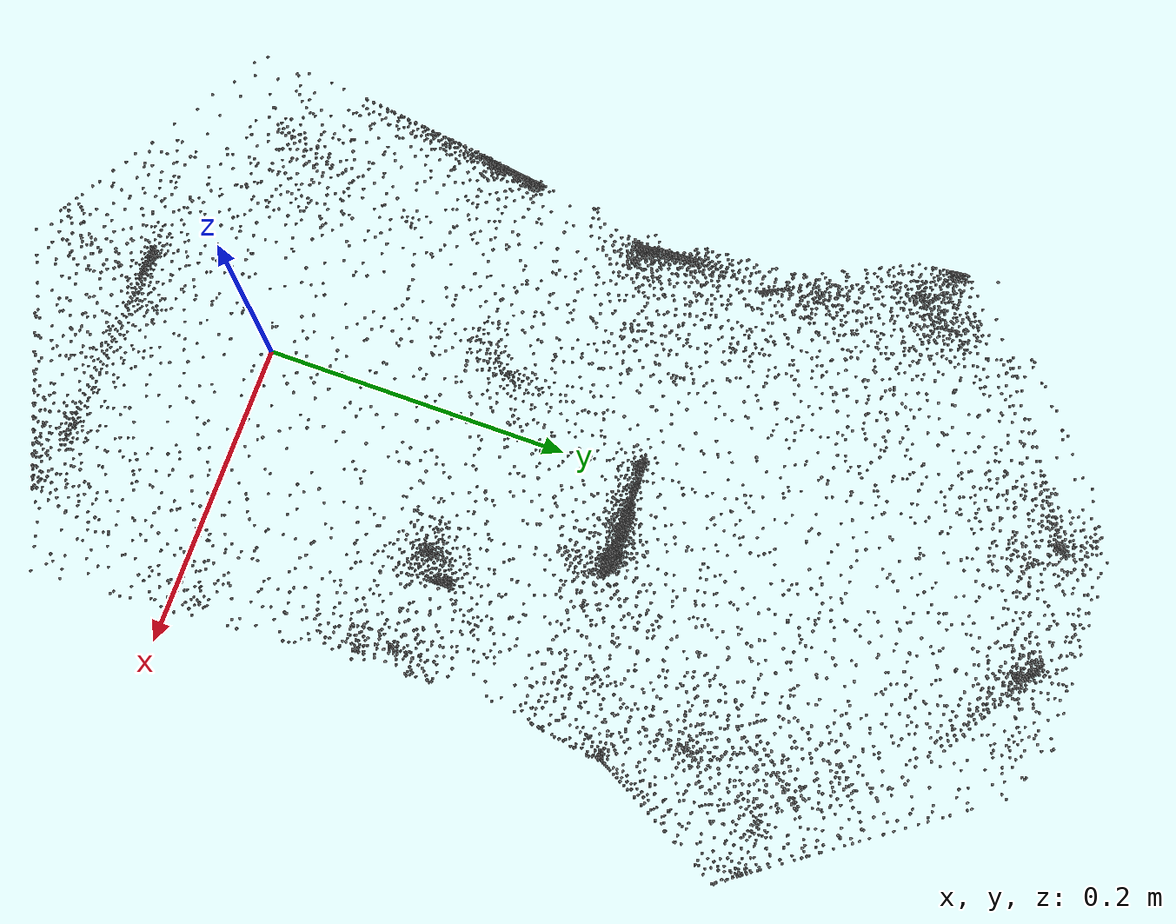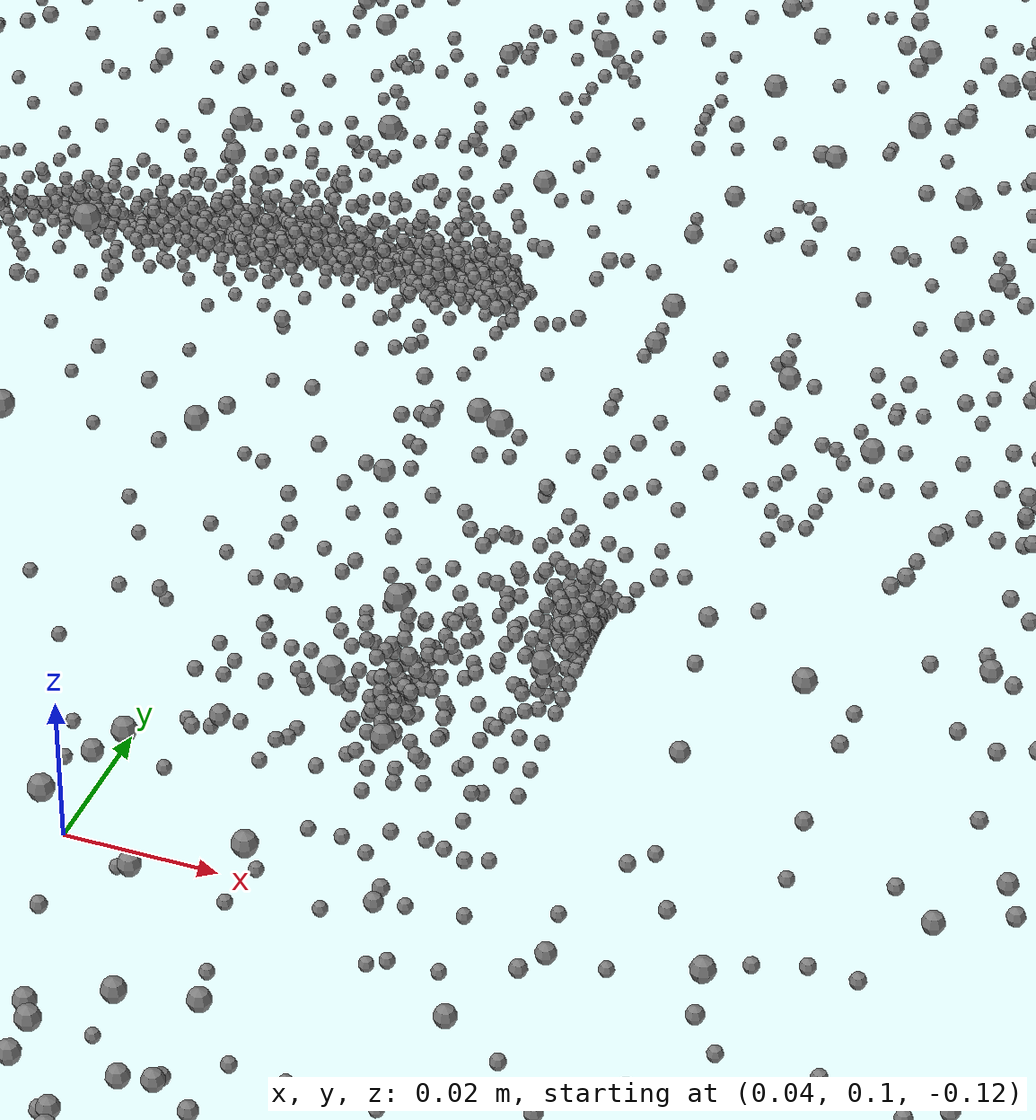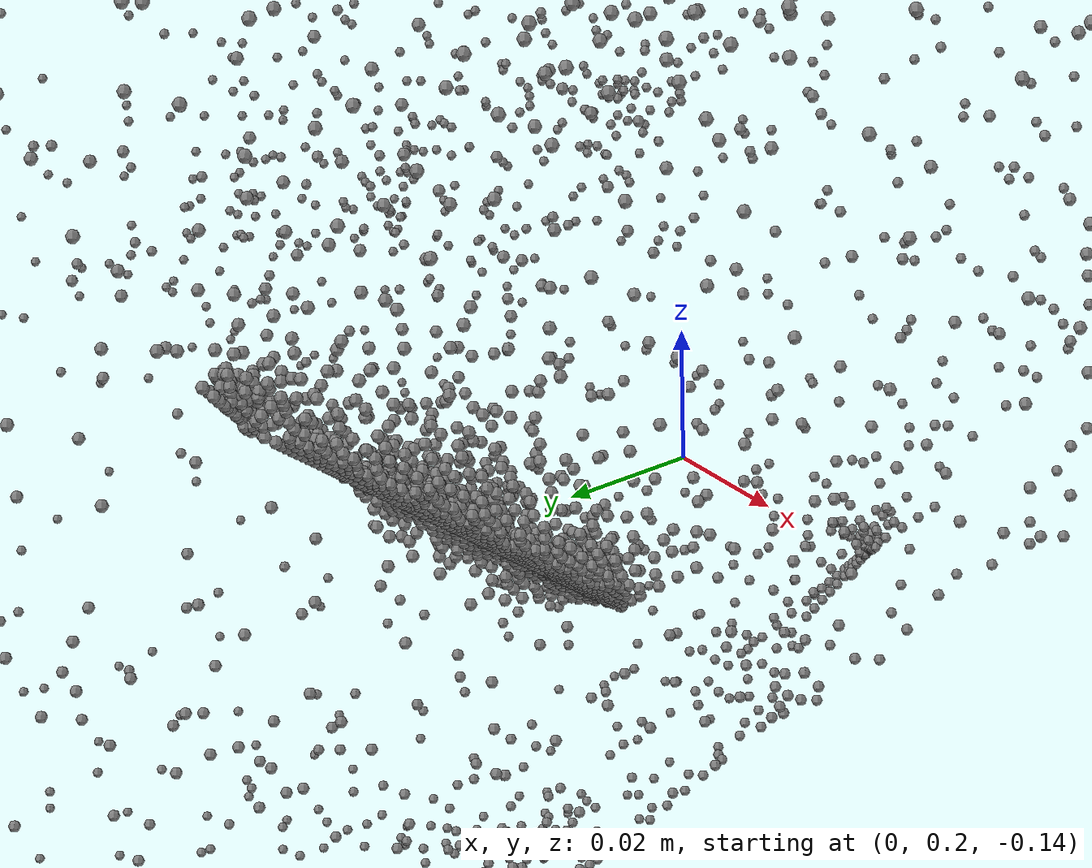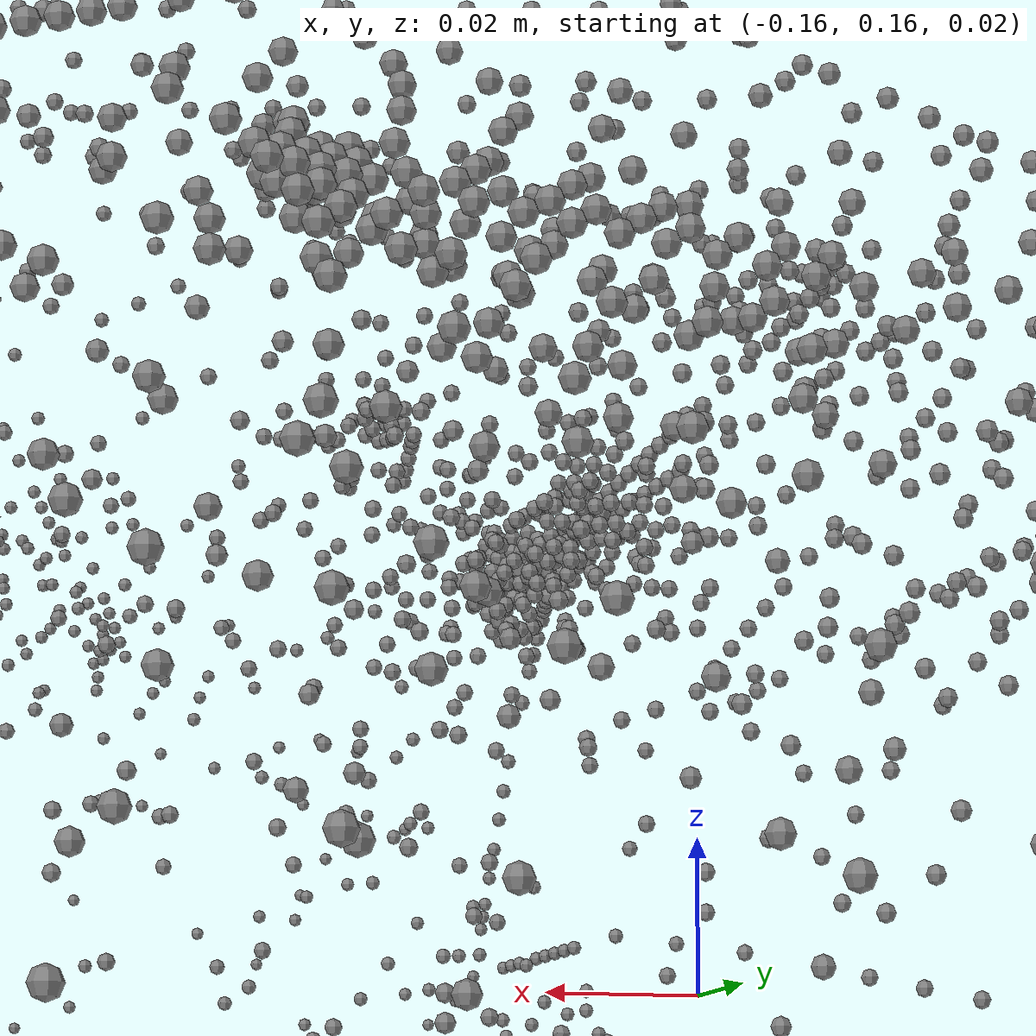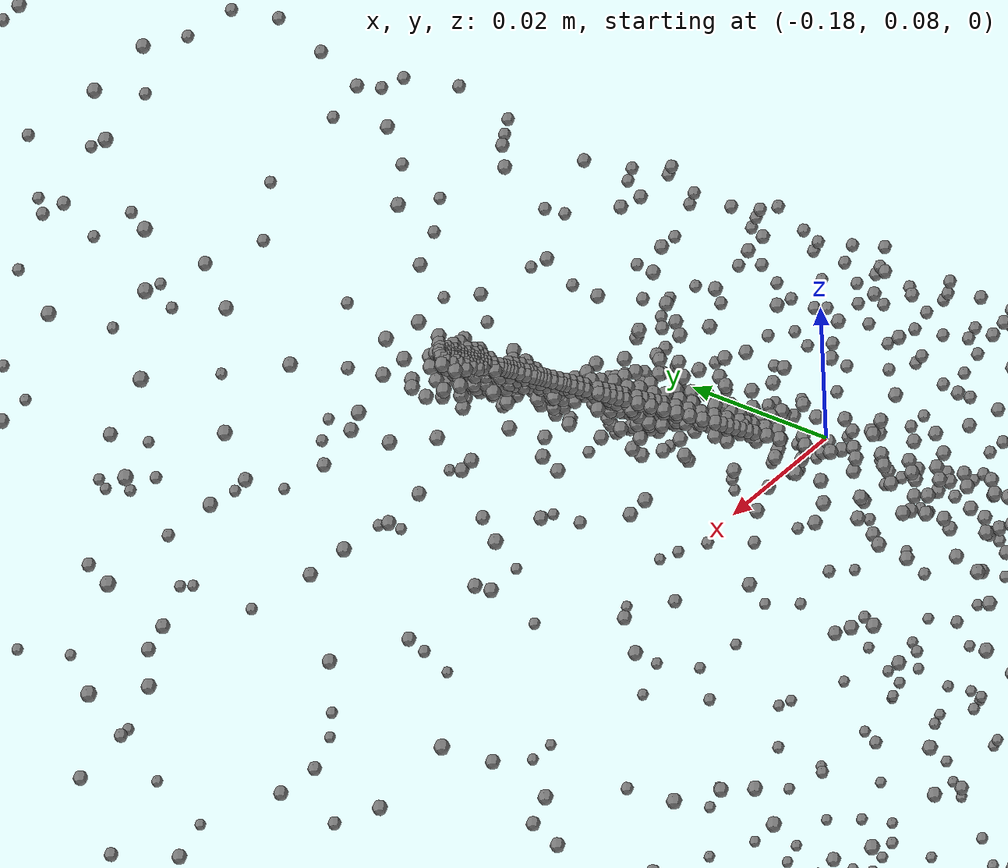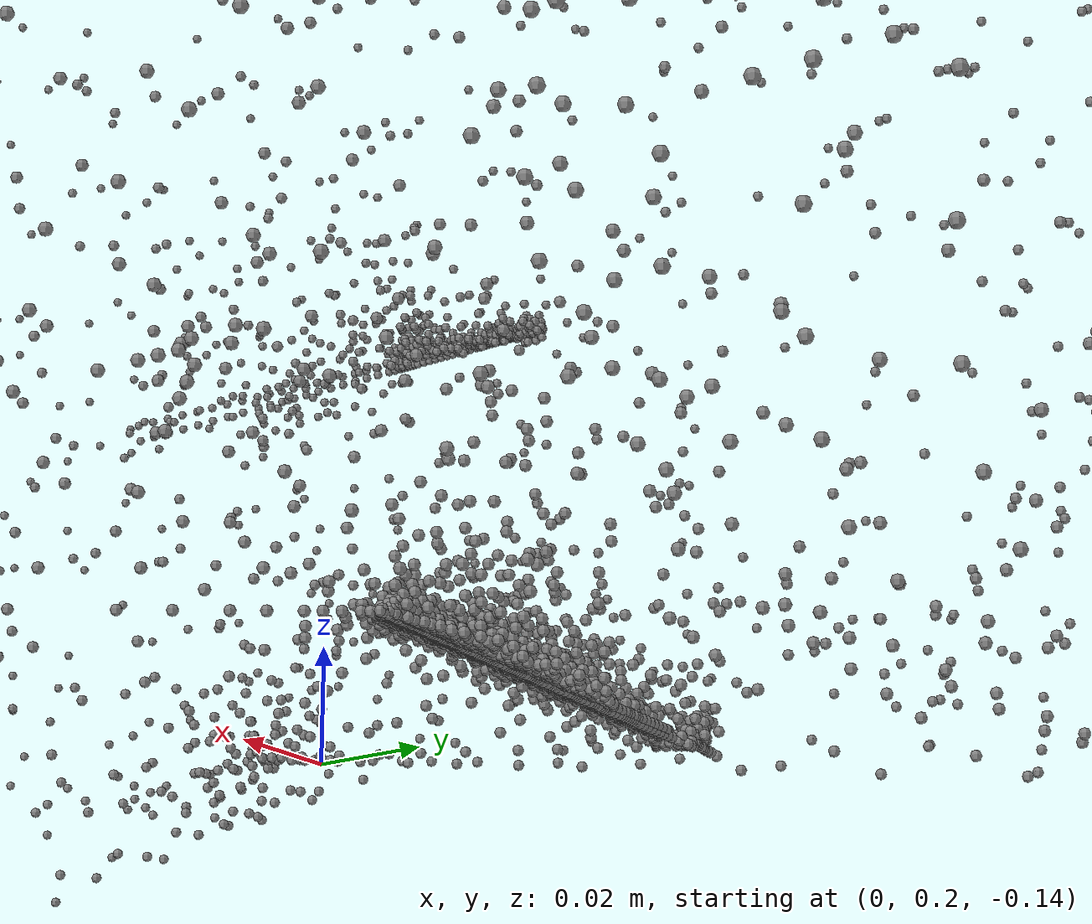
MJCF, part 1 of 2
<mujoco model="unnamed_model">
  <default>
    <default class="/"/>
  </default>
  <worldbody>
    <body name="point_mass_0">
      <freejoint name="//unnamed_joint_0"/>
      <geom name="point_mass_0" class="/" type="sphere" size="0.001" mass="0.01" pos="0.073484927415847778 0.20197632908821106 0.12272949516773224"/>
    </body>
    <body name="point_mass_1">
      <freejoint name="//unnamed_joint_1"/>
      <geom name="point_mass_1" class="/" type="sphere" size="0.001" mass="0.01" pos="0.094918273389339447 0.20122180879116058 0.10704047977924347"/>
    </body>
    <body name="point_mass_2">
      <freejoint name="//unnamed_joint_2"/>
      <geom name="point_mass_2" class="/" type="sphere" size="0.001" mass="0.01" pos="0.12281184643507004 0.33292743563652039 0.093817643821239471"/>
    </body>
    <body name="point_mass_3">
      <freejoint name="//unnamed_joint_3"/>
      <geom name="point_mass_3" class="/" type="sphere" size="0.001" mass="0.01" pos="-0.15751172602176666 0.21354834735393524 -0.034303285181522369"/>
    </body>
    <body name="point_mass_4">
      <freejoint name="//unnamed_joint_4"/>
      <geom name="point_mass_4" class="/" type="sphere" size="0.001" mass="0.01" pos="-0.17218132317066193 0.29922038316726685 -0.04145372286438942"/>
    </body>
    <body name="point_mass_5">
      <freejoint name="//unnamed_joint_5"/>
      <geom name="point_mass_5" class="/" type="sphere" size="0.001" mass="0.01" pos="-0.16955895721912384 0.2902255654335022 -0.059450611472129822"/>
    </body>
    <body name="point_mass_6">
      <freejoint name="//unnamed_joint_6"/>
      <geom name="point_mass_6" class="/" type="sphere" size="0.001" mass="0.01" pos="-0.10038100928068161 0.30308324098587036 -0.13527999818325043"/>
    </body>
    <body name="point_mass_7">
      <freejoint name="//unnamed_joint_7"/>
      <geom name="point_mass_7" class="/" type="sphere" size="0.001" mass="0.01" pos="-0.082623206079006195 0.23739120364189148 -0.12848581373691559"/>
    </body>
    <body name="point_mass_8">
      <freejoint name="//unnamed_joint_8"/>
      <geom name="point_mass_8" class="/" type="sphere" size="0.001" mass="0.01" pos="-0.11434347182512283 0.27241373062133789 -0.1240045577287674"/>
    </body>
    <body name="point_mass_9">
      <freejoint name="//unnamed_joint_9"/>
      <geom name="point_mass_9" class="/" type="sphere" size="0.001" mass="0.01" pos="0.17361855506896973 0.28559055924415588 -0.01280579250305891"/>
    </body>
    <body name="point_mass_10">
      <freejoint name="//unnamed_joint_10"/>
      <geom name="point_mass_10" class="/" type="sphere" size="0.001" mass="0.01" pos="0.1625080406665802 0.2075316458940506 -0.00015453339437954128"/>
    </body>
    <body name="point_mass_11">
      <freejoint name="//unnamed_joint_11"/>
      <geom name="point_mass_11" class="/" type="sphere" size="0.001" mass="0.01" pos="0.17634311318397522 0.29953396320343018 -0.043063513934612274"/>
    </body>
    <body name="point_mass_12">
      <freejoint name="//unnamed_joint_12"/>
      <geom name="point_mass_12" class="/" type="sphere" size="0.001" mass="0.01" pos="0.11211936920881271 0.33360052108764648 0.099483229219913483"/>
    </body>
    <body name="point_mass_13">
      <freejoint name="//unnamed_joint_13"/>
      <geom name="point_mass_13" class="/" type="sphere" size="0.001" mass="0.01" pos="0.06607469916343689 0.21654309332370758 0.12420620024204254"/>
    </body>
    <body name="point_mass_14">
      <freejoint name="//unnamed_joint_14"/>
      <geom name="point_mass_14" class="/" type="sphere" size="0.001" mass="0.01" pos="0.05300525575876236 0.22664815187454224 0.12797810137271881"/>
    </body>
    <body name="point_mass_15">
      <freejoint name="//unnamed_joint_15"/>
      <geom name="point_mass_15" class="/" type="sphere" size="0.001" mass="0.01" pos="0.10023926943540573 0.33545973896980286 0.10322704911231995"/>
    </body>
    <body name="point_mass_16">
      <freejoint name="//unnamed_joint_16"/>
      <geom name="point_mass_16" class="/" type="sphere" size="0.001" mass="0.01" pos="-0.064073644578456879 0.36080041527748108 0.10029666125774384"/>
    </body>
    <body name="point_mass_17">
      <freejoint name="//unnamed_joint_17"/>
      <geom name="point_mass_17" class="/" type="sphere" size="0.001" mass="0.01" pos="-0.066067829728126526 0.34378519654273987 0.10423062741756439"/>
    </body>
    <body name="point_mass_18">
      <freejoint name="//unnamed_joint_18"/>
      <geom name="point_mass_18" class="/" type="sphere" size="0.001" mass="0.01" pos="0.056985862553119659 0.35772120952606201 0.10397599637508392"/>
    </body>
    <body name="point_mass_19">
      <freejoint name="//unnamed_joint_19"/>
      <geom name="point_mass_19" class="/" type="sphere" size="0.001" mass="0.01" pos="0.11341791599988937 0.20081299543380737 0.089628040790557861"/>
    </body>
    <body name="point_mass_20">
      <freejoint name="//unnamed_joint_20"/>
      <geom name="point_mass_20" class="/" type="sphere" size="0.001" mass="0.01" pos="0.13143910467624664 0.33322912454605103 0.086594901978969574"/>
    </body>
    <body name="point_mass_21">
      <freejoint name="//unnamed_joint_21"/>
      <geom name="point_mass_21" class="/" type="sphere" size="0.001" mass="0.01" pos="0.138520747423172 0.33372741937637329 0.079257480800151825"/>
    </body>
    <body name="point_mass_22">
      <freejoint name="//unnamed_joint_22"/>
      <geom name="point_mass_22" class="/" type="sphere" size="0.001" mass="0.01" pos="0.14162701368331909 0.34701886773109436 0.076364733278751373"/>
    </body>
    <body name="point_mass_23">
      <freejoint name="//unnamed_joint_23"/>
      <geom name="point_mass_23" class="/" type="sphere" size="0.001" mass="0.01" pos="-0.14923989772796631 0.29871419072151184 -0.10234023630619049"/>
    </body>
    <body name="point_mass_24">
      <freejoint name="//unnamed_joint_24"/>
      <geom name="point_mass_24" class="/" type="sphere" size="0.001" mass="0.01" pos="-0.13361050188541412 0.30774053931236267 -0.1186271458864212"/>
    </body>
    <body name="point_mass_25">
      <freejoint name="//unnamed_joint_25"/>
      <geom name="point_mass_25" class="/" type="sphere" size="0.001" mass="0.01" pos="-0.14077198505401611 0.28123936057090759 -0.1062217578291893"/>
    </body>
    <body name="point_mass_26">
      <freejoint name="//unnamed_joint_26"/>
      <geom name="point_mass_26" class="/" type="sphere" size="0.001" mass="0.01" pos="-0.091549724340438843 0.28330609202384949 -0.13435481488704681"/>
    </body>
    <body name="point_mass_27">
      <freejoint name="//unnamed_joint_27"/>
      <geom name="point_mass_27" class="/" type="sphere" size="0.001" mass="0.01" pos="-0.074323534965515137 0.32105433940887451 -0.14417438209056854"/>
    </body>
    <body name="point_mass_28">
      <freejoint name="//unnamed_joint_28"/>
      <geom name="point_mass_28" class="/" type="sphere" size="0.001" mass="0.01" pos="-0.13372063636779785 0.26320654153823853 -0.10857018828392029"/>
    </body>
    <body name="point_mass_29">
      <freejoint name="//unnamed_joint_29"/>
      <geom name="point_mass_29" class="/" type="sphere" size="0.001" mass="0.01" pos="0.028316905722022057 0.31658750772476196 -0.14425937831401825"/>
    </body>
    <body name="point_mass_30">
      <freejoint name="//unnamed_joint_30"/>
      <geom name="point_mass_30" class="/" type="sphere" size="0.001" mass="0.01" pos="0.077009066939353943 0.3196539580821991 -0.14430588483810425"/>
    </body>
    <body name="point_mass_31">
      <freejoint name="//unnamed_joint_31"/>
      <geom name="point_mass_31" class="/" type="sphere" size="0.001" mass="0.01" pos="-0.041198965162038803 0.29858198761940002 -0.14417676627635956"/>
    </body>
    <body name="point_mass_32">
      <freejoint name="//unnamed_joint_32"/>
      <geom name="point_mass_32" class="/" type="sphere" size="0.001" mass="0.01" pos="-0.033386360853910446 0.31481903791427612 -0.14420297741889954"/>
    </body>
    <body name="point_mass_33">
      <freejoint name="//unnamed_joint_33"/>
      <geom name="point_mass_33" class="/" type="sphere" size="0.001" mass="0.01" pos="-0.1060861274600029 0.20697923004627228 0.087805427610874176"/>
    </body>
    <body name="point_mass_34">
      <freejoint name="//unnamed_joint_34"/>
      <geom name="point_mass_34" class="/" type="sphere" size="0.001" mass="0.01" pos="-0.092033565044403076 0.20267230272293091 0.10248889774084091"/>
    </body>
    <body name="point_mass_35">
      <freejoint name="//unnamed_joint_35"/>
      <geom name="point_mass_35" class="/" type="sphere" size="0.001" mass="0.01" pos="-0.12889404594898224 0.33044785261154175 0.077545702457427979"/>
    </body>
    <body name="point_mass_36">
      <freejoint name="//unnamed_joint_36"/>
      <geom name="point_mass_36" class="/" type="sphere" size="0.001" mass="0.01" pos="-0.10966800153255463 0.20697431266307831 0.083934254944324493"/>
    </body>
    <body name="point_mass_37">
      <freejoint name="//unnamed_joint_37"/>
      <geom name="point_mass_37" class="/" type="sphere" size="0.001" mass="0.01" pos="-0.10901989042758942 0.20700158178806305 0.08463779091835022"/>
    </body>
    <body name="point_mass_38">
      <freejoint name="//unnamed_joint_38"/>
      <geom name="point_mass_38" class="/" type="sphere" size="0.001" mass="0.01" pos="0.16173049807548523 0.20954865217208862 -0.028749221935868263"/>
    </body>
    <body name="point_mass_39">
      <freejoint name="//unnamed_joint_39"/>
      <geom name="point_mass_39" class="/" type="sphere" size="0.001" mass="0.01" pos="-0.079862482845783234 0.34879183769226074 0.10134454071521759"/>
    </body>
    <body name="point_mass_40">
      <freejoint name="//unnamed_joint_40"/>
      <geom name="point_mass_40" class="/" type="sphere" size="0.001" mass="0.01" pos="-0.039593353867530823 0.21712552011013031 0.12973615527153015"/>
    </body>
    <body name="point_mass_41">
      <freejoint name="//unnamed_joint_41"/>
      <geom name="point_mass_41" class="/" type="sphere" size="0.001" mass="0.01" pos="-0.024471458047628403 0.22634851932525635 0.13088293373584747"/>
    </body>
    <body name="point_mass_42">
      <freejoint name="//unnamed_joint_42"/>
      <geom name="point_mass_42" class="/" type="sphere" size="0.001" mass="0.01" pos="-0.04887666180729866 0.20287087559700012 0.13042576611042023"/>
    </body>
    <body name="point_mass_43">
      <freejoint name="//unnamed_joint_43"/>
      <geom name="point_mass_43" class="/" type="sphere" size="0.001" mass="0.01" pos="-0.10649677366018295 0.36218109726905823 0.089142069220542908"/>
    </body>
    <body name="point_mass_44">
      <freejoint name="//unnamed_joint_44"/>
      <geom name="point_mass_44" class="/" type="sphere" size="0.001" mass="0.01" pos="-0.10512246191501617 0.34718668460845947 0.095201633870601654"/>
    </body>
    <body name="point_mass_45">
      <freejoint name="//unnamed_joint_45"/>
      <geom name="point_mass_45" class="/" type="sphere" size="0.001" mass="0.01" pos="-0.094029724597930908 0.36321943998336792 0.093576304614543915"/>
    </body>
    <body name="point_mass_46">
      <freejoint name="//unnamed_joint_46"/>
      <geom name="point_mass_46" class="/" type="sphere" size="0.001" mass="0.01" pos="-0.1675807386636734 0.28593254089355469 -0.062736727297306061"/>
    </body>
    <body name="point_mass_47">
      <freejoint name="//unnamed_joint_47"/>
      <geom name="point_mass_47" class="/" type="sphere" size="0.001" mass="0.01" pos="-0.16756030917167664 0.28589749336242676 -0.062778964638710022"/>
    </body>
    <body name="point_mass_48">
      <freejoint name="//unnamed_joint_48"/>
      <geom name="point_mass_48" class="/" type="sphere" size="0.001" mass="0.01" pos="-0.15075093507766724 0.21660725772380829 -0.061379425227642059"/>
    </body>
    <body name="point_mass_49">
      <freejoint name="//unnamed_joint_49"/>
      <geom name="point_mass_49" class="/" type="sphere" size="0.001" mass="0.01" pos="0.1684621125459671 0.29373127222061157 0.013690286315977573"/>
    </body>
    <body name="point_mass_50">
      <freejoint name="//unnamed_joint_50"/>
      <geom name="point_mass_50" class="/" type="sphere" size="0.001" mass="0.01" pos="0.15689051151275635 0.20595835149288177 0.026819493621587753"/>
    </body>
    <body name="point_mass_51">
      <freejoint name="//unnamed_joint_51"/>
      <geom name="point_mass_51" class="/" type="sphere" size="0.001" mass="0.01" pos="0.17239288985729218 0.3096197247505188 0.0042185145430266857"/>
    </body>
    <body name="point_mass_52">
      <freejoint name="//unnamed_joint_52"/>
      <geom name="point_mass_52" class="/" type="sphere" size="0.001" mass="0.01" pos="0.15712025761604309 0.33420020341873169 0.049625903367996216"/>
    </body>
    <body name="point_mass_53">
      <freejoint name="//unnamed_joint_53"/>
      <geom name="point_mass_53" class="/" type="sphere" size="0.001" mass="0.01" pos="0.15627379715442657 0.33452534675598145 0.051501121371984482"/>
    </body>
    <body name="point_mass_54">
      <freejoint name="//unnamed_joint_54"/>
      <geom name="point_mass_54" class="/" type="sphere" size="0.001" mass="0.01" pos="0.14561863243579865 0.20380412042140961 0.050613135099411011"/>
    </body>
    <body name="point_mass_55">
      <freejoint name="//unnamed_joint_55"/>
      <geom name="point_mass_55" class="/" type="sphere" size="0.001" mass="0.01" pos="0.14356248080730438 0.33412912487983704 0.072980187833309174"/>
    </body>
    <body name="point_mass_56">
      <freejoint name="//unnamed_joint_56"/>
      <geom name="point_mass_56" class="/" type="sphere" size="0.001" mass="0.01" pos="0.14749431610107422 0.33759823441505432 0.067885205149650574"/>
    </body>
    <body name="point_mass_57">
      <freejoint name="//unnamed_joint_57"/>
      <geom name="point_mass_57" class="/" type="sphere" size="0.001" mass="0.01" pos="0.11451078951358795 0.35006505250930786 0.096629083156585693"/>
    </body>
    <body name="point_mass_58">
      <freejoint name="//unnamed_joint_58"/>
      <geom name="point_mass_58" class="/" type="sphere" size="0.001" mass="0.01" pos="0.12514103949069977 0.34965762495994568 0.090736523270606995"/>
    </body>
    <body name="point_mass_59">
      <freejoint name="//unnamed_joint_59"/>
      <geom name="point_mass_59" class="/" type="sphere" size="0.001" mass="0.01" pos="0.027442758902907372 0.22642038762569427 0.13230036199092865"/>
    </body>
    <body name="point_mass_60">
      <freejoint name="//unnamed_joint_60"/>
      <geom name="point_mass_60" class="/" type="sphere" size="0.001" mass="0.01" pos="0.076019205152988434 0.34551587700843811 0.10669810324907303"/>
    </body>
    <body name="point_mass_61">
      <freejoint name="//unnamed_joint_61"/>
      <geom name="point_mass_61" class="/" type="sphere" size="0.001" mass="0.01" pos="0.00084782583871856332 0.22487662732601166 0.13212959468364716"/>
    </body>
    <body name="point_mass_62">
      <freejoint name="//unnamed_joint_62"/>
      <geom name="point_mass_62" class="/" type="sphere" size="0.001" mass="0.01" pos="-0.07967974990606308 0.36321142315864563 0.097410038113594055"/>
    </body>
    <body name="point_mass_63">
      <freejoint name="//unnamed_joint_63"/>
      <geom name="point_mass_63" class="/" type="sphere" size="0.001" mass="0.01" pos="-0.12240546941757202 0.29050374031066895 -0.12320332229137421"/>
    </body>
    <body name="point_mass_64">
      <freejoint name="//unnamed_joint_64"/>
      <geom name="point_mass_64" class="/" type="sphere" size="0.001" mass="0.01" pos="0.1341390460729599 0.34883400797843933 0.083870291709899902"/>
    </body>
    <body name="point_mass_65">
      <freejoint name="//unnamed_joint_65"/>
      <geom name="point_mass_65" class="/" type="sphere" size="0.001" mass="0.01" pos="-0.067099668085575104 0.294077068567276 -0.14160148799419403"/>
    </body>
    <body name="point_mass_66">
      <freejoint name="//unnamed_joint_66"/>
      <geom name="point_mass_66" class="/" type="sphere" size="0.001" mass="0.01" pos="-0.063421227037906647 0.26859158277511597 -0.13834194839000702"/>
    </body>
    <body name="point_mass_67">
      <freejoint name="//unnamed_joint_67"/>
      <geom name="point_mass_67" class="/" type="sphere" size="0.001" mass="0.01" pos="-0.060842420905828476 0.24272383749485016 -0.13453373312950134"/>
    </body>
    <body name="point_mass_68">
      <freejoint name="//unnamed_joint_68"/>
      <geom name="point_mass_68" class="/" type="sphere" size="0.001" mass="0.01" pos="-0.03840593621134758 0.24715173244476318 -0.13484454154968262"/>
    </body>
    <body name="point_mass_69">
      <freejoint name="//unnamed_joint_69"/>
      <geom name="point_mass_69" class="/" type="sphere" size="0.001" mass="0.01" pos="0.04545772448182106 0.27269077301025391 -0.13797441124916077"/>
    </body>
    <body name="point_mass_70">
      <freejoint name="//unnamed_joint_70"/>
      <geom name="point_mass_70" class="/" type="sphere" size="0.001" mass="0.01" pos="0.066706754267215729 0.24169208109378815 -0.13056303560733795"/>
    </body>
    <body name="point_mass_71">
      <freejoint name="//unnamed_joint_71"/>
      <geom name="point_mass_71" class="/" type="sphere" size="0.001" mass="0.01" pos="0.044890109449625015 0.24661196768283844 -0.13228082656860352"/>
    </body>
    <body name="point_mass_72">
      <freejoint name="//unnamed_joint_72"/>
      <geom name="point_mass_72" class="/" type="sphere" size="0.001" mass="0.01" pos="0.043446287512779236 0.24684569239616394 -0.13237439095973969"/>
    </body>
    <body name="point_mass_73">
      <freejoint name="//unnamed_joint_73"/>
      <geom name="point_mass_73" class="/" type="sphere" size="0.001" mass="0.01" pos="-0.03470008447766304 0.24764606356620789 -0.13484399020671844"/>
    </body>
    <body name="point_mass_74">
      <freejoint name="//unnamed_joint_74"/>
      <geom name="point_mass_74" class="/" type="sphere" size="0.001" mass="0.01" pos="0.040168758481740952 0.24689312279224396 -0.13248100876808167"/>
    </body>
    <body name="point_mass_75">
      <freejoint name="//unnamed_joint_75"/>
      <geom name="point_mass_75" class="/" type="sphere" size="0.001" mass="0.01" pos="-0.13776642084121704 0.2205885648727417 -0.08554956316947937"/>
    </body>
    <body name="point_mass_76">
      <freejoint name="//unnamed_joint_76"/>
      <geom name="point_mass_76" class="/" type="sphere" size="0.001" mass="0.01" pos="-0.12689945101737976 0.24528121948242188 -0.1078144833445549"/>
    </body>
    <body name="point_mass_77">
      <freejoint name="//unnamed_joint_77"/>
      <geom name="point_mass_77" class="/" type="sphere" size="0.001" mass="0.01" pos="-0.12140339612960815 0.22568851709365845 -0.1048625186085701"/>
    </body>
    <body name="point_mass_78">
      <freejoint name="//unnamed_joint_78"/>
      <geom name="point_mass_78" class="/" type="sphere" size="0.001" mass="0.01" pos="-0.10278007388114929 0.23174244165420532 -0.11864521354436874"/>
    </body>
    <body name="point_mass_79">
      <freejoint name="//unnamed_joint_79"/>
      <geom name="point_mass_79" class="/" type="sphere" size="0.001" mass="0.01" pos="-0.071648277342319489 0.20282620191574097 0.11908538639545441"/>
    </body>
    <body name="point_mass_80">
      <freejoint name="//unnamed_joint_80"/>
      <geom name="point_mass_80" class="/" type="sphere" size="0.001" mass="0.01" pos="-0.11199219524860382 0.20773124694824219 0.0813145712018013"/>
    </body>
    <body name="point_mass_81">
      <freejoint name="//unnamed_joint_81"/>
      <geom name="point_mass_81" class="/" type="sphere" size="0.001" mass="0.01" pos="-0.12540192902088165 0.20797298848628998 0.065662086009979248"/>
    </body>
    <body name="point_mass_82">
      <freejoint name="//unnamed_joint_82"/>
      <geom name="point_mass_82" class="/" type="sphere" size="0.001" mass="0.01" pos="-0.124953992664814 0.2079651951789856 0.066184975206851959"/>
    </body>
    <body name="point_mass_83">
      <freejoint name="//unnamed_joint_83"/>
      <geom name="point_mass_83" class="/" type="sphere" size="0.001" mass="0.01" pos="0.13046135008335114 0.20168633759021759 0.07127775251865387"/>
    </body>
    <body name="point_mass_84">
      <freejoint name="//unnamed_joint_84"/>
      <geom name="point_mass_84" class="/" type="sphere" size="0.001" mass="0.01" pos="-0.15148675441741943 0.20948857069015503 0.020948097109794617"/>
    </body>
    <body name="point_mass_85">
      <freejoint name="//unnamed_joint_85"/>
      <geom name="point_mass_85" class="/" type="sphere" size="0.001" mass="0.01" pos="-0.16412629187107086 0.30835804343223572 0.0045531149953603745"/>
    </body>
    <body name="point_mass_86">
      <freejoint name="//unnamed_joint_86"/>
      <geom name="point_mass_86" class="/" type="sphere" size="0.001" mass="0.01" pos="-0.1694234311580658 0.3019871711730957 -0.01848292164504528"/>
    </body>
    <body name="point_mass_87">
      <freejoint name="//unnamed_joint_87"/>
      <geom name="point_mass_87" class="/" type="sphere" size="0.001" mass="0.01" pos="-0.12157700210809708 0.3297823965549469 0.084630504250526428"/>
    </body>
    <body name="point_mass_88">
      <freejoint name="//unnamed_joint_88"/>
      <geom name="point_mass_88" class="/" type="sphere" size="0.001" mass="0.01" pos="0.16614024341106415 0.32043972611427307 0.024433383718132973"/>
    </body>
    <body name="point_mass_89">
      <freejoint name="//unnamed_joint_89"/>
      <geom name="point_mass_89" class="/" type="sphere" size="0.001" mass="0.01" pos="0.15151672065258026 0.33342364430427551 0.060557786375284195"/>
    </body>
    <body name="point_mass_90">
      <freejoint name="//unnamed_joint_90"/>
      <geom name="point_mass_90" class="/" type="sphere" size="0.001" mass="0.01" pos="0.17611019313335419 0.30257254838943481 -0.019129719585180283"/>
    </body>
    <body name="point_mass_91">
      <freejoint name="//unnamed_joint_91"/>
      <geom name="point_mass_91" class="/" type="sphere" size="0.001" mass="0.01" pos="0.16987347602844238 0.28581562638282776 -0.063860662281513214"/>
    </body>
    <body name="point_mass_92">
      <freejoint name="//unnamed_joint_92"/>
      <geom name="point_mass_92" class="/" type="sphere" size="0.001" mass="0.01" pos="0.17019206285476685 0.28643882274627686 -0.063485667109489441"/>
    </body>
    <body name="point_mass_93">
      <freejoint name="//unnamed_joint_93"/>
      <geom name="point_mass_93" class="/" type="sphere" size="0.001" mass="0.01" pos="0.15483075380325317 0.21267034113407135 -0.055967122316360474"/>
    </body>
    <body name="point_mass_94">
      <freejoint name="//unnamed_joint_94"/>
      <geom name="point_mass_94" class="/" type="sphere" size="0.001" mass="0.01" pos="0.16148585081100464 0.2893754243850708 -0.085425287485122681"/>
    </body>
    <body name="point_mass_95">
      <freejoint name="//unnamed_joint_95"/>
      <geom name="point_mass_95" class="/" type="sphere" size="0.001" mass="0.01" pos="0.16970148682594299 0.28558275103569031 -0.064123727381229401"/>
    </body>
    <body name="point_mass_96">
      <freejoint name="//unnamed_joint_96"/>
      <geom name="point_mass_96" class="/" type="sphere" size="0.001" mass="0.01" pos="0.16974501311779022 0.28557977080345154 -0.064020894467830658"/>
    </body>
    <body name="point_mass_97">
      <freejoint name="//unnamed_joint_97"/>
      <geom name="point_mass_97" class="/" type="sphere" size="0.001" mass="0.01" pos="0.17185203731060028 0.28977811336517334 -0.06038907915353775"/>
    </body>
    <body name="point_mass_98">
      <freejoint name="//unnamed_joint_98"/>
      <geom name="point_mass_98" class="/" type="sphere" size="0.001" mass="0.01" pos="0.14181235432624817 0.21681542694568634 -0.079881742596626282"/>
    </body>
    <body name="point_mass_99">
      <freejoint name="//unnamed_joint_99"/>
      <geom name="point_mass_99" class="/" type="sphere" size="0.001" mass="0.01" pos="0.15073436498641968 0.25398474931716919 -0.085549525916576385"/>
    </body>
    <body name="point_mass_100">
      <freejoint name="//unnamed_joint_100"/>
      <geom name="point_mass_100" class="/" type="sphere" size="0.001" mass="0.01" pos="0.10359995812177658 0.36601102352142334 0.095381893217563629"/>
    </body>
    <body name="point_mass_101">
      <freejoint name="//unnamed_joint_101"/>
      <geom name="point_mass_101" class="/" type="sphere" size="0.001" mass="0.01" pos="0.11604296416044235 0.36524346470832825 0.090879045426845551"/>
    </body>
    <body name="point_mass_102">
      <freejoint name="//unnamed_joint_102"/>
      <geom name="point_mass_102" class="/" type="sphere" size="0.001" mass="0.01" pos="0.073592387139797211 0.36267068982124329 0.10274709761142731"/>
    </body>
    <body name="point_mass_103">
      <freejoint name="//unnamed_joint_103"/>
      <geom name="point_mass_103" class="/" type="sphere" size="0.001" mass="0.01" pos="0.089947178959846497 0.35087636113166809 0.10358274728059769"/>
    </body>
    <body name="point_mass_104">
      <freejoint name="//unnamed_joint_104"/>
      <geom name="point_mass_104" class="/" type="sphere" size="0.001" mass="0.01" pos="0.089174002408981323 0.36550036072731018 0.099131442606449127"/>
    </body>
    <body name="point_mass_105">
      <freejoint name="//unnamed_joint_105"/>
      <geom name="point_mass_105" class="/" type="sphere" size="0.001" mass="0.01" pos="-0.092771589756011963 0.34836524724960327 0.098672017455101013"/>
    </body>
    <body name="point_mass_106">
      <freejoint name="//unnamed_joint_106"/>
      <geom name="point_mass_106" class="/" type="sphere" size="0.001" mass="0.01" pos="0.14250171184539795 0.27926641702651978 -0.10584483295679092"/>
    </body>
    <body name="point_mass_107">
      <freejoint name="//unnamed_joint_107"/>
      <geom name="point_mass_107" class="/" type="sphere" size="0.001" mass="0.01" pos="0.15026040375232697 0.2972676157951355 -0.10347043722867966"/>
    </body>
    <body name="point_mass_108">
      <freejoint name="//unnamed_joint_108"/>
      <geom name="point_mass_108" class="/" type="sphere" size="0.001" mass="0.01" pos="0.10284335911273956 0.30132701992988586 -0.13421986997127533"/>
    </body>
    <body name="point_mass_109">
      <freejoint name="//unnamed_joint_109"/>
      <geom name="point_mass_109" class="/" type="sphere" size="0.001" mass="0.01" pos="0.045866779983043671 0.29796534776687622 -0.14250874519348145"/>
    </body>
    <body name="point_mass_110">
      <freejoint name="//unnamed_joint_110"/>
      <geom name="point_mass_110" class="/" type="sphere" size="0.001" mass="0.01" pos="0.068166166543960571 0.26757839322090149 -0.13555154204368591"/>
    </body>
    <body name="point_mass_111">
      <freejoint name="//unnamed_joint_111"/>
      <geom name="point_mass_111" class="/" type="sphere" size="0.001" mass="0.01" pos="-0.10776505619287491 0.25311282277107239 -0.1219581812620163"/>
    </body>
    <body name="point_mass_112">
      <freejoint name="//unnamed_joint_112"/>
      <geom name="point_mass_112" class="/" type="sphere" size="0.001" mass="0.01" pos="-0.15742321312427521 0.21135757863521576 -0.0058406917378306389"/>
    </body>
    <body name="point_mass_113">
      <freejoint name="//unnamed_joint_113"/>
      <geom name="point_mass_113" class="/" type="sphere" size="0.001" mass="0.01" pos="-0.14785096049308777 0.33015623688697815 0.048567786812782288"/>
    </body>
    <body name="point_mass_114">
      <freejoint name="//unnamed_joint_114"/>
      <geom name="point_mass_114" class="/" type="sphere" size="0.001" mass="0.01" pos="-0.15699450671672821 0.3182520866394043 0.024297719821333885"/>
    </body>
    <body name="point_mass_115">
      <freejoint name="//unnamed_joint_115"/>
      <geom name="point_mass_115" class="/" type="sphere" size="0.001" mass="0.01" pos="-0.12428821623325348 0.34544610977172852 0.082418523728847504"/>
    </body>
    <body name="point_mass_116">
      <freejoint name="//unnamed_joint_116"/>
      <geom name="point_mass_116" class="/" type="sphere" size="0.001" mass="0.01" pos="-0.11554688960313797 0.34628844261169434 0.089420855045318604"/>
    </body>
    <body name="point_mass_117">
      <freejoint name="//unnamed_joint_117"/>
      <geom name="point_mass_117" class="/" type="sphere" size="0.001" mass="0.01" pos="-0.13173511624336243 0.34377080202102661 0.075127549469470978"/>
    </body>
    <body name="point_mass_118">
      <freejoint name="//unnamed_joint_118"/>
      <geom name="point_mass_118" class="/" type="sphere" size="0.001" mass="0.01" pos="-0.11276049911975861 0.32979032397270203 0.091609172523021698"/>
    </body>
    <body name="point_mass_119">
      <freejoint name="//unnamed_joint_119"/>
      <geom name="point_mass_119" class="/" type="sphere" size="0.001" mass="0.01" pos="0.16134825348854065 0.30682456493377686 0.034709334373474121"/>
    </body>
    <body name="point_mass_120">
      <freejoint name="//unnamed_joint_120"/>
      <geom name="point_mass_120" class="/" type="sphere" size="0.001" mass="0.01" pos="0.15849527716636658 0.332806795835495 0.046141881495714188"/>
    </body>
    <body name="point_mass_121">
      <freejoint name="//unnamed_joint_121"/>
      <geom name="point_mass_121" class="/" type="sphere" size="0.001" mass="0.01" pos="-0.16745413839817047 0.28578662872314453 -0.062973469495773315"/>
    </body>
    <body name="point_mass_122">
      <freejoint name="//unnamed_joint_122"/>
      <geom name="point_mass_122" class="/" type="sphere" size="0.001" mass="0.01" pos="-0.16003334522247314 0.29041510820388794 -0.084269061684608459"/>
    </body>
    <body name="point_mass_123">
      <freejoint name="//unnamed_joint_123"/>
      <geom name="point_mass_123" class="/" type="sphere" size="0.001" mass="0.01" pos="-0.16748754680156708 0.28577074408531189 -0.062880665063858032"/>
    </body>
    <body name="point_mass_124">
      <freejoint name="//unnamed_joint_124"/>
      <geom name="point_mass_124" class="/" type="sphere" size="0.001" mass="0.01" pos="-0.14821320772171021 0.25684139132499695 -0.087411701679229736"/>
    </body>
    <body name="point_mass_125">
      <freejoint name="//unnamed_joint_125"/>
      <geom name="point_mass_125" class="/" type="sphere" size="0.001" mass="0.01" pos="0.15593764185905457 0.27172663807868958 -0.086044475436210632"/>
    </body>
    <body name="point_mass_126">
      <freejoint name="//unnamed_joint_126"/>
      <geom name="point_mass_126" class="/" type="sphere" size="0.001" mass="0.01" pos="0.10252600163221359 0.35080555081367493 0.10058147460222244"/>
    </body>
    <body name="point_mass_127">
      <freejoint name="//unnamed_joint_127"/>
      <geom name="point_mass_127" class="/" type="sphere" size="0.001" mass="0.01" pos="0.091092512011528015 0.33875885605812073 0.10515857487916946"/>
    </body>
    <body name="point_mass_128">
      <freejoint name="//unnamed_joint_128"/>
      <geom name="point_mass_128" class="/" type="sphere" size="0.001" mass="0.01" pos="0.13522543013095856 0.306062251329422 -0.11898265779018402"/>
    </body>
    <body name="point_mass_129">
      <freejoint name="//unnamed_joint_129"/>
      <geom name="point_mass_129" class="/" type="sphere" size="0.001" mass="0.01" pos="0.11829467862844467 0.31785768270492554 -0.13211469352245331"/>
    </body>
    <body name="point_mass_130">
      <freejoint name="//unnamed_joint_130"/>
      <geom name="point_mass_130" class="/" type="sphere" size="0.001" mass="0.01" pos="0.12447340041399002 0.28844168782234192 -0.12181981652975082"/>
    </body>
    <body name="point_mass_131">
      <freejoint name="//unnamed_joint_131"/>
      <geom name="point_mass_131" class="/" type="sphere" size="0.001" mass="0.01" pos="0.13561832904815674 0.26084333658218384 -0.1055963933467865"/>
    </body>
    <body name="point_mass_132">
      <freejoint name="//unnamed_joint_132"/>
      <geom name="point_mass_132" class="/" type="sphere" size="0.001" mass="0.01" pos="0.10709133744239807 0.22927166521549225 -0.11299385130405426"/>
    </body>
    <body name="point_mass_133">
      <freejoint name="//unnamed_joint_133"/>
      <geom name="point_mass_133" class="/" type="sphere" size="0.001" mass="0.01" pos="0.12526914477348328 0.22259597480297089 -0.098819300532341003"/>
    </body>
    <body name="point_mass_134">
      <freejoint name="//unnamed_joint_134"/>
      <geom name="point_mass_134" class="/" type="sphere" size="0.001" mass="0.01" pos="0.087639041244983673 0.23574768006801605 -0.12362191826105118"/>
    </body>
    <body name="point_mass_135">
      <freejoint name="//unnamed_joint_135"/>
      <geom name="point_mass_135" class="/" type="sphere" size="0.001" mass="0.01" pos="-0.039861295372247696 0.27352473139762878 -0.14007578790187836"/>
    </body>
    <body name="point_mass_136">
      <freejoint name="//unnamed_joint_136"/>
      <geom name="point_mass_136" class="/" type="sphere" size="0.001" mass="0.01" pos="0.070551164448261261 0.29274654388427734 -0.14001037180423737"/>
    </body>
    <body name="point_mass_137">
      <freejoint name="//unnamed_joint_137"/>
      <geom name="point_mass_137" class="/" type="sphere" size="0.001" mass="0.01" pos="-0.14023022353649139 0.20710642635822296 0.044774815440177917"/>
    </body>
    <body name="point_mass_138">
      <freejoint name="//unnamed_joint_138"/>
      <geom name="point_mass_138" class="/" type="sphere" size="0.001" mass="0.01" pos="-0.14686289429664612 0.33084785938262939 0.050806991755962372"/>
    </body>
    <body name="point_mass_139">
      <freejoint name="//unnamed_joint_139"/>
      <geom name="point_mass_139" class="/" type="sphere" size="0.001" mass="0.01" pos="-0.1419670432806015 0.33052420616149902 0.059484243392944336"/>
    </body>
    <body name="point_mass_140">
      <freejoint name="//unnamed_joint_140"/>
      <geom name="point_mass_140" class="/" type="sphere" size="0.001" mass="0.01" pos="-0.13786114752292633 0.33160153031349182 0.065992139279842377"/>
    </body>
    <body name="point_mass_141">
      <freejoint name="//unnamed_joint_141"/>
      <geom name="point_mass_141" class="/" type="sphere" size="0.001" mass="0.01" pos="-0.13400737941265106 0.33116447925567627 0.071473486721515656"/>
    </body>
    <body name="point_mass_142">
      <freejoint name="//unnamed_joint_142"/>
      <geom name="point_mass_142" class="/" type="sphere" size="0.001" mass="0.01" pos="-0.12553289532661438 0.20799374580383301 0.065506882965564728"/>
    </body>
    <body name="point_mass_143">
      <freejoint name="//unnamed_joint_143"/>
      <geom name="point_mass_143" class="/" type="sphere" size="0.001" mass="0.01" pos="-0.12768010795116425 0.20986998081207275 0.062768660485744476"/>
    </body>
    <body name="point_mass_144">
      <freejoint name="//unnamed_joint_144"/>
      <geom name="point_mass_144" class="/" type="sphere" size="0.001" mass="0.01" pos="-0.14263580739498138 0.2395646721124649 -0.087548218667507172"/>
    </body>
    <body name="point_mass_145">
      <freejoint name="//unnamed_joint_145"/>
      <geom name="point_mass_145" class="/" type="sphere" size="0.001" mass="0.01" pos="0.11651436984539032 0.27032822370529175 -0.12044864147901535"/>
    </body>
    <body name="point_mass_146">
      <freejoint name="//unnamed_joint_146"/>
      <geom name="point_mass_146" class="/" type="sphere" size="0.001" mass="0.01" pos="0.10703282058238983 0.53406941890716553 -0.04197557270526886"/>
    </body>
    <body name="point_mass_147">
      <freejoint name="//unnamed_joint_147"/>
      <geom name="point_mass_147" class="/" type="sphere" size="0.001" mass="0.01" pos="0.11945560574531555 0.49921905994415283 0.0056920661590993404"/>
    </body>
    <body name="point_mass_148">
      <freejoint name="//unnamed_joint_148"/>
      <geom name="point_mass_148" class="/" type="sphere" size="0.001" mass="0.01" pos="0.16882036626338959 0.43468517065048218 0.03934638574719429"/>
    </body>
    <body name="point_mass_149">
      <freejoint name="//unnamed_joint_149"/>
      <geom name="point_mass_149" class="/" type="sphere" size="0.001" mass="0.01" pos="0.15624520182609558 0.40573236346244812 -0.12857115268707275"/>
    </body>
    <body name="point_mass_150">
      <freejoint name="//unnamed_joint_150"/>
      <geom name="point_mass_150" class="/" type="sphere" size="0.001" mass="0.01" pos="0.09719560295343399 0.45517176389694214 -0.14395947754383087"/>
    </body>
    <body name="point_mass_151">
      <freejoint name="//unnamed_joint_151"/>
      <geom name="point_mass_151" class="/" type="sphere" size="0.001" mass="0.01" pos="0.091376475989818573 0.51718598604202271 -0.11203508824110031"/>
    </body>
    <body name="point_mass_152">
      <freejoint name="//unnamed_joint_152"/>
      <geom name="point_mass_152" class="/" type="sphere" size="0.001" mass="0.01" pos="0.10568462312221527 0.54229682683944702 -0.066680222749710083"/>
    </body>
    <body name="point_mass_153">
      <freejoint name="//unnamed_joint_153"/>
      <geom name="point_mass_153" class="/" type="sphere" size="0.001" mass="0.01" pos="0.20568975806236267 0.40057158470153809 -0.014949212782084942"/>
    </body>
    <body name="point_mass_154">
      <freejoint name="//unnamed_joint_154"/>
      <geom name="point_mass_154" class="/" type="sphere" size="0.001" mass="0.01" pos="0.22066901624202728 0.3806740939617157 -0.059936821460723877"/>
    </body>
    <body name="point_mass_155">
      <freejoint name="//unnamed_joint_155"/>
      <geom name="point_mass_155" class="/" type="sphere" size="0.001" mass="0.01" pos="0.1800612211227417 0.4239715039730072 0.035327702760696411"/>
    </body>
    <body name="point_mass_156">
      <freejoint name="//unnamed_joint_156"/>
      <geom name="point_mass_156" class="/" type="sphere" size="0.001" mass="0.01" pos="0.18713442981243134 0.40899598598480225 0.026492686942219734"/>
    </body>
    <body name="point_mass_157">
      <freejoint name="//unnamed_joint_157"/>
      <geom name="point_mass_157" class="/" type="sphere" size="0.001" mass="0.01" pos="0.22016698122024536 0.38007667660713196 -0.072682321071624756"/>
    </body>
    <body name="point_mass_158">
      <freejoint name="//unnamed_joint_158"/>
      <geom name="point_mass_158" class="/" type="sphere" size="0.001" mass="0.01" pos="0.074678942561149597 0.49425670504570007 -0.12981322407722473"/>
    </body>
    <body name="point_mass_159">
      <freejoint name="//unnamed_joint_159"/>
      <geom name="point_mass_159" class="/" type="sphere" size="0.001" mass="0.01" pos="0.058687817305326462 0.53185188770294189 0.0083494242280721664"/>
    </body>
    <body name="point_mass_160">
      <freejoint name="//unnamed_joint_160"/>
      <geom name="point_mass_160" class="/" type="sphere" size="0.001" mass="0.01" pos="0.016775423660874367 0.53161633014678955 0.037489727139472961"/>
    </body>
    <body name="point_mass_161">
      <freejoint name="//unnamed_joint_161"/>
      <geom name="point_mass_161" class="/" type="sphere" size="0.001" mass="0.01" pos="-0.12473142892122269 0.45939710736274719 0.038151081651449203"/>
    </body>
    <body name="point_mass_162">
      <freejoint name="//unnamed_joint_162"/>
      <geom name="point_mass_162" class="/" type="sphere" size="0.001" mass="0.01" pos="-0.11307509243488312 0.49731814861297607 0.0079710371792316437"/>
    </body>
    <body name="point_mass_163">
      <freejoint name="//unnamed_joint_163"/>
      <geom name="point_mass_163" class="/" type="sphere" size="0.001" mass="0.01" pos="-0.15082335472106934 0.43758994340896606 0.043305002152919769"/>
    </body>
    <body name="point_mass_164">
      <freejoint name="//unnamed_joint_164"/>
      <geom name="point_mass_164" class="/" type="sphere" size="0.001" mass="0.01" pos="-0.1932125985622406 0.42641684412956238 0.02559218555688858"/>
    </body>
    <body name="point_mass_165">
      <freejoint name="//unnamed_joint_165"/>
      <geom name="point_mass_165" class="/" type="sphere" size="0.001" mass="0.01" pos="-0.21600544452667236 0.38081726431846619 -0.079709000885486603"/>
    </body>
    <body name="point_mass_166">
      <freejoint name="//unnamed_joint_166"/>
      <geom name="point_mass_166" class="/" type="sphere" size="0.001" mass="0.01" pos="-0.10196744650602341 0.54020476341247559 -0.062350001186132431"/>
    </body>
    <body name="point_mass_167">
      <freejoint name="//unnamed_joint_167"/>
      <geom name="point_mass_167" class="/" type="sphere" size="0.001" mass="0.01" pos="-0.21840564906597137 0.37708708643913269 -0.057343993335962296"/>
    </body>
    <body name="point_mass_168">
      <freejoint name="//unnamed_joint_168"/>
      <geom name="point_mass_168" class="/" type="sphere" size="0.001" mass="0.01" pos="-0.09568343311548233 0.37768924236297607 0.087138421833515167"/>
    </body>
    <body name="point_mass_169">
      <freejoint name="//unnamed_joint_169"/>
      <geom name="point_mass_169" class="/" type="sphere" size="0.001" mass="0.01" pos="-0.13705898821353912 0.44051945209503174 0.045801054686307907"/>
    </body>
    <body name="point_mass_170">
      <freejoint name="//unnamed_joint_170"/>
      <geom name="point_mass_170" class="/" type="sphere" size="0.001" mass="0.01" pos="0.070019155740737915 0.53677970170974731 -0.0069837989285588264"/>
    </body>
    <body name="point_mass_171">
      <freejoint name="//unnamed_joint_171"/>
      <geom name="point_mass_171" class="/" type="sphere" size="0.001" mass="0.01" pos="-0.093209274113178253 0.53465175628662109 -0.08475165069103241"/>
    </body>
    <body name="point_mass_172">
      <freejoint name="//unnamed_joint_172"/>
      <geom name="point_mass_172" class="/" type="sphere" size="0.001" mass="0.01" pos="-0.087414748966693878 0.51792824268341064 -0.10646051913499832"/>
    </body>
    <body name="point_mass_173">
      <freejoint name="//unnamed_joint_173"/>
      <geom name="point_mass_173" class="/" type="sphere" size="0.001" mass="0.01" pos="-0.055394254624843597 0.55906915664672852 -0.069739900529384613"/>
    </body>
    <body name="point_mass_174">
      <freejoint name="//unnamed_joint_174"/>
      <geom name="point_mass_174" class="/" type="sphere" size="0.001" mass="0.01" pos="-0.077668726444244385 0.5510026216506958 -0.064350605010986328"/>
    </body>
    <body name="point_mass_175">
      <freejoint name="//unnamed_joint_175"/>
      <geom name="point_mass_175" class="/" type="sphere" size="0.001" mass="0.01" pos="-0.062849231064319611 0.5588797926902771 -0.054617319256067276"/>
    </body>
    <body name="point_mass_176">
      <freejoint name="//unnamed_joint_176"/>
      <geom name="point_mass_176" class="/" type="sphere" size="0.001" mass="0.01" pos="0.065935976803302765 0.56046587228775024 -0.058311924338340759"/>
    </body>
    <body name="point_mass_177">
      <freejoint name="//unnamed_joint_177"/>
      <geom name="point_mass_177" class="/" type="sphere" size="0.001" mass="0.01" pos="0.21797972917556763 0.38335087895393372 -0.081925936043262482"/>
    </body>
    <body name="point_mass_178">
      <freejoint name="//unnamed_joint_178"/>
      <geom name="point_mass_178" class="/" type="sphere" size="0.001" mass="0.01" pos="0.090265825390815735 0.3530101478099823 -0.15087246894836426"/>
    </body>
    <body name="point_mass_179">
      <freejoint name="//unnamed_joint_179"/>
      <geom name="point_mass_179" class="/" type="sphere" size="0.001" mass="0.01" pos="0.067416690289974213 0.34667748212814331 -0.15088219940662384"/>
    </body>
    <body name="point_mass_180">
      <freejoint name="//unnamed_joint_180"/>
      <geom name="point_mass_180" class="/" type="sphere" size="0.001" mass="0.01" pos="0.20488861203193665 0.37383028864860535 -0.090801626443862915"/>
    </body>
    <body name="point_mass_181">
      <freejoint name="//unnamed_joint_181"/>
      <geom name="point_mass_181" class="/" type="sphere" size="0.001" mass="0.01" pos="0.057303767651319504 0.56014519929885864 -0.072933323681354523"/>
    </body>
    <body name="point_mass_182">
      <freejoint name="//unnamed_joint_182"/>
      <geom name="point_mass_182" class="/" type="sphere" size="0.001" mass="0.01" pos="0.062826260924339294 0.55450958013534546 -0.0804339200258255"/>
    </body>
    <body name="point_mass_183">
      <freejoint name="//unnamed_joint_183"/>
      <geom name="point_mass_183" class="/" type="sphere" size="0.001" mass="0.01" pos="0.044667646288871765 0.55692923069000244 -0.082419753074645996"/>
    </body>
    <body name="point_mass_184">
      <freejoint name="//unnamed_joint_184"/>
      <geom name="point_mass_184" class="/" type="sphere" size="0.001" mass="0.01" pos="0.096485868096351624 0.53566360473632812 -0.089540548622608185"/>
    </body>
    <body name="point_mass_185">
      <freejoint name="//unnamed_joint_185"/>
      <geom name="point_mass_185" class="/" type="sphere" size="0.001" mass="0.01" pos="0.062977038323879242 0.5267174243927002 -0.10940318554639816"/>
    </body>
    <body name="point_mass_186">
      <freejoint name="//unnamed_joint_186"/>
      <geom name="point_mass_186" class="/" type="sphere" size="0.001" mass="0.01" pos="0.072585389018058777 0.53214901685714722 -0.10282984375953674"/>
    </body>
    <body name="point_mass_187">
      <freejoint name="//unnamed_joint_187"/>
      <geom name="point_mass_187" class="/" type="sphere" size="0.001" mass="0.01" pos="-0.065201207995414734 0.51576811075210571 -0.11322827637195587"/>
    </body>
    <body name="point_mass_188">
      <freejoint name="//unnamed_joint_188"/>
      <geom name="point_mass_188" class="/" type="sphere" size="0.001" mass="0.01" pos="-0.070623166859149933 0.49552074074745178 -0.12501060962677002"/>
    </body>
    <body name="point_mass_189">
      <freejoint name="//unnamed_joint_189"/>
      <geom name="point_mass_189" class="/" type="sphere" size="0.001" mass="0.01" pos="0.067894786596298218 0.51383417844772339 -0.11835218966007233"/>
    </body>
    <body name="point_mass_190">
      <freejoint name="//unnamed_joint_190"/>
      <geom name="point_mass_190" class="/" type="sphere" size="0.001" mass="0.01" pos="0.052604265511035919 0.48476520180702209 -0.13414373993873596"/>
    </body>
    <body name="point_mass_191">
      <freejoint name="//unnamed_joint_191"/>
      <geom name="point_mass_191" class="/" type="sphere" size="0.001" mass="0.01" pos="-0.07269287109375 0.48120474815368652 -0.13190247118473053"/>
    </body>
    <body name="point_mass_192">
      <freejoint name="//unnamed_joint_192"/>
      <geom name="point_mass_192" class="/" type="sphere" size="0.001" mass="0.01" pos="0.053761694580316544 0.47136354446411133 -0.13946817815303802"/>
    </body>
    <body name="point_mass_193">
      <freejoint name="//unnamed_joint_193"/>
      <geom name="point_mass_193" class="/" type="sphere" size="0.001" mass="0.01" pos="-0.21484151482582092 0.38005200028419495 -0.041956834495067596"/>
    </body>
    <body name="point_mass_194">
      <freejoint name="//unnamed_joint_194"/>
      <geom name="point_mass_194" class="/" type="sphere" size="0.001" mass="0.01" pos="0.13142506778240204 0.46304529905319214 0.036233488470315933"/>
    </body>
    <body name="point_mass_195">
      <freejoint name="//unnamed_joint_195"/>
      <geom name="point_mass_195" class="/" type="sphere" size="0.001" mass="0.01" pos="-0.004246679600328207 0.53106009960174561 0.037751764059066772"/>
    </body>
    <body name="point_mass_196">
      <freejoint name="//unnamed_joint_196"/>
      <geom name="point_mass_196" class="/" type="sphere" size="0.001" mass="0.01" pos="0.21670420467853546 0.38363176584243774 -0.045991688966751099"/>
    </body>
    <body name="point_mass_197">
      <freejoint name="//unnamed_joint_197"/>
      <geom name="point_mass_197" class="/" type="sphere" size="0.001" mass="0.01" pos="-0.16292281448841095 0.43062779307365417 0.041400257498025894"/>
    </body>
    <body name="point_mass_198">
      <freejoint name="//unnamed_joint_198"/>
      <geom name="point_mass_198" class="/" type="sphere" size="0.001" mass="0.01" pos="-0.10250395536422729 0.53268450498580933 -0.038268420845270157"/>
    </body>
    <body name="point_mass_199">
      <freejoint name="//unnamed_joint_199"/>
      <geom name="point_mass_199" class="/" type="sphere" size="0.001" mass="0.01" pos="0.070117898285388947 0.55584406852722168 -0.040301855653524399"/>
    </body>
    <body name="point_mass_200">
      <freejoint name="//unnamed_joint_200"/>
      <geom name="point_mass_200" class="/" type="sphere" size="0.001" mass="0.01" pos="-0.13214191794395447 0.41333851218223572 -0.13500942289829254"/>
    </body>
    <body name="point_mass_201">
      <freejoint name="//unnamed_joint_201"/>
      <geom name="point_mass_201" class="/" type="sphere" size="0.001" mass="0.01" pos="-0.15134130418300629 0.40559491515159607 -0.12502476572990417"/>
    </body>
    <body name="point_mass_202">
      <freejoint name="//unnamed_joint_202"/>
      <geom name="point_mass_202" class="/" type="sphere" size="0.001" mass="0.01" pos="-0.09286007285118103 0.45520102977752686 -0.139174684882164"/>
    </body>
    <body name="point_mass_203">
      <freejoint name="//unnamed_joint_203"/>
      <geom name="point_mass_203" class="/" type="sphere" size="0.001" mass="0.01" pos="-0.043395411223173141 0.55584341287612915 -0.079607240855693817"/>
    </body>
    <body name="point_mass_204">
      <freejoint name="//unnamed_joint_204"/>
      <geom name="point_mass_204" class="/" type="sphere" size="0.001" mass="0.01" pos="-0.060652069747447968 0.55398076772689819 -0.076333150267601013"/>
    </body>
    <body name="point_mass_205">
      <freejoint name="//unnamed_joint_205"/>
      <geom name="point_mass_205" class="/" type="sphere" size="0.001" mass="0.01" pos="0.030500886961817741 0.55413025617599487 -0.087399527430534363"/>
    </body>
    <body name="point_mass_206">
      <freejoint name="//unnamed_joint_206"/>
      <geom name="point_mass_206" class="/" type="sphere" size="0.001" mass="0.01" pos="-0.029861165210604668 0.55339306592941284 -0.08508794754743576"/>
    </body>
    <body name="point_mass_207">
      <freejoint name="//unnamed_joint_207"/>
      <geom name="point_mass_207" class="/" type="sphere" size="0.001" mass="0.01" pos="-0.073550134897232056 0.54126352071762085 -0.087347455322742462"/>
    </body>
    <body name="point_mass_208">
      <freejoint name="//unnamed_joint_208"/>
      <geom name="point_mass_208" class="/" type="sphere" size="0.001" mass="0.01" pos="-0.071079418063163757 0.53253859281539917 -0.098272673785686493"/>
    </body>
    <body name="point_mass_209">
      <freejoint name="//unnamed_joint_209"/>
      <geom name="point_mass_209" class="/" type="sphere" size="0.001" mass="0.01" pos="-0.085511639714241028 0.54734992980957031 -0.065354786813259125"/>
    </body>
    <body name="point_mass_210">
      <freejoint name="//unnamed_joint_210"/>
      <geom name="point_mass_210" class="/" type="sphere" size="0.001" mass="0.01" pos="0.08246014267206192 0.37217739224433899 -0.15510497987270355"/>
    </body>
    <body name="point_mass_211">
      <freejoint name="//unnamed_joint_211"/>
      <geom name="point_mass_211" class="/" type="sphere" size="0.001" mass="0.01" pos="0.088329441845417023 0.54857861995697021 -0.070489674806594849"/>
    </body>
    <body name="point_mass_212">
      <freejoint name="//unnamed_joint_212"/>
      <geom name="point_mass_212" class="/" type="sphere" size="0.001" mass="0.01" pos="0.048176184296607971 0.54976272583007812 -0.089522905647754669"/>
    </body>
    <body name="point_mass_213">
      <freejoint name="//unnamed_joint_213"/>
      <geom name="point_mass_213" class="/" type="sphere" size="0.001" mass="0.01" pos="0.068633928894996643 0.54863440990447998 -0.086438499391078949"/>
    </body>
    <body name="point_mass_214">
      <freejoint name="//unnamed_joint_214"/>
      <geom name="point_mass_214" class="/" type="sphere" size="0.001" mass="0.01" pos="-0.061319578438997269 0.5277513861656189 -0.10496374219655991"/>
    </body>
    <body name="point_mass_215">
      <freejoint name="//unnamed_joint_215"/>
      <geom name="point_mass_215" class="/" type="sphere" size="0.001" mass="0.01" pos="-0.035040624439716339 0.53590536117553711 -0.10000652819871902"/>
    </body>
    <body name="point_mass_216">
      <freejoint name="//unnamed_joint_216"/>
      <geom name="point_mass_216" class="/" type="sphere" size="0.001" mass="0.01" pos="-0.050100885331630707 0.5232396125793457 -0.10973095893859863"/>
    </body>
    <body name="point_mass_217">
      <freejoint name="//unnamed_joint_217"/>
      <geom name="point_mass_217" class="/" type="sphere" size="0.001" mass="0.01" pos="0.076076395809650421 0.48049211502075195 -0.13622564077377319"/>
    </body>
    <body name="point_mass_218">
      <freejoint name="//unnamed_joint_218"/>
      <geom name="point_mass_218" class="/" type="sphere" size="0.001" mass="0.01" pos="0.07615111768245697 0.46441233158111572 -0.14248707890510559"/>
    </body>
    <body name="point_mass_219">
      <freejoint name="//unnamed_joint_219"/>
      <geom name="point_mass_219" class="/" type="sphere" size="0.001" mass="0.01" pos="0.051158033311367035 0.51511532068252563 -0.11839465796947479"/>
    </body>
    <body name="point_mass_220">
      <freejoint name="//unnamed_joint_220"/>
      <geom name="point_mass_220" class="/" type="sphere" size="0.001" mass="0.01" pos="0.032246354967355728 0.54522258043289185 -0.094894468784332275"/>
    </body>
    <body name="point_mass_221">
      <freejoint name="//unnamed_joint_221"/>
      <geom name="point_mass_221" class="/" type="sphere" size="0.001" mass="0.01" pos="0.016352750360965729 0.54239565134048462 -0.097511962056159973"/>
    </body>
    <body name="point_mass_222">
      <freejoint name="//unnamed_joint_222"/>
      <geom name="point_mass_222" class="/" type="sphere" size="0.001" mass="0.01" pos="-0.0003282379184383899 0.54193961620330811 -0.097185000777244568"/>
    </body>
    <body name="point_mass_223">
      <freejoint name="//unnamed_joint_223"/>
      <geom name="point_mass_223" class="/" type="sphere" size="0.001" mass="0.01" pos="-0.072748728096485138 0.46508219838142395 -0.13790987432003021"/>
    </body>
    <body name="point_mass_224">
      <freejoint name="//unnamed_joint_224"/>
      <geom name="point_mass_224" class="/" type="sphere" size="0.001" mass="0.01" pos="-0.072738915681838989 0.44799590110778809 -0.14354893565177917"/>
    </body>
    <body name="point_mass_225">
      <freejoint name="//unnamed_joint_225"/>
      <geom name="point_mass_225" class="/" type="sphere" size="0.001" mass="0.01" pos="-0.20400935411453247 0.37214112281799316 -0.089038893580436707"/>
    </body>
    <body name="point_mass_226">
      <freejoint name="//unnamed_joint_226"/>
      <geom name="point_mass_226" class="/" type="sphere" size="0.001" mass="0.01" pos="-0.21793515980243683 0.37675842642784119 -0.070317015051841736"/>
    </body>
    <body name="point_mass_227">
      <freejoint name="//unnamed_joint_227"/>
      <geom name="point_mass_227" class="/" type="sphere" size="0.001" mass="0.01" pos="0.15685723721981049 0.4414723813533783 0.041491199284791946"/>
    </body>
    <body name="point_mass_228">
      <freejoint name="//unnamed_joint_228"/>
      <geom name="point_mass_228" class="/" type="sphere" size="0.001" mass="0.01" pos="0.14391349256038666 0.44447946548461914 0.044227771461009979"/>
    </body>
    <body name="point_mass_229">
      <freejoint name="//unnamed_joint_229"/>
      <geom name="point_mass_229" class="/" type="sphere" size="0.001" mass="0.01" pos="-0.080692194402217865 0.37768641114234924 0.091101415455341339"/>
    </body>
    <body name="point_mass_230">
      <freejoint name="//unnamed_joint_230"/>
      <geom name="point_mass_230" class="/" type="sphere" size="0.001" mass="0.01" pos="0.0061550438404083252 0.52978956699371338 0.03869740292429924"/>
    </body>
    <body name="point_mass_231">
      <freejoint name="//unnamed_joint_231"/>
      <geom name="point_mass_231" class="/" type="sphere" size="0.001" mass="0.01" pos="-0.20935894548892975 0.38803654909133911 -0.025752704590559006"/>
    </body>
    <body name="point_mass_232">
      <freejoint name="//unnamed_joint_232"/>
      <geom name="point_mass_232" class="/" type="sphere" size="0.001" mass="0.01" pos="-0.07326555997133255 0.547515869140625 -0.041057482361793518"/>
    </body>
    <body name="point_mass_233">
      <freejoint name="//unnamed_joint_233"/>
      <geom name="point_mass_233" class="/" type="sphere" size="0.001" mass="0.01" pos="-0.20073758065700531 0.380931556224823 -0.095580503344535828"/>
    </body>
    <body name="point_mass_234">
      <freejoint name="//unnamed_joint_234"/>
      <geom name="point_mass_234" class="/" type="sphere" size="0.001" mass="0.01" pos="-0.11223974823951721 0.42434734106063843 -0.14240512251853943"/>
    </body>
    <body name="point_mass_235">
      <freejoint name="//unnamed_joint_235"/>
      <geom name="point_mass_235" class="/" type="sphere" size="0.001" mass="0.01" pos="-0.092275813221931458 0.43654048442840576 -0.14470365643501282"/>
    </body>
    <body name="point_mass_236">
      <freejoint name="//unnamed_joint_236"/>
      <geom name="point_mass_236" class="/" type="sphere" size="0.001" mass="0.01" pos="-0.073323406279087067 0.43035250902175903 -0.14853368699550629"/>
    </body>
    <body name="point_mass_237">
      <freejoint name="//unnamed_joint_237"/>
      <geom name="point_mass_237" class="/" type="sphere" size="0.001" mass="0.01" pos="-0.04729345440864563 0.54898238182067871 -0.086447812616825104"/>
    </body>
    <body name="point_mass_238">
      <freejoint name="//unnamed_joint_238"/>
      <geom name="point_mass_238" class="/" type="sphere" size="0.001" mass="0.01" pos="-0.084922775626182556 0.53868204355239868 -0.084571056067943573"/>
    </body>
    <body name="point_mass_239">
      <freejoint name="//unnamed_joint_239"/>
      <geom name="point_mass_239" class="/" type="sphere" size="0.001" mass="0.01" pos="0.13626848161220551 0.41349348425865173 -0.13867844641208649"/>
    </body>
    <body name="point_mass_240">
      <freejoint name="//unnamed_joint_240"/>
      <geom name="point_mass_240" class="/" type="sphere" size="0.001" mass="0.01" pos="0.11641306430101395 0.4241715669631958 -0.14623703062534332"/>
    </body>
    <body name="point_mass_241">
      <freejoint name="//unnamed_joint_241"/>
      <geom name="point_mass_241" class="/" type="sphere" size="0.001" mass="0.01" pos="0.099129863083362579 0.39674791693687439 -0.15380242466926575"/>
    </body>
    <body name="point_mass_242">
      <freejoint name="//unnamed_joint_242"/>
      <geom name="point_mass_242" class="/" type="sphere" size="0.001" mass="0.01" pos="0.078269273042678833 0.39118260145187378 -0.15651614964008331"/>
    </body>
    <body name="point_mass_243">
      <freejoint name="//unnamed_joint_243"/>
      <geom name="point_mass_243" class="/" type="sphere" size="0.001" mass="0.01" pos="0.17587830126285553 0.38631677627563477 -0.11567388474941254"/>
    </body>
    <body name="point_mass_244">
      <freejoint name="//unnamed_joint_244"/>
      <geom name="point_mass_244" class="/" type="sphere" size="0.001" mass="0.01" pos="0.16069751977920532 0.39104220271110535 -0.12546996772289276"/>
    </body>
    <body name="point_mass_245">
      <freejoint name="//unnamed_joint_245"/>
      <geom name="point_mass_245" class="/" type="sphere" size="0.001" mass="0.01" pos="0.14555951952934265 0.38050097227096558 -0.13392914831638336"/>
    </body>
    <body name="point_mass_246">
      <freejoint name="//unnamed_joint_246"/>
      <geom name="point_mass_246" class="/" type="sphere" size="0.001" mass="0.01" pos="0.11111944168806076 0.36176919937133789 -0.14723558723926544"/>
    </body>
    <body name="point_mass_247">
      <freejoint name="//unnamed_joint_247"/>
      <geom name="point_mass_247" class="/" type="sphere" size="0.001" mass="0.01" pos="0.12093649804592133 0.34572064876556396 -0.13942676782608032"/>
    </body>
    <body name="point_mass_248">
      <freejoint name="//unnamed_joint_248"/>
      <geom name="point_mass_248" class="/" type="sphere" size="0.001" mass="0.01" pos="0.12961511313915253 0.37090697884559631 -0.14211949706077576"/>
    </body>
    <body name="point_mass_249">
      <freejoint name="//unnamed_joint_249"/>
      <geom name="point_mass_249" class="/" type="sphere" size="0.001" mass="0.01" pos="0.13911959528923035 0.3580901026725769 -0.1339307427406311"/>
    </body>
    <body name="point_mass_250">
      <freejoint name="//unnamed_joint_250"/>
      <geom name="point_mass_250" class="/" type="sphere" size="0.001" mass="0.01" pos="0.101528599858284 0.33391126990318298 -0.14293582737445831"/>
    </body>
    <body name="point_mass_251">
      <freejoint name="//unnamed_joint_251"/>
      <geom name="point_mass_251" class="/" type="sphere" size="0.001" mass="0.01" pos="0.10305939614772797 0.37852075695991516 -0.15219919383525848"/>
    </body>
    <body name="point_mass_252">
      <freejoint name="//unnamed_joint_252"/>
      <geom name="point_mass_252" class="/" type="sphere" size="0.001" mass="0.01" pos="0.12248007208108902 0.38662424683570862 -0.14651444554328918"/>
    </body>
    <body name="point_mass_253">
      <freejoint name="//unnamed_joint_253"/>
      <geom name="point_mass_253" class="/" type="sphere" size="0.001" mass="0.01" pos="0.053246010094881058 0.54194486141204834 -0.096321195363998413"/>
    </body>
    <body name="point_mass_254">
      <freejoint name="//unnamed_joint_254"/>
      <geom name="point_mass_254" class="/" type="sphere" size="0.001" mass="0.01" pos="0.087419427931308746 0.53955084085464478 -0.089311674237251282"/>
    </body>
    <body name="point_mass_255">
      <freejoint name="//unnamed_joint_255"/>
      <geom name="point_mass_255" class="/" type="sphere" size="0.001" mass="0.01" pos="-0.062597967684268951 0.52221673727035522 -0.1088869571685791"/>
    </body>
    <body name="point_mass_256">
      <freejoint name="//unnamed_joint_256"/>
      <geom name="point_mass_256" class="/" type="sphere" size="0.001" mass="0.01" pos="-0.075324036180973053 0.39277011156082153 -0.15386343002319336"/>
    </body>
    <body name="point_mass_257">
      <freejoint name="//unnamed_joint_257"/>
      <geom name="point_mass_257" class="/" type="sphere" size="0.001" mass="0.01" pos="0.076653510332107544 0.4102013111114502 -0.15552957355976105"/>
    </body>
    <body name="point_mass_258">
      <freejoint name="//unnamed_joint_258"/>
      <geom name="point_mass_258" class="/" type="sphere" size="0.001" mass="0.01" pos="0.075390100479125977 0.44723907113075256 -0.14799368381500244"/>
    </body>
    <body name="point_mass_259">
      <freejoint name="//unnamed_joint_259"/>
      <geom name="point_mass_259" class="/" type="sphere" size="0.001" mass="0.01" pos="0.075473509728908539 0.42912459373474121 -0.1525019109249115"/>
    </body>
    <body name="point_mass_260">
      <freejoint name="//unnamed_joint_260"/>
      <geom name="point_mass_260" class="/" type="sphere" size="0.001" mass="0.01" pos="0.050715930759906769 0.49639067053794861 -0.12825445830821991"/>
    </body>
    <body name="point_mass_261">
      <freejoint name="//unnamed_joint_261"/>
      <geom name="point_mass_261" class="/" type="sphere" size="0.001" mass="0.01" pos="-0.049317527562379837 0.51671230792999268 -0.11426686495542526"/>
    </body>
    <body name="point_mass_262">
      <freejoint name="//unnamed_joint_262"/>
      <geom name="point_mass_262" class="/" type="sphere" size="0.001" mass="0.01" pos="0.051700599491596222 0.5218430757522583 -0.1136801615357399"/>
    </body>
    <body name="point_mass_263">
      <freejoint name="//unnamed_joint_263"/>
      <geom name="point_mass_263" class="/" type="sphere" size="0.001" mass="0.01" pos="-0.016455184668302536 0.54196351766586304 -0.096026748418807983"/>
    </body>
    <body name="point_mass_264">
      <freejoint name="//unnamed_joint_264"/>
      <geom name="point_mass_264" class="/" type="sphere" size="0.001" mass="0.01" pos="-0.11940282583236694 0.38783231377601624 -0.14291732013225555"/>
    </body>
    <body name="point_mass_265">
      <freejoint name="//unnamed_joint_265"/>
      <geom name="point_mass_265" class="/" type="sphere" size="0.001" mass="0.01" pos="-0.10070175677537918 0.3801979124546051 -0.14951729774475098"/>
    </body>
    <body name="point_mass_266">
      <freejoint name="//unnamed_joint_266"/>
      <geom name="point_mass_266" class="/" type="sphere" size="0.001" mass="0.01" pos="-0.096169739961624146 0.39806964993476868 -0.15084092319011688"/>
    </body>
    <body name="point_mass_267">
      <freejoint name="//unnamed_joint_267"/>
      <geom name="point_mass_267" class="/" type="sphere" size="0.001" mass="0.01" pos="0.11026415228843689 0.41133537888526917 0.071800157427787781"/>
    </body>
    <body name="point_mass_268">
      <freejoint name="//unnamed_joint_268"/>
      <geom name="point_mass_268" class="/" type="sphere" size="0.001" mass="0.01" pos="0.10718987137079239 0.39569959044456482 0.080809585750102997"/>
    </body>
    <body name="point_mass_269">
      <freejoint name="//unnamed_joint_269"/>
      <geom name="point_mass_269" class="/" type="sphere" size="0.001" mass="0.01" pos="0.11837241798639297 0.38004171848297119 0.084005109965801239"/>
    </body>
    <body name="point_mass_270">
      <freejoint name="//unnamed_joint_270"/>
      <geom name="point_mass_270" class="/" type="sphere" size="0.001" mass="0.01" pos="0.12545523047447205 0.41077026724815369 0.067252352833747864"/>
    </body>
    <body name="point_mass_271">
      <freejoint name="//unnamed_joint_271"/>
      <geom name="point_mass_271" class="/" type="sphere" size="0.001" mass="0.01" pos="0.073392070829868317 0.37864434719085693 0.095989078283309937"/>
    </body>
    <body name="point_mass_272">
      <freejoint name="//unnamed_joint_272"/>
      <geom name="point_mass_272" class="/" type="sphere" size="0.001" mass="0.01" pos="0.089890114963054657 0.38035333156585693 0.092931538820266724"/>
    </body>
    <body name="point_mass_273">
      <freejoint name="//unnamed_joint_273"/>
      <geom name="point_mass_273" class="/" type="sphere" size="0.001" mass="0.01" pos="-0.064445242285728455 0.37637448310852051 0.093994282186031342"/>
    </body>
    <body name="point_mass_274">
      <freejoint name="//unnamed_joint_274"/>
      <geom name="point_mass_274" class="/" type="sphere" size="0.001" mass="0.01" pos="-0.061676662415266037 0.53411358594894409 -0.005079186987131834"/>
    </body>
    <body name="point_mass_275">
      <freejoint name="//unnamed_joint_275"/>
      <geom name="point_mass_275" class="/" type="sphere" size="0.001" mass="0.01" pos="-0.15911966562271118 0.35620343685150146 -0.11696530878543854"/>
    </body>
    <body name="point_mass_276">
      <freejoint name="//unnamed_joint_276"/>
      <geom name="point_mass_276" class="/" type="sphere" size="0.001" mass="0.01" pos="-0.093787148594856262 0.41726851463317871 -0.14894714951515198"/>
    </body>
    <body name="point_mass_277">
      <freejoint name="//unnamed_joint_277"/>
      <geom name="point_mass_277" class="/" type="sphere" size="0.001" mass="0.01" pos="-0.052524775266647339 0.54171937704086304 -0.092745862901210785"/>
    </body>
    <body name="point_mass_278">
      <freejoint name="//unnamed_joint_278"/>
      <geom name="point_mass_278" class="/" type="sphere" size="0.001" mass="0.01" pos="-0.066751435399055481 0.54792106151580811 -0.081860922276973724"/>
    </body>
    <body name="point_mass_279">
      <freejoint name="//unnamed_joint_279"/>
      <geom name="point_mass_279" class="/" type="sphere" size="0.001" mass="0.01" pos="0.13995489478111267 0.39603003859519958 -0.13759396970272064"/>
    </body>
    <body name="point_mass_280">
      <freejoint name="//unnamed_joint_280"/>
      <geom name="point_mass_280" class="/" type="sphere" size="0.001" mass="0.01" pos="0.11856706440448761 0.40478411316871643 -0.14761392772197723"/>
    </body>
    <body name="point_mass_281">
      <freejoint name="//unnamed_joint_281"/>
      <geom name="point_mass_281" class="/" type="sphere" size="0.001" mass="0.01" pos="0.14891257882118225 0.34612825512886047 -0.12366572767496109"/>
    </body>
    <body name="point_mass_282">
      <freejoint name="//unnamed_joint_282"/>
      <geom name="point_mass_282" class="/" type="sphere" size="0.001" mass="0.01" pos="0.16033594310283661 0.35582086443901062 -0.11919631808996201"/>
    </body>
    <body name="point_mass_283">
      <freejoint name="//unnamed_joint_283"/>
      <geom name="point_mass_283" class="/" type="sphere" size="0.001" mass="0.01" pos="0.20205606520175934 0.38205543160438538 -0.097017094492912292"/>
    </body>
    <body name="point_mass_284">
      <freejoint name="//unnamed_joint_284"/>
      <geom name="point_mass_284" class="/" type="sphere" size="0.001" mass="0.01" pos="0.15308277308940887 0.36713925004005432 -0.1274615079164505"/>
    </body>
    <body name="point_mass_285">
      <freejoint name="//unnamed_joint_285"/>
      <geom name="point_mass_285" class="/" type="sphere" size="0.001" mass="0.01" pos="0.075174018740653992 0.54171699285507202 -0.091882370412349701"/>
    </body>
    <body name="point_mass_286">
      <freejoint name="//unnamed_joint_286"/>
      <geom name="point_mass_286" class="/" type="sphere" size="0.001" mass="0.01" pos="-0.074110932648181915 0.41177254915237427 -0.15220420062541962"/>
    </body>
    <body name="point_mass_287">
      <freejoint name="//unnamed_joint_287"/>
      <geom name="point_mass_287" class="/" type="sphere" size="0.001" mass="0.01" pos="0.096936918795108795 0.41621074080467224 -0.15265476703643799"/>
    </body>
    <body name="point_mass_288">
      <freejoint name="//unnamed_joint_288"/>
      <geom name="point_mass_288" class="/" type="sphere" size="0.001" mass="0.01" pos="0.054721280932426453 0.45629477500915527 -0.14453575015068054"/>
    </body>
    <body name="point_mass_289">
      <freejoint name="//unnamed_joint_289"/>
      <geom name="point_mass_289" class="/" type="sphere" size="0.001" mass="0.01" pos="0.035253230482339859 0.53586041927337646 -0.10253108292818069"/>
    </body>
    <body name="point_mass_290">
      <freejoint name="//unnamed_joint_290"/>
      <geom name="point_mass_290" class="/" type="sphere" size="0.001" mass="0.01" pos="-0.038525104522705078 0.52574276924133301 -0.10828237235546112"/>
    </body>
    <body name="point_mass_291">
      <freejoint name="//unnamed_joint_291"/>
      <geom name="point_mass_291" class="/" type="sphere" size="0.001" mass="0.01" pos="0.038989678025245667 0.52504837512969971 -0.11111394315958023"/>
    </body>
    <body name="point_mass_292">
      <freejoint name="//unnamed_joint_292"/>
      <geom name="point_mass_292" class="/" type="sphere" size="0.001" mass="0.01" pos="-0.042913462966680527 0.32353702187538147 -0.14685523509979248"/>
    </body>
    <body name="point_mass_293">
      <freejoint name="//unnamed_joint_293"/>
      <geom name="point_mass_293" class="/" type="sphere" size="0.001" mass="0.01" pos="-0.080023281276226044 0.37400975823402405 -0.15264365077018738"/>
    </body>
    <body name="point_mass_294">
      <freejoint name="//unnamed_joint_294"/>
      <geom name="point_mass_294" class="/" type="sphere" size="0.001" mass="0.01" pos="-0.064841173589229584 0.34828948974609375 -0.149470254778862"/>
    </body>
    <body name="point_mass_295">
      <freejoint name="//unnamed_joint_295"/>
      <geom name="point_mass_295" class="/" type="sphere" size="0.001" mass="0.01" pos="-0.1367780864238739 0.35920491814613342 -0.13159720599651337"/>
    </body>
    <body name="point_mass_296">
      <freejoint name="//unnamed_joint_296"/>
      <geom name="point_mass_296" class="/" type="sphere" size="0.001" mass="0.01" pos="-0.1162835955619812 0.31969684362411499 -0.13151265680789948"/>
    </body>
    <body name="point_mass_297">
      <freejoint name="//unnamed_joint_297"/>
      <geom name="point_mass_297" class="/" type="sphere" size="0.001" mass="0.01" pos="-0.11475961655378342 0.40553221106529236 -0.14395029842853546"/>
    </body>
    <body name="point_mass_298">
      <freejoint name="//unnamed_joint_298"/>
      <geom name="point_mass_298" class="/" type="sphere" size="0.001" mass="0.01" pos="0.12882913649082184 0.42730540037155151 0.057795584201812744"/>
    </body>
    <body name="point_mass_299">
      <freejoint name="//unnamed_joint_299"/>
      <geom name="point_mass_299" class="/" type="sphere" size="0.001" mass="0.01" pos="0.10497467964887619 0.38071420788764954 0.088768996298313141"/>
    </body>
    <body name="point_mass_300">
      <freejoint name="//unnamed_joint_300"/>
      <geom name="point_mass_300" class="/" type="sphere" size="0.001" mass="0.01" pos="-0.069591976702213287 0.53975647687911987 -0.022776022553443909"/>
    </body>
    <body name="point_mass_301">
      <freejoint name="//unnamed_joint_301"/>
      <geom name="point_mass_301" class="/" type="sphere" size="0.001" mass="0.01" pos="-0.049452416598796844 0.52945655584335327 0.010322589427232742"/>
    </body>
    <body name="point_mass_302">
      <freejoint name="//unnamed_joint_302"/>
      <geom name="point_mass_302" class="/" type="sphere" size="0.001" mass="0.01" pos="-0.1474393904209137 0.34700435400009155 -0.12193805724382401"/>
    </body>
    <body name="point_mass_303">
      <freejoint name="//unnamed_joint_303"/>
      <geom name="point_mass_303" class="/" type="sphere" size="0.001" mass="0.01" pos="-0.15150372684001923 0.36794939637184143 -0.12446209788322449"/>
    </body>
    <body name="point_mass_304">
      <freejoint name="//unnamed_joint_304"/>
      <geom name="point_mass_304" class="/" type="sphere" size="0.001" mass="0.01" pos="0.16971655189990997 0.36491286754608154 -0.11518027633428574"/>
    </body>
    <body name="point_mass_305">
      <freejoint name="//unnamed_joint_305"/>
      <geom name="point_mass_305" class="/" type="sphere" size="0.001" mass="0.01" pos="0.18909373879432678 0.38256385922431946 -0.10610155761241913"/>
    </body>
    <body name="point_mass_306">
      <freejoint name="//unnamed_joint_306"/>
      <geom name="point_mass_306" class="/" type="sphere" size="0.001" mass="0.01" pos="0.096244141459465027 0.43600612878799438 -0.14909756183624268"/>
    </body>
    <body name="point_mass_307">
      <freejoint name="//unnamed_joint_307"/>
      <geom name="point_mass_307" class="/" type="sphere" size="0.001" mass="0.01" pos="0.046480242162942886 0.32272940874099731 -0.1459396630525589"/>
    </body>
    <body name="point_mass_308">
      <freejoint name="//unnamed_joint_308"/>
      <geom name="point_mass_308" class="/" type="sphere" size="0.001" mass="0.01" pos="-0.08754933625459671 0.35498428344726562 -0.1490454375743866"/>
    </body>
    <body name="point_mass_309">
      <freejoint name="//unnamed_joint_309"/>
      <geom name="point_mass_309" class="/" type="sphere" size="0.001" mass="0.01" pos="-0.10830510407686234 0.36374199390411377 -0.14507988095283508"/>
    </body>
    <body name="point_mass_310">
      <freejoint name="//unnamed_joint_310"/>
      <geom name="point_mass_310" class="/" type="sphere" size="0.001" mass="0.01" pos="-0.11865656822919846 0.34798625111579895 -0.13724692165851593"/>
    </body>
    <body name="point_mass_311">
      <freejoint name="//unnamed_joint_311"/>
      <geom name="point_mass_311" class="/" type="sphere" size="0.001" mass="0.01" pos="-0.1574389636516571 0.39108920097351074 -0.12231298536062241"/>
    </body>
    <body name="point_mass_312">
      <freejoint name="//unnamed_joint_312"/>
      <geom name="point_mass_312" class="/" type="sphere" size="0.001" mass="0.01" pos="-0.14301759004592896 0.38129675388336182 -0.130271315574646"/>
    </body>
    <body name="point_mass_313">
      <freejoint name="//unnamed_joint_313"/>
      <geom name="point_mass_313" class="/" type="sphere" size="0.001" mass="0.01" pos="-0.12672555446624756 0.37227308750152588 -0.13897015154361725"/>
    </body>
    <body name="point_mass_314">
      <freejoint name="//unnamed_joint_314"/>
      <geom name="point_mass_314" class="/" type="sphere" size="0.001" mass="0.01" pos="-0.17295239865779877 0.38588663935661316 -0.11354000121355057"/>
    </body>
    <body name="point_mass_315">
      <freejoint name="//unnamed_joint_315"/>
      <geom name="point_mass_315" class="/" type="sphere" size="0.001" mass="0.01" pos="-0.18704944849014282 0.38173243403434753 -0.10454437136650085"/>
    </body>
    <body name="point_mass_316">
      <freejoint name="//unnamed_joint_316"/>
      <geom name="point_mass_316" class="/" type="sphere" size="0.001" mass="0.01" pos="-0.16791927814483643 0.12104350328445435 -0.02361355721950531"/>
    </body>
    <body name="point_mass_317">
      <freejoint name="//unnamed_joint_317"/>
      <geom name="point_mass_317" class="/" type="sphere" size="0.001" mass="0.01" pos="-0.16199702024459839 0.12482913583517075 -0.050758481025695801"/>
    </body>
    <body name="point_mass_318">
      <freejoint name="//unnamed_joint_318"/>
      <geom name="point_mass_318" class="/" type="sphere" size="0.001" mass="0.01" pos="-0.16473084688186646 0.13474206626415253 0.0028782626613974571"/>
    </body>
    <body name="point_mass_319">
      <freejoint name="//unnamed_joint_319"/>
      <geom name="point_mass_319" class="/" type="sphere" size="0.001" mass="0.01" pos="-0.16399316489696503 0.12956881523132324 0.0079108411446213722"/>
    </body>
    <body name="point_mass_320">
      <freejoint name="//unnamed_joint_320"/>
      <geom name="point_mass_320" class="/" type="sphere" size="0.001" mass="0.01" pos="-0.091568022966384888 0.10731308907270432 0.11474023014307022"/>
    </body>
    <body name="point_mass_321">
      <freejoint name="//unnamed_joint_321"/>
      <geom name="point_mass_321" class="/" type="sphere" size="0.001" mass="0.01" pos="-0.071389704942703247 0.13094145059585571 0.12864458560943604"/>
    </body>
    <body name="point_mass_322">
      <freejoint name="//unnamed_joint_322"/>
      <geom name="point_mass_322" class="/" type="sphere" size="0.001" mass="0.01" pos="-0.1276593804359436 0.116390161216259 0.074572265148162842"/>
    </body>
    <body name="point_mass_323">
      <freejoint name="//unnamed_joint_323"/>
      <geom name="point_mass_323" class="/" type="sphere" size="0.001" mass="0.01" pos="-0.14468169212341309 0.12220620363950729 0.05400606244802475"/>
    </body>
    <body name="point_mass_324">
      <freejoint name="//unnamed_joint_324"/>
      <geom name="point_mass_324" class="/" type="sphere" size="0.001" mass="0.01" pos="-0.072312526404857635 0.103903628885746 0.13089029490947723"/>
    </body>
    <body name="point_mass_325">
      <freejoint name="//unnamed_joint_325"/>
      <geom name="point_mass_325" class="/" type="sphere" size="0.001" mass="0.01" pos="-0.053202558308839798 0.10022695362567902 0.14043717086315155"/>
    </body>
    <body name="point_mass_326">
      <freejoint name="//unnamed_joint_326"/>
      <geom name="point_mass_326" class="/" type="sphere" size="0.001" mass="0.01" pos="-0.050694383680820465 0.12779781222343445 0.1395026296377182"/>
    </body>
    <body name="point_mass_327">
      <freejoint name="//unnamed_joint_327"/>
      <geom name="point_mass_327" class="/" type="sphere" size="0.001" mass="0.01" pos="0.044844470918178558 0.24664129316806793 -0.13263554871082306"/>
    </body>
    <body name="point_mass_328">
      <freejoint name="//unnamed_joint_328"/>
      <geom name="point_mass_328" class="/" type="sphere" size="0.001" mass="0.01" pos="-0.10821591317653656 0.14714714884757996 -0.1056457906961441"/>
    </body>
    <body name="point_mass_329">
      <freejoint name="//unnamed_joint_329"/>
      <geom name="point_mass_329" class="/" type="sphere" size="0.001" mass="0.01" pos="-0.086998648941516876 0.14712530374526978 -0.11235935240983963"/>
    </body>
    <body name="point_mass_330">
      <freejoint name="//unnamed_joint_330"/>
      <geom name="point_mass_330" class="/" type="sphere" size="0.001" mass="0.01" pos="-0.14960847795009613 0.12639965116977692 -0.07399711012840271"/>
    </body>
    <body name="point_mass_331">
      <freejoint name="//unnamed_joint_331"/>
      <geom name="point_mass_331" class="/" type="sphere" size="0.001" mass="0.01" pos="-0.12796637415885925 0.14713801443576813 -0.093037016689777374"/>
    </body>
    <body name="point_mass_332">
      <freejoint name="//unnamed_joint_332"/>
      <geom name="point_mass_332" class="/" type="sphere" size="0.001" mass="0.01" pos="0.13117851316928864 0.14375536143779755 -0.085981801152229309"/>
    </body>
    <body name="point_mass_333">
      <freejoint name="//unnamed_joint_333"/>
      <geom name="point_mass_333" class="/" type="sphere" size="0.001" mass="0.01" pos="0.11190013587474823 0.1443912535905838 -0.098811186850070953"/>
    </body>
    <body name="point_mass_334">
      <freejoint name="//unnamed_joint_334"/>
      <geom name="point_mass_334" class="/" type="sphere" size="0.001" mass="0.01" pos="0.070813536643981934 0.12855209410190582 -0.11202532798051834"/>
    </body>
    <body name="point_mass_335">
      <freejoint name="//unnamed_joint_335"/>
      <geom name="point_mass_335" class="/" type="sphere" size="0.001" mass="0.01" pos="0.049309667199850082 0.12736879289150238 -0.11306139081716537"/>
    </body>
    <body name="point_mass_336">
      <freejoint name="//unnamed_joint_336"/>
      <geom name="point_mass_336" class="/" type="sphere" size="0.001" mass="0.01" pos="0.071836560964584351 0.12861102819442749 -0.11197533458471298"/>
    </body>
    <body name="point_mass_337">
      <freejoint name="//unnamed_joint_337"/>
      <geom name="point_mass_337" class="/" type="sphere" size="0.001" mass="0.01" pos="0.073020443320274353 0.12933367490768433 -0.11174295097589493"/>
    </body>
    <body name="point_mass_338">
      <freejoint name="//unnamed_joint_338"/>
      <geom name="point_mass_338" class="/" type="sphere" size="0.001" mass="0.01" pos="0.091103121638298035 0.14446073770523071 -0.10707835853099823"/>
    </body>
    <body name="point_mass_339">
      <freejoint name="//unnamed_joint_339"/>
      <geom name="point_mass_339" class="/" type="sphere" size="0.001" mass="0.01" pos="0.090968266129493713 0.14440388977527618 -0.10712244361639023"/>
    </body>
    <body name="point_mass_340">
      <freejoint name="//unnamed_joint_340"/>
      <geom name="point_mass_340" class="/" type="sphere" size="0.001" mass="0.01" pos="-0.038074027746915817 0.24723030626773834 -0.135613813996315"/>
    </body>
    <body name="point_mass_341">
      <freejoint name="//unnamed_joint_341"/>
      <geom name="point_mass_341" class="/" type="sphere" size="0.001" mass="0.01" pos="0.045547358691692352 0.12735778093338013 -0.11319038271903992"/>
    </body>
    <body name="point_mass_342">
      <freejoint name="//unnamed_joint_342"/>
      <geom name="point_mass_342" class="/" type="sphere" size="0.001" mass="0.01" pos="0.15113985538482666 0.12364653497934341 -0.066524721682071686"/>
    </body>
    <body name="point_mass_343">
      <freejoint name="//unnamed_joint_343"/>
      <geom name="point_mass_343" class="/" type="sphere" size="0.001" mass="0.01" pos="0.14785867929458618 0.13070130348205566 -0.070087075233459473"/>
    </body>
    <body name="point_mass_344">
      <freejoint name="//unnamed_joint_344"/>
      <geom name="point_mass_344" class="/" type="sphere" size="0.001" mass="0.01" pos="0.14665912091732025 0.13166294991970062 -0.07123236358165741"/>
    </body>
    <body name="point_mass_345">
      <freejoint name="//unnamed_joint_345"/>
      <geom name="point_mass_345" class="/" type="sphere" size="0.001" mass="0.01" pos="0.16775797307491302 0.11816440522670746 -0.015162966214120388"/>
    </body>
    <body name="point_mass_346">
      <freejoint name="//unnamed_joint_346"/>
      <geom name="point_mass_346" class="/" type="sphere" size="0.001" mass="0.01" pos="0.16282676160335541 0.12181027233600616 -0.043194238096475601"/>
    </body>
    <body name="point_mass_347">
      <freejoint name="//unnamed_joint_347"/>
      <geom name="point_mass_347" class="/" type="sphere" size="0.001" mass="0.01" pos="0.14084815979003906 0.11986459791660309 0.063199140131473541"/>
    </body>
    <body name="point_mass_348">
      <freejoint name="//unnamed_joint_348"/>
      <geom name="point_mass_348" class="/" type="sphere" size="0.001" mass="0.01" pos="0.15340092778205872 0.12034333497285843 0.043322119861841202"/>
    </body>
    <body name="point_mass_349">
      <freejoint name="//unnamed_joint_349"/>
      <geom name="point_mass_349" class="/" type="sphere" size="0.001" mass="0.01" pos="-0.067677132785320282 0.13315092027187347 -0.11543890833854675"/>
    </body>
    <body name="point_mass_350">
      <freejoint name="//unnamed_joint_350"/>
      <geom name="point_mass_350" class="/" type="sphere" size="0.001" mass="0.01" pos="-0.069590695202350616 0.13437320291996002 -0.11517704278230667"/>
    </body>
    <body name="point_mass_351">
      <freejoint name="//unnamed_joint_351"/>
      <geom name="point_mass_351" class="/" type="sphere" size="0.001" mass="0.01" pos="-0.066022887825965881 0.13297572731971741 -0.11543020606040955"/>
    </body>
    <body name="point_mass_352">
      <freejoint name="//unnamed_joint_352"/>
      <geom name="point_mass_352" class="/" type="sphere" size="0.001" mass="0.01" pos="-0.10983701050281525 0.11126961559057236 0.094583116471767426"/>
    </body>
    <body name="point_mass_353">
      <freejoint name="//unnamed_joint_353"/>
      <geom name="point_mass_353" class="/" type="sphere" size="0.001" mass="0.01" pos="-0.03380439430475235 0.09629552811384201 0.14406488835811615"/>
    </body>
    <body name="point_mass_354">
      <freejoint name="//unnamed_joint_354"/>
      <geom name="point_mass_354" class="/" type="sphere" size="0.001" mass="0.01" pos="-0.027071397751569748 0.12331070005893707 0.14413996040821075"/>
    </body>
    <body name="point_mass_355">
      <freejoint name="//unnamed_joint_355"/>
      <geom name="point_mass_355" class="/" type="sphere" size="0.001" mass="0.01" pos="0.025591237470507622 0.096470974385738373 0.14585034549236298"/>
    </body>
    <body name="point_mass_356">
      <freejoint name="//unnamed_joint_356"/>
      <geom name="point_mass_356" class="/" type="sphere" size="0.001" mass="0.01" pos="0.020320598036050797 0.15154242515563965 0.14421911537647247"/>
    </body>
    <body name="point_mass_357">
      <freejoint name="//unnamed_joint_357"/>
      <geom name="point_mass_357" class="/" type="sphere" size="0.001" mass="0.01" pos="0.02229941263794899 0.17768736183643341 0.14208726584911346"/>
    </body>
    <body name="point_mass_358">
      <freejoint name="//unnamed_joint_358"/>
      <geom name="point_mass_358" class="/" type="sphere" size="0.001" mass="0.01" pos="-0.0012562775518745184 0.17803256213665009 0.14210782945156097"/>
    </body>
    <body name="point_mass_359">
      <freejoint name="//unnamed_joint_359"/>
      <geom name="point_mass_359" class="/" type="sphere" size="0.001" mass="0.01" pos="-0.0024605740327388048 0.15358401834964752 0.14394445717334747"/>
    </body>
    <body name="point_mass_360">
      <freejoint name="//unnamed_joint_360"/>
      <geom name="point_mass_360" class="/" type="sphere" size="0.001" mass="0.01" pos="0.1651211678981781 0.11285705864429474 0.014794585295021534"/>
    </body>
    <body name="point_mass_361">
      <freejoint name="//unnamed_joint_361"/>
      <geom name="point_mass_361" class="/" type="sphere" size="0.001" mass="0.01" pos="0.16501182317733765 0.12090842425823212 0.012342218309640884"/>
    </body>
    <body name="point_mass_362">
      <freejoint name="//unnamed_joint_362"/>
      <geom name="point_mass_362" class="/" type="sphere" size="0.001" mass="0.01" pos="0.16502927243709564 0.12127195298671722 0.011997275054454803"/>
    </body>
    <body name="point_mass_363">
      <freejoint name="//unnamed_joint_363"/>
      <geom name="point_mass_363" class="/" type="sphere" size="0.001" mass="0.01" pos="-0.15767951309680939 0.12867958843708038 0.030342113226652145"/>
    </body>
    <body name="point_mass_364">
      <freejoint name="//unnamed_joint_364"/>
      <geom name="point_mass_364" class="/" type="sphere" size="0.001" mass="0.01" pos="0.10273150354623795 0.11019258946180344 0.10170882195234299"/>
    </body>
    <body name="point_mass_365">
      <freejoint name="//unnamed_joint_365"/>
      <geom name="point_mass_365" class="/" type="sphere" size="0.001" mass="0.01" pos="0.12270750105381012 0.11483361572027206 0.083318747580051422"/>
    </body>
    <body name="point_mass_366">
      <freejoint name="//unnamed_joint_366"/>
      <geom name="point_mass_366" class="/" type="sphere" size="0.001" mass="0.01" pos="0.15511667728424072 0.12589037418365479 0.039597909897565842"/>
    </body>
    <body name="point_mass_367">
      <freejoint name="//unnamed_joint_367"/>
      <geom name="point_mass_367" class="/" type="sphere" size="0.001" mass="0.01" pos="-0.048372332006692886 0.17880848050117493 0.13416506350040436"/>
    </body>
    <body name="point_mass_368">
      <freejoint name="//unnamed_joint_368"/>
      <geom name="point_mass_368" class="/" type="sphere" size="0.001" mass="0.01" pos="-0.024727215990424156 0.20226842164993286 0.13669119775295258"/>
    </body>
    <body name="point_mass_369">
      <freejoint name="//unnamed_joint_369"/>
      <geom name="point_mass_369" class="/" type="sphere" size="0.001" mass="0.01" pos="-0.024725576862692833 0.17796745896339417 0.1406489759683609"/>
    </body>
    <body name="point_mass_370">
      <freejoint name="//unnamed_joint_370"/>
      <geom name="point_mass_370" class="/" type="sphere" size="0.001" mass="0.01" pos="0.019737079739570618 0.12318858504295349 0.14539840817451477"/>
    </body>
    <body name="point_mass_371">
      <freejoint name="//unnamed_joint_371"/>
      <geom name="point_mass_371" class="/" type="sphere" size="0.001" mass="0.01" pos="0.046331048011779785 0.17835049331188202 0.13724875450134277"/>
    </body>
    <body name="point_mass_372">
      <freejoint name="//unnamed_joint_372"/>
      <geom name="point_mass_372" class="/" type="sphere" size="0.001" mass="0.01" pos="0.049634587019681931 0.20257571339607239 0.13336218893527985"/>
    </body>
    <body name="point_mass_373">
      <freejoint name="//unnamed_joint_373"/>
      <geom name="point_mass_373" class="/" type="sphere" size="0.001" mass="0.01" pos="0.063630864024162292 0.10407029837369919 0.13456924259662628"/>
    </body>
    <body name="point_mass_374">
      <freejoint name="//unnamed_joint_374"/>
      <geom name="point_mass_374" class="/" type="sphere" size="0.001" mass="0.01" pos="0.069585472345352173 0.17844183743000031 0.12676255404949188"/>
    </body>
    <body name="point_mass_375">
      <freejoint name="//unnamed_joint_375"/>
      <geom name="point_mass_375" class="/" type="sphere" size="0.001" mass="0.01" pos="0.044455155730247498 0.10053208470344543 0.14337033033370972"/>
    </body>
    <body name="point_mass_376">
      <freejoint name="//unnamed_joint_376"/>
      <geom name="point_mass_376" class="/" type="sphere" size="0.001" mass="0.01" pos="0.024893611669540405 0.20235644280910492 0.13796806335449219"/>
    </body>
    <body name="point_mass_377">
      <freejoint name="//unnamed_joint_377"/>
      <geom name="point_mass_377" class="/" type="sphere" size="0.001" mass="0.01" pos="0.083260893821716309 0.10703697055578232 0.1195349395275116"/>
    </body>
    <body name="point_mass_378">
      <freejoint name="//unnamed_joint_378"/>
      <geom name="point_mass_378" class="/" type="sphere" size="0.001" mass="0.01" pos="0.12886732816696167 0.17845790088176727 0.074233978986740112"/>
    </body>
    <body name="point_mass_379">
      <freejoint name="//unnamed_joint_379"/>
      <geom name="point_mass_379" class="/" type="sphere" size="0.001" mass="0.01" pos="-0.025628002360463142 0.15183772146701813 0.14316605031490326"/>
    </body>
    <body name="point_mass_380">
      <freejoint name="//unnamed_joint_380"/>
      <geom name="point_mass_380" class="/" type="sphere" size="0.001" mass="0.01" pos="-0.048945344984531403 0.15405018627643585 0.13692428171634674"/>
    </body>
    <body name="point_mass_381">
      <freejoint name="//unnamed_joint_381"/>
      <geom name="point_mass_381" class="/" type="sphere" size="0.001" mass="0.01" pos="0.043208077549934387 0.12758758664131165 0.14194074273109436"/>
    </body>
    <body name="point_mass_382">
      <freejoint name="//unnamed_joint_382"/>
      <geom name="point_mass_382" class="/" type="sphere" size="0.001" mass="0.01" pos="-6.2740888097323477e-05 0.20144613087177277 0.13817602396011353"/>
    </body>
    <body name="point_mass_383">
      <freejoint name="//unnamed_joint_383"/>
      <geom name="point_mass_383" class="/" type="sphere" size="0.001" mass="0.01" pos="-0.0006644674576818943 -0.13745380938053131 0.099422052502632141"/>
    </body>
    <body name="point_mass_384">
      <freejoint name="//unnamed_joint_384"/>
      <geom name="point_mass_384" class="/" type="sphere" size="0.001" mass="0.01" pos="0.12017419189214706 -0.14076040685176849 -0.1066587045788765"/>
    </body>
    <body name="point_mass_385">
      <freejoint name="//unnamed_joint_385"/>
      <geom name="point_mass_385" class="/" type="sphere" size="0.001" mass="0.01" pos="0.18470343947410583 -0.090953834354877472 -0.0027316987980157137"/>
    </body>
    <body name="point_mass_386">
      <freejoint name="//unnamed_joint_386"/>
      <geom name="point_mass_386" class="/" type="sphere" size="0.001" mass="0.01" pos="-0.12088020890951157 -0.14049908518791199 -0.11056751757860184"/>
    </body>
    <body name="point_mass_387">
      <freejoint name="//unnamed_joint_387"/>
      <geom name="point_mass_387" class="/" type="sphere" size="0.001" mass="0.01" pos="-0.18741536140441895 -0.088487051427364349 -0.0074753370136022568"/>
    </body>
    <body name="point_mass_388">
      <freejoint name="//unnamed_joint_388"/>
      <geom name="point_mass_388" class="/" type="sphere" size="0.001" mass="0.01" pos="-0.020726131275296211 -0.12880857288837433 0.093878172338008881"/>
    </body>
    <body name="point_mass_389">
      <freejoint name="//unnamed_joint_389"/>
      <geom name="point_mass_389" class="/" type="sphere" size="0.001" mass="0.01" pos="-0.1781037449836731 -0.068353705108165741 0.033559277653694153"/>
    </body>
    <body name="point_mass_390">
      <freejoint name="//unnamed_joint_390"/>
      <geom name="point_mass_390" class="/" type="sphere" size="0.001" mass="0.01" pos="-0.13052937388420105 -0.060930650681257248 0.077331043779850006"/>
    </body>
    <body name="point_mass_391">
      <freejoint name="//unnamed_joint_391"/>
      <geom name="point_mass_391" class="/" type="sphere" size="0.001" mass="0.01" pos="-0.089697033166885376 -0.13955383002758026 -0.12027079612016678"/>
    </body>
    <body name="point_mass_392">
      <freejoint name="//unnamed_joint_392"/>
      <geom name="point_mass_392" class="/" type="sphere" size="0.001" mass="0.01" pos="-0.092018991708755493 -0.12776033580303192 -0.12813544273376465"/>
    </body>
    <body name="point_mass_393">
      <freejoint name="//unnamed_joint_393"/>
      <geom name="point_mass_393" class="/" type="sphere" size="0.001" mass="0.01" pos="0.14393988251686096 -0.11479968577623367 -0.10152150690555573"/>
    </body>
    <body name="point_mass_394">
      <freejoint name="//unnamed_joint_394"/>
      <geom name="point_mass_394" class="/" type="sphere" size="0.001" mass="0.01" pos="0.018395541235804558 -0.12862324714660645 0.099232137203216553"/>
    </body>
    <body name="point_mass_395">
      <freejoint name="//unnamed_joint_395"/>
      <geom name="point_mass_395" class="/" type="sphere" size="0.001" mass="0.01" pos="0.17427031695842743 -0.069872677326202393 0.038963314145803452"/>
    </body>
    <body name="point_mass_396">
      <freejoint name="//unnamed_joint_396"/>
      <geom name="point_mass_396" class="/" type="sphere" size="0.001" mass="0.01" pos="0.15117360651493073 -0.048140637576580048 0.064967207610607147"/>
    </body>
    <body name="point_mass_397">
      <freejoint name="//unnamed_joint_397"/>
      <geom name="point_mass_397" class="/" type="sphere" size="0.001" mass="0.01" pos="0.12532128393650055 -0.05931849405169487 0.083077192306518555"/>
    </body>
    <body name="point_mass_398">
      <freejoint name="//unnamed_joint_398"/>
      <geom name="point_mass_398" class="/" type="sphere" size="0.001" mass="0.01" pos="-0.18292620778083801 -0.049732964485883713 -0.029549479484558105"/>
    </body>
    <body name="point_mass_399">
      <freejoint name="//unnamed_joint_399"/>
      <geom name="point_mass_399" class="/" type="sphere" size="0.001" mass="0.01" pos="-0.1822698563337326 -0.080386646091938019 -0.041389521211385727"/>
    </body>
    <body name="point_mass_400">
      <freejoint name="//unnamed_joint_400"/>
      <geom name="point_mass_400" class="/" type="sphere" size="0.001" mass="0.01" pos="0.096979677677154541 -0.072963081300258636 0.095559440553188324"/>
    </body>
    <body name="point_mass_401">
      <freejoint name="//unnamed_joint_401"/>
      <geom name="point_mass_401" class="/" type="sphere" size="0.001" mass="0.01" pos="0.062268681824207306 -0.10827627778053284 -0.13943621516227722"/>
    </body>
    <body name="point_mass_402">
      <freejoint name="//unnamed_joint_402"/>
      <geom name="point_mass_402" class="/" type="sphere" size="0.001" mass="0.01" pos="-0.060263991355895996 -0.12283577024936676 -0.13268816471099854"/>
    </body>
    <body name="point_mass_403">
      <freejoint name="//unnamed_joint_403"/>
      <geom name="point_mass_403" class="/" type="sphere" size="0.001" mass="0.01" pos="-0.059930916875600815 -0.10760945081710815 -0.142247274518013"/>
    </body>
    <body name="point_mass_404">
      <freejoint name="//unnamed_joint_404"/>
      <geom name="point_mass_404" class="/" type="sphere" size="0.001" mass="0.01" pos="0.088972501456737518 -0.13899239897727966 -0.11643144488334656"/>
    </body>
    <body name="point_mass_405">
      <freejoint name="//unnamed_joint_405"/>
      <geom name="point_mass_405" class="/" type="sphere" size="0.001" mass="0.01" pos="0.16155271232128143 -0.099066801369190216 -0.081479109823703766"/>
    </body>
    <body name="point_mass_406">
      <freejoint name="//unnamed_joint_406"/>
      <geom name="point_mass_406" class="/" type="sphere" size="0.001" mass="0.01" pos="0.18043431639671326 -0.082344308495521545 -0.037450198084115982"/>
    </body>
    <body name="point_mass_407">
      <freejoint name="//unnamed_joint_407"/>
      <geom name="point_mass_407" class="/" type="sphere" size="0.001" mass="0.01" pos="-0.051025666296482086 0.073204562067985535 0.13800933957099915"/>
    </body>
    <body name="point_mass_408">
      <freejoint name="//unnamed_joint_408"/>
      <geom name="point_mass_408" class="/" type="sphere" size="0.001" mass="0.01" pos="-0.070754177868366241 0.076933778822422028 0.12897312641143799"/>
    </body>
    <body name="point_mass_409">
      <freejoint name="//unnamed_joint_409"/>
      <geom name="point_mass_409" class="/" type="sphere" size="0.001" mass="0.01" pos="-0.027798710390925407 0.070215918123722076 0.14178724586963654"/>
    </body>
    <body name="point_mass_410">
      <freejoint name="//unnamed_joint_410"/>
      <geom name="point_mass_410" class="/" type="sphere" size="0.001" mass="0.01" pos="0.019962942227721214 0.070606805384159088 0.14302274584770203"/>
    </body>
    <body name="point_mass_411">
      <freejoint name="//unnamed_joint_411"/>
      <geom name="point_mass_411" class="/" type="sphere" size="0.001" mass="0.01" pos="-0.15607208013534546 -0.048550672829151154 0.059055596590042114"/>
    </body>
    <body name="point_mass_412">
      <freejoint name="//unnamed_joint_412"/>
      <geom name="point_mass_412" class="/" type="sphere" size="0.001" mass="0.01" pos="0.016627918928861618 -0.11254661530256271 0.11503458768129349"/>
    </body>
    <body name="point_mass_413">
      <freejoint name="//unnamed_joint_413"/>
      <geom name="point_mass_413" class="/" type="sphere" size="0.001" mass="0.01" pos="-0.00078458874486386776 -0.10861999541521072 0.11861710995435715"/>
    </body>
    <body name="point_mass_414">
      <freejoint name="//unnamed_joint_414"/>
      <geom name="point_mass_414" class="/" type="sphere" size="0.001" mass="0.01" pos="-0.008419383317232132 -0.10656040906906128 0.11759132146835327"/>
    </body>
    <body name="point_mass_415">
      <freejoint name="//unnamed_joint_415"/>
      <geom name="point_mass_415" class="/" type="sphere" size="0.001" mass="0.01" pos="0.17171074450016022 -0.039236370474100113 0.041127584874629974"/>
    </body>
    <body name="point_mass_416">
      <freejoint name="//unnamed_joint_416"/>
      <geom name="point_mass_416" class="/" type="sphere" size="0.001" mass="0.01" pos="0.091966249048709869 -0.093024298548698425 -0.14055198431015015"/>
    </body>
    <body name="point_mass_417">
      <freejoint name="//unnamed_joint_417"/>
      <geom name="point_mass_417" class="/" type="sphere" size="0.001" mass="0.01" pos="0.11722103506326675 -0.10858885198831558 -0.12397084385156631"/>
    </body>
    <body name="point_mass_418">
      <freejoint name="//unnamed_joint_418"/>
      <geom name="point_mass_418" class="/" type="sphere" size="0.001" mass="0.01" pos="0.093074217438697815 -0.11146929860115051 -0.13412314653396606"/>
    </body>
    <body name="point_mass_419">
      <freejoint name="//unnamed_joint_419"/>
      <geom name="point_mass_419" class="/" type="sphere" size="0.001" mass="0.01" pos="-0.18222083151340485 -0.019808806478977203 -0.022246481850743294"/>
    </body>
    <body name="point_mass_420">
      <freejoint name="//unnamed_joint_420"/>
      <geom name="point_mass_420" class="/" type="sphere" size="0.001" mass="0.01" pos="0.13188795745372772 0.0016856665024533868 -0.11422911286354065"/>
    </body>
    <body name="point_mass_421">
      <freejoint name="//unnamed_joint_421"/>
      <geom name="point_mass_421" class="/" type="sphere" size="0.001" mass="0.01" pos="0.14765164256095886 0.028886135667562485 -0.091062121093273163"/>
    </body>
    <body name="point_mass_422">
      <freejoint name="//unnamed_joint_422"/>
      <geom name="point_mass_422" class="/" type="sphere" size="0.001" mass="0.01" pos="-0.10777798295021057 0.0015519637381657958 -0.13284459710121155"/>
    </body>
    <body name="point_mass_423">
      <freejoint name="//unnamed_joint_423"/>
      <geom name="point_mass_423" class="/" type="sphere" size="0.001" mass="0.01" pos="-0.1431419849395752 -0.1133430227637291 -0.10474757105112076"/>
    </body>
    <body name="point_mass_424">
      <freejoint name="//unnamed_joint_424"/>
      <geom name="point_mass_424" class="/" type="sphere" size="0.001" mass="0.01" pos="-0.16173240542411804 -0.097199425101280212 -0.084837667644023895"/>
    </body>
    <body name="point_mass_425">
      <freejoint name="//unnamed_joint_425"/>
      <geom name="point_mass_425" class="/" type="sphere" size="0.001" mass="0.01" pos="-0.14935599267482758 -0.087544061243534088 -0.10129794478416443"/>
    </body>
    <body name="point_mass_426">
      <freejoint name="//unnamed_joint_426"/>
      <geom name="point_mass_426" class="/" type="sphere" size="0.001" mass="0.01" pos="-0.14430263638496399 0.030426148325204849 -0.096110008656978607"/>
    </body>
    <body name="point_mass_427">
      <freejoint name="//unnamed_joint_427"/>
      <geom name="point_mass_427" class="/" type="sphere" size="0.001" mass="0.01" pos="0.17719188332557678 -0.00463067926466465 0.018318125978112221"/>
    </body>
    <body name="point_mass_428">
      <freejoint name="//unnamed_joint_428"/>
      <geom name="point_mass_428" class="/" type="sphere" size="0.001" mass="0.01" pos="0.18064755201339722 -0.031699322164058685 0.014452125877141953"/>
    </body>
    <body name="point_mass_429">
      <freejoint name="//unnamed_joint_429"/>
      <geom name="point_mass_429" class="/" type="sphere" size="0.001" mass="0.01" pos="0.092605538666248322 -0.12771885097026825 -0.12408353388309479"/>
    </body>
    <body name="point_mass_430">
      <freejoint name="//unnamed_joint_430"/>
      <geom name="point_mass_430" class="/" type="sphere" size="0.001" mass="0.01" pos="0.061131812632083893 -0.12347205728292465 -0.12945261597633362"/>
    </body>
    <body name="point_mass_431">
      <freejoint name="//unnamed_joint_431"/>
      <geom name="point_mass_431" class="/" type="sphere" size="0.001" mass="0.01" pos="-0.11865265667438507 -0.12345867604017258 -0.12040597200393677"/>
    </body>
    <body name="point_mass_432">
      <freejoint name="//unnamed_joint_432"/>
      <geom name="point_mass_432" class="/" type="sphere" size="0.001" mass="0.01" pos="-0.1158779188990593 -0.10767742991447449 -0.12812358140945435"/>
    </body>
    <body name="point_mass_433">
      <freejoint name="//unnamed_joint_433"/>
      <geom name="point_mass_433" class="/" type="sphere" size="0.001" mass="0.01" pos="-0.085781015455722809 -0.070905424654483795 -0.1478753387928009"/>
    </body>
    <body name="point_mass_434">
      <freejoint name="//unnamed_joint_434"/>
      <geom name="point_mass_434" class="/" type="sphere" size="0.001" mass="0.01" pos="-0.05725676566362381 -0.069902300834655762 -0.15226706862449646"/>
    </body>
    <body name="point_mass_435">
      <freejoint name="//unnamed_joint_435"/>
      <geom name="point_mass_435" class="/" type="sphere" size="0.001" mass="0.01" pos="-0.088230252265930176 -0.092051312327384949 -0.14376434683799744"/>
    </body>
    <body name="point_mass_436">
      <freejoint name="//unnamed_joint_436"/>
      <geom name="point_mass_436" class="/" type="sphere" size="0.001" mass="0.01" pos="-0.090718083083629608 -0.1106521412730217 -0.13769012689590454"/>
    </body>
    <body name="point_mass_437">
      <freejoint name="//unnamed_joint_437"/>
      <geom name="point_mass_437" class="/" type="sphere" size="0.001" mass="0.01" pos="0.16896355152130127 -0.074603095650672913 -0.064894743263721466"/>
    </body>
    <body name="point_mass_438">
      <freejoint name="//unnamed_joint_438"/>
      <geom name="point_mass_438" class="/" type="sphere" size="0.001" mass="0.01" pos="0.15818788111209869 -0.070177838206291199 -0.088022880256175995"/>
    </body>
    <body name="point_mass_439">
      <freejoint name="//unnamed_joint_439"/>
      <geom name="point_mass_439" class="/" type="sphere" size="0.001" mass="0.01" pos="0.17819926142692566 0.0025697262026369572 -0.00949086993932724"/>
    </body>
    <body name="point_mass_440">
      <freejoint name="//unnamed_joint_440"/>
      <geom name="point_mass_440" class="/" type="sphere" size="0.001" mass="0.01" pos="0.15022854506969452 -0.088692955672740936 -0.097445048391819"/>
    </body>
    <body name="point_mass_441">
      <freejoint name="//unnamed_joint_441"/>
      <geom name="point_mass_441" class="/" type="sphere" size="0.001" mass="0.01" pos="0.13242673873901367 -0.071111351251602173 -0.12024512141942978"/>
    </body>
    <body name="point_mass_442">
      <freejoint name="//unnamed_joint_442"/>
      <geom name="point_mass_442" class="/" type="sphere" size="0.001" mass="0.01" pos="-0.084749653935432434 0.0011416448978707194 -0.14312028884887695"/>
    </body>
    <body name="point_mass_443">
      <freejoint name="//unnamed_joint_443"/>
      <geom name="point_mass_443" class="/" type="sphere" size="0.001" mass="0.01" pos="-0.058729074895381927 0.00054927944438531995 -0.14784272015094757"/>
    </body>
    <body name="point_mass_444">
      <freejoint name="//unnamed_joint_444"/>
      <geom name="point_mass_444" class="/" type="sphere" size="0.001" mass="0.01" pos="-0.058938045054674149 -0.090625904500484467 -0.14784696698188782"/>
    </body>
    <body name="point_mass_445">
      <freejoint name="//unnamed_joint_445"/>
      <geom name="point_mass_445" class="/" type="sphere" size="0.001" mass="0.01" pos="-0.056500013917684555 -0.046788796782493591 -0.15430347621440887"/>
    </body>
    <body name="point_mass_446">
      <freejoint name="//unnamed_joint_446"/>
      <geom name="point_mass_446" class="/" type="sphere" size="0.001" mass="0.01" pos="-0.084700547158718109 -0.047056794166564941 -0.1494918018579483"/>
    </body>
    <body name="point_mass_447">
      <freejoint name="//unnamed_joint_447"/>
      <geom name="point_mass_447" class="/" type="sphere" size="0.001" mass="0.01" pos="0.0178399458527565 -0.090401895344257355 0.12222167104482651"/>
    </body>
    <body name="point_mass_448">
      <freejoint name="//unnamed_joint_448"/>
      <geom name="point_mass_448" class="/" type="sphere" size="0.001" mass="0.01" pos="0.013644682243466377 -0.10400887578725815 0.12139471620321274"/>
    </body>
    <body name="point_mass_449">
      <freejoint name="//unnamed_joint_449"/>
      <geom name="point_mass_449" class="/" type="sphere" size="0.001" mass="0.01" pos="0.06243506446480751 0.077415920794010162 0.13347603380680084"/>
    </body>
    <body name="point_mass_450">
      <freejoint name="//unnamed_joint_450"/>
      <geom name="point_mass_450" class="/" type="sphere" size="0.001" mass="0.01" pos="-0.010236910544335842 -0.091344259679317474 0.12165556848049164"/>
    </body>
    <body name="point_mass_451">
      <freejoint name="//unnamed_joint_451"/>
      <geom name="point_mass_451" class="/" type="sphere" size="0.001" mass="0.01" pos="0.0065848436206579208 -0.12020236253738403 0.11165768653154373"/>
    </body>
    <body name="point_mass_452">
      <freejoint name="//unnamed_joint_452"/>
      <geom name="point_mass_452" class="/" type="sphere" size="0.001" mass="0.01" pos="0.037192944437265396 -0.10326017439365387 0.10985523462295532"/>
    </body>
    <body name="point_mass_453">
      <freejoint name="//unnamed_joint_453"/>
      <geom name="point_mass_453" class="/" type="sphere" size="0.001" mass="0.01" pos="-0.040514212101697922 -0.10367383062839508 0.10306726396083832"/>
    </body>
    <body name="point_mass_454">
      <freejoint name="//unnamed_joint_454"/>
      <geom name="point_mass_454" class="/" type="sphere" size="0.001" mass="0.01" pos="0.11950142681598663 -0.12403212487697601 -0.11655443906784058"/>
    </body>
    <body name="point_mass_455">
      <freejoint name="//unnamed_joint_455"/>
      <geom name="point_mass_455" class="/" type="sphere" size="0.001" mass="0.01" pos="0.090627826750278473 -0.071767836809158325 -0.14493760466575623"/>
    </body>
    <body name="point_mass_456">
      <freejoint name="//unnamed_joint_456"/>
      <geom name="point_mass_456" class="/" type="sphere" size="0.001" mass="0.01" pos="0.1144309937953949 -0.071881704032421112 -0.13419744372367859"/>
    </body>
    <body name="point_mass_457">
      <freejoint name="//unnamed_joint_457"/>
      <geom name="point_mass_457" class="/" type="sphere" size="0.001" mass="0.01" pos="-0.18508954346179962 -0.029435627162456512 0.0082515440881252289"/>
    </body>
    <body name="point_mass_458">
      <freejoint name="//unnamed_joint_458"/>
      <geom name="point_mass_458" class="/" type="sphere" size="0.001" mass="0.01" pos="-0.12795437872409821 0.0025613103061914444 -0.11788712441921234"/>
    </body>
    <body name="point_mass_459">
      <freejoint name="//unnamed_joint_459"/>
      <geom name="point_mass_459" class="/" type="sphere" size="0.001" mass="0.01" pos="-0.14348745346069336 -0.067567490041255951 -0.10788208246231079"/>
    </body>
    <body name="point_mass_460">
      <freejoint name="//unnamed_joint_460"/>
      <geom name="point_mass_460" class="/" type="sphere" size="0.001" mass="0.01" pos="-0.14601542055606842 -0.021109525114297867 -0.10092255473136902"/>
    </body>
    <body name="point_mass_461">
      <freejoint name="//unnamed_joint_461"/>
      <geom name="point_mass_461" class="/" type="sphere" size="0.001" mass="0.01" pos="-0.12837518751621246 -0.02316691167652607 -0.12113023549318314"/>
    </body>
    <body name="point_mass_462">
      <freejoint name="//unnamed_joint_462"/>
      <geom name="point_mass_462" class="/" type="sphere" size="0.001" mass="0.01" pos="-0.146220862865448 0.0049580205231904984 -0.098123528063297272"/>
    </body>
    <body name="point_mass_463">
      <freejoint name="//unnamed_joint_463"/>
      <geom name="point_mass_463" class="/" type="sphere" size="0.001" mass="0.01" pos="-0.16266943514347076 0.0078353201970458031 -0.074067629873752594"/>
    </body>
    <body name="point_mass_464">
      <freejoint name="//unnamed_joint_464"/>
      <geom name="point_mass_464" class="/" type="sphere" size="0.001" mass="0.01" pos="-0.13570529222488403 -0.09977182000875473 -0.11509228497743607"/>
    </body>
    <body name="point_mass_465">
      <freejoint name="//unnamed_joint_465"/>
      <geom name="point_mass_465" class="/" type="sphere" size="0.001" mass="0.01" pos="-0.15649606287479401 -0.068509109318256378 -0.091071762144565582"/>
    </body>
    <body name="point_mass_466">
      <freejoint name="//unnamed_joint_466"/>
      <geom name="point_mass_466" class="/" type="sphere" size="0.001" mass="0.01" pos="0.16871723532676697 -0.013252479955554008 0.043727397918701172"/>
    </body>
    <body name="point_mass_467">
      <freejoint name="//unnamed_joint_467"/>
      <geom name="point_mass_467" class="/" type="sphere" size="0.001" mass="0.01" pos="0.16291797161102295 0.031312074512243271 -0.066276021301746368"/>
    </body>
    <body name="point_mass_468">
      <freejoint name="//unnamed_joint_468"/>
      <geom name="point_mass_468" class="/" type="sphere" size="0.001" mass="0.01" pos="0.17355935275554657 0.006634492427110672 -0.040572773665189743"/>
    </body>
    <body name="point_mass_469">
      <freejoint name="//unnamed_joint_469"/>
      <geom name="point_mass_469" class="/" type="sphere" size="0.001" mass="0.01" pos="0.17239819467067719 0.031441152095794678 -0.038002558052539825"/>
    </body>
    <body name="point_mass_470">
      <freejoint name="//unnamed_joint_470"/>
      <geom name="point_mass_470" class="/" type="sphere" size="0.001" mass="0.01" pos="0.11539700627326965 -0.091620765626430511 -0.13009193539619446"/>
    </body>
    <body name="point_mass_471">
      <freejoint name="//unnamed_joint_471"/>
      <geom name="point_mass_471" class="/" type="sphere" size="0.001" mass="0.01" pos="0.13261125981807709 -0.088381081819534302 -0.11708104610443115"/>
    </body>
    <body name="point_mass_472">
      <freejoint name="//unnamed_joint_472"/>
      <geom name="point_mass_472" class="/" type="sphere" size="0.001" mass="0.01" pos="0.11293753981590271 0.0010291864164173603 -0.12945552170276642"/>
    </body>
    <body name="point_mass_473">
      <freejoint name="//unnamed_joint_473"/>
      <geom name="point_mass_473" class="/" type="sphere" size="0.001" mass="0.01" pos="0.13674697279930115 -0.10092958807945251 -0.11127410084009171"/>
    </body>
    <body name="point_mass_474">
      <freejoint name="//unnamed_joint_474"/>
      <geom name="point_mass_474" class="/" type="sphere" size="0.001" mass="0.01" pos="0.14584168791770935 -0.069452106952667236 -0.10458631813526154"/>
    </body>
    <body name="point_mass_475">
      <freejoint name="//unnamed_joint_475"/>
      <geom name="point_mass_475" class="/" type="sphere" size="0.001" mass="0.01" pos="0.14766635000705719 -0.047338530421257019 -0.10083799809217453"/>
    </body>
    <body name="point_mass_476">
      <freejoint name="//unnamed_joint_476"/>
      <geom name="point_mass_476" class="/" type="sphere" size="0.001" mass="0.01" pos="-0.084555745124816895 -0.022416338324546814 -0.14779052138328552"/>
    </body>
    <body name="point_mass_477">
      <freejoint name="//unnamed_joint_477"/>
      <geom name="point_mass_477" class="/" type="sphere" size="0.001" mass="0.01" pos="-0.029320990666747093 3.2116720376507146e-06 -0.14824074506759644"/>
    </body>
    <body name="point_mass_478">
      <freejoint name="//unnamed_joint_478"/>
      <geom name="point_mass_478" class="/" type="sphere" size="0.001" mass="0.01" pos="0.065504990518093109 -0.00025868718512356281 -0.146556556224823"/>
    </body>
    <body name="point_mass_479">
      <freejoint name="//unnamed_joint_479"/>
      <geom name="point_mass_479" class="/" type="sphere" size="0.001" mass="0.01" pos="0.064397238194942474 -0.023866280913352966 -0.15139187872409821"/>
    </body>
    <body name="point_mass_480">
      <freejoint name="//unnamed_joint_480"/>
      <geom name="point_mass_480" class="/" type="sphere" size="0.001" mass="0.01" pos="0.06240459531545639 -0.070635765790939331 -0.15038220584392548"/>
    </body>
    <body name="point_mass_481">
      <freejoint name="//unnamed_joint_481"/>
      <geom name="point_mass_481" class="/" type="sphere" size="0.001" mass="0.01" pos="0.042471971362829208 0.073826804757118225 0.14106355607509613"/>
    </body>
    <body name="point_mass_482">
      <freejoint name="//unnamed_joint_482"/>
      <geom name="point_mass_482" class="/" type="sphere" size="0.001" mass="0.01" pos="-0.015846289694309235 -0.10401419550180435 0.11637288331985474"/>
    </body>
    <body name="point_mass_483">
      <freejoint name="//unnamed_joint_483"/>
      <geom name="point_mass_483" class="/" type="sphere" size="0.001" mass="0.01" pos="0.0084668537601828575 -0.091104127466678619 0.12403668463230133"/>
    </body>
    <body name="point_mass_484">
      <freejoint name="//unnamed_joint_484"/>
      <geom name="point_mass_484" class="/" type="sphere" size="0.001" mass="0.01" pos="0.090099766850471497 -0.048278544098138809 -0.14697550237178802"/>
    </body>
    <body name="point_mass_485">
      <freejoint name="//unnamed_joint_485"/>
      <geom name="point_mass_485" class="/" type="sphere" size="0.001" mass="0.01" pos="0.09057924896478653 -0.023461960256099701 -0.14524239301681519"/>
    </body>
    <body name="point_mass_486">
      <freejoint name="//unnamed_joint_486"/>
      <geom name="point_mass_486" class="/" type="sphere" size="0.001" mass="0.01" pos="-0.18116225302219391 -0.0030805740971118212 0.011170108802616596"/>
    </body>
    <body name="point_mass_487">
      <freejoint name="//unnamed_joint_487"/>
      <geom name="point_mass_487" class="/" type="sphere" size="0.001" mass="0.01" pos="-0.18610566854476929 -0.055042430758476257 -0.0013339288998395205"/>
    </body>
    <body name="point_mass_488">
      <freejoint name="//unnamed_joint_488"/>
      <geom name="point_mass_488" class="/" type="sphere" size="0.001" mass="0.01" pos="-0.17492958903312683 0.0091378279030323029 -0.046762153506278992"/>
    </body>
    <body name="point_mass_489">
      <freejoint name="//unnamed_joint_489"/>
      <geom name="point_mass_489" class="/" type="sphere" size="0.001" mass="0.01" pos="-0.16978779435157776 -0.073133006691932678 -0.068814292550086975"/>
    </body>
    <body name="point_mass_490">
      <freejoint name="//unnamed_joint_490"/>
      <geom name="point_mass_490" class="/" type="sphere" size="0.001" mass="0.01" pos="-0.1285015344619751 -0.047785516828298569 -0.12282698601484299"/>
    </body>
    <body name="point_mass_491">
      <freejoint name="//unnamed_joint_491"/>
      <geom name="point_mass_491" class="/" type="sphere" size="0.001" mass="0.01" pos="-0.12887486815452576 -0.069349400699138641 -0.12314099818468094"/>
    </body>
    <body name="point_mass_492">
      <freejoint name="//unnamed_joint_492"/>
      <geom name="point_mass_492" class="/" type="sphere" size="0.001" mass="0.01" pos="-0.10863307863473892 -0.048134617507457733 -0.13832049071788788"/>
    </body>
    <body name="point_mass_493">
      <freejoint name="//unnamed_joint_493"/>
      <geom name="point_mass_493" class="/" type="sphere" size="0.001" mass="0.01" pos="-0.1305912584066391 -0.086942583322525024 -0.1210111603140831"/>
    </body>
    <body name="point_mass_494">
      <freejoint name="//unnamed_joint_494"/>
      <geom name="point_mass_494" class="/" type="sphere" size="0.001" mass="0.01" pos="-0.10771728307008743 -0.023370934650301933 -0.13723181188106537"/>
    </body>
    <body name="point_mass_495">
      <freejoint name="//unnamed_joint_495"/>
      <geom name="point_mass_495" class="/" type="sphere" size="0.001" mass="0.01" pos="-0.11000810563564301 -0.070845365524291992 -0.13720817863941193"/>
    </body>
    <body name="point_mass_496">
      <freejoint name="//unnamed_joint_496"/>
      <geom name="point_mass_496" class="/" type="sphere" size="0.001" mass="0.01" pos="0.1489035040140152 0.0038919274229556322 -0.093888379633426666"/>
    </body>
    <body name="point_mass_497">
      <freejoint name="//unnamed_joint_497"/>
      <geom name="point_mass_497" class="/" type="sphere" size="0.001" mass="0.01" pos="0.13198046386241913 -0.024329919368028641 -0.11779224127531052"/>
    </body>
    <body name="point_mass_498">
      <freejoint name="//unnamed_joint_498"/>
      <geom name="point_mass_498" class="/" type="sphere" size="0.001" mass="0.01" pos="0.16324754059314728 0.0060413973405957222 -0.068530969321727753"/>
    </body>
    <body name="point_mass_499">
      <freejoint name="//unnamed_joint_499"/>
      <geom name="point_mass_499" class="/" type="sphere" size="0.001" mass="0.01" pos="0.090980574488639832 0.0004881937347818166 -0.14054979383945465"/>
    </body>
    <body name="point_mass_500">
      <freejoint name="//unnamed_joint_500"/>
      <geom name="point_mass_500" class="/" type="sphere" size="0.001" mass="0.01" pos="0.1134718731045723 -0.049094438552856445 -0.13527381420135498"/>
    </body>
    <body name="point_mass_501">
      <freejoint name="//unnamed_joint_501"/>
      <geom name="point_mass_501" class="/" type="sphere" size="0.001" mass="0.01" pos="0.11275555938482285 -0.024072609841823578 -0.13379743695259094"/>
    </body>
    <body name="point_mass_502">
      <freejoint name="//unnamed_joint_502"/>
      <geom name="point_mass_502" class="/" type="sphere" size="0.001" mass="0.01" pos="0.13217532634735107 -0.049434628337621689 -0.1195402666926384"/>
    </body>
    <body name="point_mass_503">
      <freejoint name="//unnamed_joint_503"/>
      <geom name="point_mass_503" class="/" type="sphere" size="0.001" mass="0.01" pos="-0.057815276086330414 -0.022869454696774483 -0.15268160402774811"/>
    </body>
    <body name="point_mass_504">
      <freejoint name="//unnamed_joint_504"/>
      <geom name="point_mass_504" class="/" type="sphere" size="0.001" mass="0.01" pos="0.062787562608718872 -0.091174572706222534 -0.14528907835483551"/>
    </body>
    <body name="point_mass_505">
      <freejoint name="//unnamed_joint_505"/>
      <geom name="point_mass_505" class="/" type="sphere" size="0.001" mass="0.01" pos="-0.018567511811852455 -0.11233339458703995 0.10916133224964142"/>
    </body>
    <body name="point_mass_506">
      <freejoint name="//unnamed_joint_506"/>
      <geom name="point_mass_506" class="/" type="sphere" size="0.001" mass="0.01" pos="-0.00058814143994823098 -0.092521317303180695 0.12319990992546082"/>
    </body>
    <body name="point_mass_507">
      <freejoint name="//unnamed_joint_507"/>
      <geom name="point_mass_507" class="/" type="sphere" size="0.001" mass="0.01" pos="0.062262065708637238 -0.047852244228124619 -0.1528078019618988"/>
    </body>
    <body name="point_mass_508">
      <freejoint name="//unnamed_joint_508"/>
      <geom name="point_mass_508" class="/" type="sphere" size="0.001" mass="0.01" pos="-0.17243830859661102 -0.012580984272062778 0.036979895085096359"/>
    </body>
    <body name="point_mass_509">
      <freejoint name="//unnamed_joint_509"/>
      <geom name="point_mass_509" class="/" type="sphere" size="0.001" mass="0.01" pos="-0.18124037981033325 0.0053978059440851212 -0.016597868874669075"/>
    </body>
    <body name="point_mass_510">
      <freejoint name="//unnamed_joint_510"/>
      <geom name="point_mass_510" class="/" type="sphere" size="0.001" mass="0.01" pos="-0.1413789838552475 -0.082277238368988037 -0.10981661081314087"/>
    </body>
    <body name="point_mass_511">
      <freejoint name="//unnamed_joint_511"/>
      <geom name="point_mass_511" class="/" type="sphere" size="0.001" mass="0.01" pos="-0.11239629983901978 -0.090792827308177948 -0.1340869814157486"/>
    </body>
    <body name="point_mass_512">
      <freejoint name="//unnamed_joint_512"/>
      <geom name="point_mass_512" class="/" type="sphere" size="0.001" mass="0.01" pos="0.0067049786448478699 -0.10672431439161301 0.12081389874219894"/>
    </body>
    <body name="point_mass_513">
      <freejoint name="//unnamed_joint_513"/>
      <geom name="point_mass_513" class="/" type="sphere" size="0.001" mass="0.01" pos="-0.17565211653709412 -0.038202453404664993 0.035188157111406326"/>
    </body>
    <body name="point_mass_514">
      <freejoint name="//unnamed_joint_514"/>
      <geom name="point_mass_514" class="/" type="sphere" size="0.001" mass="0.01" pos="-0.16091910004615784 0.033510971814393997 -0.07244592159986496"/>
    </body>
    <body name="point_mass_515">
      <freejoint name="//unnamed_joint_515"/>
      <geom name="point_mass_515" class="/" type="sphere" size="0.001" mass="0.01" pos="-0.0029545499618134682 -0.097955275897353256 0.12129378223238196"/>
    </body>
    <body name="point_mass_516">
      <freejoint name="//unnamed_joint_516"/>
      <geom name="point_mass_516" class="/" type="sphere" size="0.001" mass="0.01" pos="0.0030584186024498194 -0.099622815847396851 0.12200690433382988"/>
    </body>
    <body name="point_mass_517">
      <freejoint name="//unnamed_joint_517"/>
      <geom name="point_mass_517" class="/" type="sphere" size="0.001" mass="0.01" pos="0.00073265944588819971 -0.10130256980258949 0.12111060239083324"/>
    </body>
    <body name="point_mass_518">
      <freejoint name="//unnamed_joint_518"/>
      <geom name="point_mass_518" class="/" type="sphere" size="0.001" mass="0.01" pos="-0.099088657647371292 -0.080849125981330872 -0.14098116010427475"/>
    </body>
    <body name="point_mass_519">
      <freejoint name="//unnamed_joint_519"/>
      <geom name="point_mass_519" class="/" type="sphere" size="0.001" mass="0.01" pos="-0.16846330463886261 0.066983481869101524 -0.048760317265987396"/>
    </body>
    <body name="point_mass_520">
      <freejoint name="//unnamed_joint_520"/>
      <geom name="point_mass_520" class="/" type="sphere" size="0.001" mass="0.01" pos="-0.17169644683599472 0.038060654886066914 -0.047761235386133194"/>
    </body>
    <body name="point_mass_521">
      <freejoint name="//unnamed_joint_521"/>
      <geom name="point_mass_521" class="/" type="sphere" size="0.001" mass="0.01" pos="-0.15706159748311418 0.065190778251910275 -0.072974956490587883"/>
    </body>
    <body name="point_mass_522">
      <freejoint name="//unnamed_joint_522"/>
      <geom name="point_mass_522" class="/" type="sphere" size="0.001" mass="0.01" pos="-0.1612856423723468 0.06456333757570519 -0.065071196709616627"/>
    </body>
    <body name="point_mass_523">
      <freejoint name="//unnamed_joint_523"/>
      <geom name="point_mass_523" class="/" type="sphere" size="0.001" mass="0.01" pos="-0.16164133130847258 0.094696236705437975 -0.057914838867656214"/>
    </body>
    <body name="point_mass_524">
      <freejoint name="//unnamed_joint_524"/>
      <geom name="point_mass_524" class="/" type="sphere" size="0.001" mass="0.01" pos="-0.15331831632642681 0.095932539416545892 -0.073488326554588757"/>
    </body>
    <body name="point_mass_525">
      <freejoint name="//unnamed_joint_525"/>
      <geom name="point_mass_525" class="/" type="sphere" size="0.001" mass="0.01" pos="-0.1469215580960026 0.030077040618024083 -0.09313321317954365"/>
    </body>
    <body name="point_mass_526">
      <freejoint name="//unnamed_joint_526"/>
      <geom name="point_mass_526" class="/" type="sphere" size="0.001" mass="0.01" pos="-0.14876893054532311 0.096302959753214637 -0.079976322954411858"/>
    </body>
    <body name="point_mass_527">
      <freejoint name="//unnamed_joint_527"/>
      <geom name="point_mass_527" class="/" type="sphere" size="0.001" mass="0.01" pos="-0.14792181494037296 0.065934958123536808 -0.086009436107325213"/>
    </body>
    <body name="point_mass_528">
      <freejoint name="//unnamed_joint_528"/>
      <geom name="point_mass_528" class="/" type="sphere" size="0.001" mass="0.01" pos="-0.12795992760437766 0.069439988603042208 -0.10639189515330341"/>
    </body>
    <body name="point_mass_529">
      <freejoint name="//unnamed_joint_529"/>
      <geom name="point_mass_529" class="/" type="sphere" size="0.001" mass="0.01" pos="-0.12795756457286611 0.040959211165406899 -0.11128722315102135"/>
    </body>
    <body name="point_mass_530">
      <freejoint name="//unnamed_joint_530"/>
      <geom name="point_mass_530" class="/" type="sphere" size="0.001" mass="0.01" pos="-0.12796245849034391 0.099943856017148794 -0.10114883475869398"/>
    </body>
    <body name="point_mass_531">
      <freejoint name="//unnamed_joint_531"/>
      <geom name="point_mass_531" class="/" type="sphere" size="0.001" mass="0.01" pos="-0.086670626443362819 0.12583316021660779 -0.11684592494067808"/>
    </body>
    <body name="point_mass_532">
      <freejoint name="//unnamed_joint_532"/>
      <geom name="point_mass_532" class="/" type="sphere" size="0.001" mass="0.01" pos="-0.085880835092627575 0.074567314452416628 -0.12764840403660377"/>
    </body>
    <body name="point_mass_533">
      <freejoint name="//unnamed_joint_533"/>
      <geom name="point_mass_533" class="/" type="sphere" size="0.001" mass="0.01" pos="-0.10799282510003486 0.07297882740865283 -0.11950126136085193"/>
    </body>
    <body name="point_mass_534">
      <freejoint name="//unnamed_joint_534"/>
      <geom name="point_mass_534" class="/" type="sphere" size="0.001" mass="0.01" pos="-0.10790439741059081 0.043579975629419454 -0.124993295163163"/>
    </body>
    <body name="point_mass_535">
      <freejoint name="//unnamed_joint_535"/>
      <geom name="point_mass_535" class="/" type="sphere" size="0.001" mass="0.01" pos="-0.085437103829591882 0.04576444332656808 -0.13371759900650224"/>
    </body>
    <body name="point_mass_536">
      <freejoint name="//unnamed_joint_536"/>
      <geom name="point_mass_536" class="/" type="sphere" size="0.001" mass="0.01" pos="-0.10814769660167839 0.12446772585517696 -0.10988256016682023"/>
    </body>
    <body name="point_mass_537">
      <freejoint name="//unnamed_joint_537"/>
      <geom name="point_mass_537" class="/" type="sphere" size="0.001" mass="0.01" pos="-0.10807026085085662 0.098723276631914894 -0.11469191076383609"/>
    </body>
    <body name="point_mass_538">
      <freejoint name="//unnamed_joint_538"/>
      <geom name="point_mass_538" class="/" type="sphere" size="0.001" mass="0.01" pos="-0.086282379032313311 0.1006317802892618 -0.12215623194518657"/>
    </body>
    <body name="point_mass_539">
      <freejoint name="//unnamed_joint_539"/>
      <geom name="point_mass_539" class="/" type="sphere" size="0.001" mass="0.01" pos="-0.12796441632460159 0.12354093522645845 -0.097092925724235668"/>
    </body>
    <body name="point_mass_540">
      <freejoint name="//unnamed_joint_540"/>
      <geom name="point_mass_540" class="/" type="sphere" size="0.001" mass="0.01" pos="-0.082989124981156973 0.12633616555416771 -0.11739202155865849"/>
    </body>
    <body name="point_mass_541">
      <freejoint name="//unnamed_joint_541"/>
      <geom name="point_mass_541" class="/" type="sphere" size="0.001" mass="0.01" pos="-0.078243452638830022 0.10173014271711496 -0.12334868849063213"/>
    </body>
    <body name="point_mass_542">
      <freejoint name="//unnamed_joint_542"/>
      <geom name="point_mass_542" class="/" type="sphere" size="0.001" mass="0.01" pos="-0.073335252572165333 0.076281423501502785 -0.12950935676346043"/>
    </body>
    <body name="point_mass_543">
      <freejoint name="//unnamed_joint_543"/>
      <geom name="point_mass_543" class="/" type="sphere" size="0.001" mass="0.01" pos="-0.067911383352479246 0.048158991049846417 -0.1363172819832644"/>
    </body>
    <body name="point_mass_544">
      <freejoint name="//unnamed_joint_544"/>
      <geom name="point_mass_544" class="/" type="sphere" size="0.001" mass="0.01" pos="-0.16543589248083199 0.094065902843571775 -0.049695825958621348"/>
    </body>
    <body name="point_mass_545">
      <freejoint name="//unnamed_joint_545"/>
      <geom name="point_mass_545" class="/" type="sphere" size="0.001" mass="0.01" pos="-0.17387691186660265 0.069322953171345014 -0.020475911211378425"/>
    </body>
    <body name="point_mass_546">
      <freejoint name="//unnamed_joint_546"/>
      <geom name="point_mass_546" class="/" type="sphere" size="0.001" mass="0.01" pos="-0.17755864583846795 0.037360379557715068 -0.018536890043023752"/>
    </body>
    <body name="point_mass_547">
      <freejoint name="//unnamed_joint_547"/>
      <geom name="point_mass_547" class="/" type="sphere" size="0.001" mass="0.01" pos="-0.15856000036001205 0.054812609683722258 0.045492978766560555"/>
    </body>
    <body name="point_mass_548">
      <freejoint name="//unnamed_joint_548"/>
      <geom name="point_mass_548" class="/" type="sphere" size="0.001" mass="0.01" pos="-0.12501109459668455 0.026503242644005318 0.085869717645803131"/>
    </body>
    <body name="point_mass_549">
      <freejoint name="//unnamed_joint_549"/>
      <geom name="point_mass_549" class="/" type="sphere" size="0.001" mass="0.01" pos="-0.10155037169890448 0.083192336140973738 0.10612273450689852"/>
    </body>
    <body name="point_mass_550">
      <freejoint name="//unnamed_joint_550"/>
      <geom name="point_mass_550" class="/" type="sphere" size="0.001" mass="0.01" pos="-0.045344697994449429 0.050286563633231557 0.13573162225722737"/>
    </body>
    <body name="point_mass_551">
      <freejoint name="//unnamed_joint_551"/>
      <geom name="point_mass_551" class="/" type="sphere" size="0.001" mass="0.01" pos="0.014214897993952036 -0.010248661041259766 0.13352971524000168"/>
    </body>
    <body name="point_mass_552">
      <freejoint name="//unnamed_joint_552"/>
      <geom name="point_mass_552" class="/" type="sphere" size="0.001" mass="0.01" pos="0.011340875877067447 -0.050676394253969193 0.1287831999361515"/>
    </body>
    <body name="point_mass_553">
      <freejoint name="//unnamed_joint_553"/>
      <geom name="point_mass_553" class="/" type="sphere" size="0.001" mass="0.01" pos="-0.018572940333350912 -0.057715288789204636 0.12499780141845103"/>
    </body>
    <body name="point_mass_554">
      <freejoint name="//unnamed_joint_554"/>
      <geom name="point_mass_554" class="/" type="sphere" size="0.001" mass="0.01" pos="-0.031958819163900171 -0.0037143625779865394 0.13036471183783921"/>
    </body>
    <body name="point_mass_555">
      <freejoint name="//unnamed_joint_555"/>
      <geom name="point_mass_555" class="/" type="sphere" size="0.001" mass="0.01" pos="-0.015826230007702814 -0.0013874490193416938 0.13360893414932903"/>
    </body>
    <body name="point_mass_556">
      <freejoint name="//unnamed_joint_556"/>
      <geom name="point_mass_556" class="/" type="sphere" size="0.001" mass="0.01" pos="-0.021812470199314111 0.034414234552190191 0.1376980900094828"/>
    </body>
    <body name="point_mass_557">
      <freejoint name="//unnamed_joint_557"/>
      <geom name="point_mass_557" class="/" type="sphere" size="0.001" mass="0.01" pos="0.017186729910077265 0.031554923959805296 0.13843776573393782"/>
    </body>
    <body name="point_mass_558">
      <freejoint name="//unnamed_joint_558"/>
      <geom name="point_mass_558" class="/" type="sphere" size="0.001" mass="0.01" pos="-0.040367694681247235 0.030208480447848976 0.13373615141238496"/>
    </body>
    <body name="point_mass_559">
      <freejoint name="//unnamed_joint_559"/>
      <geom name="point_mass_559" class="/" type="sphere" size="0.001" mass="0.01" pos="-0.10016458654527992 0.0091021449012440442 0.10356434724625374"/>
    </body>
    <body name="point_mass_560">
      <freejoint name="//unnamed_joint_560"/>
      <geom name="point_mass_560" class="/" type="sphere" size="0.001" mass="0.01" pos="-0.10482878208046656 0.011837606581682772 0.10097547851302012"/>
    </body>
    <body name="point_mass_561">
      <freejoint name="//unnamed_joint_561"/>
      <geom name="point_mass_561" class="/" type="sphere" size="0.001" mass="0.01" pos="-0.080936070813478242 0.079487058915800449 0.12295667087096011"/>
    </body>
    <body name="point_mass_562">
      <freejoint name="//unnamed_joint_562"/>
      <geom name="point_mass_562" class="/" type="sphere" size="0.001" mass="0.01" pos="-0.085459382206823087 0.043017961861833036 0.11626873682884586"/>
    </body>
    <body name="point_mass_563">
      <freejoint name="//unnamed_joint_563"/>
      <geom name="point_mass_563" class="/" type="sphere" size="0.001" mass="0.01" pos="-0.092382376647922787 0.047078165998785185 0.11242611837220007"/>
    </body>
    <body name="point_mass_564">
      <freejoint name="//unnamed_joint_564"/>
      <geom name="point_mass_564" class="/" type="sphere" size="0.001" mass="0.01" pos="-0.11328073314779452 0.054847789392489528 0.095996226076350832"/>
    </body>
    <body name="point_mass_565">
      <freejoint name="//unnamed_joint_565"/>
      <geom name="point_mass_565" class="/" type="sphere" size="0.001" mass="0.01" pos="-0.0066946647805607804 -0.056000260786078594 0.12737123030422268"/>
    </body>
    <body name="point_mass_566">
      <freejoint name="//unnamed_joint_566"/>
      <geom name="point_mass_566" class="/" type="sphere" size="0.001" mass="0.01" pos="-0.038734557002644596 -0.095415650237617555 0.10858097515909107"/>
    </body>
    <body name="point_mass_567">
      <freejoint name="//unnamed_joint_567"/>
      <geom name="point_mass_567" class="/" type="sphere" size="0.001" mass="0.01" pos="0.015913457581408809 -0.090012790183971708 0.122942700082047"/>
    </body>
    <body name="point_mass_568">
      <freejoint name="//unnamed_joint_568"/>
      <geom name="point_mass_568" class="/" type="sphere" size="0.001" mass="0.01" pos="0.022038599871930489 -0.052226758928801797 0.12712188052478418"/>
    </body>
    <body name="point_mass_569">
      <freejoint name="//unnamed_joint_569"/>
      <geom name="point_mass_569" class="/" type="sphere" size="0.001" mass="0.01" pos="0.028503618495889914 -0.012344028993171122 0.13153295835998691"/>
    </body>
    <body name="point_mass_570">
      <freejoint name="//unnamed_joint_570"/>
      <geom name="point_mass_570" class="/" type="sphere" size="0.001" mass="0.01" pos="0.035188657059842678 0.028896004974761594 0.1360941556514601"/>
    </body>
    <body name="point_mass_571">
      <freejoint name="//unnamed_joint_571"/>
      <geom name="point_mass_571" class="/" type="sphere" size="0.001" mass="0.01" pos="0.09387817420065403 0.0090487133711576462 0.1082766130566597"/>
    </body>
    <body name="point_mass_572">
      <freejoint name="//unnamed_joint_572"/>
      <geom name="point_mass_572" class="/" type="sphere" size="0.001" mass="0.01" pos="0.1456178464175108 0.097082114680724391 0.059866625268415352"/>
    </body>
    <body name="point_mass_573">
      <freejoint name="//unnamed_joint_573"/>
      <geom name="point_mass_573" class="/" type="sphere" size="0.001" mass="0.01" pos="0.14357154551990609 -0.0046172895768535963 0.069868107257413131"/>
    </body>
    <body name="point_mass_574">
      <freejoint name="//unnamed_joint_574"/>
      <geom name="point_mass_574" class="/" type="sphere" size="0.001" mass="0.01" pos="0.1331395232868581 0.055108163071709231 0.076593427418732277"/>
    </body>
    <body name="point_mass_575">
      <freejoint name="//unnamed_joint_575"/>
      <geom name="point_mass_575" class="/" type="sphere" size="0.001" mass="0.01" pos="0.1279235121703341 0.084970889395990651 0.079956087499391842"/>
    </body>
    <body name="point_mass_576">
      <freejoint name="//unnamed_joint_576"/>
      <geom name="point_mass_576" class="/" type="sphere" size="0.001" mass="0.01" pos="0.15287300854945707 0.062427718584211048 0.054797542637419955"/>
    </body>
    <body name="point_mass_577">
      <freejoint name="//unnamed_joint_577"/>
      <geom name="point_mass_577" class="/" type="sphere" size="0.001" mass="0.01" pos="0.16112193399728358 0.064452559920540997 0.04142126417338398"/>
    </body>
    <body name="point_mass_578">
      <freejoint name="//unnamed_joint_578"/>
      <geom name="point_mass_578" class="/" type="sphere" size="0.001" mass="0.01" pos="0.15578743917171559 0.11902802903728474 0.039801570892261835"/>
    </body>
    <body name="point_mass_579">
      <freejoint name="//unnamed_joint_579"/>
      <geom name="point_mass_579" class="/" type="sphere" size="0.001" mass="0.01" pos="0.15845468658449957 0.091740294478912868 0.040611417532822908"/>
    </body>
    <body name="point_mass_580">
      <freejoint name="//unnamed_joint_580"/>
      <geom name="point_mass_580" class="/" type="sphere" size="0.001" mass="0.01" pos="0.15743626242823475 0.12286854266132125 0.033847150014841509"/>
    </body>
    <body name="point_mass_581">
      <freejoint name="//unnamed_joint_581"/>
      <geom name="point_mass_581" class="/" type="sphere" size="0.001" mass="0.01" pos="0.16438598587309833 0.12117309005282283 0.015868679029584675"/>
    </body>
    <body name="point_mass_582">
      <freejoint name="//unnamed_joint_582"/>
      <geom name="point_mass_582" class="/" type="sphere" size="0.001" mass="0.01" pos="0.16063824869292734 0.16356572077285231 0.021344086325586216"/>
    </body>
    <body name="point_mass_583">
      <freejoint name="//unnamed_joint_583"/>
      <geom name="point_mass_583" class="/" type="sphere" size="0.001" mass="0.01" pos="0.1647997470276954 0.1685209581397486 -0.0067060312591477851"/>
    </body>
    <body name="point_mass_584">
      <freejoint name="//unnamed_joint_584"/>
      <geom name="point_mass_584" class="/" type="sphere" size="0.001" mass="0.01" pos="0.15882875770330429 0.16724030673503876 -0.049580680206418037"/>
    </body>
    <body name="point_mass_585">
      <freejoint name="//unnamed_joint_585"/>
      <geom name="point_mass_585" class="/" type="sphere" size="0.001" mass="0.01" pos="0.16442817656049633 0.16864838848341299 -0.022668508244662953"/>
    </body>
    <body name="point_mass_586">
      <freejoint name="//unnamed_joint_586"/>
      <geom name="point_mass_586" class="/" type="sphere" size="0.001" mass="0.01" pos="0.16224133304286173 0.16866447490833605 -0.035480285381436556"/>
    </body>
    <body name="point_mass_587">
      <freejoint name="//unnamed_joint_587"/>
      <geom name="point_mass_587" class="/" type="sphere" size="0.001" mass="0.01" pos="0.15029596167839507 0.13207587109754085 -0.067733181034225917"/>
    </body>
    <body name="point_mass_588">
      <freejoint name="//unnamed_joint_588"/>
      <geom name="point_mass_588" class="/" type="sphere" size="0.001" mass="0.01" pos="0.14605415800232163 0.17444564902161358 -0.073807461815426106"/>
    </body>
    <body name="point_mass_589">
      <freejoint name="//unnamed_joint_589"/>
      <geom name="point_mass_589" class="/" type="sphere" size="0.001" mass="0.01" pos="0.12917471129266297 0.1704893469391231 -0.090334856102620958"/>
    </body>
    <body name="point_mass_590">
      <freejoint name="//unnamed_joint_590"/>
      <geom name="point_mass_590" class="/" type="sphere" size="0.001" mass="0.01" pos="0.11059780418773962 0.16737879428719543 -0.1026521740705742"/>
    </body>
    <body name="point_mass_591">
      <freejoint name="//unnamed_joint_591"/>
      <geom name="point_mass_591" class="/" type="sphere" size="0.001" mass="0.01" pos="0.10843024936049063 0.20563844449809765 -0.10904497743568846"/>
    </body>
    <body name="point_mass_592">
      <freejoint name="//unnamed_joint_592"/>
      <geom name="point_mass_592" class="/" type="sphere" size="0.001" mass="0.01" pos="0.12722192803307314 0.19654266087104699 -0.094577078317480981"/>
    </body>
    <body name="point_mass_593">
      <freejoint name="//unnamed_joint_593"/>
      <geom name="point_mass_593" class="/" type="sphere" size="0.001" mass="0.01" pos="0.10610513112529096 0.16621264843732164 -0.10473747783398005"/>
    </body>
    <body name="point_mass_594">
      <freejoint name="//unnamed_joint_594"/>
      <geom name="point_mass_594" class="/" type="sphere" size="0.001" mass="0.01" pos="0.096460130052277826 0.20253140671463646 -0.114600987075132"/>
    </body>
    <body name="point_mass_595">
      <freejoint name="//unnamed_joint_595"/>
      <geom name="point_mass_595" class="/" type="sphere" size="0.001" mass="0.01" pos="0.071773671461655128 0.1299973594203587 -0.11220321281616942"/>
    </body>
    <body name="point_mass_596">
      <freejoint name="//unnamed_joint_596"/>
      <geom name="point_mass_596" class="/" type="sphere" size="0.001" mass="0.01" pos="0.067728134611636834 0.21917685360634784 -0.12686209450126787"/>
    </body>
    <body name="point_mass_597">
      <freejoint name="//unnamed_joint_597"/>
      <geom name="point_mass_597" class="/" type="sphere" size="0.001" mass="0.01" pos="0.069750903036645981 0.17458710651335327 -0.11953265365871865"/>
    </body>
    <body name="point_mass_598">
      <freejoint name="//unnamed_joint_598"/>
      <geom name="point_mass_598" class="/" type="sphere" size="0.001" mass="0.01" pos="0.040178775020901683 0.24667443602577541 -0.13280313110012373"/>
    </body>
    <body name="point_mass_599">
      <freejoint name="//unnamed_joint_599"/>
      <geom name="point_mass_599" class="/" type="sphere" size="0.001" mass="0.01" pos="-0.034590823570255599 0.24720556326199283 -0.13548870432538948"/>
    </body>
    <body name="point_mass_600">
      <freejoint name="//unnamed_joint_600"/>
      <geom name="point_mass_600" class="/" type="sphere" size="0.001" mass="0.01" pos="-0.038271098253582082 0.24642468458232639 -0.1354714971422096"/>
    </body>
    <body name="point_mass_601">
      <freejoint name="//unnamed_joint_601"/>
      <geom name="point_mass_601" class="/" type="sphere" size="0.001" mass="0.01" pos="-0.043515488519883565 0.22498568492292628 -0.13168419717009908"/>
    </body>
    <body name="point_mass_602">
      <freejoint name="//unnamed_joint_602"/>
      <geom name="point_mass_602" class="/" type="sphere" size="0.001" mass="0.01" pos="-0.054769188172924727 0.17898070612132183 -0.12355720161525431"/>
    </body>
    <body name="point_mass_603">
      <freejoint name="//unnamed_joint_603"/>
      <geom name="point_mass_603" class="/" type="sphere" size="0.001" mass="0.01" pos="-0.060396037999445304 0.15597821672051962 -0.11949370383783192"/>
    </body>
    <body name="point_mass_604">
      <freejoint name="//unnamed_joint_604"/>
      <geom name="point_mass_604" class="/" type="sphere" size="0.001" mass="0.01" pos="-0.072163175902378571 0.15470787373825454 -0.11780405431875204"/>
    </body>
    <body name="point_mass_605">
      <freejoint name="//unnamed_joint_605"/>
      <geom name="point_mass_605" class="/" type="sphere" size="0.001" mass="0.01" pos="-0.074958135394979863 0.17680117116586874 -0.12065826070050695"/>
    </body>
    <body name="point_mass_606">
      <freejoint name="//unnamed_joint_606"/>
      <geom name="point_mass_606" class="/" type="sphere" size="0.001" mass="0.01" pos="-0.10429790206913679 0.20812122825632023 -0.11501543544490446"/>
    </body>
    <body name="point_mass_607">
      <freejoint name="//unnamed_joint_607"/>
      <geom name="point_mass_607" class="/" type="sphere" size="0.001" mass="0.01" pos="-0.07916029394920282 0.21001794551347644 -0.12494949561620383"/>
    </body>
    <body name="point_mass_608">
      <freejoint name="//unnamed_joint_608"/>
      <geom name="point_mass_608" class="/" type="sphere" size="0.001" mass="0.01" pos="-0.089997247491771598 0.21138913224033432 -0.12190490476431935"/>
    </body>
    <body name="point_mass_609">
      <freejoint name="//unnamed_joint_609"/>
      <geom name="point_mass_609" class="/" type="sphere" size="0.001" mass="0.01" pos="-0.099106580334154079 0.17926814054395712 -0.11377534773023174"/>
    </body>
    <body name="point_mass_610">
      <freejoint name="//unnamed_joint_610"/>
      <geom name="point_mass_610" class="/" type="sphere" size="0.001" mass="0.01" pos="-0.094551913912962832 0.1953286363921457 -0.11784012624727555"/>
    </body>
    <body name="point_mass_611">
      <freejoint name="//unnamed_joint_611"/>
      <geom name="point_mass_611" class="/" type="sphere" size="0.001" mass="0.01" pos="-0.10603784439987693 0.18104336172327029 -0.11085448717919506"/>
    </body>
    <body name="point_mass_612">
      <freejoint name="//unnamed_joint_612"/>
      <geom name="point_mass_612" class="/" type="sphere" size="0.001" mass="0.01" pos="-0.10516787323450685 0.19458229498979526 -0.11293496131204976"/>
    </body>
    <body name="point_mass_613">
      <freejoint name="//unnamed_joint_613"/>
      <geom name="point_mass_613" class="/" type="sphere" size="0.001" mass="0.01" pos="-0.066230418043518063 0.15634440047173542 -0.11948074141129049"/>
    </body>
    <body name="point_mass_614">
      <freejoint name="//unnamed_joint_614"/>
      <geom name="point_mass_614" class="/" type="sphere" size="0.001" mass="0.01" pos="-0.067536943427937993 0.13539841177156409 -0.11583056950348974"/>
    </body>
    <body name="point_mass_615">
      <freejoint name="//unnamed_joint_615"/>
      <geom name="point_mass_615" class="/" type="sphere" size="0.001" mass="0.01" pos="-0.066883680735728035 0.14587140612164975 -0.11765565545739012"/>
    </body>
    <body name="point_mass_616">
      <freejoint name="//unnamed_joint_616"/>
      <geom name="point_mass_616" class="/" type="sphere" size="0.001" mass="0.01" pos="-0.06309066318985114 0.1449626237524427 -0.1175477476083636"/>
    </body>
    <body name="point_mass_617">
      <freejoint name="//unnamed_joint_617"/>
      <geom name="point_mass_617" class="/" type="sphere" size="0.001" mass="0.01" pos="-0.064556775507908504 0.13896917553608007 -0.11648897683438658"/>
    </body>
    <body name="point_mass_618">
      <freejoint name="//unnamed_joint_618"/>
      <geom name="point_mass_618" class="/" type="sphere" size="0.001" mass="0.01" pos="-0.065289831666937193 0.13597245142789874 -0.11595959144739806"/>
    </body>
    <body name="point_mass_619">
      <freejoint name="//unnamed_joint_619"/>
      <geom name="point_mass_619" class="/" type="sphere" size="0.001" mass="0.01" pos="-0.062897304893211756 0.1328183434482075 -0.1153674585643102"/>
    </body>
    <body name="point_mass_620">
      <freejoint name="//unnamed_joint_620"/>
      <geom name="point_mass_620" class="/" type="sphere" size="0.001" mass="0.01" pos="-0.067303460719063971 0.13914156612591436 -0.11648287372585857"/>
    </body>
    <body name="point_mass_621">
      <freejoint name="//unnamed_joint_621"/>
      <geom name="point_mass_621" class="/" type="sphere" size="0.001" mass="0.01" pos="-0.070160049334514252 0.13887377268379045 -0.11575846594847482"/>
    </body>
    <body name="point_mass_622">
      <freejoint name="//unnamed_joint_622"/>
      <geom name="point_mass_622" class="/" type="sphere" size="0.001" mass="0.01" pos="-0.070996523461098401 0.14548584406373294 -0.11661267145542022"/>
    </body>
    <body name="point_mass_623">
      <freejoint name="//unnamed_joint_623"/>
      <geom name="point_mass_623" class="/" type="sphere" size="0.001" mass="0.01" pos="-0.064779269063207898 0.1796089696154396 -0.12353496286395185"/>
    </body>
    <body name="point_mass_624">
      <freejoint name="//unnamed_joint_624"/>
      <geom name="point_mass_624" class="/" type="sphere" size="0.001" mass="0.01" pos="-0.062984544334049417 0.20838168566455176 -0.12854906658266232"/>
    </body>
    <body name="point_mass_625">
      <freejoint name="//unnamed_joint_625"/>
      <geom name="point_mass_625" class="/" type="sphere" size="0.001" mass="0.01" pos="-0.048430164857964086 0.20489455154271022 -0.12813500410608414"/>
    </body>
    <body name="point_mass_626">
      <freejoint name="//unnamed_joint_626"/>
      <geom name="point_mass_626" class="/" type="sphere" size="0.001" mass="0.01" pos="0.0027343370020389557 0.24726959317922592 -0.13366249948740005"/>
    </body>
    <body name="point_mass_627">
      <freejoint name="//unnamed_joint_627"/>
      <geom name="point_mass_627" class="/" type="sphere" size="0.001" mass="0.01" pos="-0.015982873737812042 0.2474578283727169 -0.13425324484705925"/>
    </body>
    <body name="point_mass_628">
      <freejoint name="//unnamed_joint_628"/>
      <geom name="point_mass_628" class="/" type="sphere" size="0.001" mass="0.01" pos="-0.025341479107737541 0.24755194596946239 -0.13454861752688885"/>
    </body>
    <body name="point_mass_629">
      <freejoint name="//unnamed_joint_629"/>
      <geom name="point_mass_629" class="/" type="sphere" size="0.001" mass="0.01" pos="-0.030020781792700291 0.24759900476783514 -0.13469630386680365"/>
    </body>
    <body name="point_mass_630">
      <freejoint name="//unnamed_joint_630"/>
      <geom name="point_mass_630" class="/" type="sphere" size="0.001" mass="0.01" pos="0.0030027423053979874 0.2857450395822525 -0.1412922665476799"/>
    </body>
    <body name="point_mass_631">
      <freejoint name="//unnamed_joint_631"/>
      <geom name="point_mass_631" class="/" type="sphere" size="0.001" mass="0.01" pos="-0.0025347275659441948 0.31570327281951904 -0.14423117786645889"/>
    </body>
    <body name="point_mass_632">
      <freejoint name="//unnamed_joint_632"/>
      <geom name="point_mass_632" class="/" type="sphere" size="0.001" mass="0.01" pos="0.0012712888419628143 0.41098693013191223 -0.15386688709259033"/>
    </body>
    <body name="point_mass_633">
      <freejoint name="//unnamed_joint_633"/>
      <geom name="point_mass_633" class="/" type="sphere" size="0.001" mass="0.01" pos="-0.067479323345349174 0.52035043035411177 0.0096562984778615548"/>
    </body>
    <body name="point_mass_634">
      <freejoint name="//unnamed_joint_634"/>
      <geom name="point_mass_634" class="/" type="sphere" size="0.001" mass="0.01" pos="-0.059970347210764885 0.50611652433872223 -0.11963873729109764"/>
    </body>
    <body name="point_mass_635">
      <freejoint name="//unnamed_joint_635"/>
      <geom name="point_mass_635" class="/" type="sphere" size="0.001" mass="0.01" pos="-0.0094935167580842972 0.46822287142276764 -0.13868902623653412"/>
    </body>
    <body name="point_mass_636">
      <freejoint name="//unnamed_joint_636"/>
      <geom name="point_mass_636" class="/" type="sphere" size="0.001" mass="0.01" pos="-0.00093189460791973794 0.52540600117278979 -0.10965563087633717"/>
    </body>
    <body name="point_mass_637">
      <freejoint name="//unnamed_joint_637"/>
      <geom name="point_mass_637" class="/" type="sphere" size="0.001" mass="0.01" pos="-0.0013525873421510667 0.51594993947749435 -0.1162373873734006"/>
    </body>
    <body name="point_mass_638">
      <freejoint name="//unnamed_joint_638"/>
      <geom name="point_mass_638" class="/" type="sphere" size="0.001" mass="0.01" pos="0.033861711381311041 0.51539023336089418 -0.11768408082802097"/>
    </body>
    <body name="point_mass_639">
      <freejoint name="//unnamed_joint_639"/>
      <geom name="point_mass_639" class="/" type="sphere" size="0.001" mass="0.01" pos="0.019028891708662964 0.52522718815124469 -0.1103847870179587"/>
    </body>
    <body name="point_mass_640">
      <freejoint name="//unnamed_joint_640"/>
      <geom name="point_mass_640" class="/" type="sphere" size="0.001" mass="0.01" pos="0.018602276164933755 0.51563277118036177 -0.11705718420224695"/>
    </body>
    <body name="point_mass_641">
      <freejoint name="//unnamed_joint_641"/>
      <geom name="point_mass_641" class="/" type="sphere" size="0.001" mass="0.01" pos="-0.025335057452265452 0.51633112370374357 -0.11525212616441294"/>
    </body>
    <body name="point_mass_642">
      <freejoint name="//unnamed_joint_642"/>
      <geom name="point_mass_642" class="/" type="sphere" size="0.001" mass="0.01" pos="-0.037326292507322646 0.51652171581686812 -0.1147594955599191"/>
    </body>
    <body name="point_mass_643">
      <freejoint name="//unnamed_joint_643"/>
      <geom name="point_mass_643" class="/" type="sphere" size="0.001" mass="0.01" pos="-0.025015256464108127 0.5256217451136429 -0.10877587940112876"/>
    </body>
    <body name="point_mass_644">
      <freejoint name="//unnamed_joint_644"/>
      <geom name="point_mass_644" class="/" type="sphere" size="0.001" mass="0.01" pos="-0.025810512383035875 0.52960105787687717 -0.10578698738783086"/>
    </body>
    <body name="point_mass_645">
      <freejoint name="//unnamed_joint_645"/>
      <geom name="point_mass_645" class="/" type="sphere" size="0.001" mass="0.01" pos="0.00065590574448753589 0.53763238748330544 -0.10059264837821502"/>
    </body>
    <body name="point_mass_646">
      <freejoint name="//unnamed_joint_646"/>
      <geom name="point_mass_646" class="/" type="sphere" size="0.001" mass="0.01" pos="-0.012523510469085319 0.53363304631362019 -0.10317926041737617"/>
    </body>
    <body name="point_mass_647">
      <freejoint name="//unnamed_joint_647"/>
      <geom name="point_mass_647" class="/" type="sphere" size="0.001" mass="0.01" pos="-0.012973575536013932 0.52551387314321629 -0.10921575513873297"/>
    </body>
    <body name="point_mass_648">
      <freejoint name="//unnamed_joint_648"/>
      <geom name="point_mass_648" class="/" type="sphere" size="0.001" mass="0.01" pos="-0.01339069523554411 0.51614127660089237 -0.11574283111282734"/>
    </body>
    <body name="point_mass_649">
      <freejoint name="//unnamed_joint_649"/>
      <geom name="point_mass_649" class="/" type="sphere" size="0.001" mass="0.01" pos="-0.0014936228367400523 0.49601635882050982 -0.12685870133526736"/>
    </body>
    <body name="point_mass_650">
      <freejoint name="//unnamed_joint_650"/>
      <geom name="point_mass_650" class="/" type="sphere" size="0.001" mass="0.01" pos="0.024611153961583358 0.49620351467922919 -0.12755657982174362"/>
    </body>
    <body name="point_mass_651">
      <freejoint name="//unnamed_joint_651"/>
      <geom name="point_mass_651" class="/" type="sphere" size="0.001" mass="0.01" pos="0.022134088911116123 0.46979320794343948 -0.13907860219478607"/>
    </body>
    <body name="point_mass_652">
      <freejoint name="//unnamed_joint_652"/>
      <geom name="point_mass_652" class="/" type="sphere" size="0.001" mass="0.01" pos="-0.054672765521977168 0.49563509572095876 -0.12543702361336997"/>
    </body>
    <body name="point_mass_653">
      <freejoint name="//unnamed_joint_653"/>
      <geom name="point_mass_653" class="/" type="sphere" size="0.001" mass="0.01" pos="-0.02548132297937537 0.49584438115321994 -0.12621742023951538"/>
    </body>
    <body name="point_mass_654">
      <freejoint name="//unnamed_joint_654"/>
      <geom name="point_mass_654" class="/" type="sphere" size="0.001" mass="0.01" pos="-0.0012435109228132735 0.48323505899990726 -0.13318053086577422"/>
    </body>
    <body name="point_mass_655">
      <freejoint name="//unnamed_joint_655"/>
      <geom name="point_mass_655" class="/" type="sphere" size="0.001" mass="0.01" pos="-0.025220536314503335 0.48255372589074585 -0.13275163871962811"/>
    </body>
    <body name="point_mass_656">
      <freejoint name="//unnamed_joint_656"/>
      <geom name="point_mass_656" class="/" type="sphere" size="0.001" mass="0.01" pos="-0.054398988392115905 0.48172458861663481 -0.132229705380177"/>
    </body>
    <body name="point_mass_657">
      <freejoint name="//unnamed_joint_657"/>
      <geom name="point_mass_657" class="/" type="sphere" size="0.001" mass="0.01" pos="-0.053692514812296137 0.4660283549757252 -0.13814460098977843"/>
    </body>
    <body name="point_mass_658">
      <freejoint name="//unnamed_joint_658"/>
      <geom name="point_mass_658" class="/" type="sphere" size="0.001" mass="0.01" pos="-0.03159301578519022 0.46712561319924639 -0.13841681361315628"/>
    </body>
    <body name="point_mass_659">
      <freejoint name="//unnamed_joint_659"/>
      <geom name="point_mass_659" class="/" type="sphere" size="0.001" mass="0.01" pos="0.024849649005649888 0.4839765243606633 -0.13364727564243575"/>
    </body>
    <body name="point_mass_660">
      <freejoint name="//unnamed_joint_660"/>
      <geom name="point_mass_660" class="/" type="sphere" size="0.001" mass="0.01" pos="-0.0084903909996838223 0.45217909255774075 -0.14404635663004148"/>
    </body>
    <body name="point_mass_661">
      <freejoint name="//unnamed_joint_661"/>
      <geom name="point_mass_661" class="/" type="sphere" size="0.001" mass="0.01" pos="-0.030568521383369584 0.45074159579483647 -0.14387542468618775"/>
    </body>
    <body name="point_mass_662">
      <freejoint name="//unnamed_joint_662"/>
      <geom name="point_mass_662" class="/" type="sphere" size="0.001" mass="0.01" pos="-0.052646651767055352 0.44930409903193219 -0.14370449274233402"/>
    </body>
    <body name="point_mass_663">
      <freejoint name="//unnamed_joint_663"/>
      <geom name="point_mass_663" class="/" type="sphere" size="0.001" mass="0.01" pos="0.023106633024794737 0.45423636004204548 -0.14429098516708863"/>
    </body>
    <body name="point_mass_664">
      <freejoint name="//unnamed_joint_664"/>
      <geom name="point_mass_664" class="/" type="sphere" size="0.001" mass="0.01" pos="0.001515005699186639 0.42973492075051206 -0.15052953197145266"/>
    </body>
    <body name="point_mass_665">
      <freejoint name="//unnamed_joint_665"/>
      <geom name="point_mass_665" class="/" type="sphere" size="0.001" mass="0.01" pos="-0.030894074027198425 0.43000236987178331 -0.14966522315947881"/>
    </body>
    <body name="point_mass_666">
      <freejoint name="//unnamed_joint_666"/>
      <geom name="point_mass_666" class="/" type="sphere" size="0.001" mass="0.01" pos="-0.052947713440249219 0.43018436289755413 -0.14907708073020534"/>
    </body>
    <body name="point_mass_667">
      <freejoint name="//unnamed_joint_667"/>
      <geom name="point_mass_667" class="/" type="sphere" size="0.001" mass="0.01" pos="-0.031165620654139158 0.41132498136682411 -0.1531514344382392"/>
    </body>
    <body name="point_mass_668">
      <freejoint name="//unnamed_joint_668"/>
      <geom name="point_mass_668" class="/" type="sphere" size="0.001" mass="0.01" pos="-0.053221003801967148 0.41155483832993811 -0.15266496446742581"/>
    </body>
    <body name="point_mass_669">
      <freejoint name="//unnamed_joint_669"/>
      <geom name="point_mass_669" class="/" type="sphere" size="0.001" mass="0.01" pos="0.038494257714047589 0.42942975724262666 -0.15151572144818209"/>
    </body>
    <body name="point_mass_670">
      <freejoint name="//unnamed_joint_670"/>
      <geom name="point_mass_670" class="/" type="sphere" size="0.001" mass="0.01" pos="0.038228197476220353 0.41060177233493295 -0.15468203621714458"/>
    </body>
    <body name="point_mass_671">
      <freejoint name="//unnamed_joint_671"/>
      <geom name="point_mass_671" class="/" type="sphere" size="0.001" mass="0.01" pos="-0.079018957912921906 0.50672449171543121 -0.11573556438088417"/>
    </body>
    <body name="point_mass_672">
      <freejoint name="//unnamed_joint_672"/>
      <geom name="point_mass_672" class="/" type="sphere" size="0.001" mass="0.01" pos="-0.082988730835701185 0.46792920103562946 -0.1356151177453612"/>
    </body>
    <body name="point_mass_673">
      <freejoint name="//unnamed_joint_673"/>
      <geom name="point_mass_673" class="/" type="sphere" size="0.001" mass="0.01" pos="-0.06702514567118506 0.50895693015946852 -0.11719183309970509"/>
    </body>
    <body name="point_mass_674">
      <freejoint name="//unnamed_joint_674"/>
      <geom name="point_mass_674" class="/" type="sphere" size="0.001" mass="0.01" pos="-0.077338121949551988 0.5335653866425798 -0.017810666482796299"/>
    </body>
    <body name="point_mass_675">
      <freejoint name="//unnamed_joint_675"/>
      <geom name="point_mass_675" class="/" type="sphere" size="0.001" mass="0.01" pos="-0.065843702064281501 0.51196211168757366 0.020895834115488589"/>
    </body>
    <body name="point_mass_676">
      <freejoint name="//unnamed_joint_676"/>
      <geom name="point_mass_676" class="/" type="sphere" size="0.001" mass="0.01" pos="-0.035045190832304854 0.52151110564465963 0.029323799087277683"/>
    </body>
    <body name="point_mass_677">
      <freejoint name="//unnamed_joint_677"/>
      <geom name="point_mass_677" class="/" type="sphere" size="0.001" mass="0.01" pos="-0.042469437001273036 0.45437325537204742 0.064426589757204056"/>
    </body>
    <body name="point_mass_678">
      <freejoint name="//unnamed_joint_678"/>
      <geom name="point_mass_678" class="/" type="sphere" size="0.001" mass="0.01" pos="-0.06158081570174545 0.41602983325719833 0.077764002606272697"/>
    </body>
    <body name="point_mass_679">
      <freejoint name="//unnamed_joint_679"/>
      <geom name="point_mass_679" class="/" type="sphere" size="0.001" mass="0.01" pos="-0.018441927609881781 0.50257997815232713 0.047658316912506687"/>
    </body>
    <body name="point_mass_680">
      <freejoint name="//unnamed_joint_680"/>
      <geom name="point_mass_680" class="/" type="sphere" size="0.001" mass="0.01" pos="0.067476298714463798 0.37782718591557446 0.096938244872626839"/>
    </body>
    <body name="point_mass_681">
      <freejoint name="//unnamed_joint_681"/>
      <geom name="point_mass_681" class="/" type="sphere" size="0.001" mass="0.01" pos="0.0099785939671456873 0.52031429153459263 0.042328880771094507"/>
    </body>
    <body name="point_mass_682">
      <freejoint name="//unnamed_joint_682"/>
      <geom name="point_mass_682" class="/" type="sphere" size="0.001" mass="0.01" pos="0.038727446340804744 0.44907073872508352 0.069633562821860673"/>
    </body>
    <body name="point_mass_683">
      <freejoint name="//unnamed_joint_683"/>
      <geom name="point_mass_683" class="/" type="sphere" size="0.001" mass="0.01" pos="0.060583311448753889 0.50541518439823974 0.037009715508604824"/>
    </body>
    <body name="point_mass_684">
      <freejoint name="//unnamed_joint_684"/>
      <geom name="point_mass_684" class="/" type="sphere" size="0.001" mass="0.01" pos="0.059690480530192748 0.50400009224545361 0.038715606504642008"/>
    </body>
    <body name="point_mass_685">
      <freejoint name="//unnamed_joint_685"/>
      <geom name="point_mass_685" class="/" type="sphere" size="0.001" mass="0.01" pos="0.14545138379578151 0.44881215402535507 0.041165388220455311"/>
    </body>
    <body name="point_mass_686">
      <freejoint name="//unnamed_joint_686"/>
      <geom name="point_mass_686" class="/" type="sphere" size="0.001" mass="0.01" pos="0.12847451911963978 0.45973692420899442 0.040680439822154843"/>
    </body>
    <body name="point_mass_687">
      <freejoint name="//unnamed_joint_687"/>
      <geom name="point_mass_687" class="/" type="sphere" size="0.001" mass="0.01" pos="0.096004189615577967 0.48423024172571594 0.036621601989460378"/>
    </body>
    <body name="point_mass_688">
      <freejoint name="//unnamed_joint_688"/>
      <geom name="point_mass_688" class="/" type="sphere" size="0.001" mass="0.01" pos="0.094389460043900794 0.48167097647375257 0.039706791559057944"/>
    </body>
    <body name="point_mass_689">
      <freejoint name="//unnamed_joint_689"/>
      <geom name="point_mass_689" class="/" type="sphere" size="0.001" mass="0.01" pos="0.14663708861267599 0.45014165454787325 0.039378340372400296"/>
    </body>
    <body name="point_mass_690">
      <freejoint name="//unnamed_joint_690"/>
      <geom name="point_mass_690" class="/" type="sphere" size="0.001" mass="0.01" pos="0.15547112067823651 0.45213646034996074 0.030245566205727683"/>
    </body>
    <body name="point_mass_691">
      <freejoint name="//unnamed_joint_691"/>
      <geom name="point_mass_691" class="/" type="sphere" size="0.001" mass="0.01" pos="0.16100643763105379 0.44490021474298158 0.034019256664193642"/>
    </body>
    <body name="point_mass_692">
      <freejoint name="//unnamed_joint_692"/>
      <geom name="point_mass_692" class="/" type="sphere" size="0.001" mass="0.01" pos="0.1863161928910306 0.41826045481057916 0.023056979384733216"/>
    </body>
    <body name="point_mass_693">
      <freejoint name="//unnamed_joint_693"/>
      <geom name="point_mass_693" class="/" type="sphere" size="0.001" mass="0.01" pos="0.16357471581709646 0.44882662670980505 0.017876124310622205"/>
    </body>
    <body name="point_mass_694">
      <freejoint name="//unnamed_joint_694"/>
      <geom name="point_mass_694" class="/" type="sphere" size="0.001" mass="0.01" pos="0.13582111842095981 0.49066806350189734 -0.011502089765141124"/>
    </body>
    <body name="point_mass_695">
      <freejoint name="//unnamed_joint_695"/>
      <geom name="point_mass_695" class="/" type="sphere" size="0.001" mass="0.01" pos="0.094379904272561599 0.48517856123630521 -0.12851223581678201"/>
    </body>
    <body name="point_mass_696">
      <freejoint name="//unnamed_joint_696"/>
      <geom name="point_mass_696" class="/" type="sphere" size="0.001" mass="0.01" pos="0.10940057398270879 0.48621804287466319 -0.11662971596268068"/>
    </body>
    <body name="point_mass_697">
      <freejoint name="//unnamed_joint_697"/>
      <geom name="point_mass_697" class="/" type="sphere" size="0.001" mass="0.01" pos="0.14442269264065344 0.42604510214677938 -0.12555740806232105"/>
    </body>
    <body name="point_mass_698">
      <freejoint name="//unnamed_joint_698"/>
      <geom name="point_mass_698" class="/" type="sphere" size="0.001" mass="0.01" pos="0.16633385497349762 0.39575548103428937 -0.12194377002692379"/>
    </body>
    <body name="point_mass_699">
      <freejoint name="//unnamed_joint_699"/>
      <geom name="point_mass_699" class="/" type="sphere" size="0.001" mass="0.01" pos="0.16811185033386278 0.39959919313125447 -0.12039752551673986"/>
    </body>
    <body name="point_mass_700">
      <freejoint name="//unnamed_joint_700"/>
      <geom name="point_mass_700" class="/" type="sphere" size="0.001" mass="0.01" pos="0.19005549581413128 0.38825781773535201 -0.10528296500740333"/>
    </body>
    <body name="point_mass_701">
      <freejoint name="//unnamed_joint_701"/>
      <geom name="point_mass_701" class="/" type="sphere" size="0.001" mass="0.01" pos="0.17748420620536812 0.39475517546890604 -0.11394194182339769"/>
    </body>
    <body name="point_mass_702">
      <freejoint name="//unnamed_joint_702"/>
      <geom name="point_mass_702" class="/" type="sphere" size="0.001" mass="0.01" pos="0.20980274221770345 0.3826856516482533 -0.089675421715958187"/>
    </body>
    <body name="point_mass_703">
      <freejoint name="//unnamed_joint_703"/>
      <geom name="point_mass_703" class="/" type="sphere" size="0.001" mass="0.01" pos="0.21913005628218063 0.38220589953781769 -0.072520218494479885"/>
    </body>
    <body name="point_mass_704">
      <freejoint name="//unnamed_joint_704"/>
      <geom name="point_mass_704" class="/" type="sphere" size="0.001" mass="0.01" pos="0.20997685978870195 0.37753074612161308 -0.087351828288739816"/>
    </body>
    <body name="point_mass_705">
      <freejoint name="//unnamed_joint_705"/>
      <geom name="point_mass_705" class="/" type="sphere" size="0.001" mass="0.01" pos="0.21216818242714661 0.37368358820949721 -0.082285915656669262"/>
    </body>
    <body name="point_mass_706">
      <freejoint name="//unnamed_joint_706"/>
      <geom name="point_mass_706" class="/" type="sphere" size="0.001" mass="0.01" pos="0.2084731840113882 0.3675370964867774 -0.082514791747462957"/>
    </body>
    <body name="point_mass_707">
      <freejoint name="//unnamed_joint_707"/>
      <geom name="point_mass_707" class="/" type="sphere" size="0.001" mass="0.01" pos="0.16989175849944388 0.28585478951115201 -0.064046102217557049"/>
    </body>
    <body name="point_mass_708">
      <freejoint name="//unnamed_joint_708"/>
      <geom name="point_mass_708" class="/" type="sphere" size="0.001" mass="0.01" pos="0.19502936985984462 0.33296573305914201 -0.068364211644590903"/>
    </body>
    <body name="point_mass_709">
      <freejoint name="//unnamed_joint_709"/>
      <geom name="point_mass_709" class="/" type="sphere" size="0.001" mass="0.01" pos="0.21278990828658242 0.36625114396027592 -0.071415096126419844"/>
    </body>
    <body name="point_mass_710">
      <freejoint name="//unnamed_joint_710"/>
      <geom name="point_mass_710" class="/" type="sphere" size="0.001" mass="0.01" pos="0.18246056417964424 0.30941026128514704 -0.066205156931073983"/>
    </body>
    <body name="point_mass_711">
      <freejoint name="//unnamed_joint_711"/>
      <geom name="point_mass_711" class="/" type="sphere" size="0.001" mass="0.01" pos="0.17617616133954406 0.29763252539814955 -0.065125629574315516"/>
    </body>
    <body name="point_mass_712">
      <freejoint name="//unnamed_joint_712"/>
      <geom name="point_mass_712" class="/" type="sphere" size="0.001" mass="0.01" pos="0.17303395991949397 0.29174365745465081 -0.06458586589593629"/>
    </body>
    <body name="point_mass_713">
      <freejoint name="//unnamed_joint_713"/>
      <geom name="point_mass_713" class="/" type="sphere" size="0.001" mass="0.01" pos="0.17146285920946891 0.28879922348290143 -0.06431598405674667"/>
    </body>
    <body name="point_mass_714">
      <freejoint name="//unnamed_joint_714"/>
      <geom name="point_mass_714" class="/" type="sphere" size="0.001" mass="0.01" pos="0.17067730885445639 0.28732700649702669 -0.064181043137151866"/>
    </body>
    <body name="point_mass_715">
      <freejoint name="//unnamed_joint_715"/>
      <geom name="point_mass_715" class="/" type="sphere" size="0.001" mass="0.01" pos="0.17028453367695012 0.28659089800408932 -0.064113572677354458"/>
    </body>
    <body name="point_mass_716">
      <freejoint name="//unnamed_joint_716"/>
      <geom name="point_mass_716" class="/" type="sphere" size="0.001" mass="0.01" pos="0.17102205008268356 0.2881084680557251 -0.061937373131513596"/>
    </body>
    <body name="point_mass_717">
      <freejoint name="//unnamed_joint_717"/>
      <geom name="point_mass_717" class="/" type="sphere" size="0.001" mass="0.01" pos="0.17024806444085655 0.28651515399145261 -0.06383172617221218"/>
    </body>
    <body name="point_mass_718">
      <freejoint name="//unnamed_joint_718"/>
      <geom name="point_mass_718" class="/" type="sphere" size="0.001" mass="0.01" pos="0.17616553959065068 0.29756578210339657 -0.063374614574399926"/>
    </body>
    <body name="point_mass_719">
      <freejoint name="//unnamed_joint_719"/>
      <geom name="point_mass_719" class="/" type="sphere" size="0.001" mass="0.01" pos="0.1949902589463455 0.33272012878768031 -0.061920447497188218"/>
    </body>
    <body name="point_mass_720">
      <freejoint name="//unnamed_joint_720"/>
      <geom name="point_mass_720" class="/" type="sphere" size="0.001" mass="0.01" pos="0.21272395934696264 0.36583704490733138 -0.060550559171500519"/>
    </body>
    <body name="point_mass_721">
      <freejoint name="//unnamed_joint_721"/>
      <geom name="point_mass_721" class="/" type="sphere" size="0.001" mass="0.01" pos="0.21306922563510466 0.36735337875838198 -0.052976910765301442"/>
    </body>
    <body name="point_mass_722">
      <freejoint name="//unnamed_joint_722"/>
      <geom name="point_mass_722" class="/" type="sphere" size="0.001" mass="0.01" pos="0.19610617407856912 0.33762098342656188 -0.037442098023514517"/>
    </body>
    <body name="point_mass_723">
      <freejoint name="//unnamed_joint_723"/>
      <geom name="point_mass_723" class="/" type="sphere" size="0.001" mass="0.01" pos="0.1955885300378587 0.34836280157238791 -0.022065016394933107"/>
    </body>
    <body name="point_mass_724">
      <freejoint name="//unnamed_joint_724"/>
      <geom name="point_mass_724" class="/" type="sphere" size="0.001" mass="0.01" pos="0.20614636735819708 0.3659972837074128 -0.034028352680842103"/>
    </body>
    <body name="point_mass_725">
      <freejoint name="//unnamed_joint_725"/>
      <geom name="point_mass_725" class="/" type="sphere" size="0.001" mass="0.01" pos="0.20458769985683689 0.3524871810924719 -0.045209504394407976"/>
    </body>
    <body name="point_mass_726">
      <freejoint name="//unnamed_joint_726"/>
      <geom name="point_mass_726" class="/" type="sphere" size="0.001" mass="0.01" pos="0.20385710914665406 0.34927858684750585 -0.061235503334344368"/>
    </body>
    <body name="point_mass_727">
      <freejoint name="//unnamed_joint_727"/>
      <geom name="point_mass_727" class="/" type="sphere" size="0.001" mass="0.01" pos="0.20343465275975417 0.34871825634090109 -0.069808061293096538"/>
    </body>
    <body name="point_mass_728">
      <freejoint name="//unnamed_joint_728"/>
      <geom name="point_mass_728" class="/" type="sphere" size="0.001" mass="0.01" pos="0.18784467428335655 0.36441539561894298 0.0028205560805048026"/>
    </body>
    <body name="point_mass_729">
      <freejoint name="//unnamed_joint_729"/>
      <geom name="point_mass_729" class="/" type="sphere" size="0.001" mass="0.01" pos="0.15557860279753968 0.34204199603339014 0.056672965525845526"/>
    </body>
    <body name="point_mass_730">
      <freejoint name="//unnamed_joint_730"/>
      <geom name="point_mass_730" class="/" type="sphere" size="0.001" mass="0.01" pos="0.1563783822517251 0.3394497151856562 0.053781546832109631"/>
    </body>
    <body name="point_mass_731">
      <freejoint name="//unnamed_joint_731"/>
      <geom name="point_mass_731" class="/" type="sphere" size="0.001" mass="0.01" pos="0.18487019180929334 0.37476555534263206 0.014069336789651377"/>
    </body>
    <body name="point_mass_732">
      <freejoint name="//unnamed_joint_732"/>
      <geom name="point_mass_732" class="/" type="sphere" size="0.001" mass="0.01" pos="0.17062428703050922 0.35710763526414413 0.033925441810880502"/>
    </body>
    <body name="point_mass_733">
      <freejoint name="//unnamed_joint_733"/>
      <geom name="point_mass_733" class="/" type="sphere" size="0.001" mass="0.01" pos="0.17699245884721035 0.34242756086660803 0.013626969899318888"/>
    </body>
    <body name="point_mass_734">
      <freejoint name="//unnamed_joint_734"/>
      <geom name="point_mass_734" class="/" type="sphere" size="0.001" mass="0.01" pos="0.16748095039612898 0.36729595819822547 0.045289452548826881"/>
    </body>
    <body name="point_mass_735">
      <freejoint name="//unnamed_joint_735"/>
      <geom name="point_mass_735" class="/" type="sphere" size="0.001" mass="0.01" pos="0.13905141172429453 0.35687158141765218 0.078677616355946764"/>
    </body>
    <body name="point_mass_736">
      <freejoint name="//unnamed_joint_736"/>
      <geom name="point_mass_736" class="/" type="sphere" size="0.001" mass="0.01" pos="0.15589969748974894 0.38443861200461438 0.060867932700401875"/>
    </body>
    <body name="point_mass_737">
      <freejoint name="//unnamed_joint_737"/>
      <geom name="point_mass_737" class="/" type="sphere" size="0.001" mass="0.01" pos="0.12462961032503614 0.37654131822578563 0.082494913261217717"/>
    </body>
    <body name="point_mass_738">
      <freejoint name="//unnamed_joint_738"/>
      <geom name="point_mass_738" class="/" type="sphere" size="0.001" mass="0.01" pos="0.14111598792792357 0.39823321930340783 0.066397362936504403"/>
    </body>
    <body name="point_mass_739">
      <freejoint name="//unnamed_joint_739"/>
      <geom name="point_mass_739" class="/" type="sphere" size="0.001" mass="0.01" pos="0.15309424152021628 0.3874818056512418 0.062534614465791519"/>
    </body>
    <body name="point_mass_740">
      <freejoint name="//unnamed_joint_740"/>
      <geom name="point_mass_740" class="/" type="sphere" size="0.001" mass="0.01" pos="0.13428965843696591 0.36203685134460079 0.081506506725805894"/>
    </body>
    <body name="point_mass_741">
      <freejoint name="//unnamed_joint_741"/>
      <geom name="point_mass_741" class="/" type="sphere" size="0.001" mass="0.01" pos="0.1358391526930405 0.42092275104957799 0.058733731177421172"/>
    </body>
    <body name="point_mass_742">
      <freejoint name="//unnamed_joint_742"/>
      <geom name="point_mass_742" class="/" type="sphere" size="0.001" mass="0.01" pos="0.14848955962324317 0.43329120381116032 0.048355761449925816"/>
    </body>
    <body name="point_mass_743">
      <freejoint name="//unnamed_joint_743"/>
      <geom name="point_mass_743" class="/" type="sphere" size="0.001" mass="0.01" pos="0.13637131452560425 0.43589243292808533 0.051011677831411362"/>
    </body>
    <body name="point_mass_744">
      <freejoint name="//unnamed_joint_744"/>
      <geom name="point_mass_744" class="/" type="sphere" size="0.001" mass="0.01" pos="0.16041728281410386 0.42362883921615996 0.047551284480312664"/>
    </body>
    <body name="point_mass_745">
      <freejoint name="//unnamed_joint_745"/>
      <geom name="point_mass_745" class="/" type="sphere" size="0.001" mass="0.01" pos="0.15064408542486388 0.43155475562768414 0.048354824623807385"/>
    </body>
    <body name="point_mass_746">
      <freejoint name="//unnamed_joint_746"/>
      <geom name="point_mass_746" class="/" type="sphere" size="0.001" mass="0.01" pos="0.14125092972328213 0.41656110897201631 0.058731378040566093"/>
    </body>
    <body name="point_mass_747">
      <freejoint name="//unnamed_joint_747"/>
      <geom name="point_mass_747" class="/" type="sphere" size="0.001" mass="0.01" pos="0.13331119297306993 0.40388745475465299 0.067502349705573797"/>
    </body>
    <body name="point_mass_748">
      <freejoint name="//unnamed_joint_748"/>
      <geom name="point_mass_748" class="/" type="sphere" size="0.001" mass="0.01" pos="0.14972891508387978 0.40956565195514127 0.057987569610418489"/>
    </body>
    <body name="point_mass_749">
      <freejoint name="//unnamed_joint_749"/>
      <geom name="point_mass_749" class="/" type="sphere" size="0.001" mass="0.01" pos="0.16798045930624533 0.40420505798881079 0.048097817730549143"/>
    </body>
    <body name="point_mass_750">
      <freejoint name="//unnamed_joint_750"/>
      <geom name="point_mass_750" class="/" type="sphere" size="0.001" mass="0.01" pos="0.17730769010428016 0.38814597209151386 0.035891069745523307"/>
    </body>
    <body name="point_mass_751">
      <freejoint name="//unnamed_joint_751"/>
      <geom name="point_mass_751" class="/" type="sphere" size="0.001" mass="0.01" pos="0.1761018832229741 0.39003947492651192 0.038263459907827285"/>
    </body>
    <body name="point_mass_752">
      <freejoint name="//unnamed_joint_752"/>
      <geom name="point_mass_752" class="/" type="sphere" size="0.001" mass="0.01" pos="0.16506933663351686 0.37108296386822154 0.050034232873434829"/>
    </body>
    <body name="point_mass_753">
      <freejoint name="//unnamed_joint_753"/>
      <geom name="point_mass_753" class="/" type="sphere" size="0.001" mass="0.01" pos="0.14680288782823453 0.3396969066270108 0.069522953816642682"/>
    </body>
    <body name="point_mass_754">
      <freejoint name="//unnamed_joint_754"/>
      <geom name="point_mass_754" class="/" type="sphere" size="0.001" mass="0.01" pos="0.15170649114200271 0.34812245096432132 0.064291233211454107"/>
    </body>
    <body name="point_mass_755">
      <freejoint name="//unnamed_joint_755"/>
      <geom name="point_mass_755" class="/" type="sphere" size="0.001" mass="0.01" pos="0.16657773132147899 0.4057266548121245 0.048931158613243958"/>
    </body>
    <body name="point_mass_756">
      <freejoint name="//unnamed_joint_756"/>
      <geom name="point_mass_756" class="/" type="sphere" size="0.001" mass="0.01" pos="0.18244044604254897 0.3092838976648245 -0.062889892215329354"/>
    </body>
    <body name="point_mass_757">
      <freejoint name="//unnamed_joint_757"/>
      <geom name="point_mass_757" class="/" type="sphere" size="0.001" mass="0.01" pos="0.17145935975172699 0.28877719543232566 -0.063738156343702848"/>
    </body>
    <body name="point_mass_758">
      <freejoint name="//unnamed_joint_758"/>
      <geom name="point_mass_758" class="/" type="sphere" size="0.001" mass="0.01" pos="0.17302808636470154 0.29170672432268263 -0.063616975753935212"/>
    </body>
    <body name="point_mass_759">
      <freejoint name="//unnamed_joint_759"/>
      <geom name="point_mass_759" class="/" type="sphere" size="0.001" mass="0.01" pos="0.17067499644523967 0.28731243098714715 -0.063798746638586673"/>
    </body>
    <body name="point_mass_760">
      <freejoint name="//unnamed_joint_760"/>
      <geom name="point_mass_760" class="/" type="sphere" size="0.001" mass="0.01" pos="0.1706070564687252 0.28727364540100098 -0.062711520120501518"/>
    </body>
    <body name="point_mass_761">
      <freejoint name="//unnamed_joint_761"/>
      <geom name="point_mass_761" class="/" type="sphere" size="0.001" mass="0.01" pos="0.170088146088197 0.28622284375762064 -0.064079837447455754"/>
    </body>
    <body name="point_mass_762">
      <freejoint name="//unnamed_joint_762"/>
      <geom name="point_mass_762" class="/" type="sphere" size="0.001" mass="0.01" pos="0.17008672396537419 0.28621385765326324 -0.063844189359749531"/>
    </body>
    <body name="point_mass_763">
      <freejoint name="//unnamed_joint_763"/>
      <geom name="point_mass_763" class="/" type="sphere" size="0.001" mass="0.01" pos="0.17005484304673721 0.28617040334443328 -0.063647182782032463"/>
    </body>
    <body name="point_mass_764">
      <freejoint name="//unnamed_joint_764"/>
      <geom name="point_mass_764" class="/" type="sphere" size="0.001" mass="0.01" pos="0.17757450789213181 0.33554895222187042 -0.097136031836271286"/>
    </body>
    <body name="point_mass_765">
      <freejoint name="//unnamed_joint_765"/>
      <geom name="point_mass_765" class="/" type="sphere" size="0.001" mass="0.01" pos="0.17088648489885488 0.36245528647455594 -0.11358744606870898"/>
    </body>
    <body name="point_mass_766">
      <freejoint name="//unnamed_joint_766"/>
      <geom name="point_mass_766" class="/" type="sphere" size="0.001" mass="0.01" pos="0.18983047665860153 0.37436770185586693 -0.10351645375320621"/>
    </body>
    <body name="point_mass_767">
      <freejoint name="//unnamed_joint_767"/>
      <geom name="point_mass_767" class="/" type="sphere" size="0.001" mass="0.01" pos="0.19123155996203423 0.35468962043523788 -0.093968829140067101"/>
    </body>
    <body name="point_mass_768">
      <freejoint name="//unnamed_joint_768"/>
      <geom name="point_mass_768" class="/" type="sphere" size="0.001" mass="0.01" pos="0.18989018340165167 0.33662496971997924 -0.083665862480439238"/>
    </body>
    <body name="point_mass_769">
      <freejoint name="//unnamed_joint_769"/>
      <geom name="point_mass_769" class="/" type="sphere" size="0.001" mass="0.01" pos="0.19804545015491148 0.35019095106971537 -0.08316070784602711"/>
    </body>
    <body name="point_mass_770">
      <freejoint name="//unnamed_joint_770"/>
      <geom name="point_mass_770" class="/" type="sphere" size="0.001" mass="0.01" pos="0.17568801710632814 0.31300019705252502 -0.084545574982780952"/>
    </body>
    <body name="point_mass_771">
      <freejoint name="//unnamed_joint_771"/>
      <geom name="point_mass_771" class="/" type="sphere" size="0.001" mass="0.01" pos="0.16391745582222939 0.31640828400850296 -0.10030323453247547"/>
    </body>
    <body name="point_mass_772">
      <freejoint name="//unnamed_joint_772"/>
      <geom name="point_mass_772" class="/" type="sphere" size="0.001" mass="0.01" pos="0.15329251468745647 0.3418637131104621 -0.11913638697551682"/>
    </body>
    <body name="point_mass_773">
      <freejoint name="//unnamed_joint_773"/>
      <geom name="point_mass_773" class="/" type="sphere" size="0.001" mass="0.01" pos="0.21647943134465306 0.38623927120209289 -0.047354128537727122"/>
    </body>
    <body name="point_mass_774">
      <freejoint name="//unnamed_joint_774"/>
      <geom name="point_mass_774" class="/" type="sphere" size="0.001" mass="0.01" pos="0.16824777156364321 0.40138090342578869 -0.11950228167229957"/>
    </body>
    <body name="point_mass_775">
      <freejoint name="//unnamed_joint_775"/>
      <geom name="point_mass_775" class="/" type="sphere" size="0.001" mass="0.01" pos="0.19044276073860286 0.39333424254226201 -0.10273224838748377"/>
    </body>
    <body name="point_mass_776">
      <freejoint name="//unnamed_joint_776"/>
      <geom name="point_mass_776" class="/" type="sphere" size="0.001" mass="0.01" pos="0.1777274789030176 0.39794409209717208 -0.11233962859063118"/>
    </body>
    <body name="point_mass_777">
      <freejoint name="//unnamed_joint_777"/>
      <geom name="point_mass_777" class="/" type="sphere" size="0.001" mass="0.01" pos="0.20933016460977133 0.38648672697361441 -0.088461351966385174"/>
    </body>
    <body name="point_mass_778">
      <freejoint name="//unnamed_joint_778"/>
      <geom name="point_mass_778" class="/" type="sphere" size="0.001" mass="0.01" pos="0.20113577915152664 0.38945755252399528 -0.094652844820926021"/>
    </body>
    <body name="point_mass_779">
      <freejoint name="//unnamed_joint_779"/>
      <geom name="point_mass_779" class="/" type="sphere" size="0.001" mass="0.01" pos="0.21148772971246599 0.39253985472145009 -0.081044551573405704"/>
    </body>
    <body name="point_mass_780">
      <freejoint name="//unnamed_joint_780"/>
      <geom name="point_mass_780" class="/" type="sphere" size="0.001" mass="0.01" pos="0.15858617641734063 0.46741834078044853 -0.073862387161557894"/>
    </body>
    <body name="point_mass_781">
      <freejoint name="//unnamed_joint_781"/>
      <geom name="point_mass_781" class="/" type="sphere" size="0.001" mass="0.01" pos="0.19731163855108144 0.41260513028107404 -0.079119938568747716"/>
    </body>
    <body name="point_mass_782">
      <freejoint name="//unnamed_joint_782"/>
      <geom name="point_mass_782" class="/" type="sphere" size="0.001" mass="0.01" pos="0.15649309314328397 0.47029209707529723 -0.040397837643457717"/>
    </body>
    <body name="point_mass_783">
      <freejoint name="//unnamed_joint_783"/>
      <geom name="point_mass_783" class="/" type="sphere" size="0.001" mass="0.01" pos="0.12009013686901977 0.52188162590892739 -0.059228487639600882"/>
    </body>
    <body name="point_mass_784">
      <freejoint name="//unnamed_joint_784"/>
      <geom name="point_mass_784" class="/" type="sphere" size="0.001" mass="0.01" pos="0.093189926404624049 0.54088245130042634 -0.081842254376786397"/>
    </body>
    <body name="point_mass_785">
      <freejoint name="//unnamed_joint_785"/>
      <geom name="point_mass_785" class="/" type="sphere" size="0.001" mass="0.01" pos="0.12068358004621298 0.52106684176381846 -0.068716551891756295"/>
    </body>
    <body name="point_mass_786">
      <freejoint name="//unnamed_joint_786"/>
      <geom name="point_mass_786" class="/" type="sphere" size="0.001" mass="0.01" pos="0.21094775852953626 0.39216662163594851 -0.082366663925833833"/>
    </body>
    <body name="point_mass_787">
      <freejoint name="//unnamed_joint_787"/>
      <geom name="point_mass_787" class="/" type="sphere" size="0.001" mass="0.01" pos="0.19559257289082796 0.41141689616629212 -0.083329048269240785"/>
    </body>
    <body name="point_mass_788">
      <freejoint name="//unnamed_joint_788"/>
      <geom name="point_mass_788" class="/" type="sphere" size="0.001" mass="0.01" pos="0.15364612564815353 0.46400373190981525 -0.085958036614789138"/>
    </body>
    <body name="point_mass_789">
      <freejoint name="//unnamed_joint_789"/>
      <geom name="point_mass_789" class="/" type="sphere" size="0.001" mass="0.01" pos="0.1125909859173185 0.51547316570864199 -0.088531162373278113"/>
    </body>
    <body name="point_mass_790">
      <freejoint name="//unnamed_joint_790"/>
      <geom name="point_mass_790" class="/" type="sphere" size="0.001" mass="0.01" pos="0.17240857006839921 0.43550867195926551 0.027227087272453987"/>
    </body>
    <body name="point_mass_791">
      <freejoint name="//unnamed_joint_791"/>
      <geom name="point_mass_791" class="/" type="sphere" size="0.001" mass="0.01" pos="0.053854143714148747 0.45490618778127034 0.065605983639310056"/>
    </body>
    <body name="point_mass_792">
      <freejoint name="//unnamed_joint_792"/>
      <geom name="point_mass_792" class="/" type="sphere" size="0.001" mass="0.01" pos="0.082920020541591047 0.39477337990094957 0.087646217150576342"/>
    </body>
    <body name="point_mass_793">
      <freejoint name="//unnamed_joint_793"/>
      <geom name="point_mass_793" class="/" type="sphere" size="0.001" mass="0.01" pos="0.053101872527634271 0.41344896232032902 0.083285903847243756"/>
    </body>
    <body name="point_mass_794">
      <freejoint name="//unnamed_joint_794"/>
      <geom name="point_mass_794" class="/" type="sphere" size="0.001" mass="0.01" pos="0.070663837487159084 0.42012952880826099 0.078352531015449492"/>
    </body>
    <body name="point_mass_795">
      <freejoint name="//unnamed_joint_795"/>
      <geom name="point_mass_795" class="/" type="sphere" size="0.001" mass="0.01" pos="0.035314783687511557 0.49326125896402995 0.051547855389391509"/>
    </body>
    <body name="point_mass_796">
      <freejoint name="//unnamed_joint_796"/>
      <geom name="point_mass_796" class="/" type="sphere" size="0.001" mass="0.01" pos="0.026045103674192962 0.51243879455540975 0.044518791264432235"/>
    </body>
    <body name="point_mass_797">
      <freejoint name="//unnamed_joint_797"/>
      <geom name="point_mass_797" class="/" type="sphere" size="0.001" mass="0.01" pos="0.036024470962465048 0.52010362959587997 0.037278811547453689"/>
    </body>
    <body name="point_mass_798">
      <freejoint name="//unnamed_joint_798"/>
      <geom name="point_mass_798" class="/" type="sphere" size="0.001" mass="0.01" pos="0.037290202785012994 0.52514358312842568 0.031136777831882567"/>
    </body>
    <body name="point_mass_799">
      <freejoint name="//unnamed_joint_799"/>
      <geom name="point_mass_799" class="/" type="sphere" size="0.001" mass="0.01" pos="0.063463923501026587 0.51688534784844042 0.02303138610947256"/>
    </body>
    <body name="point_mass_800">
      <freejoint name="//unnamed_joint_800"/>
      <geom name="point_mass_800" class="/" type="sphere" size="0.001" mass="0.01" pos="-0.032726827725893831 0.53004984809834932 0.020471060140820663"/>
    </body>
    <body name="point_mass_801">
      <freejoint name="//unnamed_joint_801"/>
      <geom name="point_mass_801" class="/" type="sphere" size="0.001" mass="0.01" pos="0.044736544603681157 0.54431605448081244 -0.0032871560126209731"/>
    </body>
    <body name="point_mass_802">
      <freejoint name="//unnamed_joint_802"/>
      <geom name="point_mass_802" class="/" type="sphere" size="0.001" mass="0.01" pos="0.029061451744211854 0.53719654884179824 0.019572493685837772"/>
    </body>
    <body name="point_mass_803">
      <freejoint name="//unnamed_joint_803"/>
      <geom name="point_mass_803" class="/" type="sphere" size="0.001" mass="0.01" pos="-0.021550349775495251 0.53927446538536017 0.010477795398338711"/>
    </body>
    <body name="point_mass_804">
      <freejoint name="//unnamed_joint_804"/>
      <geom name="point_mass_804" class="/" type="sphere" size="0.001" mass="0.01" pos="-0.048690985172977111 0.55215861681091061 -0.032301154487419902"/>
    </body>
    <body name="point_mass_805">
      <freejoint name="//unnamed_joint_805"/>
      <geom name="point_mass_805" class="/" type="sphere" size="0.001" mass="0.01" pos="0.04118625866546672 0.55999130904626515 -0.072476616231587757"/>
    </body>
    <body name="point_mass_806">
      <freejoint name="//unnamed_joint_806"/>
      <geom name="point_mass_806" class="/" type="sphere" size="0.001" mass="0.01" pos="-0.039534961148828096 0.55922058145319964 -0.070189291156986647"/>
    </body>
    <body name="point_mass_807">
      <freejoint name="//unnamed_joint_807"/>
      <geom name="point_mass_807" class="/" type="sphere" size="0.001" mass="0.01" pos="-0.03910717456233033 0.55917219266418228 -0.055298434145488726"/>
    </body>
    <body name="point_mass_808">
      <freejoint name="//unnamed_joint_808"/>
      <geom name="point_mass_808" class="/" type="sphere" size="0.001" mass="0.01" pos="0.041610482104598584 0.56016628686579939 -0.057614071705800622"/>
    </body>
    <body name="point_mass_809">
      <freejoint name="//unnamed_joint_809"/>
      <geom name="point_mass_809" class="/" type="sphere" size="0.001" mass="0.01" pos="0.00082564875831931533 0.55960594524973239 -0.071332953694287202"/>
    </body>
    <body name="point_mass_810">
      <freejoint name="//unnamed_joint_810"/>
      <geom name="point_mass_810" class="/" type="sphere" size="0.001" mass="0.01" pos="-0.01935465619525439 0.55941326335146602 -0.070761122425636924"/>
    </body>
    <body name="point_mass_811">
      <freejoint name="//unnamed_joint_811"/>
      <geom name="point_mass_811" class="/" type="sphere" size="0.001" mass="0.01" pos="0.021005953711893018 0.55979862714799877 -0.071904784962937479"/>
    </body>
    <body name="point_mass_812">
      <freejoint name="//unnamed_joint_812"/>
      <geom name="point_mass_812" class="/" type="sphere" size="0.001" mass="0.01" pos="0.011789555087874017 0.54673130757882626 -0.093338691777401298"/>
    </body>
    <body name="point_mass_813">
      <freejoint name="//unnamed_joint_813"/>
      <geom name="point_mass_813" class="/" type="sphere" size="0.001" mass="0.01" pos="0.0095384899379990611 0.55387424641365612 -0.086596767194295682"/>
    </body>
    <body name="point_mass_814">
      <freejoint name="//unnamed_joint_814"/>
      <geom name="point_mass_814" class="/" type="sphere" size="0.001" mass="0.01" pos="-0.010161337636302805 0.55363365617153448 -0.085842357370865721"/>
    </body>
    <body name="point_mass_815">
      <freejoint name="//unnamed_joint_815"/>
      <geom name="point_mass_815" class="/" type="sphere" size="0.001" mass="0.01" pos="0.0096752374912129693 0.55649777416445956 -0.081302183686363924"/>
    </body>
    <body name="point_mass_816">
      <freejoint name="//unnamed_joint_816"/>
      <geom name="point_mass_816" class="/" type="sphere" size="0.001" mass="0.01" pos="-0.01002855703965562 0.55625482630746981 -0.080672894124504096"/>
    </body>
    <body name="point_mass_817">
      <freejoint name="//unnamed_joint_817"/>
      <geom name="point_mass_817" class="/" type="sphere" size="0.001" mass="0.01" pos="-0.028598062430956354 0.55602586423962497 -0.080079830900395763"/>
    </body>
    <body name="point_mass_818">
      <freejoint name="//unnamed_joint_818"/>
      <geom name="point_mass_818" class="/" type="sphere" size="0.001" mass="0.01" pos="0.029401463681759055 0.55674099860389326 -0.08193218965892668"/>
    </body>
    <body name="point_mass_819">
      <freejoint name="//unnamed_joint_819"/>
      <geom name="point_mass_819" class="/" type="sphere" size="0.001" mass="0.01" pos="0.0012516537711341341 0.55966923976499083 -0.056456252925644677"/>
    </body>
    <body name="point_mass_820">
      <freejoint name="//unnamed_joint_820"/>
      <geom name="point_mass_820" class="/" type="sphere" size="0.001" mass="0.01" pos="0.021431067937866359 0.55991776331539511 -0.05703516231572265"/>
    </body>
    <body name="point_mass_821">
      <freejoint name="//unnamed_joint_821"/>
      <geom name="point_mass_821" class="/" type="sphere" size="0.001" mass="0.01" pos="-0.018927760395598101 0.55942071621458656 -0.055877343535566698"/>
    </body>
    <body name="point_mass_822">
      <freejoint name="//unnamed_joint_822"/>
      <geom name="point_mass_822" class="/" type="sphere" size="0.001" mass="0.01" pos="-0.062104040272844448 0.5431403737502366 -0.023134846973113733"/>
    </body>
    <body name="point_mass_823">
      <freejoint name="//unnamed_joint_823"/>
      <geom name="point_mass_823" class="/" type="sphere" size="0.001" mass="0.01" pos="-0.062414661618096404 0.54970110898820346 -0.036257832394109055"/>
    </body>
    <body name="point_mass_824">
      <freejoint name="//unnamed_joint_824"/>
      <geom name="point_mass_824" class="/" type="sphere" size="0.001" mass="0.01" pos="-0.030938762805099346 0.53247928706531655 0.017844961844819058"/>
    </body>
    <body name="point_mass_825">
      <freejoint name="//unnamed_joint_825"/>
      <geom name="point_mass_825" class="/" type="sphere" size="0.001" mass="0.01" pos="-0.04549287581774774 0.53325311256902441 0.0069905880245391613"/>
    </body>
    <body name="point_mass_826">
      <freejoint name="//unnamed_joint_826"/>
      <geom name="point_mass_826" class="/" type="sphere" size="0.001" mass="0.01" pos="-0.030985341017316311 0.543753426694779 -0.0043935962104179049"/>
    </body>
    <body name="point_mass_827">
      <freejoint name="//unnamed_joint_827"/>
      <geom name="point_mass_827" class="/" type="sphere" size="0.001" mass="0.01" pos="0.035191596832504862 0.53171983339174345 0.024685570229642982"/>
    </body>
    <body name="point_mass_828">
      <freejoint name="//unnamed_joint_828"/>
      <geom name="point_mass_828" class="/" type="sphere" size="0.001" mass="0.01" pos="0.0062704356642901866 0.53133837531389683 0.037620670017109524"/>
    </body>
    <body name="point_mass_829">
      <freejoint name="//unnamed_joint_829"/>
      <geom name="point_mass_829" class="/" type="sphere" size="0.001" mass="0.01" pos="0.035632163881445231 0.51948184258078844 0.03802837465428676"/>
    </body>
    <body name="point_mass_830">
      <freejoint name="//unnamed_joint_830"/>
      <geom name="point_mass_830" class="/" type="sphere" size="0.001" mass="0.01" pos="0.022552320734258523 0.48915489235920467 0.054270978741022172"/>
    </body>
    <body name="point_mass_831">
      <freejoint name="//unnamed_joint_831"/>
      <geom name="point_mass_831" class="/" type="sphere" size="0.001" mass="0.01" pos="0.014661171649302689 0.50871022936030408 0.046776233768964365"/>
    </body>
    <body name="point_mass_832">
      <freejoint name="//unnamed_joint_832"/>
      <geom name="point_mass_832" class="/" type="sphere" size="0.001" mass="0.01" pos="-0.014686262163273607 0.5013504188199448 0.048665615671549908"/>
    </body>
    <body name="point_mass_833">
      <freejoint name="//unnamed_joint_833"/>
      <geom name="point_mass_833" class="/" type="sphere" size="0.001" mass="0.01" pos="-0.058809687212560482 0.37578094654363425 0.094793562906881998"/>
    </body>
    <body name="point_mass_834">
      <freejoint name="//unnamed_joint_834"/>
      <geom name="point_mass_834" class="/" type="sphere" size="0.001" mass="0.01" pos="-0.032356764848718675 0.45106248911843294 0.067138887286015789"/>
    </body>
    <body name="point_mass_835">
      <freejoint name="//unnamed_joint_835"/>
      <geom name="point_mass_835" class="/" type="sphere" size="0.001" mass="0.01" pos="-0.046411807472913909 0.41106368387677661 0.08183244889949029"/>
    </body>
    <body name="point_mass_836">
      <freejoint name="//unnamed_joint_836"/>
      <geom name="point_mass_836" class="/" type="sphere" size="0.001" mass="0.01" pos="-0.047281778249521095 0.36037330622506342 0.10080701277769992"/>
    </body>
    <body name="point_mass_837">
      <freejoint name="//unnamed_joint_837"/>
      <geom name="point_mass_837" class="/" type="sphere" size="0.001" mass="0.01" pos="0.011025562031855609 0.24896113742739143 0.12702539237728827"/>
    </body>
    <body name="point_mass_838">
      <freejoint name="//unnamed_joint_838"/>
      <geom name="point_mass_838" class="/" type="sphere" size="0.001" mass="0.01" pos="0.037045977690077211 0.24996472092705518 0.1272389770786192"/>
    </body>
    <body name="point_mass_839">
      <freejoint name="//unnamed_joint_839"/>
      <geom name="point_mass_839" class="/" type="sphere" size="0.001" mass="0.01" pos="0.034005712292487639 0.30334117347672673 0.1155006943761861"/>
    </body>
    <body name="point_mass_840">
      <freejoint name="//unnamed_joint_840"/>
      <geom name="point_mass_840" class="/" type="sphere" size="0.001" mass="0.01" pos="0.055432046856272295 0.29504207989852022 0.1175485831454114"/>
    </body>
    <body name="point_mass_841">
      <freejoint name="//unnamed_joint_841"/>
      <geom name="point_mass_841" class="/" type="sphere" size="0.001" mass="0.01" pos="0.073955915878409675 0.28831689596933169 0.11542576259344735"/>
    </body>
    <body name="point_mass_842">
      <freejoint name="//unnamed_joint_842"/>
      <geom name="point_mass_842" class="/" type="sphere" size="0.001" mass="0.01" pos="0.063480585818586011 0.25748252392193693 0.12170193198308307"/>
    </body>
    <body name="point_mass_843">
      <freejoint name="//unnamed_joint_843"/>
      <geom name="point_mass_843" class="/" type="sphere" size="0.001" mass="0.01" pos="0.046239012273174757 0.2725034004127877 0.12239378011201529"/>
    </body>
    <body name="point_mass_844">
      <freejoint name="//unnamed_joint_844"/>
      <geom name="point_mass_844" class="/" type="sphere" size="0.001" mass="0.01" pos="0.024635562860997953 0.28116772995729983 0.12019988655719266"/>
    </body>
    <body name="point_mass_845">
      <freejoint name="//unnamed_joint_845"/>
      <geom name="point_mass_845" class="/" type="sphere" size="0.001" mass="0.01" pos="0.1186280714228613 0.32182051920445209 0.096269868359589672"/>
    </body>
    <body name="point_mass_846">
      <freejoint name="//unnamed_joint_846"/>
      <geom name="point_mass_846" class="/" type="sphere" size="0.001" mass="0.01" pos="0.082658099239002469 0.2263288940706655 0.11735284920240177"/>
    </body>
    <body name="point_mass_847">
      <freejoint name="//unnamed_joint_847"/>
      <geom name="point_mass_847" class="/" type="sphere" size="0.001" mass="0.01" pos="0.10136684518392303 0.27599611497825605 0.10638714340942376"/>
    </body>
    <body name="point_mass_848">
      <freejoint name="//unnamed_joint_848"/>
      <geom name="point_mass_848" class="/" type="sphere" size="0.001" mass="0.01" pos="0.13498474237460936 0.27579530458825996 0.07575643000195878"/>
    </body>
    <body name="point_mass_849">
      <freejoint name="//unnamed_joint_849"/>
      <geom name="point_mass_849" class="/" type="sphere" size="0.001" mass="0.01" pos="0.14736442070311026 0.32833268500276247 0.066689074664338918"/>
    </body>
    <body name="point_mass_850">
      <freejoint name="//unnamed_joint_850"/>
      <geom name="point_mass_850" class="/" type="sphere" size="0.001" mass="0.01" pos="0.14665384835699821 0.27764695412154883 0.060145830958046299"/>
    </body>
    <body name="point_mass_851">
      <freejoint name="//unnamed_joint_851"/>
      <geom name="point_mass_851" class="/" type="sphere" size="0.001" mass="0.01" pos="0.15610458024338539 0.33244933547769667 0.051487019075299269"/>
    </body>
    <body name="point_mass_852">
      <freejoint name="//unnamed_joint_852"/>
      <geom name="point_mass_852" class="/" type="sphere" size="0.001" mass="0.01" pos="0.15166793759145766 0.27801907713975332 0.051117275587022809"/>
    </body>
    <body name="point_mass_853">
      <freejoint name="//unnamed_joint_853"/>
      <geom name="point_mass_853" class="/" type="sphere" size="0.001" mass="0.01" pos="0.15405514997631647 0.30730621992078055 0.051316222471791843"/>
    </body>
    <body name="point_mass_854">
      <freejoint name="//unnamed_joint_854"/>
      <geom name="point_mass_854" class="/" type="sphere" size="0.001" mass="0.01" pos="0.15707406658874834 0.308416859118678 0.045040617785254089"/>
    </body>
    <body name="point_mass_855">
      <freejoint name="//unnamed_joint_855"/>
      <geom name="point_mass_855" class="/" type="sphere" size="0.001" mass="0.01" pos="0.15709716210239572 0.32130853126870484 0.047333260576625152"/>
    </body>
    <body name="point_mass_856">
      <freejoint name="//unnamed_joint_856"/>
      <geom name="point_mass_856" class="/" type="sphere" size="0.001" mass="0.01" pos="0.1571087098592194 0.32775436734371827 0.048479581972310684"/>
    </body>
    <body name="point_mass_857">
      <freejoint name="//unnamed_joint_857"/>
      <geom name="point_mass_857" class="/" type="sphere" size="0.001" mass="0.01" pos="0.15711448373763126 0.33097728538122495 0.04905274267015345"/>
    </body>
    <body name="point_mass_858">
      <freejoint name="//unnamed_joint_858"/>
      <geom name="point_mass_858" class="/" type="sphere" size="0.001" mass="0.01" pos="0.15948074313889926 0.32383209659066603 0.04219288756934373"/>
    </body>
    <body name="point_mass_859">
      <freejoint name="//unnamed_joint_859"/>
      <geom name="point_mass_859" class="/" type="sphere" size="0.001" mass="0.01" pos="0.15898801015263292 0.32831944621308051 0.044167384532528955"/>
    </body>
    <body name="point_mass_860">
      <freejoint name="//unnamed_joint_860"/>
      <geom name="point_mass_860" class="/" type="sphere" size="0.001" mass="0.01" pos="0.15993699726192015 0.33047456147768284 0.042048001092785489"/>
    </body>
    <body name="point_mass_861">
      <freejoint name="//unnamed_joint_861"/>
      <geom name="point_mass_861" class="/" type="sphere" size="0.001" mass="0.01" pos="0.16137871735747372 0.32814232711987074 0.037954120689856791"/>
    </body>
    <body name="point_mass_862">
      <freejoint name="//unnamed_joint_862"/>
      <geom name="point_mass_862" class="/" type="sphere" size="0.001" mass="0.01" pos="0.15520678777927643 0.32143490867140956 0.051412198328290554"/>
    </body>
    <body name="point_mass_863">
      <freejoint name="//unnamed_joint_863"/>
      <geom name="point_mass_863" class="/" type="sphere" size="0.001" mass="0.01" pos="0.15572940675852934 0.32784657809912138 0.051455752650688927"/>
    </body>
    <body name="point_mass_864">
      <freejoint name="//unnamed_joint_864"/>
      <geom name="point_mass_864" class="/" type="sphere" size="0.001" mass="0.01" pos="0.15698228905075234 0.25718760530577989 0.035930055703420921"/>
    </body>
    <body name="point_mass_865">
      <freejoint name="//unnamed_joint_865"/>
      <geom name="point_mass_865" class="/" type="sphere" size="0.001" mass="0.01" pos="0.15702817781975034 0.28280223221222894 0.040485336744337505"/>
    </body>
    <body name="point_mass_866">
      <freejoint name="//unnamed_joint_866"/>
      <geom name="point_mass_866" class="/" type="sphere" size="0.001" mass="0.01" pos="0.15278255939483643 0.23332754522562027 -0.07075832411646843"/>
    </body>
    <body name="point_mass_867">
      <freejoint name="//unnamed_joint_867"/>
      <geom name="point_mass_867" class="/" type="sphere" size="0.001" mass="0.01" pos="0.14627335965633392 0.23540008813142776 -0.082715634256601334"/>
    </body>
    <body name="point_mass_868">
      <freejoint name="//unnamed_joint_868"/>
      <geom name="point_mass_868" class="/" type="sphere" size="0.001" mass="0.01" pos="0.16199134694536427 0.23024037739205641 0.014736666193944556"/>
    </body>
    <body name="point_mass_869">
      <freejoint name="//unnamed_joint_869"/>
      <geom name="point_mass_869" class="/" type="sphere" size="0.001" mass="0.01" pos="0.16806329786777496 0.24656110256910324 -0.0064801629487192258"/>
    </body>
    <body name="point_mass_870">
      <freejoint name="//unnamed_joint_870"/>
      <geom name="point_mass_870" class="/" type="sphere" size="0.001" mass="0.01" pos="0.16528566926717758 0.22704637423157692 -0.0033173481715493836"/>
    </body>
    <body name="point_mass_871">
      <freejoint name="//unnamed_joint_871"/>
      <geom name="point_mass_871" class="/" type="sphere" size="0.001" mass="0.01" pos="0.16903680562973022 0.2545413076877594 -0.035906367935240269"/>
    </body>
    <body name="point_mass_872">
      <freejoint name="//unnamed_joint_872"/>
      <geom name="point_mass_872" class="/" type="sphere" size="0.001" mass="0.01" pos="0.16623888401229509 0.25046036026144802 0.0046751266578605975"/>
    </body>
    <body name="point_mass_873">
      <freejoint name="//unnamed_joint_873"/>
      <geom name="point_mass_873" class="/" type="sphere" size="0.001" mass="0.01" pos="0.16789962279043763 0.24338531046538078 -0.016876331718370184"/>
    </body>
    <body name="point_mass_874">
      <freejoint name="//unnamed_joint_874"/>
      <geom name="point_mass_874" class="/" type="sphere" size="0.001" mass="0.01" pos="0.17011249956353036 0.25810079466603519 -0.023739489556913101"/>
    </body>
    <body name="point_mass_875">
      <freejoint name="//unnamed_joint_875"/>
      <geom name="point_mass_875" class="/" type="sphere" size="0.001" mass="0.01" pos="0.17329120491429506 0.27923897503671097 -0.033598130042360827"/>
    </body>
    <body name="point_mass_876">
      <freejoint name="//unnamed_joint_876"/>
      <geom name="point_mass_876" class="/" type="sphere" size="0.001" mass="0.01" pos="0.17276430348657099 0.27749545049698143 -0.039557767246819399"/>
    </body>
    <body name="point_mass_877">
      <freejoint name="//unnamed_joint_877"/>
      <geom name="point_mass_877" class="/" type="sphere" size="0.001" mass="0.01" pos="0.17034335209799503 0.26258003284941611 -0.0090764024929612906"/>
    </body>
    <body name="point_mass_878">
      <freejoint name="//unnamed_joint_878"/>
      <geom name="point_mass_878" class="/" type="sphere" size="0.001" mass="0.01" pos="0.16926773571096798 0.2648789111760248 -0.0024995985146152328"/>
    </body>
    <body name="point_mass_879">
      <freejoint name="//unnamed_joint_879"/>
      <geom name="point_mass_879" class="/" type="sphere" size="0.001" mass="0.01" pos="0.16644188332050405 0.23856162921376631 -0.033364422132073433"/>
    </body>
    <body name="point_mass_880">
      <freejoint name="//unnamed_joint_880"/>
      <geom name="point_mass_880" class="/" type="sphere" size="0.001" mass="0.01" pos="0.15693918903141993 0.23312962905218576 0.031651607943433177"/>
    </body>
    <body name="point_mass_881">
      <freejoint name="//unnamed_joint_881"/>
      <geom name="point_mass_881" class="/" type="sphere" size="0.001" mass="0.01" pos="0.16045863078323599 0.23302325365949192 0.022771084290949845"/>
    </body>
    <body name="point_mass_882">
      <freejoint name="//unnamed_joint_882"/>
      <geom name="point_mass_882" class="/" type="sphere" size="0.001" mass="0.01" pos="0.16342985364679025 0.25556057655186304 0.019399917171135261"/>
    </body>
    <body name="point_mass_883">
      <freejoint name="//unnamed_joint_883"/>
      <geom name="point_mass_883" class="/" type="sphere" size="0.001" mass="0.01" pos="0.14613624039639844 0.24072553727147922 0.055379483028728652"/>
    </body>
    <body name="point_mass_884">
      <freejoint name="//unnamed_joint_884"/>
      <geom name="point_mass_884" class="/" type="sphere" size="0.001" mass="0.01" pos="0.13282649130923568 0.24043561286168247 0.073619513761355823"/>
    </body>
    <body name="point_mass_885">
      <freejoint name="//unnamed_joint_885"/>
      <geom name="point_mass_885" class="/" type="sphere" size="0.001" mass="0.01" pos="0.14864328501362817 0.24091159878058147 0.05086520534321691"/>
    </body>
    <body name="point_mass_886">
      <freejoint name="//unnamed_joint_886"/>
      <geom name="point_mass_886" class="/" type="sphere" size="0.001" mass="0.01" pos="0.15000795670670308 0.25765386058259332 0.05097893514111497"/>
    </body>
    <body name="point_mass_887">
      <freejoint name="//unnamed_joint_887"/>
      <geom name="point_mass_887" class="/" type="sphere" size="0.001" mass="0.01" pos="0.14636977628647663 0.25738385129168506 0.057529977980169872"/>
    </body>
    <body name="point_mass_888">
      <freejoint name="//unnamed_joint_888"/>
      <geom name="point_mass_888" class="/" type="sphere" size="0.001" mass="0.01" pos="0.14706237135335901 0.30678724752816189 0.063907679472753484"/>
    </body>
    <body name="point_mass_889">
      <freejoint name="//unnamed_joint_889"/>
      <geom name="point_mass_889" class="/" type="sphere" size="0.001" mass="0.01" pos="0.13686382461806684 0.30658123580986113 0.077616937070805123"/>
    </body>
    <body name="point_mass_890">
      <freejoint name="//unnamed_joint_890"/>
      <geom name="point_mass_890" class="/" type="sphere" size="0.001" mass="0.01" pos="0.11418943137791279 0.27087887156650836 0.096251843648225296"/>
    </body>
    <body name="point_mass_891">
      <freejoint name="//unnamed_joint_891"/>
      <geom name="point_mass_891" class="/" type="sphere" size="0.001" mass="0.01" pos="0.10455385238362612 0.23605034017883447 0.10164616171373439"/>
    </body>
    <body name="point_mass_892">
      <freejoint name="//unnamed_joint_892"/>
      <geom name="point_mass_892" class="/" type="sphere" size="0.001" mass="0.01" pos="0.092012472211462748 0.25116250452446076 0.11186999630591277"/>
    </body>
    <body name="point_mass_893">
      <freejoint name="//unnamed_joint_893"/>
      <geom name="point_mass_893" class="/" type="sphere" size="0.001" mass="0.01" pos="0.12730345956972763 0.31828052151077069 0.088910173860800204"/>
    </body>
    <body name="point_mass_894">
      <freejoint name="//unnamed_joint_894"/>
      <geom name="point_mass_894" class="/" type="sphere" size="0.001" mass="0.01" pos="0.080863614297324068 0.22711487525889759 0.1182897541068503"/>
    </body>
    <body name="point_mass_895">
      <freejoint name="//unnamed_joint_895"/>
      <geom name="point_mass_895" class="/" type="sphere" size="0.001" mass="0.01" pos="0.08838805518505527 0.25274999268604986 0.11376231315346007"/>
    </body>
    <body name="point_mass_896">
      <freejoint name="//unnamed_joint_896"/>
      <geom name="point_mass_896" class="/" type="sphere" size="0.001" mass="0.01" pos="0.095912496072786499 0.27838511011320216 0.1092348722000698"/>
    </body>
    <body name="point_mass_897">
      <freejoint name="//unnamed_joint_897"/>
      <geom name="point_mass_897" class="/" type="sphere" size="0.001" mass="0.01" pos="0.10401593264079961 0.30599281560042435 0.10435905070999164"/>
    </body>
    <body name="point_mass_898">
      <freejoint name="//unnamed_joint_898"/>
      <geom name="point_mass_898" class="/" type="sphere" size="0.001" mass="0.01" pos="0.10806765092480616 0.31979666834403542 0.10192113996495256"/>
    </body>
    <body name="point_mass_899">
      <freejoint name="//unnamed_joint_899"/>
      <geom name="point_mass_899" class="/" type="sphere" size="0.001" mass="0.01" pos="0.12074644547382021 0.29457969653863952 0.09258100875451275"/>
    </body>
    <body name="point_mass_900">
      <freejoint name="//unnamed_joint_900"/>
      <geom name="point_mass_900" class="/" type="sphere" size="0.001" mass="0.01" pos="0.1114410246674068 0.30274063860062916 0.10048239230281467"/>
    </body>
    <body name="point_mass_901">
      <freejoint name="//unnamed_joint_901"/>
      <geom name="point_mass_901" class="/" type="sphere" size="0.001" mass="0.01" pos="0.082807296477325515 0.31437113587980731 0.11012256320462863"/>
    </body>
    <body name="point_mass_902">
      <freejoint name="//unnamed_joint_902"/>
      <geom name="point_mass_902" class="/" type="sphere" size="0.001" mass="0.01" pos="0.066226656631012931 0.32150736159492138 0.11185927456471603"/>
    </body>
    <body name="point_mass_903">
      <freejoint name="//unnamed_joint_903"/>
      <geom name="point_mass_903" class="/" type="sphere" size="0.001" mass="0.01" pos="0.045249600244654103 0.32994861621486149 0.10986180988077263"/>
    </body>
    <body name="point_mass_904">
      <freejoint name="//unnamed_joint_904"/>
      <geom name="point_mass_904" class="/" type="sphere" size="0.001" mass="0.01" pos="0.026290265750107462 0.35850196653109712 0.10304307181640153"/>
    </body>
    <body name="point_mass_905">
      <freejoint name="//unnamed_joint_905"/>
      <geom name="point_mass_905" class="/" type="sphere" size="0.001" mass="0.01" pos="-0.032890815110200339 0.5140228855783372 0.037846698125761094"/>
    </body>
    <body name="point_mass_906">
      <freejoint name="//unnamed_joint_906"/>
      <geom name="point_mass_906" class="/" type="sphere" size="0.001" mass="0.01" pos="-0.061534950620072477 0.49698567155492884 0.037941632192455416"/>
    </body>
    <body name="point_mass_907">
      <freejoint name="//unnamed_joint_907"/>
      <geom name="point_mass_907" class="/" type="sphere" size="0.001" mass="0.01" pos="-0.13998074589807288 0.44665200153773732 0.04116326894660368"/>
    </body>
    <body name="point_mass_908">
      <freejoint name="//unnamed_joint_908"/>
      <geom name="point_mass_908" class="/" type="sphere" size="0.001" mass="0.01" pos="-0.14399405031191917 0.4483957943394774 0.036912485301200448"/>
    </body>
    <body name="point_mass_909">
      <freejoint name="//unnamed_joint_909"/>
      <geom name="point_mass_909" class="/" type="sphere" size="0.001" mass="0.01" pos="-0.13689346017428483 0.45963089442421412 0.030266033570162769"/>
    </body>
    <body name="point_mass_910">
      <freejoint name="//unnamed_joint_910"/>
      <geom name="point_mass_910" class="/" type="sphere" size="0.001" mass="0.01" pos="-0.14991164167711379 0.46472717442180328 0.016070893679465577"/>
    </body>
    <body name="point_mass_911">
      <freejoint name="//unnamed_joint_911"/>
      <geom name="point_mass_911" class="/" type="sphere" size="0.001" mass="0.01" pos="-0.18780539786959449 0.38738854222781532 -0.1032891528701433"/>
    </body>
    <body name="point_mass_912">
      <freejoint name="//unnamed_joint_912"/>
      <geom name="point_mass_912" class="/" type="sphere" size="0.001" mass="0.01" pos="-0.17614702621121509 0.39320951954102801 -0.11023850570802685"/>
    </body>
    <body name="point_mass_913">
      <freejoint name="//unnamed_joint_913"/>
      <geom name="point_mass_913" class="/" type="sphere" size="0.001" mass="0.01" pos="-0.16394632144968163 0.39930128155575556 -0.11751113388829261"/>
    </body>
    <body name="point_mass_914">
      <freejoint name="//unnamed_joint_914"/>
      <geom name="point_mass_914" class="/" type="sphere" size="0.001" mass="0.01" pos="-0.12215238088792102 0.4568864147437896 -0.11654831383825769"/>
    </body>
    <body name="point_mass_915">
      <freejoint name="//unnamed_joint_915"/>
      <geom name="point_mass_915" class="/" type="sphere" size="0.001" mass="0.01" pos="-0.14008882530951791 0.42536804997112793 -0.12175705027261793"/>
    </body>
    <body name="point_mass_916">
      <freejoint name="//unnamed_joint_916"/>
      <geom name="point_mass_916" class="/" type="sphere" size="0.001" mass="0.01" pos="-0.20866530014069481 0.38087221104198749 -0.087339349221462401"/>
    </body>
    <body name="point_mass_917">
      <freejoint name="//unnamed_joint_917"/>
      <geom name="point_mass_917" class="/" type="sphere" size="0.001" mass="0.01" pos="-0.21710149556994882 0.37911388225693393 -0.069496042174600689"/>
    </body>
    <body name="point_mass_918">
      <freejoint name="//unnamed_joint_918"/>
      <geom name="point_mass_918" class="/" type="sphere" size="0.001" mass="0.01" pos="-0.20874730277076992 0.37556783198333027 -0.085353980326353204"/>
    </body>
    <body name="point_mass_919">
      <freejoint name="//unnamed_joint_919"/>
      <geom name="point_mass_919" class="/" type="sphere" size="0.001" mass="0.01" pos="-0.21043695213095936 0.37182343122772982 -0.080162667340730562"/>
    </body>
    <body name="point_mass_920">
      <freejoint name="//unnamed_joint_920"/>
      <geom name="point_mass_920" class="/" type="sphere" size="0.001" mass="0.01" pos="-0.20680196786765509 0.3659524630323201 -0.080458810409341094"/>
    </body>
    <body name="point_mass_921">
      <freejoint name="//unnamed_joint_921"/>
      <geom name="point_mass_921" class="/" type="sphere" size="0.001" mass="0.01" pos="-0.16757366481413852 0.28592606716019525 -0.062893359493656723"/>
    </body>
    <body name="point_mass_922">
      <freejoint name="//unnamed_joint_922"/>
      <geom name="point_mass_922" class="/" type="sphere" size="0.001" mass="0.01" pos="-0.16973343077048747 0.28982143677395872 -0.063211724914499653"/>
    </body>
    <body name="point_mass_923">
      <freejoint name="//unnamed_joint_923"/>
      <geom name="point_mass_923" class="/" type="sphere" size="0.001" mass="0.01" pos="-0.21112117545662221 0.36446867461870686 -0.069312583535780792"/>
    </body>
    <body name="point_mass_924">
      <freejoint name="//unnamed_joint_924"/>
      <geom name="point_mass_924" class="/" type="sphere" size="0.001" mass="0.01" pos="-0.19042730311355482 0.32714505569633279 -0.06626215422514023"/>
    </body>
    <body name="point_mass_925">
      <freejoint name="//unnamed_joint_925"/>
      <geom name="point_mass_925" class="/" type="sphere" size="0.001" mass="0.01" pos="-0.21035044046784873 0.36473677832718365 -0.050953224355156056"/>
    </body>
    <body name="point_mass_926">
      <freejoint name="//unnamed_joint_926"/>
      <geom name="point_mass_926" class="/" type="sphere" size="0.001" mass="0.01" pos="-0.18110273563210028 0.31989397110639706 -0.027748943231059416"/>
    </body>
    <body name="point_mass_927">
      <freejoint name="//unnamed_joint_927"/>
      <geom name="point_mass_927" class="/" type="sphere" size="0.001" mass="0.01" pos="-0.16907671651810552 0.33435367267737426 0.012749429749456122"/>
    </body>
    <body name="point_mass_928">
      <freejoint name="//unnamed_joint_928"/>
      <geom name="point_mass_928" class="/" type="sphere" size="0.001" mass="0.01" pos="-0.18051083893565287 0.3315201817774644 -0.010472836030767861"/>
    </body>
    <body name="point_mass_929">
      <freejoint name="//unnamed_joint_929"/>
      <geom name="point_mass_929" class="/" type="sphere" size="0.001" mass="0.01" pos="-0.19767617688073691 0.3557860910308297 -0.026214835262917728"/>
    </body>
    <body name="point_mass_930">
      <freejoint name="//unnamed_joint_930"/>
      <geom name="point_mass_930" class="/" type="sphere" size="0.001" mass="0.01" pos="-0.19466343266478878 0.36845229521726519 -0.01170659484424141"/>
    </body>
    <body name="point_mass_931">
      <freejoint name="//unnamed_joint_931"/>
      <geom name="point_mass_931" class="/" type="sphere" size="0.001" mass="0.01" pos="-0.18187007459144716 0.35140298394731972 0.00052141745260735582"/>
    </body>
    <body name="point_mass_932">
      <freejoint name="//unnamed_joint_932"/>
      <geom name="point_mass_932" class="/" type="sphere" size="0.001" mass="0.01" pos="-0.1464525167501724 0.33891759523044385 0.05651770462841544"/>
    </body>
    <body name="point_mass_933">
      <freejoint name="//unnamed_joint_933"/>
      <geom name="point_mass_933" class="/" type="sphere" size="0.001" mass="0.01" pos="-0.17772227683698114 0.39743076318955656 0.035836954628592016"/>
    </body>
    <body name="point_mass_934">
      <freejoint name="//unnamed_joint_934"/>
      <geom name="point_mass_934" class="/" type="sphere" size="0.001" mass="0.01" pos="-0.12037415437139827 0.35126877453382876 0.085453623025474698"/>
    </body>
    <body name="point_mass_935">
      <freejoint name="//unnamed_joint_935"/>
      <geom name="point_mass_935" class="/" type="sphere" size="0.001" mass="0.01" pos="-0.17241494016907147 0.40495971530534919 0.042684501863559987"/>
    </body>
    <body name="point_mass_936">
      <freejoint name="//unnamed_joint_936"/>
      <geom name="point_mass_936" class="/" type="sphere" size="0.001" mass="0.01" pos="-0.14639454727023488 0.378114244919589 0.06406906244451735"/>
    </body>
    <body name="point_mass_937">
      <freejoint name="//unnamed_joint_937"/>
      <geom name="point_mass_937" class="/" type="sphere" size="0.001" mass="0.01" pos="-0.13338435082081657 0.36469150972670888 0.074761342734996017"/>
    </body>
    <body name="point_mass_938">
      <freejoint name="//unnamed_joint_938"/>
      <geom name="point_mass_938" class="/" type="sphere" size="0.001" mass="0.01" pos="-0.11328863719589775 0.35897544863879299 0.087600443735070088"/>
    </body>
    <body name="point_mass_939">
      <freejoint name="//unnamed_joint_939"/>
      <geom name="point_mass_939" class="/" type="sphere" size="0.001" mass="0.01" pos="-0.1342074645847168 0.38917405586871801 0.068128906702667219"/>
    </body>
    <body name="point_mass_940">
      <freejoint name="//unnamed_joint_940"/>
      <geom name="point_mass_940" class="/" type="sphere" size="0.001" mass="0.01" pos="-0.14856513953656386 0.40990092447118609 0.054764582100346557"/>
    </body>
    <body name="point_mass_941">
      <freejoint name="//unnamed_joint_941"/>
      <geom name="point_mass_941" class="/" type="sphere" size="0.001" mass="0.01" pos="-0.15940474371965319 0.39153698011246907 0.053376782154038668"/>
    </body>
    <body name="point_mass_942">
      <freejoint name="//unnamed_joint_942"/>
      <geom name="point_mass_942" class="/" type="sphere" size="0.001" mass="0.01" pos="-0.16803214129862121 0.37929821190906837 0.042245678903319192"/>
    </body>
    <body name="point_mass_943">
      <freejoint name="//unnamed_joint_943"/>
      <geom name="point_mass_943" class="/" type="sphere" size="0.001" mass="0.01" pos="-0.14230042943772558 0.42833114897166757 0.050080292178238034"/>
    </body>
    <body name="point_mass_944">
      <freejoint name="//unnamed_joint_944"/>
      <geom name="point_mass_944" class="/" type="sphere" size="0.001" mass="0.01" pos="-0.11919346015597748 0.40322912454505644 0.06844915184616443"/>
    </body>
    <body name="point_mass_945">
      <freejoint name="//unnamed_joint_945"/>
      <geom name="point_mass_945" class="/" type="sphere" size="0.001" mass="0.01" pos="-0.13074694479685153 0.41578013675836201 0.059264722012201232"/>
    </body>
    <body name="point_mass_946">
      <freejoint name="//unnamed_joint_946"/>
      <geom name="point_mass_946" class="/" type="sphere" size="0.001" mass="0.01" pos="-0.14498518308324779 0.41307674124414795 0.054985287619948996"/>
    </body>
    <body name="point_mass_947">
      <freejoint name="//unnamed_joint_947"/>
      <geom name="point_mass_947" class="/" type="sphere" size="0.001" mass="0.01" pos="-0.12704755167808462 0.39552568941464172 0.068570317741872083"/>
    </body>
    <body name="point_mass_948">
      <freejoint name="//unnamed_joint_948"/>
      <geom name="point_mass_948" class="/" type="sphere" size="0.001" mass="0.01" pos="-0.10403885692988436 0.37301286233432202 0.085995907785519812"/>
    </body>
    <body name="point_mass_949">
      <freejoint name="//unnamed_joint_949"/>
      <geom name="point_mass_949" class="/" type="sphere" size="0.001" mass="0.01" pos="-0.12348964605276756 0.37370171670782687 0.078105202054813389"/>
    </body>
    <body name="point_mass_950">
      <freejoint name="//unnamed_joint_950"/>
      <geom name="point_mass_950" class="/" type="sphere" size="0.001" mass="0.01" pos="-0.11365734198617349 0.38242405637277632 0.078711366907991048"/>
    </body>
    <body name="point_mass_951">
      <freejoint name="//unnamed_joint_951"/>
      <geom name="point_mass_951" class="/" type="sphere" size="0.001" mass="0.01" pos="-0.10628648238270445 0.38920775863644536 0.078709539548396268"/>
    </body>
    <body name="point_mass_952">
      <freejoint name="//unnamed_joint_952"/>
      <geom name="point_mass_952" class="/" type="sphere" size="0.001" mass="0.01" pos="-0.13601636738066619 0.40430121532939484 0.061777802680910543"/>
    </body>
    <body name="point_mass_953">
      <freejoint name="//unnamed_joint_953"/>
      <geom name="point_mass_953" class="/" type="sphere" size="0.001" mass="0.01" pos="-0.14138630206064032 0.39953749016995205 0.061446744401506895"/>
    </body>
    <body name="point_mass_954">
      <freejoint name="//unnamed_joint_954"/>
      <geom name="point_mass_954" class="/" type="sphere" size="0.001" mass="0.01" pos="-0.15395399878582938 0.42185226715890106 0.048192772558987448"/>
    </body>
    <body name="point_mass_955">
      <freejoint name="//unnamed_joint_955"/>
      <geom name="point_mass_955" class="/" type="sphere" size="0.001" mass="0.01" pos="-0.15574397701248741 0.42026435877242013 0.048082419799186225"/>
    </body>
    <body name="point_mass_956">
      <freejoint name="//unnamed_joint_956"/>
      <geom name="point_mass_956" class="/" type="sphere" size="0.001" mass="0.01" pos="-0.17639266108793741 0.39935607407464085 0.038626857633329188"/>
    </body>
    <body name="point_mass_957">
      <freejoint name="//unnamed_joint_957"/>
      <geom name="point_mass_957" class="/" type="sphere" size="0.001" mass="0.01" pos="-0.16587077027356137 0.38242792149941163 0.046780835411132191"/>
    </body>
    <body name="point_mass_958">
      <freejoint name="//unnamed_joint_958"/>
      <geom name="point_mass_958" class="/" type="sphere" size="0.001" mass="0.01" pos="-0.14243885310221116 0.34472946254327075 0.06493948534175692"/>
    </body>
    <body name="point_mass_959">
      <freejoint name="//unnamed_joint_959"/>
      <geom name="point_mass_959" class="/" type="sphere" size="0.001" mass="0.01" pos="-0.13728815328619895 0.33644275496448367 0.068931039006476083"/>
    </body>
    <body name="point_mass_960">
      <freejoint name="//unnamed_joint_960"/>
      <geom name="point_mass_960" class="/" type="sphere" size="0.001" mass="0.01" pos="-0.13286194977717616 0.33751922543338897 0.073315470439758654"/>
    </body>
    <body name="point_mass_961">
      <freejoint name="//unnamed_joint_961"/>
      <geom name="point_mass_961" class="/" type="sphere" size="0.001" mass="0.01" pos="-0.15534887945918535 0.36549976892418234 0.054934813188935193"/>
    </body>
    <body name="point_mass_962">
      <freejoint name="//unnamed_joint_962"/>
      <geom name="point_mass_962" class="/" type="sphere" size="0.001" mass="0.01" pos="-0.15834200576026128 0.36116566062858019 0.048654403178046368"/>
    </body>
    <body name="point_mass_963">
      <freejoint name="//unnamed_joint_963"/>
      <geom name="point_mass_963" class="/" type="sphere" size="0.001" mass="0.01" pos="-0.17353252748764891 0.40329716204785759 0.04181788590186792"/>
    </body>
    <body name="point_mass_964">
      <freejoint name="//unnamed_joint_964"/>
      <geom name="point_mass_964" class="/" type="sphere" size="0.001" mass="0.01" pos="-0.16122144967405005 0.38883439897882532 0.05196804535861281"/>
    </body>
    <body name="point_mass_965">
      <freejoint name="//unnamed_joint_965"/>
      <geom name="point_mass_965" class="/" type="sphere" size="0.001" mass="0.01" pos="-0.1489103718604512 0.37437163590979305 0.062118204815357701"/>
    </body>
    <body name="point_mass_966">
      <freejoint name="//unnamed_joint_966"/>
      <geom name="point_mass_966" class="/" type="sphere" size="0.001" mass="0.01" pos="-0.13659929404685234 0.35990887284076079 0.072268364272102592"/>
    </body>
    <body name="point_mass_967">
      <freejoint name="//unnamed_joint_967"/>
      <geom name="point_mass_967" class="/" type="sphere" size="0.001" mass="0.01" pos="-0.13032260878824023 0.35253517143714197 0.077443325977270244"/>
    </body>
    <body name="point_mass_968">
      <freejoint name="//unnamed_joint_968"/>
      <geom name="point_mass_968" class="/" type="sphere" size="0.001" mass="0.01" pos="-0.12675122661332366 0.35784805658710306 0.080212699561452272"/>
    </body>
    <body name="point_mass_969">
      <freejoint name="//unnamed_joint_969"/>
      <geom name="point_mass_969" class="/" type="sphere" size="0.001" mass="0.01" pos="-0.14743132818995225 0.33518743449123883 0.052573042591020469"/>
    </body>
    <body name="point_mass_970">
      <freejoint name="//unnamed_joint_970"/>
      <geom name="point_mass_970" class="/" type="sphere" size="0.001" mass="0.01" pos="-0.19388570016646225 0.37483166004588164 -0.0061822196588521734"/>
    </body>
    <body name="point_mass_971">
      <freejoint name="//unnamed_joint_971"/>
      <geom name="point_mass_971" class="/" type="sphere" size="0.001" mass="0.01" pos="-0.18041527757312509 0.36333598269872797 0.010855104890241767"/>
    </body>
    <body name="point_mass_972">
      <freejoint name="//unnamed_joint_972"/>
      <geom name="point_mass_972" class="/" type="sphere" size="0.001" mass="0.01" pos="-0.16191531874712639 0.34754809214624449 0.034253762243376007"/>
    </body>
    <body name="point_mass_973">
      <freejoint name="//unnamed_joint_973"/>
      <geom name="point_mass_973" class="/" type="sphere" size="0.001" mass="0.01" pos="-0.1987870342984312 0.34700767457073928 -0.041779153124126701"/>
    </body>
    <body name="point_mass_974">
      <freejoint name="//unnamed_joint_974"/>
      <geom name="point_mass_974" class="/" type="sphere" size="0.001" mass="0.01" pos="-0.18007146327799753 0.34004867565946417 -0.094852463974510054"/>
    </body>
    <body name="point_mass_975">
      <freejoint name="//unnamed_joint_975"/>
      <geom name="point_mass_975" class="/" type="sphere" size="0.001" mass="0.01" pos="-0.1725622418869866 0.3502109925690205 -0.10525390151725587"/>
    </body>
    <body name="point_mass_976">
      <freejoint name="//unnamed_joint_976"/>
      <geom name="point_mass_976" class="/" type="sphere" size="0.001" mass="0.01" pos="-0.18995157499341309 0.3691711945736324 -0.09928364701669519"/>
    </body>
    <body name="point_mass_977">
      <freejoint name="//unnamed_joint_977"/>
      <geom name="point_mass_977" class="/" type="sphere" size="0.001" mass="0.01" pos="-0.19204040869626499 0.35609489923872867 -0.09194567877747338"/>
    </body>
    <body name="point_mass_978">
      <freejoint name="//unnamed_joint_978"/>
      <geom name="point_mass_978" class="/" type="sphere" size="0.001" mass="0.01" pos="-0.18785529799967909 0.37327728947242234 -0.10219989088556546"/>
    </body>
    <body name="point_mass_979">
      <freejoint name="//unnamed_joint_979"/>
      <geom name="point_mass_979" class="/" type="sphere" size="0.001" mass="0.01" pos="-0.17348748181119514 0.3647403631619619 -0.109582599835502"/>
    </body>
    <body name="point_mass_980">
      <freejoint name="//unnamed_joint_980"/>
      <geom name="point_mass_980" class="/" type="sphere" size="0.001" mass="0.01" pos="-0.18125690844019984 0.35969109357132645 -0.10226877426697553"/>
    </body>
    <body name="point_mass_981">
      <freejoint name="//unnamed_joint_981"/>
      <geom name="point_mass_981" class="/" type="sphere" size="0.001" mass="0.01" pos="-0.17281014337954878 0.37621106973180141 -0.11252323835287448"/>
    </body>
    <body name="point_mass_982">
      <freejoint name="//unnamed_joint_982"/>
      <geom name="point_mass_982" class="/" type="sphere" size="0.001" mass="0.01" pos="-0.15308637188620036 0.32897576594069156 -0.11194052370183855"/>
    </body>
    <body name="point_mass_983">
      <freejoint name="//unnamed_joint_983"/>
      <geom name="point_mass_983" class="/" type="sphere" size="0.001" mass="0.01" pos="-0.16397389992016503 0.31846740081072761 -0.098761927777853281"/>
    </body>
    <body name="point_mass_984">
      <freejoint name="//unnamed_joint_984"/>
      <geom name="point_mass_984" class="/" type="sphere" size="0.001" mass="0.01" pos="-0.14052494615316391 0.32737244665622711 -0.1202826015651226"/>
    </body>
    <body name="point_mass_985">
      <freejoint name="//unnamed_joint_985"/>
      <geom name="point_mass_985" class="/" type="sphere" size="0.001" mass="0.01" pos="-0.13485444916842182 0.32795119934200062 -0.12372063931603645"/>
    </body>
    <body name="point_mass_986">
      <freejoint name="//unnamed_joint_986"/>
      <geom name="point_mass_986" class="/" type="sphere" size="0.001" mass="0.01" pos="-0.13581626779614786 0.34357805874406699 -0.1276589226562749"/>
    </body>
    <body name="point_mass_987">
      <freejoint name="//unnamed_joint_987"/>
      <geom name="point_mass_987" class="/" type="sphere" size="0.001" mass="0.01" pos="-0.18751130768766153 0.33479555995339227 -0.082030425274059418"/>
    </body>
    <body name="point_mass_988">
      <freejoint name="//unnamed_joint_988"/>
      <geom name="point_mass_988" class="/" type="sphere" size="0.001" mass="0.01" pos="-0.17332910709418728 0.31188947767244174 -0.08318585267048606"/>
    </body>
    <body name="point_mass_989">
      <freejoint name="//unnamed_joint_989"/>
      <geom name="point_mass_989" class="/" type="sphere" size="0.001" mass="0.01" pos="-0.18057437490567096 0.30937424259746077 -0.064809759984821302"/>
    </body>
    <body name="point_mass_990">
      <freejoint name="//unnamed_joint_990"/>
      <geom name="point_mass_990" class="/" type="sphere" size="0.001" mass="0.01" pos="-0.19805613245653694 0.35182681135913024 -0.081171335787334542"/>
    </body>
    <body name="point_mass_991">
      <freejoint name="//unnamed_joint_991"/>
      <geom name="point_mass_991" class="/" type="sphere" size="0.001" mass="0.01" pos="-0.20313986511201507 0.35007352513364132 -0.068136079563547461"/>
    </body>
    <body name="point_mass_992">
      <freejoint name="//unnamed_joint_992"/>
      <geom name="point_mass_992" class="/" type="sphere" size="0.001" mass="0.01" pos="-0.16972767254619528 0.28978306971551671 -0.062508928700724331"/>
    </body>
    <body name="point_mass_993">
      <freejoint name="//unnamed_joint_993"/>
      <geom name="point_mass_993" class="/" type="sphere" size="0.001" mass="0.01" pos="-0.18054611988391042 0.30918596964731082 -0.061361046532210611"/>
    </body>
    <body name="point_mass_994">
      <freejoint name="//unnamed_joint_994"/>
      <geom name="point_mass_994" class="/" type="sphere" size="0.001" mass="0.01" pos="-0.19037860159492101 0.3268205388941236 -0.060317779409306625"/>
    </body>
    <body name="point_mass_995">
      <freejoint name="//unnamed_joint_995"/>
      <geom name="point_mass_995" class="/" type="sphere" size="0.001" mass="0.01" pos="-0.21059000759989818 0.36306972289932671 -0.058173265337234215"/>
    </body>
    <body name="point_mass_996">
      <freejoint name="//unnamed_joint_996"/>
      <geom name="point_mass_996" class="/" type="sphere" size="0.001" mass="0.01" pos="-0.20306478287146096 0.34957322217125014 -0.058971722917160463"/>
    </body>
    <body name="point_mass_997">
      <freejoint name="//unnamed_joint_997"/>
      <geom name="point_mass_997" class="/" type="sphere" size="0.001" mass="0.01" pos="-0.17038053545130366 0.29095398021880464 -0.062439657236542469"/>
    </body>
    <body name="point_mass_998">
      <freejoint name="//unnamed_joint_998"/>
      <geom name="point_mass_998" class="/" type="sphere" size="0.001" mass="0.01" pos="-0.17033603278829199 0.29090829416350494 -0.063300552893492082"/>
    </body>
    <body name="point_mass_999">
      <freejoint name="//unnamed_joint_999"/>
      <geom name="point_mass_999" class="/" type="sphere" size="0.001" mass="0.01" pos="-0.16856984794139862 0.28807905316352844 -0.061093669384717941"/>
    </body>
    <body name="point_mass_1000">
      <freejoint name="//unnamed_joint_1000"/>
      <geom name="point_mass_1000" class="/" type="sphere" size="0.001" mass="0.01" pos="-0.16865304029594583 0.28787283664293184 -0.063052467395373096"/>
    </body>
    <body name="point_mass_1001">
      <freejoint name="//unnamed_joint_1001"/>
      <geom name="point_mass_1001" class="/" type="sphere" size="0.001" mass="0.01" pos="-0.168649524065099 0.2878494089565094 -0.062623324729824195"/>
    </body>
    <body name="point_mass_1002">
      <freejoint name="//unnamed_joint_1002"/>
      <geom name="point_mass_1002" class="/" type="sphere" size="0.001" mass="0.01" pos="-0.16807529330253601 0.28700579702854156 -0.061915198341012001"/>
    </body>
    <body name="point_mass_1003">
      <freejoint name="//unnamed_joint_1003"/>
      <geom name="point_mass_1003" class="/" type="sphere" size="0.001" mass="0.01" pos="-0.16811284505867499 0.28689853657741837 -0.062972838635809811"/>
    </body>
    <body name="point_mass_1004">
      <freejoint name="//unnamed_joint_1004"/>
      <geom name="point_mass_1004" class="/" type="sphere" size="0.001" mass="0.01" pos="-0.16811044982455084 0.28688257857700572 -0.062680522744374134"/>
    </body>
    <body name="point_mass_1005">
      <freejoint name="//unnamed_joint_1005"/>
      <geom name="point_mass_1005" class="/" type="sphere" size="0.001" mass="0.01" pos="-0.16782801598310471 0.28646916896104813 -0.062325962819159031"/>
    </body>
    <body name="point_mass_1006">
      <freejoint name="//unnamed_joint_1006"/>
      <geom name="point_mass_1006" class="/" type="sphere" size="0.001" mass="0.01" pos="-0.16784559424411211 0.2864075597352802 -0.062708625020840097"/>
    </body>
    <body name="point_mass_1007">
      <freejoint name="//unnamed_joint_1007"/>
      <geom name="point_mass_1007" class="/" type="sphere" size="0.001" mass="0.01" pos="-0.16783406072197493 0.2863957191166735 -0.062931743769758686"/>
    </body>
    <body name="point_mass_1008">
      <freejoint name="//unnamed_joint_1008"/>
      <geom name="point_mass_1008" class="/" type="sphere" size="0.001" mass="0.01" pos="-0.16770437732338905 0.28620085492730141 -0.062531345058232546"/>
    </body>
    <body name="point_mass_1009">
      <freejoint name="//unnamed_joint_1009"/>
      <geom name="point_mass_1009" class="/" type="sphere" size="0.001" mass="0.01" pos="-0.16771316645389275 0.28617005031441745 -0.062722676159073079"/>
    </body>
    <body name="point_mass_1010">
      <freejoint name="//unnamed_joint_1010"/>
      <geom name="point_mass_1010" class="/" type="sphere" size="0.001" mass="0.01" pos="-0.16770335527168956 0.2861599778142892 -0.062912476823002605"/>
    </body>
    <body name="point_mass_1011">
      <freejoint name="//unnamed_joint_1011"/>
      <geom name="point_mass_1011" class="/" type="sphere" size="0.001" mass="0.01" pos="-0.16764255799353123 0.28606669791042805 -0.062634036177769303"/>
    </body>
    <body name="point_mass_1012">
      <freejoint name="//unnamed_joint_1012"/>
      <geom name="point_mass_1012" class="/" type="sphere" size="0.001" mass="0.01" pos="-0.16764695255878309 0.28605129560398607 -0.062729701728189563"/>
    </body>
    <body name="point_mass_1013">
      <freejoint name="//unnamed_joint_1013"/>
      <geom name="point_mass_1013" class="/" type="sphere" size="0.001" mass="0.01" pos="-0.16761164832860231 0.28599961940199137 -0.062685381737537682"/>
    </body>
    <body name="point_mass_1014">
      <freejoint name="//unnamed_joint_1014"/>
      <geom name="point_mass_1014" class="/" type="sphere" size="0.001" mass="0.01" pos="-0.16761384561122825 0.28599191824877035 -0.062733214512747812"/>
    </body>
    <body name="point_mass_1015">
      <freejoint name="//unnamed_joint_1015"/>
      <geom name="point_mass_1015" class="/" type="sphere" size="0.001" mass="0.01" pos="-0.21434615111930461 0.38503586779152249 -0.043980020288313354"/>
    </body>
    <body name="point_mass_1016">
      <freejoint name="//unnamed_joint_1016"/>
      <geom name="point_mass_1016" class="/" type="sphere" size="0.001" mass="0.01" pos="-0.20991151326735552 0.39371919935746602 -0.029381076894785384"/>
    </body>
    <body name="point_mass_1017">
      <freejoint name="//unnamed_joint_1017"/>
      <geom name="point_mass_1017" class="/" type="sphere" size="0.001" mass="0.01" pos="-0.20609167759682917 0.40065083872384921 -0.033908164015236712"/>
    </body>
    <body name="point_mass_1018">
      <freejoint name="//unnamed_joint_1018"/>
      <geom name="point_mass_1018" class="/" type="sphere" size="0.001" mass="0.01" pos="-0.21397696311786082 0.38487546310771653 -0.070337573580731422"/>
    </body>
    <body name="point_mass_1019">
      <freejoint name="//unnamed_joint_1019"/>
      <geom name="point_mass_1019" class="/" type="sphere" size="0.001" mass="0.01" pos="-0.20951190294641647 0.39380830405117967 -0.049709340742963057"/>
    </body>
    <body name="point_mass_1020">
      <freejoint name="//unnamed_joint_1020"/>
      <geom name="point_mass_1020" class="/" type="sphere" size="0.001" mass="0.01" pos="-0.20997061107664963 0.3892519705369481 -0.078790371359689165"/>
    </body>
    <body name="point_mass_1021">
      <freejoint name="//unnamed_joint_1021"/>
      <geom name="point_mass_1021" class="/" type="sphere" size="0.001" mass="0.01" pos="-0.18651149302972486 0.42204007819711098 -0.075219396507518022"/>
    </body>
    <body name="point_mass_1022">
      <freejoint name="//unnamed_joint_1022"/>
      <geom name="point_mass_1022" class="/" type="sphere" size="0.001" mass="0.01" pos="-0.15064179021690033 0.47217408899889868 -0.069759267680712431"/>
    </body>
    <body name="point_mass_1023">
      <freejoint name="//unnamed_joint_1023"/>
      <geom name="point_mass_1023" class="/" type="sphere" size="0.001" mass="0.01" pos="-0.15861405104037196 0.46694999052605929 0.0012341514436759911"/>
    </body>
    <body name="point_mass_1024">
      <freejoint name="//unnamed_joint_1024"/>
      <geom name="point_mass_1024" class="/" type="sphere" size="0.001" mass="0.01" pos="-0.13743999040722576 0.49175598271140014 -0.013672789111889599"/>
    </body>
    <body name="point_mass_1025">
      <freejoint name="//unnamed_joint_1025"/>
      <geom name="point_mass_1025" class="/" type="sphere" size="0.001" mass="0.01" pos="-0.16182100349390144 0.46556395721231919 -0.0046630713356673771"/>
    </body>
    <body name="point_mass_1026">
      <freejoint name="//unnamed_joint_1026"/>
      <geom name="point_mass_1026" class="/" type="sphere" size="0.001" mass="0.01" pos="-0.14260957454798803 0.48952170704279979 -0.02317906954366946"/>
    </body>
    <body name="point_mass_1027">
      <freejoint name="//unnamed_joint_1027"/>
      <geom name="point_mass_1027" class="/" type="sphere" size="0.001" mass="0.01" pos="-0.12228851052700572 0.51486323522763766 -0.042764535364900949"/>
    </body>
    <body name="point_mass_1028">
      <freejoint name="//unnamed_joint_1028"/>
      <geom name="point_mass_1028" class="/" type="sphere" size="0.001" mass="0.01" pos="-0.11212797851651457 0.52753399932005662 -0.05255726827551669"/>
    </body>
    <body name="point_mass_1029">
      <freejoint name="//unnamed_joint_1029"/>
      <geom name="point_mass_1029" class="/" type="sphere" size="0.001" mass="0.01" pos="-0.089360456913709641 0.5410008430480957 -0.075053218752145767"/>
    </body>
    <body name="point_mass_1030">
      <freejoint name="//unnamed_joint_1030"/>
      <geom name="point_mass_1030" class="/" type="sphere" size="0.001" mass="0.01" pos="-0.097542706125938017 0.53739931339864133 -0.073667600189530266"/>
    </body>
    <body name="point_mass_1031">
      <freejoint name="//unnamed_joint_1031"/>
      <geom name="point_mass_1031" class="/" type="sphere" size="0.001" mass="0.01" pos="-0.11295991994323897 0.52484091206094741 -0.064023288567564993"/>
    </body>
    <body name="point_mass_1032">
      <freejoint name="//unnamed_joint_1032"/>
      <geom name="point_mass_1032" class="/" type="sphere" size="0.001" mass="0.01" pos="-0.12395239338045452 0.50947706070941923 -0.065696575948997554"/>
    </body>
    <body name="point_mass_1033">
      <freejoint name="//unnamed_joint_1033"/>
      <geom name="point_mass_1033" class="/" type="sphere" size="0.001" mass="0.01" pos="-0.085170587432498876 0.54232975207104206 -0.076484269165443264"/>
    </body>
    <body name="point_mass_1034">
      <freejoint name="//unnamed_joint_1034"/>
      <geom name="point_mass_1034" class="/" type="sphere" size="0.001" mass="0.01" pos="-0.068963231422212959 0.54874193492709455 -0.079154105179675499"/>
    </body>
    <body name="point_mass_1035">
      <freejoint name="//unnamed_joint_1035"/>
      <geom name="point_mass_1035" class="/" type="sphere" size="0.001" mass="0.01" pos="-0.075175333119670298 0.54482621731722447 -0.08126260210026319"/>
    </body>
    <body name="point_mass_1036">
      <freejoint name="//unnamed_joint_1036"/>
      <geom name="point_mass_1036" class="/" type="sphere" size="0.001" mass="0.01" pos="-0.077771199318383846 0.54941455143183593 -0.068773082788447001"/>
    </body>
    <body name="point_mass_1037">
      <freejoint name="//unnamed_joint_1037"/>
      <geom name="point_mass_1037" class="/" type="sphere" size="0.001" mass="0.01" pos="-0.069735870895215837 0.55155782906928896 -0.07232160579276195"/>
    </body>
    <body name="point_mass_1038">
      <freejoint name="//unnamed_joint_1038"/>
      <geom name="point_mass_1038" class="/" type="sphere" size="0.001" mass="0.01" pos="-0.077468337983537555 0.55047972601272754 -0.066525897540088474"/>
    </body>
    <body name="point_mass_1039">
      <freejoint name="//unnamed_joint_1039"/>
      <geom name="point_mass_1039" class="/" type="sphere" size="0.001" mass="0.01" pos="-0.069118610098877431 0.55372875825169587 -0.067741624143319662"/>
    </body>
    <body name="point_mass_1040">
      <freejoint name="//unnamed_joint_1040"/>
      <geom name="point_mass_1040" class="/" type="sphere" size="0.001" mass="0.01" pos="-0.20951207984718831 0.38895191097127924 -0.079975652231600081"/>
    </body>
    <body name="point_mass_1041">
      <freejoint name="//unnamed_joint_1041"/>
      <geom name="point_mass_1041" class="/" type="sphere" size="0.001" mass="0.01" pos="-0.184270520192021 0.42057360155789247 -0.081012202031632077"/>
    </body>
    <body name="point_mass_1042">
      <freejoint name="//unnamed_joint_1042"/>
      <geom name="point_mass_1042" class="/" type="sphere" size="0.001" mass="0.01" pos="-0.14567541011362981 0.46892412528653699 -0.082597118105777259"/>
    </body>
    <body name="point_mass_1043">
      <freejoint name="//unnamed_joint_1043"/>
      <geom name="point_mass_1043" class="/" type="sphere" size="0.001" mass="0.01" pos="-0.11695813263286391 0.50490006636911566 -0.083776398967847832"/>
    </body>
    <body name="point_mass_1044">
      <freejoint name="//unnamed_joint_1044"/>
      <geom name="point_mass_1044" class="/" type="sphere" size="0.001" mass="0.01" pos="-0.13255601018767968 0.46335668708782879 -0.10212655017605192"/>
    </body>
    <body name="point_mass_1045">
      <freejoint name="//unnamed_joint_1045"/>
      <geom name="point_mass_1045" class="/" type="sphere" size="0.001" mass="0.01" pos="-0.19031562694315635 0.39353072184683902 -0.096581105070444165"/>
    </body>
    <body name="point_mass_1046">
      <freejoint name="//unnamed_joint_1046"/>
      <geom name="point_mass_1046" class="/" type="sphere" size="0.001" mass="0.01" pos="-0.17524172953404635 0.4117536515624341 -0.098028335424545435"/>
    </body>
    <body name="point_mass_1047">
      <freejoint name="//unnamed_joint_1047"/>
      <geom name="point_mass_1047" class="/" type="sphere" size="0.001" mass="0.01" pos="-0.15586426922062291 0.43517918563465374 -0.099888746703053338"/>
    </body>
    <body name="point_mass_1048">
      <freejoint name="//unnamed_joint_1048"/>
      <geom name="point_mass_1048" class="/" type="sphere" size="0.001" mass="0.01" pos="-0.16580421012945504 0.44370751051804591 -0.081770524824049659"/>
    </body>
    <body name="point_mass_1049">
      <freejoint name="//unnamed_joint_1049"/>
      <geom name="point_mass_1049" class="/" type="sphere" size="0.001" mass="0.01" pos="-0.16934918794370907 0.44602731871191853 -0.072606930013898688"/>
    </body>
    <body name="point_mass_1050">
      <freejoint name="//unnamed_joint_1050"/>
      <geom name="point_mass_1050" class="/" type="sphere" size="0.001" mass="0.01" pos="-0.10662859232899616 0.49470050617605699 -0.10461581656218753"/>
    </body>
    <body name="point_mass_1051">
      <freejoint name="//unnamed_joint_1051"/>
      <geom name="point_mass_1051" class="/" type="sphere" size="0.001" mass="0.01" pos="-0.10220041069741842 0.49194651136139705 -0.11075426951008488"/>
    </body>
    <body name="point_mass_1052">
      <freejoint name="//unnamed_joint_1052"/>
      <geom name="point_mass_1052" class="/" type="sphere" size="0.001" mass="0.01" pos="-0.21002291302645562 0.39038139992946391 -0.02690791453989649"/>
    </body>
    <body name="point_mass_1053">
      <freejoint name="//unnamed_joint_1053"/>
      <geom name="point_mass_1053" class="/" type="sphere" size="0.001" mass="0.01" pos="-0.20156205591479806 0.4100680217435142 -0.0018944456689484017"/>
    </body>
    <body name="point_mass_1054">
      <freejoint name="//unnamed_joint_1054"/>
      <geom name="point_mass_1054" class="/" type="sphere" size="0.001" mass="0.01" pos="-0.20128577202558517 0.40722669661045074 -8.0259516835212708e-05"/>
    </body>
    <body name="point_mass_1055">
      <freejoint name="//unnamed_joint_1055"/>
      <geom name="point_mass_1055" class="/" type="sphere" size="0.001" mass="0.01" pos="-0.20164933053354975 0.40833143681428086 -0.00075647519698150353"/>
    </body>
    <body name="point_mass_1056">
      <freejoint name="//unnamed_joint_1056"/>
      <geom name="point_mass_1056" class="/" type="sphere" size="0.001" mass="0.01" pos="-0.19965213807953489 0.41353384142670579 -0.004157989229174066"/>
    </body>
    <body name="point_mass_1057">
      <freejoint name="//unnamed_joint_1057"/>
      <geom name="point_mass_1057" class="/" type="sphere" size="0.001" mass="0.01" pos="-0.10317622120433095 0.43877705859806659 -0.14089430470213815"/>
    </body>
    <body name="point_mass_1058">
      <freejoint name="//unnamed_joint_1058"/>
      <geom name="point_mass_1058" class="/" type="sphere" size="0.001" mass="0.01" pos="-0.16232297279546318 0.39558016305489618 -0.1191887874476469"/>
    </body>
    <body name="point_mass_1059">
      <freejoint name="//unnamed_joint_1059"/>
      <geom name="point_mass_1059" class="/" type="sphere" size="0.001" mass="0.01" pos="-0.032333120453473835 0.51314971917266117 0.038815853506708818"/>
    </body>
    <body name="point_mass_1060">
      <freejoint name="//unnamed_joint_1060"/>
      <geom name="point_mass_1060" class="/" type="sphere" size="0.001" mass="0.01" pos="-0.060419561306619442 0.49523933874357678 0.039879942954350871"/>
    </body>
    <body name="point_mass_1061">
      <freejoint name="//unnamed_joint_1061"/>
      <geom name="point_mass_1061" class="/" type="sphere" size="0.001" mass="0.01" pos="-0.13877886092821015 0.44527057005133014 0.042848681652426869"/>
    </body>
    <body name="point_mass_1062">
      <freejoint name="//unnamed_joint_1062"/>
      <geom name="point_mass_1062" class="/" type="sphere" size="0.001" mass="0.01" pos="-0.12183918278696224 0.45607279598812117 0.042206901056202423"/>
    </body>
    <body name="point_mass_1063">
      <freejoint name="//unnamed_joint_1063"/>
      <geom name="point_mass_1063" class="/" type="sphere" size="0.001" mass="0.01" pos="-0.093133189770647579 0.47819138945883799 0.03804635692195231"/>
    </body>
    <body name="point_mass_1064">
      <freejoint name="//unnamed_joint_1064"/>
      <geom name="point_mass_1064" class="/" type="sphere" size="0.001" mass="0.01" pos="-0.091402590089607494 0.47548183955562118 0.041053773207758534"/>
    </body>
    <body name="point_mass_1065">
      <freejoint name="//unnamed_joint_1065"/>
      <geom name="point_mass_1065" class="/" type="sphere" size="0.001" mass="0.01" pos="0.0010521217229158136 0.39198070267727142 -0.15518252740678651"/>
    </body>
    <body name="point_mass_1066">
      <freejoint name="//unnamed_joint_1066"/>
      <geom name="point_mass_1066" class="/" type="sphere" size="0.001" mass="0.01" pos="-0.031387496544887226 0.39231599216475527 -0.15462226073776045"/>
    </body>
    <body name="point_mass_1067">
      <freejoint name="//unnamed_joint_1067"/>
      <geom name="point_mass_1067" class="/" type="sphere" size="0.001" mass="0.01" pos="-0.053444721514228258 0.39254397128566326 -0.15424130903051436"/>
    </body>
    <body name="point_mass_1068">
      <freejoint name="//unnamed_joint_1068"/>
      <geom name="point_mass_1068" class="/" type="sphere" size="0.001" mass="0.01" pos="0.038012116589179509 0.39159869147005527 -0.15582086578179427"/>
    </body>
    <body name="point_mass_1069">
      <freejoint name="//unnamed_joint_1069"/>
      <geom name="point_mass_1069" class="/" type="sphere" size="0.001" mass="0.01" pos="-0.062479735518332219 0.35014893648469758 -0.14990719611195583"/>
    </body>
    <body name="point_mass_1070">
      <freejoint name="//unnamed_joint_1070"/>
      <geom name="point_mass_1070" class="/" type="sphere" size="0.001" mass="0.01" pos="0.00085907209145295871 0.3730976278155772 -0.15386887169049013"/>
    </body>
    <body name="point_mass_1071">
      <freejoint name="//unnamed_joint_1071"/>
      <geom name="point_mass_1071" class="/" type="sphere" size="0.001" mass="0.01" pos="-0.031581244702681588 0.37346346533760716 -0.15337745974285874"/>
    </body>
    <body name="point_mass_1072">
      <freejoint name="//unnamed_joint_1072"/>
      <geom name="point_mass_1072" class="/" type="sphere" size="0.001" mass="0.01" pos="-0.053638944632988961 0.3737122155065834 -0.15304332560502623"/>
    </body>
    <body name="point_mass_1073">
      <freejoint name="//unnamed_joint_1073"/>
      <geom name="point_mass_1073" class="/" type="sphere" size="0.001" mass="0.01" pos="0.037819862821879213 0.37268081178449791 -0.15442876061741084"/>
    </body>
    <body name="point_mass_1074">
      <freejoint name="//unnamed_joint_1074"/>
      <geom name="point_mass_1074" class="/" type="sphere" size="0.001" mass="0.01" pos="-0.0024446273448720177 0.32317141265117477 -0.14644075250702276"/>
    </body>
    <body name="point_mass_1075">
      <freejoint name="//unnamed_joint_1075"/>
      <geom name="point_mass_1075" class="/" type="sphere" size="0.001" mass="0.01" pos="0.027234878768587011 0.32290327789913031 -0.14613677443458714"/>
    </body>
    <body name="point_mass_1076">
      <freejoint name="//unnamed_joint_1076"/>
      <geom name="point_mass_1076" class="/" type="sphere" size="0.001" mass="0.01" pos="-0.029731240909729596 0.32341792919812723 -0.14672022252795344"/>
    </body>
    <body name="point_mass_1077">
      <freejoint name="//unnamed_joint_1077"/>
      <geom name="point_mass_1077" class="/" type="sphere" size="0.001" mass="0.01" pos="-0.01796054420992732 0.31526115536689758 -0.14421707764267921"/>
    </body>
    <body name="point_mass_1078">
      <freejoint name="//unnamed_joint_1078"/>
      <geom name="point_mass_1078" class="/" type="sphere" size="0.001" mass="0.01" pos="-0.01786342944654138 0.32331071135319994 -0.1465986721746956"/>
    </body>
    <body name="point_mass_1079">
      <freejoint name="//unnamed_joint_1079"/>
      <geom name="point_mass_1079" class="/" type="sphere" size="0.001" mass="0.01" pos="0.0047116388048685717 0.27308904926754229 -0.1389779726271235"/>
    </body>
    <body name="point_mass_1080">
      <freejoint name="//unnamed_joint_1080"/>
      <geom name="point_mass_1080" class="/" type="sphere" size="0.001" mass="0.01" pos="0.0027494188673818712 0.24694031615435441 -0.13414751810525494"/>
    </body>
    <body name="point_mass_1081">
      <freejoint name="//unnamed_joint_1081"/>
      <geom name="point_mass_1081" class="/" type="sphere" size="0.001" mass="0.01" pos="-0.015965259209378021 0.2470732562186439 -0.13481971160782055"/>
    </body>
    <body name="point_mass_1082">
      <freejoint name="//unnamed_joint_1082"/>
      <geom name="point_mass_1082" class="/" type="sphere" size="0.001" mass="0.01" pos="-0.025322598247757969 0.24713972625078864 -0.13515580835910335"/>
    </body>
    <body name="point_mass_1083">
      <freejoint name="//unnamed_joint_1083"/>
      <geom name="point_mass_1083" class="/" type="sphere" size="0.001" mass="0.01" pos="-0.030001267766947941 0.24717296126686103 -0.13532385673474476"/>
    </body>
    <body name="point_mass_1084">
      <freejoint name="//unnamed_joint_1084"/>
      <geom name="point_mass_1084" class="/" type="sphere" size="0.001" mass="0.01" pos="-0.037598147715664755 0.2465481250276062 -0.13548620473711168"/>
    </body>
    <body name="point_mass_1085">
      <freejoint name="//unnamed_joint_1085"/>
      <geom name="point_mass_1085" class="/" type="sphere" size="0.001" mass="0.01" pos="-0.030858058115121986 0.23688610439141314 -0.13367882097564526"/>
    </body>
    <body name="point_mass_1086">
      <freejoint name="//unnamed_joint_1086"/>
      <geom name="point_mass_1086" class="/" type="sphere" size="0.001" mass="0.01" pos="-0.03610290007360064 0.24440466486163465 -0.1350852477071903"/>
    </body>
    <body name="point_mass_1087">
      <freejoint name="//unnamed_joint_1087"/>
      <geom name="point_mass_1087" class="/" type="sphere" size="0.001" mass="0.01" pos="-0.038890307279097279 0.24389336608522302 -0.13502432784206556"/>
    </body>
    <body name="point_mass_1088">
      <freejoint name="//unnamed_joint_1088"/>
      <geom name="point_mass_1088" class="/" type="sphere" size="0.001" mass="0.01" pos="-0.049624178558588028 0.24493778496980667 -0.13468913733959198"/>
    </body>
    <body name="point_mass_1089">
      <freejoint name="//unnamed_joint_1089"/>
      <geom name="point_mass_1089" class="/" type="sphere" size="0.001" mass="0.01" pos="-0.044015057384967804 0.24604475870728493 -0.1347668394446373"/>
    </body>
    <body name="point_mass_1090">
      <freejoint name="//unnamed_joint_1090"/>
      <geom name="point_mass_1090" class="/" type="sphere" size="0.001" mass="0.01" pos="-0.013066334127941698 0.21138139829614935 -0.12890789433687591"/>
    </body>
    <body name="point_mass_1091">
      <freejoint name="//unnamed_joint_1091"/>
      <geom name="point_mass_1091" class="/" type="sphere" size="0.001" mass="0.01" pos="0.043408457397384817 0.24665149391685945 -0.13268712742109073"/>
    </body>
    <body name="point_mass_1092">
      <freejoint name="//unnamed_joint_1092"/>
      <geom name="point_mass_1092" class="/" type="sphere" size="0.001" mass="0.01" pos="-0.037233094237187826 0.24722433268088914 -0.13558360936019942"/>
    </body>
    <body name="point_mass_1093">
      <freejoint name="//unnamed_joint_1093"/>
      <geom name="point_mass_1093" class="/" type="sphere" size="0.001" mass="0.01" pos="-0.038898618599080774 0.24706709787179426 -0.13557469727884808"/>
    </body>
    <body name="point_mass_1094">
      <freejoint name="//unnamed_joint_1094"/>
      <geom name="point_mass_1094" class="/" type="sphere" size="0.001" mass="0.01" pos="-0.041210496798157692 0.24659824557602406 -0.13480569049715996"/>
    </body>
    <body name="point_mass_1095">
      <freejoint name="//unnamed_joint_1095"/>
      <geom name="point_mass_1095" class="/" type="sphere" size="0.001" mass="0.01" pos="-0.039808216504752636 0.24687498901039362 -0.13482511602342129"/>
    </body>
    <body name="point_mass_1096">
      <freejoint name="//unnamed_joint_1096"/>
      <geom name="point_mass_1096" class="/" type="sphere" size="0.001" mass="0.01" pos="0.049170689737312381 0.13108110213689997 -0.11367062871484508"/>
    </body>
    <body name="point_mass_1097">
      <freejoint name="//unnamed_joint_1097"/>
      <geom name="point_mass_1097" class="/" type="sphere" size="0.001" mass="0.01" pos="0.047579861966444349 0.17357464413855123 -0.12064436783050377"/>
    </body>
    <body name="point_mass_1098">
      <freejoint name="//unnamed_joint_1098"/>
      <geom name="point_mass_1098" class="/" type="sphere" size="0.001" mass="0.01" pos="0.045910007144235473 0.2181791244748949 -0.12796453919308637"/>
    </body>
    <body name="point_mass_1099">
      <freejoint name="//unnamed_joint_1099"/>
      <geom name="point_mass_1099" class="/" type="sphere" size="0.001" mass="0.01" pos="0.044857718648219282 0.24628742521125899 -0.13257747440833068"/>
    </body>
    <body name="point_mass_1100">
      <freejoint name="//unnamed_joint_1100"/>
      <geom name="point_mass_1100" class="/" type="sphere" size="0.001" mass="0.01" pos="0.045192974571775221 0.24656239845872885 -0.13260251106433571"/>
    </body>
    <body name="point_mass_1101">
      <freejoint name="//unnamed_joint_1101"/>
      <geom name="point_mass_1101" class="/" type="sphere" size="0.001" mass="0.01" pos="0.024370003277700922 0.15771584101221095 -0.11886918085889973"/>
    </body>
    <body name="point_mass_1102">
      <freejoint name="//unnamed_joint_1102"/>
      <geom name="point_mass_1102" class="/" type="sphere" size="0.001" mass="0.01" pos="0.034958680984696636 0.14253681097279552 -0.11602978178896983"/>
    </body>
    <body name="point_mass_1103">
      <freejoint name="//unnamed_joint_1103"/>
      <geom name="point_mass_1103" class="/" type="sphere" size="0.001" mass="0.01" pos="0.048375275851878369 0.15232787313772561 -0.11715749827267442"/>
    </body>
    <body name="point_mass_1104">
      <freejoint name="//unnamed_joint_1104"/>
      <geom name="point_mass_1104" class="/" type="sphere" size="0.001" mass="0.01" pos="0.070762287249150554 0.15229223296685598 -0.11586793323744404"/>
    </body>
    <body name="point_mass_1105">
      <freejoint name="//unnamed_joint_1105"/>
      <geom name="point_mass_1105" class="/" type="sphere" size="0.001" mass="0.01" pos="0.076098564310628503 0.1517404190180765 -0.11424420990185288"/>
    </body>
    <body name="point_mass_1106">
      <freejoint name="//unnamed_joint_1106"/>
      <geom name="point_mass_1106" class="/" type="sphere" size="0.001" mass="0.01" pos="0.074559503815451428 0.14053704696288041 -0.11299358043887391"/>
    </body>
    <body name="point_mass_1107">
      <freejoint name="//unnamed_joint_1107"/>
      <geom name="point_mass_1107" class="/" type="sphere" size="0.001" mass="0.01" pos="0.07378997356786289 0.13493536093528236 -0.11236826570738442"/>
    </body>
    <body name="point_mass_1108">
      <freejoint name="//unnamed_joint_1108"/>
      <geom name="point_mass_1108" class="/" type="sphere" size="0.001" mass="0.01" pos="0.073405208444068615 0.13213451792148334 -0.11205560834163968"/>
    </body>
    <body name="point_mass_1109">
      <freejoint name="//unnamed_joint_1109"/>
      <geom name="point_mass_1109" class="/" type="sphere" size="0.001" mass="0.01" pos="0.075157617409657526 0.13112819188496974 -0.11119275451398952"/>
    </body>
    <body name="point_mass_1110">
      <freejoint name="//unnamed_joint_1110"/>
      <geom name="point_mass_1110" class="/" type="sphere" size="0.001" mass="0.01" pos="0.081569139677807087 0.13651174281682599 -0.10954216512827328"/>
    </body>
    <body name="point_mass_1111">
      <freejoint name="//unnamed_joint_1111"/>
      <geom name="point_mass_1111" class="/" type="sphere" size="0.001" mass="0.01" pos="0.091102994919680547 0.14431186437950783 -0.10711296932381795"/>
    </body>
    <body name="point_mass_1112">
      <freejoint name="//unnamed_joint_1112"/>
      <geom name="point_mass_1112" class="/" type="sphere" size="0.001" mass="0.01" pos="0.091041784704160189 0.072400029057144821 -0.1238313815816363"/>
    </body>
    <body name="point_mass_1113">
      <freejoint name="//unnamed_joint_1113"/>
      <geom name="point_mass_1113" class="/" type="sphere" size="0.001" mass="0.01" pos="0.091072389811920368 0.10835594671832632 -0.11547217545272712"/>
    </body>
    <body name="point_mass_1114">
      <freejoint name="//unnamed_joint_1114"/>
      <geom name="point_mass_1114" class="/" type="sphere" size="0.001" mass="0.01" pos="0.091087692365800457 0.12633390554891707 -0.11129257238827253"/>
    </body>
    <body name="point_mass_1115">
      <freejoint name="//unnamed_joint_1115"/>
      <geom name="point_mass_1115" class="/" type="sphere" size="0.001" mass="0.01" pos="0.087912923860883715 0.1270458054180828 -0.11185414871656701"/>
    </body>
    <body name="point_mass_1116">
      <freejoint name="//unnamed_joint_1116"/>
      <geom name="point_mass_1116" class="/" type="sphere" size="0.001" mass="0.01" pos="0.078778298792931842 0.075149952658850952 -0.12600063320908644"/>
    </body>
    <body name="point_mass_1117">
      <freejoint name="//unnamed_joint_1117"/>
      <geom name="point_mass_1117" class="/" type="sphere" size="0.001" mass="0.01" pos="0.084868048838233096 0.10974718783167217 -0.11656964354740683"/>
    </body>
    <body name="point_mass_1118">
      <freejoint name="//unnamed_joint_1118"/>
      <geom name="point_mass_1118" class="/" type="sphere" size="0.001" mass="0.01" pos="0.089440594995188721 0.13572484759667949 -0.10948829616647862"/>
    </body>
    <body name="point_mass_1119">
      <freejoint name="//unnamed_joint_1119"/>
      <geom name="point_mass_1119" class="/" type="sphere" size="0.001" mass="0.01" pos="0.090204430562341217 0.14006436868597782 -0.10830536989143442"/>
    </body>
    <body name="point_mass_1120">
      <freejoint name="//unnamed_joint_1120"/>
      <geom name="point_mass_1120" class="/" type="sphere" size="0.001" mass="0.01" pos="0.090586348345917472 0.142234129230627 -0.10771390675391232"/>
    </body>
    <body name="point_mass_1121">
      <freejoint name="//unnamed_joint_1121"/>
      <geom name="point_mass_1121" class="/" type="sphere" size="0.001" mass="0.01" pos="0.090777307237705593 0.14331900950295159 -0.10741817518515127"/>
    </body>
    <body name="point_mass_1122">
      <freejoint name="//unnamed_joint_1122"/>
      <geom name="point_mass_1122" class="/" type="sphere" size="0.001" mass="0.01" pos="0.09087278668359966 0.1438614496391139 -0.10727030940077076"/>
    </body>
    <body name="point_mass_1123">
      <freejoint name="//unnamed_joint_1123"/>
      <geom name="point_mass_1123" class="/" type="sphere" size="0.001" mass="0.01" pos="0.090920526406546687 0.14413266970719504 -0.10719637650858049"/>
    </body>
    <body name="point_mass_1124">
      <freejoint name="//unnamed_joint_1124"/>
      <geom name="point_mass_1124" class="/" type="sphere" size="0.001" mass="0.01" pos="0.090754020694214732 0.14422399471065606 -0.10717759919826605"/>
    </body>
    <body name="point_mass_1125">
      <freejoint name="//unnamed_joint_1125"/>
      <geom name="point_mass_1125" class="/" type="sphere" size="0.001" mass="0.01" pos="0.089254302647261877 0.14296472925831522 -0.10756368827139688"/>
    </body>
    <body name="point_mass_1126">
      <freejoint name="//unnamed_joint_1126"/>
      <geom name="point_mass_1126" class="/" type="sphere" size="0.001" mass="0.01" pos="0.087540339165030026 0.14152556874135427 -0.10800493292640354"/>
    </body>
    <body name="point_mass_1127">
      <freejoint name="//unnamed_joint_1127"/>
      <geom name="point_mass_1127" class="/" type="sphere" size="0.001" mass="0.01" pos="0.090111284388377788 0.1436843095167957 -0.10734306594389355"/>
    </body>
    <body name="point_mass_1128">
      <freejoint name="//unnamed_joint_1128"/>
      <geom name="point_mass_1128" class="/" type="sphere" size="0.001" mass="0.01" pos="0.091099340431344683 0.14001844764895291 -0.10811112366898608"/>
    </body>
    <body name="point_mass_1129">
      <freejoint name="//unnamed_joint_1129"/>
      <geom name="point_mass_1129" class="/" type="sphere" size="0.001" mass="0.01" pos="0.091102135629536563 0.1433023412010099 -0.10734766816867837"/>
    </body>
    <body name="point_mass_1130">
      <freejoint name="//unnamed_joint_1130"/>
      <geom name="point_mass_1130" class="/" type="sphere" size="0.001" mass="0.01" pos="0.091102601495901867 0.14384965679301942 -0.10722042558529375"/>
    </body>
    <body name="point_mass_1131">
      <freejoint name="//unnamed_joint_1131"/>
      <geom name="point_mass_1131" class="/" type="sphere" size="0.001" mass="0.01" pos="0.091102834429084525 0.14412331458902417 -0.10715680429360144"/>
    </body>
    <body name="point_mass_1132">
      <freejoint name="//unnamed_joint_1132"/>
      <geom name="point_mass_1132" class="/" type="sphere" size="0.001" mass="0.01" pos="0.091101203896805941 0.1422077100169909 -0.10760215333544761"/>
    </body>
    <body name="point_mass_1133">
      <freejoint name="//unnamed_joint_1133"/>
      <geom name="point_mass_1133" class="/" type="sphere" size="0.001" mass="0.01" pos="0.091095613500422182 0.13563992291287691 -0.10912906433606302"/>
    </body>
    <body name="point_mass_1134">
      <freejoint name="//unnamed_joint_1134"/>
      <geom name="point_mass_1134" class="/" type="sphere" size="0.001" mass="0.01" pos="0.13169669162996436 0.039987585102168779 -0.1066136517736874"/>
    </body>
    <body name="point_mass_1135">
      <freejoint name="//unnamed_joint_1135"/>
      <geom name="point_mass_1135" class="/" type="sphere" size="0.001" mass="0.01" pos="0.13129882353922279 0.11966262021905884 -0.090772092082996719"/>
    </body>
    <body name="point_mass_1136">
      <freejoint name="//unnamed_joint_1136"/>
      <geom name="point_mass_1136" class="/" type="sphere" size="0.001" mass="0.01" pos="0.11241883784532547 0.072710220003500581 -0.11413335427641869"/>
    </body>
    <body name="point_mass_1137">
      <freejoint name="//unnamed_joint_1137"/>
      <geom name="point_mass_1137" class="/" type="sphere" size="0.001" mass="0.01" pos="0.11217309083220542 0.10667076170296794 -0.10687412432716654"/>
    </body>
    <body name="point_mass_1138">
      <freejoint name="//unnamed_joint_1138"/>
      <geom name="point_mass_1138" class="/" type="sphere" size="0.001" mass="0.01" pos="0.11263511201736125 0.042822621596148115 -0.12052197290888521"/>
    </body>
    <body name="point_mass_1139">
      <freejoint name="//unnamed_joint_1139"/>
      <geom name="point_mass_1139" class="/" type="sphere" size="0.001" mass="0.01" pos="0.091018536008677625 0.04508667381423951 -0.13018132288195425"/>
    </body>
    <body name="point_mass_1140">
      <freejoint name="//unnamed_joint_1140"/>
      <geom name="point_mass_1140" class="/" type="sphere" size="0.001" mass="0.01" pos="0.074152314611546713 0.048868699497627816 -0.13316473824873401"/>
    </body>
    <body name="point_mass_1141">
      <freejoint name="//unnamed_joint_1141"/>
      <geom name="point_mass_1141" class="/" type="sphere" size="0.001" mass="0.01" pos="0.13154622415245501 0.070119434912398054 -0.10062262212858737"/>
    </body>
    <body name="point_mass_1142">
      <freejoint name="//unnamed_joint_1142"/>
      <geom name="point_mass_1142" class="/" type="sphere" size="0.001" mass="0.01" pos="0.13142252384583891 0.094891027565728453 -0.095697357105792052"/>
    </body>
    <body name="point_mass_1143">
      <freejoint name="//unnamed_joint_1143"/>
      <geom name="point_mass_1143" class="/" type="sphere" size="0.001" mass="0.01" pos="0.1570289134979248 0.077479304745793343 -0.066400371491909027"/>
    </body>
    <body name="point_mass_1144">
      <freejoint name="//unnamed_joint_1144"/>
      <geom name="point_mass_1144" class="/" type="sphere" size="0.001" mass="0.01" pos="0.1700780838727951 0.074802778661251068 -0.026582762133330107"/>
    </body>
    <body name="point_mass_1145">
      <freejoint name="//unnamed_joint_1145"/>
      <geom name="point_mass_1145" class="/" type="sphere" size="0.001" mass="0.01" pos="0.1676767496975832 0.076018889356246677 -0.040563536275230544"/>
    </body>
    <body name="point_mass_1146">
      <freejoint name="//unnamed_joint_1146"/>
      <geom name="point_mass_1146" class="/" type="sphere" size="0.001" mass="0.01" pos="0.16287251916933268 0.076409801887218409 -0.054773737373985616"/>
    </body>
    <body name="point_mass_1147">
      <freejoint name="//unnamed_joint_1147"/>
      <geom name="point_mass_1147" class="/" type="sphere" size="0.001" mass="0.01" pos="0.17179239905474625 0.073499593714697289 -0.012971315931161803"/>
    </body>
    <body name="point_mass_1148">
      <freejoint name="//unnamed_joint_1148"/>
      <geom name="point_mass_1148" class="/" type="sphere" size="0.001" mass="0.01" pos="0.1745162340913467 0.043344231066403324 -0.011491627405820529"/>
    </body>
    <body name="point_mass_1149">
      <freejoint name="//unnamed_joint_1149"/>
      <geom name="point_mass_1149" class="/" type="sphere" size="0.001" mass="0.01" pos="0.16582375694232501 0.11253987469969649 0.012740577689925247"/>
    </body>
    <body name="point_mass_1150">
      <freejoint name="//unnamed_joint_1150"/>
      <geom name="point_mass_1150" class="/" type="sphere" size="0.001" mass="0.01" pos="0.17243001334296135 0.04444961109798664 0.015981807848395185"/>
    </body>
    <body name="point_mass_1151">
      <freejoint name="//unnamed_joint_1151"/>
      <geom name="point_mass_1151" class="/" type="sphere" size="0.001" mass="0.01" pos="0.16950595515214018 0.074587692474993764 0.014547176035997212"/>
    </body>
    <body name="point_mass_1152">
      <freejoint name="//unnamed_joint_1152"/>
      <geom name="point_mass_1152" class="/" type="sphere" size="0.001" mass="0.01" pos="0.16491958466202528 0.025600039982493494 0.042574331046042579"/>
    </body>
    <body name="point_mass_1153">
      <freejoint name="//unnamed_joint_1153"/>
      <geom name="point_mass_1153" class="/" type="sphere" size="0.001" mass="0.01" pos="0.16079512193811202 0.02458761931432852 0.049262470278060563"/>
    </body>
    <body name="point_mass_1154">
      <freejoint name="//unnamed_joint_1154"/>
      <geom name="point_mass_1154" class="/" type="sphere" size="0.001" mass="0.01" pos="0.14775637909586378 0.080392782294092885 -0.080451184645718571"/>
    </body>
    <body name="point_mass_1155">
      <freejoint name="//unnamed_joint_1155"/>
      <geom name="point_mass_1155" class="/" type="sphere" size="0.001" mass="0.01" pos="0.14784163646191104 0.1223200909384973 -0.071813697319692074"/>
    </body>
    <body name="point_mass_1156">
      <freejoint name="//unnamed_joint_1156"/>
      <geom name="point_mass_1156" class="/" type="sphere" size="0.001" mass="0.01" pos="0.15408438444137573 0.10056291986256838 -0.066462546586990356"/>
    </body>
    <body name="point_mass_1157">
      <freejoint name="//unnamed_joint_1157"/>
      <geom name="point_mass_1157" class="/" type="sphere" size="0.001" mass="0.01" pos="0.1478013707498077 0.10251848296708714 -0.075893046636830441"/>
    </body>
    <body name="point_mass_1158">
      <freejoint name="//unnamed_joint_1158"/>
      <geom name="point_mass_1158" class="/" type="sphere" size="0.001" mass="0.01" pos="0.16284979294848753 0.098958665574705965 -0.049022595410105244"/>
    </body>
    <body name="point_mass_1159">
      <freejoint name="//unnamed_joint_1159"/>
      <geom name="point_mass_1159" class="/" type="sphere" size="0.001" mass="0.01" pos="0.071558829600421883 0.13473331640828479 -0.11298168586970499"/>
    </body>
    <body name="point_mass_1160">
      <freejoint name="//unnamed_joint_1160"/>
      <geom name="point_mass_1160" class="/" type="sphere" size="0.001" mass="0.01" pos="0.071683793011952504 0.13197863285324413 -0.11252888468842658"/>
    </body>
    <body name="point_mass_1161">
      <freejoint name="//unnamed_joint_1161"/>
      <geom name="point_mass_1161" class="/" type="sphere" size="0.001" mass="0.01" pos="0.071308902777360642 0.14024268351836613 -0.11388728823226182"/>
    </body>
    <body name="point_mass_1162">
      <freejoint name="//unnamed_joint_1162"/>
      <geom name="point_mass_1162" class="/" type="sphere" size="0.001" mass="0.01" pos="0.079104252049515114 0.17361989557277388 -0.11668661008985445"/>
    </body>
    <body name="point_mass_1163">
      <freejoint name="//unnamed_joint_1163"/>
      <geom name="point_mass_1163" class="/" type="sphere" size="0.001" mass="0.01" pos="0.082832586928755864 0.20075977924166949 -0.11971622813439674"/>
    </body>
    <body name="point_mass_1164">
      <freejoint name="//unnamed_joint_1164"/>
      <geom name="point_mass_1164" class="/" type="sphere" size="0.001" mass="0.01" pos="0.068621983860386038 0.19947291149996949 -0.12362325850310622"/>
    </body>
    <body name="point_mass_1165">
      <freejoint name="//unnamed_joint_1165"/>
      <geom name="point_mass_1165" class="/" type="sphere" size="0.001" mass="0.01" pos="0.046744934555339915 0.19587688430672306 -0.12430445351179506"/>
    </body>
    <body name="point_mass_1166">
      <freejoint name="//unnamed_joint_1166"/>
      <geom name="point_mass_1166" class="/" type="sphere" size="0.001" mass="0.01" pos="0.026850886790558918 0.12829921272216446 -0.11356572287891661"/>
    </body>
    <body name="point_mass_1167">
      <freejoint name="//unnamed_joint_1167"/>
      <geom name="point_mass_1167" class="/" type="sphere" size="0.001" mass="0.01" pos="0.14907574979677318 0.13154125788599441 -0.069101358314520703"/>
    </body>
    <body name="point_mass_1168">
      <freejoint name="//unnamed_joint_1168"/>
      <geom name="point_mass_1168" class="/" type="sphere" size="0.001" mass="0.01" pos="0.1316536751684429 0.19817663373387867 -0.090849449090704942"/>
    </body>
    <body name="point_mass_1169">
      <freejoint name="//unnamed_joint_1169"/>
      <geom name="point_mass_1169" class="/" type="sphere" size="0.001" mass="0.01" pos="0.13870059164062107 0.17122382026534616 -0.08205273673591422"/>
    </body>
    <body name="point_mass_1170">
      <freejoint name="//unnamed_joint_1170"/>
      <geom name="point_mass_1170" class="/" type="sphere" size="0.001" mass="0.01" pos="0.14388817071869714 0.15138253907567029 -0.075577047525217461"/>
    </body>
    <body name="point_mass_1171">
      <freejoint name="//unnamed_joint_1171"/>
      <geom name="point_mass_1171" class="/" type="sphere" size="0.001" mass="0.01" pos="0.14648196025773516 0.14146189848083235 -0.072339202919869089"/>
    </body>
    <body name="point_mass_1172">
      <freejoint name="//unnamed_joint_1172"/>
      <geom name="point_mass_1172" class="/" type="sphere" size="0.001" mass="0.01" pos="0.14777885502725419 0.13650157818341338 -0.070720280617194903"/>
    </body>
    <body name="point_mass_1173">
      <freejoint name="//unnamed_joint_1173"/>
      <geom name="point_mass_1173" class="/" type="sphere" size="0.001" mass="0.01" pos="0.14923551075937672 0.14266831557855905 -0.069251751229525954"/>
    </body>
    <body name="point_mass_1174">
      <freejoint name="//unnamed_joint_1174"/>
      <geom name="point_mass_1174" class="/" type="sphere" size="0.001" mass="0.01" pos="0.14976573621888589 0.13737209333804995 -0.068492466131875929"/>
    </body>
    <body name="point_mass_1175">
      <freejoint name="//unnamed_joint_1175"/>
      <geom name="point_mass_1175" class="/" type="sphere" size="0.001" mass="0.01" pos="0.14817505984035836 0.15326076005957723 -0.070770321424826005"/>
    </body>
    <body name="point_mass_1176">
      <freejoint name="//unnamed_joint_1176"/>
      <geom name="point_mass_1176" class="/" type="sphere" size="0.001" mass="0.01" pos="0.15149186844953866 0.13213702680117254 -0.065517808869144753"/>
    </body>
    <body name="point_mass_1177">
      <freejoint name="//unnamed_joint_1177"/>
      <geom name="point_mass_1177" class="/" type="sphere" size="0.001" mass="0.01" pos="0.15237655943641373 0.1534756143193782 -0.062987201969953915"/>
    </body>
    <body name="point_mass_1178">
      <freejoint name="//unnamed_joint_1178"/>
      <geom name="point_mass_1178" class="/" type="sphere" size="0.001" mass="0.01" pos="0.15171304119625742 0.13747167368072397 -0.064885157144347047"/>
    </body>
    <body name="point_mass_1179">
      <freejoint name="//unnamed_joint_1179"/>
      <geom name="point_mass_1179" class="/" type="sphere" size="0.001" mass="0.01" pos="0.15193421394297618 0.1428063205602754 -0.064252505419549341"/>
    </body>
    <body name="point_mass_1180">
      <freejoint name="//unnamed_joint_1180"/>
      <geom name="point_mass_1180" class="/" type="sphere" size="0.001" mass="0.01" pos="0.15293640123732213 0.16697889788648118 -0.061385807194995812"/>
    </body>
    <body name="point_mass_1181">
      <freejoint name="//unnamed_joint_1181"/>
      <geom name="point_mass_1181" class="/" type="sphere" size="0.001" mass="0.01" pos="0.15326125042328878 0.17481420183758387 -0.060456595070763099"/>
    </body>
    <body name="point_mass_1182">
      <freejoint name="//unnamed_joint_1182"/>
      <geom name="point_mass_1182" class="/" type="sphere" size="0.001" mass="0.01" pos="0.16001029578850412 0.15381427784754603 -0.047693282202197887"/>
    </body>
    <body name="point_mass_1183">
      <freejoint name="//unnamed_joint_1183"/>
      <geom name="point_mass_1183" class="/" type="sphere" size="0.001" mass="0.01" pos="0.16242683389687251 0.15381809538795016 -0.037924554269227084"/>
    </body>
    <body name="point_mass_1184">
      <freejoint name="//unnamed_joint_1184"/>
      <geom name="point_mass_1184" class="/" type="sphere" size="0.001" mass="0.01" pos="0.16540779169018524 0.15379616745696001 -0.020460402584812028"/>
    </body>
    <body name="point_mass_1185">
      <freejoint name="//unnamed_joint_1185"/>
      <geom name="point_mass_1185" class="/" type="sphere" size="0.001" mass="0.01" pos="0.16567004735396076 0.15370622669924919 -0.0091940335730481236"/>
    </body>
    <body name="point_mass_1186">
      <freejoint name="//unnamed_joint_1186"/>
      <geom name="point_mass_1186" class="/" type="sphere" size="0.001" mass="0.01" pos="0.1559520109185531 0.16359596887934713 0.033580300846520861"/>
    </body>
    <body name="point_mass_1187">
      <freejoint name="//unnamed_joint_1187"/>
      <geom name="point_mass_1187" class="/" type="sphere" size="0.001" mass="0.01" pos="0.14396527100054737 0.1747121667077213 0.054975221812640106"/>
    </body>
    <body name="point_mass_1188">
      <freejoint name="//unnamed_joint_1188"/>
      <geom name="point_mass_1188" class="/" type="sphere" size="0.001" mass="0.01" pos="0.15276290611715432 0.127185762163919 0.043919864546891375"/>
    </body>
    <body name="point_mass_1189">
      <freejoint name="//unnamed_joint_1189"/>
      <geom name="point_mass_1189" class="/" type="sphere" size="0.001" mass="0.01" pos="0.14834380724694313 0.17457813758435012 0.048059994902458152"/>
    </body>
    <body name="point_mass_1190">
      <freejoint name="//unnamed_joint_1190"/>
      <geom name="point_mass_1190" class="/" type="sphere" size="0.001" mass="0.01" pos="0.15055335668204872 0.15088194987413456 0.045989929724674763"/>
    </body>
    <body name="point_mass_1191">
      <freejoint name="//unnamed_joint_1191"/>
      <geom name="point_mass_1191" class="/" type="sphere" size="0.001" mass="0.01" pos="0.15563212184822625 0.14915669918173188 0.035884730221633618"/>
    </body>
    <body name="point_mass_1192">
      <freejoint name="//unnamed_joint_1192"/>
      <geom name="point_mass_1192" class="/" type="sphere" size="0.001" mass="0.01" pos="0.1619156694743302 0.14911614097130579 0.019477787081454541"/>
    </body>
    <body name="point_mass_1193">
      <freejoint name="//unnamed_joint_1193"/>
      <geom name="point_mass_1193" class="/" type="sphere" size="0.001" mass="0.01" pos="0.14262473907931233 0.15112464871389289 0.058511966022105802"/>
    </body>
    <body name="point_mass_1194">
      <freejoint name="//unnamed_joint_1194"/>
      <geom name="point_mass_1194" class="/" type="sphere" size="0.001" mass="0.01" pos="0.12578741461038589 0.14664575830101967 0.078776363283395767"/>
    </body>
    <body name="point_mass_1195">
      <freejoint name="//unnamed_joint_1195"/>
      <geom name="point_mass_1195" class="/" type="sphere" size="0.001" mass="0.01" pos="0.098278997202447205 0.16206718785391966 0.10474716074698812"/>
    </body>
    <body name="point_mass_1196">
      <freejoint name="//unnamed_joint_1196"/>
      <geom name="point_mass_1196" class="/" type="sphere" size="0.001" mass="0.01" pos="0.11924898076396058 0.14684381074210848 0.08566770272244896"/>
    </body>
    <body name="point_mass_1197">
      <freejoint name="//unnamed_joint_1197"/>
      <geom name="point_mass_1197" class="/" type="sphere" size="0.001" mass="0.01" pos="0.11579046047411104 0.17885400576394489 0.088016657864846498"/>
    </body>
    <body name="point_mass_1198">
      <freejoint name="//unnamed_joint_1198"/>
      <geom name="point_mass_1198" class="/" type="sphere" size="0.001" mass="0.01" pos="0.11314330018848402 0.14456578535443984 0.091483041110116611"/>
    </body>
    <body name="point_mass_1199">
      <freejoint name="//unnamed_joint_1199"/>
      <geom name="point_mass_1199" class="/" type="sphere" size="0.001" mass="0.01" pos="0.1065810662984744 0.16496575958586751 0.097084764081579247"/>
    </body>
    <body name="point_mass_1200">
      <freejoint name="//unnamed_joint_1200"/>
      <geom name="point_mass_1200" class="/" type="sphere" size="0.001" mass="0.01" pos="0.11751972061903582 0.16284890825302667 0.086842180293647736"/>
    </body>
    <body name="point_mass_1201">
      <freejoint name="//unnamed_joint_1201"/>
      <geom name="point_mass_1201" class="/" type="sphere" size="0.001" mass="0.01" pos="0.12732737138867378 0.16255182959139344 0.07650517113506794"/>
    </body>
    <body name="point_mass_1202">
      <freejoint name="//unnamed_joint_1202"/>
      <geom name="point_mass_1202" class="/" type="sphere" size="0.001" mass="0.01" pos="0.10016995555806238 0.14003629161262646 0.10345679265151395"/>
    </body>
    <body name="point_mass_1203">
      <freejoint name="//unnamed_joint_1203"/>
      <geom name="point_mass_1203" class="/" type="sphere" size="0.001" mass="0.01" pos="0.090124227118580438 0.16248870673463905 0.11217877160665339"/>
    </body>
    <body name="point_mass_1204">
      <freejoint name="//unnamed_joint_1204"/>
      <geom name="point_mass_1204" class="/" type="sphere" size="0.001" mass="0.01" pos="0.087426789793460136 0.14069498399937364 0.11506990351899134"/>
    </body>
    <body name="point_mass_1205">
      <freejoint name="//unnamed_joint_1205"/>
      <geom name="point_mass_1205" class="/" type="sphere" size="0.001" mass="0.01" pos="0.066608168184757233 0.14125606790184975 0.13066589832305908"/>
    </body>
    <body name="point_mass_1206">
      <freejoint name="//unnamed_joint_1206"/>
      <geom name="point_mass_1206" class="/" type="sphere" size="0.001" mass="0.01" pos="0.055128117759424639 0.14057852768680607 0.13588620514829972"/>
    </body>
    <body name="point_mass_1207">
      <freejoint name="//unnamed_joint_1207"/>
      <geom name="point_mass_1207" class="/" type="sphere" size="0.001" mass="0.01" pos="0.057909153619155398 0.12863759804668626 0.13545545960232061"/>
    </body>
    <body name="point_mass_1208">
      <freejoint name="//unnamed_joint_1208"/>
      <geom name="point_mass_1208" class="/" type="sphere" size="0.001" mass="0.01" pos="0.065634366382593776 0.12909353178591865 0.13194258470880765"/>
    </body>
    <body name="point_mass_1209">
      <freejoint name="//unnamed_joint_1209"/>
      <geom name="point_mass_1209" class="/" type="sphere" size="0.001" mass="0.01" pos="0.13340293659033148 0.17851409007647065 0.068989856825527565"/>
    </body>
    <body name="point_mass_1210">
      <freejoint name="//unnamed_joint_1210"/>
      <geom name="point_mass_1210" class="/" type="sphere" size="0.001" mass="0.01" pos="0.13688016424965177 0.1511223476299326 0.066285352243765222"/>
    </body>
    <body name="point_mass_1211">
      <freejoint name="//unnamed_joint_1211"/>
      <geom name="point_mass_1211" class="/" type="sphere" size="0.001" mass="0.01" pos="0.13519091066401479 0.16442938521219544 0.067599213316355072"/>
    </body>
    <body name="point_mass_1212">
      <freejoint name="//unnamed_joint_1212"/>
      <geom name="point_mass_1212" class="/" type="sphere" size="0.001" mass="0.01" pos="0.16229071980972626 0.11654441510032251 0.021811886366874124"/>
    </body>
    <body name="point_mass_1213">
      <freejoint name="//unnamed_joint_1213"/>
      <geom name="point_mass_1213" class="/" type="sphere" size="0.001" mass="0.01" pos="0.16489176981461495 0.12116823791433168 0.013482249968658731"/>
    </body>
    <body name="point_mass_1214">
      <freejoint name="//unnamed_joint_1214"/>
      <geom name="point_mass_1214" class="/" type="sphere" size="0.001" mass="0.01" pos="0.16412095955492381 0.14909498495584961 0.0090726162088494572"/>
    </body>
    <body name="point_mass_1215">
      <freejoint name="//unnamed_joint_1215"/>
      <geom name="point_mass_1215" class="/" type="sphere" size="0.001" mass="0.01" pos="0.16450636468476937 0.13513161143509064 0.011277433088754094"/>
    </body>
    <body name="point_mass_1216">
      <freejoint name="//unnamed_joint_1216"/>
      <geom name="point_mass_1216" class="/" type="sphere" size="0.001" mass="0.01" pos="0.16469906724969216 0.12814992467471115 0.012379841528706413"/>
    </body>
    <body name="point_mass_1217">
      <freejoint name="//unnamed_joint_1217"/>
      <geom name="point_mass_1217" class="/" type="sphere" size="0.001" mass="0.01" pos="0.16479541853215357 0.12465908129452141 0.012931045748682573"/>
    </body>
    <body name="point_mass_1218">
      <freejoint name="//unnamed_joint_1218"/>
      <geom name="point_mass_1218" class="/" type="sphere" size="0.001" mass="0.01" pos="0.16376840677340629 0.12815885278244354 0.016770956042552139"/>
    </body>
    <body name="point_mass_1219">
      <freejoint name="//unnamed_joint_1219"/>
      <geom name="point_mass_1219" class="/" type="sphere" size="0.001" mass="0.01" pos="0.16407719632325232 0.12466597141763319 0.016319817536068409"/>
    </body>
    <body name="point_mass_1220">
      <freejoint name="//unnamed_joint_1220"/>
      <geom name="point_mass_1220" class="/" type="sphere" size="0.001" mass="0.01" pos="0.16315082767371428 0.1351446155120643 0.017673233055519606"/>
    </body>
    <body name="point_mass_1221">
      <freejoint name="//unnamed_joint_1221"/>
      <geom name="point_mass_1221" class="/" type="sphere" size="0.001" mass="0.01" pos="0.16358790471529802 0.16840776326714374 0.0060231282355245859"/>
    </body>
    <body name="point_mass_1222">
      <freejoint name="//unnamed_joint_1222"/>
      <geom name="point_mass_1222" class="/" type="sphere" size="0.001" mass="0.01" pos="0.13420947792400523 -0.009378338230927992 0.078597851777851668"/>
    </body>
    <body name="point_mass_1223">
      <freejoint name="//unnamed_joint_1223"/>
      <geom name="point_mass_1223" class="/" type="sphere" size="0.001" mass="0.01" pos="0.11093024262970251 0.043813706510958839 0.097302671838690957"/>
    </body>
    <body name="point_mass_1224">
      <freejoint name="//unnamed_joint_1224"/>
      <geom name="point_mass_1224" class="/" type="sphere" size="0.001" mass="0.01" pos="0.093406696240844966 0.083854251304144631 0.111382807113219"/>
    </body>
    <body name="point_mass_1225">
      <freejoint name="//unnamed_joint_1225"/>
      <geom name="point_mass_1225" class="/" type="sphere" size="0.001" mass="0.01" pos="0.1102335972785079 -0.026513119139873441 0.095168902300698993"/>
    </body>
    <body name="point_mass_1226">
      <freejoint name="//unnamed_joint_1226"/>
      <geom name="point_mass_1226" class="/" type="sphere" size="0.001" mass="0.01" pos="0.049711044307146721 0.054331897256706008 0.13502023424404766"/>
    </body>
    <body name="point_mass_1227">
      <freejoint name="//unnamed_joint_1227"/>
      <geom name="point_mass_1227" class="/" type="sphere" size="0.001" mass="0.01" pos="0.057777782942700098 0.032608076438798671 0.12828596066004275"/>
    </body>
    <body name="point_mass_1228">
      <freejoint name="//unnamed_joint_1228"/>
      <geom name="point_mass_1228" class="/" type="sphere" size="0.001" mass="0.01" pos="0.070767744733706894 -0.0023740415060622133 0.11744168263163865"/>
    </body>
    <body name="point_mass_1229">
      <freejoint name="//unnamed_joint_1229"/>
      <geom name="point_mass_1229" class="/" type="sphere" size="0.001" mass="0.01" pos="0.084519357924938934 -0.039407295516157258 0.10596156289117624"/>
    </body>
    <body name="point_mass_1230">
      <freejoint name="//unnamed_joint_1230"/>
      <geom name="point_mass_1230" class="/" type="sphere" size="0.001" mass="0.01" pos="0.077651638268183484 0.044330304701319927 0.12128102991347733"/>
    </body>
    <body name="point_mass_1231">
      <freejoint name="//unnamed_joint_1231"/>
      <geom name="point_mass_1231" class="/" type="sphere" size="0.001" mass="0.01" pos="0.039027237756866756 0.052576227133468378 0.13871321666522557"/>
    </body>
    <body name="point_mass_1232">
      <freejoint name="//unnamed_joint_1232"/>
      <geom name="point_mass_1232" class="/" type="sphere" size="0.001" mass="0.01" pos="0.0099038648186251521 -0.070890260860323906 0.12640994228422642"/>
    </body>
    <body name="point_mass_1233">
      <freejoint name="//unnamed_joint_1233"/>
      <geom name="point_mass_1233" class="/" type="sphere" size="0.001" mass="0.01" pos="0.018806090559950764 -0.072168123896617198 0.12491634160718282"/>
    </body>
    <body name="point_mass_1234">
      <freejoint name="//unnamed_joint_1234"/>
      <geom name="point_mass_1234" class="/" type="sphere" size="0.001" mass="0.01" pos="-0.0038396248385097176 -0.073075291743345261 0.12542097389346735"/>
    </body>
    <body name="point_mass_1235">
      <freejoint name="//unnamed_joint_1235"/>
      <geom name="point_mass_1235" class="/" type="sphere" size="0.001" mass="0.01" pos="-0.014183650703229061 -0.075422434389158424 0.12323796745104265"/>
    </body>
    <body name="point_mass_1236">
      <freejoint name="//unnamed_joint_1236"/>
      <geom name="point_mass_1236" class="/" type="sphere" size="0.001" mass="0.01" pos="-0.16524158760224622 0.056300851600353169 0.033743163194792612"/>
    </body>
    <body name="point_mass_1237">
      <freejoint name="//unnamed_joint_1237"/>
      <geom name="point_mass_1237" class="/" type="sphere" size="0.001" mass="0.01" pos="-0.18179256739921884 -0.0028479758797715395 0.0073813714731016857"/>
    </body>
    <body name="point_mass_1238">
      <freejoint name="//unnamed_joint_1238"/>
      <geom name="point_mass_1238" class="/" type="sphere" size="0.001" mass="0.01" pos="-0.16562317488926989 0.12754610686369364 0.0031137752586752189"/>
    </body>
    <body name="point_mass_1239">
      <freejoint name="//unnamed_joint_1239"/>
      <geom name="point_mass_1239" class="/" type="sphere" size="0.001" mass="0.01" pos="-0.17275692386138533 0.070017745599114098 0.004996589352608341"/>
    </body>
    <body name="point_mass_1240">
      <freejoint name="//unnamed_joint_1240"/>
      <geom name="point_mass_1240" class="/" type="sphere" size="0.001" mass="0.01" pos="-0.1767197148615044 0.038060793768880011 0.0060424908520163014"/>
    </body>
    <body name="point_mass_1241">
      <freejoint name="//unnamed_joint_1241"/>
      <geom name="point_mass_1241" class="/" type="sphere" size="0.001" mass="0.01" pos="-0.16883994809942862 0.021859933664145195 0.035361529139944489"/>
    </body>
    <body name="point_mass_1242">
      <freejoint name="//unnamed_joint_1242"/>
      <geom name="point_mass_1242" class="/" type="sphere" size="0.001" mass="0.01" pos="-0.16549915447831154 0.02111581270582974 0.041236436925828457"/>
    </body>
    <body name="point_mass_1243">
      <freejoint name="//unnamed_joint_1243"/>
      <geom name="point_mass_1243" class="/" type="sphere" size="0.001" mass="0.01" pos="-0.1655020621718987 0.13142866843616485 -0.0035295582598856056"/>
    </body>
    <body name="point_mass_1244">
      <freejoint name="//unnamed_joint_1244"/>
      <geom name="point_mass_1244" class="/" type="sphere" size="0.001" mass="0.01" pos="-0.16558817515677274 0.12755100510390566 0.0033108996546851164"/>
    </body>
    <body name="point_mass_1245">
      <freejoint name="//unnamed_joint_1245"/>
      <geom name="point_mass_1245" class="/" type="sphere" size="0.001" mass="0.01" pos="-0.1724421174841852 0.070061803000293577 0.0067696319600239665"/>
    </body>
    <body name="point_mass_1246">
      <freejoint name="//unnamed_joint_1246"/>
      <geom name="point_mass_1246" class="/" type="sphere" size="0.001" mass="0.01" pos="-0.1762494761502347 0.038126604048000765 0.0086909545780461533"/>
    </body>
    <body name="point_mass_1247">
      <freejoint name="//unnamed_joint_1247"/>
      <geom name="point_mass_1247" class="/" type="sphere" size="0.001" mass="0.01" pos="-0.17870586458621429 0.017523014975444472 0.0099305316903313748"/>
    </body>
    <body name="point_mass_1248">
      <freejoint name="//unnamed_joint_1248"/>
      <geom name="point_mass_1248" class="/" type="sphere" size="0.001" mass="0.01" pos="-0.1792763833660235 0.017443170421512513 0.0067172737063947588"/>
    </body>
    <body name="point_mass_1249">
      <freejoint name="//unnamed_joint_1249"/>
      <geom name="point_mass_1249" class="/" type="sphere" size="0.001" mass="0.01" pos="-0.1614605503495278 0.092490220018716776 0.032042638210722382"/>
    </body>
    <body name="point_mass_1250">
      <freejoint name="//unnamed_joint_1250"/>
      <geom name="point_mass_1250" class="/" type="sphere" size="0.001" mass="0.01" pos="-0.16901514632047898 0.098806404052099617 0.0050402658073545412"/>
    </body>
    <body name="point_mass_1251">
      <freejoint name="//unnamed_joint_1251"/>
      <geom name="point_mass_1251" class="/" type="sphere" size="0.001" mass="0.01" pos="-0.16919004937532761 0.09878192623140386 0.0040551823056417802"/>
    </body>
    <body name="point_mass_1252">
      <freejoint name="//unnamed_joint_1252"/>
      <geom name="point_mass_1252" class="/" type="sphere" size="0.001" mass="0.01" pos="-0.15126856854149665 0.090220080605678182 0.049965611033440077"/>
    </body>
    <body name="point_mass_1253">
      <freejoint name="//unnamed_joint_1253"/>
      <geom name="point_mass_1253" class="/" type="sphere" size="0.001" mass="0.01" pos="-0.18268788601804814 -0.0077015619247067929 -0.0072530649695369473"/>
    </body>
    <body name="point_mass_1254">
      <freejoint name="//unnamed_joint_1254"/>
      <geom name="point_mass_1254" class="/" type="sphere" size="0.001" mass="0.01" pos="0.0028810258954763412 -0.047320520505309105 -0.15355563908815384"/>
    </body>
    <body name="point_mass_1255">
      <freejoint name="//unnamed_joint_1255"/>
      <geom name="point_mass_1255" class="/" type="sphere" size="0.001" mass="0.01" pos="0.0025374761676819346 -0.090903000376802906 -0.14655514729336663"/>
    </body>
    <body name="point_mass_1256">
      <freejoint name="//unnamed_joint_1256"/>
      <geom name="point_mass_1256" class="/" type="sphere" size="0.001" mass="0.01" pos="0.0019545998880611398 -0.12316188434519407 -0.13102985958381347"/>
    </body>
    <body name="point_mass_1257">
      <freejoint name="//unnamed_joint_1257"/>
      <geom name="point_mass_1257" class="/" type="sphere" size="0.001" mass="0.01" pos="0.0017317905199232542 -0.13926653437519965 -0.11830612224309857"/>
    </body>
    <body name="point_mass_1258">
      <freejoint name="//unnamed_joint_1258"/>
      <geom name="point_mass_1258" class="/" type="sphere" size="0.001" mass="0.01" pos="0.054549006808022993 -0.1391005674951882 -0.11717115625626544"/>
    </body>
    <body name="point_mass_1259">
      <freejoint name="//unnamed_joint_1259"/>
      <geom name="point_mass_1259" class="/" type="sphere" size="0.001" mass="0.01" pos="0.0099603617722199243 -0.1377445444288424 0.081302248266629518"/>
    </body>
    <body name="point_mass_1260">
      <freejoint name="//unnamed_joint_1260"/>
      <geom name="point_mass_1260" class="/" type="sphere" size="0.001" mass="0.01" pos="0.10361309970500053 -0.14030723345641982 -0.078415074316947025"/>
    </body>
    <body name="point_mass_1261">
      <freejoint name="//unnamed_joint_1261"/>
      <geom name="point_mass_1261" class="/" type="sphere" size="0.001" mass="0.01" pos="0.14988248250438177 -0.064614275707092841 0.060942133568600496"/>
    </body>
    <body name="point_mass_1262">
      <freejoint name="//unnamed_joint_1262"/>
      <geom name="point_mass_1262" class="/" type="sphere" size="0.001" mass="0.01" pos="0.14745838673004655 -0.070944730766313913 0.058596369410221456"/>
    </body>
    <body name="point_mass_1263">
      <freejoint name="//unnamed_joint_1263"/>
      <geom name="point_mass_1263" class="/" type="sphere" size="0.001" mass="0.01" pos="0.12426929648642815 -0.071871927866894642 0.075576597480583305"/>
    </body>
    <body name="point_mass_1264">
      <freejoint name="//unnamed_joint_1264"/>
      <geom name="point_mass_1264" class="/" type="sphere" size="0.001" mass="0.01" pos="0.14501399829986683 -0.080899640374389098 0.050275239916793821"/>
    </body>
    <body name="point_mass_1265">
      <freejoint name="//unnamed_joint_1265"/>
      <geom name="point_mass_1265" class="/" type="sphere" size="0.001" mass="0.01" pos="0.11971080648224489 -0.090436635251646344 0.060058693226505373"/>
    </body>
    <body name="point_mass_1266">
      <freejoint name="//unnamed_joint_1266"/>
      <geom name="point_mass_1266" class="/" type="sphere" size="0.001" mass="0.01" pos="0.04770463928228065 -0.11757639108429713 0.087899804335718035"/>
    </body>
    <body name="point_mass_1267">
      <freejoint name="//unnamed_joint_1267"/>
      <geom name="point_mass_1267" class="/" type="sphere" size="0.001" mass="0.01" pos="0.089933249359198067 -0.10166005764778666 0.071572155318181396"/>
    </body>
    <body name="point_mass_1268">
      <freejoint name="//unnamed_joint_1268"/>
      <geom name="point_mass_1268" class="/" type="sphere" size="0.001" mass="0.01" pos="0.056786730738610222 -0.13902588894263113 0.0014435869748412461"/>
    </body>
    <body name="point_mass_1269">
      <freejoint name="//unnamed_joint_1269"/>
      <geom name="point_mass_1269" class="/" type="sphere" size="0.001" mass="0.01" pos="-0.074980512261390686 -0.13119480013847351 -0.12647948041558266"/>
    </body>
    <body name="point_mass_1270">
      <freejoint name="//unnamed_joint_1270"/>
      <geom name="point_mass_1270" class="/" type="sphere" size="0.001" mass="0.01" pos="-0.07167360613249632 -0.13949719523759635 -0.11988349860454953"/>
    </body>
    <body name="point_mass_1271">
      <freejoint name="//unnamed_joint_1271"/>
      <geom name="point_mass_1271" class="/" type="sphere" size="0.001" mass="0.01" pos="-0.053650179098107272 -0.13944056044761244 -0.11949620108893226"/>
    </body>
    <body name="point_mass_1272">
      <freejoint name="//unnamed_joint_1272"/>
      <geom name="point_mass_1272" class="/" type="sphere" size="0.001" mass="0.01" pos="0.001572627263465215 -0.14063183355834727 -0.10858188596891385"/>
    </body>
    <body name="point_mass_1273">
      <freejoint name="//unnamed_joint_1273"/>
      <geom name="point_mass_1273" class="/" type="sphere" size="0.001" mass="0.01" pos="0.054394116594283858 -0.14068909614900482 -0.10772536012464586"/>
    </body>
    <body name="point_mass_1274">
      <freejoint name="//unnamed_joint_1274"/>
      <geom name="point_mass_1274" class="/" type="sphere" size="0.001" mass="0.01" pos="0.087434389124294506 -0.14072491436664822 -0.10718959622093668"/>
    </body>
    <body name="point_mass_1275">
      <freejoint name="//unnamed_joint_1275"/>
      <geom name="point_mass_1275" class="/" type="sphere" size="0.001" mass="0.01" pos="-0.071707451976126407 -0.13965725445718236 -0.11910400526596937"/>
    </body>
    <body name="point_mass_1276">
      <freejoint name="//unnamed_joint_1276"/>
      <geom name="point_mass_1276" class="/" type="sphere" size="0.001" mass="0.01" pos="0.087499259765620702 -0.14057255443977298 -0.10877797637083662"/>
    </body>
    <body name="point_mass_1277">
      <freejoint name="//unnamed_joint_1277"/>
      <geom name="point_mass_1277" class="/" type="sphere" size="0.001" mass="0.01" pos="-0.053717870785367446 -0.13976067888678445 -0.11793721441177196"/>
    </body>
    <body name="point_mass_1278">
      <freejoint name="//unnamed_joint_1278"/>
      <geom name="point_mass_1278" class="/" type="sphere" size="0.001" mass="0.01" pos="0.054524453227687397 -0.14038297801099114 -0.11091669779405428"/>
    </body>
    <body name="point_mass_1279">
      <freejoint name="//unnamed_joint_1279"/>
      <geom name="point_mass_1279" class="/" type="sphere" size="0.001" mass="0.01" pos="0.0015600981073825015 -0.14007847908133436 -0.11435192646878187"/>
    </body>
    <body name="point_mass_1280">
      <freejoint name="//unnamed_joint_1280"/>
      <geom name="point_mass_1280" class="/" type="sphere" size="0.001" mass="0.01" pos="-0.054063104543887353 -0.14057152011060509 -0.10948404610793055"/>
    </body>
    <body name="point_mass_1281">
      <freejoint name="//unnamed_joint_1281"/>
      <geom name="point_mass_1281" class="/" type="sphere" size="0.001" mass="0.01" pos="-0.088212859504349164 -0.14053449912796845 -0.11003780080265078"/>
    </body>
    <body name="point_mass_1282">
      <freejoint name="//unnamed_joint_1282"/>
      <geom name="point_mass_1282" class="/" type="sphere" size="0.001" mass="0.01" pos="-0.072088401055018375 -0.1405519792913538 -0.10977633495680574"/>
    </body>
    <body name="point_mass_1283">
      <freejoint name="//unnamed_joint_1283"/>
      <geom name="point_mass_1283" class="/" type="sphere" size="0.001" mass="0.01" pos="-0.16976815509863286 -0.090621038910773832 -0.06783758179642263"/>
    </body>
    <body name="point_mass_1284">
      <freejoint name="//unnamed_joint_1284"/>
      <geom name="point_mass_1284" class="/" type="sphere" size="0.001" mass="0.01" pos="-0.15928794906001098 -0.11047488591179222 -0.051057055300906845"/>
    </body>
    <body name="point_mass_1285">
      <freejoint name="//unnamed_joint_1285"/>
      <geom name="point_mass_1285" class="/" type="sphere" size="0.001" mass="0.01" pos="-0.13865074124801485 -0.12660745808141544 -0.083033156269106553"/>
    </body>
    <body name="point_mass_1286">
      <freejoint name="//unnamed_joint_1286"/>
      <geom name="point_mass_1286" class="/" type="sphere" size="0.001" mass="0.01" pos="-0.011860943474887415 -0.1377374357769694 0.079864354343610805"/>
    </body>
    <body name="point_mass_1287">
      <freejoint name="//unnamed_joint_1287"/>
      <geom name="point_mass_1287" class="/" type="sphere" size="0.001" mass="0.01" pos="-0.10464924847492486 -0.14008792646156662 -0.082215719698370854"/>
    </body>
    <body name="point_mass_1288">
      <freejoint name="//unnamed_joint_1288"/>
      <geom name="point_mass_1288" class="/" type="sphere" size="0.001" mass="0.01" pos="-0.019736786467942607 -0.13245297854730714 0.088504936813755181"/>
    </body>
    <body name="point_mass_1289">
      <freejoint name="//unnamed_joint_1289"/>
      <geom name="point_mass_1289" class="/" type="sphere" size="0.001" mass="0.01" pos="-0.14794107071729706 -0.098837352818695517 0.01511999593651378"/>
    </body>
    <body name="point_mass_1290">
      <freejoint name="//unnamed_joint_1290"/>
      <geom name="point_mass_1290" class="/" type="sphere" size="0.001" mass="0.01" pos="-0.044980276092354249 -0.12583404452129712 0.074055404144319187"/>
    </body>
    <body name="point_mass_1291">
      <freejoint name="//unnamed_joint_1291"/>
      <geom name="point_mass_1291" class="/" type="sphere" size="0.001" mass="0.01" pos="-0.15521079541308053 -0.064781706010171025 0.054622400746728125"/>
    </body>
    <body name="point_mass_1292">
      <freejoint name="//unnamed_joint_1292"/>
      <geom name="point_mass_1292" class="/" type="sphere" size="0.001" mass="0.01" pos="-0.046214973098360423 -0.11901731652112915 0.084108938141844863"/>
    </body>
    <body name="point_mass_1293">
      <freejoint name="//unnamed_joint_1293"/>
      <geom name="point_mass_1293" class="/" type="sphere" size="0.001" mass="0.01" pos="-0.15058178200291233 -0.078925962456893886 0.044107756229676998"/>
    </body>
    <body name="point_mass_1294">
      <freejoint name="//unnamed_joint_1294"/>
      <geom name="point_mass_1294" class="/" type="sphere" size="0.001" mass="0.01" pos="-0.12090971342408001 -0.090324159064592915 0.055480316389274101"/>
    </body>
    <body name="point_mass_1295">
      <freejoint name="//unnamed_joint_1295"/>
      <geom name="point_mass_1295" class="/" type="sphere" size="0.001" mass="0.01" pos="-0.085521792992949486 -0.082302240654826164 0.090199153870344162"/>
    </body>
    <body name="point_mass_1296">
      <freejoint name="//unnamed_joint_1296"/>
      <geom name="point_mass_1296" class="/" type="sphere" size="0.001" mass="0.01" pos="-0.085672498522803286 -0.10386014501331169 0.068985857644571089"/>
    </body>
    <body name="point_mass_1297">
      <freejoint name="//unnamed_joint_1297"/>
      <geom name="point_mass_1297" class="/" type="sphere" size="0.001" mass="0.01" pos="-0.080325240801212394 -0.11656646729483681 0.053823723427449552"/>
    </body>
    <body name="point_mass_1298">
      <freejoint name="//unnamed_joint_1298"/>
      <geom name="point_mass_1298" class="/" type="sphere" size="0.001" mass="0.01" pos="-0.11363737617686759 -0.10783190525141191 0.034755647041777381"/>
    </body>
    <body name="point_mass_1299">
      <freejoint name="//unnamed_joint_1299"/>
      <geom name="point_mass_1299" class="/" type="sphere" size="0.001" mass="0.01" pos="-0.08463196544342283 -0.078173150459437402 0.092956009469470538"/>
    </body>
    <body name="point_mass_1300">
      <freejoint name="//unnamed_joint_1300"/>
      <geom name="point_mass_1300" class="/" type="sphere" size="0.001" mass="0.01" pos="-0.02668022822039974 -0.13811283427947146 0.053978432957280081"/>
    </body>
    <body name="point_mass_1301">
      <freejoint name="//unnamed_joint_1301"/>
      <geom name="point_mass_1301" class="/" type="sphere" size="0.001" mass="0.01" pos="-0.047429621594053041 -0.13863845284568835 0.017733959967644444"/>
    </body>
    <body name="point_mass_1302">
      <freejoint name="//unnamed_joint_1302"/>
      <geom name="point_mass_1302" class="/" type="sphere" size="0.001" mass="0.01" pos="-0.077902576540982871 -0.12557116209482916 -0.130159316544501"/>
    </body>
    <body name="point_mass_1303">
      <freejoint name="//unnamed_joint_1303"/>
      <geom name="point_mass_1303" class="/" type="sphere" size="0.001" mass="0.01" pos="-0.080568988518526535 -0.12056988581267079 -0.1331709744629124"/>
    </body>
    <body name="point_mass_1304">
      <freejoint name="//unnamed_joint_1304"/>
      <geom name="point_mass_1304" class="/" type="sphere" size="0.001" mass="0.01" pos="0.046277101204072593 -0.12230796084422595 0.082137875065471183"/>
    </body>
    <body name="point_mass_1305">
      <freejoint name="//unnamed_joint_1305"/>
      <geom name="point_mass_1305" class="/" type="sphere" size="0.001" mass="0.01" pos="0.086448911417036214 -0.11320888306419893 0.05750842624303449"/>
    </body>
    <body name="point_mass_1306">
      <freejoint name="//unnamed_joint_1306"/>
      <geom name="point_mass_1306" class="/" type="sphere" size="0.001" mass="0.01" pos="0.11477611354786327 -0.10679265700636087 0.040140939653175042"/>
    </body>
    <body name="point_mass_1307">
      <freejoint name="//unnamed_joint_1307"/>
      <geom name="point_mass_1307" class="/" type="sphere" size="0.001" mass="0.01" pos="0.13884688020649261 -0.10134053082905782 0.025383085516340262"/>
    </body>
    <body name="point_mass_1308">
      <freejoint name="//unnamed_joint_1308"/>
      <geom name="point_mass_1308" class="/" type="sphere" size="0.001" mass="0.01" pos="0.033373546255415068 -0.13838521668573678 0.041372917620735382"/>
    </body>
    <body name="point_mass_1309">
      <freejoint name="//unnamed_joint_1309"/>
      <geom name="point_mass_1309" class="/" type="sphere" size="0.001" mass="0.01" pos="0.13784159814515012 -0.1027092373667616 0.023093229388556194"/>
    </body>
    <body name="point_mass_1310">
      <freejoint name="//unnamed_joint_1310"/>
      <geom name="point_mass_1310" class="/" type="sphere" size="0.001" mass="0.01" pos="0.084294944436543548 -0.11614154127184798 0.052602067441864811"/>
    </body>
    <body name="point_mass_1311">
      <freejoint name="//unnamed_joint_1311"/>
      <geom name="point_mass_1311" class="/" type="sphere" size="0.001" mass="0.01" pos="0.043242475037113898 -0.12643964968452673 0.075225529176532788"/>
    </body>
    <body name="point_mass_1312">
      <freejoint name="//unnamed_joint_1312"/>
      <geom name="point_mass_1312" class="/" type="sphere" size="0.001" mass="0.01" pos="0.11324314449231207 -0.10887981726626697 0.036649105151652601"/>
    </body>
    <body name="point_mass_1313">
      <freejoint name="//unnamed_joint_1313"/>
      <geom name="point_mass_1313" class="/" type="sphere" size="0.001" mass="0.01" pos="0.17289109439969716 -0.089024963146771968 -0.055039797686560955"/>
    </body>
    <body name="point_mass_1314">
      <freejoint name="//unnamed_joint_1314"/>
      <geom name="point_mass_1314" class="/" type="sphere" size="0.001" mass="0.01" pos="0.1701051962921433 -0.096069659210846578 -0.052387757051145109"/>
    </body>
    <body name="point_mass_1315">
      <freejoint name="//unnamed_joint_1315"/>
      <geom name="point_mass_1315" class="/" type="sphere" size="0.001" mass="0.01" pos="0.17459212331205429 -0.094497255429839402 -0.037125433585158851"/>
    </body>
    <body name="point_mass_1316">
      <freejoint name="//unnamed_joint_1316"/>
      <geom name="point_mass_1316" class="/" type="sphere" size="0.001" mass="0.01" pos="0.16710373109551221 -0.10453808001292912 -0.031076752598316677"/>
    </body>
    <body name="point_mass_1317">
      <freejoint name="//unnamed_joint_1317"/>
      <geom name="point_mass_1317" class="/" type="sphere" size="0.001" mass="0.01" pos="0.13755166977831401 -0.12734768867229176 -0.078671562121672728"/>
    </body>
    <body name="point_mass_1318">
      <freejoint name="//unnamed_joint_1318"/>
      <geom name="point_mass_1318" class="/" type="sphere" size="0.001" mass="0.01" pos="0.15929380746135269 -0.11056612996323882 -0.043654955647166496"/>
    </body>
    <body name="point_mass_1319">
      <freejoint name="//unnamed_joint_1319"/>
      <geom name="point_mass_1319" class="/" type="sphere" size="0.001" mass="0.01" pos="0.0023124225446779223 -0.1079491044449486 -0.14081543903351654"/>
    </body>
    <body name="point_mass_1320">
      <freejoint name="//unnamed_joint_1320"/>
      <geom name="point_mass_1320" class="/" type="sphere" size="0.001" mass="0.01" pos="0.0027390323008260192 -0.070270045401248871 -0.15132203636304978"/>
    </body>
    <body name="point_mass_1321">
      <freejoint name="//unnamed_joint_1321"/>
      <geom name="point_mass_1321" class="/" type="sphere" size="0.001" mass="0.01" pos="-0.021010882004681077 -0.023169649690074737 -0.15229320224572307"/>
    </body>
    <body name="point_mass_1322">
      <freejoint name="//unnamed_joint_1322"/>
      <geom name="point_mass_1322" class="/" type="sphere" size="0.001" mass="0.01" pos="0.0030604075606187366 -0.023365987132657078 -0.1520391746493969"/>
    </body>
    <body name="point_mass_1323">
      <freejoint name="//unnamed_joint_1323"/>
      <geom name="point_mass_1323" class="/" type="sphere" size="0.001" mass="0.01" pos="0.0030470300981548307 -8.6185216251584106e-05 -0.14766586191053588"/>
    </body>
    <body name="point_mass_1324">
      <freejoint name="//unnamed_joint_1324"/>
      <geom name="point_mass_1324" class="/" type="sphere" size="0.001" mass="0.01" pos="-0.021205488907875956 -0.047104839349149039 -0.15385898153666458"/>
    </body>
    <body name="point_mass_1325">
      <freejoint name="//unnamed_joint_1325"/>
      <geom name="point_mass_1325" class="/" type="sphere" size="0.001" mass="0.01" pos="-0.021380550608625079 -0.07012220428796459 -0.15170195937025063"/>
    </body>
    <body name="point_mass_1326">
      <freejoint name="//unnamed_joint_1326"/>
      <geom name="point_mass_1326" class="/" type="sphere" size="0.001" mass="0.01" pos="-0.02157123570917396 -0.090794332332814087 -0.14706175720977155"/>
    </body>
    <body name="point_mass_1327">
      <freejoint name="//unnamed_joint_1327"/>
      <geom name="point_mass_1327" class="/" type="sphere" size="0.001" mass="0.01" pos="-0.021795061320156781 -0.10781755311063622 -0.14137000360477972"/>
    </body>
    <body name="point_mass_1328">
      <freejoint name="//unnamed_joint_1328"/>
      <geom name="point_mass_1328" class="/" type="sphere" size="0.001" mass="0.01" pos="-0.022133308944650272 -0.12303562937136238 -0.13167187191359811"/>
    </body>
    <body name="point_mass_1329">
      <freejoint name="//unnamed_joint_1329"/>
      <geom name="point_mass_1329" class="/" type="sphere" size="0.001" mass="0.01" pos="-0.023249462301584398 -0.13993584570889686 -0.11596105610192256"/>
    </body>
    <body name="point_mass_1330">
      <freejoint name="//unnamed_joint_1330"/>
      <geom name="point_mass_1330" class="/" type="sphere" size="0.001" mass="0.01" pos="-0.02353420610435239 -0.14060461580398131 -0.10898900534248136"/>
    </body>
    <body name="point_mass_1331">
      <freejoint name="//unnamed_joint_1331"/>
      <geom name="point_mass_1331" class="/" type="sphere" size="0.001" mass="0.01" pos="-0.023124446934675164 -0.13934463982014891 -0.11884024702388474"/>
    </body>
    <body name="point_mass_1332">
      <freejoint name="//unnamed_joint_1332"/>
      <geom name="point_mass_1332" class="/" type="sphere" size="0.001" mass="0.01" pos="0.077151162197505382 -0.10079944934431129 -0.13999357858402869"/>
    </body>
    <body name="point_mass_1333">
      <freejoint name="//unnamed_joint_1333"/>
      <geom name="point_mass_1333" class="/" type="sphere" size="0.001" mass="0.01" pos="0.073421898998605156 -0.10943231853568762 -0.1375126060741054"/>
    </body>
    <body name="point_mass_1334">
      <freejoint name="//unnamed_joint_1334"/>
      <geom name="point_mass_1334" class="/" type="sphere" size="0.001" mass="0.01" pos="0.080601989087638937 -0.092303883482247842 -0.1423969463270168"/>
    </body>
    <body name="point_mass_1335">
      <freejoint name="//unnamed_joint_1335"/>
      <geom name="point_mass_1335" class="/" type="sphere" size="0.001" mass="0.01" pos="0.15468842664497209 -0.042259565448521164 -0.090233696100987512"/>
    </body>
    <body name="point_mass_1336">
      <freejoint name="//unnamed_joint_1336"/>
      <geom name="point_mass_1336" class="/" type="sphere" size="0.001" mass="0.01" pos="0.16176286067944276 0.0065277479432356185 -0.071586709228649098"/>
    </body>
    <body name="point_mass_1337">
      <freejoint name="//unnamed_joint_1337"/>
      <geom name="point_mass_1337" class="/" type="sphere" size="0.001" mass="0.01" pos="0.15947274855001903 -0.042609426109508269 -0.082115629442698429"/>
    </body>
    <body name="point_mass_1338">
      <freejoint name="//unnamed_joint_1338"/>
      <geom name="point_mass_1338" class="/" type="sphere" size="0.001" mass="0.01" pos="-0.14053028148511418 -0.08726116512883586 -0.11056975990294207"/>
    </body>
    <body name="point_mass_1339">
      <freejoint name="//unnamed_joint_1339"/>
      <geom name="point_mass_1339" class="/" type="sphere" size="0.001" mass="0.01" pos="-0.17235869169235229 -0.031997589394450188 -0.057788223028182983"/>
    </body>
    <body name="point_mass_1340">
      <freejoint name="//unnamed_joint_1340"/>
      <geom name="point_mass_1340" class="/" type="sphere" size="0.001" mass="0.01" pos="-0.16039355316490633 -0.020309898289009011 -0.080336391340257246"/>
    </body>
    <body name="point_mass_1341">
      <freejoint name="//unnamed_joint_1341"/>
      <geom name="point_mass_1341" class="/" type="sphere" size="0.001" mass="0.01" pos="-0.16519730338746039 -0.02091811248706428 -0.072202067290125793"/>
    </body>
    <body name="point_mass_1342">
      <freejoint name="//unnamed_joint_1342"/>
      <geom name="point_mass_1342" class="/" type="sphere" size="0.001" mass="0.01" pos="-0.17958880587373896 -0.047687614523278833 -0.043351888206442105"/>
    </body>
    <body name="point_mass_1343">
      <freejoint name="//unnamed_joint_1343"/>
      <geom name="point_mass_1343" class="/" type="sphere" size="0.001" mass="0.01" pos="-0.17725919745343288 -0.019274893310123265 -0.045057020856360548"/>
    </body>
    <body name="point_mass_1344">
      <freejoint name="//unnamed_joint_1344"/>
      <geom name="point_mass_1344" class="/" type="sphere" size="0.001" mass="0.01" pos="-0.17320868873203035 -0.01839728635074812 -0.05414275406905323"/>
    </body>
    <body name="point_mass_1345">
      <freejoint name="//unnamed_joint_1345"/>
      <geom name="point_mass_1345" class="/" type="sphere" size="0.001" mass="0.01" pos="0.07718542218208313 -0.081830032169818878 -0.14546709507703781"/>
    </body>
    <body name="point_mass_1346">
      <freejoint name="//unnamed_joint_1346"/>
      <geom name="point_mass_1346" class="/" type="sphere" size="0.001" mass="0.01" pos="0.13476360517025054 -0.087240393268607497 -0.11539258876651254"/>
    </body>
    <body name="point_mass_1347">
      <freejoint name="//unnamed_joint_1347"/>
      <geom name="point_mass_1347" class="/" type="sphere" size="0.001" mass="0.01" pos="0.1643637852746764 0.0059822298187049844 -0.065945685636629184"/>
    </body>
    <body name="point_mass_1348">
      <freejoint name="//unnamed_joint_1348"/>
      <geom name="point_mass_1348" class="/" type="sphere" size="0.001" mass="0.01" pos="0.16723024192182265 -0.044236483365608745 -0.065290765236532891"/>
    </body>
    <body name="point_mass_1349">
      <freejoint name="//unnamed_joint_1349"/>
      <geom name="point_mass_1349" class="/" type="sphere" size="0.001" mass="0.01" pos="0.17924588482426557 -0.037193508562935761 -0.022583562247033936"/>
    </body>
    <body name="point_mass_1350">
      <freejoint name="//unnamed_joint_1350"/>
      <geom name="point_mass_1350" class="/" type="sphere" size="0.001" mass="0.01" pos="0.1767734973191632 -0.034964379100022654 -0.039112924587837078"/>
    </body>
    <body name="point_mass_1351">
      <freejoint name="//unnamed_joint_1351"/>
      <geom name="point_mass_1351" class="/" type="sphere" size="0.001" mass="0.01" pos="0.18109704975615554 -0.039097565240758012 -0.0064794752471029927"/>
    </body>
    <body name="point_mass_1352">
      <freejoint name="//unnamed_joint_1352"/>
      <geom name="point_mass_1352" class="/" type="sphere" size="0.001" mass="0.01" pos="-0.13602706538780815 -0.045648504067983764 -0.11442222430618654"/>
    </body>
    <body name="point_mass_1353">
      <freejoint name="//unnamed_joint_1353"/>
      <geom name="point_mass_1353" class="/" type="sphere" size="0.001" mass="0.01" pos="-0.15125574171543121 -0.044809317216277122 -0.0959971584379673"/>
    </body>
    <body name="point_mass_1354">
      <freejoint name="//unnamed_joint_1354"/>
      <geom name="point_mass_1354" class="/" type="sphere" size="0.001" mass="0.01" pos="-0.15844480801985017 -0.044409503803632691 -0.085704076742411414"/>
    </body>
    <body name="point_mass_1355">
      <freejoint name="//unnamed_joint_1355"/>
      <geom name="point_mass_1355" class="/" type="sphere" size="0.001" mass="0.01" pos="-0.13599449396133423 -0.05767650343477726 -0.11535453423857689"/>
    </body>
    <body name="point_mass_1356">
      <freejoint name="//unnamed_joint_1356"/>
      <geom name="point_mass_1356" class="/" type="sphere" size="0.001" mass="0.01" pos="-0.13899600250592742 -0.054371386900862434 -0.11181950851066114"/>
    </body>
    <body name="point_mass_1357">
      <freejoint name="//unnamed_joint_1357"/>
      <geom name="point_mass_1357" class="/" type="sphere" size="0.001" mass="0.01" pos="-0.14426581437984462 -0.053263085387966855 -0.10573924428556984"/>
    </body>
    <body name="point_mass_1358">
      <freejoint name="//unnamed_joint_1358"/>
      <geom name="point_mass_1358" class="/" type="sphere" size="0.001" mass="0.01" pos="-0.18612116489821406 -0.055628010498306422 0.0012758529236604286"/>
    </body>
    <body name="point_mass_1359">
      <freejoint name="//unnamed_joint_1359"/>
      <geom name="point_mass_1359" class="/" type="sphere" size="0.001" mass="0.01" pos="0.13058045879006386 -0.11169426888227463 -0.11274617537856102"/>
    </body>
    <body name="point_mass_1360">
      <freejoint name="//unnamed_joint_1360"/>
      <geom name="point_mass_1360" class="/" type="sphere" size="0.001" mass="0.01" pos="0.12956973563930421 -0.12022848649669077 -0.11036107704110448"/>
    </body>
    <body name="point_mass_1361">
      <freejoint name="//unnamed_joint_1361"/>
      <geom name="point_mass_1361" class="/" type="sphere" size="0.001" mass="0.01" pos="-0.017814713966632256 -0.12291582506365473 0.10099085239442453"/>
    </body>
    <body name="point_mass_1362">
      <freejoint name="//unnamed_joint_1362"/>
      <geom name="point_mass_1362" class="/" type="sphere" size="0.001" mass="0.01" pos="-0.013137865447408343 -0.11995192952213521 0.10620759746439891"/>
    </body>
    <body name="point_mass_1363">
      <freejoint name="//unnamed_joint_1363"/>
      <geom name="point_mass_1363" class="/" type="sphere" size="0.001" mass="0.01" pos="-0.00074200050749916762 -0.11884284052529012 0.11181162458068891"/>
    </body>
    <body name="point_mass_1364">
      <freejoint name="//unnamed_joint_1364"/>
      <geom name="point_mass_1364" class="/" type="sphere" size="0.001" mass="0.01" pos="0.037252434295537401 -0.095213994180864556 0.11407590879740916"/>
    </body>
    <body name="point_mass_1365">
      <freejoint name="//unnamed_joint_1365"/>
      <geom name="point_mass_1365" class="/" type="sphere" size="0.001" mass="0.01" pos="0.025448558269501889 -0.099611434984061359 0.11773531250031094"/>
    </body>
    <body name="point_mass_1366">
      <freejoint name="//unnamed_joint_1366"/>
      <geom name="point_mass_1366" class="/" type="sphere" size="0.001" mass="0.01" pos="0.067086311057209969 -0.088111627846956253 0.10270733758807182"/>
    </body>
    <body name="point_mass_1367">
      <freejoint name="//unnamed_joint_1367"/>
      <geom name="point_mass_1367" class="/" type="sphere" size="0.001" mass="0.01" pos="0.066144067802584333 -0.084450644263035307 0.10511900765702345"/>
    </body>
    <body name="point_mass_1368">
      <freejoint name="//unnamed_joint_1368"/>
      <geom name="point_mass_1368" class="/" type="sphere" size="0.001" mass="0.01" pos="-0.074828064069151878 -0.10063902288675308 -0.14276854693889618"/>
    </body>
    <body name="point_mass_1369">
      <freejoint name="//unnamed_joint_1369"/>
      <geom name="point_mass_1369" class="/" type="sphere" size="0.001" mass="0.01" pos="-0.07818568669712686 -0.091562526956029067 -0.14516431459843532"/>
    </body>
    <body name="point_mass_1370">
      <freejoint name="//unnamed_joint_1370"/>
      <geom name="point_mass_1370" class="/" type="sphere" size="0.001" mass="0.01" pos="0.14330540056821992 -0.081855447966260167 -0.10631202499420325"/>
    </body>
    <body name="point_mass_1371">
      <freejoint name="//unnamed_joint_1371"/>
      <geom name="point_mass_1371" class="/" type="sphere" size="0.001" mass="0.01" pos="-0.10902022269820633 -0.1287630309945286 -0.12123234188093276"/>
    </body>
    <body name="point_mass_1372">
      <freejoint name="//unnamed_joint_1372"/>
      <geom name="point_mass_1372" class="/" type="sphere" size="0.001" mass="0.01" pos="-0.10505269248310026 -0.13351314402892842 -0.12020178289863898"/>
    </body>
    <body name="point_mass_1373">
      <freejoint name="//unnamed_joint_1373"/>
      <geom name="point_mass_1373" class="/" type="sphere" size="0.001" mass="0.01" pos="-0.10108048222513603 -0.14052054962707533 -0.11024645549138205"/>
    </body>
    <body name="point_mass_1374">
      <freejoint name="//unnamed_joint_1374"/>
      <geom name="point_mass_1374" class="/" type="sphere" size="0.001" mass="0.01" pos="-0.12918327093227266 -0.11044234059302721 -0.11671567011377788"/>
    </body>
    <body name="point_mass_1375">
      <freejoint name="//unnamed_joint_1375"/>
      <geom name="point_mass_1375" class="/" type="sphere" size="0.001" mass="0.01" pos="-0.12833060347339242 -0.11946106723741172 -0.11421792267331121"/>
    </body>
    <body name="point_mass_1376">
      <freejoint name="//unnamed_joint_1376"/>
      <geom name="point_mass_1376" class="/" type="sphere" size="0.001" mass="0.01" pos="0.077437110245227814 -0.11799756437540054 -0.131759874522686"/>
    </body>
    <body name="point_mass_1377">
      <freejoint name="//unnamed_joint_1377"/>
      <geom name="point_mass_1377" class="/" type="sphere" size="0.001" mass="0.01" pos="0.075052157044410706 -0.13123222813010216 -0.12294203042984009"/>
    </body>
    <body name="point_mass_1378">
      <freejoint name="//unnamed_joint_1378"/>
      <geom name="point_mass_1378" class="/" type="sphere" size="0.001" mass="0.01" pos="0.071760754132380256 -0.13904648323623392 -0.11680130056980599"/>
    </body>
    <body name="point_mass_1379">
      <freejoint name="//unnamed_joint_1379"/>
      <geom name="point_mass_1379" class="/" type="sphere" size="0.001" mass="0.01" pos="0.071607256391337581 -0.14070775652739659 -0.10744624078734667"/>
    </body>
    <body name="point_mass_1380">
      <freejoint name="//unnamed_joint_1380"/>
      <geom name="point_mass_1380" class="/" type="sphere" size="0.001" mass="0.01" pos="0.071703486911586123 -0.14048174249811468 -0.10980247844821321"/>
    </body>
    <body name="point_mass_1381">
      <freejoint name="//unnamed_joint_1381"/>
      <geom name="point_mass_1381" class="/" type="sphere" size="0.001" mass="0.01" pos="-0.18490594305931701 -0.055309371945527652 -0.014611109183592184"/>
    </body>
    <body name="point_mass_1382">
      <freejoint name="//unnamed_joint_1382"/>
      <geom name="point_mass_1382" class="/" type="sphere" size="0.001" mass="0.01" pos="-0.18410979529581842 -0.044783293115708216 -0.01687503184322442"/>
    </body>
    <body name="point_mass_1383">
      <freejoint name="//unnamed_joint_1383"/>
      <geom name="point_mass_1383" class="/" type="sphere" size="0.001" mass="0.01" pos="-0.18400742337296203 -0.05906691172251996 -0.024232907804543669"/>
    </body>
    <body name="point_mass_1384">
      <freejoint name="//unnamed_joint_1384"/>
      <geom name="point_mass_1384" class="/" type="sphere" size="0.001" mass="0.01" pos="0.0099999578346271385 -0.12209323944252452 0.10905049309576773"/>
    </body>
    <body name="point_mass_1385">
      <freejoint name="//unnamed_joint_1385"/>
      <geom name="point_mass_1385" class="/" type="sphere" size="0.001" mass="0.01" pos="0.0017588190369315672 0.084751137377142002 0.14403664283437498"/>
    </body>
    <body name="point_mass_1386">
      <freejoint name="//unnamed_joint_1386"/>
      <geom name="point_mass_1386" class="/" type="sphere" size="0.001" mass="0.01" pos="0.0012290550055012207 0.10888725950713056 0.14505910682134271"/>
    </body>
    <body name="point_mass_1387">
      <freejoint name="//unnamed_joint_1387"/>
      <geom name="point_mass_1387" class="/" type="sphere" size="0.001" mass="0.01" pos="-0.00101669997279882 0.096392378312462418 0.14505049994285352"/>
    </body>
    <body name="point_mass_1388">
      <freejoint name="//unnamed_joint_1388"/>
      <geom name="point_mass_1388" class="/" type="sphere" size="0.001" mass="0.01" pos="0.0046943050148691434 0.12322782897427538 0.1449939825818452"/>
    </body>
    <body name="point_mass_1389">
      <freejoint name="//unnamed_joint_1389"/>
      <geom name="point_mass_1389" class="/" type="sphere" size="0.001" mass="0.01" pos="0.0052039887289409281 0.070486016286970196 0.14264096076020499"/>
    </body>
    <body name="point_mass_1390">
      <freejoint name="//unnamed_joint_1390"/>
      <geom name="point_mass_1390" class="/" type="sphere" size="0.001" mass="0.01" pos="-0.012267099467862863 0.21389732509851456 0.1345294788479805"/>
    </body>
    <body name="point_mass_1391">
      <freejoint name="//unnamed_joint_1391"/>
      <geom name="point_mass_1391" class="/" type="sphere" size="0.001" mass="0.01" pos="0.032431096777704047 0.15341057994306909 0.14201626533534606"/>
    </body>
    <body name="point_mass_1392">
      <freejoint name="//unnamed_joint_1392"/>
      <geom name="point_mass_1392" class="/" type="sphere" size="0.001" mass="0.01" pos="-0.040163223502616016 0.12463242665485127 0.1417275913828448"/>
    </body>
    <body name="point_mass_1393">
      <freejoint name="//unnamed_joint_1393"/>
      <geom name="point_mass_1393" class="/" type="sphere" size="0.001" mass="0.01" pos="-0.040462922314562444 0.14756417291815815 0.1399542791215187"/>
    </body>
    <body name="point_mass_1394">
      <freejoint name="//unnamed_joint_1394"/>
      <geom name="point_mass_1394" class="/" type="sphere" size="0.001" mass="0.01" pos="0.032857024104455332 0.1250456743178629 0.14377822347899546"/>
    </body>
    <body name="point_mass_1395">
      <freejoint name="//unnamed_joint_1395"/>
      <geom name="point_mass_1395" class="/" type="sphere" size="0.001" mass="0.01" pos="-0.049498724593693706 0.15406396717005255 0.13675423711642898"/>
    </body>
    <body name="point_mass_1396">
      <freejoint name="//unnamed_joint_1396"/>
      <geom name="point_mass_1396" class="/" type="sphere" size="0.001" mass="0.01" pos="-0.081711634993553162 0.16680687665939331 0.11556674167513847"/>
    </body>
    <body name="point_mass_1397">
      <freejoint name="//unnamed_joint_1397"/>
      <geom name="point_mass_1397" class="/" type="sphere" size="0.001" mass="0.01" pos="-0.10905654442508436 0.20270728116373948 0.08508391376978143"/>
    </body>
    <body name="point_mass_1398">
      <freejoint name="//unnamed_joint_1398"/>
      <geom name="point_mass_1398" class="/" type="sphere" size="0.001" mass="0.01" pos="-0.091842077357995197 0.16344896274625195 0.10752813996595548"/>
    </body>
    <body name="point_mass_1399">
      <freejoint name="//unnamed_joint_1399"/>
      <geom name="point_mass_1399" class="/" type="sphere" size="0.001" mass="0.01" pos="-0.091705050162190049 0.13538102590947815 0.11113418505451285"/>
    </body>
    <body name="point_mass_1400">
      <freejoint name="//unnamed_joint_1400"/>
      <geom name="point_mass_1400" class="/" type="sphere" size="0.001" mass="0.01" pos="-0.10940647935871715 0.16170968453928225 0.089343039133369676"/>
    </body>
    <body name="point_mass_1401">
      <freejoint name="//unnamed_joint_1401"/>
      <geom name="point_mass_1401" class="/" type="sphere" size="0.001" mass="0.01" pos="-0.11944828791849203 0.1642615622766008 0.078105873650610072"/>
    </body>
    <body name="point_mass_1402">
      <freejoint name="//unnamed_joint_1402"/>
      <geom name="point_mass_1402" class="/" type="sphere" size="0.001" mass="0.01" pos="-0.11572024158354793 0.18599640461242151 0.079710222426205679"/>
    </body>
    <body name="point_mass_1403">
      <freejoint name="//unnamed_joint_1403"/>
      <geom name="point_mass_1403" class="/" type="sphere" size="0.001" mass="0.01" pos="-0.11385621841607588 0.19686382578033185 0.08051239681400349"/>
    </body>
    <body name="point_mass_1404">
      <freejoint name="//unnamed_joint_1404"/>
      <geom name="point_mass_1404" class="/" type="sphere" size="0.001" mass="0.01" pos="-0.10919341342730578 0.18667201402075229 0.08674977271332418"/>
    </body>
    <body name="point_mass_1405">
      <freejoint name="//unnamed_joint_1405"/>
      <geom name="point_mass_1405" class="/" type="sphere" size="0.001" mass="0.01" pos="-0.10912497892619508 0.19468964759224588 0.085916843241552798"/>
    </body>
    <body name="point_mass_1406">
      <freejoint name="//unnamed_joint_1406"/>
      <geom name="point_mass_1406" class="/" type="sphere" size="0.001" mass="0.01" pos="-0.13186987558612701 0.18826664946159075 0.06060925879207453"/>
    </body>
    <body name="point_mass_1407">
      <freejoint name="//unnamed_joint_1407"/>
      <geom name="point_mass_1407" class="/" type="sphere" size="0.001" mass="0.01" pos="-0.13827578385477005 0.15523642655054903 0.05730766062004964"/>
    </body>
    <body name="point_mass_1408">
      <freejoint name="//unnamed_joint_1408"/>
      <geom name="point_mass_1408" class="/" type="sphere" size="0.001" mass="0.01" pos="-0.15458313375711441 0.16908407956361771 0.025645105168223381"/>
    </body>
    <body name="point_mass_1409">
      <freejoint name="//unnamed_joint_1409"/>
      <geom name="point_mass_1409" class="/" type="sphere" size="0.001" mass="0.01" pos="-0.16167741089863 0.16675524181566168 -0.00076488229932870563"/>
    </body>
    <body name="point_mass_1410">
      <freejoint name="//unnamed_joint_1410"/>
      <geom name="point_mass_1410" class="/" type="sphere" size="0.001" mass="0.01" pos="-0.15975437313318253 0.16918874159455299 -0.042530883103609085"/>
    </body>
    <body name="point_mass_1411">
      <freejoint name="//unnamed_joint_1411"/>
      <geom name="point_mass_1411" class="/" type="sphere" size="0.001" mass="0.01" pos="-0.1452112062048169 0.16137450774550191 -0.078286844156800747"/>
    </body>
    <body name="point_mass_1412">
      <freejoint name="//unnamed_joint_1412"/>
      <geom name="point_mass_1412" class="/" type="sphere" size="0.001" mass="0.01" pos="-0.15653884205849361 0.16937275571875773 -0.055913253117353214"/>
    </body>
    <body name="point_mass_1413">
      <freejoint name="//unnamed_joint_1413"/>
      <geom name="point_mass_1413" class="/" type="sphere" size="0.001" mass="0.01" pos="-0.14031173239853242 0.15912649551905103 -0.08417073241432553"/>
    </body>
    <body name="point_mass_1414">
      <freejoint name="//unnamed_joint_1414"/>
      <geom name="point_mass_1414" class="/" type="sphere" size="0.001" mass="0.01" pos="-0.1308575642640703 0.19240750630635473 -0.094516625511447822"/>
    </body>
    <body name="point_mass_1415">
      <freejoint name="//unnamed_joint_1415"/>
      <geom name="point_mass_1415" class="/" type="sphere" size="0.001" mass="0.01" pos="-0.14073947508318832 0.19694159654142854 -0.082649216616244581"/>
    </body>
    <body name="point_mass_1416">
      <freejoint name="//unnamed_joint_1416"/>
      <geom name="point_mass_1416" class="/" type="sphere" size="0.001" mass="0.01" pos="-0.16252909400564447 0.16895276546306848 -0.029149883286556124"/>
    </body>
    <body name="point_mass_1417">
      <freejoint name="//unnamed_joint_1417"/>
      <geom name="point_mass_1417" class="/" type="sphere" size="0.001" mass="0.01" pos="-0.16253189079944777 0.16739962871832223 -0.014491156548425133"/>
    </body>
    <body name="point_mass_1418">
      <freejoint name="//unnamed_joint_1418"/>
      <geom name="point_mass_1418" class="/" type="sphere" size="0.001" mass="0.01" pos="-0.15923777956195453 0.1657436303080706 0.010372835607876326"/>
    </body>
    <body name="point_mass_1419">
      <freejoint name="//unnamed_joint_1419"/>
      <geom name="point_mass_1419" class="/" type="sphere" size="0.001" mass="0.01" pos="-0.14895936046423597 0.1678728171813455 0.03755474877650495"/>
    </body>
    <body name="point_mass_1420">
      <freejoint name="//unnamed_joint_1420"/>
      <geom name="point_mass_1420" class="/" type="sphere" size="0.001" mass="0.01" pos="-0.12842919307878289 0.2060075388745719 0.062382582823636352"/>
    </body>
    <body name="point_mass_1421">
      <freejoint name="//unnamed_joint_1421"/>
      <geom name="point_mass_1421" class="/" type="sphere" size="0.001" mass="0.01" pos="-0.12992393284885387 0.20937588717225647 0.059551555651617238"/>
    </body>
    <body name="point_mass_1422">
      <freejoint name="//unnamed_joint_1422"/>
      <geom name="point_mass_1422" class="/" type="sphere" size="0.001" mass="0.01" pos="-0.13800687781175328 0.32394339382776599 0.064686986252423917"/>
    </body>
    <body name="point_mass_1423">
      <freejoint name="//unnamed_joint_1423"/>
      <geom name="point_mass_1423" class="/" type="sphere" size="0.001" mass="0.01" pos="-0.12540771996375463 0.20817608733897128 0.065681792493292535"/>
    </body>
    <body name="point_mass_1424">
      <freejoint name="//unnamed_joint_1424"/>
      <geom name="point_mass_1424" class="/" type="sphere" size="0.001" mass="0.01" pos="-0.12715088295636845 0.26931196997525653 0.071613747475360257"/>
    </body>
    <body name="point_mass_1425">
      <freejoint name="//unnamed_joint_1425"/>
      <geom name="point_mass_1425" class="/" type="sphere" size="0.001" mass="0.01" pos="-0.12627930146006155 0.23874402865711392 0.068647769984326396"/>
    </body>
    <body name="point_mass_1426">
      <freejoint name="//unnamed_joint_1426"/>
      <geom name="point_mass_1426" class="/" type="sphere" size="0.001" mass="0.01" pos="-0.12584351071190808 0.22346005799804258 0.067164781238809465"/>
    </body>
    <body name="point_mass_1427">
      <freejoint name="//unnamed_joint_1427"/>
      <geom name="point_mass_1427" class="/" type="sphere" size="0.001" mass="0.01" pos="-0.12562561533783134 0.21581807266850694 0.066423286866051007"/>
    </body>
    <body name="point_mass_1428">
      <freejoint name="//unnamed_joint_1428"/>
      <geom name="point_mass_1428" class="/" type="sphere" size="0.001" mass="0.01" pos="-0.12659648538295321 0.2234522877045953 0.066255721521459782"/>
    </body>
    <body name="point_mass_1429">
      <freejoint name="//unnamed_joint_1429"/>
      <geom name="point_mass_1429" class="/" type="sphere" size="0.001" mass="0.01" pos="-0.12607091428689607 0.21581347727965028 0.065885684308112397"/>
    </body>
    <body name="point_mass_1430">
      <freejoint name="//unnamed_joint_1430"/>
      <geom name="point_mass_1430" class="/" type="sphere" size="0.001" mass="0.01" pos="-0.12580190480675524 0.21190361154174164 0.065696283636838562"/>
    </body>
    <body name="point_mass_1431">
      <freejoint name="//unnamed_joint_1431"/>
      <geom name="point_mass_1431" class="/" type="sphere" size="0.001" mass="0.01" pos="-0.12566740006668481 0.20994867867278733 0.065601583301201638"/>
    </body>
    <body name="point_mass_1432">
      <freejoint name="//unnamed_joint_1432"/>
      <geom name="point_mass_1432" class="/" type="sphere" size="0.001" mass="0.01" pos="-0.12560014769664959 0.20897121223831017 0.065554233133383183"/>
    </body>
    <body name="point_mass_1433">
      <freejoint name="//unnamed_joint_1433"/>
      <geom name="point_mass_1433" class="/" type="sphere" size="0.001" mass="0.01" pos="-0.125566521511632 0.20848247902107159 0.065530558049473955"/>
    </body>
    <body name="point_mass_1434">
      <freejoint name="//unnamed_joint_1434"/>
      <geom name="point_mass_1434" class="/" type="sphere" size="0.001" mass="0.01" pos="-0.12554970841912319 0.2082381124124523 0.065518720507519335"/>
    </body>
    <body name="point_mass_1435">
      <freejoint name="//unnamed_joint_1435"/>
      <geom name="point_mass_1435" class="/" type="sphere" size="0.001" mass="0.01" pos="-0.12551328348598229 0.21187839121584867 0.066041023422503606"/>
    </body>
    <body name="point_mass_1436">
      <freejoint name="//unnamed_joint_1436"/>
      <geom name="point_mass_1436" class="/" type="sphere" size="0.001" mass="0.01" pos="-0.12545773936399141 0.20993035827942283 0.065852007689285008"/>
    </body>
    <body name="point_mass_1437">
      <freejoint name="//unnamed_joint_1437"/>
      <geom name="point_mass_1437" class="/" type="sphere" size="0.001" mass="0.01" pos="-0.12542996730299596 0.20895634181120992 0.065757499822675716"/>
    </body>
    <body name="point_mass_1438">
      <freejoint name="//unnamed_joint_1438"/>
      <geom name="point_mass_1438" class="/" type="sphere" size="0.001" mass="0.01" pos="-0.12541608127249823 0.20846933357710346 0.065710245889371063"/>
    </body>
    <body name="point_mass_1439">
      <freejoint name="//unnamed_joint_1439"/>
      <geom name="point_mass_1439" class="/" type="sphere" size="0.001" mass="0.01" pos="-0.12974991195929608 0.26928515025426558 0.06847594480154412"/>
    </body>
    <body name="point_mass_1440">
      <freejoint name="//unnamed_joint_1440"/>
      <geom name="point_mass_1440" class="/" type="sphere" size="0.001" mass="0.01" pos="-0.12764762757506751 0.23872990855448539 0.066995795948154566"/>
    </body>
    <body name="point_mass_1441">
      <freejoint name="//unnamed_joint_1441"/>
      <geom name="point_mass_1441" class="/" type="sphere" size="0.001" mass="0.01" pos="-0.13187864568597357 0.30022481475497093 0.069974715761529888"/>
    </body>
    <body name="point_mass_1442">
      <freejoint name="//unnamed_joint_1442"/>
      <geom name="point_mass_1442" class="/" type="sphere" size="0.001" mass="0.01" pos="-0.13294301254931232 0.31569464700532357 0.070724101241522772"/>
    </body>
    <body name="point_mass_1443">
      <freejoint name="//unnamed_joint_1443"/>
      <geom name="point_mass_1443" class="/" type="sphere" size="0.001" mass="0.01" pos="-0.12802269123269508 0.29988786487934027 0.074580496695069887"/>
    </body>
    <body name="point_mass_1444">
      <freejoint name="//unnamed_joint_1444"/>
      <geom name="point_mass_1444" class="/" type="sphere" size="0.001" mass="0.01" pos="-0.12846222461173726 0.31530309638076204 0.076076221551920384"/>
    </body>
    <body name="point_mass_1445">
      <freejoint name="//unnamed_joint_1445"/>
      <geom name="point_mass_1445" class="/" type="sphere" size="0.001" mass="0.01" pos="-0.11905493335062575 0.31893124217768798 0.086155042380042221"/>
    </body>
    <body name="point_mass_1446">
      <freejoint name="//unnamed_joint_1446"/>
      <geom name="point_mass_1446" class="/" type="sphere" size="0.001" mass="0.01" pos="-0.10554424919751441 0.26080177245030944 0.094321970060441573"/>
    </body>
    <body name="point_mass_1447">
      <freejoint name="//unnamed_joint_1447"/>
      <geom name="point_mass_1447" class="/" type="sphere" size="0.001" mass="0.01" pos="-0.11229959127407008 0.28986650731399871 0.090238506220241904"/>
    </body>
    <body name="point_mass_1448">
      <freejoint name="//unnamed_joint_1448"/>
      <geom name="point_mass_1448" class="/" type="sphere" size="0.001" mass="0.01" pos="-0.096693527424208517 0.22272170503430405 0.099672047363912483"/>
    </body>
    <body name="point_mass_1449">
      <freejoint name="//unnamed_joint_1449"/>
      <geom name="point_mass_1449" class="/" type="sphere" size="0.001" mass="0.01" pos="-0.12655510589741539 0.31542670725064575 0.078322900354171207"/>
    </body>
    <body name="point_mass_1450">
      <freejoint name="//unnamed_joint_1450"/>
      <geom name="point_mass_1450" class="/" type="sphere" size="0.001" mass="0.01" pos="-0.11945228522950076 0.26981095850426451 0.080683070842657856"/>
    </body>
    <body name="point_mass_1451">
      <freejoint name="//unnamed_joint_1451"/>
      <geom name="point_mass_1451" class="/" type="sphere" size="0.001" mass="0.01" pos="-0.11473140486976001 0.23949251145062589 0.082251755035272781"/>
    </body>
    <body name="point_mass_1452">
      <freejoint name="//unnamed_joint_1452"/>
      <geom name="point_mass_1452" class="/" type="sphere" size="0.001" mass="0.01" pos="-0.1102185411510986 0.21050998927502965 0.083751318133558628"/>
    </body>
    <body name="point_mass_1453">
      <freejoint name="//unnamed_joint_1453"/>
      <geom name="point_mass_1453" class="/" type="sphere" size="0.001" mass="0.01" pos="-0.12417439393259862 0.30013729422700691 0.07911397848828905"/>
    </body>
    <body name="point_mass_1454">
      <freejoint name="//unnamed_joint_1454"/>
      <geom name="point_mass_1454" class="/" type="sphere" size="0.001" mass="0.01" pos="-0.12181333958104969 0.28497412636563568 0.079898524665473453"/>
    </body>
    <body name="point_mass_1455">
      <freejoint name="//unnamed_joint_1455"/>
      <geom name="point_mass_1455" class="/" type="sphere" size="0.001" mass="0.01" pos="-0.13082226412653014 0.28487104334414964 0.069230952469711574"/>
    </body>
    <body name="point_mass_1456">
      <freejoint name="//unnamed_joint_1456"/>
      <geom name="point_mass_1456" class="/" type="sphere" size="0.001" mass="0.01" pos="-0.14672692420911448 0.32831115371940017 0.050683331835046232"/>
    </body>
    <body name="point_mass_1457">
      <freejoint name="//unnamed_joint_1457"/>
      <geom name="point_mass_1457" class="/" type="sphere" size="0.001" mass="0.01" pos="-0.14347857387280294 0.26770879003881154 0.047729073637612071"/>
    </body>
    <body name="point_mass_1458">
      <freejoint name="//unnamed_joint_1458"/>
      <geom name="point_mass_1458" class="/" type="sphere" size="0.001" mass="0.01" pos="-0.14523703542664915 0.3005152658099951 0.049328331390771099"/>
    </body>
    <body name="point_mass_1459">
      <freejoint name="//unnamed_joint_1459"/>
      <geom name="point_mass_1459" class="/" type="sphere" size="0.001" mass="0.01" pos="-0.14869163666469642 0.30225519690327163 0.042181502143253183"/>
    </body>
    <body name="point_mass_1460">
      <freejoint name="//unnamed_joint_1460"/>
      <geom name="point_mass_1460" class="/" type="sphere" size="0.001" mass="0.01" pos="-0.1482712985788921 0.31620571689512489 0.045374644478017735"/>
    </body>
    <body name="point_mass_1461">
      <freejoint name="//unnamed_joint_1461"/>
      <geom name="point_mass_1461" class="/" type="sphere" size="0.001" mass="0.01" pos="-0.14806112953598993 0.32318097689105152 0.046971215645400008"/>
    </body>
    <body name="point_mass_1462">
      <freejoint name="//unnamed_joint_1462"/>
      <geom name="point_mass_1462" class="/" type="sphere" size="0.001" mass="0.01" pos="-0.14795604501453885 0.32666860688901483 0.047769501229091148"/>
    </body>
    <body name="point_mass_1463">
      <freejoint name="//unnamed_joint_1463"/>
      <geom name="point_mass_1463" class="/" type="sphere" size="0.001" mass="0.01" pos="-0.14899783385777671 0.3286631014541524 0.045523596658229089"/>
    </body>
    <body name="point_mass_1464">
      <freejoint name="//unnamed_joint_1464"/>
      <geom name="point_mass_1464" class="/" type="sphere" size="0.001" mass="0.01" pos="-0.14607206347997284 0.31609384217392206 0.050087759474633557"/>
    </body>
    <body name="point_mass_1465">
      <freejoint name="//unnamed_joint_1465"/>
      <geom name="point_mass_1465" class="/" type="sphere" size="0.001" mass="0.01" pos="-0.14644754162256027 0.32309889415271587 0.050429243386727773"/>
    </body>
    <body name="point_mass_1466">
      <freejoint name="//unnamed_joint_1466"/>
      <geom name="point_mass_1466" class="/" type="sphere" size="0.001" mass="0.01" pos="-0.14963905365919222 0.27081155625137954 0.034984349622536132"/>
    </body>
    <body name="point_mass_1467">
      <freejoint name="//unnamed_joint_1467"/>
      <geom name="point_mass_1467" class="/" type="sphere" size="0.001" mass="0.01" pos="-0.15936175983571516 0.27108873892439661 0.010733279245021233"/>
    </body>
    <body name="point_mass_1468">
      <freejoint name="//unnamed_joint_1468"/>
      <geom name="point_mass_1468" class="/" type="sphere" size="0.001" mass="0.01" pos="-0.14917328863988583 0.24161988857405942 -0.077563089763070525"/>
    </body>
    <body name="point_mass_1469">
      <freejoint name="//unnamed_joint_1469"/>
      <geom name="point_mass_1469" class="/" type="sphere" size="0.001" mass="0.01" pos="-0.1543089658222222 0.24489846626780756 -0.070153227394867373"/>
    </body>
    <body name="point_mass_1470">
      <freejoint name="//unnamed_joint_1470"/>
      <geom name="point_mass_1470" class="/" type="sphere" size="0.001" mass="0.01" pos="-0.15717115552234767 0.26765678723584774 -0.077211144539737916"/>
    </body>
    <body name="point_mass_1471">
      <freejoint name="//unnamed_joint_1471"/>
      <geom name="point_mass_1471" class="/" type="sphere" size="0.001" mass="0.01" pos="-0.15778296995152749 0.24559414032298899 -0.061964908654385427"/>
    </body>
    <body name="point_mass_1472">
      <freejoint name="//unnamed_joint_1472"/>
      <geom name="point_mass_1472" class="/" type="sphere" size="0.001" mass="0.01" pos="-0.16751834037315297 0.28572449299234093 -0.062775470339205441"/>
    </body>
    <body name="point_mass_1473">
      <freejoint name="//unnamed_joint_1473"/>
      <geom name="point_mass_1473" class="/" type="sphere" size="0.001" mass="0.01" pos="-0.1634397557501571 0.26891208296333541 -0.062435889585672637"/>
    </body>
    <body name="point_mass_1474">
      <freejoint name="//unnamed_joint_1474"/>
      <geom name="point_mass_1474" class="/" type="sphere" size="0.001" mass="0.01" pos="-0.16660383683802102 0.2714170602922627 -0.053282108914636042"/>
    </body>
    <body name="point_mass_1475">
      <freejoint name="//unnamed_joint_1475"/>
      <geom name="point_mass_1475" class="/" type="sphere" size="0.001" mass="0.01" pos="-0.16322335506399405 0.24990125023144727 -0.046225709249162986"/>
    </body>
    <body name="point_mass_1476">
      <freejoint name="//unnamed_joint_1476"/>
      <geom name="point_mass_1476" class="/" type="sphere" size="0.001" mass="0.01" pos="-0.16859735959083139 0.27788315973724254 -0.032805203092970088"/>
    </body>
    <body name="point_mass_1477">
      <freejoint name="//unnamed_joint_1477"/>
      <geom name="point_mass_1477" class="/" type="sphere" size="0.001" mass="0.01" pos="-0.1630102863575533 0.24462036918622915 -0.019322947415400363"/>
    </body>
    <body name="point_mass_1478">
      <freejoint name="//unnamed_joint_1478"/>
      <geom name="point_mass_1478" class="/" type="sphere" size="0.001" mass="0.01" pos="-0.14193822106739296 0.23897142761014342 0.046328177973294568"/>
    </body>
    <body name="point_mass_1479">
      <freejoint name="//unnamed_joint_1479"/>
      <geom name="point_mass_1479" class="/" type="sphere" size="0.001" mass="0.01" pos="-0.15046895888070402 0.24326799126156942 0.028679887604585397"/>
    </body>
    <body name="point_mass_1480">
      <freejoint name="//unnamed_joint_1480"/>
      <geom name="point_mass_1480" class="/" type="sphere" size="0.001" mass="0.01" pos="-0.15582465671608023 0.24342067577295226 0.01532132232776642"/>
    </body>
    <body name="point_mass_1481">
      <freejoint name="//unnamed_joint_1481"/>
      <geom name="point_mass_1481" class="/" type="sphere" size="0.001" mass="0.01" pos="-0.13963100680746152 0.2385953057969416 0.050141369876242306"/>
    </body>
    <body name="point_mass_1482">
      <freejoint name="//unnamed_joint_1482"/>
      <geom name="point_mass_1482" class="/" type="sphere" size="0.001" mass="0.01" pos="-0.13909060487308486 0.26699346381830857 0.054981182013800721"/>
    </body>
    <body name="point_mass_1483">
      <freejoint name="//unnamed_joint_1483"/>
      <geom name="point_mass_1483" class="/" type="sphere" size="0.001" mass="0.01" pos="-0.13842652119853968 0.30189110560950033 0.060928681502538544"/>
    </body>
    <body name="point_mass_1484">
      <freejoint name="//unnamed_joint_1484"/>
      <geom name="point_mass_1484" class="/" type="sphere" size="0.001" mass="0.01" pos="-0.13821669950514648 0.31291724971863316 0.062807833877481234"/>
    </body>
    <body name="point_mass_1485">
      <freejoint name="//unnamed_joint_1485"/>
      <geom name="point_mass_1485" class="/" type="sphere" size="0.001" mass="0.01" pos="-0.13871232030890865 0.28687234312489568 0.058369079259695693"/>
    </body>
    <body name="point_mass_1486">
      <freejoint name="//unnamed_joint_1486"/>
      <geom name="point_mass_1486" class="/" type="sphere" size="0.001" mass="0.01" pos="-0.14455682998664204 0.28782511444546216 0.048709708924278755"/>
    </body>
    <body name="point_mass_1487">
      <freejoint name="//unnamed_joint_1487"/>
      <geom name="point_mass_1487" class="/" type="sphere" size="0.001" mass="0.01" pos="-0.14905811507430491 0.2900922153593965 0.039397510485064957"/>
    </body>
    <body name="point_mass_1488">
      <freejoint name="//unnamed_joint_1488"/>
      <geom name="point_mass_1488" class="/" type="sphere" size="0.001" mass="0.01" pos="-0.12758645540802505 0.2845882845808968 0.07309599336149028"/>
    </body>
    <body name="point_mass_1489">
      <freejoint name="//unnamed_joint_1489"/>
      <geom name="point_mass_1489" class="/" type="sphere" size="0.001" mass="0.01" pos="-0.1154585202949235 0.30345774124469121 0.088328999301979474"/>
    </body>
    <body name="point_mass_1490">
      <freejoint name="//unnamed_joint_1490"/>
      <geom name="point_mass_1490" class="/" type="sphere" size="0.001" mass="0.01" pos="-0.092541519473702344 0.26734940279004238 0.10512196713784026"/>
    </body>
    <body name="point_mass_1491">
      <freejoint name="//unnamed_joint_1491"/>
      <geom name="point_mass_1491" class="/" type="sphere" size="0.001" mass="0.01" pos="-0.10580200993411976 0.30830088769070779 0.09625968589417068"/>
    </body>
    <body name="point_mass_1492">
      <freejoint name="//unnamed_joint_1492"/>
      <geom name="point_mass_1492" class="/" type="sphere" size="0.001" mass="0.01" pos="-0.09917176470391105 0.28782514524037506 0.10069082651600547"/>
    </body>
    <body name="point_mass_1493">
      <freejoint name="//unnamed_joint_1493"/>
      <geom name="point_mass_1493" class="/" type="sphere" size="0.001" mass="0.01" pos="-0.080703542633084907 0.23079097146428951 0.11303355083308589"/>
    </body>
    <body name="point_mass_1494">
      <freejoint name="//unnamed_joint_1494"/>
      <geom name="point_mass_1494" class="/" type="sphere" size="0.001" mass="0.01" pos="-0.045825926717133966 0.28663737969880032 0.1172003499611026"/>
    </body>
    <body name="point_mass_1495">
      <freejoint name="//unnamed_joint_1495"/>
      <geom name="point_mass_1495" class="/" type="sphere" size="0.001" mass="0.01" pos="-0.065662712810872118 0.28192111955146371 0.11467149798488013"/>
    </body>
    <body name="point_mass_1496">
      <freejoint name="//unnamed_joint_1496"/>
      <geom name="point_mass_1496" class="/" type="sphere" size="0.001" mass="0.01" pos="-0.05234766861823812 0.21921682468972939 0.12716811057526933"/>
    </body>
    <body name="point_mass_1497">
      <freejoint name="//unnamed_joint_1497"/>
      <geom name="point_mass_1497" class="/" type="sphere" size="0.001" mass="0.01" pos="-0.059005190714555122 0.25056897212059653 0.12091980428007473"/>
    </body>
    <body name="point_mass_1498">
      <freejoint name="//unnamed_joint_1498"/>
      <geom name="point_mass_1498" class="/" type="sphere" size="0.001" mass="0.01" pos="-0.036122117866248561 0.2592411664772547 0.12341793278141186"/>
    </body>
    <body name="point_mass_1499">
      <freejoint name="//unnamed_joint_1499"/>
      <geom name="point_mass_1499" class="/" type="sphere" size="0.001" mass="0.01" pos="-0.054905122372577886 0.21833873563109674 0.12665042125360859"/>
    </body>
    <body name="point_mass_1500">
      <freejoint name="//unnamed_joint_1500"/>
      <geom name="point_mass_1500" class="/" type="sphere" size="0.001" mass="0.01" pos="-0.066467937315386749 0.24800667509903024 0.11940916729633463"/>
    </body>
    <body name="point_mass_1501">
      <freejoint name="//unnamed_joint_1501"/>
      <geom name="point_mass_1501" class="/" type="sphere" size="0.001" mass="0.01" pos="-0.078030752258195613 0.2776746145669638 0.11216791333906066"/>
    </body>
    <body name="point_mass_1502">
      <freejoint name="//unnamed_joint_1502"/>
      <geom name="point_mass_1502" class="/" type="sphere" size="0.001" mass="0.01" pos="-0.10056059060864729 0.33548180803236011 0.098058521991116157"/>
    </body>
    <body name="point_mass_1503">
      <freejoint name="//unnamed_joint_1503"/>
      <geom name="point_mass_1503" class="/" type="sphere" size="0.001" mass="0.01" pos="-0.092614682062036782 0.31509414854420176 0.10303467546169164"/>
    </body>
    <body name="point_mass_1504">
      <freejoint name="//unnamed_joint_1504"/>
      <geom name="point_mass_1504" class="/" type="sphere" size="0.001" mass="0.01" pos="-0.08484819375507488 0.29516684657586412 0.10789846636944857"/>
    </body>
    <body name="point_mass_1505">
      <freejoint name="//unnamed_joint_1505"/>
      <geom name="point_mass_1505" class="/" type="sphere" size="0.001" mass="0.01" pos="-0.076813251630327636 0.33443214872169724 0.10420634580176399"/>
    </body>
    <body name="point_mass_1506">
      <freejoint name="//unnamed_joint_1506"/>
      <geom name="point_mass_1506" class="/" type="sphere" size="0.001" mass="0.01" pos="-0.069587991182126302 0.30040636142108301 0.11098749345546716"/>
    </body>
    <body name="point_mass_1507">
      <freejoint name="//unnamed_joint_1507"/>
      <geom name="point_mass_1507" class="/" type="sphere" size="0.001" mass="0.01" pos="-0.052926908251941407 0.30668517816631574 0.11265049314955548"/>
    </body>
    <body name="point_mass_1508">
      <freejoint name="//unnamed_joint_1508"/>
      <geom name="point_mass_1508" class="/" type="sphere" size="0.001" mass="0.01" pos="-0.059497368990033966 0.32523518735452783 0.10844056028355994"/>
    </body>
    <body name="point_mass_1509">
      <freejoint name="//unnamed_joint_1509"/>
      <geom name="point_mass_1509" class="/" type="sphere" size="0.001" mass="0.01" pos="-0.073200621406226962 0.31741925507139013 0.10759691962861558"/>
    </body>
    <body name="point_mass_1510">
      <freejoint name="//unnamed_joint_1510"/>
      <geom name="point_mass_1510" class="/" type="sphere" size="0.001" mass="0.01" pos="-0.059107406883514513 0.15648377161310104 0.13159036726203965"/>
    </body>
    <body name="point_mass_1511">
      <freejoint name="//unnamed_joint_1511"/>
      <geom name="point_mass_1511" class="/" type="sphere" size="0.001" mass="0.01" pos="-0.071530712011771677 0.17014230153498608 0.12343167554708898"/>
    </body>
    <body name="point_mass_1512">
      <freejoint name="//unnamed_joint_1512"/>
      <geom name="point_mass_1512" class="/" type="sphere" size="0.001" mass="0.01" pos="-0.14357908462685434 0.38990243320100021 -0.12982093973491071"/>
    </body>
    <body name="point_mass_1513">
      <freejoint name="//unnamed_joint_1513"/>
      <geom name="point_mass_1513" class="/" type="sphere" size="0.001" mass="0.01" pos="-0.10569403696552108 0.34375433867866911 -0.14185072326948742"/>
    </body>
    <body name="point_mass_1514">
      <freejoint name="//unnamed_joint_1514"/>
      <geom name="point_mass_1514" class="/" type="sphere" size="0.001" mass="0.01" pos="-0.1033617082422577 0.32590041903389844 -0.13896628679364759"/>
    </body>
    <body name="point_mass_1515">
      <freejoint name="//unnamed_joint_1515"/>
      <geom name="point_mass_1515" class="/" type="sphere" size="0.001" mass="0.01" pos="-0.094964435928954954 0.3249919821883418 -0.14109073790746754"/>
    </body>
    <body name="point_mass_1516">
      <freejoint name="//unnamed_joint_1516"/>
      <geom name="point_mass_1516" class="/" type="sphere" size="0.001" mass="0.01" pos="-0.091256886091775832 0.33998813281780371 -0.14506808774092705"/>
    </body>
    <body name="point_mass_1517">
      <freejoint name="//unnamed_joint_1517"/>
      <geom name="point_mass_1517" class="/" type="sphere" size="0.001" mass="0.01" pos="0.17893834710023113 0.37821399120694593 -0.11212524116707126"/>
    </body>
    <body name="point_mass_1518">
      <freejoint name="//unnamed_joint_1518"/>
      <geom name="point_mass_1518" class="/" type="sphere" size="0.001" mass="0.01" pos="0.16986621275963809 0.37432811578173653 -0.11750638923886816"/>
    </body>
    <body name="point_mass_1519">
      <freejoint name="//unnamed_joint_1519"/>
      <geom name="point_mass_1519" class="/" type="sphere" size="0.001" mass="0.01" pos="0.18035848077872821 0.36841149416521146 -0.1085519499109576"/>
    </body>
    <body name="point_mass_1520">
      <freejoint name="//unnamed_joint_1520"/>
      <geom name="point_mass_1520" class="/" type="sphere" size="0.001" mass="0.01" pos="0.11605445882260179 0.40864700176047453 0.071381833550142035"/>
    </body>
    <body name="point_mass_1521">
      <freejoint name="//unnamed_joint_1521"/>
      <geom name="point_mass_1521" class="/" type="sphere" size="0.001" mass="0.01" pos="0.12040338018443569 0.41499893567260671 0.06675662643707804"/>
    </body>
    <body name="point_mass_1522">
      <freejoint name="//unnamed_joint_1522"/>
      <geom name="point_mass_1522" class="/" type="sphere" size="0.001" mass="0.01" pos="0.11944360922323094 0.40581010191941458 0.071714403048329586"/>
    </body>
    <body name="point_mass_1523">
      <freejoint name="//unnamed_joint_1523"/>
      <geom name="point_mass_1523" class="/" type="sphere" size="0.001" mass="0.01" pos="0.12584180547973145 0.39196458661881206 0.075753729835687511"/>
    </body>
    <body name="point_mass_1524">
      <freejoint name="//unnamed_joint_1524"/>
      <geom name="point_mass_1524" class="/" type="sphere" size="0.001" mass="0.01" pos="0.13225260465653729 0.38657124978123159 0.075051705430356649"/>
    </body>
    <body name="point_mass_1525">
      <freejoint name="//unnamed_joint_1525"/>
      <geom name="point_mass_1525" class="/" type="sphere" size="0.001" mass="0.01" pos="0.14407792495650421 0.37528160094783558 0.071631151499962312"/>
    </body>
    <body name="point_mass_1526">
      <freejoint name="//unnamed_joint_1526"/>
      <geom name="point_mass_1526" class="/" type="sphere" size="0.001" mass="0.01" pos="0.14782137544747354 0.37122092600789713 0.069407220438240186"/>
    </body>
    <body name="point_mass_1527">
      <freejoint name="//unnamed_joint_1527"/>
      <geom name="point_mass_1527" class="/" type="sphere" size="0.001" mass="0.01" pos="-0.11304238891946038 0.32260617843756562 -0.13399887250869258"/>
    </body>
    <body name="point_mass_1528">
      <freejoint name="//unnamed_joint_1528"/>
      <geom name="point_mass_1528" class="/" type="sphere" size="0.001" mass="0.01" pos="0.040962071103558734 0.52808686205975963 -0.10876833031078227"/>
    </body>
    <body name="point_mass_1529">
      <freejoint name="//unnamed_joint_1529"/>
      <geom name="point_mass_1529" class="/" type="sphere" size="0.001" mass="0.01" pos="0.032928565908577914 0.53275784563638628 -0.10509378383321065"/>
    </body>
    <body name="point_mass_1530">
      <freejoint name="//unnamed_joint_1530"/>
      <geom name="point_mass_1530" class="/" type="sphere" size="0.001" mass="0.01" pos="0.13778809900057268 0.34030069514755357 -0.12881968072216937"/>
    </body>
    <body name="point_mass_1531">
      <freejoint name="//unnamed_joint_1531"/>
      <geom name="point_mass_1531" class="/" type="sphere" size="0.001" mass="0.01" pos="0.13059611055616049 0.34162327003384341 -0.13318744719531017"/>
    </body>
    <body name="point_mass_1532">
      <freejoint name="//unnamed_joint_1532"/>
      <geom name="point_mass_1532" class="/" type="sphere" size="0.001" mass="0.01" pos="-0.068826777570593786 0.54054490304339331 -0.08973063956981242"/>
    </body>
    <body name="point_mass_1533">
      <freejoint name="//unnamed_joint_1533"/>
      <geom name="point_mass_1533" class="/" type="sphere" size="0.001" mass="0.01" pos="-0.055626325849202275 0.54322167429724799 -0.090590383813592051"/>
    </body>
    <body name="point_mass_1534">
      <freejoint name="//unnamed_joint_1534"/>
      <geom name="point_mass_1534" class="/" type="sphere" size="0.001" mass="0.01" pos="-0.057111823835859166 0.55119081278878002 -0.080930771951527342"/>
    </body>
    <body name="point_mass_1535">
      <freejoint name="//unnamed_joint_1535"/>
      <geom name="point_mass_1535" class="/" type="sphere" size="0.001" mass="0.01" pos="-0.13537206500768661 0.39671361446380615 -0.13397104293107986"/>
    </body>
    <body name="point_mass_1536">
      <freejoint name="//unnamed_joint_1536"/>
      <geom name="point_mass_1536" class="/" type="sphere" size="0.001" mass="0.01" pos="-0.05765104666352272 0.51950386166572571 -0.11147961765527725"/>
    </body>
    <body name="point_mass_1537">
      <freejoint name="//unnamed_joint_1537"/>
      <geom name="point_mass_1537" class="/" type="sphere" size="0.001" mass="0.01" pos="-0.056631200014392723 0.5162775504493009 -0.11378864476307632"/>
    </body>
    <body name="point_mass_1538">
      <freejoint name="//unnamed_joint_1538"/>
      <geom name="point_mass_1538" class="/" type="sphere" size="0.001" mass="0.01" pos="-0.058656256854368524 0.52253936286962033 -0.10915316417782064"/>
    </body>
    <body name="point_mass_1539">
      <freejoint name="//unnamed_joint_1539"/>
      <geom name="point_mass_1539" class="/" type="sphere" size="0.001" mass="0.01" pos="0.076094177776394906 0.54502706970488524 -0.087579517758000477"/>
    </body>
    <body name="point_mass_1540">
      <freejoint name="//unnamed_joint_1540"/>
      <geom name="point_mass_1540" class="/" type="sphere" size="0.001" mass="0.01" pos="0.10725033912652221 0.3335122324822879 -0.14115068601171968"/>
    </body>
    <body name="point_mass_1541">
      <freejoint name="//unnamed_joint_1541"/>
      <geom name="point_mass_1541" class="/" type="sphere" size="0.001" mass="0.01" pos="0.10924102834109566 0.34805070447363839 -0.14428142422626916"/>
    </body>
    <body name="point_mass_1542">
      <freejoint name="//unnamed_joint_1542"/>
      <geom name="point_mass_1542" class="/" type="sphere" size="0.001" mass="0.01" pos="0.119615588337183 0.33178916573524475 -0.13577073067426682"/>
    </body>
    <body name="point_mass_1543">
      <freejoint name="//unnamed_joint_1543"/>
      <geom name="point_mass_1543" class="/" type="sphere" size="0.001" mass="0.01" pos="0.16009143346628055 0.38328851050428886 -0.12517932712029928"/>
    </body>
    <body name="point_mass_1544">
      <freejoint name="//unnamed_joint_1544"/>
      <geom name="point_mass_1544" class="/" type="sphere" size="0.001" mass="0.01" pos="0.047837851148666552 0.53949627822741686 -0.099145889506554091"/>
    </body>
    <body name="point_mass_1545">
      <freejoint name="//unnamed_joint_1545"/>
      <geom name="point_mass_1545" class="/" type="sphere" size="0.001" mass="0.01" pos="0.038489046019697368 0.54738752185164186 -0.092811767290028796"/>
    </body>
    <body name="point_mass_1546">
      <freejoint name="//unnamed_joint_1546"/>
      <geom name="point_mass_1546" class="/" type="sphere" size="0.001" mass="0.01" pos="0.062918487936258316 0.50468601286411285 -0.12410394102334976"/>
    </body>
    <body name="point_mass_1547">
      <freejoint name="//unnamed_joint_1547"/>
      <geom name="point_mass_1547" class="/" type="sphere" size="0.001" mass="0.01" pos="-0.041914375842733373 0.53012450466792682 -0.10444491873667289"/>
    </body>
    <body name="point_mass_1548">
      <freejoint name="//unnamed_joint_1548"/>
      <geom name="point_mass_1548" class="/" type="sphere" size="0.001" mass="0.01" pos="-0.047023808018733335 0.53940383552572468 -0.095931506681014564"/>
    </body>
    <body name="point_mass_1549">
      <freejoint name="//unnamed_joint_1549"/>
      <geom name="point_mass_1549" class="/" type="sphere" size="0.001" mass="0.01" pos="0.059101744722606007 0.55193353479189022 -0.084840110910899491"/>
    </body>
    <body name="point_mass_1550">
      <freejoint name="//unnamed_joint_1550"/>
      <geom name="point_mass_1550" class="/" type="sphere" size="0.001" mass="0.01" pos="0.058550231959303624 0.54919056093993401 -0.087958814485897513"/>
    </body>
    <body name="point_mass_1551">
      <freejoint name="//unnamed_joint_1551"/>
      <geom name="point_mass_1551" class="/" type="sphere" size="0.001" mass="0.01" pos="0.056730855183772279 0.54358966590923197 -0.094186575659179497"/>
    </body>
    <body name="point_mass_1552">
      <freejoint name="//unnamed_joint_1552"/>
      <geom name="point_mass_1552" class="/" type="sphere" size="0.001" mass="0.01" pos="0.07047155222984916 0.54096789119885325 -0.094061280834648084"/>
    </body>
    <body name="point_mass_1553">
      <freejoint name="//unnamed_joint_1553"/>
      <geom name="point_mass_1553" class="/" type="sphere" size="0.001" mass="0.01" pos="0.063229435345188836 0.53890028331743201 -0.097729345897262246"/>
    </body>
    <body name="point_mass_1554">
      <freejoint name="//unnamed_joint_1554"/>
      <geom name="point_mass_1554" class="/" type="sphere" size="0.001" mass="0.01" pos="0.067476837324244282 0.55635261072249731 -0.072132070818851896"/>
    </body>
    <body name="point_mass_1555">
      <freejoint name="//unnamed_joint_1555"/>
      <geom name="point_mass_1555" class="/" type="sphere" size="0.001" mass="0.01" pos="-0.077643864924867079 0.53437343867759723 -0.092990866877967482"/>
    </body>
    <body name="point_mass_1556">
      <freejoint name="//unnamed_joint_1556"/>
      <geom name="point_mass_1556" class="/" type="sphere" size="0.001" mass="0.01" pos="-0.09027369280371253 0.48499474183848829 -0.12363635009199837"/>
    </body>
    <body name="point_mass_1557">
      <freejoint name="//unnamed_joint_1557"/>
      <geom name="point_mass_1557" class="/" type="sphere" size="0.001" mass="0.01" pos="0.091623011644157384 0.53116259686562894 -0.020254217582821928"/>
    </body>
    <body name="point_mass_1558">
      <freejoint name="//unnamed_joint_1558"/>
      <geom name="point_mass_1558" class="/" type="sphere" size="0.001" mass="0.01" pos="0.088850118154353397 0.54999185331674461 -0.063136047684011848"/>
    </body>
    <body name="point_mass_1559">
      <freejoint name="//unnamed_joint_1559"/>
      <geom name="point_mass_1559" class="/" type="sphere" size="0.001" mass="0.01" pos="0.091209623587878083 0.54781030377671758 -0.055944714962990465"/>
    </body>
    <body name="point_mass_1560">
      <freejoint name="//unnamed_joint_1560"/>
      <geom name="point_mass_1560" class="/" type="sphere" size="0.001" mass="0.01" pos="-0.08580725291792507 0.54791963703298685 -0.05915553958981376"/>
    </body>
    <body name="point_mass_1561">
      <freejoint name="//unnamed_joint_1561"/>
      <geom name="point_mass_1561" class="/" type="sphere" size="0.001" mass="0.01" pos="-0.076542998848131066 0.54983390488780037 -0.048971635864968756"/>
    </body>
    <body name="point_mass_1562">
      <freejoint name="//unnamed_joint_1562"/>
      <geom name="point_mass_1562" class="/" type="sphere" size="0.001" mass="0.01" pos="0.095580078798544632 0.33117301785022424 -0.14383642095850435"/>
    </body>
    <body name="point_mass_1563">
      <freejoint name="//unnamed_joint_1563"/>
      <geom name="point_mass_1563" class="/" type="sphere" size="0.001" mass="0.01" pos="0.095241200178861618 0.26853734999895096 -0.12892089411616325"/>
    </body>
    <body name="point_mass_1564">
      <freejoint name="//unnamed_joint_1564"/>
      <geom name="point_mass_1564" class="/" type="sphere" size="0.001" mass="0.01" pos="0.085209069376189731 0.27222578603277181 -0.13243537259063023"/>
    </body>
    <body name="point_mass_1565">
      <freejoint name="//unnamed_joint_1565"/>
      <geom name="point_mass_1565" class="/" type="sphere" size="0.001" mass="0.01" pos="0.072384114049984613 0.29241775464194936 -0.13972724873555731"/>
    </body>
    <body name="point_mass_1566">
      <freejoint name="//unnamed_joint_1566"/>
      <geom name="point_mass_1566" class="/" type="sphere" size="0.001" mass="0.01" pos="0.102076705545187 0.2530379518866539 -0.12203527987003326"/>
    </body>
    <body name="point_mass_1567">
      <freejoint name="//unnamed_joint_1567"/>
      <geom name="point_mass_1567" class="/" type="sphere" size="0.001" mass="0.01" pos="0.13871534168720245 0.23882938176393509 -0.09273906797170639"/>
    </body>
    <body name="point_mass_1568">
      <freejoint name="//unnamed_joint_1568"/>
      <geom name="point_mass_1568" class="/" type="sphere" size="0.001" mass="0.01" pos="0.11893992943615694 0.26960528138497974 -0.11901012572909191"/>
    </body>
    <body name="point_mass_1569">
      <freejoint name="//unnamed_joint_1569"/>
      <geom name="point_mass_1569" class="/" type="sphere" size="0.001" mass="0.01" pos="0.11335640991700506 0.25059850545084872 -0.1161750221402042"/>
    </body>
    <body name="point_mass_1570">
      <freejoint name="//unnamed_joint_1570"/>
      <geom name="point_mass_1570" class="/" type="sphere" size="0.001" mass="0.01" pos="0.12192291448318274 0.24568621332672372 -0.10914781071500615"/>
    </body>
    <body name="point_mass_1571">
      <freejoint name="//unnamed_joint_1571"/>
      <geom name="point_mass_1571" class="/" type="sphere" size="0.001" mass="0.01" pos="-0.14888552430204499 0.28426133028200135 -0.097187487250969179"/>
    </body>
    <body name="point_mass_1572">
      <freejoint name="//unnamed_joint_1572"/>
      <geom name="point_mass_1572" class="/" type="sphere" size="0.001" mass="0.01" pos="-0.14143283220239225 0.2808518364896026 -0.1054742542328522"/>
    </body>
    <body name="point_mass_1573">
      <freejoint name="//unnamed_joint_1573"/>
      <geom name="point_mass_1573" class="/" type="sphere" size="0.001" mass="0.01" pos="0.1712870452411408 0.28529964341528286 -0.058622918099219559"/>
    </body>
    <body name="point_mass_1574">
      <freejoint name="//unnamed_joint_1574"/>
      <geom name="point_mass_1574" class="/" type="sphere" size="0.001" mass="0.01" pos="0.16519854884901133 0.23703852683314328 -0.039590323150721848"/>
    </body>
    <body name="point_mass_1575">
      <freejoint name="//unnamed_joint_1575"/>
      <geom name="point_mass_1575" class="/" type="sphere" size="0.001" mass="0.01" pos="0.16710867121297351 0.25217931565129836 -0.045561351613899473"/>
    </body>
    <body name="point_mass_1576">
      <freejoint name="//unnamed_joint_1576"/>
      <geom name="point_mass_1576" class="/" type="sphere" size="0.001" mass="0.01" pos="0.16919785822705716 0.26873947953329058 -0.052092134856559516"/>
    </body>
    <body name="point_mass_1577">
      <freejoint name="//unnamed_joint_1577"/>
      <geom name="point_mass_1577" class="/" type="sphere" size="0.001" mass="0.01" pos="0.1599914794892959 0.27215165191322488 -0.078810592437539809"/>
    </body>
    <body name="point_mass_1578">
      <freejoint name="//unnamed_joint_1578"/>
      <geom name="point_mass_1578" class="/" type="sphere" size="0.001" mass="0.01" pos="0.17003098771351211 0.28566530347418956 -0.063406829384102747"/>
    </body>
    <body name="point_mass_1579">
      <freejoint name="//unnamed_joint_1579"/>
      <geom name="point_mass_1579" class="/" type="sphere" size="0.001" mass="0.01" pos="0.16642401923022465 0.26834382472892748 -0.06164140991249014"/>
    </body>
    <body name="point_mass_1580">
      <freejoint name="//unnamed_joint_1580"/>
      <geom name="point_mass_1580" class="/" type="sphere" size="0.001" mass="0.01" pos="0.16822750347186838 0.27700456410155849 -0.062524119648296447"/>
    </body>
    <body name="point_mass_1581">
      <freejoint name="//unnamed_joint_1581"/>
      <geom name="point_mass_1581" class="/" type="sphere" size="0.001" mass="0.01" pos="0.16912924559269024 0.281334933787874 -0.062965474516199604"/>
    </body>
    <body name="point_mass_1582">
      <freejoint name="//unnamed_joint_1582"/>
      <geom name="point_mass_1582" class="/" type="sphere" size="0.001" mass="0.01" pos="0.17024245173409897 0.27701956147428675 -0.055357526477889538"/>
    </body>
    <body name="point_mass_1583">
      <freejoint name="//unnamed_joint_1583"/>
      <geom name="point_mass_1583" class="/" type="sphere" size="0.001" mass="0.01" pos="-0.10878345937014187 0.25285781165071736 -0.12142763176287377"/>
    </body>
    <body name="point_mass_1584">
      <freejoint name="//unnamed_joint_1584"/>
      <geom name="point_mass_1584" class="/" type="sphere" size="0.001" mass="0.01" pos="-0.13612730494053482 0.23785488334973237 -0.094876177801730188"/>
    </body>
    <body name="point_mass_1585">
      <freejoint name="//unnamed_joint_1585"/>
      <geom name="point_mass_1585" class="/" type="sphere" size="0.001" mass="0.01" pos="-0.13164853458762343 0.23449003461547752 -0.098084267073566808"/>
    </body>
    <body name="point_mass_1586">
      <freejoint name="//unnamed_joint_1586"/>
      <geom name="point_mass_1586" class="/" type="sphere" size="0.001" mass="0.01" pos="0.12847544625401497 0.34088072180747986 0.088843967765569687"/>
    </body>
    <body name="point_mass_1587">
      <freejoint name="//unnamed_joint_1587"/>
      <geom name="point_mass_1587" class="/" type="sphere" size="0.001" mass="0.01" pos="-0.04306220722834616 0.31629280401243287 -0.14419621867186919"/>
    </body>
    <body name="point_mass_1588">
      <freejoint name="//unnamed_joint_1588"/>
      <geom name="point_mass_1588" class="/" type="sphere" size="0.001" mass="0.01" pos="0.028977635668608302 0.31109179117162084 -0.14425342013486903"/>
    </body>
    <body name="point_mass_1589">
      <freejoint name="//unnamed_joint_1589"/>
      <geom name="point_mass_1589" class="/" type="sphere" size="0.001" mass="0.01" pos="-0.00076744858570725397 0.30578938044979459 -0.14422092959738511"/>
    </body>
    <body name="point_mass_1590">
      <freejoint name="//unnamed_joint_1590"/>
      <geom name="point_mass_1590" class="/" type="sphere" size="0.001" mass="0.01" pos="-0.015794555195277678 0.30311062215402501 -0.1442045154979528"/>
    </body>
    <body name="point_mass_1591">
      <freejoint name="//unnamed_joint_1591"/>
      <geom name="point_mass_1591" class="/" type="sphere" size="0.001" mass="0.01" pos="0.024434761144220829 0.29185519367456436 -0.14190050587058067"/>
    </body>
    <body name="point_mass_1592">
      <freejoint name="//unnamed_joint_1592"/>
      <geom name="point_mass_1592" class="/" type="sphere" size="0.001" mass="0.01" pos="0.025084681643344816 0.2728899111388981 -0.13847619193814215"/>
    </body>
    <body name="point_mass_1593">
      <freejoint name="//unnamed_joint_1593"/>
      <geom name="point_mass_1593" class="/" type="sphere" size="0.001" mass="0.01" pos="0.047526001058132331 0.31779722476723515 -0.14427772517381221"/>
    </body>
    <body name="point_mass_1594">
      <freejoint name="//unnamed_joint_1594"/>
      <geom name="point_mass_1594" class="/" type="sphere" size="0.001" mass="0.01" pos="0.047926072528732086 0.31446957265342623 -0.14427411750095487"/>
    </body>
    <body name="point_mass_1595">
      <freejoint name="//unnamed_joint_1595"/>
      <geom name="point_mass_1595" class="/" type="sphere" size="0.001" mass="0.01" pos="0.087305733359558074 0.15590758012295414 -0.11048792803152624"/>
    </body>
    <body name="point_mass_1596">
      <freejoint name="//unnamed_joint_1596"/>
      <geom name="point_mass_1596" class="/" type="sphere" size="0.001" mass="0.01" pos="-0.16740661213229874 0.11316401654754875 0.0035844787821584997"/>
    </body>
    <body name="point_mass_1597">
      <freejoint name="//unnamed_joint_1597"/>
      <geom name="point_mass_1597" class="/" type="sphere" size="0.001" mass="0.01" pos="-0.16730166073862585 0.11317870457800264 0.0041755827310198286"/>
    </body>
    <body name="point_mass_1598">
      <freejoint name="//unnamed_joint_1598"/>
      <geom name="point_mass_1598" class="/" type="sphere" size="0.001" mass="0.01" pos="-0.16547904806165503 0.2773182879778382 -0.062605679962439043"/>
    </body>
    <body name="point_mass_1599">
      <freejoint name="//unnamed_joint_1599"/>
      <geom name="point_mass_1599" class="/" type="sphere" size="0.001" mass="0.01" pos="0.089170782966997347 0.15016973359008323 -0.10879410157366683"/>
    </body>
    <body name="point_mass_1600">
      <freejoint name="//unnamed_joint_1600"/>
      <geom name="point_mass_1600" class="/" type="sphere" size="0.001" mass="0.01" pos="-0.13014953433245496 0.19713709416808134 0.061495920807855445"/>
    </body>
    <body name="point_mass_1601">
      <freejoint name="//unnamed_joint_1601"/>
      <geom name="point_mass_1601" class="/" type="sphere" size="0.001" mass="0.01" pos="0.16958011665310119 0.28350011863103175 -0.063186151950151176"/>
    </body>
    <body name="point_mass_1602">
      <freejoint name="//unnamed_joint_1602"/>
      <geom name="point_mass_1602" class="/" type="sphere" size="0.001" mass="0.01" pos="-0.16649869421740399 0.28152139048508956 -0.062690575150822242"/>
    </body>
    <body name="point_mass_1603">
      <freejoint name="//unnamed_joint_1603"/>
      <geom name="point_mass_1603" class="/" type="sphere" size="0.001" mass="0.01" pos="0.090103377121144454 0.14730059696626133 -0.10794712536111006"/>
    </body>
    <body name="point_mass_1604">
      <freejoint name="//unnamed_joint_1604"/>
      <geom name="point_mass_1604" class="/" type="sphere" size="0.001" mass="0.01" pos="0.048303891205609469 0.5127594069970598 0.037144263528029256"/>
    </body>
    <body name="point_mass_1605">
      <freejoint name="//unnamed_joint_1605"/>
      <geom name="point_mass_1605" class="/" type="sphere" size="0.001" mass="0.01" pos="0.047661322205819014 0.51174096741312103 0.038371990579464388"/>
    </body>
    <body name="point_mass_1606">
      <freejoint name="//unnamed_joint_1606"/>
      <geom name="point_mass_1606" class="/" type="sphere" size="0.001" mass="0.01" pos="0.050377063143019811 0.521014465488433 0.027084081970677555"/>
    </body>
    <body name="point_mass_1607">
      <freejoint name="//unnamed_joint_1607"/>
      <geom name="point_mass_1607" class="/" type="sphere" size="0.001" mass="0.01" pos="0.072263426133474279 0.11527600708744497 -0.11551743734763319"/>
    </body>
    <body name="point_mass_1608">
      <freejoint name="//unnamed_joint_1608"/>
      <geom name="point_mass_1608" class="/" type="sphere" size="0.001" mass="0.01" pos="-0.17097348661835648 0.084399835915258986 0.0045258858291250606"/>
    </body>
    <body name="point_mass_1609">
      <freejoint name="//unnamed_joint_1609"/>
      <geom name="point_mass_1609" class="/" type="sphere" size="0.001" mass="0.01" pos="-0.17072863190233209 0.084434103526196597 0.0059049488836892539"/>
    </body>
    <body name="point_mass_1610">
      <freejoint name="//unnamed_joint_1610"/>
      <geom name="point_mass_1610" class="/" type="sphere" size="0.001" mass="0.01" pos="-0.1665148935107843 0.12035506170562119 0.0033491270204168595"/>
    </body>
    <body name="point_mass_1611">
      <freejoint name="//unnamed_joint_1611"/>
      <geom name="point_mass_1611" class="/" type="sphere" size="0.001" mass="0.01" pos="-0.16644491794769928 0.12036485484095415 0.0037432411928524732"/>
    </body>
    <body name="point_mass_1612">
      <freejoint name="//unnamed_joint_1612"/>
      <geom name="point_mass_1612" class="/" type="sphere" size="0.001" mass="0.01" pos="0.16980555218330665 0.28458271105261068 -0.063296490667126962"/>
    </body>
    <body name="point_mass_1613">
      <freejoint name="//unnamed_joint_1613"/>
      <geom name="point_mass_1613" class="/" type="sphere" size="0.001" mass="0.01" pos="-0.038387313016391214 -0.13939260013388066 -0.11916822405640851"/>
    </body>
    <body name="point_mass_1614">
      <freejoint name="//unnamed_joint_1614"/>
      <geom name="point_mass_1614" class="/" type="sphere" size="0.001" mass="0.01" pos="-0.0385497220070114 -0.14058833782031332 -0.1092324891517904"/>
    </body>
    <body name="point_mass_1615">
      <freejoint name="//unnamed_joint_1615"/>
      <geom name="point_mass_1615" class="/" type="sphere" size="0.001" mass="0.01" pos="-0.038483666543475924 -0.13984826229784064 -0.11694913525684726"/>
    </body>
    <body name="point_mass_1616">
      <freejoint name="//unnamed_joint_1616"/>
      <geom name="point_mass_1616" class="/" type="sphere" size="0.001" mass="0.01" pos="-0.12563880899787364 0.20135716484452781 0.066219772843475577"/>
    </body>
    <body name="point_mass_1617">
      <freejoint name="//unnamed_joint_1617"/>
      <geom name="point_mass_1617" class="/" type="sphere" size="0.001" mass="0.01" pos="-0.12589949533957184 0.20464166515566456 0.065502163722873111"/>
    </body>
    <body name="point_mass_1618">
      <freejoint name="//unnamed_joint_1618"/>
      <geom name="point_mass_1618" class="/" type="sphere" size="0.001" mass="0.01" pos="-0.16700851729527849 0.28362294173871527 -0.062733022745013842"/>
    </body>
    <body name="point_mass_1619">
      <freejoint name="//unnamed_joint_1619"/>
      <geom name="point_mass_1619" class="/" type="sphere" size="0.001" mass="0.01" pos="0.090569812935181876 0.14586560182848801 -0.10752351125478367"/>
    </body>
    <body name="point_mass_1620">
      <freejoint name="//unnamed_joint_1620"/>
      <geom name="point_mass_1620" class="/" type="sphere" size="0.001" mass="0.01" pos="0.20327016571018211 0.40179175890112029 -0.082847856097537309"/>
    </body>
    <body name="point_mass_1621">
      <freejoint name="//unnamed_joint_1621"/>
      <geom name="point_mass_1621" class="/" type="sphere" size="0.001" mass="0.01" pos="0.20439968413177373 0.40257249250126204 -0.08008224507107671"/>
    </body>
    <body name="point_mass_1622">
      <freejoint name="//unnamed_joint_1622"/>
      <geom name="point_mass_1622" class="/" type="sphere" size="0.001" mass="0.01" pos="0.047782644495798297 0.09799145389587699 -0.12094739132660587"/>
    </body>
    <body name="point_mass_1623">
      <freejoint name="//unnamed_joint_1623"/>
      <geom name="point_mass_1623" class="/" type="sphere" size="0.001" mass="0.01" pos="-0.16606903420002711 0.12395058428465741 0.0032314511395460394"/>
    </body>
    <body name="point_mass_1624">
      <freejoint name="//unnamed_joint_1624"/>
      <geom name="point_mass_1624" class="/" type="sphere" size="0.001" mass="0.01" pos="-0.16601654655223602 0.12395792997242989 0.003527070423768795"/>
    </body>
    <body name="point_mass_1625">
      <freejoint name="//unnamed_joint_1625"/>
      <geom name="point_mass_1625" class="/" type="sphere" size="0.001" mass="0.01" pos="-0.1256832556421873 0.2063140483542989 0.065543361850220319"/>
    </body>
    <body name="point_mass_1626">
      <freejoint name="//unnamed_joint_1626"/>
      <geom name="point_mass_1626" class="/" type="sphere" size="0.001" mass="0.01" pos="0.17461934926949074 0.43771031403805372 -0.084643542442014968"/>
    </body>
    <body name="point_mass_1627">
      <freejoint name="//unnamed_joint_1627"/>
      <geom name="point_mass_1627" class="/" type="sphere" size="0.001" mass="0.01" pos="0.17794890748421102 0.44001173553076134 -0.076491162865152798"/>
    </body>
    <body name="point_mass_1628">
      <freejoint name="//unnamed_joint_1628"/>
      <geom name="point_mass_1628" class="/" type="sphere" size="0.001" mass="0.01" pos="-0.16829833075381317 0.10597297138947631 0.00381983054390014"/>
    </body>
    <body name="point_mass_1629">
      <freejoint name="//unnamed_joint_1629"/>
      <geom name="point_mass_1629" class="/" type="sphere" size="0.001" mass="0.01" pos="-0.16815840352955241 0.10599255431505113 0.0046079242691871849"/>
    </body>
    <body name="point_mass_1630">
      <freejoint name="//unnamed_joint_1630"/>
      <geom name="point_mass_1630" class="/" type="sphere" size="0.001" mass="0.01" pos="0.16954932514919713 0.284804133862539 -0.064021215576665791"/>
    </body>
    <body name="point_mass_1631">
      <freejoint name="//unnamed_joint_1631"/>
      <geom name="point_mass_1631" class="/" type="sphere" size="0.001" mass="0.01" pos="0.045383862896227381 0.23223327484307693 -0.13027100680070852"/>
    </body>
    <body name="point_mass_1632">
      <freejoint name="//unnamed_joint_1632"/>
      <geom name="point_mass_1632" class="/" type="sphere" size="0.001" mass="0.01" pos="-0.14054158736601502 -0.011023715092572918 0.07246265711792263"/>
    </body>
    <body name="point_mass_1633">
      <freejoint name="//unnamed_joint_1633"/>
      <geom name="point_mass_1633" class="/" type="sphere" size="0.001" mass="0.01" pos="-0.11625123964353866 -0.027999820459564367 0.089666471138145312"/>
    </body>
    <body name="point_mass_1634">
      <freejoint name="//unnamed_joint_1634"/>
      <geom name="point_mass_1634" class="/" type="sphere" size="0.001" mass="0.01" pos="-0.11844443827301601 -0.026713551313413332 0.08844913294664139"/>
    </body>
    <body name="point_mass_1635">
      <freejoint name="//unnamed_joint_1635"/>
      <geom name="point_mass_1635" class="/" type="sphere" size="0.001" mass="0.01" pos="-0.11163661017674129 -0.0074379723658652801 0.094712305729830748"/>
    </body>
    <body name="point_mass_1636">
      <freejoint name="//unnamed_joint_1636"/>
      <geom name="point_mass_1636" class="/" type="sphere" size="0.001" mass="0.01" pos="-0.1082079130944093 -0.0094488377791601616 0.09661540919219952"/>
    </body>
    <body name="point_mass_1637">
      <freejoint name="//unnamed_joint_1637"/>
      <geom name="point_mass_1637" class="/" type="sphere" size="0.001" mass="0.01" pos="-0.075911075698113464 0.48536058914959901 0.040466858081054699"/>
    </body>
    <body name="point_mass_1638">
      <freejoint name="//unnamed_joint_1638"/>
      <geom name="point_mass_1638" class="/" type="sphere" size="0.001" mass="0.01" pos="-0.077334070195360025 0.48758853050688344 0.037993994557203863"/>
    </body>
    <body name="point_mass_1639">
      <freejoint name="//unnamed_joint_1639"/>
      <geom name="point_mass_1639" class="/" type="sphere" size="0.001" mass="0.01" pos="-0.16766498540428065 0.28564746490152965 -0.062178638453325379"/>
    </body>
    <body name="point_mass_1640">
      <freejoint name="//unnamed_joint_1640"/>
      <geom name="point_mass_1640" class="/" type="sphere" size="0.001" mass="0.01" pos="0.041646743043632126 0.51561140499695468 0.038200182616875578"/>
    </body>
    <body name="point_mass_1641">
      <freejoint name="//unnamed_joint_1641"/>
      <geom name="point_mass_1641" class="/" type="sphere" size="0.001" mass="0.01" pos="0.042164181084037272 0.51643151829646994 0.037211537537741472"/>
    </body>
    <body name="point_mass_1642">
      <freejoint name="//unnamed_joint_1642"/>
      <geom name="point_mass_1642" class="/" type="sphere" size="0.001" mass="0.01" pos="0.071793588657303675 0.12193798382587458 -0.11375645252243866"/>
    </body>
    <body name="point_mass_1643">
      <freejoint name="//unnamed_joint_1643"/>
      <geom name="point_mass_1643" class="/" type="sphere" size="0.001" mass="0.01" pos="-0.046376340880046635 0.504194528958119 0.039347898230529844"/>
    </body>
    <body name="point_mass_1644">
      <freejoint name="//unnamed_joint_1644"/>
      <geom name="point_mass_1644" class="/" type="sphere" size="0.001" mass="0.01" pos="-0.047212882865136405 0.50550427856663305 0.037894165159108255"/>
    </body>
    <body name="point_mass_1645">
      <freejoint name="//unnamed_joint_1645"/>
      <geom name="point_mass_1645" class="/" type="sphere" size="0.001" mass="0.01" pos="-0.17434579681720996 0.054094203524147171 0.0077302932690350599"/>
    </body>
    <body name="point_mass_1646">
      <freejoint name="//unnamed_joint_1646"/>
      <geom name="point_mass_1646" class="/" type="sphere" size="0.001" mass="0.01" pos="-0.17473831936144488 0.054039269683997054 0.0055195401023123208"/>
    </body>
    <body name="point_mass_1647">
      <freejoint name="//unnamed_joint_1647"/>
      <geom name="point_mass_1647" class="/" type="sphere" size="0.001" mass="0.01" pos="0.15983598642084762 0.39660423023168312 0.055732886539517738"/>
    </body>
    <body name="point_mass_1648">
      <freejoint name="//unnamed_joint_1648"/>
      <geom name="point_mass_1648" class="/" type="sphere" size="0.001" mass="0.01" pos="0.16194007839799712 0.39432183499671258 0.054482875215475519"/>
    </body>
    <body name="point_mass_1649">
      <freejoint name="//unnamed_joint_1649"/>
      <geom name="point_mass_1649" class="/" type="sphere" size="0.001" mass="0.01" pos="-0.16696075282154152 0.11675953912658496 0.0034668029012876796"/>
    </body>
    <body name="point_mass_1650">
      <freejoint name="//unnamed_joint_1650"/>
      <geom name="point_mass_1650" class="/" type="sphere" size="0.001" mass="0.01" pos="-0.16687328934316256 0.11677177970947838 0.0039594119619361517"/>
    </body>
    <body name="point_mass_1651">
      <freejoint name="//unnamed_joint_1651"/>
      <geom name="point_mass_1651" class="/" type="sphere" size="0.001" mass="0.01" pos="-0.16584610454464849 0.12574834557417552 0.0031726131991106294"/>
    </body>
    <body name="point_mass_1652">
      <freejoint name="//unnamed_joint_1652"/>
      <geom name="point_mass_1652" class="/" type="sphere" size="0.001" mass="0.01" pos="-0.16580236085450437 0.12575446753816777 0.0034189850392269553"/>
    </body>
    <body name="point_mass_1653">
      <freejoint name="//unnamed_joint_1653"/>
      <geom name="point_mass_1653" class="/" type="sphere" size="0.001" mass="0.01" pos="-0.062712661380746923 -0.1397089666719834 -0.11852060983887067"/>
    </body>
    <body name="point_mass_1654">
      <freejoint name="//unnamed_joint_1654"/>
      <geom name="point_mass_1654" class="/" type="sphere" size="0.001" mass="0.01" pos="-0.062661892615301792 -0.13946887784260439 -0.11968984984674089"/>
    </body>
    <body name="point_mass_1655">
      <freejoint name="//unnamed_joint_1655"/>
      <geom name="point_mass_1655" class="/" type="sphere" size="0.001" mass="0.01" pos="-0.063075752799452878 -0.14056174970097943 -0.10963019053236815"/>
    </body>
    <body name="point_mass_1656">
      <freejoint name="//unnamed_joint_1656"/>
      <geom name="point_mass_1656" class="/" type="sphere" size="0.001" mass="0.01" pos="-0.16590984194436231 0.39824834770890916 0.048030642008799328"/>
    </body>
    <body name="point_mass_1657">
      <freejoint name="//unnamed_joint_1657"/>
      <geom name="point_mass_1657" class="/" type="sphere" size="0.001" mass="0.01" pos="-0.17113171568074942 0.39089199778702627 0.042703846522230679"/>
    </body>
    <body name="point_mass_1658">
      <freejoint name="//unnamed_joint_1658"/>
      <geom name="point_mass_1658" class="/" type="sphere" size="0.001" mass="0.01" pos="-0.16737698858084948 0.39606578051334146 0.046892965630240362"/>
    </body>
    <body name="point_mass_1659">
      <freejoint name="//unnamed_joint_1659"/>
      <geom name="point_mass_1659" class="/" type="sphere" size="0.001" mass="0.01" pos="-0.17287720906780119 0.38836448754931252 0.039041316765955597"/>
    </body>
    <body name="point_mass_1660">
      <freejoint name="//unnamed_joint_1660"/>
      <geom name="point_mass_1660" class="/" type="sphere" size="0.001" mass="0.01" pos="0.079601373338603412 -0.14052714846894382 -0.10929022740952492"/>
    </body>
    <body name="point_mass_1661">
      <freejoint name="//unnamed_joint_1661"/>
      <geom name="point_mass_1661" class="/" type="sphere" size="0.001" mass="0.01" pos="0.079520822757816051 -0.14071633544702242 -0.10731791850414167"/>
    </body>
    <body name="point_mass_1662">
      <freejoint name="//unnamed_joint_1662"/>
      <geom name="point_mass_1662" class="/" type="sphere" size="0.001" mass="0.01" pos="-0.17008176799684205 0.091590881073331423 0.0042905340673834204"/>
    </body>
    <body name="point_mass_1663">
      <freejoint name="//unnamed_joint_1663"/>
      <geom name="point_mass_1663" class="/" type="sphere" size="0.001" mass="0.01" pos="-0.16987188911140552 0.091620253789148107 0.0054726073455218984"/>
    </body>
    <body name="point_mass_1664">
      <freejoint name="//unnamed_joint_1664"/>
      <geom name="point_mass_1664" class="/" type="sphere" size="0.001" mass="0.01" pos="-0.17158537469325863 0.077247953263245087 0.0063372904218566102"/>
    </body>
    <body name="point_mass_1665">
      <freejoint name="//unnamed_joint_1665"/>
      <geom name="point_mass_1665" class="/" type="sphere" size="0.001" mass="0.01" pos="-0.17186520523987092 0.077208790757186535 0.0047612375908667008"/>
    </body>
    <body name="point_mass_1666">
      <freejoint name="//unnamed_joint_1666"/>
      <geom name="point_mass_1666" class="/" type="sphere" size="0.001" mass="0.01" pos="-0.16726342883421574 0.2846737173655281 -0.062754246542109648"/>
    </body>
    <body name="point_mass_1667">
      <freejoint name="//unnamed_joint_1667"/>
      <geom name="point_mass_1667" class="/" type="sphere" size="0.001" mass="0.01" pos="0.090803308605285252 0.14514724971828191 -0.10731145193891392"/>
    </body>
    <body name="point_mass_1668">
      <freejoint name="//unnamed_joint_1668"/>
      <geom name="point_mass_1668" class="/" type="sphere" size="0.001" mass="0.01" pos="0.045120790772223335 0.23926035002716795 -0.1314242406045196"/>
    </body>
    <body name="point_mass_1669">
      <freejoint name="//unnamed_joint_1669"/>
      <geom name="point_mass_1669" class="/" type="sphere" size="0.001" mass="0.01" pos="0.041807522997260094 0.24686940759420395 -0.13242769986391068"/>
    </body>
    <body name="point_mass_1670">
      <freejoint name="//unnamed_joint_1670"/>
      <geom name="point_mass_1670" class="/" type="sphere" size="0.001" mass="0.01" pos="0.041817426033612694 0.24666279583778583 -0.13274427405971947"/>
    </body>
    <body name="point_mass_1671">
      <freejoint name="//unnamed_joint_1671"/>
      <geom name="point_mass_1671" class="/" type="sphere" size="0.001" mass="0.01" pos="0.11143198958177028 0.47070395034137347 0.040193615690606393"/>
    </body>
    <body name="point_mass_1672">
      <freejoint name="//unnamed_joint_1672"/>
      <geom name="point_mass_1672" class="/" type="sphere" size="0.001" mass="0.01" pos="0.11340128229309879 0.47382518035750121 0.036430978628002368"/>
    </body>
    <body name="point_mass_1673">
      <freejoint name="//unnamed_joint_1673"/>
      <geom name="point_mass_1673" class="/" type="sphere" size="0.001" mass="0.01" pos="0.078293750532165932 0.49482271306197784 0.036815658749032601"/>
    </body>
    <body name="point_mass_1674">
      <freejoint name="//unnamed_joint_1674"/>
      <geom name="point_mass_1674" class="/" type="sphere" size="0.001" mass="0.01" pos="0.077039970287046761 0.49283553435960309 0.039211199031849976"/>
    </body>
    <body name="point_mass_1675">
      <freejoint name="//unnamed_joint_1675"/>
      <geom name="point_mass_1675" class="/" type="sphere" size="0.001" mass="0.01" pos="0.028042275667534949 -0.14023072854616275 -0.11263431213141807"/>
    </body>
    <body name="point_mass_1676">
      <freejoint name="//unnamed_joint_1676"/>
      <geom name="point_mass_1676" class="/" type="sphere" size="0.001" mass="0.01" pos="0.027859363076654639 -0.14066033041846354 -0.10815563390993782"/>
    </body>
    <body name="point_mass_1677">
      <freejoint name="//unnamed_joint_1677"/>
      <geom name="point_mass_1677" class="/" type="sphere" size="0.001" mass="0.01" pos="0.028263792010448568 -0.13918316319782023 -0.11773598770419942"/>
    </body>
    <body name="point_mass_1678">
      <freejoint name="//unnamed_joint_1678"/>
      <geom name="point_mass_1678" class="/" type="sphere" size="0.001" mass="0.01" pos="0.028682365366801854 -0.12330197593033471 -0.13031748745121716"/>
    </body>
    <body name="point_mass_1679">
      <freejoint name="//unnamed_joint_1679"/>
      <geom name="point_mass_1679" class="/" type="sphere" size="0.001" mass="0.01" pos="0.028992724031054132 -0.10809469530296049 -0.14020168979125125"/>
    </body>
    <body name="point_mass_1680">
      <freejoint name="//unnamed_joint_1680"/>
      <geom name="point_mass_1680" class="/" type="sphere" size="0.001" mass="0.01" pos="0.029191411865978206 -0.091023140808682138 -0.14599505315789607"/>
    </body>
    <body name="point_mass_1681">
      <freejoint name="//unnamed_joint_1681"/>
      <geom name="point_mass_1681" class="/" type="sphere" size="0.001" mass="0.01" pos="0.029394911616645484 -0.07043343275700939 -0.15090216252579194"/>
    </body>
    <body name="point_mass_1682">
      <freejoint name="//unnamed_joint_1682"/>
      <geom name="point_mass_1682" class="/" type="sphere" size="0.001" mass="0.01" pos="0.029628905192057207 -0.047560032679594841 -0.15321877975983103"/>
    </body>
    <body name="point_mass_1683">
      <freejoint name="//unnamed_joint_1683"/>
      <geom name="point_mass_1683" class="/" type="sphere" size="0.001" mass="0.01" pos="0.02980903685527098 -0.023584162293320918 -0.15175689272236065"/>
    </body>
    <body name="point_mass_1684">
      <freejoint name="//unnamed_joint_1684"/>
      <geom name="point_mass_1684" class="/" type="sphere" size="0.001" mass="0.01" pos="0.02979263468548107 -0.00016005361379394756 -0.14719083757357276"/>
    </body>
    <body name="point_mass_1685">
      <freejoint name="//unnamed_joint_1685"/>
      <geom name="point_mass_1685" class="/" type="sphere" size="0.001" mass="0.01" pos="-0.12556944941190681 0.21384823194217781 0.066232155144277299"/>
    </body>
    <body name="point_mass_1686">
      <freejoint name="//unnamed_joint_1686"/>
      <geom name="point_mass_1686" class="/" type="sphere" size="0.001" mass="0.01" pos="-0.12593544015223718 0.21384445493442175 0.065790301453830816"/>
    </body>
    <body name="point_mass_1687">
      <freejoint name="//unnamed_joint_1687"/>
      <geom name="point_mass_1687" class="/" type="sphere" size="0.001" mass="0.01" pos="-0.11847309395670891 0.20784822106361389 0.07374977320432663"/>
    </body>
    <body name="point_mass_1688">
      <freejoint name="//unnamed_joint_1688"/>
      <geom name="point_mass_1688" class="/" type="sphere" size="0.001" mass="0.01" pos="-0.010844682097100948 -0.14000716239511563 -0.11515649128535221"/>
    </body>
    <body name="point_mass_1689">
      <freejoint name="//unnamed_joint_1689"/>
      <geom name="point_mass_1689" class="/" type="sphere" size="0.001" mass="0.01" pos="-0.01110479827266353 -0.14061809024595179 -0.10878745651885557"/>
    </body>
    <body name="point_mass_1690">
      <freejoint name="//unnamed_joint_1690"/>
      <geom name="point_mass_1690" class="/" type="sphere" size="0.001" mass="0.01" pos="-0.010696328207375955 -0.13930558709767429 -0.11857318463349165"/>
    </body>
    <body name="point_mass_1691">
      <freejoint name="//unnamed_joint_1691"/>
      <geom name="point_mass_1691" class="/" type="sphere" size="0.001" mass="0.01" pos="-0.018396438220595526 -0.13959511423718929 -0.042406223439977152"/>
    </body>
    <body name="point_mass_1692">
      <freejoint name="//unnamed_joint_1692"/>
      <geom name="point_mass_1692" class="/" type="sphere" size="0.001" mass="0.01" pos="-0.076039435034488956 -0.13936318965362748 -0.032240879865363205"/>
    </body>
    <body name="point_mass_1693">
      <freejoint name="//unnamed_joint_1693"/>
      <geom name="point_mass_1693" class="/" type="sphere" size="0.001" mass="0.01" pos="-0.16629196385540571 0.1221528229951393 0.0032902890799814495"/>
    </body>
    <body name="point_mass_1694">
      <freejoint name="//unnamed_joint_1694"/>
      <geom name="point_mass_1694" class="/" type="sphere" size="0.001" mass="0.01" pos="-0.16623073224996765 0.12216139240669202 0.0036351558083106339"/>
    </body>
    <body name="point_mass_1695">
      <freejoint name="//unnamed_joint_1695"/>
      <geom name="point_mass_1695" class="/" type="sphere" size="0.001" mass="0.01" pos="-0.16785247144305596 0.10956849396851254 0.0037021546630293199"/>
    </body>
    <body name="point_mass_1696">
      <freejoint name="//unnamed_joint_1696"/>
      <geom name="point_mass_1696" class="/" type="sphere" size="0.001" mass="0.01" pos="-0.16773003213408913 0.10958562944652689 0.0043917535001035072"/>
    </body>
    <body name="point_mass_1697">
      <freejoint name="//unnamed_joint_1697"/>
      <geom name="point_mass_1697" class="/" type="sphere" size="0.001" mass="0.01" pos="-0.059223095907585295 -0.13994980904089058 -0.069204572969524841"/>
    </body>
    <body name="point_mass_1698">
      <freejoint name="//unnamed_joint_1698"/>
      <geom name="point_mass_1698" class="/" type="sphere" size="0.001" mass="0.01" pos="0.16152977659683432 0.3546689771158078 0.050981209037336203"/>
    </body>
    <body name="point_mass_1699">
      <freejoint name="//unnamed_joint_1699"/>
      <geom name="point_mass_1699" class="/" type="sphere" size="0.001" mass="0.01" pos="0.16350133464111716 0.34827867522490019 0.043853494321495073"/>
    </body>
    <body name="point_mass_1700">
      <freejoint name="//unnamed_joint_1700"/>
      <geom name="point_mass_1700" class="/" type="sphere" size="0.001" mass="0.01" pos="0.1583879138877598 0.35960270741627143 0.057162733042444472"/>
    </body>
    <body name="point_mass_1701">
      <freejoint name="//unnamed_joint_1701"/>
      <geom name="point_mass_1701" class="/" type="sphere" size="0.001" mass="0.01" pos="-0.13030902185758619 0.45067168301972566 0.042527791354314642"/>
    </body>
    <body name="point_mass_1702">
      <freejoint name="//unnamed_joint_1702"/>
      <geom name="point_mass_1702" class="/" type="sphere" size="0.001" mass="0.01" pos="-0.1323560874096478 0.45302455445024226 0.039657175299026445"/>
    </body>
    <body name="point_mass_1703">
      <freejoint name="//unnamed_joint_1703"/>
      <geom name="point_mass_1703" class="/" type="sphere" size="0.001" mass="0.01" pos="0.054443601327181679 0.50908729569764977 0.03707698951831704"/>
    </body>
    <body name="point_mass_1704">
      <freejoint name="//unnamed_joint_1704"/>
      <geom name="point_mass_1704" class="/" type="sphere" size="0.001" mass="0.01" pos="0.053675901368005881 0.50787052982928726 0.038543798542053198"/>
    </body>
    <body name="point_mass_1705">
      <freejoint name="//unnamed_joint_1705"/>
      <geom name="point_mass_1705" class="/" type="sphere" size="0.001" mass="0.01" pos="0.047604899794516868 0.11273368085989049 -0.11702164398436497"/>
    </body>
    <body name="point_mass_1706">
      <freejoint name="//unnamed_joint_1706"/>
      <geom name="point_mass_1706" class="/" type="sphere" size="0.001" mass="0.01" pos="-0.125574937315339 0.20715177497025483 0.065563998728080899"/>
    </body>
    <body name="point_mass_1707">
      <freejoint name="//unnamed_joint_1707"/>
      <geom name="point_mass_1707" class="/" type="sphere" size="0.001" mass="0.01" pos="-0.2057367845910768 0.40189361055049011 -0.015637761281866891"/>
    </body>
    <body name="point_mass_1708">
      <freejoint name="//unnamed_joint_1708"/>
      <geom name="point_mass_1708" class="/" type="sphere" size="0.001" mass="0.01" pos="-0.20586769651920431 0.39928873315664004 -0.013930805573916551"/>
    </body>
    <body name="point_mass_1709">
      <freejoint name="//unnamed_joint_1709"/>
      <geom name="point_mass_1709" class="/" type="sphere" size="0.001" mass="0.01" pos="-0.20287190783818201 0.4070923400752775 -0.019033076622205387"/>
    </body>
    <body name="point_mass_1710">
      <freejoint name="//unnamed_joint_1710"/>
      <geom name="point_mass_1710" class="/" type="sphere" size="0.001" mass="0.01" pos="-0.20375851352637703 0.40381008498546045 -0.0073436403854490271"/>
    </body>
    <body name="point_mass_1711">
      <freejoint name="//unnamed_joint_1711"/>
      <geom name="point_mass_1711" class="/" type="sphere" size="0.001" mass="0.01" pos="-0.20126202295885845 0.41031309075099165 -0.011595532925689725"/>
    </body>
    <body name="point_mass_1712">
      <freejoint name="//unnamed_joint_1712"/>
      <geom name="point_mass_1712" class="/" type="sphere" size="0.001" mass="0.01" pos="-0.20364942025293742 0.40598081614700215 -0.0087661034754076481"/>
    </body>
    <body name="point_mass_1713">
      <freejoint name="//unnamed_joint_1713"/>
      <geom name="point_mass_1713" class="/" type="sphere" size="0.001" mass="0.01" pos="-0.17901224105536706 0.43806271103501854 -0.033018628032828019"/>
    </body>
    <body name="point_mass_1714">
      <freejoint name="//unnamed_joint_1714"/>
      <geom name="point_mass_1714" class="/" type="sphere" size="0.001" mass="0.01" pos="0.060061601921916008 0.1279604434967041 -0.11254335939884186"/>
    </body>
    <body name="point_mass_1715">
      <freejoint name="//unnamed_joint_1715"/>
      <geom name="point_mass_1715" class="/" type="sphere" size="0.001" mass="0.01" pos="0.10951402677411512 0.18650861939264654 -0.10584857575313134"/>
    </body>
    <body name="point_mass_1716">
      <freejoint name="//unnamed_joint_1716"/>
      <geom name="point_mass_1716" class="/" type="sphere" size="0.001" mass="0.01" pos="0.10128263058878439 0.18437202757597904 -0.10966923245455602"/>
    </body>
    <body name="point_mass_1717">
      <freejoint name="//unnamed_joint_1717"/>
      <geom name="point_mass_1717" class="/" type="sphere" size="0.001" mass="0.01" pos="0.17239432025020457 0.37772096514486964 0.040590261147175094"/>
    </body>
    <body name="point_mass_1718">
      <freejoint name="//unnamed_joint_1718"/>
      <geom name="point_mass_1718" class="/" type="sphere" size="0.001" mass="0.01" pos="0.17058560992824548 0.3805612193973667 0.044148846390631061"/>
    </body>
    <body name="point_mass_1719">
      <freejoint name="//unnamed_joint_1719"/>
      <geom name="point_mass_1719" class="/" type="sphere" size="0.001" mass="0.01" pos="0.17930299281659984 0.30342483988411051 -0.06313225339486464"/>
    </body>
    <body name="point_mass_1720">
      <freejoint name="//unnamed_joint_1720"/>
      <geom name="point_mass_1720" class="/" type="sphere" size="0.001" mass="0.01" pos="0.1791793304194263 0.30326082981255698 -0.065641510440197809"/>
    </body>
    <body name="point_mass_1721">
      <freejoint name="//unnamed_joint_1721"/>
      <geom name="point_mass_1721" class="/" type="sphere" size="0.001" mass="0.01" pos="-0.018023209051326417 0.13055877808518598 -0.11446659072161341"/>
    </body>
    <body name="point_mass_1722">
      <freejoint name="//unnamed_joint_1722"/>
      <geom name="point_mass_1722" class="/" type="sphere" size="0.001" mass="0.01" pos="-0.17799804911376393 0.027751982095196262 0.0063798822792055301"/>
    </body>
    <body name="point_mass_1723">
      <freejoint name="//unnamed_joint_1723"/>
      <geom name="point_mass_1723" class="/" type="sphere" size="0.001" mass="0.01" pos="-0.17747767036822451 0.027824809511722615 0.0093107431341887641"/>
    </body>
    <body name="point_mass_1724">
      <freejoint name="//unnamed_joint_1724"/>
      <geom name="point_mass_1724" class="/" type="sphere" size="0.001" mass="0.01" pos="-0.126715092208215 0.25402799931618525 0.070130758729843326"/>
    </body>
    <body name="point_mass_1725">
      <freejoint name="//unnamed_joint_1725"/>
      <geom name="point_mass_1725" class="/" type="sphere" size="0.001" mass="0.01" pos="-0.12869876976718181 0.25400752940437549 0.06773587037484935"/>
    </body>
    <body name="point_mass_1726">
      <freejoint name="//unnamed_joint_1726"/>
      <geom name="point_mass_1726" class="/" type="sphere" size="0.001" mass="0.01" pos="-0.11709184504963038 0.2546517349774452 0.081467412938965311"/>
    </body>
    <body name="point_mass_1727">
      <freejoint name="//unnamed_joint_1727"/>
      <geom name="point_mass_1727" class="/" type="sphere" size="0.001" mass="0.01" pos="-0.11222957636897399 -0.018724329119362264 0.093140940165172409"/>
    </body>
    <body name="point_mass_1728">
      <freejoint name="//unnamed_joint_1728"/>
      <geom name="point_mass_1728" class="/" type="sphere" size="0.001" mass="0.01" pos="-0.11504052422487865 -0.017075761839639311 0.091580719338236069"/>
    </body>
    <body name="point_mass_1729">
      <freejoint name="//unnamed_joint_1729"/>
      <geom name="point_mass_1729" class="/" type="sphere" size="0.001" mass="0.01" pos="-0.054373916742604445 0.50124497506078092 0.037917898675781839"/>
    </body>
    <body name="point_mass_1730">
      <freejoint name="//unnamed_joint_1730"/>
      <geom name="point_mass_1730" class="/" type="sphere" size="0.001" mass="0.01" pos="-0.053397951093333049 0.49971693385084787 0.039613920592440358"/>
    </body>
    <body name="point_mass_1731">
      <freejoint name="//unnamed_joint_1731"/>
      <geom name="point_mass_1731" class="/" type="sphere" size="0.001" mass="0.01" pos="-0.039354730666760235 0.50867212406539009 0.039081875868619331"/>
    </body>
    <body name="point_mass_1732">
      <freejoint name="//unnamed_joint_1732"/>
      <geom name="point_mass_1732" class="/" type="sphere" size="0.001" mass="0.01" pos="-0.040051848987668393 0.50976358207248518 0.037870431642434671"/>
    </body>
    <body name="point_mass_1733">
      <freejoint name="//unnamed_joint_1733"/>
      <geom name="point_mass_1733" class="/" type="sphere" size="0.001" mass="0.01" pos="-0.058156035856704535 -0.13945471914510843 -0.11959302546783657"/>
    </body>
    <body name="point_mass_1734">
      <freejoint name="//unnamed_joint_1734"/>
      <geom name="point_mass_1734" class="/" type="sphere" size="0.001" mass="0.01" pos="-0.058215266083057188 -0.13973482277938393 -0.11822891212532131"/>
    </body>
    <body name="point_mass_1735">
      <freejoint name="//unnamed_joint_1735"/>
      <geom name="point_mass_1735" class="/" type="sphere" size="0.001" mass="0.01" pos="-0.067210056678436658 -0.13968311056458288 -0.11881230755242002"/>
    </body>
    <body name="point_mass_1736">
      <freejoint name="//unnamed_joint_1736"/>
      <geom name="point_mass_1736" class="/" type="sphere" size="0.001" mass="0.01" pos="-0.067167749373899049 -0.13948303654010036 -0.11978667422564521"/>
    </body>
    <body name="point_mass_1737">
      <freejoint name="//unnamed_joint_1737"/>
      <geom name="point_mass_1737" class="/" type="sphere" size="0.001" mass="0.01" pos="0.13963487823177681 0.49424259127213349 -0.071289469526657101"/>
    </body>
    <body name="point_mass_1738">
      <freejoint name="//unnamed_joint_1738"/>
      <geom name="point_mass_1738" class="/" type="sphere" size="0.001" mass="0.01" pos="0.13311855578273601 0.48973844880922857 -0.087244599494033626"/>
    </body>
    <body name="point_mass_1739">
      <freejoint name="//unnamed_joint_1739"/>
      <geom name="point_mass_1739" class="/" type="sphere" size="0.001" mass="0.01" pos="0.13829161500615186 0.49608686149211229 -0.049813162641529303"/>
    </body>
    <body name="point_mass_1740">
      <freejoint name="//unnamed_joint_1740"/>
      <geom name="point_mass_1740" class="/" type="sphere" size="0.001" mass="0.01" pos="-0.12606140608598482 0.23110204332757825 0.067906275611567923"/>
    </body>
    <body name="point_mass_1741">
      <freejoint name="//unnamed_joint_1741"/>
      <geom name="point_mass_1741" class="/" type="sphere" size="0.001" mass="0.01" pos="-0.12712205647901037 0.23109109812954035 0.066625758734807167"/>
    </body>
    <body name="point_mass_1742">
      <freejoint name="//unnamed_joint_1742"/>
      <geom name="point_mass_1742" class="/" type="sphere" size="0.001" mass="0.01" pos="-0.16874419006457039 0.10237744881044009 0.0039375064247709601"/>
    </body>
    <body name="point_mass_1743">
      <freejoint name="//unnamed_joint_1743"/>
      <geom name="point_mass_1743" class="/" type="sphere" size="0.001" mass="0.01" pos="-0.1685867749250157 0.10239947918357536 0.0048240950382708635"/>
    </body>
    <body name="point_mass_1744">
      <freejoint name="//unnamed_joint_1744"/>
      <geom name="point_mass_1744" class="/" type="sphere" size="0.001" mass="0.01" pos="0.16963671357399021 0.28519460089499449 -0.064046888404129851"/>
    </body>
    <body name="point_mass_1745">
      <freejoint name="//unnamed_joint_1745"/>
      <geom name="point_mass_1745" class="/" type="sphere" size="0.001" mass="0.01" pos="-0.17339395715069758 0.062078003262220377 0.0072499626145295128"/>
    </body>
    <body name="point_mass_1746">
      <freejoint name="//unnamed_joint_1746"/>
      <geom name="point_mass_1746" class="/" type="sphere" size="0.001" mass="0.01" pos="-0.1737476216114151 0.062028507641555583 0.0052580647274603305"/>
    </body>
    <body name="point_mass_1747">
      <freejoint name="//unnamed_joint_1747"/>
      <geom name="point_mass_1747" class="/" type="sphere" size="0.001" mass="0.01" pos="-0.17529763648372232 0.046110403786073964 0.0082106239235406071"/>
    </body>
    <body name="point_mass_1748">
      <freejoint name="//unnamed_joint_1748"/>
      <geom name="point_mass_1748" class="/" type="sphere" size="0.001" mass="0.01" pos="-0.17572901711147465 0.046050031726438526 0.0057810154771643111"/>
    </body>
    <body name="point_mass_1749">
      <freejoint name="//unnamed_joint_1749"/>
      <geom name="point_mass_1749" class="/" type="sphere" size="0.001" mass="0.01" pos="-0.16673782316616292 0.11855730041610307 0.0034079649608522696"/>
    </body>
    <body name="point_mass_1750">
      <freejoint name="//unnamed_joint_1750"/>
      <geom name="point_mass_1750" class="/" type="sphere" size="0.001" mass="0.01" pos="-0.16665910364543093 0.11856831727521626 0.0038513265773943125"/>
    </body>
    <body name="point_mass_1751">
      <freejoint name="//unnamed_joint_1751"/>
      <geom name="point_mass_1751" class="/" type="sphere" size="0.001" mass="0.01" pos="-0.16573463971695918 0.12664722621893459 0.0031431942288929239"/>
    </body>
    <body name="point_mass_1752">
      <freejoint name="//unnamed_joint_1752"/>
      <geom name="point_mass_1752" class="/" type="sphere" size="0.001" mass="0.01" pos="-0.16569526800563855 0.12665273632103674 0.0033649423469560352"/>
    </body>
    <body name="point_mass_1753">
      <freejoint name="//unnamed_joint_1753"/>
      <geom name="point_mass_1753" class="/" type="sphere" size="0.001" mass="0.01" pos="0.080199915221805376 -0.13966656119952547 -0.03848574367105289"/>
    </body>
    <body name="point_mass_1754">
      <freejoint name="//unnamed_joint_1754"/>
      <geom name="point_mass_1754" class="/" type="sphere" size="0.001" mass="0.01" pos="-0.12088716593365145 0.21443790284503111 0.071785426125565904"/>
    </body>
    <body name="point_mass_1755">
      <freejoint name="//unnamed_joint_1755"/>
      <geom name="point_mass_1755" class="/" type="sphere" size="0.001" mass="0.01" pos="-0.12817319867112464 0.24636871897943044 0.067365833161501965"/>
    </body>
    <body name="point_mass_1756">
      <freejoint name="//unnamed_joint_1756"/>
      <geom name="point_mass_1756" class="/" type="sphere" size="0.001" mass="0.01" pos="-0.12649251615547644 0.24622185411029826 0.06937333608461399"/>
    </body>
    <body name="point_mass_1757">
      <freejoint name="//unnamed_joint_1757"/>
      <geom name="point_mass_1757" class="/" type="sphere" size="0.001" mass="0.01" pos="0.15712106287810756 0.10538416175809881 0.040206494212542368"/>
    </body>
    <body name="point_mass_1758">
      <freejoint name="//unnamed_joint_1758"/>
      <geom name="point_mass_1758" class="/" type="sphere" size="0.001" mass="0.01" pos="-0.080616288809993497 0.11403315413564133 -0.12037035502464531"/>
    </body>
    <body name="point_mass_1759">
      <freejoint name="//unnamed_joint_1759"/>
      <geom name="point_mass_1759" class="/" type="sphere" size="0.001" mass="0.01" pos="-0.086476502737838065 0.11323247025293479 -0.11950107844293233"/>
    </body>
    <body name="point_mass_1760">
      <freejoint name="//unnamed_joint_1760"/>
      <geom name="point_mass_1760" class="/" type="sphere" size="0.001" mass="0.01" pos="-0.046018746057249246 -0.13941658029074655 -0.11933221257267038"/>
    </body>
    <body name="point_mass_1761">
      <freejoint name="//unnamed_joint_1761"/>
      <geom name="point_mass_1761" class="/" type="sphere" size="0.001" mass="0.01" pos="-0.046100768664421685 -0.13980447059231255 -0.11744317483430962"/>
    </body>
    <body name="point_mass_1762">
      <freejoint name="//unnamed_joint_1762"/>
      <geom name="point_mass_1762" class="/" type="sphere" size="0.001" mass="0.01" pos="-0.16764594388380286 0.28584133397856482 -0.062420448681080529"/>
    </body>
    <body name="point_mass_1763">
      <freejoint name="//unnamed_joint_1763"/>
      <geom name="point_mass_1763" class="/" type="sphere" size="0.001" mass="0.01" pos="0.039094326023251164 0.51826757394617495 0.037245174542597584"/>
    </body>
    <body name="point_mass_1764">
      <freejoint name="//unnamed_joint_1764"/>
      <geom name="point_mass_1764" class="/" type="sphere" size="0.001" mass="0.01" pos="0.038639453462538671 0.51754662378887162 0.038114278635581166"/>
    </body>
    <body name="point_mass_1765">
      <freejoint name="//unnamed_joint_1765"/>
      <geom name="point_mass_1765" class="/" type="sphere" size="0.001" mass="0.01" pos="0.071558019310756865 0.12527819738178944 -0.11287352158229524"/>
    </body>
    <body name="point_mass_1766">
      <freejoint name="//unnamed_joint_1766"/>
      <geom name="point_mass_1766" class="/" type="sphere" size="0.001" mass="0.01" pos="-0.030455682305577408 0.47847661676218728 0.056042453334855372"/>
    </body>
    <body name="point_mass_1767">
      <freejoint name="//unnamed_joint_1767"/>
      <geom name="point_mass_1767" class="/" type="sphere" size="0.001" mass="0.01" pos="-0.023521513505996142 0.47620645396918887 0.057902251478782849"/>
    </body>
    <body name="point_mass_1768">
      <freejoint name="//unnamed_joint_1768"/>
      <geom name="point_mass_1768" class="/" type="sphere" size="0.001" mass="0.01" pos="-0.12573456302486971 0.21963906533327476 0.066794034052430229"/>
    </body>
    <body name="point_mass_1769">
      <freejoint name="//unnamed_joint_1769"/>
      <geom name="point_mass_1769" class="/" type="sphere" size="0.001" mass="0.01" pos="-0.12633369983492462 0.21963288249212279 0.066070702914786089"/>
    </body>
    <body name="point_mass_1770">
      <freejoint name="//unnamed_joint_1770"/>
      <geom name="point_mass_1770" class="/" type="sphere" size="0.001" mass="0.01" pos="0.12681149687717794 -0.10406659391770934 0.032762012584757652"/>
    </body>
    <body name="point_mass_1771">
      <freejoint name="//unnamed_joint_1771"/>
      <geom name="point_mass_1771" class="/" type="sphere" size="0.001" mass="0.01" pos="0.12554237131873111 -0.10579452731651429 0.029871167270104394"/>
    </body>
    <body name="point_mass_1772">
      <freejoint name="//unnamed_joint_1772"/>
      <geom name="point_mass_1772" class="/" type="sphere" size="0.001" mass="0.01" pos="-0.098605579364194673 0.029457886290233978 0.1067007984426101"/>
    </body>
    <body name="point_mass_1773">
      <freejoint name="//unnamed_joint_1773"/>
      <geom name="point_mass_1773" class="/" type="sphere" size="0.001" mass="0.01" pos="-0.092811984376051496 0.026060053381538564 0.1099165420375498"/>
    </body>
    <body name="point_mass_1774">
      <freejoint name="//unnamed_joint_1774"/>
      <geom name="point_mass_1774" class="/" type="sphere" size="0.001" mass="0.01" pos="0.068818944320739359 -0.10961822436604189 0.079735979826949716"/>
    </body>
    <body name="point_mass_1775">
      <freejoint name="//unnamed_joint_1775"/>
      <geom name="point_mass_1775" class="/" type="sphere" size="0.001" mass="0.01" pos="0.06636300631055439 -0.11775842195421243 0.069823150654252833"/>
    </body>
    <body name="point_mass_1776">
      <freejoint name="//unnamed_joint_1776"/>
      <geom name="point_mass_1776" class="/" type="sphere" size="0.001" mass="0.01" pos="0.063768709736828702 -0.12129059547818735 0.063913798309198813"/>
    </body>
    <body name="point_mass_1777">
      <freejoint name="//unnamed_joint_1777"/>
      <geom name="point_mass_1777" class="/" type="sphere" size="0.001" mass="0.01" pos="-0.13936080584027319 0.25279438480762506 0.05256127594502151"/>
    </body>
    <body name="point_mass_1778">
      <freejoint name="//unnamed_joint_1778"/>
      <geom name="point_mass_1778" class="/" type="sphere" size="0.001" mass="0.01" pos="-0.14270839747009795 0.25334010882447744 0.04702862580545332"/>
    </body>
    <body name="point_mass_1779">
      <freejoint name="//unnamed_joint_1779"/>
      <geom name="point_mass_1779" class="/" type="sphere" size="0.001" mass="0.01" pos="0.014997791265185911 -0.13922484878650992 -0.118021054973649"/>
    </body>
    <body name="point_mass_1780">
      <freejoint name="//unnamed_joint_1780"/>
      <geom name="point_mass_1780" class="/" type="sphere" size="0.001" mass="0.01" pos="0.014839701260820215 -0.14064621609540101 -0.1083667539856905"/>
    </body>
    <body name="point_mass_1781">
      <freejoint name="//unnamed_joint_1781"/>
      <geom name="point_mass_1781" class="/" type="sphere" size="0.001" mass="0.01" pos="0.014801186887458725 -0.14015460381374856 -0.11349311930009998"/>
    </body>
    <body name="point_mass_1782">
      <freejoint name="//unnamed_joint_1782"/>
      <geom name="point_mass_1782" class="/" type="sphere" size="0.001" mass="0.01" pos="-0.16480406597169117 0.12717556599867105 0.0062227717378582669"/>
    </body>
    <body name="point_mass_1783">
      <freejoint name="//unnamed_joint_1783"/>
      <geom name="point_mass_1783" class="/" type="sphere" size="0.001" mass="0.01" pos="0.11408563976622293 -0.12048848271445188 -0.012857060148062351"/>
    </body>
    <body name="point_mass_1784">
      <freejoint name="//unnamed_joint_1784"/>
      <geom name="point_mass_1784" class="/" type="sphere" size="0.001" mass="0.01" pos="-0.19689130001960464 0.40476275626458585 -0.080493927131616072"/>
    </body>
    <body name="point_mass_1785">
      <freejoint name="//unnamed_joint_1785"/>
      <geom name="point_mass_1785" class="/" type="sphere" size="0.001" mass="0.01" pos="-0.19824105205318726 0.40564602436702957 -0.077004883933603593"/>
    </body>
    <body name="point_mass_1786">
      <freejoint name="//unnamed_joint_1786"/>
      <geom name="point_mass_1786" class="/" type="sphere" size="0.001" mass="0.01" pos="-0.20410583156491846 0.39744899745198881 -0.077897627646646372"/>
    </body>
    <body name="point_mass_1787">
      <freejoint name="//unnamed_joint_1787"/>
      <geom name="point_mass_1787" class="/" type="sphere" size="0.001" mass="0.01" pos="-0.20320168993339649 0.39685733361793252 -0.080234789681608076"/>
    </body>
    <body name="point_mass_1788">
      <freejoint name="//unnamed_joint_1788"/>
      <geom name="point_mass_1788" class="/" type="sphere" size="0.001" mass="0.01" pos="-0.1799340588042041 0.0072212204391663253 0.010550320246473986"/>
    </body>
    <body name="point_mass_1789">
      <freejoint name="//unnamed_joint_1789"/>
      <geom name="point_mass_1789" class="/" type="sphere" size="0.001" mass="0.01" pos="-0.18055471761828304 0.0071343587478287229 0.0070546651335839893"/>
    </body>
    <body name="point_mass_1790">
      <freejoint name="//unnamed_joint_1790"/>
      <geom name="point_mass_1790" class="/" type="sphere" size="0.001" mass="0.01" pos="-0.032296045668601767 0.24718926226442695 -0.13540628053006712"/>
    </body>
    <body name="point_mass_1791">
      <freejoint name="//unnamed_joint_1791"/>
      <geom name="point_mass_1791" class="/" type="sphere" size="0.001" mass="0.01" pos="0.17298762523333039 0.39966249776148038 -0.11592095513146537"/>
    </body>
    <body name="point_mass_1792">
      <freejoint name="//unnamed_joint_1792"/>
      <geom name="point_mass_1792" class="/" type="sphere" size="0.001" mass="0.01" pos="0.17279802826961543 0.39717718430008025 -0.11716973367006878"/>
    </body>
    <body name="point_mass_1793">
      <freejoint name="//unnamed_joint_1793"/>
      <geom name="point_mass_1793" class="/" type="sphere" size="0.001" mass="0.01" pos="0.17277956183490012 0.41924593628204415 -0.10090947923151741"/>
    </body>
    <body name="point_mass_1794">
      <freejoint name="//unnamed_joint_1794"/>
      <geom name="point_mass_1794" class="/" type="sphere" size="0.001" mass="0.01" pos="0.18763027301764623 0.42630843290591769 -0.07780555071695025"/>
    </body>
    <body name="point_mass_1795">
      <freejoint name="//unnamed_joint_1795"/>
      <geom name="point_mass_1795" class="/" type="sphere" size="0.001" mass="0.01" pos="0.18510596108015934 0.42456360510217295 -0.083986295355627863"/>
    </body>
    <body name="point_mass_1796">
      <freejoint name="//unnamed_joint_1796"/>
      <geom name="point_mass_1796" class="/" type="sphere" size="0.001" mass="0.01" pos="0.084625834741189676 0.23993243397247371 0.11602603363015518"/>
    </body>
    <body name="point_mass_1797">
      <freejoint name="//unnamed_joint_1797"/>
      <geom name="point_mass_1797" class="/" type="sphere" size="0.001" mass="0.01" pos="0.087335285725232595 0.23874569929756312 0.11461142275415727"/>
    </body>
    <body name="point_mass_1798">
      <freejoint name="//unnamed_joint_1798"/>
      <geom name="point_mass_1798" class="/" type="sphere" size="0.001" mass="0.01" pos="-0.15506591076725063 0.38160301744430919 0.057043125086985252"/>
    </body>
    <body name="point_mass_1799">
      <freejoint name="//unnamed_joint_1799"/>
      <geom name="point_mass_1799" class="/" type="sphere" size="0.001" mass="0.01" pos="-0.15289964549494403 0.38482561251602904 0.058722922299278002"/>
    </body>
    <body name="point_mass_1800">
      <freejoint name="//unnamed_joint_1800"/>
      <geom name="point_mass_1800" class="/" type="sphere" size="0.001" mass="0.01" pos="-0.15215455827452562 0.41508264162180308 0.051423500949766388"/>
    </body>
    <body name="point_mass_1801">
      <freejoint name="//unnamed_joint_1801"/>
      <geom name="point_mass_1801" class="/" type="sphere" size="0.001" mass="0.01" pos="-0.14946959093453854 0.41746450420152448 0.051589030089468232"/>
    </body>
    <body name="point_mass_1802">
      <freejoint name="//unnamed_joint_1802"/>
      <geom name="point_mass_1802" class="/" type="sphere" size="0.001" mass="0.01" pos="-0.10662088643828486 0.46577731777187115 0.041630337131980479"/>
    </body>
    <body name="point_mass_1803">
      <freejoint name="//unnamed_joint_1803"/>
      <geom name="point_mass_1803" class="/" type="sphere" size="0.001" mass="0.01" pos="-0.1086536661855895 0.4689599822713007 0.038097795791266272"/>
    </body>
    <body name="point_mass_1804">
      <freejoint name="//unnamed_joint_1804"/>
      <geom name="point_mass_1804" class="/" type="sphere" size="0.001" mass="0.01" pos="-0.16718368247692011 0.11496177783706685 0.0035256408417230897"/>
    </body>
    <body name="point_mass_1805">
      <freejoint name="//unnamed_joint_1805"/>
      <geom name="point_mass_1805" class="/" type="sphere" size="0.001" mass="0.01" pos="-0.16708747504089422 0.1149752421437405 0.0040674973464779902"/>
    </body>
    <body name="point_mass_1806">
      <freejoint name="//unnamed_joint_1806"/>
      <geom name="point_mass_1806" class="/" type="sphere" size="0.001" mass="0.01" pos="-0.1659575693723378 0.12484946492941647 0.0032020321693283344"/>
    </body>
    <body name="point_mass_1807">
      <freejoint name="//unnamed_joint_1807"/>
      <geom name="point_mass_1807" class="/" type="sphere" size="0.001" mass="0.01" pos="-0.16590945370337018 0.12485619875529884 0.0034730277314978754"/>
    </body>
    <body name="point_mass_1808">
      <freejoint name="//unnamed_joint_1808"/>
      <geom name="point_mass_1808" class="/" type="sphere" size="0.001" mass="0.01" pos="-0.16963590868608483 0.095186403652367635 0.0041728581865126003"/>
    </body>
    <body name="point_mass_1809">
      <freejoint name="//unnamed_joint_1809"/>
      <geom name="point_mass_1809" class="/" type="sphere" size="0.001" mass="0.01" pos="-0.16944351771594227 0.095213328920623841 0.0052564365764382207"/>
    </body>
    <body name="point_mass_1810">
      <freejoint name="//unnamed_joint_1810"/>
      <geom name="point_mass_1810" class="/" type="sphere" size="0.001" mass="0.01" pos="-0.16491362267192924 0.097319169345622722 0.018841575578028576"/>
    </body>
    <body name="point_mass_1811">
      <freejoint name="//unnamed_joint_1811"/>
      <geom name="point_mass_1811" class="/" type="sphere" size="0.001" mass="0.01" pos="-0.17030026050686881 0.088027178657672345 0.0056887781146055761"/>
    </body>
    <body name="point_mass_1812">
      <freejoint name="//unnamed_joint_1812"/>
      <geom name="point_mass_1812" class="/" type="sphere" size="0.001" mass="0.01" pos="-0.17052762730759927 0.087995358494295198 0.0044082099482542405"/>
    </body>
    <body name="point_mass_1813">
      <freejoint name="//unnamed_joint_1813"/>
      <geom name="point_mass_1813" class="/" type="sphere" size="0.001" mass="0.01" pos="0.069438530990459907 0.50011894873010876 0.036912687128818712"/>
    </body>
    <body name="point_mass_1814">
      <freejoint name="//unnamed_joint_1814"/>
      <geom name="point_mass_1814" class="/" type="sphere" size="0.001" mass="0.01" pos="0.068365225408619765 0.49841781330252832 0.038963402768245996"/>
    </body>
    <body name="point_mass_1815">
      <freejoint name="//unnamed_joint_1815"/>
      <geom name="point_mass_1815" class="/" type="sphere" size="0.001" mass="0.01" pos="0.087148970073871956 0.48952647739384691 0.03671863036924649"/>
    </body>
    <body name="point_mass_1816">
      <freejoint name="//unnamed_joint_1816"/>
      <geom name="point_mass_1816" class="/" type="sphere" size="0.001" mass="0.01" pos="0.08571471516547377 0.48725325541667786 0.039458995295453964"/>
    </body>
    <body name="point_mass_1817">
      <freejoint name="//unnamed_joint_1817"/>
      <geom name="point_mass_1817" class="/" type="sphere" size="0.001" mass="0.01" pos="-0.2027039220299634 0.40607076089987065 -0.0040500577912152653"/>
    </body>
    <body name="point_mass_1818">
      <freejoint name="//unnamed_joint_1818"/>
      <geom name="point_mass_1818" class="/" type="sphere" size="0.001" mass="0.01" pos="-0.20260573808386775 0.4080244189452582 -0.0053302745721780301"/>
    </body>
    <body name="point_mass_1819">
      <freejoint name="//unnamed_joint_1819"/>
      <geom name="point_mass_1819" class="/" type="sphere" size="0.001" mass="0.01" pos="-0.18546236073941572 0.31800325427071718 -0.060839412970758622"/>
    </body>
    <body name="point_mass_1820">
      <freejoint name="//unnamed_joint_1820"/>
      <geom name="point_mass_1820" class="/" type="sphere" size="0.001" mass="0.01" pos="-0.18522170566815183 0.31775620221862227 -0.065494810793055483"/>
    </body>
    <body name="point_mass_1821">
      <freejoint name="//unnamed_joint_1821"/>
      <geom name="point_mass_1821" class="/" type="sphere" size="0.001" mass="0.01" pos="-0.12548551142498685 0.21090437474763574 0.065946515555894314"/>
    </body>
    <body name="point_mass_1822">
      <freejoint name="//unnamed_joint_1822"/>
      <geom name="point_mass_1822" class="/" type="sphere" size="0.001" mass="0.01" pos="-0.12573297885642817 0.21090182078144781 0.065647755156528875"/>
    </body>
    <body name="point_mass_1823">
      <freejoint name="//unnamed_joint_1823"/>
      <geom name="point_mass_1823" class="/" type="sphere" size="0.001" mass="0.01" pos="-0.12171354331076145 0.20790670812129974 0.069967374205589294"/>
    </body>
    <body name="point_mass_1824">
      <freejoint name="//unnamed_joint_1824"/>
      <geom name="point_mass_1824" class="/" type="sphere" size="0.001" mass="0.01" pos="-0.12307921167287696 0.21118830386167609 0.068797937692096731"/>
    </body>
    <body name="point_mass_1825">
      <freejoint name="//unnamed_joint_1825"/>
      <geom name="point_mass_1825" class="/" type="sphere" size="0.001" mass="0.01" pos="0.040935740678543858 0.24184768549323826 -0.13199096711886399"/>
    </body>
    <body name="point_mass_1826">
      <freejoint name="//unnamed_joint_1826"/>
      <geom name="point_mass_1826" class="/" type="sphere" size="0.001" mass="0.01" pos="0.021451547741889954 0.24708135798573494 -0.13307175412774086"/>
    </body>
    <body name="point_mass_1827">
      <freejoint name="//unnamed_joint_1827"/>
      <geom name="point_mass_1827" class="/" type="sphere" size="0.001" mass="0.01" pos="0.021464096944141777 0.24680737609006492 -0.13347532460268935"/>
    </body>
    <body name="point_mass_1828">
      <freejoint name="//unnamed_joint_1828"/>
      <geom name="point_mass_1828" class="/" type="sphere" size="0.001" mass="0.01" pos="0.012092942371964455 0.24717547558248043 -0.13336712680757046"/>
    </body>
    <body name="point_mass_1829">
      <freejoint name="//unnamed_joint_1829"/>
      <geom name="point_mass_1829" class="/" type="sphere" size="0.001" mass="0.01" pos="0.012106757905761833 0.24687384612220967 -0.13381142135397214"/>
    </body>
    <body name="point_mass_1830">
      <freejoint name="//unnamed_joint_1830"/>
      <geom name="point_mass_1830" class="/" type="sphere" size="0.001" mass="0.01" pos="0.0074136396870017052 0.24722253438085318 -0.13351481314748526"/>
    </body>
    <body name="point_mass_1831">
      <freejoint name="//unnamed_joint_1831"/>
      <geom name="point_mass_1831" class="/" type="sphere" size="0.001" mass="0.01" pos="0.0074280883865718572 0.24690708113828203 -0.13397946972961353"/>
    </body>
    <body name="point_mass_1832">
      <freejoint name="//unnamed_joint_1832"/>
      <geom name="point_mass_1832" class="/" type="sphere" size="0.001" mass="0.01" pos="0.0048036597016993532 0.22488358697331751 -0.13048501962205653"/>
    </body>
    <body name="point_mass_1833">
      <freejoint name="//unnamed_joint_1833"/>
      <geom name="point_mass_1833" class="/" type="sphere" size="0.001" mass="0.01" pos="0.0050739883445203304 0.24724606378003955 -0.13358865631744266"/>
    </body>
    <body name="point_mass_1834">
      <freejoint name="//unnamed_joint_1834"/>
      <geom name="point_mass_1834" class="/" type="sphere" size="0.001" mass="0.01" pos="0.0050887536269768711 0.24692369864631822 -0.13406349391743422"/>
    </body>
    <body name="point_mass_1835">
      <freejoint name="//unnamed_joint_1835"/>
      <geom name="point_mass_1835" class="/" type="sphere" size="0.001" mass="0.01" pos="0.0064591407423006918 0.26019783002591623 -0.13624345788647307"/>
    </body>
    <body name="point_mass_1836">
      <freejoint name="//unnamed_joint_1836"/>
      <geom name="point_mass_1836" class="/" type="sphere" size="0.001" mass="0.01" pos="0.041283364447611173 -0.14030685327857695 -0.11177550496273617"/>
    </body>
    <body name="point_mass_1837">
      <freejoint name="//unnamed_joint_1837"/>
      <geom name="point_mass_1837" class="/" type="sphere" size="0.001" mass="0.01" pos="0.041126739835469259 -0.14067471328373418 -0.10794049701729184"/>
    </body>
    <body name="point_mass_1838">
      <freejoint name="//unnamed_joint_1838"/>
      <geom name="point_mass_1838" class="/" type="sphere" size="0.001" mass="0.01" pos="0.041529792755711198 -0.13914147760913054 -0.11745092043474985"/>
    </body>
    <body name="point_mass_1839">
      <freejoint name="//unnamed_joint_1839"/>
      <geom name="point_mass_1839" class="/" type="sphere" size="0.001" mass="0.01" pos="0.033682953440418634 -0.13990308180928646 -0.058038649175623618"/>
    </body>
    <body name="point_mass_1840">
      <freejoint name="//unnamed_joint_1840"/>
      <geom name="point_mass_1840" class="/" type="sphere" size="0.001" mass="0.01" pos="-0.036471332048934366 0.51189323382541119 0.037858564884097883"/>
    </body>
    <body name="point_mass_1841">
      <freejoint name="//unnamed_joint_1841"/>
      <geom name="point_mass_1841" class="/" type="sphere" size="0.001" mass="0.01" pos="-0.035843925560117035 0.51091092161902563 0.038948864687664078"/>
    </body>
    <body name="point_mass_1842">
      <freejoint name="//unnamed_joint_1842"/>
      <geom name="point_mass_1842" class="/" type="sphere" size="0.001" mass="0.01" pos="0.0040143496027247108 0.25389152273859594 -0.13500298568650262"/>
    </body>
    <body name="point_mass_1843">
      <freejoint name="//unnamed_joint_1843"/>
      <geom name="point_mass_1843" class="/" type="sphere" size="0.001" mass="0.01" pos="0.09109165293311132 0.13098691423089698 -0.11021081836216778"/>
    </body>
    <body name="point_mass_1844">
      <freejoint name="//unnamed_joint_1844"/>
      <geom name="point_mass_1844" class="/" type="sphere" size="0.001" mass="0.01" pos="0.088700990517918757 0.13152298876099147 -0.11063369657322389"/>
    </body>
    <body name="point_mass_1845">
      <freejoint name="//unnamed_joint_1845"/>
      <geom name="point_mass_1845" class="/" type="sphere" size="0.001" mass="0.01" pos="0.086390486349558399 0.11839649662487749 -0.11421189613198693"/>
    </body>
    <body name="point_mass_1846">
      <freejoint name="//unnamed_joint_1846"/>
      <geom name="point_mass_1846" class="/" type="sphere" size="0.001" mass="0.01" pos="0.09108073131279279 0.11815582459784618 -0.11319385231257027"/>
    </body>
    <body name="point_mass_1847">
      <freejoint name="//unnamed_joint_1847"/>
      <geom name="point_mass_1847" class="/" type="sphere" size="0.001" mass="0.01" pos="0.10061251248244973 -0.1100007700352799 0.048824682948104769"/>
    </body>
    <body name="point_mass_1848">
      <freejoint name="//unnamed_joint_1848"/>
      <geom name="point_mass_1848" class="/" type="sphere" size="0.001" mass="0.01" pos="0.098769044464427788 -0.11251067926905747 0.044625586296758717"/>
    </body>
    <body name="point_mass_1849">
      <freejoint name="//unnamed_joint_1849"/>
      <geom name="point_mass_1849" class="/" type="sphere" size="0.001" mass="0.01" pos="0.030679943680852258 0.50285002675971979 0.048033323326911875"/>
    </body>
    <body name="point_mass_1850">
      <freejoint name="//unnamed_joint_1850"/>
      <geom name="point_mass_1850" class="/" type="sphere" size="0.001" mass="0.01" pos="-0.11959230125833792 0.47902859663194286 -0.10337118336911973"/>
    </body>
    <body name="point_mass_1851">
      <freejoint name="//unnamed_joint_1851"/>
      <geom name="point_mass_1851" class="/" type="sphere" size="0.001" mass="0.01" pos="-0.11217639579266973 0.47441646305259327 -0.11365129167417129"/>
    </body>
    <body name="point_mass_1852">
      <freejoint name="//unnamed_joint_1852"/>
      <geom name="point_mass_1852" class="/" type="sphere" size="0.001" mass="0.01" pos="0.063000686492810723 -0.1406984263382007 -0.10758580045599626"/>
    </body>
    <body name="point_mass_1853">
      <freejoint name="//unnamed_joint_1853"/>
      <geom name="point_mass_1853" class="/" type="sphere" size="0.001" mass="0.01" pos="0.06311397006963676 -0.14043236025455291 -0.11035958812113374"/>
    </body>
    <body name="point_mass_1854">
      <freejoint name="//unnamed_joint_1854"/>
      <geom name="point_mass_1854" class="/" type="sphere" size="0.001" mass="0.01" pos="0.063401470777166097 -0.13907275050806495 -0.11698092954212284"/>
    </body>
    <body name="point_mass_1855">
      <freejoint name="//unnamed_joint_1855"/>
      <geom name="point_mass_1855" class="/" type="sphere" size="0.001" mass="0.01" pos="0.05820048949471654 -0.14022485567902909 -0.076979932370409038"/>
    </body>
    <body name="point_mass_1856">
      <freejoint name="//unnamed_joint_1856"/>
      <geom name="point_mass_1856" class="/" type="sphere" size="0.001" mass="0.01" pos="-0.16739088460368434 0.28519910517893454 -0.062764858440657545"/>
    </body>
    <body name="point_mass_1857">
      <freejoint name="//unnamed_joint_1857"/>
      <geom name="point_mass_1857" class="/" type="sphere" size="0.001" mass="0.01" pos="-0.16745461248841864 0.28546179908563774 -0.062770164389931493"/>
    </body>
    <body name="point_mass_1858">
      <freejoint name="//unnamed_joint_1858"/>
      <geom name="point_mass_1858" class="/" type="sphere" size="0.001" mass="0.01" pos="-0.0053188540568729591 -0.14010334796525181 -0.074560858930116075"/>
    </body>
    <body name="point_mass_1859">
      <freejoint name="//unnamed_joint_1859"/>
      <geom name="point_mass_1859" class="/" type="sphere" size="0.001" mass="0.01" pos="-0.19058091010581282 0.41266817891123919 -0.080753064581624068"/>
    </body>
    <body name="point_mass_1860">
      <freejoint name="//unnamed_joint_1860"/>
      <geom name="point_mass_1860" class="/" type="sphere" size="0.001" mass="0.01" pos="-0.19237627254145606 0.41384305128207027 -0.076112140220560801"/>
    </body>
    <body name="point_mass_1861">
      <freejoint name="//unnamed_joint_1861"/>
      <geom name="point_mass_1861" class="/" type="sphere" size="0.001" mass="0.01" pos="0.077004658837511009 0.46480761778626511 0.053571097356644212"/>
    </body>
    <body name="point_mass_1862">
      <freejoint name="//unnamed_joint_1862"/>
      <geom name="point_mass_1862" class="/" type="sphere" size="0.001" mass="0.01" pos="0.035572127659915666 0.50969335632869139 0.043057787659607064"/>
    </body>
    <body name="point_mass_1863">
      <freejoint name="//unnamed_joint_1863"/>
      <geom name="point_mass_1863" class="/" type="sphere" size="0.001" mass="0.01" pos="-0.063018002547323704 -0.092988035641610622 0.09663320891559124"/>
    </body>
    <body name="point_mass_1864">
      <freejoint name="//unnamed_joint_1864"/>
      <geom name="point_mass_1864" class="/" type="sphere" size="0.001" mass="0.01" pos="-0.06168326122303372 -0.086794400348527478 0.1007684923142808"/>
    </body>
    <body name="point_mass_1865">
      <freejoint name="//unnamed_joint_1865"/>
      <geom name="point_mass_1865" class="/" type="sphere" size="0.001" mass="0.01" pos="0.15683406524378454 0.043507668949269787 0.052030006457740259"/>
    </body>
    <body name="point_mass_1866">
      <freejoint name="//unnamed_joint_1866"/>
      <geom name="point_mass_1866" class="/" type="sphere" size="0.001" mass="0.01" pos="0.16302075932965443 0.045026299951517246 0.041997797609713276"/>
    </body>
    <body name="point_mass_1867">
      <freejoint name="//unnamed_joint_1867"/>
      <geom name="point_mass_1867" class="/" type="sphere" size="0.001" mass="0.01" pos="-0.1620295774191618 0.037964211194775999 0.043364707846194506"/>
    </body>
    <body name="point_mass_1868">
      <freejoint name="//unnamed_joint_1868"/>
      <geom name="point_mass_1868" class="/" type="sphere" size="0.001" mass="0.01" pos="-0.16704076785083741 0.039080392632249175 0.034552346167368554"/>
    </body>
    <body name="point_mass_1869">
      <freejoint name="//unnamed_joint_1869"/>
      <geom name="point_mass_1869" class="/" type="sphere" size="0.001" mass="0.01" pos="-0.030755879975533189 -0.13936861997701477 -0.11900423554014662"/>
    </body>
    <body name="point_mass_1870">
      <freejoint name="//unnamed_joint_1870"/>
      <geom name="point_mass_1870" class="/" type="sphere" size="0.001" mass="0.01" pos="-0.030866564422530163 -0.13989205400336877 -0.11645509567938492"/>
    </body>
    <body name="point_mass_1871">
      <freejoint name="//unnamed_joint_1871"/>
      <geom name="point_mass_1871" class="/" type="sphere" size="0.001" mass="0.01" pos="-0.031166430714236137 -0.14059634188063727 -0.10911276553384366"/>
    </body>
    <body name="point_mass_1872">
      <freejoint name="//unnamed_joint_1872"/>
      <geom name="point_mass_1872" class="/" type="sphere" size="0.001" mass="0.01" pos="-0.035294997969495097 -0.14018004360174413 -0.082200342259619419"/>
    </body>
    <body name="point_mass_1873">
      <freejoint name="//unnamed_joint_1873"/>
      <geom name="point_mass_1873" class="/" type="sphere" size="0.001" mass="0.01" pos="-0.068165318502366457 0.49029996394658792 0.040173400517702781"/>
    </body>
    <body name="point_mass_1874">
      <freejoint name="//unnamed_joint_1874"/>
      <geom name="point_mass_1874" class="/" type="sphere" size="0.001" mass="0.01" pos="-0.069434510407716241 0.49228710103090617 0.037967813374829636"/>
    </body>
    <body name="point_mass_1875">
      <freejoint name="//unnamed_joint_1875"/>
      <geom name="point_mass_1875" class="/" type="sphere" size="0.001" mass="0.01" pos="-0.083656832893860472 0.48042121435261009 0.040760315644406617"/>
    </body>
    <body name="point_mass_1876">
      <freejoint name="//unnamed_joint_1876"/>
      <geom name="point_mass_1876" class="/" type="sphere" size="0.001" mass="0.01" pos="-0.085233629983003809 0.48288995998286072 0.038020175739578083"/>
    </body>
    <body name="point_mass_1877">
      <freejoint name="//unnamed_joint_1877"/>
      <geom name="point_mass_1877" class="/" type="sphere" size="0.001" mass="0.01" pos="-0.066567107817483456 0.46294779258712027 0.053794344221949529"/>
    </body>
    <body name="point_mass_1878">
      <freejoint name="//unnamed_joint_1878"/>
      <geom name="point_mass_1878" class="/" type="sphere" size="0.001" mass="0.01" pos="-0.1714193459291137 0.080804313336222761 0.0046435617099958807"/>
    </body>
    <body name="point_mass_1879">
      <freejoint name="//unnamed_joint_1879"/>
      <geom name="point_mass_1879" class="/" type="sphere" size="0.001" mass="0.01" pos="-0.17115700329779537 0.080841028394720835 0.0061211196527729324"/>
    </body>
    <body name="point_mass_1880">
      <freejoint name="//unnamed_joint_1880"/>
      <geom name="point_mass_1880" class="/" type="sphere" size="0.001" mass="0.01" pos="0.090920614288939106 0.14478635743554874 -0.10720491564634688"/>
    </body>
    <body name="point_mass_1881">
      <freejoint name="//unnamed_joint_1881"/>
      <geom name="point_mass_1881" class="/" type="sphere" size="0.001" mass="0.01" pos="-0.16618049902771642 0.12305170363989835 0.0032608701097637444"/>
    </body>
    <body name="point_mass_1882">
      <freejoint name="//unnamed_joint_1882"/>
      <geom name="point_mass_1882" class="/" type="sphere" size="0.001" mass="0.01" pos="-0.16612363940110184 0.12305966118956096 0.0035811131160397146"/>
    </body>
    <body name="point_mass_1883">
      <freejoint name="//unnamed_joint_1883"/>
      <geom name="point_mass_1883" class="/" type="sphere" size="0.001" mass="0.01" pos="-0.16505127588941226 0.12359842909622278 0.0070628550273753024"/>
    </body>
    <body name="point_mass_1884">
      <freejoint name="//unnamed_joint_1884"/>
      <geom name="point_mass_1884" class="/" type="sphere" size="0.001" mass="0.01" pos="-0.16762954178767736 0.11136625525803065 0.0036433167225939098"/>
    </body>
    <body name="point_mass_1885">
      <freejoint name="//unnamed_joint_1885"/>
      <geom name="point_mass_1885" class="/" type="sphere" size="0.001" mass="0.01" pos="-0.1675158464363575 0.11138216701226476 0.0042836681155616679"/>
    </body>
    <body name="point_mass_1886">
      <freejoint name="//unnamed_joint_1886"/>
      <geom name="point_mass_1886" class="/" type="sphere" size="0.001" mass="0.01" pos="-0.11377663469241574 0.43481768499658641 0.054652936800928913"/>
    </body>
    <body name="point_mass_1887">
      <freejoint name="//unnamed_joint_1887"/>
      <geom name="point_mass_1887" class="/" type="sphere" size="0.001" mass="0.01" pos="-0.18858388172226592 0.42704388390460851 -0.016994499658428659"/>
    </body>
    <body name="point_mass_1888">
      <freejoint name="//unnamed_joint_1888"/>
      <geom name="point_mass_1888" class="/" type="sphere" size="0.001" mass="0.01" pos="0.1316919847319406 -0.10425188234163794 0.026482198329330294"/>
    </body>
    <body name="point_mass_1889">
      <freejoint name="//unnamed_joint_1889"/>
      <geom name="point_mass_1889" class="/" type="sphere" size="0.001" mass="0.01" pos="0.13282918854183529 -0.10270356237338359 0.029072549050548957"/>
    </body>
    <body name="point_mass_1890">
      <freejoint name="//unnamed_joint_1890"/>
      <geom name="point_mass_1890" class="/" type="sphere" size="0.001" mass="0.01" pos="-0.028827003598589144 0.50409113035554554 0.044129511719650814"/>
    </body>
    <body name="point_mass_1891">
      <freejoint name="//unnamed_joint_1891"/>
      <geom name="point_mass_1891" class="/" type="sphere" size="0.001" mass="0.01" pos="-0.19247250499022961 0.41727804792030976 -0.049677272066830078"/>
    </body>
    <body name="point_mass_1892">
      <freejoint name="//unnamed_joint_1892"/>
      <geom name="point_mass_1892" class="/" type="sphere" size="0.001" mass="0.01" pos="-0.16756881918064676 0.28580607186703244 -0.062666621255275778"/>
    </body>
    <body name="point_mass_1893">
      <freejoint name="//unnamed_joint_1893"/>
      <geom name="point_mass_1893" class="/" type="sphere" size="0.001" mass="0.01" pos="0.091097476965883439 0.13782918528091492 -0.10862009400252455"/>
    </body>
    <body name="point_mass_1894">
      <freejoint name="//unnamed_joint_1894"/>
      <geom name="point_mass_1894" class="/" type="sphere" size="0.001" mass="0.01" pos="0.089859846226440832 0.13810670782677484 -0.1088390159828632"/>
    </body>
    <body name="point_mass_1895">
      <freejoint name="//unnamed_joint_1895"/>
      <geom name="point_mass_1895" class="/" type="sphere" size="0.001" mass="0.01" pos="-0.10823269612860392 0.0021998171079087459 0.097843892121425441"/>
    </body>
    <body name="point_mass_1896">
      <freejoint name="//unnamed_joint_1896"/>
      <geom name="point_mass_1896" class="/" type="sphere" size="0.001" mass="0.01" pos="-0.1041862498198446 -0.0001733464389580483 0.10008987821922663"/>
    </body>
    <body name="point_mass_1897">
      <freejoint name="//unnamed_joint_1897"/>
      <geom name="point_mass_1897" class="/" type="sphere" size="0.001" mass="0.01" pos="0.083477605941055272 -0.14072062490683532 -0.10725375736253917"/>
    </body>
    <body name="point_mass_1898">
      <freejoint name="//unnamed_joint_1898"/>
      <geom name="point_mass_1898" class="/" type="sphere" size="0.001" mass="0.01" pos="0.08355031655211205 -0.14054985145435842 -0.10903410189018077"/>
    </body>
    <body name="point_mass_1899">
      <freejoint name="//unnamed_joint_1899"/>
      <geom name="point_mass_1899" class="/" type="sphere" size="0.001" mass="0.01" pos="0.081124670475927557 -0.14036504598897118 -0.084164289519836621"/>
    </body>
    <body name="point_mass_1900">
      <freejoint name="//unnamed_joint_1900"/>
      <geom name="point_mass_1900" class="/" type="sphere" size="0.001" mass="0.01" pos="0.081313313176689175 -0.14054305658926042 -0.095809684484278956"/>
    </body>
    <body name="point_mass_1901">
      <freejoint name="//unnamed_joint_1901"/>
      <geom name="point_mass_1901" class="/" type="sphere" size="0.001" mass="0.01" pos="0.065437569282948971 0.12825626879930496 -0.1122843436896801"/>
    </body>
    <body name="point_mass_1902">
      <freejoint name="//unnamed_joint_1902"/>
      <geom name="point_mass_1902" class="/" type="sphere" size="0.001" mass="0.01" pos="0.078716163413971529 0.1250928579717662 -0.11268310098227255"/>
    </body>
    <body name="point_mass_1903">
      <freejoint name="//unnamed_joint_1903"/>
      <geom name="point_mass_1903" class="/" type="sphere" size="0.001" mass="0.01" pos="-0.16741261105563734 0.090015320874404767 0.014063270245717754"/>
    </body>
    <body name="point_mass_1904">
      <freejoint name="//unnamed_joint_1904"/>
      <geom name="point_mass_1904" class="/" type="sphere" size="0.001" mass="0.01" pos="0.0096201767328107854 0.23550710149561221 -0.13204722129510432"/>
    </body>
    <body name="point_mass_1905">
      <freejoint name="//unnamed_joint_1905"/>
      <geom name="point_mass_1905" class="/" type="sphere" size="0.001" mass="0.01" pos="0.0038272651799065383 0.23983348162621715 -0.13295297591555208"/>
    </body>
    <body name="point_mass_1906">
      <freejoint name="//unnamed_joint_1906"/>
      <geom name="point_mass_1906" class="/" type="sphere" size="0.001" mass="0.01" pos="0.18376985100974969 0.39150649660212899 -0.10961245341540052"/>
    </body>
    <body name="point_mass_1907">
      <freejoint name="//unnamed_joint_1907"/>
      <geom name="point_mass_1907" class="/" type="sphere" size="0.001" mass="0.01" pos="0.18408511982081022 0.39563916731971704 -0.10753593848905747"/>
    </body>
    <body name="point_mass_1908">
      <freejoint name="//unnamed_joint_1908"/>
      <geom name="point_mass_1908" class="/" type="sphere" size="0.001" mass="0.01" pos="-0.17793034048671696 0.43403369845451478 -0.073913163260708348"/>
    </body>
    <body name="point_mass_1909">
      <freejoint name="//unnamed_joint_1909"/>
      <geom name="point_mass_1909" class="/" type="sphere" size="0.001" mass="0.01" pos="-0.17503736516073798 0.43214055603796919 -0.081391363427840868"/>
    </body>
    <body name="point_mass_1910">
      <freejoint name="//unnamed_joint_1910"/>
      <geom name="point_mass_1910" class="/" type="sphere" size="0.001" mass="0.01" pos="-0.038580702766339681 0.2451590253337747 -0.13524791249213758"/>
    </body>
    <body name="point_mass_1911">
      <freejoint name="//unnamed_joint_1911"/>
      <geom name="point_mass_1911" class="/" type="sphere" size="0.001" mass="0.01" pos="-0.14297534064400261 0.17915805214346522 -0.080468030386522671"/>
    </body>
    <body name="point_mass_1912">
      <freejoint name="//unnamed_joint_1912"/>
      <geom name="point_mass_1912" class="/" type="sphere" size="0.001" mass="0.01" pos="-0.13558464833130135 0.17576700091270289 -0.089343678962886669"/>
    </body>
    <body name="point_mass_1913">
      <freejoint name="//unnamed_joint_1913"/>
      <geom name="point_mass_1913" class="/" type="sphere" size="0.001" mass="0.01" pos="0.10470273595433838 0.47902771104160857 0.036526290308731377"/>
    </body>
    <body name="point_mass_1914">
      <freejoint name="//unnamed_joint_1914"/>
      <geom name="point_mass_1914" class="/" type="sphere" size="0.001" mass="0.01" pos="0.10291072481283553 0.47618746340756302 0.039950203624832169"/>
    </body>
    <body name="point_mass_1915">
      <freejoint name="//unnamed_joint_1915"/>
      <geom name="point_mass_1915" class="/" type="sphere" size="0.001" mass="0.01" pos="-0.067921135584520759 -0.14023691554042692 -0.088772307217244592"/>
    </body>
    <body name="point_mass_1916">
      <freejoint name="//unnamed_joint_1916"/>
      <geom name="point_mass_1916" class="/" type="sphere" size="0.001" mass="0.01" pos="0.16522867638343181 0.33939248020258778 0.035865988143122321"/>
    </body>
    <body name="point_mass_1917">
      <freejoint name="//unnamed_joint_1917"/>
      <geom name="point_mass_1917" class="/" type="sphere" size="0.001" mass="0.01" pos="-0.042865535773403435 0.50643332651175454 0.039214887049574584"/>
    </body>
    <body name="point_mass_1918">
      <freejoint name="//unnamed_joint_1918"/>
      <geom name="point_mass_1918" class="/" type="sphere" size="0.001" mass="0.01" pos="-0.043632365926402399 0.50763393031955906 0.037882298400771459"/>
    </body>
    <body name="point_mass_1919">
      <freejoint name="//unnamed_joint_1919"/>
      <geom name="point_mass_1919" class="/" type="sphere" size="0.001" mass="0.01" pos="-0.050444446448293177 0.5167366086661167 0.025109816601383138"/>
    </body>
    <body name="point_mass_1920">
      <freejoint name="//unnamed_joint_1920"/>
      <geom name="point_mass_1920" class="/" type="sphere" size="0.001" mass="0.01" pos="-0.041198650150273131 -0.12293569981036456 -0.13218001831229831"/>
    </body>
    <body name="point_mass_1921">
      <freejoint name="//unnamed_joint_1921"/>
      <geom name="point_mass_1921" class="/" type="sphere" size="0.001" mass="0.01" pos="-0.040894072067438045 -0.10771333234823985 -0.14180935408888673"/>
    </body>
    <body name="point_mass_1922">
      <freejoint name="//unnamed_joint_1922"/>
      <geom name="point_mass_1922" class="/" type="sphere" size="0.001" mass="0.01" pos="-0.040698604685411241 -0.090708117283917367 -0.14746369136733226"/>
    </body>
    <body name="point_mass_1923">
      <freejoint name="//unnamed_joint_1923"/>
      <geom name="point_mass_1923" class="/" type="sphere" size="0.001" mass="0.01" pos="-0.049909319724894569 -0.1397825747395485 -0.11769019462304078"/>
    </body>
    <body name="point_mass_1924">
      <freejoint name="//unnamed_joint_1924"/>
      <geom name="point_mass_1924" class="/" type="sphere" size="0.001" mass="0.01" pos="-0.049834462577678262 -0.13942857036917949 -0.11941420683080133"/>
    </body>
    <body name="point_mass_1925">
      <freejoint name="//unnamed_joint_1925"/>
      <geom name="point_mass_1925" class="/" type="sphere" size="0.001" mass="0.01" pos="0.13236240239105584 -0.085668137813017714 0.0551669665716496"/>
    </body>
    <body name="point_mass_1926">
      <freejoint name="//unnamed_joint_1926"/>
      <geom name="point_mass_1926" class="/" type="sphere" size="0.001" mass="0.01" pos="-0.011260447394131796 -0.028693854902710144 0.13049008222677586"/>
    </body>
    <body name="point_mass_1927">
      <freejoint name="//unnamed_joint_1927"/>
      <geom name="point_mass_1927" class="/" type="sphere" size="0.001" mass="0.01" pos="-0.024994801650603669 -0.031808401126348626 0.12757257105828762"/>
    </body>
    <body name="point_mass_1928">
      <freejoint name="//unnamed_joint_1928"/>
      <geom name="point_mass_1928" class="/" type="sphere" size="0.001" mass="0.01" pos="0.13517713340453197 0.18470022699961242 -0.086451092913309574"/>
    </body>
    <body name="point_mass_1929">
      <freejoint name="//unnamed_joint_1929"/>
      <geom name="point_mass_1929" class="/" type="sphere" size="0.001" mass="0.01" pos="0.12829961892553574 0.1821645065085393 -0.092235904906501687"/>
    </body>
    <body name="point_mass_1930">
      <freejoint name="//unnamed_joint_1930"/>
      <geom name="point_mass_1930" class="/" type="sphere" size="0.001" mass="0.01" pos="0.14461361918128479 0.18883464827742899 -0.075870319491879584"/>
    </body>
    <body name="point_mass_1931">
      <freejoint name="//unnamed_joint_1931"/>
      <geom name="point_mass_1931" class="/" type="sphere" size="0.001" mass="0.01" pos="0.1553743995662335 0.13752353668269335 0.03774132005959973"/>
    </body>
    <body name="point_mass_1932">
      <freejoint name="//unnamed_joint_1932"/>
      <geom name="point_mass_1932" class="/" type="sphere" size="0.001" mass="0.01" pos="0.15188630727953811 0.13658679672448648 0.044741125524267039"/>
    </body>
    <body name="point_mass_1933">
      <freejoint name="//unnamed_joint_1933"/>
      <geom name="point_mass_1933" class="/" type="sphere" size="0.001" mass="0.01" pos="-0.10903821742633689 0.20485443147590127 0.084860852344065818"/>
    </body>
    <body name="point_mass_1934">
      <freejoint name="//unnamed_joint_1934"/>
      <geom name="point_mass_1934" class="/" type="sphere" size="0.001" mass="0.01" pos="0.17040423878680844 0.28414288936942389 -0.060792213842108526"/>
    </body>
    <body name="point_mass_1935">
      <freejoint name="//unnamed_joint_1935"/>
      <geom name="point_mass_1935" class="/" type="sphere" size="0.001" mass="0.01" pos="-0.17201374608872191 0.073654878131769325 0.0065534611909402879"/>
    </body>
    <body name="point_mass_1936">
      <freejoint name="//unnamed_joint_1936"/>
      <geom name="point_mass_1936" class="/" type="sphere" size="0.001" mass="0.01" pos="-0.17231106455062811 0.07361326817815031 0.0048789134717375209"/>
    </body>
    <body name="point_mass_1937">
      <freejoint name="//unnamed_joint_1937"/>
      <geom name="point_mass_1937" class="/" type="sphere" size="0.001" mass="0.01" pos="-0.16640342868309499 0.12125394235038024 0.0033197080501991545"/>
    </body>
    <body name="point_mass_1938">
      <freejoint name="//unnamed_joint_1938"/>
      <geom name="point_mass_1938" class="/" type="sphere" size="0.001" mass="0.01" pos="-0.16633782509883346 0.12126312362382308 0.0036891985005815535"/>
    </body>
    <body name="point_mass_1939">
      <freejoint name="//unnamed_joint_1939"/>
      <geom name="point_mass_1939" class="/" type="sphere" size="0.001" mass="0.01" pos="-0.16565741730135614 0.12176740804084016 0.0058210613945884537"/>
    </body>
    <body name="point_mass_1940">
      <freejoint name="//unnamed_joint_1940"/>
      <geom name="point_mass_1940" class="/" type="sphere" size="0.001" mass="0.01" pos="-0.16807540109843455 0.10777073267899442 0.0037609926034647299"/>
    </body>
    <body name="point_mass_1941">
      <freejoint name="//unnamed_joint_1941"/>
      <geom name="point_mass_1941" class="/" type="sphere" size="0.001" mass="0.01" pos="-0.16794421783182076 0.10778909188078901 0.0044998388846453456"/>
    </body>
    <body name="point_mass_1942">
      <freejoint name="//unnamed_joint_1942"/>
      <geom name="point_mass_1942" class="/" type="sphere" size="0.001" mass="0.01" pos="-0.064914820994600414 -0.13947595719135236 -0.11973826203619305"/>
    </body>
    <body name="point_mass_1943">
      <freejoint name="//unnamed_joint_1943"/>
      <geom name="point_mass_1943" class="/" type="sphere" size="0.001" mass="0.01" pos="-0.064961359029591784 -0.13969603861828314 -0.11866645869564534"/>
    </body>
    <body name="point_mass_1944">
      <freejoint name="//unnamed_joint_1944"/>
      <geom name="point_mass_1944" class="/" type="sphere" size="0.001" mass="0.01" pos="-0.069458754327281533 -0.13967018251088262 -0.11895815640919469"/>
    </body>
    <body name="point_mass_1945">
      <freejoint name="//unnamed_joint_1945"/>
      <geom name="point_mass_1945" class="/" type="sphere" size="0.001" mass="0.01" pos="-0.069420677753197685 -0.13949011588884835 -0.11983508641509737"/>
    </body>
    <body name="point_mass_1946">
      <freejoint name="//unnamed_joint_1946"/>
      <geom name="point_mass_1946" class="/" type="sphere" size="0.001" mass="0.01" pos="-0.12595245839894645 0.2272810506628104 0.067535528425188701"/>
    </body>
    <body name="point_mass_1947">
      <freejoint name="//unnamed_joint_1947"/>
      <geom name="point_mass_1947" class="/" type="sphere" size="0.001" mass="0.01" pos="-0.12685927093098179 0.22727169291706781 0.066440740128133474"/>
    </body>
    <body name="point_mass_1948">
      <freejoint name="//unnamed_joint_1948"/>
      <geom name="point_mass_1948" class="/" type="sphere" size="0.001" mass="0.01" pos="-0.1124749730104293 0.22500125036282775 0.083001536584415697"/>
    </body>
    <body name="point_mass_1949">
      <freejoint name="//unnamed_joint_1949"/>
      <geom name="point_mass_1949" class="/" type="sphere" size="0.001" mass="0.01" pos="-0.11919303496901031 0.22861978916663478 0.075615879847328621"/>
    </body>
    <body name="point_mass_1950">
      <freejoint name="//unnamed_joint_1950"/>
      <geom name="point_mass_1950" class="/" type="sphere" size="0.001" mass="0.01" pos="-0.16564172158120566 0.1271018707124712 0.003337921000820576"/>
    </body>
    <body name="point_mass_1951">
      <freejoint name="//unnamed_joint_1951"/>
      <geom name="point_mass_1951" class="/" type="sphere" size="0.001" mass="0.01" pos="-0.16567890730311455 0.12709666654131413 0.0031284847437840716"/>
    </body>
    <body name="point_mass_1952">
      <freejoint name="//unnamed_joint_1952"/>
      <geom name="point_mass_1952" class="/" type="sphere" size="0.001" mass="0.01" pos="-0.16519612056423197 0.12736328555128834 0.004766835696271691"/>
    </body>
    <body name="point_mass_1953">
      <freejoint name="//unnamed_joint_1953"/>
      <geom name="point_mass_1953" class="/" type="sphere" size="0.001" mass="0.01" pos="-0.047738902142854568 0.48364159815050539 0.048891747183255438"/>
    </body>
    <body name="point_mass_1954">
      <freejoint name="//unnamed_joint_1954"/>
      <geom name="point_mass_1954" class="/" type="sphere" size="0.001" mass="0.01" pos="-0.067582076927235626 -0.14055686449616661 -0.10970326274458694"/>
    </body>
    <body name="point_mass_1955">
      <freejoint name="//unnamed_joint_1955"/>
      <geom name="point_mass_1955" class="/" type="sphere" size="0.001" mass="0.01" pos="-0.070004768319769567 -0.14039444741589036 -0.099274321087025164"/>
    </body>
    <body name="point_mass_1956">
      <freejoint name="//unnamed_joint_1956"/>
      <geom name="point_mass_1956" class="/" type="sphere" size="0.001" mass="0.01" pos="-0.14275483295365177 0.36714025437527692 0.06719328454373015"/>
    </body>
    <body name="point_mass_1957">
      <freejoint name="//unnamed_joint_1957"/>
      <geom name="point_mass_1957" class="/" type="sphere" size="0.001" mass="0.01" pos="-0.13988944904552572 0.37140287732314892 0.069415202589756683"/>
    </body>
    <body name="point_mass_1958">
      <freejoint name="//unnamed_joint_1958"/>
      <geom name="point_mass_1958" class="/" type="sphere" size="0.001" mass="0.01" pos="-0.036850523894632697 0.24547639494462042 -0.13528572622215099"/>
    </body>
    <body name="point_mass_1959">
      <freejoint name="//unnamed_joint_1959"/>
      <geom name="point_mass_1959" class="/" type="sphere" size="0.001" mass="0.01" pos="0.042626905255019665 0.24685754999518394 -0.13240104541182518"/>
    </body>
    <body name="point_mass_1960">
      <freejoint name="//unnamed_joint_1960"/>
      <geom name="point_mass_1960" class="/" type="sphere" size="0.001" mass="0.01" pos="0.042636751539968203 0.24665697574379106 -0.13271484553951735"/>
    </body>
    <body name="point_mass_1961">
      <freejoint name="//unnamed_joint_1961"/>
      <geom name="point_mass_1961" class="/" type="sphere" size="0.001" mass="0.01" pos="0.044989254710221305 0.24277388761921348 -0.13200085750642515"/>
    </body>
    <body name="point_mass_1962">
      <freejoint name="//unnamed_joint_1962"/>
      <geom name="point_mass_1962" class="/" type="sphere" size="0.001" mass="0.01" pos="0.04299120674019085 0.2442269315561722 -0.13230688489106909"/>
    </body>
    <body name="point_mass_1963">
      <freejoint name="//unnamed_joint_1963"/>
      <geom name="point_mass_1963" class="/" type="sphere" size="0.001" mass="0.01" pos="0.040998100527257192 0.24666861593178063 -0.1327737025799216"/>
    </body>
    <body name="point_mass_1964">
      <freejoint name="//unnamed_joint_1964"/>
      <geom name="point_mass_1964" class="/" type="sphere" size="0.001" mass="0.01" pos="0.040990786125542307 0.24688122691081468 -0.13245426826175857"/>
    </body>
    <body name="point_mass_1965">
      <freejoint name="//unnamed_joint_1965"/>
      <geom name="point_mass_1965" class="/" type="sphere" size="0.001" mass="0.01" pos="0.040557774726072929 0.24430101956281808 -0.13240353689701373"/>
    </body>
    <body name="point_mass_1966">
      <freejoint name="//unnamed_joint_1966"/>
      <geom name="point_mass_1966" class="/" type="sphere" size="0.001" mass="0.01" pos="0.030810153111815453 0.24698724038898945 -0.13277638144791126"/>
    </body>
    <body name="point_mass_1967">
      <freejoint name="//unnamed_joint_1967"/>
      <geom name="point_mass_1967" class="/" type="sphere" size="0.001" mass="0.01" pos="0.030821435982521732 0.24674090605792015 -0.13313922785140653"/>
    </body>
    <body name="point_mass_1968">
      <freejoint name="//unnamed_joint_1968"/>
      <geom name="point_mass_1968" class="/" type="sphere" size="0.001" mass="0.01" pos="0.026130850426852703 0.24703429918736219 -0.13292406778782606"/>
    </body>
    <body name="point_mass_1969">
      <freejoint name="//unnamed_joint_1969"/>
      <geom name="point_mass_1969" class="/" type="sphere" size="0.001" mass="0.01" pos="0.02614276646333176 0.24677414107399254 -0.13330727622704794"/>
    </body>
    <body name="point_mass_1970">
      <freejoint name="//unnamed_joint_1970"/>
      <geom name="point_mass_1970" class="/" type="sphere" size="0.001" mass="0.01" pos="0.02380343170373677 0.24679075858202873 -0.13339130041486863"/>
    </body>
    <body name="point_mass_1971">
      <freejoint name="//unnamed_joint_1971"/>
      <geom name="point_mass_1971" class="/" type="sphere" size="0.001" mass="0.01" pos="0.023793698823965412 0.24705780344717429 -0.13299783206197008"/>
    </body>
    <body name="point_mass_1972">
      <freejoint name="//unnamed_joint_1972"/>
      <geom name="point_mass_1972" class="/" type="sphere" size="0.001" mass="0.01" pos="0.02246915181428738 0.23407316273471862 -0.1313671105231933"/>
    </body>
    <body name="point_mass_1973">
      <freejoint name="//unnamed_joint_1973"/>
      <geom name="point_mass_1973" class="/" type="sphere" size="0.001" mass="0.01" pos="0.025178697679654329 0.25994291413686282 -0.13570865233247173"/>
    </body>
    <body name="point_mass_1974">
      <freejoint name="//unnamed_joint_1974"/>
      <geom name="point_mass_1974" class="/" type="sphere" size="0.001" mass="0.01" pos="0.022733390097629588 0.25367028422817317 -0.13444108617438433"/>
    </body>
    <body name="point_mass_1975">
      <freejoint name="//unnamed_joint_1975"/>
      <geom name="point_mass_1975" class="/" type="sphere" size="0.001" mass="0.01" pos="0.024888758073186874 0.24026219414434133 -0.13229064725282411"/>
    </body>
    <body name="point_mass_1976">
      <freejoint name="//unnamed_joint_1976"/>
      <geom name="point_mass_1976" class="/" type="sphere" size="0.001" mass="0.01" pos="0.024973099083534265 0.24678244982801062 -0.13334928832095827"/>
    </body>
    <body name="point_mass_1977">
      <freejoint name="//unnamed_joint_1977"/>
      <geom name="point_mass_1977" class="/" type="sphere" size="0.001" mass="0.01" pos="0.024963492148184805 0.24704603907288855 -0.13296091149791553"/>
    </body>
    <body name="point_mass_1978">
      <freejoint name="//unnamed_joint_1978"/>
      <geom name="point_mass_1978" class="/" type="sphere" size="0.001" mass="0.01" pos="0.025612548813373711 0.250936080244474 -0.1337725212946245"/>
    </body>
    <body name="point_mass_1979">
      <freejoint name="//unnamed_joint_1979"/>
      <geom name="point_mass_1979" class="/" type="sphere" size="0.001" mass="0.01" pos="0.022622623282927683 0.24706958071645463 -0.13303479309485547"/>
    </body>
    <body name="point_mass_1980">
      <freejoint name="//unnamed_joint_1980"/>
      <geom name="point_mass_1980" class="/" type="sphere" size="0.001" mass="0.01" pos="0.022635014024613948 0.24679905845877481 -0.13343326762205049"/>
    </body>
    <body name="point_mass_1981">
      <freejoint name="//unnamed_joint_1981"/>
      <geom name="point_mass_1981" class="/" type="sphere" size="0.001" mass="0.01" pos="0.021999446556857673 0.2429293839148195 -0.1328253331875183"/>
    </body>
    <body name="point_mass_1982">
      <freejoint name="//unnamed_joint_1982"/>
      <geom name="point_mass_1982" class="/" type="sphere" size="0.001" mass="0.01" pos="0.035500105501711704 0.24670767104184776 -0.13297117947576514"/>
    </body>
    <body name="point_mass_1983">
      <freejoint name="//unnamed_joint_1983"/>
      <geom name="point_mass_1983" class="/" type="sphere" size="0.001" mass="0.01" pos="0.035491632066159323 0.24694015970431676 -0.13262862642142473"/>
    </body>
    <body name="point_mass_1984">
      <freejoint name="//unnamed_joint_1984"/>
      <geom name="point_mass_1984" class="/" type="sphere" size="0.001" mass="0.01" pos="0.037839440261306694 0.2466910535338116 -0.13288715528794443"/>
    </body>
    <body name="point_mass_1985">
      <freejoint name="//unnamed_joint_1985"/>
      <geom name="point_mass_1985" class="/" type="sphere" size="0.001" mass="0.01" pos="0.037831218714598117 0.24691663095574526 -0.13255478529331566"/>
    </body>
    <body name="point_mass_1986">
      <freejoint name="//unnamed_joint_1986"/>
      <geom name="point_mass_1986" class="/" type="sphere" size="0.001" mass="0.01" pos="0.033150892588987388 0.24696370004665311 -0.13270250393466798"/>
    </body>
    <body name="point_mass_1987">
      <freejoint name="//unnamed_joint_1987"/>
      <geom name="point_mass_1987" class="/" type="sphere" size="0.001" mass="0.01" pos="0.033161858729569609 0.24672428082134482 -0.13305516458527022"/>
    </body>
    <body name="point_mass_1988">
      <freejoint name="//unnamed_joint_1988"/>
      <geom name="point_mass_1988" class="/" type="sphere" size="0.001" mass="0.01" pos="0.039009107641104185 0.24668274477979352 -0.13284514319403407"/>
    </body>
    <body name="point_mass_1989">
      <freejoint name="//unnamed_joint_1989"/>
      <geom name="point_mass_1989" class="/" type="sphere" size="0.001" mass="0.01" pos="0.039001012038817499 0.24690486658145952 -0.13251786472926111"/>
    </body>
    <body name="point_mass_1990">
      <freejoint name="//unnamed_joint_1990"/>
      <geom name="point_mass_1990" class="/" type="sphere" size="0.001" mass="0.01" pos="0.031903138479280092 0.23989012730828205 -0.13198624045135718"/>
    </body>
    <body name="point_mass_1991">
      <freejoint name="//unnamed_joint_1991"/>
      <geom name="point_mass_1991" class="/" type="sphere" size="0.001" mass="0.01" pos="0.036669772881509202 0.24669936228782968 -0.13292916738185478"/>
    </body>
    <body name="point_mass_1992">
      <freejoint name="//unnamed_joint_1992"/>
      <geom name="point_mass_1992" class="/" type="sphere" size="0.001" mass="0.01" pos="0.036661425390378727 0.246928395330031 -0.13259170585737018"/>
    </body>
    <body name="point_mass_1993">
      <freejoint name="//unnamed_joint_1993"/>
      <geom name="point_mass_1993" class="/" type="sphere" size="0.001" mass="0.01" pos="0.036025551566112736 0.24211236342756376 -0.13220474508935853"/>
    </body>
    <body name="point_mass_1994">
      <freejoint name="//unnamed_joint_1994"/>
      <geom name="point_mass_1994" class="/" type="sphere" size="0.001" mass="0.01" pos="0.03199164735604567 0.2467325934396325 -0.13309719621833838"/>
    </body>
    <body name="point_mass_1995">
      <freejoint name="//unnamed_joint_1995"/>
      <geom name="point_mass_1995" class="/" type="sphere" size="0.001" mass="0.01" pos="0.03198279614580235 0.24697544735575033 -0.13273937094242019"/>
    </body>
    <body name="point_mass_1996">
      <freejoint name="//unnamed_joint_1996"/>
      <geom name="point_mass_1996" class="/" type="sphere" size="0.001" mass="0.01" pos="0.031362287230900954 0.24331551668310111 -0.13256273415138184"/>
    </body>
    <body name="point_mass_1997">
      <freejoint name="//unnamed_joint_1997"/>
      <geom name="point_mass_1997" class="/" type="sphere" size="0.001" mass="0.01" pos="0.034321262327573356 0.24695192987548492 -0.13266556517804634"/>
    </body>
    <body name="point_mass_1998">
      <freejoint name="//unnamed_joint_1998"/>
      <geom name="point_mass_1998" class="/" type="sphere" size="0.001" mass="0.01" pos="0.034332070103093547 0.24671596820305716 -0.13301313295220205"/>
    </body>
    <body name="point_mass_1999">
      <freejoint name="//unnamed_joint_1999"/>
      <geom name="point_mass_1999" class="/" type="sphere" size="0.001" mass="0.01" pos="0.023251423312130624 0.2496417326582196 -0.13356556927732474"/>
    </body>
    <body name="point_mass_2000">
      <freejoint name="//unnamed_joint_2000"/>
      <geom name="point_mass_2000" class="/" type="sphere" size="0.001" mass="0.01" pos="0.024354860237846249 0.24420411016088284 -0.13295099574129937"/>
    </body>
    <body name="point_mass_2001">
      <freejoint name="//unnamed_joint_2001"/>
      <geom name="point_mass_2001" class="/" type="sphere" size="0.001" mass="0.01" pos="-0.16529422488310874 0.12535474885462547 0.0053804169655365507"/>
    </body>
    <body name="point_mass_2002">
      <freejoint name="//unnamed_joint_2002"/>
      <geom name="point_mass_2002" class="/" type="sphere" size="0.001" mass="0.01" pos="0.049582086363506715 0.49523828793078256 0.046242826981790781"/>
    </body>
    <body name="point_mass_2003">
      <freejoint name="//unnamed_joint_2003"/>
      <geom name="point_mass_2003" class="/" type="sphere" size="0.001" mass="0.01" pos="-0.040460256972269085 0.13168856076669674 -0.1149170246429618"/>
    </body>
    <body name="point_mass_2004">
      <freejoint name="//unnamed_joint_2004"/>
      <geom name="point_mass_2004" class="/" type="sphere" size="0.001" mass="0.01" pos="-0.11134675708076394 0.21775561981892871 0.083376427358987162"/>
    </body>
    <body name="point_mass_2005">
      <freejoint name="//unnamed_joint_2005"/>
      <geom name="point_mass_2005" class="/" type="sphere" size="0.001" mass="0.01" pos="0.16926701309404135 0.41123220480842365 -0.11078484377680689"/>
    </body>
    <body name="point_mass_2006">
      <freejoint name="//unnamed_joint_2006"/>
      <geom name="point_mass_2006" class="/" type="sphere" size="0.001" mass="0.01" pos="0.086506944963122473 0.24634121332926179 0.11489417339180763"/>
    </body>
    <body name="point_mass_2007">
      <freejoint name="//unnamed_joint_2007"/>
      <geom name="point_mass_2007" class="/" type="sphere" size="0.001" mass="0.01" pos="0.089673878968347664 0.24495410191101194 0.11324070953003502"/>
    </body>
    <body name="point_mass_2008">
      <freejoint name="//unnamed_joint_2008"/>
      <geom name="point_mass_2008" class="/" type="sphere" size="0.001" mass="0.01" pos="-0.16653998413353482 0.10076498369174081 0.012105985680396392"/>
    </body>
    <body name="point_mass_2009">
      <freejoint name="//unnamed_joint_2009"/>
      <geom name="point_mass_2009" class="/" type="sphere" size="0.001" mass="0.01" pos="-0.12347144109786574 0.20511016767461196 0.068271798641499917"/>
    </body>
    <body name="point_mass_2010">
      <freejoint name="//unnamed_joint_2010"/>
      <geom name="point_mass_2010" class="/" type="sphere" size="0.001" mass="0.01" pos="0.0062584210067743642 0.24691538989230011 -0.13402148182352386"/>
    </body>
    <body name="point_mass_2011">
      <freejoint name="//unnamed_joint_2011"/>
      <geom name="point_mass_2011" class="/" type="sphere" size="0.001" mass="0.01" pos="0.0062467989606745378 0.24723426906146057 -0.13355164052278812"/>
    </body>
    <body name="point_mass_2012">
      <freejoint name="//unnamed_joint_2012"/>
      <geom name="point_mass_2012" class="/" type="sphere" size="0.001" mass="0.01" pos="0.0068951884518381025 0.25113980331473862 -0.13434538289650291"/>
    </body>
    <body name="point_mass_2013">
      <freejoint name="//unnamed_joint_2013"/>
      <geom name="point_mass_2013" class="/" type="sphere" size="0.001" mass="0.01" pos="0.0056252449069616375 0.2431822772896356 -0.13343569812185413"/>
    </body>
    <body name="point_mass_2014">
      <freejoint name="//unnamed_joint_2014"/>
      <geom name="point_mass_2014" class="/" type="sphere" size="0.001" mass="0.01" pos="-0.042744818640299012 0.51912385715538822 0.02721680784433041"/>
    </body>
    <body name="point_mass_2015">
      <freejoint name="//unnamed_joint_2015"/>
      <geom name="point_mass_2015" class="/" type="sphere" size="0.001" mass="0.01" pos="0.13417621207324826 -0.093474141332143781 0.041683398412993879"/>
    </body>
    <body name="point_mass_2016">
      <freejoint name="//unnamed_joint_2016"/>
      <geom name="point_mass_2016" class="/" type="sphere" size="0.001" mass="0.01" pos="0.037223502758637582 0.2442906266618575 -0.13251774896683965"/>
    </body>
    <body name="point_mass_2017">
      <freejoint name="//unnamed_joint_2017"/>
      <geom name="point_mass_2017" class="/" type="sphere" size="0.001" mass="0.01" pos="0.033715367586465296 0.24427742897567495 -0.13263754809272407"/>
    </body>
    <body name="point_mass_2018">
      <freejoint name="//unnamed_joint_2018"/>
      <geom name="point_mass_2018" class="/" type="sphere" size="0.001" mass="0.01" pos="0.18874496701974441 0.32118799717214452 -0.067284684287832436"/>
    </body>
    <body name="point_mass_2019">
      <freejoint name="//unnamed_joint_2019"/>
      <geom name="point_mass_2019" class="/" type="sphere" size="0.001" mass="0.01" pos="0.18871535249444724 0.32100201322625244 -0.062405169856258783"/>
    </body>
    <body name="point_mass_2020">
      <freejoint name="//unnamed_joint_2020"/>
      <geom name="point_mass_2020" class="/" type="sphere" size="0.001" mass="0.01" pos="-0.1551899569047705 0.080561658834228084 -0.07323164152258832"/>
    </body>
    <body name="point_mass_2021">
      <freejoint name="//unnamed_joint_2021"/>
      <geom name="point_mass_2021" class="/" type="sphere" size="0.001" mass="0.01" pos="-0.1614634868404097 0.07962978714057159 -0.061493017788636417"/>
    </body>
    <body name="point_mass_2022">
      <freejoint name="//unnamed_joint_2022"/>
      <geom name="point_mass_2022" class="/" type="sphere" size="0.001" mass="0.01" pos="-0.16694959855984731 0.08052469235633665 -0.049228071612304372"/>
    </body>
    <body name="point_mass_2023">
      <freejoint name="//unnamed_joint_2023"/>
      <geom name="point_mass_2023" class="/" type="sphere" size="0.001" mass="0.01" pos="-0.14834537274284804 0.081118958938375729 -0.082992879530868535"/>
    </body>
    <body name="point_mass_2024">
      <freejoint name="//unnamed_joint_2024"/>
      <geom name="point_mass_2024" class="/" type="sphere" size="0.001" mass="0.01" pos="-0.05167878093274042 0.13225345210745212 -0.11514224160363601"/>
    </body>
    <body name="point_mass_2025">
      <freejoint name="//unnamed_joint_2025"/>
      <geom name="point_mass_2025" class="/" type="sphere" size="0.001" mass="0.01" pos="0.096689658697692887 0.2635793097513584 0.10912856985766826"/>
    </body>
    <body name="point_mass_2026">
      <freejoint name="//unnamed_joint_2026"/>
      <geom name="point_mass_2026" class="/" type="sphere" size="0.001" mass="0.01" pos="0.092150275628920891 0.26556755139962601 0.11149859267676493"/>
    </body>
    <body name="point_mass_2027">
      <freejoint name="//unnamed_joint_2027"/>
      <geom name="point_mass_2027" class="/" type="sphere" size="0.001" mass="0.01" pos="0.15186053646861125 0.37782976900625576 0.065137576569321037"/>
    </body>
    <body name="point_mass_2028">
      <freejoint name="//unnamed_joint_2028"/>
      <geom name="point_mass_2028" class="/" type="sphere" size="0.001" mass="0.01" pos="0.14858608323836026 0.38138170329953869 0.067082882982876901"/>
    </body>
    <body name="point_mass_2029">
      <freejoint name="//unnamed_joint_2029"/>
      <geom name="point_mass_2029" class="/" type="sphere" size="0.001" mass="0.01" pos="0.085873912261441268 0.14573533571253552 -0.10936599241203883"/>
    </body>
    <body name="point_mass_2030">
      <freejoint name="//unnamed_joint_2030"/>
      <geom name="point_mass_2030" class="/" type="sphere" size="0.001" mass="0.01" pos="0.08838700266429951 0.14511675889115211 -0.10826558440104522"/>
    </body>
    <body name="point_mass_2031">
      <freejoint name="//unnamed_joint_2031"/>
      <geom name="point_mass_2031" class="/" type="sphere" size="0.001" mass="0.01" pos="0.044654032624725573 0.51367618620503785 0.038286086598169983"/>
    </body>
    <body name="point_mass_2032">
      <freejoint name="//unnamed_joint_2032"/>
      <geom name="point_mass_2032" class="/" type="sphere" size="0.001" mass="0.01" pos="0.045234036144823381 0.51459546264676481 0.037177900532885361"/>
    </body>
    <body name="point_mass_2033">
      <freejoint name="//unnamed_joint_2033"/>
      <geom name="point_mass_2033" class="/" type="sphere" size="0.001" mass="0.01" pos="0.075652430125094761 -0.14050444548352925 -0.10954635292886906"/>
    </body>
    <body name="point_mass_2034">
      <freejoint name="//unnamed_joint_2034"/>
      <geom name="point_mass_2034" class="/" type="sphere" size="0.001" mass="0.01" pos="0.075564039574576802 -0.14071204598720949 -0.10738207964574417"/>
    </body>
    <body name="point_mass_2035">
      <freejoint name="//unnamed_joint_2035"/>
      <geom name="point_mass_2035" class="/" type="sphere" size="0.001" mass="0.01" pos="0.073451271251701991 -0.14058309813956213 -0.099118741930125626"/>
    </body>
    <body name="point_mass_2036">
      <freejoint name="//unnamed_joint_2036"/>
      <geom name="point_mass_2036" class="/" type="sphere" size="0.001" mass="0.01" pos="0.15993985844642111 0.34386419520527822 0.048817520576802352"/>
    </body>
    <body name="point_mass_2037">
      <freejoint name="//unnamed_joint_2037"/>
      <geom name="point_mass_2037" class="/" type="sphere" size="0.001" mass="0.01" pos="0.15855418969718701 0.34835548657459897 0.053827087281590864"/>
    </body>
    <body name="point_mass_2038">
      <freejoint name="//unnamed_joint_2038"/>
      <geom name="point_mass_2038" class="/" type="sphere" size="0.001" mass="0.01" pos="-0.13616841665386034 0.44983827799398979 0.040410222122815059"/>
    </body>
    <body name="point_mass_2039">
      <freejoint name="//unnamed_joint_2039"/>
      <geom name="point_mass_2039" class="/" type="sphere" size="0.001" mass="0.01" pos="-0.13454394139289819 0.4479711265355279 0.042688236503370759"/>
    </body>
    <body name="point_mass_2040">
      <freejoint name="//unnamed_joint_2040"/>
      <geom name="point_mass_2040" class="/" type="sphere" size="0.001" mass="0.01" pos="-0.12552037863372459 0.20757372812490313 0.065574393283475835"/>
    </body>
    <body name="point_mass_2041">
      <freejoint name="//unnamed_joint_2041"/>
      <geom name="point_mass_2041" class="/" type="sphere" size="0.001" mass="0.01" pos="-0.1685212604091918 0.1041752100999582 0.00387866848433555"/>
    </body>
    <body name="point_mass_2042">
      <freejoint name="//unnamed_joint_2042"/>
      <geom name="point_mass_2042" class="/" type="sphere" size="0.001" mass="0.01" pos="-0.16837258922728404 0.10419601674931325 0.0047160096537290242"/>
    </body>
    <body name="point_mass_2043">
      <freejoint name="//unnamed_joint_2043"/>
      <geom name="point_mass_2043" class="/" type="sphere" size="0.001" mass="0.01" pos="-0.166741334172539 0.10520352081436408 0.0094979495106420689"/>
    </body>
    <body name="point_mass_2044">
      <freejoint name="//unnamed_joint_2044"/>
      <geom name="point_mass_2044" class="/" type="sphere" size="0.001" mass="0.01" pos="-0.16662635833847361 0.11945618106086213 0.0033785459906345646"/>
    </body>
    <body name="point_mass_2045">
      <freejoint name="//unnamed_joint_2045"/>
      <geom name="point_mass_2045" class="/" type="sphere" size="0.001" mass="0.01" pos="-0.16655201079656512 0.1194665860580852 0.0037972838851233928"/>
    </body>
    <body name="point_mass_2046">
      <freejoint name="//unnamed_joint_2046"/>
      <geom name="point_mass_2046" class="/" type="sphere" size="0.001" mass="0.01" pos="-0.12568008918135054 0.21772856900089085 0.066608660459240618"/>
    </body>
    <body name="point_mass_2047">
      <freejoint name="//unnamed_joint_2047"/>
      <geom name="point_mass_2047" class="/" type="sphere" size="0.001" mass="0.01" pos="-0.12620230706091035 0.21772317988588652 0.065978193611449243"/>
    </body>
    <body name="point_mass_2048">
      <freejoint name="//unnamed_joint_2048"/>
      <geom name="point_mass_2048" class="/" type="sphere" size="0.001" mass="0.01" pos="-0.13040627422789136 0.2167645358073636 0.059945947871139847"/>
    </body>
    <body name="point_mass_2049">
      <freejoint name="//unnamed_joint_2049"/>
      <geom name="point_mass_2049" class="/" type="sphere" size="0.001" mass="0.01" pos="-0.12271704519381836 0.21843290103766358 0.070166061017226444"/>
    </body>
    <body name="point_mass_2050">
      <freejoint name="//unnamed_joint_2050"/>
      <geom name="point_mass_2050" class="/" type="sphere" size="0.001" mass="0.01" pos="0.18109142560282332 0.43543184088841769 -0.027673525212771329"/>
    </body>
    <body name="point_mass_2051">
      <freejoint name="//unnamed_joint_2051"/>
      <geom name="point_mass_2051" class="/" type="sphere" size="0.001" mass="0.01" pos="0.082744724519256879 0.23352365461568564 0.11715789386850274"/>
    </body>
    <body name="point_mass_2052">
      <freejoint name="//unnamed_joint_2052"/>
      <geom name="point_mass_2052" class="/" type="sphere" size="0.001" mass="0.01" pos="0.084996692482117525 0.2325372966841143 0.11598213597827953"/>
    </body>
    <body name="point_mass_2053">
      <freejoint name="//unnamed_joint_2053"/>
      <geom name="point_mass_2053" class="/" type="sphere" size="0.001" mass="0.01" pos="-0.10089342797811854 0.47357568586506937 0.038072076356609294"/>
    </body>
    <body name="point_mass_2054">
      <freejoint name="//unnamed_joint_2054"/>
      <geom name="point_mass_2054" class="/" type="sphere" size="0.001" mass="0.01" pos="-0.099011738263946159 0.47062957866374616 0.04134205516986951"/>
    </body>
    <body name="point_mass_2055">
      <freejoint name="//unnamed_joint_2055"/>
      <geom name="point_mass_2055" class="/" type="sphere" size="0.001" mass="0.01" pos="-0.085812705382433005 0.458880261314563 0.050566721043824564"/>
    </body>
    <body name="point_mass_2056">
      <freejoint name="//unnamed_joint_2056"/>
      <geom name="point_mass_2056" class="/" type="sphere" size="0.001" mass="0.01" pos="0.0209233728336575 -0.14025113270895365 -0.081953291469990197"/>
    </body>
    <body name="point_mass_2057">
      <freejoint name="//unnamed_joint_2057"/>
      <geom name="point_mass_2057" class="/" type="sphere" size="0.001" mass="0.01" pos="-0.16741560457274951 0.28558082652117933 -0.062941048490240958"/>
    </body>
    <body name="point_mass_2058">
      <freejoint name="//unnamed_joint_2058"/>
      <geom name="point_mass_2058" class="/" type="sphere" size="0.001" mass="0.01" pos="-0.037031389854205399 0.50139824476783301 0.04321598765574762"/>
    </body>
    <body name="point_mass_2059">
      <freejoint name="//unnamed_joint_2059"/>
      <geom name="point_mass_2059" class="/" type="sphere" size="0.001" mass="0.01" pos="-0.048293100328939312 0.51135997912472819 0.031577069537399055"/>
    </body>
    <body name="point_mass_2060">
      <freejoint name="//unnamed_joint_2060"/>
      <geom name="point_mass_2060" class="/" type="sphere" size="0.001" mass="0.01" pos="-0.070886079638749294 -0.14010807161328009 -0.11439917690705655"/>
    </body>
    <body name="point_mass_2061">
      <freejoint name="//unnamed_joint_2061"/>
      <geom name="point_mass_2061" class="/" type="sphere" size="0.001" mass="0.01" pos="0.07312775339873917 0.24746084668855625 0.1192708773650774"/>
    </body>
    <body name="point_mass_2062">
      <freejoint name="//unnamed_joint_2062"/>
      <geom name="point_mass_2062" class="/" type="sphere" size="0.001" mass="0.01" pos="0.042684266627123803 0.50747627034018439 0.042052897082483769"/>
    </body>
    <body name="point_mass_2063">
      <freejoint name="//unnamed_joint_2063"/>
      <geom name="point_mass_2063" class="/" type="sphere" size="0.001" mass="0.01" pos="-0.12851160980072843 0.21867603817599898 0.062878952730618429"/>
    </body>
    <body name="point_mass_2064">
      <freejoint name="//unnamed_joint_2064"/>
      <geom name="point_mass_2064" class="/" type="sphere" size="0.001" mass="0.01" pos="0.17090055455815062 0.26601837909237042 -0.03773206759102983"/>
    </body>
    <body name="point_mass_2065">
      <freejoint name="//unnamed_joint_2065"/>
      <geom name="point_mass_2065" class="/" type="sphere" size="0.001" mass="0.01" pos="0.17170185223891271 0.26866988485137305 -0.028668809799636964"/>
    </body>
    <body name="point_mass_2066">
      <freejoint name="//unnamed_joint_2066"/>
      <geom name="point_mass_2066" class="/" type="sphere" size="0.001" mass="0.01" pos="0.077601408180071801 0.16268015729542518 -0.11546540999585367"/>
    </body>
    <body name="point_mass_2067">
      <freejoint name="//unnamed_joint_2067"/>
      <geom name="point_mass_2067" class="/" type="sphere" size="0.001" mass="0.01" pos="0.070320957863839587 0.16202086301289498 -0.1174670770552544"/>
    </body>
    <body name="point_mass_2068">
      <freejoint name="//unnamed_joint_2068"/>
      <geom name="point_mass_2068" class="/" type="sphere" size="0.001" mass="0.01" pos="-0.1099432713418266 0.20874215096905396 0.083842786538941561"/>
    </body>
    <body name="point_mass_2069">
      <freejoint name="//unnamed_joint_2069"/>
      <geom name="point_mass_2069" class="/" type="sphere" size="0.001" mass="0.01" pos="-0.10764972479638929 0.21014367910731221 0.086484517331204616"/>
    </body>
    <body name="point_mass_2070">
      <freejoint name="//unnamed_joint_2070"/>
      <geom name="point_mass_2070" class="/" type="sphere" size="0.001" mass="0.01" pos="-0.055676429666396618 0.23489289840516298 0.12404395742767203"/>
    </body>
    <body name="point_mass_2071">
      <freejoint name="//unnamed_joint_2071"/>
      <geom name="point_mass_2071" class="/" type="sphere" size="0.001" mass="0.01" pos="-0.060686529843982318 0.23317270536506352 0.1230297942749716"/>
    </body>
    <body name="point_mass_2072">
      <freejoint name="//unnamed_joint_2072"/>
      <geom name="point_mass_2072" class="/" type="sphere" size="0.001" mass="0.01" pos="0.20710896211985919 0.3969791902685344 -0.082607260011685571"/>
    </body>
    <body name="point_mass_2073">
      <freejoint name="//unnamed_joint_2073"/>
      <geom name="point_mass_2073" class="/" type="sphere" size="0.001" mass="0.01" pos="0.20794370692211986 0.39755617361135609 -0.080563398322241214"/>
    </body>
    <body name="point_mass_2074">
      <freejoint name="//unnamed_joint_2074"/>
      <geom name="point_mass_2074" class="/" type="sphere" size="0.001" mass="0.01" pos="0.20971571831729291 0.39504801416640312 -0.080803974947823459"/>
    </body>
    <body name="point_mass_2075">
      <freejoint name="//unnamed_joint_2075"/>
      <geom name="point_mass_2075" class="/" type="sphere" size="0.001" mass="0.01" pos="0.20902836032469771 0.39457290595224148 -0.082486961968759695"/>
    </body>
    <body name="point_mass_2076">
      <freejoint name="//unnamed_joint_2076"/>
      <geom name="point_mass_2076" class="/" type="sphere" size="0.001" mass="0.01" pos="0.20986003151814303 0.3952579897824634 -0.062209255073124727"/>
    </body>
    <body name="point_mass_2077">
      <freejoint name="//unnamed_joint_2077"/>
      <geom name="point_mass_2077" class="/" type="sphere" size="0.001" mass="0.01" pos="0.20934131395494465 0.39578364755563189 -0.071510270647825627"/>
    </body>
    <body name="point_mass_2078">
      <freejoint name="//unnamed_joint_2078"/>
      <geom name="point_mass_2078" class="/" type="sphere" size="0.001" mass="0.01" pos="0.20459284170835421 0.39270381731623993 -0.088542046760424695"/>
    </body>
    <body name="point_mass_2079">
      <freejoint name="//unnamed_joint_2079"/>
      <geom name="point_mass_2079" class="/" type="sphere" size="0.001" mass="0.01" pos="0.16320685887116332 0.40116544252190378 0.052332022576380852"/>
    </body>
    <body name="point_mass_2080">
      <freejoint name="//unnamed_joint_2080"/>
      <geom name="point_mass_2080" class="/" type="sphere" size="0.001" mass="0.01" pos="0.16496026885212123 0.39926344649276169 0.051290346473012338"/>
    </body>
    <body name="point_mass_2081">
      <freejoint name="//unnamed_joint_2081"/>
      <geom name="point_mass_2081" class="/" type="sphere" size="0.001" mass="0.01" pos="0.047515343291131579 0.12016153828400047 -0.1150436598160012"/>
    </body>
    <body name="point_mass_2082">
      <freejoint name="//unnamed_joint_2082"/>
      <geom name="point_mass_2082" class="/" type="sphere" size="0.001" mass="0.01" pos="-0.20782414892921616 0.39780640495397807 -0.022509419088326137"/>
    </body>
    <body name="point_mass_2083">
      <freejoint name="//unnamed_joint_2083"/>
      <geom name="point_mass_2083" class="/" type="sphere" size="0.001" mass="0.01" pos="-0.20797687951203161 0.39476738132781969 -0.020517970762384069"/>
    </body>
    <body name="point_mass_2084">
      <freejoint name="//unnamed_joint_2084"/>
      <geom name="point_mass_2084" class="/" type="sphere" size="0.001" mass="0.01" pos="-0.20448179271750558 0.40387158939956336 -0.026470620318721057"/>
    </body>
    <body name="point_mass_2085">
      <freejoint name="//unnamed_joint_2085"/>
      <geom name="point_mass_2085" class="/" type="sphere" size="0.001" mass="0.01" pos="-0.17686357325922961 0.03297570677986169 0.0090008488561174587"/>
    </body>
    <body name="point_mass_2086">
      <freejoint name="//unnamed_joint_2086"/>
      <geom name="point_mass_2086" class="/" type="sphere" size="0.001" mass="0.01" pos="-0.17735888198763419 0.032906387932038123 0.0062111865656109162"/>
    </body>
    <body name="point_mass_2087">
      <freejoint name="//unnamed_joint_2087"/>
      <geom name="point_mass_2087" class="/" type="sphere" size="0.001" mass="0.01" pos="-0.049887145986689842 0.50195573140448346 0.039480909411485104"/>
    </body>
    <body name="point_mass_2088">
      <freejoint name="//unnamed_joint_2088"/>
      <geom name="point_mass_2088" class="/" type="sphere" size="0.001" mass="0.01" pos="-0.050793399803870425 0.50337462681370704 0.037906031917445043"/>
    </body>
    <body name="point_mass_2089">
      <freejoint name="//unnamed_joint_2089"/>
      <geom name="point_mass_2089" class="/" type="sphere" size="0.001" mass="0.01" pos="-0.17291803731744138 0.066069903131256977 0.0070097972872767396"/>
    </body>
    <body name="point_mass_2090">
      <freejoint name="//unnamed_joint_2090"/>
      <geom name="point_mass_2090" class="/" type="sphere" size="0.001" mass="0.01" pos="-0.17325227273640023 0.06602312662033484 0.0051273270400343353"/>
    </body>
    <body name="point_mass_2091">
      <freejoint name="//unnamed_joint_2091"/>
      <geom name="point_mass_2091" class="/" type="sphere" size="0.001" mass="0.01" pos="-0.17571777885253531 0.053341666364530041 -0.01950640062720109"/>
    </body>
    <body name="point_mass_2092">
      <freejoint name="//unnamed_joint_2092"/>
      <geom name="point_mass_2092" class="/" type="sphere" size="0.001" mass="0.01" pos="-0.17386987698395379 0.058086103393183777 0.0074901279417822868"/>
    </body>
    <body name="point_mass_2093">
      <freejoint name="//unnamed_joint_2093"/>
      <geom name="point_mass_2093" class="/" type="sphere" size="0.001" mass="0.01" pos="-0.17424297048643 0.058033888662776312 0.0053888024148863256"/>
    </body>
    <body name="point_mass_2094">
      <freejoint name="//unnamed_joint_2094"/>
      <geom name="point_mass_2094" class="/" type="sphere" size="0.001" mass="0.01" pos="-0.16909511496012702 0.060341899850477242 0.020679357822034814"/>
    </body>
    <body name="point_mass_2095">
      <freejoint name="//unnamed_joint_2095"/>
      <geom name="point_mass_2095" class="/" type="sphere" size="0.001" mass="0.01" pos="0.074031827086686125 -0.11871606837501766 0.058257932875531812"/>
    </body>
    <body name="point_mass_2096">
      <freejoint name="//unnamed_joint_2096"/>
      <geom name="point_mass_2096" class="/" type="sphere" size="0.001" mass="0.01" pos="0.076405958863795295 -0.11548365250920568 0.063665788448643665"/>
    </body>
    <body name="point_mass_2097">
      <freejoint name="//unnamed_joint_2097"/>
      <geom name="point_mass_2097" class="/" type="sphere" size="0.001" mass="0.01" pos="0.067360960206400811 -0.12831302114107471 0.029058900962311417"/>
    </body>
    <body name="point_mass_2098">
      <freejoint name="//unnamed_joint_2098"/>
      <geom name="point_mass_2098" class="/" type="sphere" size="0.001" mass="0.01" pos="-0.20703822132078403 0.39335048399446848 -0.078343999503167769"/>
    </body>
    <body name="point_mass_2099">
      <freejoint name="//unnamed_joint_2099"/>
      <geom name="point_mass_2099" class="/" type="sphere" size="0.001" mass="0.01" pos="-0.20635688489029239 0.39290462229460588 -0.080105220956604078"/>
    </body>
    <body name="point_mass_2100">
      <freejoint name="//unnamed_joint_2100"/>
      <geom name="point_mass_2100" class="/" type="sphere" size="0.001" mass="0.01" pos="-0.21174443303213863 0.3893418835794481 -0.060023457161847239"/>
    </body>
    <body name="point_mass_2101">
      <freejoint name="//unnamed_joint_2101"/>
      <geom name="point_mass_2101" class="/" type="sphere" size="0.001" mass="0.01" pos="-0.20678802832365301 0.39513333651508631 -0.067686345938696518"/>
    </body>
    <body name="point_mass_2102">
      <freejoint name="//unnamed_joint_2102"/>
      <geom name="point_mass_2102" class="/" type="sphere" size="0.001" mass="0.01" pos="-0.12419832721395645 0.21031052336291553 0.067374579053307834"/>
    </body>
    <body name="point_mass_2103">
      <freejoint name="//unnamed_joint_2103"/>
      <geom name="point_mass_2103" class="/" type="sphere" size="0.001" mass="0.01" pos="0.0039041626732796431 0.24725782847963274 -0.13362557790242136"/>
    </body>
    <body name="point_mass_2104">
      <freejoint name="//unnamed_joint_2104"/>
      <geom name="point_mass_2104" class="/" type="sphere" size="0.001" mass="0.01" pos="0.0039190862471793798 0.2469320074003363 -0.13410550601134458"/>
    </body>
    <body name="point_mass_2105">
      <freejoint name="//unnamed_joint_2105"/>
      <geom name="point_mass_2105" class="/" type="sphere" size="0.001" mass="0.01" pos="0.0045320291021240869 0.24983792439611141 -0.13414406476750904"/>
    </body>
    <body name="point_mass_2106">
      <freejoint name="//unnamed_joint_2106"/>
      <geom name="point_mass_2106" class="/" type="sphere" size="0.001" mass="0.01" pos="0.0033014205766839517 0.24439797890273154 -0.1337144078771354"/>
    </body>
    <body name="point_mass_2107">
      <freejoint name="//unnamed_joint_2107"/>
      <geom name="point_mass_2107" class="/" type="sphere" size="0.001" mass="0.01" pos="-0.0066242683678865433 0.24736371077597141 -0.13395787216722965"/>
    </body>
    <body name="point_mass_2108">
      <freejoint name="//unnamed_joint_2108"/>
      <geom name="point_mass_2108" class="/" type="sphere" size="0.001" mass="0.01" pos="-0.0066079201709980748 0.24700678618649916 -0.13448361485653776"/>
    </body>
    <body name="point_mass_2109">
      <freejoint name="//unnamed_joint_2109"/>
      <geom name="point_mass_2109" class="/" type="sphere" size="0.001" mass="0.01" pos="-0.011303571052849293 0.24741076957434416 -0.13410555850714445"/>
    </body>
    <body name="point_mass_2110">
      <freejoint name="//unnamed_joint_2110"/>
      <geom name="point_mass_2110" class="/" type="sphere" size="0.001" mass="0.01" pos="-0.011286589690188044 0.24704002120257151 -0.13465166323217914"/>
    </body>
    <body name="point_mass_2111">
      <freejoint name="//unnamed_joint_2111"/>
      <geom name="point_mass_2111" class="/" type="sphere" size="0.001" mass="0.01" pos="-0.021962196121531843 0.22413375134378125 -0.1312933576562606"/>
    </body>
    <body name="point_mass_2112">
      <freejoint name="//unnamed_joint_2112"/>
      <geom name="point_mass_2112" class="/" type="sphere" size="0.001" mass="0.01" pos="-0.013643222395330667 0.24743429897353053 -0.13417940167710185"/>
    </body>
    <body name="point_mass_2113">
      <freejoint name="//unnamed_joint_2113"/>
      <geom name="point_mass_2113" class="/" type="sphere" size="0.001" mass="0.01" pos="-0.01362592444978303 0.24705663871060771 -0.13473568741999983"/>
    </body>
    <body name="point_mass_2114">
      <freejoint name="//unnamed_joint_2114"/>
      <geom name="point_mass_2114" class="/" type="sphere" size="0.001" mass="0.01" pos="-0.014956796954370733 0.23460246181475689 -0.13275426672844018"/>
    </body>
    <body name="point_mass_2115">
      <freejoint name="//unnamed_joint_2115"/>
      <geom name="point_mass_2115" class="/" type="sphere" size="0.001" mass="0.01" pos="-0.012538937396430328 0.24065645883471412 -0.13365587901868609"/>
    </body>
    <body name="point_mass_2116">
      <freejoint name="//unnamed_joint_2116"/>
      <geom name="point_mass_2116" class="/" type="sphere" size="0.001" mass="0.01" pos="0.18555149246199482 0.40806587063956895 -0.096352077337664793"/>
    </body>
    <body name="point_mass_2117">
      <freejoint name="//unnamed_joint_2117"/>
      <geom name="point_mass_2117" class="/" type="sphere" size="0.001" mass="0.01" pos="-0.16557620798310702 0.12355224660733244 0.0052550109442110852"/>
    </body>
    <body name="point_mass_2118">
      <freejoint name="//unnamed_joint_2118"/>
      <geom name="point_mass_2118" class="/" type="sphere" size="0.001" mass="0.01" pos="-0.066369866709780678 -0.14010632929736619 -0.11439516310302038"/>
    </body>
    <body name="point_mass_2119">
      <freejoint name="//unnamed_joint_2119"/>
      <geom name="point_mass_2119" class="/" type="sphere" size="0.001" mass="0.01" pos="-0.044224493961666847 0.49717941951599248 0.043310984394308007"/>
    </body>
    <body name="point_mass_2120">
      <freejoint name="//unnamed_joint_2120"/>
      <geom name="point_mass_2120" class="/" type="sphere" size="0.001" mass="0.01" pos="-0.055334115025691091 0.5069003615010812 0.031864682821523251"/>
    </body>
    <body name="point_mass_2121">
      <freejoint name="//unnamed_joint_2121"/>
      <geom name="point_mass_2121" class="/" type="sphere" size="0.001" mass="0.01" pos="-0.073753535106799842 0.55048619025056245 -0.070547344290604469"/>
    </body>
    <body name="point_mass_2122">
      <freejoint name="//unnamed_joint_2122"/>
      <geom name="point_mass_2122" class="/" type="sphere" size="0.001" mass="0.01" pos="-0.073293474041207493 0.55210424213221176 -0.067133760841704068"/>
    </body>
    <body name="point_mass_2123">
      <freejoint name="//unnamed_joint_2123"/>
      <geom name="point_mass_2123" class="/" type="sphere" size="0.001" mass="0.01" pos="-0.16265729283200775 0.39489266391068911 0.050703712081418995"/>
    </body>
    <body name="point_mass_2124">
      <freejoint name="//unnamed_joint_2124"/>
      <geom name="point_mass_2124" class="/" type="sphere" size="0.001" mass="0.01" pos="-0.16429921912744977 0.39245008974608342 0.049430505494426583"/>
    </body>
    <body name="point_mass_2125">
      <freejoint name="//unnamed_joint_2125"/>
      <geom name="point_mass_2125" class="/" type="sphere" size="0.001" mass="0.01" pos="0.17773426620362526 0.30049531099375354 -0.06325343398463229"/>
    </body>
    <body name="point_mass_2126">
      <freejoint name="//unnamed_joint_2126"/>
      <geom name="point_mass_2126" class="/" type="sphere" size="0.001" mass="0.01" pos="0.17762969331784689 0.30035662125567786 -0.065375315594519173"/>
    </body>
    <body name="point_mass_2127">
      <freejoint name="//unnamed_joint_2127"/>
      <geom name="point_mass_2127" class="/" type="sphere" size="0.001" mass="0.01" pos="-0.11674248124894733 -0.021894656576526322 0.090014926142438723"/>
    </body>
    <body name="point_mass_2128">
      <freejoint name="//unnamed_joint_2128"/>
      <geom name="point_mass_2128" class="/" type="sphere" size="0.001" mass="0.01" pos="-0.11424040800625632 -0.023362074789463325 0.091403705651658854"/>
    </body>
    <body name="point_mass_2129">
      <freejoint name="//unnamed_joint_2129"/>
      <geom name="point_mass_2129" class="/" type="sphere" size="0.001" mass="0.01" pos="-0.12894600258126493 -0.017601397497067961 0.080943516817888"/>
    </body>
    <body name="point_mass_2130">
      <freejoint name="//unnamed_joint_2130"/>
      <geom name="point_mass_2130" class="/" type="sphere" size="0.001" mass="0.01" pos="0.073888244293303554 0.12675533003216274 -0.11240152037341469"/>
    </body>
    <body name="point_mass_2131">
      <freejoint name="//unnamed_joint_2131"/>
      <geom name="point_mass_2131" class="/" type="sphere" size="0.001" mass="0.01" pos="0.090189254721997791 0.14468322398182643 -0.10747810288832592"/>
    </body>
    <body name="point_mass_2132">
      <freejoint name="//unnamed_joint_2132"/>
      <geom name="point_mass_2132" class="/" type="sphere" size="0.001" mass="0.01" pos="-0.11292420683233985 0.20229753636428702 0.080913484007902395"/>
    </body>
    <body name="point_mass_2133">
      <freejoint name="//unnamed_joint_2133"/>
      <geom name="point_mass_2133" class="/" type="sphere" size="0.001" mass="0.01" pos="0.043833632964016406 0.52307902430842934 0.029110429901280061"/>
    </body>
    <body name="point_mass_2134">
      <freejoint name="//unnamed_joint_2134"/>
      <geom name="point_mass_2134" class="/" type="sphere" size="0.001" mass="0.01" pos="-0.12817284994726522 0.21482703876984563 0.062796150953838975"/>
    </body>
    <body name="point_mass_2135">
      <freejoint name="//unnamed_joint_2135"/>
      <geom name="point_mass_2135" class="/" type="sphere" size="0.001" mass="0.01" pos="-0.0019449656829237938 0.24731665197759867 -0.13381018582731485"/>
    </body>
    <body name="point_mass_2136">
      <freejoint name="//unnamed_joint_2136"/>
      <geom name="point_mass_2136" class="/" type="sphere" size="0.001" mass="0.01" pos="-0.0019292506518081018 0.2469735511704268 -0.13431556648089635"/>
    </body>
    <body name="point_mass_2137">
      <freejoint name="//unnamed_joint_2137"/>
      <geom name="point_mass_2137" class="/" type="sphere" size="0.001" mass="0.01" pos="-0.0042846170254051685 0.24734018137678504 -0.13388402899727225"/>
    </body>
    <body name="point_mass_2138">
      <freejoint name="//unnamed_joint_2138"/>
      <geom name="point_mass_2138" class="/" type="sphere" size="0.001" mass="0.01" pos="-0.0042685854114030766 0.24699016867846296 -0.13439959066871704"/>
    </body>
    <body name="point_mass_2139">
      <freejoint name="//unnamed_joint_2139"/>
      <geom name="point_mass_2139" class="/" type="sphere" size="0.001" mass="0.01" pos="-0.0030021632567772127 0.25410907901889312 -0.13525503137232028"/>
    </body>
    <body name="point_mass_2140">
      <freejoint name="//unnamed_joint_2140"/>
      <geom name="point_mass_2140" class="/" type="sphere" size="0.001" mass="0.01" pos="-0.005526855779636547 0.24014873569284462 -0.13332946571409812"/>
    </body>
    <body name="point_mass_2141">
      <freejoint name="//unnamed_joint_2141"/>
      <geom name="point_mass_2141" class="/" type="sphere" size="0.001" mass="0.01" pos="0.17460506062951903 0.29468809142640018 -0.064855747735125896"/>
    </body>
    <body name="point_mass_2142">
      <freejoint name="//unnamed_joint_2142"/>
      <geom name="point_mass_2142" class="/" type="sphere" size="0.001" mass="0.01" pos="0.17459681297767612 0.2946362532130396 -0.063495795164167562"/>
    </body>
    <body name="point_mass_2143">
      <freejoint name="//unnamed_joint_2143"/>
      <geom name="point_mass_2143" class="/" type="sphere" size="0.001" mass="0.01" pos="0.15769757453512862 0.33800382980023391 0.050383831352973078"/>
    </body>
    <body name="point_mass_2144">
      <freejoint name="//unnamed_joint_2144"/>
      <geom name="point_mass_2144" class="/" type="sphere" size="0.001" mass="0.01" pos="0.15705112220424933 0.2956095456654535 0.042762977264795797"/>
    </body>
    <body name="point_mass_2145">
      <freejoint name="//unnamed_joint_2145"/>
      <geom name="point_mass_2145" class="/" type="sphere" size="0.001" mass="0.01" pos="0.15312315154225375 0.29587214250763783 0.051238551047899088"/>
    </body>
    <body name="point_mass_2146">
      <freejoint name="//unnamed_joint_2146"/>
      <geom name="point_mass_2146" class="/" type="sphere" size="0.001" mass="0.01" pos="0.14685810985517861 0.29221710082485536 0.062026755215399895"/>
    </body>
    <body name="point_mass_2147">
      <freejoint name="//unnamed_joint_2147"/>
      <geom name="point_mass_2147" class="/" type="sphere" size="0.001" mass="0.01" pos="-0.12544385333349367 0.20944335004531639 0.065804753755980355"/>
    </body>
    <body name="point_mass_2148">
      <freejoint name="//unnamed_joint_2148"/>
      <geom name="point_mass_2148" class="/" type="sphere" size="0.001" mass="0.01" pos="-0.12563249811470301 0.20944140306982975 0.065577009991998336"/>
    </body>
    <body name="point_mass_2149">
      <freejoint name="//unnamed_joint_2149"/>
      <geom name="point_mass_2149" class="/" type="sphere" size="0.001" mass="0.01" pos="-0.1247340568053438 0.20962671215309248 0.066658836901576382"/>
    </body>
    <body name="point_mass_2150">
      <freejoint name="//unnamed_joint_2150"/>
      <geom name="point_mass_2150" class="/" type="sphere" size="0.001" mass="0.01" pos="-0.12333376798778772 0.20793595165014267 0.068076174706220627"/>
    </body>
    <body name="point_mass_2151">
      <freejoint name="//unnamed_joint_2151"/>
      <geom name="point_mass_2151" class="/" type="sphere" size="0.001" mass="0.01" pos="-0.16916239105671688 0.4016040315071292 0.045357571936179661"/>
    </body>
    <body name="point_mass_2152">
      <freejoint name="//unnamed_joint_2152"/>
      <geom name="point_mass_2152" class="/" type="sphere" size="0.001" mass="0.01" pos="-0.1704547580342492 0.39968147128059955 0.044355425766054141"/>
    </body>
    <body name="point_mass_2153">
      <freejoint name="//unnamed_joint_2153"/>
      <geom name="point_mass_2153" class="/" type="sphere" size="0.001" mass="0.01" pos="-0.16352029543924074 0.41182163986700898 0.045897540268706273"/>
    </body>
    <body name="point_mass_2154">
      <freejoint name="//unnamed_joint_2154"/>
      <geom name="point_mass_2154" class="/" type="sphere" size="0.001" mass="0.01" pos="-0.15759385186741023 0.40443039831272698 0.051094286893861085"/>
    </body>
    <body name="point_mass_2155">
      <freejoint name="//unnamed_joint_2155"/>
      <geom name="point_mass_2155" class="/" type="sphere" size="0.001" mass="0.01" pos="-0.12693298758229171 0.26166998464572089 0.070872253102601784"/>
    </body>
    <body name="point_mass_2156">
      <freejoint name="//unnamed_joint_2156"/>
      <geom name="point_mass_2156" class="/" type="sphere" size="0.001" mass="0.01" pos="-0.12922434086323895 0.26164633982932051 0.068105907588196735"/>
    </body>
    <body name="point_mass_2157">
      <freejoint name="//unnamed_joint_2157"/>
      <geom name="point_mass_2157" class="/" type="sphere" size="0.001" mass="0.01" pos="-0.024448804957729595 0.49052829745725723 0.05185038512368103"/>
    </body>
    <body name="point_mass_2158">
      <freejoint name="//unnamed_joint_2158"/>
      <geom name="point_mass_2158" class="/" type="sphere" size="0.001" mass="0.01" pos="-0.019103887834634868 0.48877843639456686 0.053283933575166371"/>
    </body>
    <body name="point_mass_2159">
      <freejoint name="//unnamed_joint_2159"/>
      <geom name="point_mass_2159" class="/" type="sphere" size="0.001" mass="0.01" pos="0.19034926698549365 0.41799025063423256 -0.083657671812434331"/>
    </body>
    <body name="point_mass_2160">
      <freejoint name="//unnamed_joint_2160"/>
      <geom name="point_mass_2160" class="/" type="sphere" size="0.001" mass="0.01" pos="0.19247095578436382 0.41945678159349586 -0.078462744642848983"/>
    </body>
    <body name="point_mass_2161">
      <freejoint name="//unnamed_joint_2161"/>
      <geom name="point_mass_2161" class="/" type="sphere" size="0.001" mass="0.01" pos="-0.16698038219202838 0.11587351092660944 0.004013454654207071"/>
    </body>
    <body name="point_mass_2162">
      <freejoint name="//unnamed_joint_2162"/>
      <geom name="point_mass_2162" class="/" type="sphere" size="0.001" mass="0.01" pos="-0.16707221764923086 0.1158606584818259 0.0034962218715053851"/>
    </body>
    <body name="point_mass_2163">
      <freejoint name="//unnamed_joint_2163"/>
      <geom name="point_mass_2163" class="/" type="sphere" size="0.001" mass="0.01" pos="-0.027581329459855697 -0.14038248781685289 -0.094789984199591906"/>
    </body>
    <body name="point_mass_2164">
      <freejoint name="//unnamed_joint_2164"/>
      <geom name="point_mass_2164" class="/" type="sphere" size="0.001" mass="0.01" pos="0.063790160431074744 0.48220107956837716 0.048642362998349092"/>
    </body>
    <body name="point_mass_2165">
      <freejoint name="//unnamed_joint_2165"/>
      <geom name="point_mass_2165" class="/" type="sphere" size="0.001" mass="0.01" pos="-0.17074808232185071 0.064211867150729685 0.01419381868760391"/>
    </body>
    <body name="point_mass_2166">
      <freejoint name="//unnamed_joint_2166"/>
      <geom name="point_mass_2166" class="/" type="sphere" size="0.001" mass="0.01" pos="-0.17169992198836309 0.056228067412656492 0.014674149342109456"/>
    </body>
    <body name="point_mass_2167">
      <freejoint name="//unnamed_joint_2167"/>
      <geom name="point_mass_2167" class="/" type="sphere" size="0.001" mass="0.01" pos="-0.0054544426966458559 0.24735194607637823 -0.13392095058225095"/>
    </body>
    <body name="point_mass_2168">
      <freejoint name="//unnamed_joint_2168"/>
      <geom name="point_mass_2168" class="/" type="sphere" size="0.001" mass="0.01" pos="-0.0054382527912005697 0.24699847743248105 -0.1344416027626274"/>
    </body>
    <body name="point_mass_2169">
      <freejoint name="//unnamed_joint_2169"/>
      <geom name="point_mass_2169" class="/" type="sphere" size="0.001" mass="0.01" pos="-0.0048099993784441429 0.25093003709367862 -0.1346466592707577"/>
    </body>
    <body name="point_mass_2170">
      <freejoint name="//unnamed_joint_2170"/>
      <geom name="point_mass_2170" class="/" type="sphere" size="0.001" mass="0.01" pos="0.071035595013255598 0.14626745824261106 -0.11487761073485293"/>
    </body>
    <body name="point_mass_2171">
      <freejoint name="//unnamed_joint_2171"/>
      <geom name="point_mass_2171" class="/" type="sphere" size="0.001" mass="0.01" pos="0.075286333127506946 0.14582789760136902 -0.11358419669798904"/>
    </body>
    <body name="point_mass_2172">
      <freejoint name="//unnamed_joint_2172"/>
      <geom name="point_mass_2172" class="/" type="sphere" size="0.001" mass="0.01" pos="0.059529229804141617 0.14867303308857444 -0.11592661008127073"/>
    </body>
    <body name="point_mass_2173">
      <freejoint name="//unnamed_joint_2173"/>
      <geom name="point_mass_2173" class="/" type="sphere" size="0.001" mass="0.01" pos="0.1526121199131012 0.1121047274209559 -0.066493634134531021"/>
    </body>
    <body name="point_mass_2174">
      <freejoint name="//unnamed_joint_2174"/>
      <geom name="point_mass_2174" class="/" type="sphere" size="0.001" mass="0.01" pos="0.14782386657677968 0.11358133330358426 -0.073613977632386376"/>
    </body>
    <body name="point_mass_2175">
      <freejoint name="//unnamed_joint_2175"/>
      <geom name="point_mass_2175" class="/" type="sphere" size="0.001" mass="0.01" pos="-0.017047072199342674 -0.13997150405200626 -0.11555877369363739"/>
    </body>
    <body name="point_mass_2176">
      <freejoint name="//unnamed_joint_2176"/>
      <geom name="point_mass_2176" class="/" type="sphere" size="0.001" mass="0.01" pos="-0.016910387571025573 -0.1393251134589116 -0.11870671582868819"/>
    </body>
    <body name="point_mass_2177">
      <freejoint name="//unnamed_joint_2177"/>
      <geom name="point_mass_2177" class="/" type="sphere" size="0.001" mass="0.01" pos="-0.010089354528294566 -0.12309875685827823 -0.1313508657487058"/>
    </body>
    <body name="point_mass_2178">
      <freejoint name="//unnamed_joint_2178"/>
      <geom name="point_mass_2178" class="/" type="sphere" size="0.001" mass="0.01" pos="-0.0046422919948592234 -0.14004282073822499 -0.11475420887706704"/>
    </body>
    <body name="point_mass_2179">
      <freejoint name="//unnamed_joint_2179"/>
      <geom name="point_mass_2179" class="/" type="sphere" size="0.001" mass="0.01" pos="-0.0044822688437263503 -0.13928606073643698 -0.1184396534382951"/>
    </body>
    <body name="point_mass_2180">
      <freejoint name="//unnamed_joint_2180"/>
      <geom name="point_mass_2180" class="/" type="sphere" size="0.001" mass="0.01" pos="-0.004890094356819058 -0.14062482746693702 -0.10868668210704269"/>
    </body>
    <body name="point_mass_2181">
      <freejoint name="//unnamed_joint_2181"/>
      <geom name="point_mass_2181" class="/" type="sphere" size="0.001" mass="0.01" pos="-0.0082740171220025503 -0.140360475869961 -0.09166364811409633"/>
    </body>
    <body name="point_mass_2182">
      <freejoint name="//unnamed_joint_2182"/>
      <geom name="point_mass_2182" class="/" type="sphere" size="0.001" mass="0.01" pos="-0.12617035377302319 0.2349230359923461 0.068277022797947159"/>
    </body>
    <body name="point_mass_2183">
      <freejoint name="//unnamed_joint_2183"/>
      <geom name="point_mass_2183" class="/" type="sphere" size="0.001" mass="0.01" pos="-0.12738484202703895 0.23491050334201288 0.066810777341480873"/>
    </body>
    <body name="point_mass_2184">
      <freejoint name="//unnamed_joint_2184"/>
      <geom name="point_mass_2184" class="/" type="sphere" size="0.001" mass="0.01" pos="-0.12109046517994071 0.23640270517838816 0.074411367438980275"/>
    </body>
    <body name="point_mass_2185">
      <freejoint name="//unnamed_joint_2185"/>
      <geom name="point_mass_2185" class="/" type="sphere" size="0.001" mass="0.01" pos="-0.16896711971994899 0.10057968752092197 0.0039963443652063701"/>
    </body>
    <body name="point_mass_2186">
      <freejoint name="//unnamed_joint_2186"/>
      <geom name="point_mass_2186" class="/" type="sphere" size="0.001" mass="0.01" pos="-0.16880096062274733 0.10060294161783749 0.0049321804228127028"/>
    </body>
    <body name="point_mass_2187">
      <freejoint name="//unnamed_joint_2187"/>
      <geom name="point_mass_2187" class="/" type="sphere" size="0.001" mass="0.01" pos="-0.16756679616688824 0.10158198657043049 0.0084541997809426984"/>
    </body>
    <body name="point_mass_2188">
      <freejoint name="//unnamed_joint_2188"/>
      <geom name="point_mass_2188" class="/" type="sphere" size="0.001" mass="0.01" pos="-0.17523366823645975 0.05004465070521779 0.005650277789738316"/>
    </body>
    <body name="point_mass_2189">
      <freejoint name="//unnamed_joint_2189"/>
      <geom name="point_mass_2189" class="/" type="sphere" size="0.001" mass="0.01" pos="-0.17482171665046614 0.050102303655110564 0.0079704585962878331"/>
    </body>
    <body name="point_mass_2190">
      <freejoint name="//unnamed_joint_2190"/>
      <geom name="point_mass_2190" class="/" type="sphere" size="0.001" mass="0.01" pos="-0.16684928799385224 0.11765841977134402 0.0034373839310699746"/>
    </body>
    <body name="point_mass_2191">
      <freejoint name="//unnamed_joint_2191"/>
      <geom name="point_mass_2191" class="/" type="sphere" size="0.001" mass="0.01" pos="-0.16676619649429675 0.11767004849234732 0.0039053692696652321"/>
    </body>
    <body name="point_mass_2192">
      <freejoint name="//unnamed_joint_2192"/>
      <geom name="point_mass_2192" class="/" type="sphere" size="0.001" mass="0.01" pos="-0.16579037213080383 0.12619778589655506 0.0031579037140017766"/>
    </body>
    <body name="point_mass_2193">
      <freejoint name="//unnamed_joint_2193"/>
      <geom name="point_mass_2193" class="/" type="sphere" size="0.001" mass="0.01" pos="-0.16574881443007144 0.12620360192960225 0.0033919636930914952"/>
    </body>
    <body name="point_mass_2194">
      <freejoint name="//unnamed_joint_2194"/>
      <geom name="point_mass_2194" class="/" type="sphere" size="0.001" mass="0.01" pos="-0.16544120001994073 0.12645287697926558 0.004345658310110803"/>
    </body>
    <body name="point_mass_2195">
      <freejoint name="//unnamed_joint_2195"/>
      <geom name="point_mass_2195" class="/" type="sphere" size="0.001" mass="0.01" pos="-0.12791041312309609 0.24254931376695793 0.067180814554828272"/>
    </body>
    <body name="point_mass_2196">
      <freejoint name="//unnamed_joint_2196"/>
      <geom name="point_mass_2196" class="/" type="sphere" size="0.001" mass="0.01" pos="-0.1263839981022874 0.24241592948259852 0.06900405093515484"/>
    </body>
    <body name="point_mass_2197">
      <freejoint name="//unnamed_joint_2197"/>
      <geom name="point_mass_2197" class="/" type="sphere" size="0.001" mass="0.01" pos="-0.13378203423326315 0.24063514514739995 0.05865430065664623"/>
    </body>
    <body name="point_mass_2198">
      <freejoint name="//unnamed_joint_2198"/>
      <geom name="point_mass_2198" class="/" type="sphere" size="0.001" mass="0.01" pos="-0.13179793005698537 0.23299741981542524 0.060333446559921275"/>
    </body>
    <body name="point_mass_2199">
      <freejoint name="//unnamed_joint_2199"/>
      <geom name="point_mass_2199" class="/" type="sphere" size="0.001" mass="0.01" pos="-0.12167660177697882 0.24391933870442287 0.074705824444456614"/>
    </body>
    <body name="point_mass_2200">
      <freejoint name="//unnamed_joint_2200"/>
      <geom name="point_mass_2200" class="/" type="sphere" size="0.001" mass="0.01" pos="0.15645425102491156 0.11220609539769177 0.040004032552402105"/>
    </body>
    <body name="point_mass_2201">
      <freejoint name="//unnamed_joint_2201"/>
      <geom name="point_mass_2201" class="/" type="sphere" size="0.001" mass="0.01" pos="0.065010921219606901 0.50276706656417425 0.036961201318711764"/>
    </body>
    <body name="point_mass_2202">
      <freejoint name="//unnamed_joint_2202"/>
      <geom name="point_mass_2202" class="/" type="sphere" size="0.001" mass="0.01" pos="0.06402785296940626 0.50120895277399091 0.038839504636444006"/>
    </body>
    <body name="point_mass_2203">
      <freejoint name="//unnamed_joint_2203"/>
      <geom name="point_mass_2203" class="/" type="sphere" size="0.001" mass="0.01" pos="0.061064388810088258 0.49208237013341866 0.044403653973197635"/>
    </body>
    <body name="point_mass_2204">
      <freejoint name="//unnamed_joint_2204"/>
      <geom name="point_mass_2204" class="/" type="sphere" size="0.001" mass="0.01" pos="0.073866140761312926 0.49747083089604327 0.03686417293892566"/>
    </body>
    <body name="point_mass_2205">
      <freejoint name="//unnamed_joint_2205"/>
      <geom name="point_mass_2205" class="/" type="sphere" size="0.001" mass="0.01" pos="0.072702597847833283 0.49562667383106568 0.039087300900047986"/>
    </body>
    <body name="point_mass_2206">
      <freejoint name="//unnamed_joint_2206"/>
      <geom name="point_mass_2206" class="/" type="sphere" size="0.001" mass="0.01" pos="0.094451806400678878 -0.12135063179417666 0.014820679852010122"/>
    </body>
    <body name="point_mass_2207">
      <freejoint name="//unnamed_joint_2207"/>
      <geom name="point_mass_2207" class="/" type="sphere" size="0.001" mass="0.01" pos="-0.012456257069985537 0.2470483299565896 -0.1346936753260895"/>
    </body>
    <body name="point_mass_2208">
      <freejoint name="//unnamed_joint_2208"/>
      <geom name="point_mass_2208" class="/" type="sphere" size="0.001" mass="0.01" pos="-0.012469894226835733 0.24742249905003258 -0.13414236954766068"/>
    </body>
    <body name="point_mass_2209">
      <freejoint name="//unnamed_joint_2209"/>
      <geom name="point_mass_2209" class="/" type="sphere" size="0.001" mass="0.01" pos="-0.13244904253749687 0.5021924711352187 -0.032971802454285201"/>
    </body>
    <body name="point_mass_2210">
      <freejoint name="//unnamed_joint_2210"/>
      <geom name="point_mass_2210" class="/" type="sphere" size="0.001" mass="0.01" pos="-0.12624146262145552 0.50487536484381368 -0.021556765213809455"/>
    </body>
    <body name="point_mass_2211">
      <freejoint name="//unnamed_joint_2211"/>
      <geom name="point_mass_2211" class="/" type="sphere" size="0.001" mass="0.01" pos="0.048772982794595375 0.1417044876373128 -0.11541406349375975"/>
    </body>
    <body name="point_mass_2212">
      <freejoint name="//unnamed_joint_2212"/>
      <geom name="point_mass_2212" class="/" type="sphere" size="0.001" mass="0.01" pos="-0.17625704911054418 0.37531455624314541 0.025319792113951141"/>
    </body>
    <body name="point_mass_2213">
      <freejoint name="//unnamed_joint_2213"/>
      <geom name="point_mass_2213" class="/" type="sphere" size="0.001" mass="0.01" pos="0.056683190949099314 0.50593531103737044 0.038629702523347603"/>
    </body>
    <body name="point_mass_2214">
      <freejoint name="//unnamed_joint_2214"/>
      <geom name="point_mass_2214" class="/" type="sphere" size="0.001" mass="0.01" pos="0.057513456387967787 0.50725124004794475 0.037043352513460928"/>
    </body>
    <body name="point_mass_2215">
      <freejoint name="//unnamed_joint_2215"/>
      <geom name="point_mass_2215" class="/" type="sphere" size="0.001" mass="0.01" pos="0.058837830617571467 0.51307874900424066 0.030031049627770593"/>
    </body>
    <body name="point_mass_2216">
      <freejoint name="//unnamed_joint_2216"/>
      <geom name="point_mass_2216" class="/" type="sphere" size="0.001" mass="0.01" pos="0.054636283446849725 0.49961919008811811 0.042479216743216391"/>
    </body>
    <body name="point_mass_2217">
      <freejoint name="//unnamed_joint_2217"/>
      <geom name="point_mass_2217" class="/" type="sphere" size="0.001" mass="0.01" pos="0.05137374626639557 0.51092335134735478 0.037110626523173151"/>
    </body>
    <body name="point_mass_2218">
      <freejoint name="//unnamed_joint_2218"/>
      <geom name="point_mass_2218" class="/" type="sphere" size="0.001" mass="0.01" pos="0.050668611786912447 0.5098057486212042 0.038457894560758793"/>
    </body>
    <body name="point_mass_2219">
      <freejoint name="//unnamed_joint_2219"/>
      <geom name="point_mass_2219" class="/" type="sphere" size="0.001" mass="0.01" pos="0.05206077612071796 0.51565652663504247 0.031665129576808317"/>
    </body>
    <body name="point_mass_2220">
      <freejoint name="//unnamed_joint_2220"/>
      <geom name="point_mass_2220" class="/" type="sphere" size="0.001" mass="0.01" pos="0.04887225423407459 0.50386705326340853 0.042038793113172136"/>
    </body>
    <body name="point_mass_2221">
      <freejoint name="//unnamed_joint_2221"/>
      <geom name="point_mass_2221" class="/" type="sphere" size="0.001" mass="0.01" pos="0.16968083799432213 0.28539175665683159 -0.064059851203640369"/>
    </body>
    <body name="point_mass_2222">
      <freejoint name="//unnamed_joint_2222"/>
      <geom name="point_mass_2222" class="/" type="sphere" size="0.001" mass="0.01" pos="0.16991826994840936 0.28512400726340015 -0.063351660025614848"/>
    </body>
    <body name="point_mass_2223">
      <freejoint name="//unnamed_joint_2223"/>
      <geom name="point_mass_2223" class="/" type="sphere" size="0.001" mass="0.01" pos="0.17025132969616225 0.28490890572658684 -0.061983448106542376"/>
    </body>
    <body name="point_mass_2224">
      <freejoint name="//unnamed_joint_2224"/>
      <geom name="point_mass_2224" class="/" type="sphere" size="0.001" mass="0.01" pos="0.16983928845216367 0.2853674741256072 -0.063677643148626312"/>
    </body>
    <body name="point_mass_2225">
      <freejoint name="//unnamed_joint_2225"/>
      <geom name="point_mass_2225" class="/" type="sphere" size="0.001" mass="0.01" pos="0.14078263482462114 -0.1122548159501406 -0.021193712995073451"/>
    </body>
    <body name="point_mass_2226">
      <freejoint name="//unnamed_joint_2226"/>
      <geom name="point_mass_2226" class="/" type="sphere" size="0.001" mass="0.01" pos="0.047903908837649285 -0.14034491564478405 -0.11134610137839522"/>
    </body>
    <body name="point_mass_2227">
      <freejoint name="//unnamed_joint_2227"/>
      <geom name="point_mass_2227" class="/" type="sphere" size="0.001" mass="0.01" pos="0.04816279312834254 -0.13912063481478568 -0.11730838680002506"/>
    </body>
    <body name="point_mass_2228">
      <freejoint name="//unnamed_joint_2228"/>
      <geom name="point_mass_2228" class="/" type="sphere" size="0.001" mass="0.01" pos="0.047760428214876569 -0.14068190471636949 -0.10783292857096885"/>
    </body>
    <body name="point_mass_2229">
      <freejoint name="//unnamed_joint_2229"/>
      <geom name="point_mass_2229" class="/" type="sphere" size="0.001" mass="0.01" pos="0.044144400131839935 -0.14039598742474543 -0.089417328127797874"/>
    </body>
    <body name="point_mass_2230">
      <freejoint name="//unnamed_joint_2230"/>
      <geom name="point_mass_2230" class="/" type="sphere" size="0.001" mass="0.01" pos="0.034662820057573061 -0.14026879091236985 -0.11220490854707713"/>
    </body>
    <body name="point_mass_2231">
      <freejoint name="//unnamed_joint_2231"/>
      <geom name="point_mass_2231" class="/" type="sphere" size="0.001" mass="0.01" pos="0.034493051456061949 -0.14066752185109885 -0.10804806546361483"/>
    </body>
    <body name="point_mass_2232">
      <freejoint name="//unnamed_joint_2232"/>
      <geom name="point_mass_2232" class="/" type="sphere" size="0.001" mass="0.01" pos="0.034896792383079883 -0.1391623204034754 -0.11759345406947463"/>
    </body>
    <body name="point_mass_2233">
      <freejoint name="//unnamed_joint_2233"/>
      <geom name="point_mass_2233" class="/" type="sphere" size="0.001" mass="0.01" pos="0.030954264398290236 -0.14045449219954173 -0.094400750477749054"/>
    </body>
    <body name="point_mass_2234">
      <freejoint name="//unnamed_joint_2234"/>
      <geom name="point_mass_2234" class="/" type="sphere" size="0.001" mass="0.01" pos="0.066762323605811455 0.13309671321971553 -0.11299156440171912"/>
    </body>
    <body name="point_mass_2235">
      <freejoint name="//unnamed_joint_2235"/>
      <geom name="point_mass_2235" class="/" type="sphere" size="0.001" mass="0.01" pos="0.0068173513365882366 0.24490869214849886 -0.13367533904088585"/>
    </body>
    <body name="point_mass_2236">
      <freejoint name="//unnamed_joint_2236"/>
      <geom name="point_mass_2236" class="/" type="sphere" size="0.001" mass="0.01" pos="0.010804027134987454 0.24097262327014379 -0.13289591896926628"/>
    </body>
    <body name="point_mass_2237">
      <freejoint name="//unnamed_joint_2237"/>
      <geom name="point_mass_2237" class="/" type="sphere" size="0.001" mass="0.01" pos="-0.19726579744709885 0.41247581010483586 -0.036348879131331661"/>
    </body>
    <body name="point_mass_2238">
      <freejoint name="//unnamed_joint_2238"/>
      <geom name="point_mass_2238" class="/" type="sphere" size="0.001" mass="0.01" pos="-0.014813048066571355 0.24744606367312372 -0.13421632326208055"/>
    </body>
    <body name="point_mass_2239">
      <freejoint name="//unnamed_joint_2239"/>
      <geom name="point_mass_2239" class="/" type="sphere" size="0.001" mass="0.01" pos="-0.014795591829580521 0.24706494746462579 -0.13477769951391019"/>
    </body>
    <body name="point_mass_2240">
      <freejoint name="//unnamed_joint_2240"/>
      <geom name="point_mass_2240" class="/" type="sphere" size="0.001" mass="0.01" pos="-0.015429867881309754 0.24324679950720587 -0.13417810931090754"/>
    </body>
    <body name="point_mass_2241">
      <freejoint name="//unnamed_joint_2241"/>
      <geom name="point_mass_2241" class="/" type="sphere" size="0.001" mass="0.01" pos="-0.013074280038815991 0.24448667935094706 -0.13429809241407775"/>
    </body>
    <body name="point_mass_2242">
      <freejoint name="//unnamed_joint_2242"/>
      <geom name="point_mass_2242" class="/" type="sphere" size="0.001" mass="0.01" pos="0.17381244967118883 0.29317148876786114 -0.063556385459051387"/>
    </body>
    <body name="point_mass_2243">
      <freejoint name="//unnamed_joint_2243"/>
      <geom name="point_mass_2243" class="/" type="sphere" size="0.001" mass="0.01" pos="0.17375560056389841 0.29309609986348001 -0.064709828480322584"/>
    </body>
    <body name="point_mass_2244">
      <freejoint name="//unnamed_joint_2244"/>
      <geom name="point_mass_2244" class="/" type="sphere" size="0.001" mass="0.01" pos="-0.00017665977422132509 0.55637630023596474 -0.080987538905434003"/>
    </body>
    <body name="point_mass_2245">
      <freejoint name="//unnamed_joint_2245"/>
      <geom name="point_mass_2245" class="/" type="sphere" size="0.001" mass="0.01" pos="-0.00034494101668628915 0.55375354195381188 -0.0862182787342681"/>
    </body>
    <body name="point_mass_2246">
      <freejoint name="//unnamed_joint_2246"/>
      <geom name="point_mass_2246" class="/" type="sphere" size="0.001" mass="0.01" pos="-0.075789352605497684 0.089005783109308872 -0.12642902262704628"/>
    </body>
    <body name="point_mass_2247">
      <freejoint name="//unnamed_joint_2247"/>
      <geom name="point_mass_2247" class="/" type="sphere" size="0.001" mass="0.01" pos="-0.086081607062470436 0.087599547370839206 -0.12490231799089516"/>
    </body>
    <body name="point_mass_2248">
      <freejoint name="//unnamed_joint_2248"/>
      <geom name="point_mass_2248" class="/" type="sphere" size="0.001" mass="0.01" pos="0.17224840956448145 0.29027144046877612 -0.064450924976341473"/>
    </body>
    <body name="point_mass_2249">
      <freejoint name="//unnamed_joint_2249"/>
      <geom name="point_mass_2249" class="/" type="sphere" size="0.001" mass="0.01" pos="0.17224372305821428 0.29024195987750417 -0.063677566048819023"/>
    </body>
    <body name="point_mass_2250">
      <freejoint name="//unnamed_joint_2250"/>
      <geom name="point_mass_2250" class="/" type="sphere" size="0.001" mass="0.01" pos="0.019538350586486012 0.55661938638417641 -0.081617186672645309"/>
    </body>
    <body name="point_mass_2251">
      <freejoint name="//unnamed_joint_2251"/>
      <geom name="point_mass_2251" class="/" type="sphere" size="0.001" mass="0.01" pos="0.068125552963465452 0.12840418145060539 -0.11215483583509922"/>
    </body>
    <body name="point_mass_2252">
      <freejoint name="//unnamed_joint_2252"/>
      <geom name="point_mass_2252" class="/" type="sphere" size="0.001" mass="0.01" pos="0.14711460892133998 0.1638532045405954 -0.072288891620126056"/>
    </body>
    <body name="point_mass_2253">
      <freejoint name="//unnamed_joint_2253"/>
      <geom name="point_mass_2253" class="/" type="sphere" size="0.001" mass="0.01" pos="0.14129438117965909 0.16130317967050822 -0.078814892130565833"/>
    </body>
    <body name="point_mass_2254">
      <freejoint name="//unnamed_joint_2254"/>
      <geom name="point_mass_2254" class="/" type="sphere" size="0.001" mass="0.01" pos="0.16484359417338426 0.12291365960442655 0.013206647858670652"/>
    </body>
    <body name="point_mass_2255">
      <freejoint name="//unnamed_joint_2255"/>
      <geom name="point_mass_2255" class="/" type="sphere" size="0.001" mass="0.01" pos="-0.12554136644894454 0.21286331157901323 0.066136589283390446"/>
    </body>
    <body name="point_mass_2256">
      <freejoint name="//unnamed_joint_2256"/>
      <geom name="point_mass_2256" class="/" type="sphere" size="0.001" mass="0.01" pos="-0.12586770308490774 0.21285994376180747 0.065742610026690032"/>
    </body>
    <body name="point_mass_2257">
      <freejoint name="//unnamed_joint_2257"/>
      <geom name="point_mass_2257" class="/" type="sphere" size="0.001" mass="0.01" pos="-0.12402407863095946 0.21322727707688077 0.067958659527059193"/>
    </body>
    <body name="point_mass_2258">
      <freejoint name="//unnamed_joint_2258"/>
      <geom name="point_mass_2258" class="/" type="sphere" size="0.001" mass="0.01" pos="-0.04220302953682023 -0.13940459021231361 -0.11925021831453944"/>
    </body>
    <body name="point_mass_2259">
      <freejoint name="//unnamed_joint_2259"/>
      <geom name="point_mass_2259" class="/" type="sphere" size="0.001" mass="0.01" pos="-0.042292217603948801 -0.13982636644507659 -0.11719615504557844"/>
    </body>
    <body name="point_mass_2260">
      <freejoint name="//unnamed_joint_2260"/>
      <geom name="point_mass_2260" class="/" type="sphere" size="0.001" mass="0.01" pos="-0.040182551503347597 -0.1312097324664652 -0.12564760171980427"/>
    </body>
    <body name="point_mass_2261">
      <freejoint name="//unnamed_joint_2261"/>
      <geom name="point_mass_2261" class="/" type="sphere" size="0.001" mass="0.01" pos="-0.047841951058918947 -0.13326722718960099 -0.12421276741184835"/>
    </body>
    <body name="point_mass_2262">
      <freejoint name="//unnamed_joint_2262"/>
      <geom name="point_mass_2262" class="/" type="sphere" size="0.001" mass="0.01" pos="-0.16763632165467754 0.28593930161101938 -0.06254264235878694"/>
    </body>
    <body name="point_mass_2263">
      <freejoint name="//unnamed_joint_2263"/>
      <geom name="point_mass_2263" class="/" type="sphere" size="0.001" mass="0.01" pos="-0.074269897770136595 -0.087645138148218393 0.093416181392967701"/>
    </body>
    <body name="point_mass_2264">
      <freejoint name="//unnamed_joint_2264"/>
      <geom name="point_mass_2264" class="/" type="sphere" size="0.001" mass="0.01" pos="-0.073157613333228275 -0.08248377540398244 0.096862250891875668"/>
    </body>
    <body name="point_mass_2265">
      <freejoint name="//unnamed_joint_2265"/>
      <geom name="point_mass_2265" class="/" type="sphere" size="0.001" mass="0.01" pos="-0.1712207810627322 0.042350711266026075 0.021332351136764842"/>
    </body>
    <body name="point_mass_2266">
      <freejoint name="//unnamed_joint_2266"/>
      <geom name="point_mass_2266" class="/" type="sphere" size="0.001" mass="0.01" pos="-0.034675115483003047 -0.13987015815060472 -0.1167021154681161"/>
    </body>
    <body name="point_mass_2267">
      <freejoint name="//unnamed_joint_2267"/>
      <geom name="point_mass_2267" class="/" type="sphere" size="0.001" mass="0.01" pos="-0.034571596495962212 -0.13938061005544775 -0.11908622979827756"/>
    </body>
    <body name="point_mass_2268">
      <freejoint name="//unnamed_joint_2268"/>
      <geom name="point_mass_2268" class="/" type="sphere" size="0.001" mass="0.01" pos="-0.032579084977202952 -0.13321926687586924 -0.12388479037932452"/>
    </body>
    <body name="point_mass_2269">
      <freejoint name="//unnamed_joint_2269"/>
      <geom name="point_mass_2269" class="/" type="sphere" size="0.001" mass="0.01" pos="0.025579157610445599 0.24894626559627647 -0.133348587305719"/>
    </body>
    <body name="point_mass_2270">
      <freejoint name="//unnamed_joint_2270"/>
      <geom name="point_mass_2270" class="/" type="sphere" size="0.001" mass="0.01" pos="0.0068620104537056572 0.24914235500718029 -0.13393063649129841"/>
    </body>
    <body name="point_mass_2271">
      <freejoint name="//unnamed_joint_2271"/>
      <geom name="point_mass_2271" class="/" type="sphere" size="0.001" mass="0.01" pos="-0.040632853245702587 0.51478608703377471 0.032650929454210831"/>
    </body>
    <body name="point_mass_2272">
      <freejoint name="//unnamed_joint_2272"/>
      <geom name="point_mass_2272" class="/" type="sphere" size="0.001" mass="0.01" pos="-0.0060073083035794873 0.2492871998863416 -0.13434002243154733"/>
    </body>
    <body name="point_mass_2273">
      <freejoint name="//unnamed_joint_2273"/>
      <geom name="point_mass_2273" class="/" type="sphere" size="0.001" mass="0.01" pos="-0.013690779682756577 -0.13116445322725437 -0.12507084465137963"/>
    </body>
    <body name="point_mass_2274">
      <freejoint name="//unnamed_joint_2274"/>
      <geom name="point_mass_2274" class="/" type="sphere" size="0.001" mass="0.01" pos="0.06707508902876641 0.12399882814921095 -0.11336492422787318"/>
    </body>
    <body name="point_mass_2275">
      <freejoint name="//unnamed_joint_2275"/>
      <geom name="point_mass_2275" class="/" type="sphere" size="0.001" mass="0.01" pos="0.046939707068915662 0.53178586054734267 0.016517497228857574"/>
    </body>
    <body name="point_mass_2276">
      <freejoint name="//unnamed_joint_2276"/>
      <geom name="point_mass_2276" class="/" type="sphere" size="0.001" mass="0.01" pos="-0.14889386628069826 0.35511461573372655 0.05993714926534606"/>
    </body>
    <body name="point_mass_2277">
      <freejoint name="//unnamed_joint_2277"/>
      <geom name="point_mass_2277" class="/" type="sphere" size="0.001" mass="0.01" pos="-0.15239726125521685 0.35004162792951199 0.0525860539032309"/>
    </body>
    <body name="point_mass_2278">
      <freejoint name="//unnamed_joint_2278"/>
      <geom name="point_mass_2278" class="/" type="sphere" size="0.001" mass="0.01" pos="-0.15467332346853932 0.34136776331874163 0.043413402417198245"/>
    </body>
    <body name="point_mass_2279">
      <freejoint name="//unnamed_joint_2279"/>
      <geom name="point_mass_2279" class="/" type="sphere" size="0.001" mass="0.01" pos="-0.15105232582924577 0.33827759890499021 0.047993222504109354"/>
    </body>
    <body name="point_mass_2280">
      <freejoint name="//unnamed_joint_2280"/>
      <geom name="point_mass_2280" class="/" type="sphere" size="0.001" mass="0.01" pos="-0.1599954890803047 0.45910070385540858 -0.071183098847305559"/>
    </body>
    <body name="point_mass_2281">
      <freejoint name="//unnamed_joint_2281"/>
      <geom name="point_mass_2281" class="/" type="sphere" size="0.001" mass="0.01" pos="-0.15573981012154245 0.45631581790229142 -0.082183821464913459"/>
    </body>
    <body name="point_mass_2282">
      <freejoint name="//unnamed_joint_2282"/>
      <geom name="point_mass_2282" class="/" type="sphere" size="0.001" mass="0.01" pos="-0.15906140784425005 0.46481742302648393 -0.038354626354102542"/>
    </body>
    <body name="point_mass_2283">
      <freejoint name="//unnamed_joint_2283"/>
      <geom name="point_mass_2283" class="/" type="sphere" size="0.001" mass="0.01" pos="-0.055966568434212313 -0.13974775083308419 -0.11808306326854665"/>
    </body>
    <body name="point_mass_2284">
      <freejoint name="//unnamed_joint_2284"/>
      <geom name="point_mass_2284" class="/" type="sphere" size="0.001" mass="0.01" pos="-0.055903107477405893 -0.13944763979636041 -0.11954461327838442"/>
    </body>
    <body name="point_mass_2285">
      <freejoint name="//unnamed_joint_2285"/>
      <geom name="point_mass_2285" class="/" type="sphere" size="0.001" mass="0.01" pos="-0.058569428671670115 -0.14056663490579224 -0.10955711832014936"/>
    </body>
    <body name="point_mass_2286">
      <freejoint name="//unnamed_joint_2286"/>
      <geom name="point_mass_2286" class="/" type="sphere" size="0.001" mass="0.01" pos="-0.06096627667717882 -0.14042860465214271 -0.10072355484532586"/>
    </body>
    <body name="point_mass_2287">
      <freejoint name="//unnamed_joint_2287"/>
      <geom name="point_mass_2287" class="/" type="sphere" size="0.001" mass="0.01" pos="-0.057372464341978839 -0.14015421101937861 -0.11385169644751263"/>
    </body>
    <body name="point_mass_2288">
      <freejoint name="//unnamed_joint_2288"/>
      <geom name="point_mass_2288" class="/" type="sphere" size="0.001" mass="0.01" pos="-0.1757735563169785 0.042118503917037364 0.0084507892507933793"/>
    </body>
    <body name="point_mass_2289">
      <freejoint name="//unnamed_joint_2289"/>
      <geom name="point_mass_2289" class="/" type="sphere" size="0.001" mass="0.01" pos="-0.17622436598648952 0.042055412747659268 0.0059117531645903054"/>
    </body>
    <body name="point_mass_2290">
      <freejoint name="//unnamed_joint_2290"/>
      <geom name="point_mass_2290" class="/" type="sphere" size="0.001" mass="0.01" pos="-0.17689150591247874 0.039707896152687147 -0.0063125684392167196"/>
    </body>
    <body name="point_mass_2291">
      <freejoint name="//unnamed_joint_2291"/>
      <geom name="point_mass_2291" class="/" type="sphere" size="0.001" mass="0.01" pos="0.071438920722114815 0.12696693458849334 -0.11242713146243902"/>
    </body>
    <body name="point_mass_2292">
      <freejoint name="//unnamed_joint_2292"/>
      <geom name="point_mass_2292" class="/" type="sphere" size="0.001" mass="0.01" pos="0.1207938052125206 -0.1054296254620351 0.036451476118966347"/>
    </body>
    <body name="point_mass_2293">
      <freejoint name="//unnamed_joint_2293"/>
      <geom name="point_mass_2293" class="/" type="sphere" size="0.001" mass="0.01" pos="0.11939275790552158 -0.10733717229139063 0.033260136210878505"/>
    </body>
    <body name="point_mass_2294">
      <freejoint name="//unnamed_joint_2294"/>
      <geom name="point_mass_2294" class="/" type="sphere" size="0.001" mass="0.01" pos="0.11443020926063294 -0.11397791216843518 0.013607148697258299"/>
    </body>
    <body name="point_mass_2295">
      <freejoint name="//unnamed_joint_2295"/>
      <geom name="point_mass_2295" class="/" type="sphere" size="0.001" mass="0.01" pos="0.12898617090759149 -0.10881145764421453 0.011871613119709083"/>
    </body>
    <body name="point_mass_2296">
      <freejoint name="//unnamed_joint_2296"/>
      <geom name="point_mass_2296" class="/" type="sphere" size="0.001" mass="0.01" pos="0.12167033602748552 -0.097270719441906392 0.047899439386801669"/>
    </body>
    <body name="point_mass_2297">
      <freejoint name="//unnamed_joint_2297"/>
      <geom name="point_mass_2297" class="/" type="sphere" size="0.001" mass="0.01" pos="0.0081806424974206135 -0.14011654144754146 -0.11392252288444092"/>
    </body>
    <body name="point_mass_2298">
      <freejoint name="//unnamed_joint_2298"/>
      <geom name="point_mass_2298" class="/" type="sphere" size="0.001" mass="0.01" pos="0.0079582979384327235 -0.1406387561205576 -0.1084783392489068"/>
    </body>
    <body name="point_mass_2299">
      <freejoint name="//unnamed_joint_2299"/>
      <geom name="point_mass_2299" class="/" type="sphere" size="0.001" mass="0.01" pos="0.0083647908925545966 -0.13924569158085481 -0.11816358860837378"/>
    </body>
    <body name="point_mass_2300">
      <freejoint name="//unnamed_joint_2300"/>
      <geom name="point_mass_2300" class="/" type="sphere" size="0.001" mass="0.01" pos="0.0045547558031398504 -0.14043646369776711 -0.09552264466939428"/>
    </body>
    <body name="point_mass_2301">
      <freejoint name="//unnamed_joint_2301"/>
      <geom name="point_mass_2301" class="/" type="sphere" size="0.001" mass="0.01" pos="0.015318482627431497 -0.12323193013776439 -0.1306736735175153"/>
    </body>
    <body name="point_mass_2302">
      <freejoint name="//unnamed_joint_2302"/>
      <geom name="point_mass_2302" class="/" type="sphere" size="0.001" mass="0.01" pos="-0.16590183695849314 0.12529890525179599 0.0031873226842194817"/>
    </body>
    <body name="point_mass_2303">
      <freejoint name="//unnamed_joint_2303"/>
      <geom name="point_mass_2303" class="/" type="sphere" size="0.001" mass="0.01" pos="-0.16585590727893729 0.12530533314673331 0.0034460063853624157"/>
    </body>
    <body name="point_mass_2304">
      <freejoint name="//unnamed_joint_2304"/>
      <geom name="point_mass_2304" class="/" type="sphere" size="0.001" mass="0.01" pos="-0.16558219156993989 0.12555162585561905 0.0042829552994481249"/>
    </body>
    <body name="point_mass_2305">
      <freejoint name="//unnamed_joint_2305"/>
      <geom name="point_mass_2305" class="/" type="sphere" size="0.001" mass="0.01" pos="-0.1659630001278031 0.12440706436386437 0.0035000490776333354"/>
    </body>
    <body name="point_mass_2306">
      <freejoint name="//unnamed_joint_2306"/>
      <geom name="point_mass_2306" class="/" type="sphere" size="0.001" mass="0.01" pos="-0.16601330178618245 0.12440002460703693 0.0032167416544371871"/>
    </body>
    <body name="point_mass_2307">
      <freejoint name="//unnamed_joint_2307"/>
      <geom name="point_mass_2307" class="/" type="sphere" size="0.001" mass="0.01" pos="-0.1656916111182469 0.12465315237432838 0.004328984936566656"/>
    </body>
    <body name="point_mass_2308">
      <freejoint name="//unnamed_joint_2308"/>
      <geom name="point_mass_2308" class="/" type="sphere" size="0.001" mass="0.01" pos="-0.16941297903070623 0.096984164941885748 0.0041140202460771902"/>
    </body>
    <body name="point_mass_2309">
      <freejoint name="//unnamed_joint_2309"/>
      <geom name="point_mass_2309" class="/" type="sphere" size="0.001" mass="0.01" pos="-0.16922933201821061 0.097009866486361729 0.0051483511918963814"/>
    </body>
    <body name="point_mass_2310">
      <freejoint name="//unnamed_joint_2310"/>
      <geom name="point_mass_2310" class="/" type="sphere" size="0.001" mass="0.01" pos="-0.16806511917090292 0.097983898072483824 0.008448422546764537"/>
    </body>
    <body name="point_mass_2311">
      <freejoint name="//unnamed_joint_2311"/>
      <geom name="point_mass_2311" class="/" type="sphere" size="0.001" mass="0.01" pos="-0.18994488496526574 0.33345082283856819 -0.034764048177593057"/>
    </body>
    <body name="point_mass_2312">
      <freejoint name="//unnamed_joint_2312"/>
      <geom name="point_mass_2312" class="/" type="sphere" size="0.001" mass="0.01" pos="0.091531994450485668 -0.11432611027045272 0.04861382686931176"/>
    </body>
    <body name="point_mass_2313">
      <freejoint name="//unnamed_joint_2313"/>
      <geom name="point_mass_2313" class="/" type="sphere" size="0.001" mass="0.01" pos="0.093530711949742967 -0.11160482654973942 0.053166554595569633"/>
    </body>
    <body name="point_mass_2314">
      <freejoint name="//unnamed_joint_2314"/>
      <geom name="point_mass_2314" class="/" type="sphere" size="0.001" mass="0.01" pos="0.088468084752358789 -0.11958094707890074 0.031688610626775152"/>
    </body>
    <body name="point_mass_2315">
      <freejoint name="//unnamed_joint_2315"/>
      <geom name="point_mass_2315" class="/" type="sphere" size="0.001" mass="0.01" pos="-0.14206551191703937 0.03998049073069733 0.065438999070909804"/>
    </body>
    <body name="point_mass_2316">
      <freejoint name="//unnamed_joint_2316"/>
      <geom name="point_mass_2316" class="/" type="sphere" size="0.001" mass="0.01" pos="-0.064868607920481977 0.47701196978290633 0.047470141633816562"/>
    </body>
    <body name="point_mass_2317">
      <freejoint name="//unnamed_joint_2317"/>
      <geom name="point_mass_2317" class="/" type="sphere" size="0.001" mass="0.01" pos="-0.16541029628631296 0.12734444279424531 0.0040292235049570928"/>
    </body>
    <body name="point_mass_2318">
      <freejoint name="//unnamed_joint_2318"/>
      <geom name="point_mass_2318" class="/" type="sphere" size="0.001" mass="0.01" pos="0.042210181262930122 0.24535279480034292 -0.13251733801336921"/>
    </body>
    <body name="point_mass_2319">
      <freejoint name="//unnamed_joint_2319"/>
      <geom name="point_mass_2319" class="/" type="sphere" size="0.001" mass="0.01" pos="0.022025059241712306 0.24490945568903247 -0.13314682139284822"/>
    </body>
    <body name="point_mass_2320">
      <freejoint name="//unnamed_joint_2320"/>
      <geom name="point_mass_2320" class="/" type="sphere" size="0.001" mass="0.01" pos="0.016772245056927204 0.24712841678410769 -0.13321944046765566"/>
    </body>
    <body name="point_mass_2321">
      <freejoint name="//unnamed_joint_2321"/>
      <geom name="point_mass_2321" class="/" type="sphere" size="0.001" mass="0.01" pos="0.016785427424951805 0.24684061110613731 -0.13364337297833073"/>
    </body>
    <body name="point_mass_2322">
      <freejoint name="//unnamed_joint_2322"/>
      <geom name="point_mass_2322" class="/" type="sphere" size="0.001" mass="0.01" pos="0.014432593714445829 0.24715194618329406 -0.13329328363761306"/>
    </body>
    <body name="point_mass_2323">
      <freejoint name="//unnamed_joint_2323"/>
      <geom name="point_mass_2323" class="/" type="sphere" size="0.001" mass="0.01" pos="0.014446092665356822 0.24685722861417347 -0.13372739716615142"/>
    </body>
    <body name="point_mass_2324">
      <freejoint name="//unnamed_joint_2324"/>
      <geom name="point_mass_2324" class="/" type="sphere" size="0.001" mass="0.01" pos="0.013262768043205142 0.24716371088288724 -0.13333020522259176"/>
    </body>
    <body name="point_mass_2325">
      <freejoint name="//unnamed_joint_2325"/>
      <geom name="point_mass_2325" class="/" type="sphere" size="0.001" mass="0.01" pos="0.013276425285559331 0.24686553736819156 -0.13376940926006178"/>
    </body>
    <body name="point_mass_2326">
      <freejoint name="//unnamed_joint_2326"/>
      <geom name="point_mass_2326" class="/" type="sphere" size="0.001" mass="0.01" pos="0.012650231944677152 0.2436722496196172 -0.13327127254462456"/>
    </body>
    <body name="point_mass_2327">
      <freejoint name="//unnamed_joint_2327"/>
      <geom name="point_mass_2327" class="/" type="sphere" size="0.001" mass="0.01" pos="0.016938324933334154 0.23886215215046944 -0.1323390728318925"/>
    </body>
    <body name="point_mass_2328">
      <freejoint name="//unnamed_joint_2328"/>
      <geom name="point_mass_2328" class="/" type="sphere" size="0.001" mass="0.01" pos="0.018665858547293527 0.2439431909765338 -0.133106273028053"/>
    </body>
    <body name="point_mass_2329">
      <freejoint name="//unnamed_joint_2329"/>
      <geom name="point_mass_2329" class="/" type="sphere" size="0.001" mass="0.01" pos="0.037626645148012769 0.234326773726139 -0.13088150478618676"/>
    </body>
    <body name="point_mass_2330">
      <freejoint name="//unnamed_joint_2330"/>
      <geom name="point_mass_2330" class="/" type="sphere" size="0.001" mass="0.01" pos="-0.0031469998296126986 0.24326474039450466 -0.13375406000429813"/>
    </body>
    <body name="point_mass_2331">
      <freejoint name="//unnamed_joint_2331"/>
      <geom name="point_mass_2331" class="/" type="sphere" size="0.001" mass="0.01" pos="-0.0060610597298402262 0.24406698650585684 -0.13398597187528485"/>
    </body>
    <body name="point_mass_2332">
      <freejoint name="//unnamed_joint_2332"/>
      <geom name="point_mass_2332" class="/" type="sphere" size="0.001" mass="0.01" pos="0.058466851711295183 -0.14047620544170802 -0.093423151234109006"/>
    </body>
    <body name="point_mass_2333">
      <freejoint name="//unnamed_joint_2333"/>
      <geom name="point_mass_2333" class="/" type="sphere" size="0.001" mass="0.01" pos="-0.015404582160526748 0.24520159426211616 -0.13449549349148565"/>
    </body>
    <body name="point_mass_2334">
      <freejoint name="//unnamed_joint_2334"/>
      <geom name="point_mass_2334" class="/" type="sphere" size="0.001" mass="0.01" pos="-0.020662176422774792 0.24750488717108965 -0.13440093118697405"/>
    </body>
    <body name="point_mass_2335">
      <freejoint name="//unnamed_joint_2335"/>
      <geom name="point_mass_2335" class="/" type="sphere" size="0.001" mass="0.01" pos="-0.020643928728567996 0.24710649123471629 -0.13498775998346196"/>
    </body>
    <body name="point_mass_2336">
      <freejoint name="//unnamed_joint_2336"/>
      <geom name="point_mass_2336" class="/" type="sphere" size="0.001" mass="0.01" pos="-0.023001827765256166 0.24752841657027602 -0.13447477435693145"/>
    </body>
    <body name="point_mass_2337">
      <freejoint name="//unnamed_joint_2337"/>
      <geom name="point_mass_2337" class="/" type="sphere" size="0.001" mass="0.01" pos="-0.022983263488162979 0.24712310874275245 -0.13507178417128266"/>
    </body>
    <body name="point_mass_2338">
      <freejoint name="//unnamed_joint_2338"/>
      <geom name="point_mass_2338" class="/" type="sphere" size="0.001" mass="0.01" pos="-0.024245132757409971 0.24000345102764789 -0.1339564861223721"/>
    </body>
    <body name="point_mass_2339">
      <freejoint name="//unnamed_joint_2339"/>
      <geom name="point_mass_2339" class="/" type="sphere" size="0.001" mass="0.01" pos="-0.018744115874946801 0.24424782951580784 -0.13445629661274397"/>
    </body>
    <body name="point_mass_2340">
      <freejoint name="//unnamed_joint_2340"/>
      <geom name="point_mass_2340" class="/" type="sphere" size="0.001" mass="0.01" pos="-0.17620328298315585 0.04386354355014669 -0.00079239445955196514"/>
    </body>
    <body name="point_mass_2341">
      <freejoint name="//unnamed_joint_2341"/>
      <geom name="point_mass_2341" class="/" type="sphere" size="0.001" mass="0.01" pos="-0.024152930867960474 0.24713141749677053 -0.13511379626519299"/>
    </body>
    <body name="point_mass_2342">
      <freejoint name="//unnamed_joint_2342"/>
      <geom name="point_mass_2342" class="/" type="sphere" size="0.001" mass="0.01" pos="-0.024167827469029651 0.24754014279289011 -0.13451157518820603"/>
    </body>
    <body name="point_mass_2343">
      <freejoint name="//unnamed_joint_2343"/>
      <geom name="point_mass_2343" class="/" type="sphere" size="0.001" mass="0.01" pos="-0.14802702072379886 0.47935298661872972 -0.0062193188341068042"/>
    </body>
    <body name="point_mass_2344">
      <freejoint name="//unnamed_joint_2344"/>
      <geom name="point_mass_2344" class="/" type="sphere" size="0.001" mass="0.01" pos="-0.15221528902094472 0.47754283212755949 -0.013921070439668427"/>
    </body>
    <body name="point_mass_2345">
      <freejoint name="//unnamed_joint_2345"/>
      <geom name="point_mass_2345" class="/" type="sphere" size="0.001" mass="0.01" pos="-0.010495756249706813 0.35943763637808024 0.10192504229705072"/>
    </body>
    <body name="point_mass_2346">
      <freejoint name="//unnamed_joint_2346"/>
      <geom name="point_mass_2346" class="/" type="sphere" size="0.001" mass="0.01" pos="-0.019313309735305987 0.55614034527354739 -0.080376362512449923"/>
    </body>
    <body name="point_mass_2347">
      <freejoint name="//unnamed_joint_2347"/>
      <geom name="point_mass_2347" class="/" type="sphere" size="0.001" mass="0.01" pos="0.15463096887779645 0.31437056429609506 0.051364210400041202"/>
    </body>
    <body name="point_mass_2348">
      <freejoint name="//unnamed_joint_2348"/>
      <geom name="point_mass_2348" class="/" type="sphere" size="0.001" mass="0.01" pos="0.15708635098936516 0.31527388199028383 0.04626006425223711"/>
    </body>
    <body name="point_mass_2349">
      <freejoint name="//unnamed_joint_2349"/>
      <geom name="point_mass_2349" class="/" type="sphere" size="0.001" mass="0.01" pos="0.16041449831371996 0.31532833076222144 0.038451110971408922"/>
    </body>
    <body name="point_mass_2350">
      <freejoint name="//unnamed_joint_2350"/>
      <geom name="point_mass_2350" class="/" type="sphere" size="0.001" mass="0.01" pos="0.099964214356793063 0.29218896285681328 0.10679696145503073"/>
    </body>
    <body name="point_mass_2351">
      <freejoint name="//unnamed_joint_2351"/>
      <geom name="point_mass_2351" class="/" type="sphere" size="0.001" mass="0.01" pos="0.10640393492566491 0.28936837678944261 0.10343476785611921"/>
    </body>
    <body name="point_mass_2352">
      <freejoint name="//unnamed_joint_2352"/>
      <geom name="point_mass_2352" class="/" type="sphere" size="0.001" mass="0.01" pos="-0.20469310242200711 0.4039372133487461 -0.01220193237863727"/>
    </body>
    <body name="point_mass_2353">
      <freejoint name="//unnamed_joint_2353"/>
      <geom name="point_mass_2353" class="/" type="sphere" size="0.001" mass="0.01" pos="-0.20481310502279068 0.40154940907105025 -0.010637222979682802"/>
    </body>
    <body name="point_mass_2354">
      <freejoint name="//unnamed_joint_2354"/>
      <geom name="point_mass_2354" class="/" type="sphere" size="0.001" mass="0.01" pos="-0.20431321207433939 0.40003039129078388 -0.0097074264194816559"/>
    </body>
    <body name="point_mass_2355">
      <freejoint name="//unnamed_joint_2355"/>
      <geom name="point_mass_2355" class="/" type="sphere" size="0.001" mass="0.01" pos="-0.20229491870850325 0.40482792817056179 -0.0032893151510506938"/>
    </body>
    <body name="point_mass_2356">
      <freejoint name="//unnamed_joint_2356"/>
      <geom name="point_mass_2356" class="/" type="sphere" size="0.001" mass="0.01" pos="-0.20330406539142132 0.40242915973067284 -0.006498370785266161"/>
    </body>
    <body name="point_mass_2357">
      <freejoint name="//unnamed_joint_2357"/>
      <geom name="point_mass_2357" class="/" type="sphere" size="0.001" mass="0.01" pos="-0.19179791036420993 0.39048195401387703 0.0067930595856191007"/>
    </body>
    <body name="point_mass_2358">
      <freejoint name="//unnamed_joint_2358"/>
      <geom name="point_mass_2358" class="/" type="sphere" size="0.001" mass="0.01" pos="-0.19803872824238591 0.39225345228717301 -0.0032075534873832038"/>
    </body>
    <body name="point_mass_2359">
      <freejoint name="//unnamed_joint_2359"/>
      <geom name="point_mass_2359" class="/" type="sphere" size="0.001" mass="0.01" pos="-0.19756549465578585 0.39945465834015326 0.0018996880794964837"/>
    </body>
    <body name="point_mass_2360">
      <freejoint name="//unnamed_joint_2360"/>
      <geom name="point_mass_2360" class="/" type="sphere" size="0.001" mass="0.01" pos="-0.1786372162398937 0.022597576258354388 0.006548577992800144"/>
    </body>
    <body name="point_mass_2361">
      <freejoint name="//unnamed_joint_2361"/>
      <geom name="point_mass_2361" class="/" type="sphere" size="0.001" mass="0.01" pos="-0.17809176747721941 0.022673912243583533 0.0096206374122600694"/>
    </body>
    <body name="point_mass_2362">
      <freejoint name="//unnamed_joint_2362"/>
      <geom name="point_mass_2362" class="/" type="sphere" size="0.001" mass="0.01" pos="-0.060408964236003164 -0.13946179849385643 -0.11964143765728873"/>
    </body>
    <body name="point_mass_2363">
      <freejoint name="//unnamed_joint_2363"/>
      <geom name="point_mass_2363" class="/" type="sphere" size="0.001" mass="0.01" pos="-0.060463963731902055 -0.13972189472568367 -0.118374760982096"/>
    </body>
    <body name="point_mass_2364">
      <freejoint name="//unnamed_joint_2364"/>
      <geom name="point_mass_2364" class="/" type="sphere" size="0.001" mass="0.01" pos="-0.061871848339398017 -0.14013127159028713 -0.11411299092355913"/>
    </body>
    <body name="point_mass_2365">
      <freejoint name="//unnamed_joint_2365"/>
      <geom name="point_mass_2365" class="/" type="sphere" size="0.001" mass="0.01" pos="-0.12578903686838888 0.22154956166565867 0.066979407645619854"/>
    </body>
    <body name="point_mass_2366">
      <freejoint name="//unnamed_joint_2366"/>
      <geom name="point_mass_2366" class="/" type="sphere" size="0.001" mass="0.01" pos="-0.1264650926089389 0.22154258509835903 0.066163212218122935"/>
    </body>
    <body name="point_mass_2367">
      <freejoint name="//unnamed_joint_2367"/>
      <geom name="point_mass_2367" class="/" type="sphere" size="0.001" mass="0.01" pos="-0.12333707704676326 0.22229677905822467 0.069944636298503698"/>
    </body>
    <body name="point_mass_2368">
      <freejoint name="//unnamed_joint_2368"/>
      <geom name="point_mass_2368" class="/" type="sphere" size="0.001" mass="0.01" pos="0.1076943130151565 -0.10839671352082039 0.044482811300639906"/>
    </body>
    <body name="point_mass_2369">
      <freejoint name="//unnamed_joint_2369"/>
      <geom name="point_mass_2369" class="/" type="sphere" size="0.001" mass="0.01" pos="0.10600609447836992 -0.11069524826766222 0.040637345724205659"/>
    </body>
    <body name="point_mass_2370">
      <freejoint name="//unnamed_joint_2370"/>
      <geom name="point_mass_2370" class="/" type="sphere" size="0.001" mass="0.01" pos="0.10384747544649546 -0.11511522453022181 0.02573489250183137"/>
    </body>
    <body name="point_mass_2371">
      <freejoint name="//unnamed_joint_2371"/>
      <geom name="point_mass_2371" class="/" type="sphere" size="0.001" mass="0.01" pos="0.10482202792072148 -0.096048346449716493 0.065815424272343381"/>
    </body>
    <body name="point_mass_2372">
      <freejoint name="//unnamed_joint_2372"/>
      <geom name="point_mass_2372" class="/" type="sphere" size="0.001" mass="0.01" pos="0.085354761717325284 -0.1406272395781262 -0.10097213175482937"/>
    </body>
    <body name="point_mass_2373">
      <freejoint name="//unnamed_joint_2373"/>
      <geom name="point_mass_2373" class="/" type="sphere" size="0.001" mass="0.01" pos="0.094343281381152652 -0.14046827903676107 -0.089774170337215617"/>
    </body>
    <body name="point_mass_2374">
      <freejoint name="//unnamed_joint_2374"/>
      <geom name="point_mass_2374" class="/" type="sphere" size="0.001" mass="0.01" pos="-0.12206932384919664 -0.015837733742999755 0.086287384002272802"/>
    </body>
    <body name="point_mass_2375">
      <freejoint name="//unnamed_joint_2375"/>
      <geom name="point_mass_2375" class="/" type="sphere" size="0.001" mass="0.01" pos="0.045508459422790283 0.51862018378327912 0.032746728744961394"/>
    </body>
    <body name="point_mass_2376">
      <freejoint name="//unnamed_joint_2376"/>
      <geom name="point_mass_2376" class="/" type="sphere" size="0.001" mass="0.01" pos="-0.046306413275449376 -0.14057992896545921 -0.10935826762986048"/>
    </body>
    <body name="point_mass_2377">
      <freejoint name="//unnamed_joint_2377"/>
      <geom name="point_mass_2377" class="/" type="sphere" size="0.001" mass="0.01" pos="-0.16919323553321663 0.28884713670844531 -0.063132096154936368"/>
    </body>
    <body name="point_mass_2378">
      <freejoint name="//unnamed_joint_2378"/>
      <geom name="point_mass_2378" class="/" type="sphere" size="0.001" mass="0.01" pos="-0.16918859830564714 0.28881623933601308 -0.062566126715274256"/>
    </body>
    <body name="point_mass_2379">
      <freejoint name="//unnamed_joint_2379"/>
      <geom name="point_mass_2379" class="/" type="sphere" size="0.001" mass="0.01" pos="0.14329500503992987 0.16291840771080709 0.05674359391737295"/>
    </body>
    <body name="point_mass_2380">
      <freejoint name="//unnamed_joint_2380"/>
      <geom name="point_mass_2380" class="/" type="sphere" size="0.001" mass="0.01" pos="0.14944858196449592 0.16273004372924232 0.047024962313566454"/>
    </body>
    <body name="point_mass_2381">
      <freejoint name="//unnamed_joint_2381"/>
      <geom name="point_mass_2381" class="/" type="sphere" size="0.001" mass="0.01" pos="-0.078106780037594664 0.059975870342127535 0.12262093162014193"/>
    </body>
    <body name="point_mass_2382">
      <freejoint name="//unnamed_joint_2382"/>
      <geom name="point_mass_2382" class="/" type="sphere" size="0.001" mass="0.01" pos="-0.086159173931650873 0.064698445707336405 0.11815143830179003"/>
    </body>
    <body name="point_mass_2383">
      <freejoint name="//unnamed_joint_2383"/>
      <geom name="point_mass_2383" class="/" type="sphere" size="0.001" mass="0.01" pos="-0.1449757207986021 0.4047192073205691 0.058105663250926726"/>
    </body>
    <body name="point_mass_2384">
      <freejoint name="//unnamed_joint_2384"/>
      <geom name="point_mass_2384" class="/" type="sphere" size="0.001" mass="0.01" pos="-0.140500775231957 0.40868897828677142 0.058381545150429752"/>
    </body>
    <body name="point_mass_2385">
      <freejoint name="//unnamed_joint_2385"/>
      <geom name="point_mass_2385" class="/" type="sphere" size="0.001" mass="0.01" pos="-0.14240754460658833 0.32558849786930222 0.05754242274922941"/>
    </body>
    <body name="point_mass_2386">
      <freejoint name="//unnamed_joint_2386"/>
      <geom name="point_mass_2386" class="/" type="sphere" size="0.001" mass="0.01" pos="-0.12780457332036005 0.29223807473011854 0.073838245028280083"/>
    </body>
    <body name="point_mass_2387">
      <freejoint name="//unnamed_joint_2387"/>
      <geom name="point_mass_2387" class="/" type="sphere" size="0.001" mass="0.01" pos="-0.13132663547874124 0.29220173023354995 0.069586063645087473"/>
    </body>
    <body name="point_mass_2388">
      <freejoint name="//unnamed_joint_2388"/>
      <geom name="point_mass_2388" class="/" type="sphere" size="0.001" mass="0.01" pos="-0.12299296847460858 0.29254994134652457 0.079506550063816878"/>
    </body>
    <body name="point_mass_2389">
      <freejoint name="//unnamed_joint_2389"/>
      <geom name="point_mass_2389" class="/" type="sphere" size="0.001" mass="0.01" pos="0.067303971442074145 -0.14070309143279863 -0.10751602062167147"/>
    </body>
    <body name="point_mass_2390">
      <freejoint name="//unnamed_joint_2390"/>
      <geom name="point_mass_2390" class="/" type="sphere" size="0.001" mass="0.01" pos="0.067408728490611428 -0.1404570513763338 -0.11008103328467347"/>
    </body>
    <body name="point_mass_2391">
      <freejoint name="//unnamed_joint_2391"/>
      <geom name="point_mass_2391" class="/" type="sphere" size="0.001" mass="0.01" pos="0.065020235078696975 -0.14057610994687034 -0.099396417941879797"/>
    </body>
    <body name="point_mass_2392">
      <freejoint name="//unnamed_joint_2392"/>
      <geom name="point_mass_2392" class="/" type="sphere" size="0.001" mass="0.01" pos="0.10937164188076945 0.25346460587267139 0.098949002680979836"/>
    </body>
    <body name="point_mass_2393">
      <freejoint name="//unnamed_joint_2393"/>
      <geom name="point_mass_2393" class="/" type="sphere" size="0.001" mass="0.01" pos="-0.16721623147693623 0.10695067244473763 0.0072034870066700271"/>
    </body>
    <body name="point_mass_2394">
      <freejoint name="//unnamed_joint_2394"/>
      <geom name="point_mass_2394" class="/" type="sphere" size="0.001" mass="0.01" pos="-0.063577233579684533 0.24058969023204688 0.12121948078565312"/>
    </body>
    <body name="point_mass_2395">
      <freejoint name="//unnamed_joint_2395"/>
      <geom name="point_mass_2395" class="/" type="sphere" size="0.001" mass="0.01" pos="-0.057340810190475877 0.24273093526287975 0.12248188085387339"/>
    </body>
    <body name="point_mass_2396">
      <freejoint name="//unnamed_joint_2396"/>
      <geom name="point_mass_2396" class="/" type="sphere" size="0.001" mass="0.01" pos="-0.030296787956938482 0.24279484290125553 0.12715043325862968"/>
    </body>
    <body name="point_mass_2397">
      <freejoint name="//unnamed_joint_2397"/>
      <geom name="point_mass_2397" class="/" type="sphere" size="0.001" mass="0.01" pos="-0.043841820352870618 0.24184031466369979 0.12496214396584476"/>
    </body>
    <body name="point_mass_2398">
      <freejoint name="//unnamed_joint_2398"/>
      <geom name="point_mass_2398" class="/" type="sphere" size="0.001" mass="0.01" pos="-0.20431203415267318 0.3878311477363886 -0.086311136480366826"/>
    </body>
    <body name="point_mass_2399">
      <freejoint name="//unnamed_joint_2399"/>
      <geom name="point_mass_2399" class="/" type="sphere" size="0.001" mass="0.01" pos="0.011792308237368224 -0.13122614659448784 -0.12442983904637395"/>
    </body>
    <body name="point_mass_2400">
      <freejoint name="//unnamed_joint_2400"/>
      <geom name="point_mass_2400" class="/" type="sphere" size="0.001" mass="0.01" pos="-0.14565454945331099 0.30830455399195855 0.049708045432702325"/>
    </body>
    <body name="point_mass_2401">
      <freejoint name="//unnamed_joint_2401"/>
      <geom name="point_mass_2401" class="/" type="sphere" size="0.001" mass="0.01" pos="-0.14846669010078967 0.30972090520537532 0.043890332298141446"/>
    </body>
    <body name="point_mass_2402">
      <freejoint name="//unnamed_joint_2402"/>
      <geom name="point_mass_2402" class="/" type="sphere" size="0.001" mass="0.01" pos="0.16237057951435069 0.1221166784521724 0.021036426387575271"/>
    </body>
    <body name="point_mass_2403">
      <freejoint name="//unnamed_joint_2403"/>
      <geom name="point_mass_2403" class="/" type="sphere" size="0.001" mass="0.01" pos="-0.12660380418184572 0.25012492671324177 0.069752047407228651"/>
    </body>
    <body name="point_mass_2404">
      <freejoint name="//unnamed_joint_2404"/>
      <geom name="point_mass_2404" class="/" type="sphere" size="0.001" mass="0.01" pos="-0.12843033924062852 0.25010607835428644 0.067546877325634289"/>
    </body>
    <body name="point_mass_2405">
      <freejoint name="//unnamed_joint_2405"/>
      <geom name="point_mass_2405" class="/" type="sphere" size="0.001" mass="0.01" pos="-0.13283299171824442 0.2482340276099842 0.061090160806007023"/>
    </body>
    <body name="point_mass_2406">
      <freejoint name="//unnamed_joint_2406"/>
      <geom name="point_mass_2406" class="/" type="sphere" size="0.001" mass="0.01" pos="-0.12173349452382448 0.25166312356129883 0.075648899595099531"/>
    </body>
    <body name="point_mass_2407">
      <freejoint name="//unnamed_joint_2407"/>
      <geom name="point_mass_2407" class="/" type="sphere" size="0.001" mass="0.01" pos="0.040629253553644218 0.51734954612132245 0.037228356040169525"/>
    </body>
    <body name="point_mass_2408">
      <freejoint name="//unnamed_joint_2408"/>
      <geom name="point_mass_2408" class="/" type="sphere" size="0.001" mass="0.01" pos="0.040143098253085388 0.51657901439291309 0.038157230626228368"/>
    </body>
    <body name="point_mass_2409">
      <freejoint name="//unnamed_joint_2409"/>
      <geom name="point_mass_2409" class="/" type="sphere" size="0.001" mass="0.01" pos="0.041297333888545569 0.52027341938206517 0.033707717088511426"/>
    </body>
    <body name="point_mass_2410">
      <freejoint name="//unnamed_joint_2410"/>
      <geom name="point_mass_2410" class="/" type="sphere" size="0.001" mass="0.01" pos="-0.031148656717774854 0.247181111765644 -0.13536506863240594"/>
    </body>
    <body name="point_mass_2411">
      <freejoint name="//unnamed_joint_2411"/>
      <geom name="point_mass_2411" class="/" type="sphere" size="0.001" mass="0.01" pos="-0.033480479094361311 0.24064538462652391 -0.13438203434141777"/>
    </body>
    <body name="point_mass_2412">
      <freejoint name="//unnamed_joint_2412"/>
      <geom name="point_mass_2412" class="/" type="sphere" size="0.001" mass="0.01" pos="-0.030624681022362168 0.24333336477756304 -0.13472039685664855"/>
    </body>
    <body name="point_mass_2413">
      <freejoint name="//unnamed_joint_2413"/>
      <geom name="point_mass_2413" class="/" type="sphere" size="0.001" mass="0.01" pos="-0.031748831240479343 0.24513806097110782 -0.13505329931761356"/>
    </body>
    <body name="point_mass_2414">
      <freejoint name="//unnamed_joint_2414"/>
      <geom name="point_mass_2414" class="/" type="sphere" size="0.001" mass="0.01" pos="-0.16729514730460943 0.1140628971923078 0.0035550598119407947"/>
    </body>
    <body name="point_mass_2415">
      <freejoint name="//unnamed_joint_2415"/>
      <geom name="point_mass_2415" class="/" type="sphere" size="0.001" mass="0.01" pos="-0.16719456788976003 0.11407697336087158 0.0041215400387489094"/>
    </body>
    <body name="point_mass_2416">
      <freejoint name="//unnamed_joint_2416"/>
      <geom name="point_mass_2416" class="/" type="sphere" size="0.001" mass="0.01" pos="-0.16985883834146343 0.093388642362849522 0.0042316961269480103"/>
    </body>
    <body name="point_mass_2417">
      <freejoint name="//unnamed_joint_2417"/>
      <geom name="point_mass_2417" class="/" type="sphere" size="0.001" mass="0.01" pos="-0.16965770341367389 0.093416791354885981 0.0053645219609800591"/>
    </body>
    <body name="point_mass_2418">
      <freejoint name="//unnamed_joint_2418"/>
      <geom name="point_mass_2418" class="/" type="sphere" size="0.001" mass="0.01" pos="-0.16849580498078751 0.094390657069087447 0.0086572499584877446"/>
    </body>
    <body name="point_mass_2419">
      <freejoint name="//unnamed_joint_2419"/>
      <geom name="point_mass_2419" class="/" type="sphere" size="0.001" mass="0.01" pos="0.034612738277094462 0.51471350866536236 0.040776321157018708"/>
    </body>
    <body name="point_mass_2420">
      <freejoint name="//unnamed_joint_2420"/>
      <geom name="point_mass_2420" class="/" type="sphere" size="0.001" mass="0.01" pos="0.038772533926545866 0.51289807049909519 0.040454126461852896"/>
    </body>
    <body name="point_mass_2421">
      <freejoint name="//unnamed_joint_2421"/>
      <geom name="point_mass_2421" class="/" type="sphere" size="0.001" mass="0.01" pos="0.039593941331002934 0.24667859040278445 -0.13282413714707891"/>
    </body>
    <body name="point_mass_2422">
      <freejoint name="//unnamed_joint_2422"/>
      <geom name="point_mass_2422" class="/" type="sphere" size="0.001" mass="0.01" pos="0.039585908700927201 0.24689898439431665 -0.13249940444723385"/>
    </body>
    <body name="point_mass_2423">
      <freejoint name="//unnamed_joint_2423"/>
      <geom name="point_mass_2423" class="/" type="sphere" size="0.001" mass="0.01" pos="0.039282012830768043 0.24517225577161847 -0.13258973155049111"/>
    </body>
    <body name="point_mass_2424">
      <freejoint name="//unnamed_joint_2424"/>
      <geom name="point_mass_2424" class="/" type="sphere" size="0.001" mass="0.01" pos="-0.10459408844478356 0.2229332133239102 0.091219173546425517"/>
    </body>
    <body name="point_mass_2425">
      <freejoint name="//unnamed_joint_2425"/>
      <geom name="point_mass_2425" class="/" type="sphere" size="0.001" mass="0.01" pos="-0.10111888831086147 0.24176173874230675 0.096997008712177035"/>
    </body>
    <body name="point_mass_2426">
      <freejoint name="//unnamed_joint_2426"/>
      <geom name="point_mass_2426" class="/" type="sphere" size="0.001" mass="0.01" pos="0.065215171972480446 0.50824297776105454 0.031041067778633243"/>
    </body>
    <body name="point_mass_2427">
      <freejoint name="//unnamed_joint_2427"/>
      <geom name="point_mass_2427" class="/" type="sphere" size="0.001" mass="0.01" pos="0.17044154280714235 0.28609913672086201 -0.0623101174956485"/>
    </body>
    <body name="point_mass_2428">
      <freejoint name="//unnamed_joint_2428"/>
      <geom name="point_mass_2428" class="/" type="sphere" size="0.001" mass="0.01" pos="-0.18568671128690642 0.32277760976961706 -0.045707709693576508"/>
    </body>
    <body name="point_mass_2429">
      <freejoint name="//unnamed_joint_2429"/>
      <geom name="point_mass_2429" class="/" type="sphere" size="0.001" mass="0.01" pos="0.013838554554708988 0.24510614401759162 -0.13346341928732483"/>
    </body>
    <body name="point_mass_2430">
      <freejoint name="//unnamed_joint_2430"/>
      <geom name="point_mass_2430" class="/" type="sphere" size="0.001" mass="0.01" pos="0.01571524986614365 0.2423964894597129 -0.13295701960156486"/>
    </body>
    <body name="point_mass_2431">
      <freejoint name="//unnamed_joint_2431"/>
      <geom name="point_mass_2431" class="/" type="sphere" size="0.001" mass="0.01" pos="0.19942368404649979 0.34099935781759305 -0.06157797541576629"/>
    </body>
    <body name="point_mass_2432">
      <freejoint name="//unnamed_joint_2432"/>
      <geom name="point_mass_2432" class="/" type="sphere" size="0.001" mass="0.01" pos="0.19905517709748727 0.34051058586112476 -0.069055760095040358"/>
    </body>
    <body name="point_mass_2433">
      <freejoint name="//unnamed_joint_2433"/>
      <geom name="point_mass_2433" class="/" type="sphere" size="0.001" mass="0.01" pos="0.17046153044304813 0.28691379248929988 -0.063815236405399434"/>
    </body>
    <body name="point_mass_2434">
      <freejoint name="//unnamed_joint_2434"/>
      <geom name="point_mass_2434" class="/" type="sphere" size="0.001" mass="0.01" pos="0.17044545798240907 0.28689248974092069 -0.064141216065999401"/>
    </body>
    <body name="point_mass_2435">
      <freejoint name="//unnamed_joint_2435"/>
      <geom name="point_mass_2435" class="/" type="sphere" size="0.001" mass="0.01" pos="0.15646511397053195 0.39204301794146246 0.059133750502654625"/>
    </body>
    <body name="point_mass_2436">
      <freejoint name="//unnamed_joint_2436"/>
      <geom name="point_mass_2436" class="/" type="sphere" size="0.001" mass="0.01" pos="0.15891988794387304 0.38938022350066348 0.057675403957938687"/>
    </body>
    <body name="point_mass_2437">
      <freejoint name="//unnamed_joint_2437"/>
      <geom name="point_mass_2437" class="/" type="sphere" size="0.001" mass="0.01" pos="0.17697492206342133 0.30752587410710797 -0.075320327724455502"/>
    </body>
    <body name="point_mass_2438">
      <freejoint name="//unnamed_joint_2438"/>
      <geom name="point_mass_2438" class="/" type="sphere" size="0.001" mass="0.01" pos="-0.057954433681338458 0.49911532330785491 0.037929765434118627"/>
    </body>
    <body name="point_mass_2439">
      <freejoint name="//unnamed_joint_2439"/>
      <geom name="point_mass_2439" class="/" type="sphere" size="0.001" mass="0.01" pos="-0.056908756199976235 0.49747813629721233 0.039746931773395611"/>
    </body>
    <body name="point_mass_2440">
      <freejoint name="//unnamed_joint_2440"/>
      <geom name="point_mass_2440" class="/" type="sphere" size="0.001" mass="0.01" pos="-0.062492530319222528 0.50263668753270818 0.031894173678949339"/>
    </body>
    <body name="point_mass_2441">
      <freejoint name="//unnamed_joint_2441"/>
      <geom name="point_mass_2441" class="/" type="sphere" size="0.001" mass="0.01" pos="-0.051249867711931386 0.49270750326932705 0.043573253495726161"/>
    </body>
    <body name="point_mass_2442">
      <freejoint name="//unnamed_joint_2442"/>
      <geom name="point_mass_2442" class="/" type="sphere" size="0.001" mass="0.01" pos="0.021421731277496837 -0.14019266617995566 -0.11306371571575902"/>
    </body>
    <body name="point_mass_2443">
      <freejoint name="//unnamed_joint_2443"/>
      <geom name="point_mass_2443" class="/" type="sphere" size="0.001" mass="0.01" pos="0.021630791637817226 -0.13920400599216509 -0.11787852133892421"/>
    </body>
    <body name="point_mass_2444">
      <freejoint name="//unnamed_joint_2444"/>
      <geom name="point_mass_2444" class="/" type="sphere" size="0.001" mass="0.01" pos="0.021225674697247315 -0.14065313898582821 -0.10826320235626082"/>
    </body>
    <body name="point_mass_2445">
      <freejoint name="//unnamed_joint_2445"/>
      <geom name="point_mass_2445" class="/" type="sphere" size="0.001" mass="0.01" pos="0.017825642697493031 -0.14045430154830055 -0.09553354496772172"/>
    </body>
    <body name="point_mass_2446">
      <freejoint name="//unnamed_joint_2446"/>
      <geom name="point_mass_2446" class="/" type="sphere" size="0.001" mass="0.01" pos="0.02505792948727447 -0.1312271333468864 -0.12412087142753206"/>
    </body>
    <body name="point_mass_2447">
      <freejoint name="//unnamed_joint_2447"/>
      <geom name="point_mass_2447" class="/" type="sphere" size="0.001" mass="0.01" pos="-0.1793199616952092 0.012372117707305398 0.01024042596840268"/>
    </body>
    <body name="point_mass_2448">
      <freejoint name="//unnamed_joint_2448"/>
      <geom name="point_mass_2448" class="/" type="sphere" size="0.001" mass="0.01" pos="-0.17991555049215327 0.012288764584670625 0.0068859694199893736"/>
    </body>
    <body name="point_mass_2449">
      <freejoint name="//unnamed_joint_2449"/>
      <geom name="point_mass_2449" class="/" type="sphere" size="0.001" mass="0.01" pos="0.037559398492858109 0.51918560177102746 0.037261993045025636"/>
    </body>
    <body name="point_mass_2450">
      <freejoint name="//unnamed_joint_2450"/>
      <geom name="point_mass_2450" class="/" type="sphere" size="0.001" mass="0.01" pos="0.037135808671991954 0.51851423318483003 0.038071326644933963"/>
    </body>
    <body name="point_mass_2451">
      <freejoint name="//unnamed_joint_2451"/>
      <geom name="point_mass_2451" class="/" type="sphere" size="0.001" mass="0.01" pos="0.037927896518462192 0.52159508591922998 0.03447782774831535"/>
    </body>
    <body name="point_mass_2452">
      <freejoint name="//unnamed_joint_2452"/>
      <geom name="point_mass_2452" class="/" type="sphere" size="0.001" mass="0.01" pos="0.038424273951205443 0.24668689915680256 -0.13286614924098925"/>
    </body>
    <body name="point_mass_2453">
      <freejoint name="//unnamed_joint_2453"/>
      <geom name="point_mass_2453" class="/" type="sphere" size="0.001" mass="0.01" pos="0.038416115376707805 0.24691074876860239 -0.1325363250112884"/>
    </body>
    <body name="point_mass_2454">
      <freejoint name="//unnamed_joint_2454"/>
      <geom name="point_mass_2454" class="/" type="sphere" size="0.001" mass="0.01" pos="0.038116736756905495 0.24552004867903404 -0.13268686293905191"/>
    </body>
    <body name="point_mass_2455">
      <freejoint name="//unnamed_joint_2455"/>
      <geom name="point_mass_2455" class="/" type="sphere" size="0.001" mass="0.01" pos="0.037246322052488422 0.24692251314288813 -0.13257324557534292"/>
    </body>
    <body name="point_mass_2456">
      <freejoint name="//unnamed_joint_2456"/>
      <geom name="point_mass_2456" class="/" type="sphere" size="0.001" mass="0.01" pos="0.037256734032347208 0.24669519279836225 -0.1329080849207922"/>
    </body>
    <body name="point_mass_2457">
      <freejoint name="//unnamed_joint_2457"/>
      <geom name="point_mass_2457" class="/" type="sphere" size="0.001" mass="0.01" pos="0.03694878756505348 0.24557894483545528 -0.1327370515198929"/>
    </body>
    <body name="point_mass_2458">
      <freejoint name="//unnamed_joint_2458"/>
      <geom name="point_mass_2458" class="/" type="sphere" size="0.001" mass="0.01" pos="-0.11399384305629583 0.21343374813159732 0.079716927299072093"/>
    </body>
    <body name="point_mass_2459">
      <freejoint name="//unnamed_joint_2459"/>
      <geom name="point_mass_2459" class="/" type="sphere" size="0.001" mass="0.01" pos="-0.04520540098779003 0.14799035367917643 -0.11789326092592135"/>
    </body>
    <body name="point_mass_2460">
      <freejoint name="//unnamed_joint_2460"/>
      <geom name="point_mass_2460" class="/" type="sphere" size="0.001" mass="0.01" pos="0.18385329473617085 0.43158925756141703 -0.052936610654897409"/>
    </body>
    <body name="point_mass_2461">
      <freejoint name="//unnamed_joint_2461"/>
      <geom name="point_mass_2461" class="/" type="sphere" size="0.001" mass="0.01" pos="-0.054012049142317373 0.2270548615474462 0.12560603400147069"/>
    </body>
    <body name="point_mass_2462">
      <freejoint name="//unnamed_joint_2462"/>
      <geom name="point_mass_2462" class="/" type="sphere" size="0.001" mass="0.01" pos="-0.057795826108280109 0.22575572049808013 0.1248401077642901"/>
    </body>
    <body name="point_mass_2463">
      <freejoint name="//unnamed_joint_2463"/>
      <geom name="point_mass_2463" class="/" type="sphere" size="0.001" mass="0.01" pos="0.20907834756701962 0.39605013231670788 -0.076225465665770667"/>
    </body>
    <body name="point_mass_2464">
      <freejoint name="//unnamed_joint_2464"/>
      <geom name="point_mass_2464" class="/" type="sphere" size="0.001" mass="0.01" pos="-0.041202897899490422 0.23443952550407465 -0.13335426250608232"/>
    </body>
    <body name="point_mass_2465">
      <freejoint name="//unnamed_joint_2465"/>
      <geom name="point_mass_2465" class="/" type="sphere" size="0.001" mass="0.01" pos="0.039875529443968008 0.24583936295315709 -0.13267771281049218"/>
    </body>
    <body name="point_mass_2466">
      <freejoint name="//unnamed_joint_2466"/>
      <geom name="point_mass_2466" class="/" type="sphere" size="0.001" mass="0.01" pos="0.14594750757407299 0.42405793229985023 0.053543101332186739"/>
    </body>
    <body name="point_mass_2467">
      <freejoint name="//unnamed_joint_2467"/>
      <geom name="point_mass_2467" class="/" type="sphere" size="0.001" mass="0.01" pos="0.14216435615814182 0.42710697743036913 0.053544746313673494"/>
    </body>
    <body name="point_mass_2468">
      <freejoint name="//unnamed_joint_2468"/>
      <geom name="point_mass_2468" class="/" type="sphere" size="0.001" mass="0.01" pos="0.032406398447351048 0.55203538617725934 -0.029891094849857653"/>
    </body>
    <body name="point_mass_2469">
      <freejoint name="//unnamed_joint_2469"/>
      <geom name="point_mass_2469" class="/" type="sphere" size="0.001" mass="0.01" pos="0.0023178955671189737 0.54679323890586329 -0.013503794268450888"/>
    </body>
    <body name="point_mass_2470">
      <freejoint name="//unnamed_joint_2470"/>
      <geom name="point_mass_2470" class="/" type="sphere" size="0.001" mass="0.01" pos="-0.15574006067228494 0.25627762675182764 -0.073682185967302638"/>
    </body>
    <body name="point_mass_2471">
      <freejoint name="//unnamed_joint_2471"/>
      <geom name="point_mass_2471" class="/" type="sphere" size="0.001" mass="0.01" pos="0.054685634560883045 0.12766461819410324 -0.11280237510800362"/>
    </body>
    <body name="point_mass_2472">
      <freejoint name="//unnamed_joint_2472"/>
      <geom name="point_mass_2472" class="/" type="sphere" size="0.001" mass="0.01" pos="0.056947000923746695 0.13687141794100266 -0.11416454218765722"/>
    </body>
    <body name="point_mass_2473">
      <freejoint name="//unnamed_joint_2473"/>
      <geom name="point_mass_2473" class="/" type="sphere" size="0.001" mass="0.01" pos="-0.180548155913199 0.002070323171027252 0.010860214524545291"/>
    </body>
    <body name="point_mass_2474">
      <freejoint name="//unnamed_joint_2474"/>
      <geom name="point_mass_2474" class="/" type="sphere" size="0.001" mass="0.01" pos="-0.18119388474441281 0.0019799529109868763 0.0072233608471786032"/>
    </body>
    <body name="point_mass_2475">
      <freejoint name="//unnamed_joint_2475"/>
      <geom name="point_mass_2475" class="/" type="sphere" size="0.001" mass="0.01" pos="-0.19545883946355253 0.41711810766123703 -0.020388856781020443"/>
    </body>
    <body name="point_mass_2476">
      <freejoint name="//unnamed_joint_2476"/>
      <geom name="point_mass_2476" class="/" type="sphere" size="0.001" mass="0.01" pos="-0.19699272271602117 0.40937559038343935 -0.062107651257066673"/>
    </body>
    <body name="point_mass_2477">
      <freejoint name="//unnamed_joint_2477"/>
      <geom name="point_mass_2477" class="/" type="sphere" size="0.001" mass="0.01" pos="0.031385045757470656 0.24507493848285128 -0.13284839720874492"/>
    </body>
    <body name="point_mass_2478">
      <freejoint name="//unnamed_joint_2478"/>
      <geom name="point_mass_2478" class="/" type="sphere" size="0.001" mass="0.01" pos="0.028470501769334078 0.24701076978817582 -0.13285022461786866"/>
    </body>
    <body name="point_mass_2479">
      <freejoint name="//unnamed_joint_2479"/>
      <geom name="point_mass_2479" class="/" type="sphere" size="0.001" mass="0.01" pos="0.028482101222926746 0.24675752356595634 -0.13322325203922725"/>
    </body>
    <body name="point_mass_2480">
      <freejoint name="//unnamed_joint_2480"/>
      <geom name="point_mass_2480" class="/" type="sphere" size="0.001" mass="0.01" pos="0.02730067609809339 0.24702253448776901 -0.13288714620284736"/>
    </body>
    <body name="point_mass_2481">
      <freejoint name="//unnamed_joint_2481"/>
      <geom name="point_mass_2481" class="/" type="sphere" size="0.001" mass="0.01" pos="0.027312433843129251 0.24676583231997445 -0.13326526413313761"/>
    </body>
    <body name="point_mass_2482">
      <freejoint name="//unnamed_joint_2482"/>
      <geom name="point_mass_2482" class="/" type="sphere" size="0.001" mass="0.01" pos="0.02792318488951551 0.24925703214849329 -0.13334600285064555"/>
    </body>
    <body name="point_mass_2483">
      <freejoint name="//unnamed_joint_2483"/>
      <geom name="point_mass_2483" class="/" type="sphere" size="0.001" mass="0.01" pos="0.032662992216070871 0.25269911863853745 -0.13394162844215013"/>
    </body>
    <body name="point_mass_2484">
      <freejoint name="//unnamed_joint_2484"/>
      <geom name="point_mass_2484" class="/" type="sphere" size="0.001" mass="0.01" pos="0.036141392765544587 0.25079958934166668 -0.13343367855127222"/>
    </body>
    <body name="point_mass_2485">
      <freejoint name="//unnamed_joint_2485"/>
      <geom name="point_mass_2485" class="/" type="sphere" size="0.001" mass="0.01" pos="0.038164630555099444 0.24935474570894156 -0.13306562698070012"/>
    </body>
    <body name="point_mass_2486">
      <freejoint name="//unnamed_joint_2486"/>
      <geom name="point_mass_2486" class="/" type="sphere" size="0.001" mass="0.01" pos="0.031445987000415745 0.24993183482959472 -0.13338648419232721"/>
    </body>
    <body name="point_mass_2487">
      <freejoint name="//unnamed_joint_2487"/>
      <geom name="point_mass_2487" class="/" type="sphere" size="0.001" mass="0.01" pos="0.039318163770162826 0.24837402542583162 -0.13282226842310005"/>
    </body>
    <body name="point_mass_2488">
      <freejoint name="//unnamed_joint_2488"/>
      <geom name="point_mass_2488" class="/" type="sphere" size="0.001" mass="0.01" pos="0.036978577121724053 0.2483975541744031 -0.13289610955120912"/>
    </body>
    <body name="point_mass_2489">
      <freejoint name="//unnamed_joint_2489"/>
      <geom name="point_mass_2489" class="/" type="sphere" size="0.001" mass="0.01" pos="0.033774803857953603 0.24926555923454116 -0.13317570408754348"/>
    </body>
    <body name="point_mass_2490">
      <freejoint name="//unnamed_joint_2490"/>
      <geom name="point_mass_2490" class="/" type="sphere" size="0.001" mass="0.01" pos="0.038143019135057965 0.24806689991735678 -0.13279124886009663"/>
    </body>
    <body name="point_mass_2491">
      <freejoint name="//unnamed_joint_2491"/>
      <geom name="point_mass_2491" class="/" type="sphere" size="0.001" mass="0.01" pos="0.026698364097905446 0.24450979850245846 -0.13291930174196404"/>
    </body>
    <body name="point_mass_2492">
      <freejoint name="//unnamed_joint_2492"/>
      <geom name="point_mass_2492" class="/" type="sphere" size="0.001" mass="0.01" pos="0.040605965365920135 0.24811131909049411 -0.13272825985340503"/>
    </body>
    <body name="point_mass_2493">
      <freejoint name="//unnamed_joint_2493"/>
      <geom name="point_mass_2493" class="/" type="sphere" size="0.001" mass="0.01" pos="0.062330670666844119 -0.12606182580491718 0.046406890240986633"/>
    </body>
    <body name="point_mass_2494">
      <freejoint name="//unnamed_joint_2494"/>
      <geom name="point_mass_2494" class="/" type="sphere" size="0.001" mass="0.01" pos="-0.077279463645933494 0.54672859768272275 -0.075041472849894084"/>
    </body>
    <body name="point_mass_2495">
      <freejoint name="//unnamed_joint_2495"/>
      <geom name="point_mass_2495" class="/" type="sphere" size="0.001" mass="0.01" pos="0.058518613690858763 0.11647968420004691 -0.11565693682289857"/>
    </body>
    <body name="point_mass_2496">
      <freejoint name="//unnamed_joint_2496"/>
      <geom name="point_mass_2496" class="/" type="sphere" size="0.001" mass="0.01" pos="0.11856634979339346 -0.11016355654567558 0.022848856833382711"/>
    </body>
    <body name="point_mass_2497">
      <freejoint name="//unnamed_joint_2497"/>
      <geom name="point_mass_2497" class="/" type="sphere" size="0.001" mass="0.01" pos="-0.072038197100239953 0.48783027654809347 0.04032012929937874"/>
    </body>
    <body name="point_mass_2498">
      <freejoint name="//unnamed_joint_2498"/>
      <geom name="point_mass_2498" class="/" type="sphere" size="0.001" mass="0.01" pos="-0.073384290301538133 0.48993781576889484 0.037980903966016749"/>
    </body>
    <body name="point_mass_2499">
      <freejoint name="//unnamed_joint_2499"/>
      <geom name="point_mass_2499" class="/" type="sphere" size="0.001" mass="0.01" pos="-0.00487461087155798 0.24535602444023491 -0.13415459944806485"/>
    </body>
    <body name="point_mass_2500">
      <freejoint name="//unnamed_joint_2500"/>
      <geom name="point_mass_2500" class="/" type="sphere" size="0.001" mass="0.01" pos="0.042198127317040042 0.51826656999537801 0.035249812598221769"/>
    </body>
    <body name="point_mass_2501">
      <freejoint name="//unnamed_joint_2501"/>
      <geom name="point_mass_2501" class="/" type="sphere" size="0.001" mass="0.01" pos="0.16497104968429538 0.38559582380847962 0.050692842151207076"/>
    </body>
    <body name="point_mass_2502">
      <freejoint name="//unnamed_joint_2502"/>
      <geom name="point_mass_2502" class="/" type="sphere" size="0.001" mass="0.01" pos="0.16998995229382044 0.28603881663438635 -0.064062969832506395"/>
    </body>
    <body name="point_mass_2503">
      <freejoint name="//unnamed_joint_2503"/>
      <geom name="point_mass_2503" class="/" type="sphere" size="0.001" mass="0.01" pos="0.16579701359824953 -0.01912712677345188 -0.065618225436581037"/>
    </body>
    <body name="point_mass_2504">
      <freejoint name="//unnamed_joint_2504"/>
      <geom name="point_mass_2504" class="/" type="sphere" size="0.001" mass="0.01" pos="0.16061780461473088 -0.01804083908313632 -0.076851169335673764"/>
    </body>
    <body name="point_mass_2505">
      <freejoint name="//unnamed_joint_2505"/>
      <geom name="point_mass_2505" class="/" type="sphere" size="0.001" mass="0.01" pos="0.16766485604723258 0.093563783587345128 0.013643876862961229"/>
    </body>
    <body name="point_mass_2506">
      <freejoint name="//unnamed_joint_2506"/>
      <geom name="point_mass_2506" class="/" type="sphere" size="0.001" mass="0.01" pos="-0.046819617971777916 0.2454912718385458 -0.13472798839211464"/>
    </body>
    <body name="point_mass_2507">
      <freejoint name="//unnamed_joint_2507"/>
      <geom name="point_mass_2507" class="/" type="sphere" size="0.001" mass="0.01" pos="0.070275140296972599 0.2799980739314254 -0.13763939538962161"/>
    </body>
    <body name="point_mass_2508">
      <freejoint name="//unnamed_joint_2508"/>
      <geom name="point_mass_2508" class="/" type="sphere" size="0.001" mass="0.01" pos="0.058004444465041161 0.28271865844726562 -0.13899239152669907"/>
    </body>
    <body name="point_mass_2509">
      <freejoint name="//unnamed_joint_2509"/>
      <geom name="point_mass_2509" class="/" type="sphere" size="0.001" mass="0.01" pos="-0.16776870799683224 0.28627784846548132 -0.062922110296380646"/>
    </body>
    <body name="point_mass_2510">
      <freejoint name="//unnamed_joint_2510"/>
      <geom name="point_mass_2510" class="/" type="sphere" size="0.001" mass="0.01" pos="0.09082541439292173 0.14515786308400022 -0.10730444057489862"/>
    </body>
    <body name="point_mass_2511">
      <freejoint name="//unnamed_joint_2511"/>
      <geom name="point_mass_2511" class="/" type="sphere" size="0.001" mass="0.01" pos="-0.14742168651818777 0.048005999370780442 -0.089571324643434425"/>
    </body>
    <body name="point_mass_2512">
      <freejoint name="//unnamed_joint_2512"/>
      <geom name="point_mass_2512" class="/" type="sphere" size="0.001" mass="0.01" pos="0.16962917518304343 0.28519382859774128 -0.06406394378734169"/>
    </body>
    <body name="point_mass_2513">
      <freejoint name="//unnamed_joint_2513"/>
      <geom name="point_mass_2513" class="/" type="sphere" size="0.001" mass="0.01" pos="-0.071438769807093225 0.1267199339090774 -0.11707982314120054"/>
    </body>
    <body name="point_mass_2514">
      <freejoint name="//unnamed_joint_2514"/>
      <geom name="point_mass_2514" class="/" type="sphere" size="0.001" mass="0.01" pos="-0.16599150835167362 0.12554439835706752 0.0010072003099531963"/>
    </body>
    <body name="point_mass_2515">
      <freejoint name="//unnamed_joint_2515"/>
      <geom name="point_mass_2515" class="/" type="sphere" size="0.001" mass="0.01" pos="0.04492348667922029 0.24453065641523625 -0.13228916595737791"/>
    </body>
    <body name="point_mass_2516">
      <freejoint name="//unnamed_joint_2516"/>
      <geom name="point_mass_2516" class="/" type="sphere" size="0.001" mass="0.01" pos="-0.16581667578776912 0.11685645265047567 0.0074606219775352756"/>
    </body>
    <body name="point_mass_2517">
      <freejoint name="//unnamed_joint_2517"/>
      <geom name="point_mass_2517" class="/" type="sphere" size="0.001" mass="0.01" pos="-0.16713597306474712 0.28414832955212166 -0.062743634643561752"/>
    </body>
    <body name="point_mass_2518">
      <freejoint name="//unnamed_joint_2518"/>
      <geom name="point_mass_2518" class="/" type="sphere" size="0.001" mass="0.01" pos="-0.10370064993955104 -0.040086518122754329 0.092500218428767267"/>
    </body>
    <body name="point_mass_2519">
      <freejoint name="//unnamed_joint_2519"/>
      <geom name="point_mass_2519" class="/" type="sphere" size="0.001" mass="0.01" pos="-0.008963919710367918 0.24738724017515779 -0.13403171533718705"/>
    </body>
    <body name="point_mass_2520">
      <freejoint name="//unnamed_joint_2520"/>
      <geom name="point_mass_2520" class="/" type="sphere" size="0.001" mass="0.01" pos="-0.0089472549305930557 0.24702340369453532 -0.13456763904435845"/>
    </body>
    <body name="point_mass_2521">
      <freejoint name="//unnamed_joint_2521"/>
      <geom name="point_mass_2521" class="/" type="sphere" size="0.001" mass="0.01" pos="-0.010486144572893078 0.24966314722184912 -0.13455025210383423"/>
    </body>
    <body name="point_mass_2522">
      <freejoint name="//unnamed_joint_2522"/>
      <geom name="point_mass_2522" class="/" type="sphere" size="0.001" mass="0.01" pos="0.019124762184546791 0.24682399359810112 -0.13355934879051004"/>
    </body>
    <body name="point_mass_2523">
      <freejoint name="//unnamed_joint_2523"/>
      <geom name="point_mass_2523" class="/" type="sphere" size="0.001" mass="0.01" pos="0.019114525527087842 0.2471048609443173 -0.13314551431818822"/>
    </body>
    <body name="point_mass_2524">
      <freejoint name="//unnamed_joint_2524"/>
      <geom name="point_mass_2524" class="/" type="sphere" size="0.001" mass="0.01" pos="0.0097532910294830799 0.2471990049816668 -0.13344096997752786"/>
    </body>
    <body name="point_mass_2525">
      <freejoint name="//unnamed_joint_2525"/>
      <geom name="point_mass_2525" class="/" type="sphere" size="0.001" mass="0.01" pos="0.009767423146166845 0.24689046363024586 -0.13389544554179283"/>
    </body>
    <body name="point_mass_2526">
      <freejoint name="//unnamed_joint_2526"/>
      <geom name="point_mass_2526" class="/" type="sphere" size="0.001" mass="0.01" pos="0.17018633988257356 0.28640687088085498 -0.064096705062405113"/>
    </body>
    <body name="point_mass_2527">
      <freejoint name="//unnamed_joint_2527"/>
      <geom name="point_mass_2527" class="/" type="sphere" size="0.001" mass="0.01" pos="0.04303659638389945 0.24685162119567394 -0.13238771818578243"/>
    </body>
    <body name="point_mass_2528">
      <freejoint name="//unnamed_joint_2528"/>
      <geom name="point_mass_2528" class="/" type="sphere" size="0.001" mass="0.01" pos="0.043022604468676506 0.24665423483032525 -0.13270098648030404"/>
    </body>
    <body name="point_mass_2529">
      <freejoint name="//unnamed_joint_2529"/>
      <geom name="point_mass_2529" class="/" type="sphere" size="0.001" mass="0.01" pos="0.090881715118098422 0.1449751306768946 -0.10725172619753508"/>
    </body>
    <body name="point_mass_2530">
      <freejoint name="//unnamed_joint_2530"/>
      <geom name="point_mass_2530" class="/" type="sphere" size="0.001" mass="0.01" pos="0.1696523701883606 0.2852936173651493 -0.064068503325482182"/>
    </body>
    <body name="point_mass_2531">
      <freejoint name="//unnamed_joint_2531"/>
      <geom name="point_mass_2531" class="/" type="sphere" size="0.001" mass="0.01" pos="-0.16575428249974142 0.12727643310807524 0.0013564284900246882"/>
    </body>
    <body name="point_mass_2532">
      <freejoint name="//unnamed_joint_2532"/>
      <geom name="point_mass_2532" class="/" type="sphere" size="0.001" mass="0.01" pos="0.090847898522148182 0.14506421177034665 -0.10727995290695952"/>
    </body>
    <body name="point_mass_2533">
      <freejoint name="//unnamed_joint_2533"/>
      <geom name="point_mass_2533" class="/" type="sphere" size="0.001" mass="0.01" pos="0.090506486847099943 0.14489932779401757 -0.10738808270881731"/>
    </body>
    <body name="point_mass_2534">
      <freejoint name="//unnamed_joint_2534"/>
      <geom name="point_mass_2534" class="/" type="sphere" size="0.001" mass="0.01" pos="-0.16613164624431712 0.12413590821071489 0.0016775549789504081"/>
    </body>
    <body name="point_mass_2535">
      <freejoint name="//unnamed_joint_2535"/>
      <geom name="point_mass_2535" class="/" type="sphere" size="0.001" mass="0.01" pos="0.16964257618907197 0.28524350109275387 -0.064061905077076722"/>
    </body>
    <body name="point_mass_2536">
      <freejoint name="//unnamed_joint_2536"/>
      <geom name="point_mass_2536" class="/" type="sphere" size="0.001" mass="0.01" pos="0.16973747835428907 0.2852682495579919 -0.063855991972898346"/>
    </body>
    <body name="point_mass_2537">
      <freejoint name="//unnamed_joint_2537"/>
      <geom name="point_mass_2537" class="/" type="sphere" size="0.001" mass="0.01" pos="-0.16588293609681456 0.12594489489767308 0.0020593820415725928"/>
    </body>
    <body name="point_mass_2538">
      <freejoint name="//unnamed_joint_2538"/>
      <geom name="point_mass_2538" class="/" type="sphere" size="0.001" mass="0.01" pos="0.017943385292007522 0.24711663886421248 -0.13318247739292194"/>
    </body>
    <body name="point_mass_2539">
      <freejoint name="//unnamed_joint_2539"/>
      <geom name="point_mass_2539" class="/" type="sphere" size="0.001" mass="0.01" pos="0.017956409190712678 0.24683229301535403 -0.13360131367432673"/>
    </body>
    <body name="point_mass_2540">
      <freejoint name="//unnamed_joint_2540"/>
      <geom name="point_mass_2540" class="/" type="sphere" size="0.001" mass="0.01" pos="0.020283036634488896 0.24709310946502611 -0.13310863422296454"/>
    </body>
    <body name="point_mass_2541">
      <freejoint name="//unnamed_joint_2541"/>
      <geom name="point_mass_2541" class="/" type="sphere" size="0.001" mass="0.01" pos="0.020295743950307664 0.24681567550731784 -0.13351728948650604"/>
    </body>
    <body name="point_mass_2542">
      <freejoint name="//unnamed_joint_2542"/>
      <geom name="point_mass_2542" class="/" type="sphere" size="0.001" mass="0.01" pos="-0.16644077600734838 0.11547190950086278 0.0060059550964645502"/>
    </body>
    <body name="point_mass_2543">
      <freejoint name="//unnamed_joint_2543"/>
      <geom name="point_mass_2543" class="/" type="sphere" size="0.001" mass="0.01" pos="0.010937090525964338 0.24688215487622778 -0.13385343344788247"/>
    </body>
    <body name="point_mass_2544">
      <freejoint name="//unnamed_joint_2544"/>
      <geom name="point_mass_2544" class="/" type="sphere" size="0.001" mass="0.01" pos="0.010925972257552102 0.24718721156431755 -0.13340395826656998"/>
    </body>
    <body name="point_mass_2545">
      <freejoint name="//unnamed_joint_2545"/>
      <geom name="point_mass_2545" class="/" type="sphere" size="0.001" mass="0.01" pos="0.16968793032698504 0.28524333281191816 -0.063956474604970615"/>
    </body>
    <body name="point_mass_2546">
      <freejoint name="//unnamed_joint_2546"/>
      <geom name="point_mass_2546" class="/" type="sphere" size="0.001" mass="0.01" pos="0.16965871233068763 0.28499486928937651 -0.063878850952305902"/>
    </body>
    <body name="point_mass_2547">
      <freejoint name="//unnamed_joint_2547"/>
      <geom name="point_mass_2547" class="/" type="sphere" size="0.001" mass="0.01" pos="0.16960083562133144 0.28502991040105274 -0.064033784206585426"/>
    </body>
    <body name="point_mass_2548">
      <freejoint name="//unnamed_joint_2548"/>
      <geom name="point_mass_2548" class="/" type="sphere" size="0.001" mass="0.01" pos="0.16961693906056843 0.28511231362288664 -0.06404463320365196"/>
    </body>
    <body name="point_mass_2549">
      <freejoint name="//unnamed_joint_2549"/>
      <geom name="point_mass_2549" class="/" type="sphere" size="0.001" mass="0.01" pos="0.16962504014159963 0.28515376782204765 -0.064050090957306294"/>
    </body>
    <body name="point_mass_2550">
      <freejoint name="//unnamed_joint_2550"/>
      <geom name="point_mass_2550" class="/" type="sphere" size="0.001" mass="0.01" pos="0.16966405987964409 0.28513745304634919 -0.063949918112996801"/>
    </body>
    <body name="point_mass_2551">
      <freejoint name="//unnamed_joint_2551"/>
      <geom name="point_mass_2551" class="/" type="sphere" size="0.001" mass="0.01" pos="0.0085834653582423925 0.24721076968125999 -0.13347789156250656"/>
    </body>
    <body name="point_mass_2552">
      <freejoint name="//unnamed_joint_2552"/>
      <geom name="point_mass_2552" class="/" type="sphere" size="0.001" mass="0.01" pos="0.0085977557663693537 0.24689877238426394 -0.13393745763570317"/>
    </body>
    <body name="point_mass_2553">
      <freejoint name="//unnamed_joint_2553"/>
      <geom name="point_mass_2553" class="/" type="sphere" size="0.001" mass="0.01" pos="0.042819651258394847 0.245880455160193 -0.1325820611568537"/>
    </body>
    <body name="point_mass_2554">
      <freejoint name="//unnamed_joint_2554"/>
      <geom name="point_mass_2554" class="/" type="sphere" size="0.001" mass="0.01" pos="0.010321454034286866 0.24450499863644926 -0.13348780539071362"/>
    </body>
    <body name="point_mass_2555">
      <freejoint name="//unnamed_joint_2555"/>
      <geom name="point_mass_2555" class="/" type="sphere" size="0.001" mass="0.01" pos="0.090694044594097717 0.1449376848018544 -0.10732000253933505"/>
    </body>
    <body name="point_mass_2556">
      <freejoint name="//unnamed_joint_2556"/>
      <geom name="point_mass_2556" class="/" type="sphere" size="0.001" mass="0.01" pos="-0.16575940584488244 0.12684902909545812 0.0022361969238864467"/>
    </body>
    <body name="point_mass_2557">
      <freejoint name="//unnamed_joint_2557"/>
      <geom name="point_mass_2557" class="/" type="sphere" size="0.001" mass="0.01" pos="-0.16598233550026101 0.12505126780594 0.0022950348643218368"/>
    </body>
    <body name="point_mass_2558">
      <freejoint name="//unnamed_joint_2558"/>
      <geom name="point_mass_2558" class="/" type="sphere" size="0.001" mass="0.01" pos="0.020904933662696537 0.24933032624035614 -0.13356808952013724"/>
    </body>
    <body name="point_mass_2559">
      <freejoint name="//unnamed_joint_2559"/>
      <geom name="point_mass_2559" class="/" type="sphere" size="0.001" mass="0.01" pos="-0.1663065792740252 0.11726203705905419 0.0056328171182901824"/>
    </body>
    <body name="point_mass_2560">
      <freejoint name="//unnamed_joint_2560"/>
      <geom name="point_mass_2560" class="/" type="sphere" size="0.001" mass="0.01" pos="0.0092056103706778161 0.24944641342562715 -0.1339248570272118"/>
    </body>
    <body name="point_mass_2561">
      <freejoint name="//unnamed_joint_2561"/>
      <geom name="point_mass_2561" class="/" type="sphere" size="0.001" mass="0.01" pos="0.090830849272425906 0.14510912361806877 -0.10729418391408169"/>
    </body>
    <body name="point_mass_2562">
      <freejoint name="//unnamed_joint_2562"/>
      <geom name="point_mass_2562" class="/" type="sphere" size="0.001" mass="0.01" pos="0.091007184643120284 0.1451672364957487 -0.10723384333462344"/>
    </body>
    <body name="point_mass_2563">
      <freejoint name="//unnamed_joint_2563"/>
      <geom name="point_mass_2563" class="/" type="sphere" size="0.001" mass="0.01" pos="0.090728151793269859 0.1450535763421287 -0.10732572082681711"/>
    </body>
    <body name="point_mass_2564">
      <freejoint name="//unnamed_joint_2564"/>
      <geom name="point_mass_2564" class="/" type="sphere" size="0.001" mass="0.01" pos="0.090429487188290553 0.14539805638608544 -0.10750152322309665"/>
    </body>
    <body name="point_mass_2565">
      <freejoint name="//unnamed_joint_2565"/>
      <geom name="point_mass_2565" class="/" type="sphere" size="0.001" mass="0.01" pos="0.090711396956547979 0.14542379148402496 -0.10739389313074534"/>
    </body>
    <body name="point_mass_2566">
      <freejoint name="//unnamed_joint_2566"/>
      <geom name="point_mass_2566" class="/" type="sphere" size="0.001" mass="0.01" pos="0.090762970667009293 0.14528793306825952 -0.10735084336743443"/>
    </body>
    <body name="point_mass_2567">
      <freejoint name="//unnamed_joint_2567"/>
      <geom name="point_mass_2567" class="/" type="sphere" size="0.001" mass="0.01" pos="0.090788849286817117 0.14521976212888288 -0.10732924188777405"/>
    </body>
    <body name="point_mass_2568">
      <freejoint name="//unnamed_joint_2568"/>
      <geom name="point_mass_2568" class="/" type="sphere" size="0.001" mass="0.01" pos="0.089362721356503763 0.14594935208294305 -0.10801660736194361"/>
    </body>
    <body name="point_mass_2569">
      <freejoint name="//unnamed_joint_2569"/>
      <geom name="point_mass_2569" class="/" type="sphere" size="0.001" mass="0.01" pos="0.090628286229466837 0.14518297032186911 -0.10738686681346424"/>
    </body>
    <body name="point_mass_2570">
      <freejoint name="//unnamed_joint_2570"/>
      <geom name="point_mass_2570" class="/" type="sphere" size="0.001" mass="0.01" pos="0.018566129287249246 0.24932597786535995 -0.13363595460142758"/>
    </body>
    <body name="point_mass_2571">
      <freejoint name="//unnamed_joint_2571"/>
      <geom name="point_mass_2571" class="/" type="sphere" size="0.001" mass="0.01" pos="0.090921874527550975 0.14512627765406896 -0.10726090141933325"/>
    </body>
    <body name="point_mass_2572">
      <freejoint name="//unnamed_joint_2572"/>
      <geom name="point_mass_2572" class="/" type="sphere" size="0.001" mass="0.01" pos="-0.10682812520025915 -0.030297778232442153 0.093116841991834468"/>
    </body>
    <body name="point_mass_2573">
      <freejoint name="//unnamed_joint_2573"/>
      <geom name="point_mass_2573" class="/" type="sphere" size="0.001" mass="0.01" pos="-0.010133745381608605 0.24739900487475097 -0.13406863692216575"/>
    </body>
    <body name="point_mass_2574">
      <freejoint name="//unnamed_joint_2574"/>
      <geom name="point_mass_2574" class="/" type="sphere" size="0.001" mass="0.01" pos="-0.01011692231039055 0.24703171244855343 -0.13460965113826881"/>
    </body>
    <body name="point_mass_2575">
      <freejoint name="//unnamed_joint_2575"/>
      <geom name="point_mass_2575" class="/" type="sphere" size="0.001" mass="0.01" pos="-0.010730965640129401 0.24477772076588014 -0.13426402031197804"/>
    </body>
    <body name="point_mass_2576">
      <freejoint name="//unnamed_joint_2576"/>
      <geom name="point_mass_2576" class="/" type="sphere" size="0.001" mass="0.01" pos="0.090915628791499947 0.14526508192772666 -0.1072864478567281"/>
    </body>
    <body name="point_mass_2577">
      <freejoint name="//unnamed_joint_2577"/>
      <geom name="point_mass_2577" class="/" type="sphere" size="0.001" mass="0.01" pos="0.087623371363664215 0.14783474958899268 -0.10902036964418906"/>
    </body>
    <body name="point_mass_2578">
      <freejoint name="//unnamed_joint_2578"/>
      <geom name="point_mass_2578" class="/" type="sphere" size="0.001" mass="0.01" pos="0.084779231748045955 0.15158050149805355 -0.11077183655899234"/>
    </body>
    <body name="point_mass_2579">
      <freejoint name="//unnamed_joint_2579"/>
      <geom name="point_mass_2579" class="/" type="sphere" size="0.001" mass="0.01" pos="-0.070762124735602144 0.13060399365984962 -0.11611912634436904"/>
    </body>
    <body name="point_mass_2580">
      <freejoint name="//unnamed_joint_2580"/>
      <geom name="point_mass_2580" class="/" type="sphere" size="0.001" mass="0.01" pos="-0.16608544018718358 0.1241560273516905 0.002467353412981581"/>
    </body>
    <body name="point_mass_2581">
      <freejoint name="//unnamed_joint_2581"/>
      <geom name="point_mass_2581" class="/" type="sphere" size="0.001" mass="0.01" pos="0.090640889391332163 0.14459617337325853 -0.10728435357370393"/>
    </body>
    <body name="point_mass_2582">
      <freejoint name="//unnamed_joint_2582"/>
      <geom name="point_mass_2582" class="/" type="sphere" size="0.001" mass="0.01" pos="-0.066097936179142627 -0.025347093740195219 0.11146203973788371"/>
    </body>
    <body name="point_mass_2583">
      <freejoint name="//unnamed_joint_2583"/>
      <geom name="point_mass_2583" class="/" type="sphere" size="0.001" mass="0.01" pos="-0.0716909727591971 -0.05346415705130781 0.10339371034920967"/>
    </body>
    <body name="point_mass_2584">
      <freejoint name="//unnamed_joint_2584"/>
      <geom name="point_mass_2584" class="/" type="sphere" size="0.001" mass="0.01" pos="-0.081915560023652523 -0.0067416481459453906 0.10829235036294038"/>
    </body>
    <body name="point_mass_2585">
      <freejoint name="//unnamed_joint_2585"/>
      <geom name="point_mass_2585" class="/" type="sphere" size="0.001" mass="0.01" pos="-0.086136685373558688 -0.029663792919135085 0.10206179931754779"/>
    </body>
    <body name="point_mass_2586">
      <freejoint name="//unnamed_joint_2586"/>
      <geom name="point_mass_2586" class="/" type="sphere" size="0.001" mass="0.01" pos="0.017349134055697026 0.24515234970989652 -0.13334890927741322"/>
    </body>
    <body name="point_mass_2587">
      <freejoint name="//unnamed_joint_2587"/>
      <geom name="point_mass_2587" class="/" type="sphere" size="0.001" mass="0.01" pos="0.16966408984633419 0.28465333367814 -0.063666381829107735"/>
    </body>
    <body name="point_mass_2588">
      <freejoint name="//unnamed_joint_2588"/>
      <geom name="point_mass_2588" class="/" type="sphere" size="0.001" mass="0.01" pos="0.16925759358841694 0.28381464549506308 -0.064119360790959895"/>
    </body>
    <body name="point_mass_2589">
      <freejoint name="//unnamed_joint_2589"/>
      <geom name="point_mass_2589" class="/" type="sphere" size="0.001" mass="0.01" pos="0.16004527658237494 -0.030325132596322295 -0.079483399389186096"/>
    </body>
    <body name="point_mass_2590">
      <freejoint name="//unnamed_joint_2590"/>
      <geom name="point_mass_2590" class="/" type="sphere" size="0.001" mass="0.01" pos="0.15312909396888991 -0.02981937644765912 -0.091218820331063724"/>
    </body>
    <body name="point_mass_2591">
      <freejoint name="//unnamed_joint_2591"/>
      <geom name="point_mass_2591" class="/" type="sphere" size="0.001" mass="0.01" pos="0.090801974431662269 0.14518518712217102 -0.10731828602724063"/>
    </body>
    <body name="point_mass_2592">
      <freejoint name="//unnamed_joint_2592"/>
      <geom name="point_mass_2592" class="/" type="sphere" size="0.001" mass="0.01" pos="0.090714189074609139 0.14516347785244435 -0.1073495266876195"/>
    </body>
    <body name="point_mass_2593">
      <freejoint name="//unnamed_joint_2593"/>
      <geom name="point_mass_2593" class="/" type="sphere" size="0.001" mass="0.01" pos="0.090862379420809047 0.14521907784582674 -0.10729994018246566"/>
    </body>
    <body name="point_mass_2594">
      <freejoint name="//unnamed_joint_2594"/>
      <geom name="point_mass_2594" class="/" type="sphere" size="0.001" mass="0.01" pos="0.17003904919100871 0.28613083019600349 -0.064071403639981067"/>
    </body>
    <body name="point_mass_2595">
      <freejoint name="//unnamed_joint_2595"/>
      <geom name="point_mass_2595" class="/" type="sphere" size="0.001" mass="0.01" pos="-0.04541733767837286 0.24576801527291536 -0.13474741391837597"/>
    </body>
    <body name="point_mass_2596">
      <freejoint name="//unnamed_joint_2596"/>
      <geom name="point_mass_2596" class="/" type="sphere" size="0.001" mass="0.01" pos="-0.16719970094948144 0.28441102345882485 -0.0627489405928357"/>
    </body>
    <body name="point_mass_2597">
      <freejoint name="//unnamed_joint_2597"/>
      <geom name="point_mass_2597" class="/" type="sphere" size="0.001" mass="0.01" pos="-0.16763851004291402 0.28604302248724223 -0.062902918158329657"/>
    </body>
    <body name="point_mass_2598">
      <freejoint name="//unnamed_joint_2598"/>
      <geom name="point_mass_2598" class="/" type="sphere" size="0.001" mass="0.01" pos="0.042362949754199609 0.24726954422744399 -0.13249678966630904"/>
    </body>
    <body name="point_mass_2599">
      <freejoint name="//unnamed_joint_2599"/>
      <geom name="point_mass_2599" class="/" type="sphere" size="0.001" mass="0.01" pos="-0.013760688792425492 0.24818901308922992 -0.13433994007099134"/>
    </body>
    <body name="point_mass_2600">
      <freejoint name="//unnamed_joint_2600"/>
      <geom name="point_mass_2600" class="/" type="sphere" size="0.001" mass="0.01" pos="0.16508039943646297 -0.0065724484773734479 -0.065781955536605111"/>
    </body>
    <body name="point_mass_2601">
      <freejoint name="//unnamed_joint_2601"/>
      <geom name="point_mass_2601" class="/" type="sphere" size="0.001" mass="0.01" pos="0.16119033264708682 -0.0057565455699503526 -0.074218939282161431"/>
    </body>
    <body name="point_mass_2602">
      <freejoint name="//unnamed_joint_2602"/>
      <geom name="point_mass_2602" class="/" type="sphere" size="0.001" mass="0.01" pos="-0.16657291913477743 0.12011720946605399 0.0028409679569575508"/>
    </body>
    <body name="point_mass_2603">
      <freejoint name="//unnamed_joint_2603"/>
      <geom name="point_mass_2603" class="/" type="sphere" size="0.001" mass="0.01" pos="0.16964137385349201 0.28524364901854815 -0.064064784063300198"/>
    </body>
    <body name="point_mass_2604">
      <freejoint name="//unnamed_joint_2604"/>
      <geom name="point_mass_2604" class="/" type="sphere" size="0.001" mass="0.01" pos="0.16959311198452398 0.28500929095377769 -0.064039647856864293"/>
    </body>
    <body name="point_mass_2605">
      <freejoint name="//unnamed_joint_2605"/>
      <geom name="point_mass_2605" class="/" type="sphere" size="0.001" mass="0.01" pos="0.16962371812840382 0.28515330334755856 -0.064052889316099981"/>
    </body>
    <body name="point_mass_2606">
      <freejoint name="//unnamed_joint_2606"/>
      <geom name="point_mass_2606" class="/" type="sphere" size="0.001" mass="0.01" pos="0.012300324042776263 0.24792069016393614 -0.13351611529580554"/>
    </body>
    <body name="point_mass_2607">
      <freejoint name="//unnamed_joint_2607"/>
      <geom name="point_mass_2607" class="/" type="sphere" size="0.001" mass="0.01" pos="0.090830875456600693 0.14543264008398779 -0.10734793414871173"/>
    </body>
    <body name="point_mass_2608">
      <freejoint name="//unnamed_joint_2608"/>
      <geom name="point_mass_2608" class="/" type="sphere" size="0.001" mass="0.01" pos="0.16952941853246781 0.28486374170949824 -0.064102343986510338"/>
    </body>
    <body name="point_mass_2609">
      <freejoint name="//unnamed_joint_2609"/>
      <geom name="point_mass_2609" class="/" type="sphere" size="0.001" mass="0.01" pos="0.16964778991079965 0.28526859167667112 -0.064064487627073952"/>
    </body>
    <body name="point_mass_2610">
      <freejoint name="//unnamed_joint_2610"/>
      <geom name="point_mass_2610" class="/" type="sphere" size="0.001" mass="0.01" pos="0.16962745070628935 0.28517399787232733 -0.064056337573832417"/>
    </body>
    <body name="point_mass_2611">
      <freejoint name="//unnamed_joint_2611"/>
      <geom name="point_mass_2611" class="/" type="sphere" size="0.001" mass="0.01" pos="0.16955955695777533 0.28506605995703743 -0.064150803760759587"/>
    </body>
    <body name="point_mass_2612">
      <freejoint name="//unnamed_joint_2612"/>
      <geom name="point_mass_2612" class="/" type="sphere" size="0.001" mass="0.01" pos="0.16958679252157663 0.28515666157732655 -0.064140603994530296"/>
    </body>
    <body name="point_mass_2613">
      <freejoint name="//unnamed_joint_2613"/>
      <geom name="point_mass_2613" class="/" type="sphere" size="0.001" mass="0.01" pos="0.16964487173710771 0.28525603720850784 -0.064063913989600443"/>
    </body>
    <body name="point_mass_2614">
      <freejoint name="//unnamed_joint_2614"/>
      <geom name="point_mass_2614" class="/" type="sphere" size="0.001" mass="0.01" pos="0.1696674840738365 0.28525387579452366 -0.064010132800901634"/>
    </body>
    <body name="point_mass_2615">
      <freejoint name="//unnamed_joint_2615"/>
      <geom name="point_mass_2615" class="/" type="sphere" size="0.001" mass="0.01" pos="0.16962590659433388 0.28516371126008766 -0.064053900714999015"/>
    </body>
    <body name="point_mass_2616">
      <freejoint name="//unnamed_joint_2616"/>
      <geom name="point_mass_2616" class="/" type="sphere" size="0.001" mass="0.01" pos="0.16960664604828676 0.28516181734249402 -0.064097518716542762"/>
    </body>
    <body name="point_mass_2617">
      <freejoint name="//unnamed_joint_2617"/>
      <geom name="point_mass_2617" class="/" type="sphere" size="0.001" mass="0.01" pos="0.1696412611321074 0.28516909024336839 -0.064021389974097939"/>
    </body>
    <body name="point_mass_2618">
      <freejoint name="//unnamed_joint_2618"/>
      <geom name="point_mass_2618" class="/" type="sphere" size="0.001" mass="0.01" pos="0.16957841189139522 0.28504264839922872 -0.0640933131693152"/>
    </body>
    <body name="point_mass_2619">
      <freejoint name="//unnamed_joint_2619"/>
      <geom name="point_mass_2619" class="/" type="sphere" size="0.001" mass="0.01" pos="0.16965754175614564 0.28526093512681283 -0.06403735655200693"/>
    </body>
    <body name="point_mass_2620">
      <freejoint name="//unnamed_joint_2620"/>
      <geom name="point_mass_2620" class="/" type="sphere" size="0.001" mass="0.01" pos="0.16961678945670039 0.28516538060572538 -0.064076049904048263"/>
    </body>
    <body name="point_mass_2621">
      <freejoint name="//unnamed_joint_2621"/>
      <geom name="point_mass_2621" class="/" type="sphere" size="0.001" mass="0.01" pos="0.16968142286643009 0.28531756332459535 -0.064015051326091671"/>
    </body>
    <body name="point_mass_2622">
      <freejoint name="//unnamed_joint_2622"/>
      <geom name="point_mass_2622" class="/" type="sphere" size="0.001" mass="0.01" pos="0.16964340184185239 0.28524971347485312 -0.064063625046209965"/>
    </body>
    <body name="point_mass_2623">
      <freejoint name="//unnamed_joint_2623"/>
      <geom name="point_mass_2623" class="/" type="sphere" size="0.001" mass="0.01" pos="0.1696338795620152 0.28525413730925858 -0.0640883303951299"/>
    </body>
    <body name="point_mass_2624">
      <freejoint name="//unnamed_joint_2624"/>
      <geom name="point_mass_2624" class="/" type="sphere" size="0.001" mass="0.01" pos="0.16965016363498889 0.28524975646384271 -0.064047946392069052"/>
    </body>
    <body name="point_mass_2625">
      <freejoint name="//unnamed_joint_2625"/>
      <geom name="point_mass_2625" class="/" type="sphere" size="0.001" mass="0.01" pos="0.16963908443915551 0.28525349694262719 -0.064075867344188422"/>
    </body>
    <body name="point_mass_2626">
      <freejoint name="//unnamed_joint_2626"/>
      <geom name="point_mass_2626" class="/" type="sphere" size="0.001" mass="0.01" pos="0.16963435822757669 0.2851715526994319 -0.064038863472656915"/>
    </body>
    <body name="point_mass_2627">
      <freejoint name="//unnamed_joint_2627"/>
      <geom name="point_mass_2627" class="/" type="sphere" size="0.001" mass="0.01" pos="0.16962512612126962 0.28515851188076347 -0.064052669002056098"/>
    </body>
    <body name="point_mass_2628">
      <freejoint name="//unnamed_joint_2628"/>
      <geom name="point_mass_2628" class="/" type="sphere" size="0.001" mass="0.01" pos="0.16962005398934774 0.28515919270293305 -0.064064846116768603"/>
    </body>
    <body name="point_mass_2629">
      <freejoint name="//unnamed_joint_2629"/>
      <geom name="point_mass_2629" class="/" type="sphere" size="0.001" mass="0.01" pos="0.16963022696615304 0.2851609940391906 -0.06404227586421421"/>
    </body>
    <body name="point_mass_2630">
      <freejoint name="//unnamed_joint_2630"/>
      <geom name="point_mass_2630" class="/" type="sphere" size="0.001" mass="0.01" pos="0.16963028962278584 0.28513399349624419 -0.064026321060568742"/>
    </body>
    <body name="point_mass_2631">
      <freejoint name="//unnamed_joint_2631"/>
      <geom name="point_mass_2631" class="/" type="sphere" size="0.001" mass="0.01" pos="0.16963332847414631 0.28507361597072778 -0.063983911374993388"/>
    </body>
    <body name="point_mass_2632">
      <freejoint name="//unnamed_joint_2632"/>
      <geom name="point_mass_2632" class="/" type="sphere" size="0.001" mass="0.01" pos="0.16960788892923676 0.2851380920022627 -0.064080741806873565"/>
    </body>
    <body name="point_mass_2633">
      <freejoint name="//unnamed_joint_2633"/>
      <geom name="point_mass_2633" class="/" type="sphere" size="0.001" mass="0.01" pos="0.16964518136957354 0.28522183519007621 -0.064043168817895263"/>
    </body>
    <body name="point_mass_2634">
      <freejoint name="//unnamed_joint_2634"/>
      <geom name="point_mass_2634" class="/" type="sphere" size="0.001" mass="0.01" pos="0.16963726861323503 0.28522332713872733 -0.064062419420691921"/>
    </body>
    <body name="point_mass_2635">
      <freejoint name="//unnamed_joint_2635"/>
      <geom name="point_mass_2635" class="/" type="sphere" size="0.001" mass="0.01" pos="0.16963963507292731 0.2852335081257506 -0.064062884601137612"/>
    </body>
    <body name="point_mass_2636">
      <freejoint name="//unnamed_joint_2636"/>
      <geom name="point_mass_2636" class="/" type="sphere" size="0.001" mass="0.01" pos="0.1696408317086274 0.28523865629395051 -0.064063119826580125"/>
    </body>
    <body name="point_mass_2637">
      <freejoint name="//unnamed_joint_2637"/>
      <geom name="point_mass_2637" class="/" type="sphere" size="0.001" mass="0.01" pos="0.16963348791297567 0.28523691211971786 -0.064079154224981866"/>
    </body>
    <body name="point_mass_2638">
      <freejoint name="//unnamed_joint_2638"/>
      <geom name="point_mass_2638" class="/" type="sphere" size="0.001" mass="0.01" pos="0.16960496226840255 0.28521893895848177 -0.064134874036528886"/>
    </body>
    <body name="point_mass_2639">
      <freejoint name="//unnamed_joint_2639"/>
      <geom name="point_mass_2639" class="/" type="sphere" size="0.001" mass="0.01" pos="0.16964589685048465 0.28523538542287236 -0.0640494410893723"/>
    </body>
    <body name="point_mass_2640">
      <freejoint name="//unnamed_joint_2640"/>
      <geom name="point_mass_2640" class="/" type="sphere" size="0.001" mass="0.01" pos="0.16963738211131665 0.28523908070493081 -0.064071379869199974"/>
    </body>
    <body name="point_mass_2641">
      <freejoint name="//unnamed_joint_2641"/>
      <geom name="point_mass_2641" class="/" type="sphere" size="0.001" mass="0.01" pos="0.16961965296578332 0.28523253726345937 -0.064108720753152507"/>
    </body>
    <body name="point_mass_2642">
      <freejoint name="//unnamed_joint_2642"/>
      <geom name="point_mass_2642" class="/" type="sphere" size="0.001" mass="0.01" pos="0.1696563983276391 0.28523734383358479 -0.06402619885828216"/>
    </body>
    <body name="point_mass_2643">
      <freejoint name="//unnamed_joint_2643"/>
      <geom name="point_mass_2643" class="/" type="sphere" size="0.001" mass="0.01" pos="0.16953408603430975 0.28496118572797413 -0.064148553439023398"/>
    </body>
    <body name="point_mass_2644">
      <freejoint name="//unnamed_joint_2644"/>
      <geom name="point_mass_2644" class="/" type="sphere" size="0.001" mass="0.01" pos="-0.042612777091562748 0.24632150214165449 -0.13478626497089863"/>
    </body>
    <body name="point_mass_2645">
      <freejoint name="//unnamed_joint_2645"/>
      <geom name="point_mass_2645" class="/" type="sphere" size="0.001" mass="0.01" pos="0.16994085539663217 0.28594680307276921 -0.064054536025031722"/>
    </body>
    <body name="point_mass_2646">
      <freejoint name="//unnamed_joint_2646"/>
      <geom name="point_mass_2646" class="/" type="sphere" size="0.001" mass="0.01" pos="-0.16732715671895004 0.28493641127223135 -0.062759552491383597"/>
    </body>
    <body name="point_mass_2647">
      <freejoint name="//unnamed_joint_2647"/>
      <geom name="point_mass_2647" class="/" type="sphere" size="0.001" mass="0.01" pos="0.090647145740288482 0.1459668245153326 -0.10750963428148175"/>
    </body>
    <body name="point_mass_2648">
      <freejoint name="//unnamed_joint_2648"/>
      <geom name="point_mass_2648" class="/" type="sphere" size="0.001" mass="0.01" pos="-0.16679355558000758 0.11810786009372354 0.0034226744459611219"/>
    </body>
    <body name="point_mass_2649">
      <freejoint name="//unnamed_joint_2649"/>
      <geom name="point_mass_2649" class="/" type="sphere" size="0.001" mass="0.01" pos="-0.1673760383959926 0.28491073524196087 -0.062560608529423578"/>
    </body>
    <body name="point_mass_2650">
      <freejoint name="//unnamed_joint_2650"/>
      <geom name="point_mass_2650" class="/" type="sphere" size="0.001" mass="0.01" pos="-0.043313917238265276 0.24618313042446971 -0.13477655220776796"/>
    </body>
    <body name="point_mass_2651">
      <freejoint name="//unnamed_joint_2651"/>
      <geom name="point_mass_2651" class="/" type="sphere" size="0.001" mass="0.01" pos="0.04261967485658158 0.24733094366692551 -0.13250195869610587"/>
    </body>
    <body name="point_mass_2652">
      <freejoint name="//unnamed_joint_2652"/>
      <geom name="point_mass_2652" class="/" type="sphere" size="0.001" mass="0.01" pos="0.16961594543509831 0.28526849085668476 -0.064138378378839775"/>
    </body>
    <body name="point_mass_2653">
      <freejoint name="//unnamed_joint_2653"/>
      <geom name="point_mass_2653" class="/" type="sphere" size="0.001" mass="0.01" pos="0.043577349411584768 0.2477801521218036 -0.082971588416927741"/>
    </body>
    <body name="point_mass_2654">
      <freejoint name="//unnamed_joint_2654"/>
      <geom name="point_mass_2654" class="/" type="sphere" size="0.001" mass="0.01" pos="-0.045314086437994727 0.23507928117303634 0.049047845428754663"/>
    </body>
    <body name="point_mass_2655">
      <freejoint name="//unnamed_joint_2655"/>
      <geom name="point_mass_2655" class="/" type="sphere" size="0.001" mass="0.01" pos="-0.0092001096428371183 0.53621988155748779 -0.061885556660105367"/>
    </body>
    <body name="point_mass_2656">
      <freejoint name="//unnamed_joint_2656"/>
      <geom name="point_mass_2656" class="/" type="sphere" size="0.001" mass="0.01" pos="-0.06020250871657961 0.13592903024311431 -0.0082960353130132891"/>
    </body>
    <body name="point_mass_2657">
      <freejoint name="//unnamed_joint_2657"/>
      <geom name="point_mass_2657" class="/" type="sphere" size="0.001" mass="0.01" pos="-0.091097066044080716 0.21775588395290796 0.040753234045265103"/>
    </body>
    <body name="point_mass_2658">
      <freejoint name="//unnamed_joint_2658"/>
      <geom name="point_mass_2658" class="/" type="sphere" size="0.001" mass="0.01" pos="0.073767071308004084 0.14238253190499156 -0.0071015471071696921"/>
    </body>
    <body name="point_mass_2659">
      <freejoint name="//unnamed_joint_2659"/>
      <geom name="point_mass_2659" class="/" type="sphere" size="0.001" mass="0.01" pos="0.071421085852749311 0.082312036456785281 -0.038223477470389254"/>
    </body>
    <body name="point_mass_2660">
      <freejoint name="//unnamed_joint_2660"/>
      <geom name="point_mass_2660" class="/" type="sphere" size="0.001" mass="0.01" pos="0.096678145782232883 0.36235978247055634 0.026428496347076912"/>
    </body>
    <body name="point_mass_2661">
      <freejoint name="//unnamed_joint_2661"/>
      <geom name="point_mass_2661" class="/" type="sphere" size="0.001" mass="0.01" pos="0.023702151647454227 0.25466341743413506 -0.10450354407459109"/>
    </body>
    <body name="point_mass_2662">
      <freejoint name="//unnamed_joint_2662"/>
      <geom name="point_mass_2662" class="/" type="sphere" size="0.001" mass="0.01" pos="-0.081994286453802731 0.044156342312080356 -0.022162951194013545"/>
    </body>
    <body name="point_mass_2663">
      <freejoint name="//unnamed_joint_2663"/>
      <geom name="point_mass_2663" class="/" type="sphere" size="0.001" mass="0.01" pos="0.062268146694403823 0.086605293544525022 0.040396266974268707"/>
    </body>
    <body name="point_mass_2664">
      <freejoint name="//unnamed_joint_2664"/>
      <geom name="point_mass_2664" class="/" type="sphere" size="0.001" mass="0.01" pos="-0.098378780023638313 0.09814734411392928 -0.05147634126004396"/>
    </body>
    <body name="point_mass_2665">
      <freejoint name="//unnamed_joint_2665"/>
      <geom name="point_mass_2665" class="/" type="sphere" size="0.001" mass="0.01" pos="0.03812475843193331 0.24614019029431425 -0.13278755031451717"/>
    </body>
    <body name="point_mass_2666">
      <freejoint name="//unnamed_joint_2666"/>
      <geom name="point_mass_2666" class="/" type="sphere" size="0.001" mass="0.01" pos="0.0055879849340490029 -0.091266629776020458 0.088316721282402352"/>
    </body>
    <body name="point_mass_2667">
      <freejoint name="//unnamed_joint_2667"/>
      <geom name="point_mass_2667" class="/" type="sphere" size="0.001" mass="0.01" pos="0.099355315554262719 0.3441090923335936 -0.052349988714819981"/>
    </body>
    <body name="point_mass_2668">
      <freejoint name="//unnamed_joint_2668"/>
      <geom name="point_mass_2668" class="/" type="sphere" size="0.001" mass="0.01" pos="-0.0053000888195556036 0.25370931996718482 -0.11001545000153941"/>
    </body>
    <body name="point_mass_2669">
      <freejoint name="//unnamed_joint_2669"/>
      <geom name="point_mass_2669" class="/" type="sphere" size="0.001" mass="0.01" pos="-0.087172046500853362 0.24743445216983354 0.064246927189663003"/>
    </body>
    <body name="point_mass_2670">
      <freejoint name="//unnamed_joint_2670"/>
      <geom name="point_mass_2670" class="/" type="sphere" size="0.001" mass="0.01" pos="-0.091335363060815702 0.29442820388643548 0.051274080215708395"/>
    </body>
    <body name="point_mass_2671">
      <freejoint name="//unnamed_joint_2671"/>
      <geom name="point_mass_2671" class="/" type="sphere" size="0.001" mass="0.01" pos="0.037256591158081595 0.05543975876315628 0.081363777666960985"/>
    </body>
    <body name="point_mass_2672">
      <freejoint name="//unnamed_joint_2672"/>
      <geom name="point_mass_2672" class="/" type="sphere" size="0.001" mass="0.01" pos="-0.057837323428199791 -0.12647832124867744 -0.11711938588773164"/>
    </body>
    <body name="point_mass_2673">
      <freejoint name="//unnamed_joint_2673"/>
      <geom name="point_mass_2673" class="/" type="sphere" size="0.001" mass="0.01" pos="-0.13849394831844489 0.048497783876538178 0.0052686959328790478"/>
    </body>
    <body name="point_mass_2674">
      <freejoint name="//unnamed_joint_2674"/>
      <geom name="point_mass_2674" class="/" type="sphere" size="0.001" mass="0.01" pos="0.031797937612171069 0.50741585850922488 0.025625393806244363"/>
    </body>
    <body name="point_mass_2675">
      <freejoint name="//unnamed_joint_2675"/>
      <geom name="point_mass_2675" class="/" type="sphere" size="0.001" mass="0.01" pos="0.094076296893309264 0.25607498974192078 -0.024134261881063771"/>
    </body>
    <body name="point_mass_2676">
      <freejoint name="//unnamed_joint_2676"/>
      <geom name="point_mass_2676" class="/" type="sphere" size="0.001" mass="0.01" pos="0.15193382835237676 0.28508196901020777 -0.055840262777983381"/>
    </body>
    <body name="point_mass_2677">
      <freejoint name="//unnamed_joint_2677"/>
      <geom name="point_mass_2677" class="/" type="sphere" size="0.001" mass="0.01" pos="0.1058829502454843 0.2031784029066038 -0.035620718351905008"/>
    </body>
    <body name="point_mass_2678">
      <freejoint name="//unnamed_joint_2678"/>
      <geom name="point_mass_2678" class="/" type="sphere" size="0.001" mass="0.01" pos="0.13917341914819759 0.34428707234799671 0.01312167204432569"/>
    </body>
    <body name="point_mass_2679">
      <freejoint name="//unnamed_joint_2679"/>
      <geom name="point_mass_2679" class="/" type="sphere" size="0.001" mass="0.01" pos="0.088596073642531525 0.37477985551033738 0.05803052284576931"/>
    </body>
    <body name="point_mass_2680">
      <freejoint name="//unnamed_joint_2680"/>
      <geom name="point_mass_2680" class="/" type="sphere" size="0.001" mass="0.01" pos="0.092999959883746125 0.20305368488727721 0.026880487474581292"/>
    </body>
    <body name="point_mass_2681">
      <freejoint name="//unnamed_joint_2681"/>
      <geom name="point_mass_2681" class="/" type="sphere" size="0.001" mass="0.01" pos="0.1185552297131435 0.14009144390286293 -0.030579076811795072"/>
    </body>
    <body name="point_mass_2682">
      <freejoint name="//unnamed_joint_2682"/>
      <geom name="point_mass_2682" class="/" type="sphere" size="0.001" mass="0.01" pos="0.03487922887127199 0.24500100832634356 -0.12418080895077724"/>
    </body>
    <body name="point_mass_2683">
      <freejoint name="//unnamed_joint_2683"/>
      <geom name="point_mass_2683" class="/" type="sphere" size="0.001" mass="0.01" pos="-0.050191721323669301 0.27243020729161754 0.075391880894434882"/>
    </body>
    <body name="point_mass_2684">
      <freejoint name="//unnamed_joint_2684"/>
      <geom name="point_mass_2684" class="/" type="sphere" size="0.001" mass="0.01" pos="-0.01526496131153875 -0.09290856753550765 0.098554080052609058"/>
    </body>
    <body name="point_mass_2685">
      <freejoint name="//unnamed_joint_2685"/>
      <geom name="point_mass_2685" class="/" type="sphere" size="0.001" mass="0.01" pos="0.077289070923052719 0.1356843477394131 0.054265154308504593"/>
    </body>
    <body name="point_mass_2686">
      <freejoint name="//unnamed_joint_2686"/>
      <geom name="point_mass_2686" class="/" type="sphere" size="0.001" mass="0.01" pos="0.093496684409833206 0.26808245899579558 -0.074189927564424177"/>
    </body>
    <body name="point_mass_2687">
      <freejoint name="//unnamed_joint_2687"/>
      <geom name="point_mass_2687" class="/" type="sphere" size="0.001" mass="0.01" pos="-0.0024845621287315814 0.25202079269971522 -0.12162405025952741"/>
    </body>
    <body name="point_mass_2688">
      <freejoint name="//unnamed_joint_2688"/>
      <geom name="point_mass_2688" class="/" type="sphere" size="0.001" mass="0.01" pos="0.013866092382245634 -0.020711068864175588 0.057424879472194504"/>
    </body>
    <body name="point_mass_2689">
      <freejoint name="//unnamed_joint_2689"/>
      <geom name="point_mass_2689" class="/" type="sphere" size="0.001" mass="0.01" pos="-0.034421845482714979 0.090104532637790724 0.064697592089917835"/>
    </body>
    <body name="point_mass_2690">
      <freejoint name="//unnamed_joint_2690"/>
      <geom name="point_mass_2690" class="/" type="sphere" size="0.001" mass="0.01" pos="-0.00055612883433009506 0.24532590936168158 -0.12576540310594872"/>
    </body>
    <body name="point_mass_2691">
      <freejoint name="//unnamed_joint_2691"/>
      <geom name="point_mass_2691" class="/" type="sphere" size="0.001" mass="0.01" pos="-0.061898222888472958 0.45567561176222521 -0.05485168938093804"/>
    </body>
    <body name="point_mass_2692">
      <freejoint name="//unnamed_joint_2692"/>
      <geom name="point_mass_2692" class="/" type="sphere" size="0.001" mass="0.01" pos="0.12448561451355603 0.17367329105020501 -0.045217945570193104"/>
    </body>
    <body name="point_mass_2693">
      <freejoint name="//unnamed_joint_2693"/>
      <geom name="point_mass_2693" class="/" type="sphere" size="0.001" mass="0.01" pos="-0.11262015006603114 0.35466492976949698 -0.051898916021978291"/>
    </body>
    <body name="point_mass_2694">
      <freejoint name="//unnamed_joint_2694"/>
      <geom name="point_mass_2694" class="/" type="sphere" size="0.001" mass="0.01" pos="-0.09329670869886722 0.42620524453553399 -0.00024135653312007171"/>
    </body>
    <body name="point_mass_2695">
      <freejoint name="//unnamed_joint_2695"/>
      <geom name="point_mass_2695" class="/" type="sphere" size="0.001" mass="0.01" pos="-0.084933397207626882 0.17667549253403581 -0.05987913193858397"/>
    </body>
    <body name="point_mass_2696">
      <freejoint name="//unnamed_joint_2696"/>
      <geom name="point_mass_2696" class="/" type="sphere" size="0.001" mass="0.01" pos="0.13023239844725729 0.26609642221785673 -0.026783694501432812"/>
    </body>
    <body name="point_mass_2697">
      <freejoint name="//unnamed_joint_2697"/>
      <geom name="point_mass_2697" class="/" type="sphere" size="0.001" mass="0.01" pos="-0.0097945227937140649 -0.08411001039029159 -0.092848947995686229"/>
    </body>
    <body name="point_mass_2698">
      <freejoint name="//unnamed_joint_2698"/>
      <geom name="point_mass_2698" class="/" type="sphere" size="0.001" mass="0.01" pos="-0.076608756764095357 0.28382553947961175 -0.049390821548102523"/>
    </body>
    <body name="point_mass_2699">
      <freejoint name="//unnamed_joint_2699"/>
      <geom name="point_mass_2699" class="/" type="sphere" size="0.001" mass="0.01" pos="-0.083852508430953987 -0.07050637891971677 -0.066761585281403787"/>
    </body>
    <body name="point_mass_2700">
      <freejoint name="//unnamed_joint_2700"/>
      <geom name="point_mass_2700" class="/" type="sphere" size="0.001" mass="0.01" pos="-0.048675592489662453 0.51777285548232499 -0.060087143016530412"/>
    </body>
    <body name="point_mass_2701">
      <freejoint name="//unnamed_joint_2701"/>
      <geom name="point_mass_2701" class="/" type="sphere" size="0.001" mass="0.01" pos="-0.13047477268866031 0.1467833708726001 -0.03293869206452716"/>
    </body>
    <body name="point_mass_2702">
      <freejoint name="//unnamed_joint_2702"/>
      <geom name="point_mass_2702" class="/" type="sphere" size="0.001" mass="0.01" pos="-0.018644625867429286 0.24246434024658889 -0.11613076981260001"/>
    </body>
    <body name="point_mass_2703">
      <freejoint name="//unnamed_joint_2703"/>
      <geom name="point_mass_2703" class="/" type="sphere" size="0.001" mass="0.01" pos="-0.052402512663105805 -0.12321333528972539 -0.088946835642142411"/>
    </body>
    <body name="point_mass_2704">
      <freejoint name="//unnamed_joint_2704"/>
      <geom name="point_mass_2704" class="/" type="sphere" size="0.001" mass="0.01" pos="0.15927214042568355 0.29160318259737894 -0.065394181836956763"/>
    </body>
    <body name="point_mass_2705">
      <freejoint name="//unnamed_joint_2705"/>
      <geom name="point_mass_2705" class="/" type="sphere" size="0.001" mass="0.01" pos="0.0032483999836609985 -0.080886601276304371 0.10383394275298863"/>
    </body>
    <body name="point_mass_2706">
      <freejoint name="//unnamed_joint_2706"/>
      <geom name="point_mass_2706" class="/" type="sphere" size="0.001" mass="0.01" pos="0.077993484185859455 0.25746197333742382 -0.10678418888127615"/>
    </body>
    <body name="point_mass_2707">
      <freejoint name="//unnamed_joint_2707"/>
      <geom name="point_mass_2707" class="/" type="sphere" size="0.001" mass="0.01" pos="0.082878396318520481 -0.076478251216438031 -0.063917835025991937"/>
    </body>
    <body name="point_mass_2708">
      <freejoint name="//unnamed_joint_2708"/>
      <geom name="point_mass_2708" class="/" type="sphere" size="0.001" mass="0.01" pos="-0.12354794529206316 0.3044352373041222 -0.054553880514625216"/>
    </body>
    <body name="point_mass_2709">
      <freejoint name="//unnamed_joint_2709"/>
      <geom name="point_mass_2709" class="/" type="sphere" size="0.001" mass="0.01" pos="0.038712866407693142 0.24592695843282697 -0.12979835526661798"/>
    </body>
    <body name="point_mass_2710">
      <freejoint name="//unnamed_joint_2710"/>
      <geom name="point_mass_2710" class="/" type="sphere" size="0.001" mass="0.01" pos="0.014470967261489444 0.53933789362025608 -0.071602323540097754"/>
    </body>
    <body name="point_mass_2711">
      <freejoint name="//unnamed_joint_2711"/>
      <geom name="point_mass_2711" class="/" type="sphere" size="0.001" mass="0.01" pos="0.094494035021064557 -0.054185683569481446 0.052571201712029954"/>
    </body>
    <body name="point_mass_2712">
      <freejoint name="//unnamed_joint_2712"/>
      <geom name="point_mass_2712" class="/" type="sphere" size="0.001" mass="0.01" pos="-0.026236652683657814 0.15566541320019478 0.082995548263464392"/>
    </body>
    <body name="point_mass_2713">
      <freejoint name="//unnamed_joint_2713"/>
      <geom name="point_mass_2713" class="/" type="sphere" size="0.001" mass="0.01" pos="-0.12599562489805413 -0.070347091833098035 -0.028760954763769594"/>
    </body>
    <body name="point_mass_2714">
      <freejoint name="//unnamed_joint_2714"/>
      <geom name="point_mass_2714" class="/" type="sphere" size="0.001" mass="0.01" pos="-0.051675011947638426 -0.13277052752912843 -0.11603783807707981"/>
    </body>
    <body name="point_mass_2715">
      <freejoint name="//unnamed_joint_2715"/>
      <geom name="point_mass_2715" class="/" type="sphere" size="0.001" mass="0.01" pos="-0.075319499740228085 0.050101113459575027 -0.076051753054317411"/>
    </body>
    <body name="point_mass_2716">
      <freejoint name="//unnamed_joint_2716"/>
      <geom name="point_mass_2716" class="/" type="sphere" size="0.001" mass="0.01" pos="-0.15229281485358678 0.33085494400851229 -0.060769958615598481"/>
    </body>
    <body name="point_mass_2717">
      <freejoint name="//unnamed_joint_2717"/>
      <geom name="point_mass_2717" class="/" type="sphere" size="0.001" mass="0.01" pos="0.073949962803800243 0.16068031297562332 -0.052341439709532596"/>
    </body>
    <body name="point_mass_2718">
      <freejoint name="//unnamed_joint_2718"/>
      <geom name="point_mass_2718" class="/" type="sphere" size="0.001" mass="0.01" pos="-0.097606709201773431 -0.050374671826553898 -0.092149160567751784"/>
    </body>
    <body name="point_mass_2719">
      <freejoint name="//unnamed_joint_2719"/>
      <geom name="point_mass_2719" class="/" type="sphere" size="0.001" mass="0.01" pos="-0.090760903494960007 0.12698259453549615 -0.073579322215843207"/>
    </body>
    <body name="point_mass_2720">
      <freejoint name="//unnamed_joint_2720"/>
      <geom name="point_mass_2720" class="/" type="sphere" size="0.001" mass="0.01" pos="0.05988098409194581 0.50189842298131215 -0.058403806163027372"/>
    </body>
    <body name="point_mass_2721">
      <freejoint name="//unnamed_joint_2721"/>
      <geom name="point_mass_2721" class="/" type="sphere" size="0.001" mass="0.01" pos="-0.12977053767598887 0.11319393791066878 -0.03859918592648566"/>
    </body>
    <body name="point_mass_2722">
      <freejoint name="//unnamed_joint_2722"/>
      <geom name="point_mass_2722" class="/" type="sphere" size="0.001" mass="0.01" pos="0.1372993130989692 0.12923723705539811 -0.046494183144378309"/>
    </body>
    <body name="point_mass_2723">
      <freejoint name="//unnamed_joint_2723"/>
      <geom name="point_mass_2723" class="/" type="sphere" size="0.001" mass="0.01" pos="-0.13764793822025598 0.067046172935678244 -0.024586690334764436"/>
    </body>
    <body name="point_mass_2724">
      <freejoint name="//unnamed_joint_2724"/>
      <geom name="point_mass_2724" class="/" type="sphere" size="0.001" mass="0.01" pos="0.017247618991109648 0.36171852511625313 -0.069561116947471843"/>
    </body>
    <body name="point_mass_2725">
      <freejoint name="//unnamed_joint_2725"/>
      <geom name="point_mass_2725" class="/" type="sphere" size="0.001" mass="0.01" pos="-0.089192988642217683 0.20445899607756465 0.068659637916168317"/>
    </body>
    <body name="point_mass_2726">
      <freejoint name="//unnamed_joint_2726"/>
      <geom name="point_mass_2726" class="/" type="sphere" size="0.001" mass="0.01" pos="0.10261524714829122 -0.04355641686321967 -0.10141517819266058"/>
    </body>
    <body name="point_mass_2727">
      <freejoint name="//unnamed_joint_2727"/>
      <geom name="point_mass_2727" class="/" type="sphere" size="0.001" mass="0.01" pos="0.16305892849146866 0.2868334961161243 -0.060197054386463"/>
    </body>
    <body name="point_mass_2728">
      <freejoint name="//unnamed_joint_2728"/>
      <geom name="point_mass_2728" class="/" type="sphere" size="0.001" mass="0.01" pos="0.014005429930485513 0.24602229947542387 -0.11927110637178623"/>
    </body>
    <body name="point_mass_2729">
      <freejoint name="//unnamed_joint_2729"/>
      <geom name="point_mass_2729" class="/" type="sphere" size="0.001" mass="0.01" pos="-0.074322150158652039 -0.0066887158423368899 0.041158511661055941"/>
    </body>
    <body name="point_mass_2730">
      <freejoint name="//unnamed_joint_2730"/>
      <geom name="point_mass_2730" class="/" type="sphere" size="0.001" mass="0.01" pos="0.10742774074933163 0.39674766167869363 0.05850269516246516"/>
    </body>
    <body name="point_mass_2731">
      <freejoint name="//unnamed_joint_2731"/>
      <geom name="point_mass_2731" class="/" type="sphere" size="0.001" mass="0.01" pos="-0.104074234072181 0.19463792504591942 0.046035393654043105"/>
    </body>
    <body name="point_mass_2732">
      <freejoint name="//unnamed_joint_2732"/>
      <geom name="point_mass_2732" class="/" type="sphere" size="0.001" mass="0.01" pos="-0.066145433262757153 0.15401499284560549 -0.084992826460858456"/>
    </body>
    <body name="point_mass_2733">
      <freejoint name="//unnamed_joint_2733"/>
      <geom name="point_mass_2733" class="/" type="sphere" size="0.001" mass="0.01" pos="0.16695650608719698 0.28559091488252258 -0.062194507704451008"/>
    </body>
    <body name="point_mass_2734">
      <freejoint name="//unnamed_joint_2734"/>
      <geom name="point_mass_2734" class="/" type="sphere" size="0.001" mass="0.01" pos="-0.1470332103694785 0.42189298515821555 0.0062157167808113813"/>
    </body>
    <body name="point_mass_2735">
      <freejoint name="//unnamed_joint_2735"/>
      <geom name="point_mass_2735" class="/" type="sphere" size="0.001" mass="0.01" pos="0.023458232734966441 0.24278994743889151 -0.12279799804089782"/>
    </body>
    <body name="point_mass_2736">
      <freejoint name="//unnamed_joint_2736"/>
      <geom name="point_mass_2736" class="/" type="sphere" size="0.001" mass="0.01" pos="0.089224150642181727 -0.083857732649241609 -0.1003999687352469"/>
    </body>
    <body name="point_mass_2737">
      <freejoint name="//unnamed_joint_2737"/>
      <geom name="point_mass_2737" class="/" type="sphere" size="0.001" mass="0.01" pos="-0.006036903128079303 -0.039515080521333887 0.087581858550003777"/>
    </body>
    <body name="point_mass_2738">
      <freejoint name="//unnamed_joint_2738"/>
      <geom name="point_mass_2738" class="/" type="sphere" size="0.001" mass="0.01" pos="0.028322588369394063 0.24252867699876976 -0.12768239758737079"/>
    </body>
    <body name="point_mass_2739">
      <freejoint name="//unnamed_joint_2739"/>
      <geom name="point_mass_2739" class="/" type="sphere" size="0.001" mass="0.01" pos="-0.1078915148660235 0.26156132745271626 0.0086753173721358188"/>
    </body>
    <body name="point_mass_2740">
      <freejoint name="//unnamed_joint_2740"/>
      <geom name="point_mass_2740" class="/" type="sphere" size="0.001" mass="0.01" pos="-0.1566902526241126 0.39951685695995087 0.027076222382647761"/>
    </body>
    <body name="point_mass_2741">
      <freejoint name="//unnamed_joint_2741"/>
      <geom name="point_mass_2741" class="/" type="sphere" size="0.001" mass="0.01" pos="0.075674610585723376 -0.085412576081832878 0.042387317215172804"/>
    </body>
    <body name="point_mass_2742">
      <freejoint name="//unnamed_joint_2742"/>
      <geom name="point_mass_2742" class="/" type="sphere" size="0.001" mass="0.01" pos="0.14204746597858534 0.39044555550543092 0.031406731949823866"/>
    </body>
    <body name="point_mass_2743">
      <freejoint name="//unnamed_joint_2743"/>
      <geom name="point_mass_2743" class="/" type="sphere" size="0.001" mass="0.01" pos="0.035726060127313004 0.51365328476496819 0.03021968062557737"/>
    </body>
    <body name="point_mass_2744">
      <freejoint name="//unnamed_joint_2744"/>
      <geom name="point_mass_2744" class="/" type="sphere" size="0.001" mass="0.01" pos="-0.035906564607225078 -0.12300557992777984 -0.10296756734985985"/>
    </body>
    <body name="point_mass_2745">
      <freejoint name="//unnamed_joint_2745"/>
      <geom name="point_mass_2745" class="/" type="sphere" size="0.001" mass="0.01" pos="-0.0117654902171684 0.51628468751352918 -0.084118546349609233"/>
    </body>
    <body name="point_mass_2746">
      <freejoint name="//unnamed_joint_2746"/>
      <geom name="point_mass_2746" class="/" type="sphere" size="0.001" mass="0.01" pos="0.1360103548431601 0.32691571429050992 0.032561649624524056"/>
    </body>
    <body name="point_mass_2747">
      <freejoint name="//unnamed_joint_2747"/>
      <geom name="point_mass_2747" class="/" type="sphere" size="0.001" mass="0.01" pos="-0.15708956943030686 0.10684094931822373 0.00049132442009224768"/>
    </body>
    <body name="point_mass_2748">
      <freejoint name="//unnamed_joint_2748"/>
      <geom name="point_mass_2748" class="/" type="sphere" size="0.001" mass="0.01" pos="0.058358383868134821 0.497463926062646 -0.093628589755251887"/>
    </body>
    <body name="point_mass_2749">
      <freejoint name="//unnamed_joint_2749"/>
      <geom name="point_mass_2749" class="/" type="sphere" size="0.001" mass="0.01" pos="0.10240981510210914 0.15725927705323162 -0.077819251911491"/>
    </body>
    <body name="point_mass_2750">
      <freejoint name="//unnamed_joint_2750"/>
      <geom name="point_mass_2750" class="/" type="sphere" size="0.001" mass="0.01" pos="-0.14017659755262935 0.049906312418696322 -0.058731186221738653"/>
    </body>
    <body name="point_mass_2751">
      <freejoint name="//unnamed_joint_2751"/>
      <geom name="point_mass_2751" class="/" type="sphere" size="0.001" mass="0.01" pos="0.12300484549213393 -0.064507934199256906 -0.075836499830402929"/>
    </body>
    <body name="point_mass_2752">
      <freejoint name="//unnamed_joint_2752"/>
      <geom name="point_mass_2752" class="/" type="sphere" size="0.001" mass="0.01" pos="-0.14751697514127815 0.1233107429201017 0.002010060241471893"/>
    </body>
    <body name="point_mass_2753">
      <freejoint name="//unnamed_joint_2753"/>
      <geom name="point_mass_2753" class="/" type="sphere" size="0.001" mass="0.01" pos="0.039400631477906296 -0.095628878149701738 0.029260443371604772"/>
    </body>
    <body name="point_mass_2754">
      <freejoint name="//unnamed_joint_2754"/>
      <geom name="point_mass_2754" class="/" type="sphere" size="0.001" mass="0.01" pos="0.022635350724466659 0.50995692555196337 -0.011818811712042352"/>
    </body>
    <body name="point_mass_2755">
      <freejoint name="//unnamed_joint_2755"/>
      <geom name="point_mass_2755" class="/" type="sphere" size="0.001" mass="0.01" pos="0.10159935717132192 0.11983184279553083 -0.062033925749765864"/>
    </body>
    <body name="point_mass_2756">
      <freejoint name="//unnamed_joint_2756"/>
      <geom name="point_mass_2756" class="/" type="sphere" size="0.001" mass="0.01" pos="0.052707849045336562 0.12895452356286549 0.085090206482437397"/>
    </body>
    <body name="point_mass_2757">
      <freejoint name="//unnamed_joint_2757"/>
      <geom name="point_mass_2757" class="/" type="sphere" size="0.001" mass="0.01" pos="-0.11921905776174674 0.36957122239523849 0.03604902723293324"/>
    </body>
    <body name="point_mass_2758">
      <freejoint name="//unnamed_joint_2758"/>
      <geom name="point_mass_2758" class="/" type="sphere" size="0.001" mass="0.01" pos="0.16825515474790972 0.28560379689617277 -0.062919000701540828"/>
    </body>
    <body name="point_mass_2759">
      <freejoint name="//unnamed_joint_2759"/>
      <geom name="point_mass_2759" class="/" type="sphere" size="0.001" mass="0.01" pos="0.12134945949160741 0.086483566876620746 -0.0078197063971763153"/>
    </body>
    <body name="point_mass_2760">
      <freejoint name="//unnamed_joint_2760"/>
      <geom name="point_mass_2760" class="/" type="sphere" size="0.001" mass="0.01" pos="0.090630014062762609 0.34891312016203835 0.077929756375494388"/>
    </body>
    <body name="point_mass_2761">
      <freejoint name="//unnamed_joint_2761"/>
      <geom name="point_mass_2761" class="/" type="sphere" size="0.001" mass="0.01" pos="-0.13356134595554014 0.41416242337992215 0.03281672420763164"/>
    </body>
    <body name="point_mass_2762">
      <freejoint name="//unnamed_joint_2762"/>
      <geom name="point_mass_2762" class="/" type="sphere" size="0.001" mass="0.01" pos="-0.031924472687854012 0.23220575068501473 -0.11639437259378088"/>
    </body>
    <body name="point_mass_2763">
      <freejoint name="//unnamed_joint_2763"/>
      <geom name="point_mass_2763" class="/" type="sphere" size="0.001" mass="0.01" pos="-0.16147307155619023 0.10776057393808301 0.0040333886356970538"/>
    </body>
    <body name="point_mass_2764">
      <freejoint name="//unnamed_joint_2764"/>
      <geom name="point_mass_2764" class="/" type="sphere" size="0.001" mass="0.01" pos="-0.14459120588054511 0.36962807671241765 -0.0010517936085910292"/>
    </body>
    <body name="point_mass_2765">
      <freejoint name="//unnamed_joint_2765"/>
      <geom name="point_mass_2765" class="/" type="sphere" size="0.001" mass="0.01" pos="0.063744919758485841 0.30254118068352542 -0.094381111091592612"/>
    </body>
    <body name="point_mass_2766">
      <freejoint name="//unnamed_joint_2766"/>
      <geom name="point_mass_2766" class="/" type="sphere" size="0.001" mass="0.01" pos="-0.10088673429491744 0.23578767655520599 0.067240945368335248"/>
    </body>
    <body name="point_mass_2767">
      <freejoint name="//unnamed_joint_2767"/>
      <geom name="point_mass_2767" class="/" type="sphere" size="0.001" mass="0.01" pos="-0.11688931258613999 0.2687214364295375 0.036744049792341991"/>
    </body>
    <body name="point_mass_2768">
      <freejoint name="//unnamed_joint_2768"/>
      <geom name="point_mass_2768" class="/" type="sphere" size="0.001" mass="0.01" pos="-0.039854806915548865 0.47203412321698601 -0.08628376072090331"/>
    </body>
    <body name="point_mass_2769">
      <freejoint name="//unnamed_joint_2769"/>
      <geom name="point_mass_2769" class="/" type="sphere" size="0.001" mass="0.01" pos="0.13947270996051603 0.31445088951247568 0.04309536856617497"/>
    </body>
    <body name="point_mass_2770">
      <freejoint name="//unnamed_joint_2770"/>
      <geom name="point_mass_2770" class="/" type="sphere" size="0.001" mass="0.01" pos="0.15958802639028952 0.27574017295344055 -0.057137969441107599"/>
    </body>
    <body name="point_mass_2771">
      <freejoint name="//unnamed_joint_2771"/>
      <geom name="point_mass_2771" class="/" type="sphere" size="0.001" mass="0.01" pos="-0.11331738099494916 0.43102890009162725 -0.060524521773871312"/>
    </body>
    <body name="point_mass_2772">
      <freejoint name="//unnamed_joint_2772"/>
      <geom name="point_mass_2772" class="/" type="sphere" size="0.001" mass="0.01" pos="-0.16532277446969157 0.37837546275096956 -0.056666323647629434"/>
    </body>
    <body name="point_mass_2773">
      <freejoint name="//unnamed_joint_2773"/>
      <geom name="point_mass_2773" class="/" type="sphere" size="0.001" mass="0.01" pos="0.065609686388676716 -0.095979906538082096 -0.11026091458687544"/>
    </body>
    <body name="point_mass_2774">
      <freejoint name="//unnamed_joint_2774"/>
      <geom name="point_mass_2774" class="/" type="sphere" size="0.001" mass="0.01" pos="0.098188951841174488 0.02663894456537251 0.031705728118283545"/>
    </body>
    <body name="point_mass_2775">
      <freejoint name="//unnamed_joint_2775"/>
      <geom name="point_mass_2775" class="/" type="sphere" size="0.001" mass="0.01" pos="0.13948626691025365 0.10186747729046033 0.0066390107995888395"/>
    </body>
    <body name="point_mass_2776">
      <freejoint name="//unnamed_joint_2776"/>
      <geom name="point_mass_2776" class="/" type="sphere" size="0.001" mass="0.01" pos="-0.1416267235297192 0.38109296802751469 0.038695647720699916"/>
    </body>
    <body name="point_mass_2777">
      <freejoint name="//unnamed_joint_2777"/>
      <geom name="point_mass_2777" class="/" type="sphere" size="0.001" mass="0.01" pos="0.0016700388965138881 0.25794383240891228 -0.1290840225336124"/>
    </body>
    <body name="point_mass_2778">
      <freejoint name="//unnamed_joint_2778"/>
      <geom name="point_mass_2778" class="/" type="sphere" size="0.001" mass="0.01" pos="-0.11017973513226947 0.21737223816188961 0.052171692324407479"/>
    </body>
    <body name="point_mass_2779">
      <freejoint name="//unnamed_joint_2779"/>
      <geom name="point_mass_2779" class="/" type="sphere" size="0.001" mass="0.01" pos="0.010415235394578545 -0.027697453560821532 0.10834160473341878"/>
    </body>
    <body name="point_mass_2780">
      <freejoint name="//unnamed_joint_2780"/>
      <geom name="point_mass_2780" class="/" type="sphere" size="0.001" mass="0.01" pos="-0.12618556741913028 0.30348501151625096 0.023577591506385481"/>
    </body>
    <body name="point_mass_2781">
      <freejoint name="//unnamed_joint_2781"/>
      <geom name="point_mass_2781" class="/" type="sphere" size="0.001" mass="0.01" pos="0.05129280230048644 0.18677115501516442 0.069633515907748189"/>
    </body>
    <body name="point_mass_2782">
      <freejoint name="//unnamed_joint_2782"/>
      <geom name="point_mass_2782" class="/" type="sphere" size="0.001" mass="0.01" pos="-0.084443779376568731 0.52260486555834662 -0.060806654608114463"/>
    </body>
    <body name="point_mass_2783">
      <freejoint name="//unnamed_joint_2783"/>
      <geom name="point_mass_2783" class="/" type="sphere" size="0.001" mass="0.01" pos="-0.14751855998943508 0.40521653436333588 0.038751969102652176"/>
    </body>
    <body name="point_mass_2784">
      <freejoint name="//unnamed_joint_2784"/>
      <geom name="point_mass_2784" class="/" type="sphere" size="0.001" mass="0.01" pos="-0.037322804651370459 0.24010216560294292 -0.12336408620467229"/>
    </body>
    <body name="point_mass_2785">
      <freejoint name="//unnamed_joint_2785"/>
      <geom name="point_mass_2785" class="/" type="sphere" size="0.001" mass="0.01" pos="0.1028898310815954 0.33823881647895648 0.0888410580140825"/>
    </body>
    <body name="point_mass_2786">
      <freejoint name="//unnamed_joint_2786"/>
      <geom name="point_mass_2786" class="/" type="sphere" size="0.001" mass="0.01" pos="0.026178936471379505 0.091422004466763282 -0.073099521608130991"/>
    </body>
    <body name="point_mass_2787">
      <freejoint name="//unnamed_joint_2787"/>
      <geom name="point_mass_2787" class="/" type="sphere" size="0.001" mass="0.01" pos="-0.086854142459961911 0.25223784924011439 0.029295116800011668"/>
    </body>
    <body name="point_mass_2788">
      <freejoint name="//unnamed_joint_2788"/>
      <geom name="point_mass_2788" class="/" type="sphere" size="0.001" mass="0.01" pos="-0.043128584831607975 0.42622980373688607 -0.10721250443469058"/>
    </body>
    <body name="point_mass_2789">
      <freejoint name="//unnamed_joint_2789"/>
      <geom name="point_mass_2789" class="/" type="sphere" size="0.001" mass="0.01" pos="-0.034799678743404255 0.14685099662363141 0.10304575762336257"/>
    </body>
    <body name="point_mass_2790">
      <freejoint name="//unnamed_joint_2790"/>
      <geom name="point_mass_2790" class="/" type="sphere" size="0.001" mass="0.01" pos="0.02736375237210208 0.24895520770786059 -0.12626690784854508"/>
    </body>
    <body name="point_mass_2791">
      <freejoint name="//unnamed_joint_2791"/>
      <geom name="point_mass_2791" class="/" type="sphere" size="0.001" mass="0.01" pos="-0.085001509839609135 -0.092084329803191381 -0.10204549159256218"/>
    </body>
    <body name="point_mass_2792">
      <freejoint name="//unnamed_joint_2792"/>
      <geom name="point_mass_2792" class="/" type="sphere" size="0.001" mass="0.01" pos="-0.066586944853607929 0.20419222625477193 -0.086881631050974725"/>
    </body>
    <body name="point_mass_2793">
      <freejoint name="//unnamed_joint_2793"/>
      <geom name="point_mass_2793" class="/" type="sphere" size="0.001" mass="0.01" pos="0.036919034710707642 0.28888113320159925 -0.11967619858528694"/>
    </body>
    <body name="point_mass_2794">
      <freejoint name="//unnamed_joint_2794"/>
      <geom name="point_mass_2794" class="/" type="sphere" size="0.001" mass="0.01" pos="-0.15894984238827969 0.39845854225343769 0.038894676139111094"/>
    </body>
    <body name="point_mass_2795">
      <freejoint name="//unnamed_joint_2795"/>
      <geom name="point_mass_2795" class="/" type="sphere" size="0.001" mass="0.01" pos="-0.027609724885937222 0.47865931647441995 0.0018685260643202771"/>
    </body>
    <body name="point_mass_2796">
      <freejoint name="//unnamed_joint_2796"/>
      <geom name="point_mass_2796" class="/" type="sphere" size="0.001" mass="0.01" pos="-0.038515069945594782 0.3360697102745821 0.0020680594708552278"/>
    </body>
    <body name="point_mass_2797">
      <freejoint name="//unnamed_joint_2797"/>
      <geom name="point_mass_2797" class="/" type="sphere" size="0.001" mass="0.01" pos="0.072283399694345885 0.22722080701418829 0.079954641292053943"/>
    </body>
    <body name="point_mass_2798">
      <freejoint name="//unnamed_joint_2798"/>
      <geom name="point_mass_2798" class="/" type="sphere" size="0.001" mass="0.01" pos="-0.11072956729509546 -0.031030145478938304 0.03241991282844485"/>
    </body>
    <body name="point_mass_2799">
      <freejoint name="//unnamed_joint_2799"/>
      <geom name="point_mass_2799" class="/" type="sphere" size="0.001" mass="0.01" pos="-0.15919612489813617 0.094703335808039052 0.0050578848939974198"/>
    </body>
    <body name="point_mass_2800">
      <freejoint name="//unnamed_joint_2800"/>
      <geom name="point_mass_2800" class="/" type="sphere" size="0.001" mass="0.01" pos="-0.011804071567022347 0.23440649448577824 -0.041864157263279994"/>
    </body>
    <body name="point_mass_2801">
      <freejoint name="//unnamed_joint_2801"/>
      <geom name="point_mass_2801" class="/" type="sphere" size="0.001" mass="0.01" pos="-0.1343515871980101 0.44485690515678711 -0.019670856716556551"/>
    </body>
    <body name="point_mass_2802">
      <freejoint name="//unnamed_joint_2802"/>
      <geom name="point_mass_2802" class="/" type="sphere" size="0.001" mass="0.01" pos="0.037446151138313531 0.24604642570214291 -0.13279587372819229"/>
    </body>
    <body name="point_mass_2803">
      <freejoint name="//unnamed_joint_2803"/>
      <geom name="point_mass_2803" class="/" type="sphere" size="0.001" mass="0.01" pos="-0.065298969610566318 0.52827148435148663 -0.071288903660649605"/>
    </body>
    <body name="point_mass_2804">
      <freejoint name="//unnamed_joint_2804"/>
      <geom name="point_mass_2804" class="/" type="sphere" size="0.001" mass="0.01" pos="-0.071447262537463266 0.53767139767793448 -0.069706131321637541"/>
    </body>
    <body name="point_mass_2805">
      <freejoint name="//unnamed_joint_2805"/>
      <geom name="point_mass_2805" class="/" type="sphere" size="0.001" mass="0.01" pos="0.080263677515409831 0.14740938203037182 -0.083250031193694798"/>
    </body>
    <body name="point_mass_2806">
      <freejoint name="//unnamed_joint_2806"/>
      <geom name="point_mass_2806" class="/" type="sphere" size="0.001" mass="0.01" pos="0.081402894026591455 0.24715134649939174 0.087475316269688769"/>
    </body>
    <body name="point_mass_2807">
      <freejoint name="//unnamed_joint_2807"/>
      <geom name="point_mass_2807" class="/" type="sphere" size="0.001" mass="0.01" pos="0.077300961388973077 0.29699084610411142 0.057391420983977121"/>
    </body>
    <body name="point_mass_2808">
      <freejoint name="//unnamed_joint_2808"/>
      <geom name="point_mass_2808" class="/" type="sphere" size="0.001" mass="0.01" pos="-0.04762323086780524 0.20464299284905091 0.081811903764145946"/>
    </body>
    <body name="point_mass_2809">
      <freejoint name="//unnamed_joint_2809"/>
      <geom name="point_mass_2809" class="/" type="sphere" size="0.001" mass="0.01" pos="0.16897343660449249 0.28547890956499444 -0.063603784864321819"/>
    </body>
    <body name="point_mass_2810">
      <freejoint name="//unnamed_joint_2810"/>
      <geom name="point_mass_2810" class="/" type="sphere" size="0.001" mass="0.01" pos="-0.046927094492832951 0.26818980657541874 -0.11950910500068392"/>
    </body>
    <body name="point_mass_2811">
      <freejoint name="//unnamed_joint_2811"/>
      <geom name="point_mass_2811" class="/" type="sphere" size="0.001" mass="0.01" pos="-0.16362771889905453 0.11188847757334673 0.0034349542842962502"/>
    </body>
    <body name="point_mass_2812">
      <freejoint name="//unnamed_joint_2812"/>
      <geom name="point_mass_2812" class="/" type="sphere" size="0.001" mass="0.01" pos="0.01180586368022535 0.24622029694016856 -0.12623357925599649"/>
    </body>
    <body name="point_mass_2813">
      <freejoint name="//unnamed_joint_2813"/>
      <geom name="point_mass_2813" class="/" type="sphere" size="0.001" mass="0.01" pos="0.038946174444767549 0.16191000127681174 0.10596599111795039"/>
    </body>
    <body name="point_mass_2814">
      <freejoint name="//unnamed_joint_2814"/>
      <geom name="point_mass_2814" class="/" type="sphere" size="0.001" mass="0.01" pos="0.12252359757063985 0.23394916858370832 0.0028432366476815072"/>
    </body>
    <body name="point_mass_2815">
      <freejoint name="//unnamed_joint_2815"/>
      <geom name="point_mass_2815" class="/" type="sphere" size="0.001" mass="0.01" pos="-0.15722194314408464 0.11873162649620178 0.0032840941387556255"/>
    </body>
    <body name="point_mass_2816">
      <freejoint name="//unnamed_joint_2816"/>
      <geom name="point_mass_2816" class="/" type="sphere" size="0.001" mass="0.01" pos="0.046172505941793902 0.53557407711962779 -0.067140876951358591"/>
    </body>
    <body name="point_mass_2817">
      <freejoint name="//unnamed_joint_2817"/>
      <geom name="point_mass_2817" class="/" type="sphere" size="0.001" mass="0.01" pos="-0.16453833652589814 0.10407160615025196 0.005562638881178918"/>
    </body>
    <body name="point_mass_2818">
      <freejoint name="//unnamed_joint_2818"/>
      <geom name="point_mass_2818" class="/" type="sphere" size="0.001" mass="0.01" pos="-0.15744269437653943 0.10210081052369832 0.014074680713741627"/>
    </body>
    <body name="point_mass_2819">
      <freejoint name="//unnamed_joint_2819"/>
      <geom name="point_mass_2819" class="/" type="sphere" size="0.001" mass="0.01" pos="-0.16823109851647827 0.35598539699302784 -0.076965653094166725"/>
    </body>
    <body name="point_mass_2820">
      <freejoint name="//unnamed_joint_2820"/>
      <geom name="point_mass_2820" class="/" type="sphere" size="0.001" mass="0.01" pos="-0.1214416717844639 0.34783278598187961 -0.091567252815936556"/>
    </body>
    <body name="point_mass_2821">
      <freejoint name="//unnamed_joint_2821"/>
      <geom name="point_mass_2821" class="/" type="sphere" size="0.001" mass="0.01" pos="0.068024437195415177 0.53715859201797689 -0.069844401282748977"/>
    </body>
    <body name="point_mass_2822">
      <freejoint name="//unnamed_joint_2822"/>
      <geom name="point_mass_2822" class="/" type="sphere" size="0.001" mass="0.01" pos="0.052235114988851666 0.34725629436115413 -0.10080237093370724"/>
    </body>
    <body name="point_mass_2823">
      <freejoint name="//unnamed_joint_2823"/>
      <geom name="point_mass_2823" class="/" type="sphere" size="0.001" mass="0.01" pos="-0.10799352424757301 0.22359849405221777 0.067477597941114797"/>
    </body>
    <body name="point_mass_2824">
      <freejoint name="//unnamed_joint_2824"/>
      <geom name="point_mass_2824" class="/" type="sphere" size="0.001" mass="0.01" pos="-0.047813036992681746 -0.13581873836382133 -0.11800923278652138"/>
    </body>
    <body name="point_mass_2825">
      <freejoint name="//unnamed_joint_2825"/>
      <geom name="point_mass_2825" class="/" type="sphere" size="0.001" mass="0.01" pos="0.072279363419956222 0.12648351970737687 -0.085647725667398839"/>
    </body>
    <body name="point_mass_2826">
      <freejoint name="//unnamed_joint_2826"/>
      <geom name="point_mass_2826" class="/" type="sphere" size="0.001" mass="0.01" pos="-0.11106437465083238 0.025811281414748106 -0.079547825732317265"/>
    </body>
    <body name="point_mass_2827">
      <freejoint name="//unnamed_joint_2827"/>
      <geom name="point_mass_2827" class="/" type="sphere" size="0.001" mass="0.01" pos="-0.0052884276370856491 0.24555985614953121 -0.12807699718373319"/>
    </body>
    <body name="point_mass_2828">
      <freejoint name="//unnamed_joint_2828"/>
      <geom name="point_mass_2828" class="/" type="sphere" size="0.001" mass="0.01" pos="-0.12417234795812086 0.43678186969721156 0.019711591860076663"/>
    </body>
    <body name="point_mass_2829">
      <freejoint name="//unnamed_joint_2829"/>
      <geom name="point_mass_2829" class="/" type="sphere" size="0.001" mass="0.01" pos="0.12618283287846926 0.40766559771871597 0.046479966910535575"/>
    </body>
    <body name="point_mass_2830">
      <freejoint name="//unnamed_joint_2830"/>
      <geom name="point_mass_2830" class="/" type="sphere" size="0.001" mass="0.01" pos="-0.015374239621046046 0.24523549690585592 -0.12507424348860793"/>
    </body>
    <body name="point_mass_2831">
      <freejoint name="//unnamed_joint_2831"/>
      <geom name="point_mass_2831" class="/" type="sphere" size="0.001" mass="0.01" pos="0.11018934990159936 -0.068028778972599652 0.017639980236909783"/>
    </body>
    <body name="point_mass_2832">
      <freejoint name="//unnamed_joint_2832"/>
      <geom name="point_mass_2832" class="/" type="sphere" size="0.001" mass="0.01" pos="0.13729305748843154 0.13792678995507887 -0.05811798191820134"/>
    </body>
    <body name="point_mass_2833">
      <freejoint name="//unnamed_joint_2833"/>
      <geom name="point_mass_2833" class="/" type="sphere" size="0.001" mass="0.01" pos="0.020281745223838778 0.24497688226573291 -0.12714637636229345"/>
    </body>
    <body name="point_mass_2834">
      <freejoint name="//unnamed_joint_2834"/>
      <geom name="point_mass_2834" class="/" type="sphere" size="0.001" mass="0.01" pos="0.1245892303628942 0.36600409665046119 0.056097085120351949"/>
    </body>
    <body name="point_mass_2835">
      <freejoint name="//unnamed_joint_2835"/>
      <geom name="point_mass_2835" class="/" type="sphere" size="0.001" mass="0.01" pos="0.10950169986834496 0.27205457630047247 0.033477932000440316"/>
    </body>
    <body name="point_mass_2836">
      <freejoint name="//unnamed_joint_2836"/>
      <geom name="point_mass_2836" class="/" type="sphere" size="0.001" mass="0.01" pos="-0.15762238794901176 0.024366974674946914 -0.0068022199173059794"/>
    </body>
    <body name="point_mass_2837">
      <freejoint name="//unnamed_joint_2837"/>
      <geom name="point_mass_2837" class="/" type="sphere" size="0.001" mass="0.01" pos="0.01391847767722806 0.12778339612830308 0.097485522391899393"/>
    </body>
    <body name="point_mass_2838">
      <freejoint name="//unnamed_joint_2838"/>
      <geom name="point_mass_2838" class="/" type="sphere" size="0.001" mass="0.01" pos="0.13545206913985897 0.30308007246687485 -0.0041698813837536298"/>
    </body>
    <body name="point_mass_2839">
      <freejoint name="//unnamed_joint_2839"/>
      <geom name="point_mass_2839" class="/" type="sphere" size="0.001" mass="0.01" pos="-0.11652544659150331 0.29696518134518368 0.045190020576878299"/>
    </body>
    <body name="point_mass_2840">
      <freejoint name="//unnamed_joint_2840"/>
      <geom name="point_mass_2840" class="/" type="sphere" size="0.001" mass="0.01" pos="0.04152690408905859 0.51622388121916896 -0.085541642450330302"/>
    </body>
    <body name="point_mass_2841">
      <freejoint name="//unnamed_joint_2841"/>
      <geom name="point_mass_2841" class="/" type="sphere" size="0.001" mass="0.01" pos="-0.12459437860757243 0.32107372593062128 0.040795770787469599"/>
    </body>
    <body name="point_mass_2842">
      <freejoint name="//unnamed_joint_2842"/>
      <geom name="point_mass_2842" class="/" type="sphere" size="0.001" mass="0.01" pos="0.14842310274955928 0.10816634163416848 0.022769455084365873"/>
    </body>
    <body name="point_mass_2843">
      <freejoint name="//unnamed_joint_2843"/>
      <geom name="point_mass_2843" class="/" type="sphere" size="0.001" mass="0.01" pos="-0.14843881438739714 0.40841069325774793 -0.073639404536216868"/>
    </body>
    <body name="point_mass_2844">
      <freejoint name="//unnamed_joint_2844"/>
      <geom name="point_mass_2844" class="/" type="sphere" size="0.001" mass="0.01" pos="-0.068020643939716421 0.53699751565351694 -0.078404787810460577"/>
    </body>
    <body name="point_mass_2845">
      <freejoint name="//unnamed_joint_2845"/>
      <geom name="point_mass_2845" class="/" type="sphere" size="0.001" mass="0.01" pos="0.087763366526330239 0.42797274663102358 -0.065074253339741789"/>
    </body>
    <body name="point_mass_2846">
      <freejoint name="//unnamed_joint_2846"/>
      <geom name="point_mass_2846" class="/" type="sphere" size="0.001" mass="0.01" pos="0.10182338294120633 0.12469156138663545 -0.086572911544455761"/>
    </body>
    <body name="point_mass_2847">
      <freejoint name="//unnamed_joint_2847"/>
      <geom name="point_mass_2847" class="/" type="sphere" size="0.001" mass="0.01" pos="0.12495097843198784 0.12432971822643543 0.035919712143289047"/>
    </body>
    <body name="point_mass_2848">
      <freejoint name="//unnamed_joint_2848"/>
      <geom name="point_mass_2848" class="/" type="sphere" size="0.001" mass="0.01" pos="-0.078630444582651074 0.32266361376921782 -0.0919593669442344"/>
    </body>
    <body name="point_mass_2849">
      <freejoint name="//unnamed_joint_2849"/>
      <geom name="point_mass_2849" class="/" type="sphere" size="0.001" mass="0.01" pos="0.037643092736759955 0.245827993089382 -0.13127869976048875"/>
    </body>
    <body name="point_mass_2850">
      <freejoint name="//unnamed_joint_2850"/>
      <geom name="point_mass_2850" class="/" type="sphere" size="0.001" mass="0.01" pos="-0.058186017614434898 0.53542331864359793 -0.048865299543891107"/>
    </body>
    <body name="point_mass_2851">
      <freejoint name="//unnamed_joint_2851"/>
      <geom name="point_mass_2851" class="/" type="sphere" size="0.001" mass="0.01" pos="0.13153951723189447 0.28439893255069337 0.035548914455566863"/>
    </body>
    <body name="point_mass_2852">
      <freejoint name="//unnamed_joint_2852"/>
      <geom name="point_mass_2852" class="/" type="sphere" size="0.001" mass="0.01" pos="-0.11320397740946864 0.28012073564508855 0.058044034257925849"/>
    </body>
    <body name="point_mass_2853">
      <freejoint name="//unnamed_joint_2853"/>
      <geom name="point_mass_2853" class="/" type="sphere" size="0.001" mass="0.01" pos="-0.054797526902828748 -0.08100106662361467 -0.11706805932505357"/>
    </body>
    <body name="point_mass_2854">
      <freejoint name="//unnamed_joint_2854"/>
      <geom name="point_mass_2854" class="/" type="sphere" size="0.001" mass="0.01" pos="0.069096487298133974 0.13337683898916974 -0.096917331514801322"/>
    </body>
    <body name="point_mass_2855">
      <freejoint name="//unnamed_joint_2855"/>
      <geom name="point_mass_2855" class="/" type="sphere" size="0.001" mass="0.01" pos="-0.099055391161050554 0.21046040515849987 0.072454518842383714"/>
    </body>
    <body name="point_mass_2856">
      <freejoint name="//unnamed_joint_2856"/>
      <geom name="point_mass_2856" class="/" type="sphere" size="0.001" mass="0.01" pos="0.0053080314829722607 0.25495323063531627 0.073470502460425122"/>
    </body>
    <body name="point_mass_2857">
      <freejoint name="//unnamed_joint_2857"/>
      <geom name="point_mass_2857" class="/" type="sphere" size="0.001" mass="0.01" pos="-0.16571822076794746 0.11009608095147436 0.0037994660014855491"/>
    </body>
    <body name="point_mass_2858">
      <freejoint name="//unnamed_joint_2858"/>
      <geom name="point_mass_2858" class="/" type="sphere" size="0.001" mass="0.01" pos="0.014359384225632842 0.26459590191860149 -0.12694477381951932"/>
    </body>
    <body name="point_mass_2859">
      <freejoint name="//unnamed_joint_2859"/>
      <geom name="point_mass_2859" class="/" type="sphere" size="0.001" mass="0.01" pos="0.10354787284727994 0.36283797994752237 -0.10604776928773318"/>
    </body>
    <body name="point_mass_2860">
      <freejoint name="//unnamed_joint_2860"/>
      <geom name="point_mass_2860" class="/" type="sphere" size="0.001" mass="0.01" pos="0.052875020760073929 0.48809889183425847 0.014903092102905845"/>
    </body>
    <body name="point_mass_2861">
      <freejoint name="//unnamed_joint_2861"/>
      <geom name="point_mass_2861" class="/" type="sphere" size="0.001" mass="0.01" pos="-0.085168739372392291 0.46733446760280034 -0.081927194748078913"/>
    </body>
    <body name="point_mass_2862">
      <freejoint name="//unnamed_joint_2862"/>
      <geom name="point_mass_2862" class="/" type="sphere" size="0.001" mass="0.01" pos="0.075543553590144127 0.23621375161227207 0.10116627442559745"/>
    </body>
    <body name="point_mass_2863">
      <freejoint name="//unnamed_joint_2863"/>
      <geom name="point_mass_2863" class="/" type="sphere" size="0.001" mass="0.01" pos="-0.12392627465409782 0.18997769334464251 -0.055776107870449856"/>
    </body>
    <body name="point_mass_2864">
      <freejoint name="//unnamed_joint_2864"/>
      <geom name="point_mass_2864" class="/" type="sphere" size="0.001" mass="0.01" pos="0.11673763945666357 0.34213942398127722 0.064942778559974296"/>
    </body>
    <body name="point_mass_2865">
      <freejoint name="//unnamed_joint_2865"/>
      <geom name="point_mass_2865" class="/" type="sphere" size="0.001" mass="0.01" pos="0.12153101206478474 -0.034687203632061368 0.04927629942891322"/>
    </body>
    <body name="point_mass_2866">
      <freejoint name="//unnamed_joint_2866"/>
      <geom name="point_mass_2866" class="/" type="sphere" size="0.001" mass="0.01" pos="-0.12844331810058129 0.22584668211179279 0.04038051139770564"/>
    </body>
    <body name="point_mass_2867">
      <freejoint name="//unnamed_joint_2867"/>
      <geom name="point_mass_2867" class="/" type="sphere" size="0.001" mass="0.01" pos="0.13665925880917942 0.12934761345929774 0.0094670950192626783"/>
    </body>
    <body name="point_mass_2868">
      <freejoint name="//unnamed_joint_2868"/>
      <geom name="point_mass_2868" class="/" type="sphere" size="0.001" mass="0.01" pos="0.066079340827796748 0.33580945887659114 0.041726483056333127"/>
    </body>
    <body name="point_mass_2869">
      <freejoint name="//unnamed_joint_2869"/>
      <geom name="point_mass_2869" class="/" type="sphere" size="0.001" mass="0.01" pos="0.043980812963453811 0.24537081235338457 -0.13245872175596707"/>
    </body>
    <body name="point_mass_2870">
      <freejoint name="//unnamed_joint_2870"/>
      <geom name="point_mass_2870" class="/" type="sphere" size="0.001" mass="0.01" pos="-0.018362273857912916 0.52329540385739248 -0.099773293536086591"/>
    </body>
    <body name="point_mass_2871">
      <freejoint name="//unnamed_joint_2871"/>
      <geom name="point_mass_2871" class="/" type="sphere" size="0.001" mass="0.01" pos="0.15282647837267474 0.37760075222469314 0.035768780261773783"/>
    </body>
    <body name="point_mass_2872">
      <freejoint name="//unnamed_joint_2872"/>
      <geom name="point_mass_2872" class="/" type="sphere" size="0.001" mass="0.01" pos="0.022785164090340662 0.42168760533884381 -0.097489475507581053"/>
    </body>
    <body name="point_mass_2873">
      <freejoint name="//unnamed_joint_2873"/>
      <geom name="point_mass_2873" class="/" type="sphere" size="0.001" mass="0.01" pos="0.055612034490696273 0.3068679880258951 0.08699730706064096"/>
    </body>
    <body name="point_mass_2874">
      <freejoint name="//unnamed_joint_2874"/>
      <geom name="point_mass_2874" class="/" type="sphere" size="0.001" mass="0.01" pos="0.10846065727252885 -0.087376034893414792 0.030714467927009045"/>
    </body>
    <body name="point_mass_2875">
      <freejoint name="//unnamed_joint_2875"/>
      <geom name="point_mass_2875" class="/" type="sphere" size="0.001" mass="0.01" pos="0.16836528573736387 0.2908896280615979 -0.063751942907696632"/>
    </body>
    <body name="point_mass_2876">
      <freejoint name="//unnamed_joint_2876"/>
      <geom name="point_mass_2876" class="/" type="sphere" size="0.001" mass="0.01" pos="0.11829860537116613 0.087173977543805306 -0.052066099027674208"/>
    </body>
    <body name="point_mass_2877">
      <freejoint name="//unnamed_joint_2877"/>
      <geom name="point_mass_2877" class="/" type="sphere" size="0.001" mass="0.01" pos="-0.13893041992472976 -0.031158584991088079 -0.0045453314454855691"/>
    </body>
    <body name="point_mass_2878">
      <freejoint name="//unnamed_joint_2878"/>
      <geom name="point_mass_2878" class="/" type="sphere" size="0.001" mass="0.01" pos="0.098889376907682638 0.055683225811672857 -0.075521920118814881"/>
    </body>
    <body name="point_mass_2879">
      <freejoint name="//unnamed_joint_2879"/>
      <geom name="point_mass_2879" class="/" type="sphere" size="0.001" mass="0.01" pos="0.069824923051579391 0.13155496976169137 -0.10582064569622579"/>
    </body>
    <body name="point_mass_2880">
      <freejoint name="//unnamed_joint_2880"/>
      <geom name="point_mass_2880" class="/" type="sphere" size="0.001" mass="0.01" pos="0.16360782986055414 0.37538495699455154 0.042138551570730362"/>
    </body>
    <body name="point_mass_2881">
      <freejoint name="//unnamed_joint_2881"/>
      <geom name="point_mass_2881" class="/" type="sphere" size="0.001" mass="0.01" pos="-0.049550175598302722 0.53553189508067489 -0.078958160493145871"/>
    </body>
    <body name="point_mass_2882">
      <freejoint name="//unnamed_joint_2882"/>
      <geom name="point_mass_2882" class="/" type="sphere" size="0.001" mass="0.01" pos="0.15461941697417064 0.26405346786501027 -0.028762768455095972"/>
    </body>
    <body name="point_mass_2883">
      <freejoint name="//unnamed_joint_2883"/>
      <geom name="point_mass_2883" class="/" type="sphere" size="0.001" mass="0.01" pos="0.076212114175051082 0.47253998337047332 -0.10192226032512808"/>
    </body>
    <body name="point_mass_2884">
      <freejoint name="//unnamed_joint_2884"/>
      <geom name="point_mass_2884" class="/" type="sphere" size="0.001" mass="0.01" pos="-0.16499739067561273 0.091473829690500885 0.0043221511207343485"/>
    </body>
    <body name="point_mass_2885">
      <freejoint name="//unnamed_joint_2885"/>
      <geom name="point_mass_2885" class="/" type="sphere" size="0.001" mass="0.01" pos="-0.084551073192870058 0.4605031692502175 0.010221279967181689"/>
    </body>
    <body name="point_mass_2886">
      <freejoint name="//unnamed_joint_2886"/>
      <geom name="point_mass_2886" class="/" type="sphere" size="0.001" mass="0.01" pos="0.042938977740049462 0.51448801743932759 0.023879822631694792"/>
    </body>
    <body name="point_mass_2887">
      <freejoint name="//unnamed_joint_2887"/>
      <geom name="point_mass_2887" class="/" type="sphere" size="0.001" mass="0.01" pos="-0.040402625502626403 0.40192749466451949 -0.12734879172632668"/>
    </body>
    <body name="point_mass_2888">
      <freejoint name="//unnamed_joint_2888"/>
      <geom name="point_mass_2888" class="/" type="sphere" size="0.001" mass="0.01" pos="0.12721444720799127 0.32592611034791746 -0.079516292688462067"/>
    </body>
    <body name="point_mass_2889">
      <freejoint name="//unnamed_joint_2889"/>
      <geom name="point_mass_2889" class="/" type="sphere" size="0.001" mass="0.01" pos="0.077573552885972161 0.22878122867907991 0.10987814504590131"/>
    </body>
    <body name="point_mass_2890">
      <freejoint name="//unnamed_joint_2890"/>
      <geom name="point_mass_2890" class="/" type="sphere" size="0.001" mass="0.01" pos="-0.14632931733338791 0.334931353718602 -0.0065201454437812997"/>
    </body>
    <body name="point_mass_2891">
      <freejoint name="//unnamed_joint_2891"/>
      <geom name="point_mass_2891" class="/" type="sphere" size="0.001" mass="0.01" pos="-0.15980917599233221 0.12283183768391331 0.0042051005749581972"/>
    </body>
    <body name="point_mass_2892">
      <freejoint name="//unnamed_joint_2892"/>
      <geom name="point_mass_2892" class="/" type="sphere" size="0.001" mass="0.01" pos="-0.16423768097777808 0.024564848712291459 0.0080280634445008357"/>
    </body>
    <body name="point_mass_2893">
      <freejoint name="//unnamed_joint_2893"/>
      <geom name="point_mass_2893" class="/" type="sphere" size="0.001" mass="0.01" pos="-0.1621364078780767 0.11951492594795181 0.003940957469793005"/>
    </body>
    <body name="point_mass_2894">
      <freejoint name="//unnamed_joint_2894"/>
      <geom name="point_mass_2894" class="/" type="sphere" size="0.001" mass="0.01" pos="0.14136517592322936 0.38095746210712433 0.051028481844535782"/>
    </body>
    <body name="point_mass_2895">
      <freejoint name="//unnamed_joint_2895"/>
      <geom name="point_mass_2895" class="/" type="sphere" size="0.001" mass="0.01" pos="-0.11117325155040152 0.2520556607312765 0.053624428219321646"/>
    </body>
    <body name="point_mass_2896">
      <freejoint name="//unnamed_joint_2896"/>
      <geom name="point_mass_2896" class="/" type="sphere" size="0.001" mass="0.01" pos="0.13425769131204504 0.24620360258536039 0.020849643036010144"/>
    </body>
    <body name="point_mass_2897">
      <freejoint name="//unnamed_joint_2897"/>
      <geom name="point_mass_2897" class="/" type="sphere" size="0.001" mass="0.01" pos="-0.16356794634942892 0.40507748120251003 0.047593673561590326"/>
    </body>
    <body name="point_mass_2898">
      <freejoint name="//unnamed_joint_2898"/>
      <geom name="point_mass_2898" class="/" type="sphere" size="0.001" mass="0.01" pos="-0.068286689294871264 -0.12694996912297588 -0.11131095282530754"/>
    </body>
    <body name="point_mass_2899">
      <freejoint name="//unnamed_joint_2899"/>
      <geom name="point_mass_2899" class="/" type="sphere" size="0.001" mass="0.01" pos="-0.11192849445633289 0.30214478022644048 0.063300139953933146"/>
    </body>
    <body name="point_mass_2900">
      <freejoint name="//unnamed_joint_2900"/>
      <geom name="point_mass_2900" class="/" type="sphere" size="0.001" mass="0.01" pos="-0.16496591403899402 0.099118101568486272 0.0055652492273016874"/>
    </body>
    <body name="point_mass_2901">
      <freejoint name="//unnamed_joint_2901"/>
      <geom name="point_mass_2901" class="/" type="sphere" size="0.001" mass="0.01" pos="-0.085673098126356165 0.33839014781865279 0.056508186883897096"/>
    </body>
    <body name="point_mass_2902">
      <freejoint name="//unnamed_joint_2902"/>
      <geom name="point_mass_2902" class="/" type="sphere" size="0.001" mass="0.01" pos="0.085547142401980775 0.14571557028255513 -0.095337771930508644"/>
    </body>
    <body name="point_mass_2903">
      <freejoint name="//unnamed_joint_2903"/>
      <geom name="point_mass_2903" class="/" type="sphere" size="0.001" mass="0.01" pos="0.16920799323485361 0.28631149702739783 -0.06287703048865155"/>
    </body>
    <body name="point_mass_2904">
      <freejoint name="//unnamed_joint_2904"/>
      <geom name="point_mass_2904" class="/" type="sphere" size="0.001" mass="0.01" pos="0.0022214131770987408 -0.10695989118413265 -0.102520016814063"/>
    </body>
    <body name="point_mass_2905">
      <freejoint name="//unnamed_joint_2905"/>
      <geom name="point_mass_2905" class="/" type="sphere" size="0.001" mass="0.01" pos="0.16972847495220397 0.37342936423752299 -0.056583172531219555"/>
    </body>
    <body name="point_mass_2906">
      <freejoint name="//unnamed_joint_2906"/>
      <geom name="point_mass_2906" class="/" type="sphere" size="0.001" mass="0.01" pos="0.015539377021531501 0.24569240842843537 -0.12972575408016221"/>
    </body>
    <body name="point_mass_2907">
      <freejoint name="//unnamed_joint_2907"/>
      <geom name="point_mass_2907" class="/" type="sphere" size="0.001" mass="0.01" pos="0.070406093553328011 0.53725973546717209 -0.082401046342614678"/>
    </body>
    <body name="point_mass_2908">
      <freejoint name="//unnamed_joint_2908"/>
      <geom name="point_mass_2908" class="/" type="sphere" size="0.001" mass="0.01" pos="-0.011962865587758827 0.2487475400050512 -0.12798926065937452"/>
    </body>
    <body name="point_mass_2909">
      <freejoint name="//unnamed_joint_2909"/>
      <geom name="point_mass_2909" class="/" type="sphere" size="0.001" mass="0.01" pos="0.092100750534509987 -0.11103700521670234 -0.11031860249639343"/>
    </body>
    <body name="point_mass_2910">
      <freejoint name="//unnamed_joint_2910"/>
      <geom name="point_mass_2910" class="/" type="sphere" size="0.001" mass="0.01" pos="-0.091282248242122208 -0.054070866996103251 0.055162062924844657"/>
    </body>
    <body name="point_mass_2911">
      <freejoint name="//unnamed_joint_2911"/>
      <geom name="point_mass_2911" class="/" type="sphere" size="0.001" mass="0.01" pos="-0.10755953683863455 0.44410599511127391 0.03243558730450119"/>
    </body>
    <body name="point_mass_2912">
      <freejoint name="//unnamed_joint_2912"/>
      <geom name="point_mass_2912" class="/" type="sphere" size="0.001" mass="0.01" pos="0.13318957594350361 0.35046957985099925 0.05646312523788008"/>
    </body>
    <body name="point_mass_2913">
      <freejoint name="//unnamed_joint_2913"/>
      <geom name="point_mass_2913" class="/" type="sphere" size="0.001" mass="0.01" pos="0.063512375852675107 0.42633981592664588 -0.11298292447315476"/>
    </body>
    <body name="point_mass_2914">
      <freejoint name="//unnamed_joint_2914"/>
      <geom name="point_mass_2914" class="/" type="sphere" size="0.001" mass="0.01" pos="0.0082950827065778436 0.51432956611741598 -0.087117862918581104"/>
    </body>
    <body name="point_mass_2915">
      <freejoint name="//unnamed_joint_2915"/>
      <geom name="point_mass_2915" class="/" type="sphere" size="0.001" mass="0.01" pos="0.088411839277808033 0.13955856047023296 -0.099587421771156773"/>
    </body>
    <body name="point_mass_2916">
      <freejoint name="//unnamed_joint_2916"/>
      <geom name="point_mass_2916" class="/" type="sphere" size="0.001" mass="0.01" pos="-0.087663540027979187 0.30968827192349585 -0.11397458979416024"/>
    </body>
    <body name="point_mass_2917">
      <freejoint name="//unnamed_joint_2917"/>
      <geom name="point_mass_2917" class="/" type="sphere" size="0.001" mass="0.01" pos="0.10386614310280076 0.23257500758920563 -0.065152064774326127"/>
    </body>
    <body name="point_mass_2918">
      <freejoint name="//unnamed_joint_2918"/>
      <geom name="point_mass_2918" class="/" type="sphere" size="0.001" mass="0.01" pos="-0.0036657732845782704 -0.12170987866340151 0.087433012542718569"/>
    </body>
    <body name="point_mass_2919">
      <freejoint name="//unnamed_joint_2919"/>
      <geom name="point_mass_2919" class="/" type="sphere" size="0.001" mass="0.01" pos="-0.0090391487330219976 0.30714170227232424 -0.095199756141665828"/>
    </body>
    <body name="point_mass_2920">
      <freejoint name="//unnamed_joint_2920"/>
      <geom name="point_mass_2920" class="/" type="sphere" size="0.001" mass="0.01" pos="-0.068467190816984144 -0.13534674682514533 -0.11262950894295809"/>
    </body>
    <body name="point_mass_2921">
      <freejoint name="//unnamed_joint_2921"/>
      <geom name="point_mass_2921" class="/" type="sphere" size="0.001" mass="0.01" pos="0.13288599040231039 0.14140794907380619 0.028490123330119924"/>
    </body>
    <body name="point_mass_2922">
      <freejoint name="//unnamed_joint_2922"/>
      <geom name="point_mass_2922" class="/" type="sphere" size="0.001" mass="0.01" pos="0.093370728190308894 0.43795338074092782 0.062820234639659162"/>
    </body>
    <body name="point_mass_2923">
      <freejoint name="//unnamed_joint_2923"/>
      <geom name="point_mass_2923" class="/" type="sphere" size="0.001" mass="0.01" pos="0.06692305866349213 -0.10791824297633523 0.03929346276623423"/>
    </body>
    <body name="point_mass_2924">
      <freejoint name="//unnamed_joint_2924"/>
      <geom name="point_mass_2924" class="/" type="sphere" size="0.001" mass="0.01" pos="-0.11453884286238802 0.099427150506581671 -0.00056339732343878659"/>
    </body>
    <body name="point_mass_2925">
      <freejoint name="//unnamed_joint_2925"/>
      <geom name="point_mass_2925" class="/" type="sphere" size="0.001" mass="0.01" pos="0.081820835035358114 0.18270744883141954 0.089270516728559526"/>
    </body>
    <body name="point_mass_2926">
      <freejoint name="//unnamed_joint_2926"/>
      <geom name="point_mass_2926" class="/" type="sphere" size="0.001" mass="0.01" pos="-0.0092400795334010542 0.23852173480719444 -0.12621113176808341"/>
    </body>
    <body name="point_mass_2927">
      <freejoint name="//unnamed_joint_2927"/>
      <geom name="point_mass_2927" class="/" type="sphere" size="0.001" mass="0.01" pos="0.054445439930165783 -0.05487304178251335 0.077786779962301808"/>
    </body>
    <body name="point_mass_2928">
      <freejoint name="//unnamed_joint_2928"/>
      <geom name="point_mass_2928" class="/" type="sphere" size="0.001" mass="0.01" pos="-0.1357923656268519 0.4520744511182756 -0.068155604997843691"/>
    </body>
    <body name="point_mass_2929">
      <freejoint name="//unnamed_joint_2929"/>
      <geom name="point_mass_2929" class="/" type="sphere" size="0.001" mass="0.01" pos="-0.12274186394622683 0.27391445048271107 -0.077362396537115366"/>
    </body>
    <body name="point_mass_2930">
      <freejoint name="//unnamed_joint_2930"/>
      <geom name="point_mass_2930" class="/" type="sphere" size="0.001" mass="0.01" pos="-0.11819245641481897 0.23008291189082364 0.055705236119984396"/>
    </body>
    <body name="point_mass_2931">
      <freejoint name="//unnamed_joint_2931"/>
      <geom name="point_mass_2931" class="/" type="sphere" size="0.001" mass="0.01" pos="-0.05833363215091298 0.12825459766897021 -0.090203067932303579"/>
    </body>
    <body name="point_mass_2932">
      <freejoint name="//unnamed_joint_2932"/>
      <geom name="point_mass_2932" class="/" type="sphere" size="0.001" mass="0.01" pos="-0.16322997148936538 0.38325645474427683 0.02963318418336364"/>
    </body>
    <body name="point_mass_2933">
      <freejoint name="//unnamed_joint_2933"/>
      <geom name="point_mass_2933" class="/" type="sphere" size="0.001" mass="0.01" pos="0.10164219020040273 0.19803751549000481 -0.078706447592473361"/>
    </body>
    <body name="point_mass_2934">
      <freejoint name="//unnamed_joint_2934"/>
      <geom name="point_mass_2934" class="/" type="sphere" size="0.001" mass="0.01" pos="-0.11880787706599449 0.21662907621732802 0.058872053314773187"/>
    </body>
    <body name="point_mass_2935">
      <freejoint name="//unnamed_joint_2935"/>
      <geom name="point_mass_2935" class="/" type="sphere" size="0.001" mass="0.01" pos="0.079338930495220616 0.058495814008845973 -0.10894643880455254"/>
    </body>
    <body name="point_mass_2936">
      <freejoint name="//unnamed_joint_2936"/>
      <geom name="point_mass_2936" class="/" type="sphere" size="0.001" mass="0.01" pos="0.087267179426473176 -0.090700017104786201 -0.12811639322124044"/>
    </body>
    <body name="point_mass_2937">
      <freejoint name="//unnamed_joint_2937"/>
      <geom name="point_mass_2937" class="/" type="sphere" size="0.001" mass="0.01" pos="0.10468797651462083 -0.096439445892002512 0.016280712032346267"/>
    </body>
    <body name="point_mass_2938">
      <freejoint name="//unnamed_joint_2938"/>
      <geom name="point_mass_2938" class="/" type="sphere" size="0.001" mass="0.01" pos="-0.010939546670999762 0.11998915440469604 0.12749385348648112"/>
    </body>
    <body name="point_mass_2939">
      <freejoint name="//unnamed_joint_2939"/>
      <geom name="point_mass_2939" class="/" type="sphere" size="0.001" mass="0.01" pos="-0.099811963942343582 0.084326231295196924 -0.090303578717068067"/>
    </body>
    <body name="point_mass_2940">
      <freejoint name="//unnamed_joint_2940"/>
      <geom name="point_mass_2940" class="/" type="sphere" size="0.001" mass="0.01" pos="0.046187647652814169 -0.11151128625925129 -0.1144512214777304"/>
    </body>
    <body name="point_mass_2941">
      <freejoint name="//unnamed_joint_2941"/>
      <geom name="point_mass_2941" class="/" type="sphere" size="0.001" mass="0.01" pos="0.12809486004052906 0.062780813399444441 -0.075488805678318088"/>
    </body>
    <body name="point_mass_2942">
      <freejoint name="//unnamed_joint_2942"/>
      <geom name="point_mass_2942" class="/" type="sphere" size="0.001" mass="0.01" pos="0.097720280527880121 0.29467047401321822 0.076254198514382129"/>
    </body>
    <body name="point_mass_2943">
      <freejoint name="//unnamed_joint_2943"/>
      <geom name="point_mass_2943" class="/" type="sphere" size="0.001" mass="0.01" pos="0.12404377569964267 0.39747287192918035 0.054130486302395087"/>
    </body>
    <body name="point_mass_2944">
      <freejoint name="//unnamed_joint_2944"/>
      <geom name="point_mass_2944" class="/" type="sphere" size="0.001" mass="0.01" pos="0.032958003379722794 0.43995493889773718 -0.021484205821121247"/>
    </body>
    <body name="point_mass_2945">
      <freejoint name="//unnamed_joint_2945"/>
      <geom name="point_mass_2945" class="/" type="sphere" size="0.001" mass="0.01" pos="0.14338831226567289 0.1694789798561562 -0.045185843905010084"/>
    </body>
    <body name="point_mass_2946">
      <freejoint name="//unnamed_joint_2946"/>
      <geom name="point_mass_2946" class="/" type="sphere" size="0.001" mass="0.01" pos="0.15653822709041515 0.24760884176346931 -0.03590379546226892"/>
    </body>
    <body name="point_mass_2947">
      <freejoint name="//unnamed_joint_2947"/>
      <geom name="point_mass_2947" class="/" type="sphere" size="0.001" mass="0.01" pos="-0.11116535409424944 0.0053880041314249335 0.058836259714272893"/>
    </body>
    <body name="point_mass_2948">
      <freejoint name="//unnamed_joint_2948"/>
      <geom name="point_mass_2948" class="/" type="sphere" size="0.001" mass="0.01" pos="-0.072456931835429686 0.54394236186261069 -0.071119884276493781"/>
    </body>
    <body name="point_mass_2949">
      <freejoint name="//unnamed_joint_2949"/>
      <geom name="point_mass_2949" class="/" type="sphere" size="0.001" mass="0.01" pos="-0.11629234074511056 0.25275652772319057 0.065740247587424736"/>
    </body>
    <body name="point_mass_2950">
      <freejoint name="//unnamed_joint_2950"/>
      <geom name="point_mass_2950" class="/" type="sphere" size="0.001" mass="0.01" pos="-0.12077705912670902 0.26617077490659963 0.061313858690335322"/>
    </body>
    <body name="point_mass_2951">
      <freejoint name="//unnamed_joint_2951"/>
      <geom name="point_mass_2951" class="/" type="sphere" size="0.001" mass="0.01" pos="0.057530598976732981 0.52593226097577228 -0.09401736645690327"/>
    </body>
    <body name="point_mass_2952">
      <freejoint name="//unnamed_joint_2952"/>
      <geom name="point_mass_2952" class="/" type="sphere" size="0.001" mass="0.01" pos="0.16682386974683738 0.29040562005160925 -0.057887277676229386"/>
    </body>
    <body name="point_mass_2953">
      <freejoint name="//unnamed_joint_2953"/>
      <geom name="point_mass_2953" class="/" type="sphere" size="0.001" mass="0.01" pos="-0.12414700355928932 0.26618631668213377 0.067676226802338202"/>
    </body>
    <body name="point_mass_2954">
      <freejoint name="//unnamed_joint_2954"/>
      <geom name="point_mass_2954" class="/" type="sphere" size="0.001" mass="0.01" pos="0.023350431340319337 0.24925258842871129 -0.1287919565166056"/>
    </body>
    <body name="point_mass_2955">
      <freejoint name="//unnamed_joint_2955"/>
      <geom name="point_mass_2955" class="/" type="sphere" size="0.001" mass="0.01" pos="0.10338183355449963 0.49202251043995765 -0.042424872794003525"/>
    </body>
    <body name="point_mass_2956">
      <freejoint name="//unnamed_joint_2956"/>
      <geom name="point_mass_2956" class="/" type="sphere" size="0.001" mass="0.01" pos="-0.11871137110487724 0.20931044952095024 0.062964324759091597"/>
    </body>
    <body name="point_mass_2957">
      <freejoint name="//unnamed_joint_2957"/>
      <geom name="point_mass_2957" class="/" type="sphere" size="0.001" mass="0.01" pos="-0.15003678585456542 0.070570211885562895 -0.0015250170933474273"/>
    </body>
    <body name="point_mass_2958">
      <freejoint name="//unnamed_joint_2958"/>
      <geom name="point_mass_2958" class="/" type="sphere" size="0.001" mass="0.01" pos="0.11894370841088051 0.33013965176889259 -0.10753837183543991"/>
    </body>
    <body name="point_mass_2959">
      <freejoint name="//unnamed_joint_2959"/>
      <geom name="point_mass_2959" class="/" type="sphere" size="0.001" mass="0.01" pos="0.14969910800668362 0.26387088863860508 0.005736087375416316"/>
    </body>
    <body name="point_mass_2960">
      <freejoint name="//unnamed_joint_2960"/>
      <geom name="point_mass_2960" class="/" type="sphere" size="0.001" mass="0.01" pos="0.14477216498071815 0.34620904153406451 0.034879910911718867"/>
    </body>
    <body name="point_mass_2961">
      <freejoint name="//unnamed_joint_2961"/>
      <geom name="point_mass_2961" class="/" type="sphere" size="0.001" mass="0.01" pos="-0.11035867520298004 0.16613780887300855 -0.067234136479561779"/>
    </body>
    <body name="point_mass_2962">
      <freejoint name="//unnamed_joint_2962"/>
      <geom name="point_mass_2962" class="/" type="sphere" size="0.001" mass="0.01" pos="0.088461867521713478 0.4613577500163521 -0.0054387122613257744"/>
    </body>
    <body name="point_mass_2963">
      <freejoint name="//unnamed_joint_2963"/>
      <geom name="point_mass_2963" class="/" type="sphere" size="0.001" mass="0.01" pos="-0.0082269671523765107 -0.075647378170818166 -0.12347547052988152"/>
    </body>
    <body name="point_mass_2964">
      <freejoint name="//unnamed_joint_2964"/>
      <geom name="point_mass_2964" class="/" type="sphere" size="0.001" mass="0.01" pos="-0.0049254212470379553 0.062013169305227801 -0.13144928971522135"/>
    </body>
    <body name="point_mass_2965">
      <freejoint name="//unnamed_joint_2965"/>
      <geom name="point_mass_2965" class="/" type="sphere" size="0.001" mass="0.01" pos="0.055744963052695072 0.20042856893016903 0.095198129866277778"/>
    </body>
    <body name="point_mass_2966">
      <freejoint name="//unnamed_joint_2966"/>
      <geom name="point_mass_2966" class="/" type="sphere" size="0.001" mass="0.01" pos="0.035443337216553628 0.51545277880984652 0.034666997497010188"/>
    </body>
    <body name="point_mass_2967">
      <freejoint name="//unnamed_joint_2967"/>
      <geom name="point_mass_2967" class="/" type="sphere" size="0.001" mass="0.01" pos="0.1013835164405178 0.27001737443949247 -0.099828262931428338"/>
    </body>
    <body name="point_mass_2968">
      <freejoint name="//unnamed_joint_2968"/>
      <geom name="point_mass_2968" class="/" type="sphere" size="0.001" mass="0.01" pos="-0.12348708266087144 0.054137575077796596 -0.084155333924969142"/>
    </body>
    <body name="point_mass_2969">
      <freejoint name="//unnamed_joint_2969"/>
      <geom name="point_mass_2969" class="/" type="sphere" size="0.001" mass="0.01" pos="0.14728472890831268 0.32111488926302123 0.030473729274228679"/>
    </body>
    <body name="point_mass_2970">
      <freejoint name="//unnamed_joint_2970"/>
      <geom name="point_mass_2970" class="/" type="sphere" size="0.001" mass="0.01" pos="-0.16510692483799849 0.11240997775655749 0.0039400219873587956"/>
    </body>
    <body name="point_mass_2971">
      <freejoint name="//unnamed_joint_2971"/>
      <geom name="point_mass_2971" class="/" type="sphere" size="0.001" mass="0.01" pos="-0.069915790448132203 0.081295726691585871 -0.092761222513738889"/>
    </body>
    <body name="point_mass_2972">
      <freejoint name="//unnamed_joint_2972"/>
      <geom name="point_mass_2972" class="/" type="sphere" size="0.001" mass="0.01" pos="-0.14649769554924832 0.079408055999257127 -0.053924778101323699"/>
    </body>
    <body name="point_mass_2973">
      <freejoint name="//unnamed_joint_2973"/>
      <geom name="point_mass_2973" class="/" type="sphere" size="0.001" mass="0.01" pos="0.0059303630088248967 0.24569490403436473 -0.12841209122619832"/>
    </body>
    <body name="point_mass_2974">
      <freejoint name="//unnamed_joint_2974"/>
      <geom name="point_mass_2974" class="/" type="sphere" size="0.001" mass="0.01" pos="0.11069131845648247 0.000124816257669586 0.053312871830148982"/>
    </body>
    <body name="point_mass_2975">
      <freejoint name="//unnamed_joint_2975"/>
      <geom name="point_mass_2975" class="/" type="sphere" size="0.001" mass="0.01" pos="-0.11745254688506113 0.22044064914605674 0.076585175380964682"/>
    </body>
    <body name="point_mass_2976">
      <freejoint name="//unnamed_joint_2976"/>
      <geom name="point_mass_2976" class="/" type="sphere" size="0.001" mass="0.01" pos="0.025791285600090301 0.19444401252239987 -0.070505765740451393"/>
    </body>
    <body name="point_mass_2977">
      <freejoint name="//unnamed_joint_2977"/>
      <geom name="point_mass_2977" class="/" type="sphere" size="0.001" mass="0.01" pos="-0.096807572438771403 0.26488449747625004 0.070067599457146065"/>
    </body>
    <body name="point_mass_2978">
      <freejoint name="//unnamed_joint_2978"/>
      <geom name="point_mass_2978" class="/" type="sphere" size="0.001" mass="0.01" pos="-0.084805116380933604 0.38408024000564472 -0.11524298518583891"/>
    </body>
    <body name="point_mass_2979">
      <freejoint name="//unnamed_joint_2979"/>
      <geom name="point_mass_2979" class="/" type="sphere" size="0.001" mass="0.01" pos="0.13521865290491905 0.033782605895893429 0.015892859361629732"/>
    </body>
    <body name="point_mass_2980">
      <freejoint name="//unnamed_joint_2980"/>
      <geom name="point_mass_2980" class="/" type="sphere" size="0.001" mass="0.01" pos="0.14583042465728818 0.28859739603967088 0.040937730855923518"/>
    </body>
    <body name="point_mass_2981">
      <freejoint name="//unnamed_joint_2981"/>
      <geom name="point_mass_2981" class="/" type="sphere" size="0.001" mass="0.01" pos="-0.11975135578587755 0.24409085191409116 0.066873917805834404"/>
    </body>
    <body name="point_mass_2982">
      <freejoint name="//unnamed_joint_2982"/>
      <geom name="point_mass_2982" class="/" type="sphere" size="0.001" mass="0.01" pos="0.086750628580272701 0.14832592156175953 -0.10221909245314215"/>
    </body>
    <body name="point_mass_2983">
      <freejoint name="//unnamed_joint_2983"/>
      <geom name="point_mass_2983" class="/" type="sphere" size="0.001" mass="0.01" pos="0.0019427906009060738 -0.12510811793433357 -0.11734273548967165"/>
    </body>
    <body name="point_mass_2984">
      <freejoint name="//unnamed_joint_2984"/>
      <geom name="point_mass_2984" class="/" type="sphere" size="0.001" mass="0.01" pos="-0.024420196589265048 0.24781827559262237 0.086301461371386695"/>
    </body>
    <body name="point_mass_2985">
      <freejoint name="//unnamed_joint_2985"/>
      <geom name="point_mass_2985" class="/" type="sphere" size="0.001" mass="0.01" pos="0.11340869045015679 0.17836142648442946 -0.075004670132813644"/>
    </body>
    <body name="point_mass_2986">
      <freejoint name="//unnamed_joint_2986"/>
      <geom name="point_mass_2986" class="/" type="sphere" size="0.001" mass="0.01" pos="0.16924317817850115 0.28530034653974951 -0.063865176894400355"/>
    </body>
    <body name="point_mass_2987">
      <freejoint name="//unnamed_joint_2987"/>
      <geom name="point_mass_2987" class="/" type="sphere" size="0.001" mass="0.01" pos="0.069367813802885231 0.37232532973863997 0.069749948357992655"/>
    </body>
    <body name="point_mass_2988">
      <freejoint name="//unnamed_joint_2988"/>
      <geom name="point_mass_2988" class="/" type="sphere" size="0.001" mass="0.01" pos="-0.18312908874009456 0.39038604676268623 -0.030063753597018301"/>
    </body>
    <body name="point_mass_2989">
      <freejoint name="//unnamed_joint_2989"/>
      <geom name="point_mass_2989" class="/" type="sphere" size="0.001" mass="0.01" pos="0.14292152093687793 0.14849921106512096 -0.061666627542330626"/>
    </body>
    <body name="point_mass_2990">
      <freejoint name="//unnamed_joint_2990"/>
      <geom name="point_mass_2990" class="/" type="sphere" size="0.001" mass="0.01" pos="0.040138635384367315 0.25478406541532522 -0.12560323506120527"/>
    </body>
    <body name="point_mass_2991">
      <freejoint name="//unnamed_joint_2991"/>
      <geom name="point_mass_2991" class="/" type="sphere" size="0.001" mass="0.01" pos="0.029719851039638652 0.52505737255333362 0.011274828036159139"/>
    </body>
    <body name="point_mass_2992">
      <freejoint name="//unnamed_joint_2992"/>
      <geom name="point_mass_2992" class="/" type="sphere" size="0.001" mass="0.01" pos="-0.064948574746737486 0.02175654060507615 -0.11003223558016499"/>
    </body>
    <body name="point_mass_2993">
      <freejoint name="//unnamed_joint_2993"/>
      <geom name="point_mass_2993" class="/" type="sphere" size="0.001" mass="0.01" pos="-0.0063913703344406613 0.24612760179238377 -0.13160960874107763"/>
    </body>
    <body name="point_mass_2994">
      <freejoint name="//unnamed_joint_2994"/>
      <geom name="point_mass_2994" class="/" type="sphere" size="0.001" mass="0.01" pos="-0.040349935669273557 0.45701341283572827 0.027370324938071164"/>
    </body>
    <body name="point_mass_2995">
      <freejoint name="//unnamed_joint_2995"/>
      <geom name="point_mass_2995" class="/" type="sphere" size="0.001" mass="0.01" pos="-0.14573944536608124 0.024841762842920796 0.022540023875231421"/>
    </body>
    <body name="point_mass_2996">
      <freejoint name="//unnamed_joint_2996"/>
      <geom name="point_mass_2996" class="/" type="sphere" size="0.001" mass="0.01" pos="-0.13023302087411515 -0.047510786523453884 -0.10078146260205252"/>
    </body>
    <body name="point_mass_2997">
      <freejoint name="//unnamed_joint_2997"/>
      <geom name="point_mass_2997" class="/" type="sphere" size="0.001" mass="0.01" pos="-0.035858588479662792 0.2273380531665575 0.10275345541482861"/>
    </body>
    <body name="point_mass_2998">
      <freejoint name="//unnamed_joint_2998"/>
      <geom name="point_mass_2998" class="/" type="sphere" size="0.001" mass="0.01" pos="-0.12320552364588509 0.24875687679399819 0.058419801052576686"/>
    </body>
    <body name="point_mass_2999">
      <freejoint name="//unnamed_joint_2999"/>
      <geom name="point_mass_2999" class="/" type="sphere" size="0.001" mass="0.01" pos="-0.058880705014990785 0.52966848913111331 -0.089067243098532256"/>
    </body>
    <body name="point_mass_3000">
      <freejoint name="//unnamed_joint_3000"/>
      <geom name="point_mass_3000" class="/" type="sphere" size="0.001" mass="0.01" pos="0.1474842546112656 0.13870178086669507 -0.020476206911238515"/>
    </body>
    <body name="point_mass_3001">
      <freejoint name="//unnamed_joint_3001"/>
      <geom name="point_mass_3001" class="/" type="sphere" size="0.001" mass="0.01" pos="-0.1196816066473133 0.19606292298661832 0.056680627541750628"/>
    </body>
    <body name="point_mass_3002">
      <freejoint name="//unnamed_joint_3002"/>
      <geom name="point_mass_3002" class="/" type="sphere" size="0.001" mass="0.01" pos="0.011816213080680359 0.24856980753206145 -0.1298547453100041"/>
    </body>
    <body name="point_mass_3003">
      <freejoint name="//unnamed_joint_3003"/>
      <geom name="point_mass_3003" class="/" type="sphere" size="0.001" mass="0.01" pos="-0.04517931617743217 0.49951821238427857 -0.10222401202324059"/>
    </body>
    <body name="point_mass_3004">
      <freejoint name="//unnamed_joint_3004"/>
      <geom name="point_mass_3004" class="/" type="sphere" size="0.001" mass="0.01" pos="-0.03539447272389059 0.25477072942570883 -0.12304588278606036"/>
    </body>
    <body name="point_mass_3005">
      <freejoint name="//unnamed_joint_3005"/>
      <geom name="point_mass_3005" class="/" type="sphere" size="0.001" mass="0.01" pos="0.16950283620882073 0.28533015007699924 -0.06389523924537209"/>
    </body>
    <body name="point_mass_3006">
      <freejoint name="//unnamed_joint_3006"/>
      <geom name="point_mass_3006" class="/" type="sphere" size="0.001" mass="0.01" pos="-0.0026113672526545547 0.22191081543161131 -0.10633583710591345"/>
    </body>
    <body name="point_mass_3007">
      <freejoint name="//unnamed_joint_3007"/>
      <geom name="point_mass_3007" class="/" type="sphere" size="0.001" mass="0.01" pos="0.045444167726687884 0.51150571263858957 0.031533829165796695"/>
    </body>
    <body name="point_mass_3008">
      <freejoint name="//unnamed_joint_3008"/>
      <geom name="point_mass_3008" class="/" type="sphere" size="0.001" mass="0.01" pos="0.088763319200554247 0.14696843830039252 -0.10470169512402361"/>
    </body>
    <body name="point_mass_3009">
      <freejoint name="//unnamed_joint_3009"/>
      <geom name="point_mass_3009" class="/" type="sphere" size="0.001" mass="0.01" pos="-0.13729709179867744 0.49082557485415895 -0.067727921814854986"/>
    </body>
    <body name="point_mass_3010">
      <freejoint name="//unnamed_joint_3010"/>
      <geom name="point_mass_3010" class="/" type="sphere" size="0.001" mass="0.01" pos="-0.13131677137324688 0.48691209582782635 -0.083186758536812538"/>
    </body>
    <body name="point_mass_3011">
      <freejoint name="//unnamed_joint_3011"/>
      <geom name="point_mass_3011" class="/" type="sphere" size="0.001" mass="0.01" pos="-0.0080326335178804182 0.029071653691833937 0.080572186007398433"/>
    </body>
    <body name="point_mass_3012">
      <freejoint name="//unnamed_joint_3012"/>
      <geom name="point_mass_3012" class="/" type="sphere" size="0.001" mass="0.01" pos="-0.049961549421197245 0.14133294293316612 -0.098360682358282922"/>
    </body>
    <body name="point_mass_3013">
      <freejoint name="//unnamed_joint_3013"/>
      <geom name="point_mass_3013" class="/" type="sphere" size="0.001" mass="0.01" pos="-0.17125450804334819 0.01688343851968617 0.0052359480686623343"/>
    </body>
    <body name="point_mass_3014">
      <freejoint name="//unnamed_joint_3014"/>
      <geom name="point_mass_3014" class="/" type="sphere" size="0.001" mass="0.01" pos="0.12420112450579641 0.40458230928053146 -0.10345270237988453"/>
    </body>
    <body name="point_mass_3015">
      <freejoint name="//unnamed_joint_3015"/>
      <geom name="point_mass_3015" class="/" type="sphere" size="0.001" mass="0.01" pos="-0.067383988962487512 0.47471134088734035 -0.10253493020936806"/>
    </body>
    <body name="point_mass_3016">
      <freejoint name="//unnamed_joint_3016"/>
      <geom name="point_mass_3016" class="/" type="sphere" size="0.001" mass="0.01" pos="-0.043067105932274759 -0.065529390337953491 0.06571325425094314"/>
    </body>
    <body name="point_mass_3017">
      <freejoint name="//unnamed_joint_3017"/>
      <geom name="point_mass_3017" class="/" type="sphere" size="0.001" mass="0.01" pos="-0.1114194669856327 0.29786968633684202 -0.099970071931171259"/>
    </body>
    <body name="point_mass_3018">
      <freejoint name="//unnamed_joint_3018"/>
      <geom name="point_mass_3018" class="/" type="sphere" size="0.001" mass="0.01" pos="-0.079816961004577205 0.27944324763566891 0.090518486827655301"/>
    </body>
    <body name="point_mass_3019">
      <freejoint name="//unnamed_joint_3019"/>
      <geom name="point_mass_3019" class="/" type="sphere" size="0.001" mass="0.01" pos="-0.16075573407236451 0.080256107667842483 0.0062658741380636528"/>
    </body>
    <body name="point_mass_3020">
      <freejoint name="//unnamed_joint_3020"/>
      <geom name="point_mass_3020" class="/" type="sphere" size="0.001" mass="0.01" pos="0.071070096001368474 0.51666532979395852 -0.098607264776709974"/>
    </body>
    <body name="point_mass_3021">
      <freejoint name="//unnamed_joint_3021"/>
      <geom name="point_mass_3021" class="/" type="sphere" size="0.001" mass="0.01" pos="-0.10818757792214773 0.21368729311705362 0.074075551829723696"/>
    </body>
    <body name="point_mass_3022">
      <freejoint name="//unnamed_joint_3022"/>
      <geom name="point_mass_3022" class="/" type="sphere" size="0.001" mass="0.01" pos="-0.036606983133909352 0.49330447211266498 0.016786749096959971"/>
    </body>
    <body name="point_mass_3023">
      <freejoint name="//unnamed_joint_3023"/>
      <geom name="point_mass_3023" class="/" type="sphere" size="0.001" mass="0.01" pos="0.032791662545445556 0.24535472871558897 -0.13284505425045026"/>
    </body>
    <body name="point_mass_3024">
      <freejoint name="//unnamed_joint_3024"/>
      <geom name="point_mass_3024" class="/" type="sphere" size="0.001" mass="0.01" pos="-0.063794572112288325 0.13668031455512933 -0.10131550643200934"/>
    </body>
    <body name="point_mass_3025">
      <freejoint name="//unnamed_joint_3025"/>
      <geom name="point_mass_3025" class="/" type="sphere" size="0.001" mass="0.01" pos="-0.076011557952443964 0.10255300035724596 -0.094937738967332735"/>
    </body>
    <body name="point_mass_3026">
      <freejoint name="//unnamed_joint_3026"/>
      <geom name="point_mass_3026" class="/" type="sphere" size="0.001" mass="0.01" pos="-0.16352058523400037 0.12754578226317301 0.0022639888394159926"/>
    </body>
    <body name="point_mass_3027">
      <freejoint name="//unnamed_joint_3027"/>
      <geom name="point_mass_3027" class="/" type="sphere" size="0.001" mass="0.01" pos="-0.042335928406016271 0.38324562245473187 0.022026062628885498"/>
    </body>
    <body name="point_mass_3028">
      <freejoint name="//unnamed_joint_3028"/>
      <geom name="point_mass_3028" class="/" type="sphere" size="0.001" mass="0.01" pos="-0.073462430694335806 0.22009661362706334 -0.022362581758589711"/>
    </body>
    <body name="point_mass_3029">
      <freejoint name="//unnamed_joint_3029"/>
      <geom name="point_mass_3029" class="/" type="sphere" size="0.001" mass="0.01" pos="-0.061700351726876886 0.54276305054721297 -0.074095917897829849"/>
    </body>
    <body name="point_mass_3030">
      <freejoint name="//unnamed_joint_3030"/>
      <geom name="point_mass_3030" class="/" type="sphere" size="0.001" mass="0.01" pos="0.07641858363238363 0.26166238729842223 0.042223070859725237"/>
    </body>
    <body name="point_mass_3031">
      <freejoint name="//unnamed_joint_3031"/>
      <geom name="point_mass_3031" class="/" type="sphere" size="0.001" mass="0.01" pos="0.13132205754900653 0.047656079042780922 0.044513725346002724"/>
    </body>
    <body name="point_mass_3032">
      <freejoint name="//unnamed_joint_3032"/>
      <geom name="point_mass_3032" class="/" type="sphere" size="0.001" mass="0.01" pos="-0.11469252435611953 0.0099527995820159372 0.0068051869003680644"/>
    </body>
    <body name="point_mass_3033">
      <freejoint name="//unnamed_joint_3033"/>
      <geom name="point_mass_3033" class="/" type="sphere" size="0.001" mass="0.01" pos="-0.11276747133365567 -0.094679980941791975 -0.0750773823689935"/>
    </body>
    <body name="point_mass_3034">
      <freejoint name="//unnamed_joint_3034"/>
      <geom name="point_mass_3034" class="/" type="sphere" size="0.001" mass="0.01" pos="0.085848694548639318 0.1501905353816155 -0.10593172653281127"/>
    </body>
    <body name="point_mass_3035">
      <freejoint name="//unnamed_joint_3035"/>
      <geom name="point_mass_3035" class="/" type="sphere" size="0.001" mass="0.01" pos="0.047507019313465813 0.50869732593034378 -0.10661866411937125"/>
    </body>
    <body name="point_mass_3036">
      <freejoint name="//unnamed_joint_3036"/>
      <geom name="point_mass_3036" class="/" type="sphere" size="0.001" mass="0.01" pos="-0.024680146761331845 0.25772869057059855 -0.10357963165751403"/>
    </body>
    <body name="point_mass_3037">
      <freejoint name="//unnamed_joint_3037"/>
      <geom name="point_mass_3037" class="/" type="sphere" size="0.001" mass="0.01" pos="0.066243381043936539 -0.088273564902403803 -0.019250314258626489"/>
    </body>
    <body name="point_mass_3038">
      <freejoint name="//unnamed_joint_3038"/>
      <geom name="point_mass_3038" class="/" type="sphere" size="0.001" mass="0.01" pos="0.14449788499165206 0.34816387835980261 0.048252988666644916"/>
    </body>
    <body name="point_mass_3039">
      <freejoint name="//unnamed_joint_3039"/>
      <geom name="point_mass_3039" class="/" type="sphere" size="0.001" mass="0.01" pos="0.044578041710572627 0.31299300344235059 -0.11476445981696171"/>
    </body>
    <body name="point_mass_3040">
      <freejoint name="//unnamed_joint_3040"/>
      <geom name="point_mass_3040" class="/" type="sphere" size="0.001" mass="0.01" pos="-0.022478640894586 0.24337305196320652 -0.13444369023090214"/>
    </body>
    <body name="point_mass_3041">
      <freejoint name="//unnamed_joint_3041"/>
      <geom name="point_mass_3041" class="/" type="sphere" size="0.001" mass="0.01" pos="-0.024770384856225396 0.24461375378138589 -0.13472535514803496"/>
    </body>
    <body name="point_mass_3042">
      <freejoint name="//unnamed_joint_3042"/>
      <geom name="point_mass_3042" class="/" type="sphere" size="0.001" mass="0.01" pos="-0.15444724405609256 0.42689158954930878 0.028537424570172647"/>
    </body>
    <body name="point_mass_3043">
      <freejoint name="//unnamed_joint_3043"/>
      <geom name="point_mass_3043" class="/" type="sphere" size="0.001" mass="0.01" pos="0.14471096689855445 -0.020031890148733748 -0.0090766335544856178"/>
    </body>
    <body name="point_mass_3044">
      <freejoint name="//unnamed_joint_3044"/>
      <geom name="point_mass_3044" class="/" type="sphere" size="0.001" mass="0.01" pos="-0.1638498039955778 0.12195427271292855 0.0037583636372431591"/>
    </body>
    <body name="point_mass_3045">
      <freejoint name="//unnamed_joint_3045"/>
      <geom name="point_mass_3045" class="/" type="sphere" size="0.001" mass="0.01" pos="-0.055462620455049252 0.47530026998769476 0.019244062002998649"/>
    </body>
    <body name="point_mass_3046">
      <freejoint name="//unnamed_joint_3046"/>
      <geom name="point_mass_3046" class="/" type="sphere" size="0.001" mass="0.01" pos="0.14599076221676524 0.23154689603841974 -0.014288189541318793"/>
    </body>
    <body name="point_mass_3047">
      <freejoint name="//unnamed_joint_3047"/>
      <geom name="point_mass_3047" class="/" type="sphere" size="0.001" mass="0.01" pos="-0.16428520003116329 0.40291538306672314 0.03895372577997059"/>
    </body>
    <body name="point_mass_3048">
      <freejoint name="//unnamed_joint_3048"/>
      <geom name="point_mass_3048" class="/" type="sphere" size="0.001" mass="0.01" pos="0.078916168727228592 0.10950595802986347 -0.097247573769643686"/>
    </body>
    <body name="point_mass_3049">
      <freejoint name="//unnamed_joint_3049"/>
      <geom name="point_mass_3049" class="/" type="sphere" size="0.001" mass="0.01" pos="0.026751574789357878 -0.093466852870783254 0.097556373485459105"/>
    </body>
    <body name="point_mass_3050">
      <freejoint name="//unnamed_joint_3050"/>
      <geom name="point_mass_3050" class="/" type="sphere" size="0.001" mass="0.01" pos="-0.10510958654743841 0.20614929461679682 0.078028154273976677"/>
    </body>
    <body name="point_mass_3051">
      <freejoint name="//unnamed_joint_3051"/>
      <geom name="point_mass_3051" class="/" type="sphere" size="0.001" mass="0.01" pos="0.16594598309637867 0.27464592438623731 0.016545101743556417"/>
    </body>
    <body name="point_mass_3052">
      <freejoint name="//unnamed_joint_3052"/>
      <geom name="point_mass_3052" class="/" type="sphere" size="0.001" mass="0.01" pos="-0.068577501964806428 0.51946490032251391 -0.094590459990591458"/>
    </body>
    <body name="point_mass_3053">
      <freejoint name="//unnamed_joint_3053"/>
      <geom name="point_mass_3053" class="/" type="sphere" size="0.001" mass="0.01" pos="0.039710184317631937 0.28562039806127976 0.05556637713525335"/>
    </body>
    <body name="point_mass_3054">
      <freejoint name="//unnamed_joint_3054"/>
      <geom name="point_mass_3054" class="/" type="sphere" size="0.001" mass="0.01" pos="0.16936785036006599 0.28510282895692585 -0.063468111087664147"/>
    </body>
    <body name="point_mass_3055">
      <freejoint name="//unnamed_joint_3055"/>
      <geom name="point_mass_3055" class="/" type="sphere" size="0.001" mass="0.01" pos="0.037977878654903291 0.24462308151241832 0.096651413174467654"/>
    </body>
    <body name="point_mass_3056">
      <freejoint name="//unnamed_joint_3056"/>
      <geom name="point_mass_3056" class="/" type="sphere" size="0.001" mass="0.01" pos="-0.11336963081547005 0.44529133950298305 -0.092694121131947207"/>
    </body>
    <body name="point_mass_3057">
      <freejoint name="//unnamed_joint_3057"/>
      <geom name="point_mass_3057" class="/" type="sphere" size="0.001" mass="0.01" pos="-0.064569717606955679 0.13974119203225838 -0.10772261677801855"/>
    </body>
    <body name="point_mass_3058">
      <freejoint name="//unnamed_joint_3058"/>
      <geom name="point_mass_3058" class="/" type="sphere" size="0.001" mass="0.01" pos="0.023292409408156252 0.245820869224743 -0.12996328985127845"/>
    </body>
    <body name="point_mass_3059">
      <freejoint name="//unnamed_joint_3059"/>
      <geom name="point_mass_3059" class="/" type="sphere" size="0.001" mass="0.01" pos="0.12073859225476409 -0.014498076253121805 -0.065790826189914664"/>
    </body>
    <body name="point_mass_3060">
      <freejoint name="//unnamed_joint_3060"/>
      <geom name="point_mass_3060" class="/" type="sphere" size="0.001" mass="0.01" pos="-0.1759284992127893 0.35565851716280966 -0.042412086166468119"/>
    </body>
    <body name="point_mass_3061">
      <freejoint name="//unnamed_joint_3061"/>
      <geom name="point_mass_3061" class="/" type="sphere" size="0.001" mass="0.01" pos="-0.044061019759024177 -0.1357845566696603 -0.12214213048209112"/>
    </body>
    <body name="point_mass_3062">
      <freejoint name="//unnamed_joint_3062"/>
      <geom name="point_mass_3062" class="/" type="sphere" size="0.001" mass="0.01" pos="0.14402054180799123 -0.053399644764413716 0.03872104243256104"/>
    </body>
    <body name="point_mass_3063">
      <freejoint name="//unnamed_joint_3063"/>
      <geom name="point_mass_3063" class="/" type="sphere" size="0.001" mass="0.01" pos="0.12251862946594108 0.18360938045145819 0.047781858172561545"/>
    </body>
    <body name="point_mass_3064">
      <freejoint name="//unnamed_joint_3064"/>
      <geom name="point_mass_3064" class="/" type="sphere" size="0.001" mass="0.01" pos="0.058579192575035979 0.29108629447381168 -0.12340473801813885"/>
    </body>
    <body name="point_mass_3065">
      <freejoint name="//unnamed_joint_3065"/>
      <geom name="point_mass_3065" class="/" type="sphere" size="0.001" mass="0.01" pos="-0.0034194443505105245 0.074985461386980631 0.098591829505469214"/>
    </body>
    <body name="point_mass_3066">
      <freejoint name="//unnamed_joint_3066"/>
      <geom name="point_mass_3066" class="/" type="sphere" size="0.001" mass="0.01" pos="-0.13451397705183224 0.32542594451856632 0.04556488362108526"/>
    </body>
    <body name="point_mass_3067">
      <freejoint name="//unnamed_joint_3067"/>
      <geom name="point_mass_3067" class="/" type="sphere" size="0.001" mass="0.01" pos="-0.16133732302403456 0.30992578109096791 -0.065175550094246762"/>
    </body>
    <body name="point_mass_3068">
      <freejoint name="//unnamed_joint_3068"/>
      <geom name="point_mass_3068" class="/" type="sphere" size="0.001" mass="0.01" pos="-0.059342541697405757 0.25126255286646271 0.088888301834989691"/>
    </body>
    <body name="point_mass_3069">
      <freejoint name="//unnamed_joint_3069"/>
      <geom name="point_mass_3069" class="/" type="sphere" size="0.001" mass="0.01" pos="0.14890483694517404 0.38744058489253974 -0.091879021267884373"/>
    </body>
    <body name="point_mass_3070">
      <freejoint name="//unnamed_joint_3070"/>
      <geom name="point_mass_3070" class="/" type="sphere" size="0.001" mass="0.01" pos="0.080407222125259276 0.23138440468121185 0.11580219184989249"/>
    </body>
    <body name="point_mass_3071">
      <freejoint name="//unnamed_joint_3071"/>
      <geom name="point_mass_3071" class="/" type="sphere" size="0.001" mass="0.01" pos="-0.056250854156480928 0.23474906477455565 -0.088713175558229079"/>
    </body>
    <body name="point_mass_3072">
      <freejoint name="//unnamed_joint_3072"/>
      <geom name="point_mass_3072" class="/" type="sphere" size="0.001" mass="0.01" pos="-0.081663914679829169 0.31729807051145886 0.071093771749222184"/>
    </body>
    <body name="point_mass_3073">
      <freejoint name="//unnamed_joint_3073"/>
      <geom name="point_mass_3073" class="/" type="sphere" size="0.001" mass="0.01" pos="-0.12456198753774538 0.21320769277985097 0.059594300977425164"/>
    </body>
    <body name="point_mass_3074">
      <freejoint name="//unnamed_joint_3074"/>
      <geom name="point_mass_3074" class="/" type="sphere" size="0.001" mass="0.01" pos="0.15298871315934887 0.37149960746933036 -0.0090034784054118296"/>
    </body>
    <body name="point_mass_3075">
      <freejoint name="//unnamed_joint_3075"/>
      <geom name="point_mass_3075" class="/" type="sphere" size="0.001" mass="0.01" pos="0.14128372103788164 0.15643058273762128 -0.023062105150071534"/>
    </body>
    <body name="point_mass_3076">
      <freejoint name="//unnamed_joint_3076"/>
      <geom name="point_mass_3076" class="/" type="sphere" size="0.001" mass="0.01" pos="0.0661601468048513 -0.12000404679740195 -0.1065972698861717"/>
    </body>
    <body name="point_mass_3077">
      <freejoint name="//unnamed_joint_3077"/>
      <geom name="point_mass_3077" class="/" type="sphere" size="0.001" mass="0.01" pos="0.13208803935236274 0.065724887725381362 0.01144478666679106"/>
    </body>
    <body name="point_mass_3078">
      <freejoint name="//unnamed_joint_3078"/>
      <geom name="point_mass_3078" class="/" type="sphere" size="0.001" mass="0.01" pos="-0.18228915953365468 0.34801261056681926 -0.062787164760397543"/>
    </body>
    <body name="point_mass_3079">
      <freejoint name="//unnamed_joint_3079"/>
      <geom name="point_mass_3079" class="/" type="sphere" size="0.001" mass="0.01" pos="0.10645522160810322 0.32187192705745493 0.0773268136685345"/>
    </body>
    <body name="point_mass_3080">
      <freejoint name="//unnamed_joint_3080"/>
      <geom name="point_mass_3080" class="/" type="sphere" size="0.001" mass="0.01" pos="0.082893120275339863 0.24915845721381935 0.10341657078377609"/>
    </body>
    <body name="point_mass_3081">
      <freejoint name="//unnamed_joint_3081"/>
      <geom name="point_mass_3081" class="/" type="sphere" size="0.001" mass="0.01" pos="0.12852556778703819 0.27092982455803538 -0.083331375515578315"/>
    </body>
    <body name="point_mass_3082">
      <freejoint name="//unnamed_joint_3082"/>
      <geom name="point_mass_3082" class="/" type="sphere" size="0.001" mass="0.01" pos="-0.097986462801837551 0.18818758785965481 -0.076497699182721673"/>
    </body>
    <body name="point_mass_3083">
      <freejoint name="//unnamed_joint_3083"/>
      <geom name="point_mass_3083" class="/" type="sphere" size="0.001" mass="0.01" pos="0.054165809589987401 0.1679888049942741 -0.085159214733551786"/>
    </body>
    <body name="point_mass_3084">
      <freejoint name="//unnamed_joint_3084"/>
      <geom name="point_mass_3084" class="/" type="sphere" size="0.001" mass="0.01" pos="-0.15868637382944137 0.057020116876468234 0.0062750623410796832"/>
    </body>
    <body name="point_mass_3085">
      <freejoint name="//unnamed_joint_3085"/>
      <geom name="point_mass_3085" class="/" type="sphere" size="0.001" mass="0.01" pos="-0.16631455524687311 0.099358568333153457 0.0045831088430803918"/>
    </body>
    <body name="point_mass_3086">
      <freejoint name="//unnamed_joint_3086"/>
      <geom name="point_mass_3086" class="/" type="sphere" size="0.001" mass="0.01" pos="0.19814931509787359 0.39397861242849486 -0.076492172955474391"/>
    </body>
    <body name="point_mass_3087">
      <freejoint name="//unnamed_joint_3087"/>
      <geom name="point_mass_3087" class="/" type="sphere" size="0.001" mass="0.01" pos="-0.10228558130821454 -0.11095654553590016 -0.097034154774088263"/>
    </body>
    <body name="point_mass_3088">
      <freejoint name="//unnamed_joint_3088"/>
      <geom name="point_mass_3088" class="/" type="sphere" size="0.001" mass="0.01" pos="-0.036626359655353553 0.52313075169137213 -0.027202760541454839"/>
    </body>
    <body name="point_mass_3089">
      <freejoint name="//unnamed_joint_3089"/>
      <geom name="point_mass_3089" class="/" type="sphere" size="0.001" mass="0.01" pos="0.11598410168561266 0.16161438196224995 0.048819433984779434"/>
    </body>
    <body name="point_mass_3090">
      <freejoint name="//unnamed_joint_3090"/>
      <geom name="point_mass_3090" class="/" type="sphere" size="0.001" mass="0.01" pos="0.089262210351388219 0.14024240224051829 -0.087775939339007389"/>
    </body>
    <body name="point_mass_3091">
      <freejoint name="//unnamed_joint_3091"/>
      <geom name="point_mass_3091" class="/" type="sphere" size="0.001" mass="0.01" pos="0.091392064761881706 0.26726398559215014 0.084744516383890023"/>
    </body>
    <body name="point_mass_3092">
      <freejoint name="//unnamed_joint_3092"/>
      <geom name="point_mass_3092" class="/" type="sphere" size="0.001" mass="0.01" pos="-0.014044419245148052 0.24660484568024402 -0.12943239354754166"/>
    </body>
    <body name="point_mass_3093">
      <freejoint name="//unnamed_joint_3093"/>
      <geom name="point_mass_3093" class="/" type="sphere" size="0.001" mass="0.01" pos="0.0056518345748796141 0.18454861965418015 -0.12388853759788782"/>
    </body>
    <body name="point_mass_3094">
      <freejoint name="//unnamed_joint_3094"/>
      <geom name="point_mass_3094" class="/" type="sphere" size="0.001" mass="0.01" pos="-0.095581208858644656 0.17426901506858211 0.062711523176652684"/>
    </body>
    <body name="point_mass_3095">
      <freejoint name="//unnamed_joint_3095"/>
      <geom name="point_mass_3095" class="/" type="sphere" size="0.001" mass="0.01" pos="0.016938425057815107 0.31255051824149377 -0.11434028511287916"/>
    </body>
    <body name="point_mass_3096">
      <freejoint name="//unnamed_joint_3096"/>
      <geom name="point_mass_3096" class="/" type="sphere" size="0.001" mass="0.01" pos="-0.0052633871203629839 0.50202749627486665 0.019066133222315151"/>
    </body>
    <body name="point_mass_3097">
      <freejoint name="//unnamed_joint_3097"/>
      <geom name="point_mass_3097" class="/" type="sphere" size="0.001" mass="0.01" pos="-0.16423395682066638 0.1199591145143961 0.0033314892875297613"/>
    </body>
    <body name="point_mass_3098">
      <freejoint name="//unnamed_joint_3098"/>
      <geom name="point_mass_3098" class="/" type="sphere" size="0.001" mass="0.01" pos="0.038730283304267206 0.24606291401335761 -0.13160603131027923"/>
    </body>
    <body name="point_mass_3099">
      <freejoint name="//unnamed_joint_3099"/>
      <geom name="point_mass_3099" class="/" type="sphere" size="0.001" mass="0.01" pos="0.16815326472001535 0.26045939759229447 -0.048826743235229494"/>
    </body>
    <body name="point_mass_3100">
      <freejoint name="//unnamed_joint_3100"/>
      <geom name="point_mass_3100" class="/" type="sphere" size="0.001" mass="0.01" pos="0.08987011902183964 0.14508551410362006 -0.10529325477471772"/>
    </body>
    <body name="point_mass_3101">
      <freejoint name="//unnamed_joint_3101"/>
      <geom name="point_mass_3101" class="/" type="sphere" size="0.001" mass="0.01" pos="0.044650686093173589 0.51067699619870643 0.034637328008546839"/>
    </body>
    <body name="point_mass_3102">
      <freejoint name="//unnamed_joint_3102"/>
      <geom name="point_mass_3102" class="/" type="sphere" size="0.001" mass="0.01" pos="0.15951586427426429 0.38828546104192629 -0.10843180423996522"/>
    </body>
    <body name="point_mass_3103">
      <freejoint name="//unnamed_joint_3103"/>
      <geom name="point_mass_3103" class="/" type="sphere" size="0.001" mass="0.01" pos="0.012756838680727089 0.24566657596514033 -0.13067971669500075"/>
    </body>
    <body name="point_mass_3104">
      <freejoint name="//unnamed_joint_3104"/>
      <geom name="point_mass_3104" class="/" type="sphere" size="0.001" mass="0.01" pos="0.0032240425002768355 -0.097815178748201892 0.10372427515657243"/>
    </body>
    <body name="point_mass_3105">
      <freejoint name="//unnamed_joint_3105"/>
      <geom name="point_mass_3105" class="/" type="sphere" size="0.001" mass="0.01" pos="-0.18408706547151277 0.40011164156910994 -0.015737931209202721"/>
    </body>
    <body name="point_mass_3106">
      <freejoint name="//unnamed_joint_3106"/>
      <geom name="point_mass_3106" class="/" type="sphere" size="0.001" mass="0.01" pos="0.12059053531907118 0.40896974127568952 0.061609789670869344"/>
    </body>
    <body name="point_mass_3107">
      <freejoint name="//unnamed_joint_3107"/>
      <geom name="point_mass_3107" class="/" type="sphere" size="0.001" mass="0.01" pos="-0.11328759812993308 0.24102825749708279 -0.04619892121377691"/>
    </body>
    <body name="point_mass_3108">
      <freejoint name="//unnamed_joint_3108"/>
      <geom name="point_mass_3108" class="/" type="sphere" size="0.001" mass="0.01" pos="-0.16330901427450198 0.3895411973290589 0.040050439374422202"/>
    </body>
    <body name="point_mass_3109">
      <freejoint name="//unnamed_joint_3109"/>
      <geom name="point_mass_3109" class="/" type="sphere" size="0.001" mass="0.01" pos="-0.028745042188154032 -0.10736332560445781 0.081299302564649831"/>
    </body>
    <body name="point_mass_3110">
      <freejoint name="//unnamed_joint_3110"/>
      <geom name="point_mass_3110" class="/" type="sphere" size="0.001" mass="0.01" pos="-0.045856209433484119 0.35927147632375661 0.06381790975031934"/>
    </body>
    <body name="point_mass_3111">
      <freejoint name="//unnamed_joint_3111"/>
      <geom name="point_mass_3111" class="/" type="sphere" size="0.001" mass="0.01" pos="0.037319167178403695 0.24318292104659839 -0.13035871009504615"/>
    </body>
    <body name="point_mass_3112">
      <freejoint name="//unnamed_joint_3112"/>
      <geom name="point_mass_3112" class="/" type="sphere" size="0.001" mass="0.01" pos="0.098054318567545554 0.23753852895169492 0.020369053364220912"/>
    </body>
    <body name="point_mass_3113">
      <freejoint name="//unnamed_joint_3113"/>
      <geom name="point_mass_3113" class="/" type="sphere" size="0.001" mass="0.01" pos="-0.087326837531800316 0.36251127017623863 0.073253026741547253"/>
    </body>
    <body name="point_mass_3114">
      <freejoint name="//unnamed_joint_3114"/>
      <geom name="point_mass_3114" class="/" type="sphere" size="0.001" mass="0.01" pos="0.032801778077408521 -0.12440373897836238 -0.10986420129708198"/>
    </body>
    <body name="point_mass_3115">
      <freejoint name="//unnamed_joint_3115"/>
      <geom name="point_mass_3115" class="/" type="sphere" size="0.001" mass="0.01" pos="-0.16379575574019914 0.12417957860833333 0.0028460184602938938"/>
    </body>
    <body name="point_mass_3116">
      <freejoint name="//unnamed_joint_3116"/>
      <geom name="point_mass_3116" class="/" type="sphere" size="0.001" mass="0.01" pos="-0.067412038850845138 0.13815932097675215 -0.11300609246647562"/>
    </body>
    <body name="point_mass_3117">
      <freejoint name="//unnamed_joint_3117"/>
      <geom name="point_mass_3117" class="/" type="sphere" size="0.001" mass="0.01" pos="0.13703473430035279 0.27681374324158853 0.048783234677004746"/>
    </body>
    <body name="point_mass_3118">
      <freejoint name="//unnamed_joint_3118"/>
      <geom name="point_mass_3118" class="/" type="sphere" size="0.001" mass="0.01" pos="0.086567995290795174 0.39545963849165822 -0.13228458022576955"/>
    </body>
    <body name="point_mass_3119">
      <freejoint name="//unnamed_joint_3119"/>
      <geom name="point_mass_3119" class="/" type="sphere" size="0.001" mass="0.01" pos="0.15768140275189479 0.39617650425396583 0.034992489272587766"/>
    </body>
    <body name="point_mass_3120">
      <freejoint name="//unnamed_joint_3120"/>
      <geom name="point_mass_3120" class="/" type="sphere" size="0.001" mass="0.01" pos="-0.080552842416499168 -0.095927319019002089 -0.12882750973315604"/>
    </body>
    <body name="point_mass_3121">
      <freejoint name="//unnamed_joint_3121"/>
      <geom name="point_mass_3121" class="/" type="sphere" size="0.001" mass="0.01" pos="0.14704490784112531 0.2959024346607052 0.020410992398010946"/>
    </body>
    <body name="point_mass_3122">
      <freejoint name="//unnamed_joint_3122"/>
      <geom name="point_mass_3122" class="/" type="sphere" size="0.001" mass="0.01" pos="-0.0040952501015043942 0.24958417062257196 -0.12965608471527745"/>
    </body>
    <body name="point_mass_3123">
      <freejoint name="//unnamed_joint_3123"/>
      <geom name="point_mass_3123" class="/" type="sphere" size="0.001" mass="0.01" pos="-0.20089985020413495 0.38641594984696875 -0.038213292188163092"/>
    </body>
    <body name="point_mass_3124">
      <freejoint name="//unnamed_joint_3124"/>
      <geom name="point_mass_3124" class="/" type="sphere" size="0.001" mass="0.01" pos="-0.048952428592311116 0.087770734956748836 -0.057756291747805402"/>
    </body>
    <body name="point_mass_3125">
      <freejoint name="//unnamed_joint_3125"/>
      <geom name="point_mass_3125" class="/" type="sphere" size="0.001" mass="0.01" pos="-0.0045352186113989112 -0.10824901609752675 0.10544554765945445"/>
    </body>
    <body name="point_mass_3126">
      <freejoint name="//unnamed_joint_3126"/>
      <geom name="point_mass_3126" class="/" type="sphere" size="0.001" mass="0.01" pos="0.12903686488994454 0.37622908985424169 -0.12062307499973579"/>
    </body>
    <body name="point_mass_3127">
      <freejoint name="//unnamed_joint_3127"/>
      <geom name="point_mass_3127" class="/" type="sphere" size="0.001" mass="0.01" pos="0.17262389801502687 0.3974589491130659 -0.095138559151079174"/>
    </body>
    <body name="point_mass_3128">
      <freejoint name="//unnamed_joint_3128"/>
      <geom name="point_mass_3128" class="/" type="sphere" size="0.001" mass="0.01" pos="0.16938090085611779 0.28505402869219271 -0.063870227753545006"/>
    </body>
    <body name="point_mass_3129">
      <freejoint name="//unnamed_joint_3129"/>
      <geom name="point_mass_3129" class="/" type="sphere" size="0.001" mass="0.01" pos="-0.0055028351047934718 0.24191934526265002 -0.11472779485557418"/>
    </body>
    <body name="point_mass_3130">
      <freejoint name="//unnamed_joint_3130"/>
      <geom name="point_mass_3130" class="/" type="sphere" size="0.001" mass="0.01" pos="0.039369526617649177 0.24795017660995544 -0.13066583339993332"/>
    </body>
    <body name="point_mass_3131">
      <freejoint name="//unnamed_joint_3131"/>
      <geom name="point_mass_3131" class="/" type="sphere" size="0.001" mass="0.01" pos="0.10896765979832408 0.30886303783027302 -0.041029598418949986"/>
    </body>
    <body name="point_mass_3132">
      <freejoint name="//unnamed_joint_3132"/>
      <geom name="point_mass_3132" class="/" type="sphere" size="0.001" mass="0.01" pos="0.045141147486662848 -0.026207160654499267 -0.10407021938123795"/>
    </body>
    <body name="point_mass_3133">
      <freejoint name="//unnamed_joint_3133"/>
      <geom name="point_mass_3133" class="/" type="sphere" size="0.001" mass="0.01" pos="-0.05132556502021908 0.49123577031656945 0.025784157962870324"/>
    </body>
    <body name="point_mass_3134">
      <freejoint name="//unnamed_joint_3134"/>
      <geom name="point_mass_3134" class="/" type="sphere" size="0.001" mass="0.01" pos="-0.058422421883528308 0.22951539552847455 -0.11434066066265466"/>
    </body>
    <body name="point_mass_3135">
      <freejoint name="//unnamed_joint_3135"/>
      <geom name="point_mass_3135" class="/" type="sphere" size="0.001" mass="0.01" pos="-0.12885021394602195 0.31990575965555934 -0.098410163417573943"/>
    </body>
    <body name="point_mass_3136">
      <freejoint name="//unnamed_joint_3136"/>
      <geom name="point_mass_3136" class="/" type="sphere" size="0.001" mass="0.01" pos="0.16833361860066001 0.40138884082860038 0.0074421764788838137"/>
    </body>
    <body name="point_mass_3137">
      <freejoint name="//unnamed_joint_3137"/>
      <geom name="point_mass_3137" class="/" type="sphere" size="0.001" mass="0.01" pos="0.016593930817458188 0.54678620632799291 -0.082827569740906923"/>
    </body>
    <body name="point_mass_3138">
      <freejoint name="//unnamed_joint_3138"/>
      <geom name="point_mass_3138" class="/" type="sphere" size="0.001" mass="0.01" pos="0.0042206479405757511 0.24573891902833753 -0.1310081251337126"/>
    </body>
    <body name="point_mass_3139">
      <freejoint name="//unnamed_joint_3139"/>
      <geom name="point_mass_3139" class="/" type="sphere" size="0.001" mass="0.01" pos="-0.094350930698834323 -0.023457296335250462 0.063845634647992186"/>
    </body>
    <body name="point_mass_3140">
      <freejoint name="//unnamed_joint_3140"/>
      <geom name="point_mass_3140" class="/" type="sphere" size="0.001" mass="0.01" pos="0.087001110617231425 0.14382752555765607 -0.10568988978179787"/>
    </body>
    <body name="point_mass_3141">
      <freejoint name="//unnamed_joint_3141"/>
      <geom name="point_mass_3141" class="/" type="sphere" size="0.001" mass="0.01" pos="-0.13239687747724449 0.17464895109478762 -0.022042705791820914"/>
    </body>
    <body name="point_mass_3142">
      <freejoint name="//unnamed_joint_3142"/>
      <geom name="point_mass_3142" class="/" type="sphere" size="0.001" mass="0.01" pos="0.13766989651906697 0.40378461578620783 0.05413756350129021"/>
    </body>
    <body name="point_mass_3143">
      <freejoint name="//unnamed_joint_3143"/>
      <geom name="point_mass_3143" class="/" type="sphere" size="0.001" mass="0.01" pos="0.058140694815929171 0.39139064646096455 -0.15616850771093879"/>
    </body>
    <body name="point_mass_3144">
      <freejoint name="//unnamed_joint_3144"/>
      <geom name="point_mass_3144" class="/" type="sphere" size="0.001" mass="0.01" pos="0.057440853904163952 0.41040154172319154 -0.15510580488845283"/>
    </body>
    <body name="point_mass_3145">
      <freejoint name="//unnamed_joint_3145"/>
      <geom name="point_mass_3145" class="/" type="sphere" size="0.001" mass="0.01" pos="0.057948874479805262 0.37245381191293137 -0.15473367862685844"/>
    </body>
    <body name="point_mass_3146">
      <freejoint name="//unnamed_joint_3146"/>
      <geom name="point_mass_3146" class="/" type="sphere" size="0.001" mass="0.01" pos="0.042610551503166873 0.39843713093859534 -0.13193975881843908"/>
    </body>
    <body name="point_mass_3147">
      <freejoint name="//unnamed_joint_3147"/>
      <geom name="point_mass_3147" class="/" type="sphere" size="0.001" mass="0.01" pos="0.15178353689044716 0.32318996095045366 -0.053049479750356683"/>
    </body>
    <body name="point_mass_3148">
      <freejoint name="//unnamed_joint_3148"/>
      <geom name="point_mass_3148" class="/" type="sphere" size="0.001" mass="0.01" pos="0.17248222051789994 0.38589545264932912 -0.10350144178409805"/>
    </body>
    <body name="point_mass_3149">
      <freejoint name="//unnamed_joint_3149"/>
      <geom name="point_mass_3149" class="/" type="sphere" size="0.001" mass="0.01" pos="-0.097334530740640607 0.35722231224261619 -0.11165826117211688"/>
    </body>
    <body name="point_mass_3150">
      <freejoint name="//unnamed_joint_3150"/>
      <geom name="point_mass_3150" class="/" type="sphere" size="0.001" mass="0.01" pos="-0.17361396628067741 0.025814270387325353 0.0025781618987725254"/>
    </body>
    <body name="point_mass_3151">
      <freejoint name="//unnamed_joint_3151"/>
      <geom name="point_mass_3151" class="/" type="sphere" size="0.001" mass="0.01" pos="-0.14813076873956652 0.41508670875933051 0.040102157402316568"/>
    </body>
    <body name="point_mass_3152">
      <freejoint name="//unnamed_joint_3152"/>
      <geom name="point_mass_3152" class="/" type="sphere" size="0.001" mass="0.01" pos="-0.16577941202788313 0.10495141283515072 0.0041640628370557741"/>
    </body>
    <body name="point_mass_3153">
      <freejoint name="//unnamed_joint_3153"/>
      <geom name="point_mass_3153" class="/" type="sphere" size="0.001" mass="0.01" pos="-0.063164947721862166 0.037246439938045557 0.070049547201618614"/>
    </body>
    <body name="point_mass_3154">
      <freejoint name="//unnamed_joint_3154"/>
      <geom name="point_mass_3154" class="/" type="sphere" size="0.001" mass="0.01" pos="0.0101721498498808 0.19154719181312571 0.090592131604287432"/>
    </body>
    <body name="point_mass_3155">
      <freejoint name="//unnamed_joint_3155"/>
      <geom name="point_mass_3155" class="/" type="sphere" size="0.001" mass="0.01" pos="0.077187460754820872 -0.10423821795213413 0.056485704085877976"/>
    </body>
    <body name="point_mass_3156">
      <freejoint name="//unnamed_joint_3156"/>
      <geom name="point_mass_3156" class="/" type="sphere" size="0.001" mass="0.01" pos="-0.18554022807372622 0.39794089958068973 -0.0024630112421795552"/>
    </body>
    <body name="point_mass_3157">
      <freejoint name="//unnamed_joint_3157"/>
      <geom name="point_mass_3157" class="/" type="sphere" size="0.001" mass="0.01" pos="-0.19359380618727606 0.40028883583674818 -0.010205977110823307"/>
    </body>
    <body name="point_mass_3158">
      <freejoint name="//unnamed_joint_3158"/>
      <geom name="point_mass_3158" class="/" type="sphere" size="0.001" mass="0.01" pos="-0.084755091859954515 0.22711947741995958 -0.1111929294184522"/>
    </body>
    <body name="point_mass_3159">
      <freejoint name="//unnamed_joint_3159"/>
      <geom name="point_mass_3159" class="/" type="sphere" size="0.001" mass="0.01" pos="0.09990315705880462 0.13150124062613563 0.073263069194542577"/>
    </body>
    <body name="point_mass_3160">
      <freejoint name="//unnamed_joint_3160"/>
      <geom name="point_mass_3160" class="/" type="sphere" size="0.001" mass="0.01" pos="0.091077166686295744 0.12662627508948368 -0.10200598370290764"/>
    </body>
    <body name="point_mass_3161">
      <freejoint name="//unnamed_joint_3161"/>
      <geom name="point_mass_3161" class="/" type="sphere" size="0.001" mass="0.01" pos="-0.073479301938959837 0.22861333561855571 0.083790985027837467"/>
    </body>
    <body name="point_mass_3162">
      <freejoint name="//unnamed_joint_3162"/>
      <geom name="point_mass_3162" class="/" type="sphere" size="0.001" mass="0.01" pos="-0.0055361091857333627 0.54495348924446785 -0.080151328567882832"/>
    </body>
    <body name="point_mass_3163">
      <freejoint name="//unnamed_joint_3163"/>
      <geom name="point_mass_3163" class="/" type="sphere" size="0.001" mass="0.01" pos="-0.16729493553102129 0.092215208073315819 0.0051173633535599233"/>
    </body>
    <body name="point_mass_3164">
      <freejoint name="//unnamed_joint_3164"/>
      <geom name="point_mass_3164" class="/" type="sphere" size="0.001" mass="0.01" pos="-0.12093335509197931 0.33938547955494403 0.058040022062327751"/>
    </body>
    <body name="point_mass_3165">
      <freejoint name="//unnamed_joint_3165"/>
      <geom name="point_mass_3165" class="/" type="sphere" size="0.001" mass="0.01" pos="-0.16661295477376462 0.11026851591321399 0.0039336310681519918"/>
    </body>
    <body name="point_mass_3166">
      <freejoint name="//unnamed_joint_3166"/>
      <geom name="point_mass_3166" class="/" type="sphere" size="0.001" mass="0.01" pos="-0.0089731298465833761 0.31567172638025537 0.11171272929894711"/>
    </body>
    <body name="point_mass_3167">
      <freejoint name="//unnamed_joint_3167"/>
      <geom name="point_mass_3167" class="/" type="sphere" size="0.001" mass="0.01" pos="0.023075716122532067 -0.13384058854745359 -0.11047205132799118"/>
    </body>
    <body name="point_mass_3168">
      <freejoint name="//unnamed_joint_3168"/>
      <geom name="point_mass_3168" class="/" type="sphere" size="0.001" mass="0.01" pos="-0.035749241796437708 -0.038856950087371396 -0.12327949830865412"/>
    </body>
    <body name="point_mass_3169">
      <freejoint name="//unnamed_joint_3169"/>
      <geom name="point_mass_3169" class="/" type="sphere" size="0.001" mass="0.01" pos="-0.16353076082018703 0.11568857201664064 0.0040953421678434337"/>
    </body>
    <body name="point_mass_3170">
      <freejoint name="//unnamed_joint_3170"/>
      <geom name="point_mass_3170" class="/" type="sphere" size="0.001" mass="0.01" pos="-0.17254269101333441 0.028063105208781403 0.022869303086810455"/>
    </body>
    <body name="point_mass_3171">
      <freejoint name="//unnamed_joint_3171"/>
      <geom name="point_mass_3171" class="/" type="sphere" size="0.001" mass="0.01" pos="0.16914452492612964 0.28438924331511151 -0.063551866560255521"/>
    </body>
    <body name="point_mass_3172">
      <freejoint name="//unnamed_joint_3172"/>
      <geom name="point_mass_3172" class="/" type="sphere" size="0.001" mass="0.01" pos="0.16951304645090789 0.28530254624819723 -0.064017569526146678"/>
    </body>
    <body name="point_mass_3173">
      <freejoint name="//unnamed_joint_3173"/>
      <geom name="point_mass_3173" class="/" type="sphere" size="0.001" mass="0.01" pos="0.16316467202090043 0.38556299169979175 0.035071243104079441"/>
    </body>
    <body name="point_mass_3174">
      <freejoint name="//unnamed_joint_3174"/>
      <geom name="point_mass_3174" class="/" type="sphere" size="0.001" mass="0.01" pos="0.03458163186650022 0.24857336246006503 -0.12852028892962808"/>
    </body>
    <body name="point_mass_3175">
      <freejoint name="//unnamed_joint_3175"/>
      <geom name="point_mass_3175" class="/" type="sphere" size="0.001" mass="0.01" pos="-0.16429398057146188 0.12445847560004646 0.0042010461926944107"/>
    </body>
    <body name="point_mass_3176">
      <freejoint name="//unnamed_joint_3176"/>
      <geom name="point_mass_3176" class="/" type="sphere" size="0.001" mass="0.01" pos="-0.1629957086493963 0.12731902917480681 0.0042443856772799516"/>
    </body>
    <body name="point_mass_3177">
      <freejoint name="//unnamed_joint_3177"/>
      <geom name="point_mass_3177" class="/" type="sphere" size="0.001" mass="0.01" pos="-0.11898789818107329 0.33632326685740699 -0.11760516456425915"/>
    </body>
    <body name="point_mass_3178">
      <freejoint name="//unnamed_joint_3178"/>
      <geom name="point_mass_3178" class="/" type="sphere" size="0.001" mass="0.01" pos="-0.14027419100284927 0.31853480803612066 0.045874567900249727"/>
    </body>
    <body name="point_mass_3179">
      <freejoint name="//unnamed_joint_3179"/>
      <geom name="point_mass_3179" class="/" type="sphere" size="0.001" mass="0.01" pos="0.05156657236378101 0.4971995281461572 0.029395349980705792"/>
    </body>
    <body name="point_mass_3180">
      <freejoint name="//unnamed_joint_3180"/>
      <geom name="point_mass_3180" class="/" type="sphere" size="0.001" mass="0.01" pos="0.095511632801259266 0.018633716331251108 -0.10340813123618262"/>
    </body>
    <body name="point_mass_3181">
      <freejoint name="//unnamed_joint_3181"/>
      <geom name="point_mass_3181" class="/" type="sphere" size="0.001" mass="0.01" pos="0.020495228380733151 0.25264427982361964 -0.11963409575432428"/>
    </body>
    <body name="point_mass_3182">
      <freejoint name="//unnamed_joint_3182"/>
      <geom name="point_mass_3182" class="/" type="sphere" size="0.001" mass="0.01" pos="-0.084169423396279169 -0.11644065811429724 -0.11498182783086909"/>
    </body>
    <body name="point_mass_3183">
      <freejoint name="//unnamed_joint_3183"/>
      <geom name="point_mass_3183" class="/" type="sphere" size="0.001" mass="0.01" pos="-0.16396616873780004 0.12637732087047335 0.0031533837383410325"/>
    </body>
    <body name="point_mass_3184">
      <freejoint name="//unnamed_joint_3184"/>
      <geom name="point_mass_3184" class="/" type="sphere" size="0.001" mass="0.01" pos="0.16773934447511712 0.24655146845076287 -0.034635395033656854"/>
    </body>
    <body name="point_mass_3185">
      <freejoint name="//unnamed_joint_3185"/>
      <geom name="point_mass_3185" class="/" type="sphere" size="0.001" mass="0.01" pos="-0.050632184267369755 0.49520923843205383 0.03275909978945081"/>
    </body>
    <body name="point_mass_3186">
      <freejoint name="//unnamed_joint_3186"/>
      <geom name="point_mass_3186" class="/" type="sphere" size="0.001" mass="0.01" pos="0.073586330744248571 0.19381723074617604 -0.090817484869112591"/>
    </body>
    <body name="point_mass_3187">
      <freejoint name="//unnamed_joint_3187"/>
      <geom name="point_mass_3187" class="/" type="sphere" size="0.001" mass="0.01" pos="0.20677396927173181 0.38454066829599831 -0.075692865615394803"/>
    </body>
    <body name="point_mass_3188">
      <freejoint name="//unnamed_joint_3188"/>
      <geom name="point_mass_3188" class="/" type="sphere" size="0.001" mass="0.01" pos="-0.068858068288145641 -0.11094507603374029 -0.12239719109407171"/>
    </body>
    <body name="point_mass_3189">
      <freejoint name="//unnamed_joint_3189"/>
      <geom name="point_mass_3189" class="/" type="sphere" size="0.001" mass="0.01" pos="0.08099907653372207 -0.11934696576972276 -0.091346877818354377"/>
    </body>
    <body name="point_mass_3190">
      <freejoint name="//unnamed_joint_3190"/>
      <geom name="point_mass_3190" class="/" type="sphere" size="0.001" mass="0.01" pos="-0.13277634098134977 0.0077397637757161998 0.079166187381862874"/>
    </body>
    <body name="point_mass_3191">
      <freejoint name="//unnamed_joint_3191"/>
      <geom name="point_mass_3191" class="/" type="sphere" size="0.001" mass="0.01" pos="-0.12778101612136292 -0.004297873475718781 0.082441287504727401"/>
    </body>
    <body name="point_mass_3192">
      <freejoint name="//unnamed_joint_3192"/>
      <geom name="point_mass_3192" class="/" type="sphere" size="0.001" mass="0.01" pos="0.088114370728839389 -0.099464039071576082 0.032326809008690512"/>
    </body>
    <body name="point_mass_3193">
      <freejoint name="//unnamed_joint_3193"/>
      <geom name="point_mass_3193" class="/" type="sphere" size="0.001" mass="0.01" pos="0.038886926309215371 0.24278487652652303 -0.13221477242090987"/>
    </body>
    <body name="point_mass_3194">
      <freejoint name="//unnamed_joint_3194"/>
      <geom name="point_mass_3194" class="/" type="sphere" size="0.001" mass="0.01" pos="-0.042681148338313053 0.5145863590297044 -0.091209776730347483"/>
    </body>
    <body name="point_mass_3195">
      <freejoint name="//unnamed_joint_3195"/>
      <geom name="point_mass_3195" class="/" type="sphere" size="0.001" mass="0.01" pos="-0.11427199236296059 0.38213578934509485 -0.10206346678911829"/>
    </body>
    <body name="point_mass_3196">
      <freejoint name="//unnamed_joint_3196"/>
      <geom name="point_mass_3196" class="/" type="sphere" size="0.001" mass="0.01" pos="0.16824640152416404 0.30168987108248535 -0.065898379850757346"/>
    </body>
    <body name="point_mass_3197">
      <freejoint name="//unnamed_joint_3197"/>
      <geom name="point_mass_3197" class="/" type="sphere" size="0.001" mass="0.01" pos="0.14285137880728704 0.12322517654909125 -0.062705579066109282"/>
    </body>
    <body name="point_mass_3198">
      <freejoint name="//unnamed_joint_3198"/>
      <geom name="point_mass_3198" class="/" type="sphere" size="0.001" mass="0.01" pos="-0.17414714671933534 0.01307110212701991 0.0069851856357008258"/>
    </body>
    <body name="point_mass_3199">
      <freejoint name="//unnamed_joint_3199"/>
      <geom name="point_mass_3199" class="/" type="sphere" size="0.001" mass="0.01" pos="0.051448145882571017 0.50746966772089674 0.019998150143375495"/>
    </body>
    <body name="point_mass_3200">
      <freejoint name="//unnamed_joint_3200"/>
      <geom name="point_mass_3200" class="/" type="sphere" size="0.001" mass="0.01" pos="-0.12183985654528866 0.24944386280120034 0.0402357830326774"/>
    </body>
    <body name="point_mass_3201">
      <freejoint name="//unnamed_joint_3201"/>
      <geom name="point_mass_3201" class="/" type="sphere" size="0.001" mass="0.01" pos="-0.16743615695883321 0.10496802040902709 0.0043769511312033021"/>
    </body>
    <body name="point_mass_3202">
      <freejoint name="//unnamed_joint_3202"/>
      <geom name="point_mass_3202" class="/" type="sphere" size="0.001" mass="0.01" pos="-0.052444702452616399 0.5178914110661661 -0.10057581736335609"/>
    </body>
    <body name="point_mass_3203">
      <freejoint name="//unnamed_joint_3203"/>
      <geom name="point_mass_3203" class="/" type="sphere" size="0.001" mass="0.01" pos="-0.10115488494375052 0.32516846226502344 0.071133155317917626"/>
    </body>
    <body name="point_mass_3204">
      <freejoint name="//unnamed_joint_3204"/>
      <geom name="point_mass_3204" class="/" type="sphere" size="0.001" mass="0.01" pos="-0.10471116814149138 0.2051957037296076 0.082515810415130217"/>
    </body>
    <body name="point_mass_3205">
      <freejoint name="//unnamed_joint_3205"/>
      <geom name="point_mass_3205" class="/" type="sphere" size="0.001" mass="0.01" pos="0.19255700722127878 0.3638619637043663 -0.071001623586683424"/>
    </body>
    <body name="point_mass_3206">
      <freejoint name="//unnamed_joint_3206"/>
      <geom name="point_mass_3206" class="/" type="sphere" size="0.001" mass="0.01" pos="0.089845750498225074 0.21894035726838804 -0.095611914083401181"/>
    </body>
    <body name="point_mass_3207">
      <freejoint name="//unnamed_joint_3207"/>
      <geom name="point_mass_3207" class="/" type="sphere" size="0.001" mass="0.01" pos="0.02551849679611275 0.24551452561330495 -0.13081115951423539"/>
    </body>
    <body name="point_mass_3208">
      <freejoint name="//unnamed_joint_3208"/>
      <geom name="point_mass_3208" class="/" type="sphere" size="0.001" mass="0.01" pos="0.10994629927143067 0.17314620462805635 0.072207488916540136"/>
    </body>
    <body name="point_mass_3209">
      <freejoint name="//unnamed_joint_3209"/>
      <geom name="point_mass_3209" class="/" type="sphere" size="0.001" mass="0.01" pos="-0.1639900058333352 0.37506852189726136 -0.012215342099035771"/>
    </body>
    <body name="point_mass_3210">
      <freejoint name="//unnamed_joint_3210"/>
      <geom name="point_mass_3210" class="/" type="sphere" size="0.001" mass="0.01" pos="-0.13504832049240048 -0.063181484091199475 -0.10150642545320306"/>
    </body>
    <body name="point_mass_3211">
      <freejoint name="//unnamed_joint_3211"/>
      <geom name="point_mass_3211" class="/" type="sphere" size="0.001" mass="0.01" pos="0.035304781510853499 0.24499509450669679 -0.1326991419872699"/>
    </body>
    <body name="point_mass_3212">
      <freejoint name="//unnamed_joint_3212"/>
      <geom name="point_mass_3212" class="/" type="sphere" size="0.001" mass="0.01" pos="-0.1345337649824207 0.29850416231561139 -0.081179468689519182"/>
    </body>
    <body name="point_mass_3213">
      <freejoint name="//unnamed_joint_3213"/>
      <geom name="point_mass_3213" class="/" type="sphere" size="0.001" mass="0.01" pos="0.048952020307804989 0.40945897544910864 0.01389022012756301"/>
    </body>
    <body name="point_mass_3214">
      <freejoint name="//unnamed_joint_3214"/>
      <geom name="point_mass_3214" class="/" type="sphere" size="0.001" mass="0.01" pos="0.08778147496027619 0.11130842354180905 -0.10842376141278579"/>
    </body>
    <body name="point_mass_3215">
      <freejoint name="//unnamed_joint_3215"/>
      <geom name="point_mass_3215" class="/" type="sphere" size="0.001" mass="0.01" pos="-0.13885438170806877 0.35655436763476689 0.037734314363046181"/>
    </body>
    <body name="point_mass_3216">
      <freejoint name="//unnamed_joint_3216"/>
      <geom name="point_mass_3216" class="/" type="sphere" size="0.001" mass="0.01" pos="-0.057897670447322275 0.49916870546153458 -0.082219114634176485"/>
    </body>
    <body name="point_mass_3217">
      <freejoint name="//unnamed_joint_3217"/>
      <geom name="point_mass_3217" class="/" type="sphere" size="0.001" mass="0.01" pos="0.006617711084739672 0.24909700967270973 -0.13032154989514341"/>
    </body>
    <body name="point_mass_3218">
      <freejoint name="//unnamed_joint_3218"/>
      <geom name="point_mass_3218" class="/" type="sphere" size="0.001" mass="0.01" pos="-0.036519290413481766 -0.12794996285336363 -0.11391807720048266"/>
    </body>
    <body name="point_mass_3219">
      <freejoint name="//unnamed_joint_3219"/>
      <geom name="point_mass_3219" class="/" type="sphere" size="0.001" mass="0.01" pos="-0.15877764377319559 0.088157248122649245 0.011842689179819413"/>
    </body>
    <body name="point_mass_3220">
      <freejoint name="//unnamed_joint_3220"/>
      <geom name="point_mass_3220" class="/" type="sphere" size="0.001" mass="0.01" pos="-0.085815987891146653 -0.086315252968726469 0.047342659467741605"/>
    </body>
    <body name="point_mass_3221">
      <freejoint name="//unnamed_joint_3221"/>
      <geom name="point_mass_3221" class="/" type="sphere" size="0.001" mass="0.01" pos="-0.090612956238960679 0.27346171904743594 -0.10048607935672088"/>
    </body>
    <body name="point_mass_3222">
      <freejoint name="//unnamed_joint_3222"/>
      <geom name="point_mass_3222" class="/" type="sphere" size="0.001" mass="0.01" pos="0.093579105237033333 0.28531682460112717 0.094224145400115089"/>
    </body>
    <body name="point_mass_3223">
      <freejoint name="//unnamed_joint_3223"/>
      <geom name="point_mass_3223" class="/" type="sphere" size="0.001" mass="0.01" pos="-0.12101391922842959 -0.024601848333094686 0.064185589434575724"/>
    </body>
    <body name="point_mass_3224">
      <freejoint name="//unnamed_joint_3224"/>
      <geom name="point_mass_3224" class="/" type="sphere" size="0.001" mass="0.01" pos="-0.16643500244973872 0.10673990345889733 0.0043669301355065224"/>
    </body>
    <body name="point_mass_3225">
      <freejoint name="//unnamed_joint_3225"/>
      <geom name="point_mass_3225" class="/" type="sphere" size="0.001" mass="0.01" pos="-0.058477089961519131 0.1260787136661381 0.093173634647439385"/>
    </body>
    <body name="point_mass_3226">
      <freejoint name="//unnamed_joint_3226"/>
      <geom name="point_mass_3226" class="/" type="sphere" size="0.001" mass="0.01" pos="-0.10390309024856526 0.20793529224342311 0.06307340283183796"/>
    </body>
    <body name="point_mass_3227">
      <freejoint name="//unnamed_joint_3227"/>
      <geom name="point_mass_3227" class="/" type="sphere" size="0.001" mass="0.01" pos="0.15233714726297354 0.31534840806766068 0.038039221925211565"/>
    </body>
    <body name="point_mass_3228">
      <freejoint name="//unnamed_joint_3228"/>
      <geom name="point_mass_3228" class="/" type="sphere" size="0.001" mass="0.01" pos="0.16945913348942038 0.28584794371051891 -0.063744853295856996"/>
    </body>
    <body name="point_mass_3229">
      <freejoint name="//unnamed_joint_3229"/>
      <geom name="point_mass_3229" class="/" type="sphere" size="0.001" mass="0.01" pos="0.15081618392953997 0.1200479386830486 0.022952594367359407"/>
    </body>
    <body name="point_mass_3230">
      <freejoint name="//unnamed_joint_3230"/>
      <geom name="point_mass_3230" class="/" type="sphere" size="0.001" mass="0.01" pos="-0.17545520384698149 0.30014126838048283 -0.064055156439156685"/>
    </body>
    <body name="point_mass_3231">
      <freejoint name="//unnamed_joint_3231"/>
      <geom name="point_mass_3231" class="/" type="sphere" size="0.001" mass="0.01" pos="-0.17543757197326754 0.30002378206042613 -0.061903084670454529"/>
    </body>
    <body name="point_mass_3232">
      <freejoint name="//unnamed_joint_3232"/>
      <geom name="point_mass_3232" class="/" type="sphere" size="0.001" mass="0.01" pos="-0.17289561831763672 0.29552478127199389 -0.063677854666324391"/>
    </body>
    <body name="point_mass_3233">
      <freejoint name="//unnamed_joint_3233"/>
      <geom name="point_mass_3233" class="/" type="sphere" size="0.001" mass="0.01" pos="-0.17288329801794611 0.29544268826698372 -0.062174103739576492"/>
    </body>
    <body name="point_mass_3234">
      <freejoint name="//unnamed_joint_3234"/>
      <geom name="point_mass_3234" class="/" type="sphere" size="0.001" mass="0.01" pos="-0.17161582555296434 0.29321653771774941 -0.063489203779908243"/>
    </body>
    <body name="point_mass_3235">
      <freejoint name="//unnamed_joint_3235"/>
      <geom name="point_mass_3235" class="/" type="sphere" size="0.001" mass="0.01" pos="-0.17160616104028539 0.29315214137026258 -0.062309613274137469"/>
    </body>
    <body name="point_mass_3236">
      <freejoint name="//unnamed_joint_3236"/>
      <geom name="point_mass_3236" class="/" type="sphere" size="0.001" mass="0.01" pos="-0.17416043499560682 0.29773323516370492 -0.062038594205015507"/>
    </body>
    <body name="point_mass_3237">
      <freejoint name="//unnamed_joint_3237"/>
      <geom name="point_mass_3237" class="/" type="sphere" size="0.001" mass="0.01" pos="-0.17406677141311741 0.29763708152739404 -0.063850491264756795"/>
    </body>
    <body name="point_mass_3238">
      <freejoint name="//unnamed_joint_3238"/>
      <geom name="point_mass_3238" class="/" type="sphere" size="0.001" mass="0.01" pos="-0.17097592917062815 0.29206241594062721 -0.063394878336700156"/>
    </body>
    <body name="point_mass_3239">
      <freejoint name="//unnamed_joint_3239"/>
      <geom name="point_mass_3239" class="/" type="sphere" size="0.001" mass="0.01" pos="-0.17096759255145505 0.292006867921902 -0.062377368041417962"/>
    </body>
    <body name="point_mass_3240">
      <freejoint name="//unnamed_joint_3240"/>
      <geom name="point_mass_3240" class="/" type="sphere" size="0.001" mass="0.01" pos="-0.17801478937632623 0.30475775548897177 -0.064432458211988994"/>
    </body>
    <body name="point_mass_3241">
      <freejoint name="//unnamed_joint_3241"/>
      <geom name="point_mass_3241" class="/" type="sphere" size="0.001" mass="0.01" pos="-0.17799184592858897 0.30460487585386847 -0.061632065601332574"/>
    </body>
    <body name="point_mass_3242">
      <freejoint name="//unnamed_joint_3242"/>
      <geom name="point_mass_3242" class="/" type="sphere" size="0.001" mass="0.01" pos="0.16057174135861155 0.27602053530968307 -0.036072894552504516"/>
    </body>
    <body name="point_mass_3243">
      <freejoint name="//unnamed_joint_3243"/>
      <geom name="point_mass_3243" class="/" type="sphere" size="0.001" mass="0.01" pos="-0.13616803978343453 0.23039169692162875 0.016202130073748926"/>
    </body>
    <body name="point_mass_3244">
      <freejoint name="//unnamed_joint_3244"/>
      <geom name="point_mass_3244" class="/" type="sphere" size="0.001" mass="0.01" pos="0.032569204389433899 0.24614486396885102 -0.13298143035745896"/>
    </body>
    <body name="point_mass_3245">
      <freejoint name="//unnamed_joint_3245"/>
      <geom name="point_mass_3245" class="/" type="sphere" size="0.001" mass="0.01" pos="0.092978347884848087 0.31468688638763798 0.090684309586943374"/>
    </body>
    <body name="point_mass_3246">
      <freejoint name="//unnamed_joint_3246"/>
      <geom name="point_mass_3246" class="/" type="sphere" size="0.001" mass="0.01" pos="-0.16960190493107533 0.39526273122892563 0.036353040168289975"/>
    </body>
    <body name="point_mass_3247">
      <freejoint name="//unnamed_joint_3247"/>
      <geom name="point_mass_3247" class="/" type="sphere" size="0.001" mass="0.01" pos="0.13158751660321955 0.42342162799512612 0.015953953014239932"/>
    </body>
    <body name="point_mass_3248">
      <freejoint name="//unnamed_joint_3248"/>
      <geom name="point_mass_3248" class="/" type="sphere" size="0.001" mass="0.01" pos="0.096004365681095008 0.087532924269615731 -0.097605000098587913"/>
    </body>
    <body name="point_mass_3249">
      <freejoint name="//unnamed_joint_3249"/>
      <geom name="point_mass_3249" class="/" type="sphere" size="0.001" mass="0.01" pos="0.11208219098268268 -0.10120575409405433 -0.07895457198115946"/>
    </body>
    <body name="point_mass_3250">
      <freejoint name="//unnamed_joint_3250"/>
      <geom name="point_mass_3250" class="/" type="sphere" size="0.001" mass="0.01" pos="0.13061734544052706 0.24396873730819413 -0.067217177620594967"/>
    </body>
    <body name="point_mass_3251">
      <freejoint name="//unnamed_joint_3251"/>
      <geom name="point_mass_3251" class="/" type="sphere" size="0.001" mass="0.01" pos="0.019295758749788974 0.51249109830693618 0.031526138391183921"/>
    </body>
    <body name="point_mass_3252">
      <freejoint name="//unnamed_joint_3252"/>
      <geom name="point_mass_3252" class="/" type="sphere" size="0.001" mass="0.01" pos="0.014634170624255732 0.25702362876428247 -0.13536013503949909"/>
    </body>
    <body name="point_mass_3253">
      <freejoint name="//unnamed_joint_3253"/>
      <geom name="point_mass_3253" class="/" type="sphere" size="0.001" mass="0.01" pos="0.010862209608565283 0.25395837212704347 -0.13482413185349162"/>
    </body>
    <body name="point_mass_3254">
      <freejoint name="//unnamed_joint_3254"/>
      <geom name="point_mass_3254" class="/" type="sphere" size="0.001" mass="0.01" pos="0.041384870465688249 0.49861479088623673 0.034957899498542042"/>
    </body>
    <body name="point_mass_3255">
      <freejoint name="//unnamed_joint_3255"/>
      <geom name="point_mass_3255" class="/" type="sphere" size="0.001" mass="0.01" pos="0.015733753717957544 0.24994705726675692 -0.12928826547742889"/>
    </body>
    <body name="point_mass_3256">
      <freejoint name="//unnamed_joint_3256"/>
      <geom name="point_mass_3256" class="/" type="sphere" size="0.001" mass="0.01" pos="0.1227522673122797 2.2243333153584496e-05 0.021437766466421766"/>
    </body>
    <body name="point_mass_3257">
      <freejoint name="//unnamed_joint_3257"/>
      <geom name="point_mass_3257" class="/" type="sphere" size="0.001" mass="0.01" pos="0.032491551711287051 0.24606941159372442 -0.13088796978951012"/>
    </body>
    <body name="point_mass_3258">
      <freejoint name="//unnamed_joint_3258"/>
      <geom name="point_mass_3258" class="/" type="sphere" size="0.001" mass="0.01" pos="-0.14005839082354396 0.43416728886689743 0.032054921394778141"/>
    </body>
    <body name="point_mass_3259">
      <freejoint name="//unnamed_joint_3259"/>
      <geom name="point_mass_3259" class="/" type="sphere" size="0.001" mass="0.01" pos="-0.19672169223319097 0.33819688053268687 -0.059644751163233548"/>
    </body>
    <body name="point_mass_3260">
      <freejoint name="//unnamed_joint_3260"/>
      <geom name="point_mass_3260" class="/" type="sphere" size="0.001" mass="0.01" pos="-0.19633459964885272 0.33779949876477972 -0.067132933275053278"/>
    </body>
    <body name="point_mass_3261">
      <freejoint name="//unnamed_joint_3261"/>
      <geom name="point_mass_3261" class="/" type="sphere" size="0.001" mass="0.01" pos="0.10319016325556628 0.42888669641940458 -0.11980273550462539"/>
    </body>
    <body name="point_mass_3262">
      <freejoint name="//unnamed_joint_3262"/>
      <geom name="point_mass_3262" class="/" type="sphere" size="0.001" mass="0.01" pos="-0.059754003957088742 0.22224959776786476 0.10494018151851274"/>
    </body>
    <body name="point_mass_3263">
      <freejoint name="//unnamed_joint_3263"/>
      <geom name="point_mass_3263" class="/" type="sphere" size="0.001" mass="0.01" pos="-0.13243078230778874 0.24919075986636638 -0.071292673662744277"/>
    </body>
    <body name="point_mass_3264">
      <freejoint name="//unnamed_joint_3264"/>
      <geom name="point_mass_3264" class="/" type="sphere" size="0.001" mass="0.01" pos="0.02432250195293072 0.25679863793476559 -0.12523999084056447"/>
    </body>
    <body name="point_mass_3265">
      <freejoint name="//unnamed_joint_3265"/>
      <geom name="point_mass_3265" class="/" type="sphere" size="0.001" mass="0.01" pos="0.063497598501886993 0.15433941825791386 -0.096653751230054569"/>
    </body>
    <body name="point_mass_3266">
      <freejoint name="//unnamed_joint_3266"/>
      <geom name="point_mass_3266" class="/" type="sphere" size="0.001" mass="0.01" pos="0.1336481185190741 0.15412316892599248 0.046831927232667575"/>
    </body>
    <body name="point_mass_3267">
      <freejoint name="//unnamed_joint_3267"/>
      <geom name="point_mass_3267" class="/" type="sphere" size="0.001" mass="0.01" pos="0.06255081968727437 0.27403468225497346 0.099109303639470861"/>
    </body>
    <body name="point_mass_3268">
      <freejoint name="//unnamed_joint_3268"/>
      <geom name="point_mass_3268" class="/" type="sphere" size="0.001" mass="0.01" pos="-0.13530172245946415 0.34905485745844322 0.052240071277369987"/>
    </body>
    <body name="point_mass_3269">
      <freejoint name="//unnamed_joint_3269"/>
      <geom name="point_mass_3269" class="/" type="sphere" size="0.001" mass="0.01" pos="0.15632520913630438 0.36498209996256337 0.044530785469285857"/>
    </body>
    <body name="point_mass_3270">
      <freejoint name="//unnamed_joint_3270"/>
      <geom name="point_mass_3270" class="/" type="sphere" size="0.001" mass="0.01" pos="-0.065660859715000186 0.14327656104757749 -0.11259270692340193"/>
    </body>
    <body name="point_mass_3271">
      <freejoint name="//unnamed_joint_3271"/>
      <geom name="point_mass_3271" class="/" type="sphere" size="0.001" mass="0.01" pos="0.16942455963179942 0.28514582115315124 -0.064022412862224834"/>
    </body>
    <body name="point_mass_3272">
      <freejoint name="//unnamed_joint_3272"/>
      <geom name="point_mass_3272" class="/" type="sphere" size="0.001" mass="0.01" pos="-0.029783292438765908 0.35339632043233082 -0.10923722167753924"/>
    </body>
    <body name="point_mass_3273">
      <freejoint name="//unnamed_joint_3273"/>
      <geom name="point_mass_3273" class="/" type="sphere" size="0.001" mass="0.01" pos="0.041576347366546293 0.24627302867975839 -0.12963188790712002"/>
    </body>
    <body name="point_mass_3274">
      <freejoint name="//unnamed_joint_3274"/>
      <geom name="point_mass_3274" class="/" type="sphere" size="0.001" mass="0.01" pos="0.16308964153073016 0.36068111855089907 -0.086008418321280075"/>
    </body>
    <body name="point_mass_3275">
      <freejoint name="//unnamed_joint_3275"/>
      <geom name="point_mass_3275" class="/" type="sphere" size="0.001" mass="0.01" pos="0.18211836444693 0.38507876456583345 -0.090825442921131205"/>
    </body>
    <body name="point_mass_3276">
      <freejoint name="//unnamed_joint_3276"/>
      <geom name="point_mass_3276" class="/" type="sphere" size="0.001" mass="0.01" pos="-0.082559610287059909 0.12299406768814064 -0.09548467415196063"/>
    </body>
    <body name="point_mass_3277">
      <freejoint name="//unnamed_joint_3277"/>
      <geom name="point_mass_3277" class="/" type="sphere" size="0.001" mass="0.01" pos="0.030985305130153691 -0.13586234209110692 -0.10994095103206381"/>
    </body>
    <body name="point_mass_3278">
      <freejoint name="//unnamed_joint_3278"/>
      <geom name="point_mass_3278" class="/" type="sphere" size="0.001" mass="0.01" pos="-0.090755385124103347 0.33560795635232282 -0.12472432884411697"/>
    </body>
    <body name="point_mass_3279">
      <freejoint name="//unnamed_joint_3279"/>
      <geom name="point_mass_3279" class="/" type="sphere" size="0.001" mass="0.01" pos="-0.11701300971819925 0.22766099544980004 0.065381679465481679"/>
    </body>
    <body name="point_mass_3280">
      <freejoint name="//unnamed_joint_3280"/>
      <geom name="point_mass_3280" class="/" type="sphere" size="0.001" mass="0.01" pos="0.031713304625758075 0.24589497778370281 -0.13297049831816254"/>
    </body>
    <body name="point_mass_3281">
      <freejoint name="//unnamed_joint_3281"/>
      <geom name="point_mass_3281" class="/" type="sphere" size="0.001" mass="0.01" pos="-0.042811395827829821 0.46836588825738329 -0.11755286738457886"/>
    </body>
    <body name="point_mass_3282">
      <freejoint name="//unnamed_joint_3282"/>
      <geom name="point_mass_3282" class="/" type="sphere" size="0.001" mass="0.01" pos="-0.0080212112312720261 0.28688426697346686 -0.11615072876311952"/>
    </body>
    <body name="point_mass_3283">
      <freejoint name="//unnamed_joint_3283"/>
      <geom name="point_mass_3283" class="/" type="sphere" size="0.001" mass="0.01" pos="-0.080381557317156974 0.20476473406561813 -0.10518780699296061"/>
    </body>
    <body name="point_mass_3284">
      <freejoint name="//unnamed_joint_3284"/>
      <geom name="point_mass_3284" class="/" type="sphere" size="0.001" mass="0.01" pos="0.010080637791627697 -0.096591568560660285 0.1158445759049658"/>
    </body>
    <body name="point_mass_3285">
      <freejoint name="//unnamed_joint_3285"/>
      <geom name="point_mass_3285" class="/" type="sphere" size="0.001" mass="0.01" pos="0.072456837258590978 0.12573026963072576 -0.10474013354895363"/>
    </body>
    <body name="point_mass_3286">
      <freejoint name="//unnamed_joint_3286"/>
      <geom name="point_mass_3286" class="/" type="sphere" size="0.001" mass="0.01" pos="0.036959045686675129 0.2462954291406923 -0.1321358237914827"/>
    </body>
    <body name="point_mass_3287">
      <freejoint name="//unnamed_joint_3287"/>
      <geom name="point_mass_3287" class="/" type="sphere" size="0.001" mass="0.01" pos="0.029709187506564046 -0.10872972901359712 0.083651074641899914"/>
    </body>
    <body name="point_mass_3288">
      <freejoint name="//unnamed_joint_3288"/>
      <geom name="point_mass_3288" class="/" type="sphere" size="0.001" mass="0.01" pos="0.083904387762027549 0.24311620430852982 0.10940841354823903"/>
    </body>
    <body name="point_mass_3289">
      <freejoint name="//unnamed_joint_3289"/>
      <geom name="point_mass_3289" class="/" type="sphere" size="0.001" mass="0.01" pos="-0.12141379612542449 0.35784505551717777 0.064117968521051324"/>
    </body>
    <body name="point_mass_3290">
      <freejoint name="//unnamed_joint_3290"/>
      <geom name="point_mass_3290" class="/" type="sphere" size="0.001" mass="0.01" pos="0.086141265104710457 0.15462657125440046 0.07735416369558562"/>
    </body>
    <body name="point_mass_3291">
      <freejoint name="//unnamed_joint_3291"/>
      <geom name="point_mass_3291" class="/" type="sphere" size="0.001" mass="0.01" pos="-0.13115755054148628 0.31044415512746082 0.052791946910956372"/>
    </body>
    <body name="point_mass_3292">
      <freejoint name="//unnamed_joint_3292"/>
      <geom name="point_mass_3292" class="/" type="sphere" size="0.001" mass="0.01" pos="-0.14177070696076149 0.32639494754298887 0.048754499067605074"/>
    </body>
    <body name="point_mass_3293">
      <freejoint name="//unnamed_joint_3293"/>
      <geom name="point_mass_3293" class="/" type="sphere" size="0.001" mass="0.01" pos="-0.13921690180695126 0.36791306446811861 0.05164904367990502"/>
    </body>
    <body name="point_mass_3294">
      <freejoint name="//unnamed_joint_3294"/>
      <geom name="point_mass_3294" class="/" type="sphere" size="0.001" mass="0.01" pos="-0.14032031276120821 0.37184073842956655 -0.094194221926776969"/>
    </body>
    <body name="point_mass_3295">
      <freejoint name="//unnamed_joint_3295"/>
      <geom name="point_mass_3295" class="/" type="sphere" size="0.001" mass="0.01" pos="0.11059697211799105 0.43031078085799496 0.061672052400428674"/>
    </body>
    <body name="point_mass_3296">
      <freejoint name="//unnamed_joint_3296"/>
      <geom name="point_mass_3296" class="/" type="sphere" size="0.001" mass="0.01" pos="0.15338070652591648 0.12133040465116783 0.013687864089368781"/>
    </body>
    <body name="point_mass_3297">
      <freejoint name="//unnamed_joint_3297"/>
      <geom name="point_mass_3297" class="/" type="sphere" size="0.001" mass="0.01" pos="-0.091530803275656214 0.41791036246139041 0.068800379052184266"/>
    </body>
    <body name="point_mass_3298">
      <freejoint name="//unnamed_joint_3298"/>
      <geom name="point_mass_3298" class="/" type="sphere" size="0.001" mass="0.01" pos="0.13053556942610875 -0.037797877005622892 -0.084537933654478592"/>
    </body>
    <body name="point_mass_3299">
      <freejoint name="//unnamed_joint_3299"/>
      <geom name="point_mass_3299" class="/" type="sphere" size="0.001" mass="0.01" pos="0.027107831732296694 0.50375239915729164 -0.055001459358139777"/>
    </body>
    <body name="point_mass_3300">
      <freejoint name="//unnamed_joint_3300"/>
      <geom name="point_mass_3300" class="/" type="sphere" size="0.001" mass="0.01" pos="0.14415948238562659 0.3437262860209479 0.061504225362597351"/>
    </body>
    <body name="point_mass_3301">
      <freejoint name="//unnamed_joint_3301"/>
      <geom name="point_mass_3301" class="/" type="sphere" size="0.001" mass="0.01" pos="-0.012079594494847797 0.48547373745705324 0.030701406159769514"/>
    </body>
    <body name="point_mass_3302">
      <freejoint name="//unnamed_joint_3302"/>
      <geom name="point_mass_3302" class="/" type="sphere" size="0.001" mass="0.01" pos="0.0033563833526394568 0.45422025233246272 0.066828740813792836"/>
    </body>
    <body name="point_mass_3303">
      <freejoint name="//unnamed_joint_3303"/>
      <geom name="point_mass_3303" class="/" type="sphere" size="0.001" mass="0.01" pos="0.15642441861873915 0.41069422164977931 -0.037460749025433573"/>
    </body>
    <body name="point_mass_3304">
      <freejoint name="//unnamed_joint_3304"/>
      <geom name="point_mass_3304" class="/" type="sphere" size="0.001" mass="0.01" pos="0.074146859139127955 -0.1288211318104395 -0.10166686627573598"/>
    </body>
    <body name="point_mass_3305">
      <freejoint name="//unnamed_joint_3305"/>
      <geom name="point_mass_3305" class="/" type="sphere" size="0.001" mass="0.01" pos="-0.16470947587427082 0.0095458357136302616 0.01553974438803413"/>
    </body>
    <body name="point_mass_3306">
      <freejoint name="//unnamed_joint_3306"/>
      <geom name="point_mass_3306" class="/" type="sphere" size="0.001" mass="0.01" pos="-0.079819943399985022 0.53051355325236893 -0.076590661734179458"/>
    </body>
    <body name="point_mass_3307">
      <freejoint name="//unnamed_joint_3307"/>
      <geom name="point_mass_3307" class="/" type="sphere" size="0.001" mass="0.01" pos="0.14166846861021085 0.30764913162008201 -0.067939361279083885"/>
    </body>
    <body name="point_mass_3308">
      <freejoint name="//unnamed_joint_3308"/>
      <geom name="point_mass_3308" class="/" type="sphere" size="0.001" mass="0.01" pos="0.16951429077558999 0.28517384110703725 -0.064033971425972336"/>
    </body>
    <body name="point_mass_3309">
      <freejoint name="//unnamed_joint_3309"/>
      <geom name="point_mass_3309" class="/" type="sphere" size="0.001" mass="0.01" pos="0.010746983350452318 -0.13062447929693632 -0.1077902268208816"/>
    </body>
    <body name="point_mass_3310">
      <freejoint name="//unnamed_joint_3310"/>
      <geom name="point_mass_3310" class="/" type="sphere" size="0.001" mass="0.01" pos="-0.057725695555973781 0.4933895993112013 0.036136143898893726"/>
    </body>
    <body name="point_mass_3311">
      <freejoint name="//unnamed_joint_3311"/>
      <geom name="point_mass_3311" class="/" type="sphere" size="0.001" mass="0.01" pos="-0.1466226506362287 0.39442495688330254 -0.10416573429545425"/>
    </body>
    <body name="point_mass_3312">
      <freejoint name="//unnamed_joint_3312"/>
      <geom name="point_mass_3312" class="/" type="sphere" size="0.001" mass="0.01" pos="-0.15719448968878627 -0.042432161699922782 -0.023750156792024597"/>
    </body>
    <body name="point_mass_3313">
      <freejoint name="//unnamed_joint_3313"/>
      <geom name="point_mass_3313" class="/" type="sphere" size="0.001" mass="0.01" pos="0.091946077342259472 0.4690586566439795 0.022154382077561433"/>
    </body>
    <body name="point_mass_3314">
      <freejoint name="//unnamed_joint_3314"/>
      <geom name="point_mass_3314" class="/" type="sphere" size="0.001" mass="0.01" pos="0.054848766118626387 0.50142170412512521 0.033769709676543122"/>
    </body>
    <body name="point_mass_3315">
      <freejoint name="//unnamed_joint_3315"/>
      <geom name="point_mass_3315" class="/" type="sphere" size="0.001" mass="0.01" pos="0.16958769548717595 0.28771322476970895 -0.063220842686962236"/>
    </body>
    <body name="point_mass_3316">
      <freejoint name="//unnamed_joint_3316"/>
      <geom name="point_mass_3316" class="/" type="sphere" size="0.001" mass="0.01" pos="-0.016283203269130658 0.2154272275628073 0.057935834109304633"/>
    </body>
    <body name="point_mass_3317">
      <freejoint name="//unnamed_joint_3317"/>
      <geom name="point_mass_3317" class="/" type="sphere" size="0.001" mass="0.01" pos="-0.1034681085003285 0.34765868703140518 0.067962215219883063"/>
    </body>
    <body name="point_mass_3318">
      <freejoint name="//unnamed_joint_3318"/>
      <geom name="point_mass_3318" class="/" type="sphere" size="0.001" mass="0.01" pos="0.15650822910984524 0.25561054452848292 -0.0061384738422521276"/>
    </body>
    <body name="point_mass_3319">
      <freejoint name="//unnamed_joint_3319"/>
      <geom name="point_mass_3319" class="/" type="sphere" size="0.001" mass="0.01" pos="-0.13113109675029416 0.28274577785684818 0.043099872974155316"/>
    </body>
    <body name="point_mass_3320">
      <freejoint name="//unnamed_joint_3320"/>
      <geom name="point_mass_3320" class="/" type="sphere" size="0.001" mass="0.01" pos="0.030242412201157476 0.459752225010992 -0.098762970623970353"/>
    </body>
    <body name="point_mass_3321">
      <freejoint name="//unnamed_joint_3321"/>
      <geom name="point_mass_3321" class="/" type="sphere" size="0.001" mass="0.01" pos="-0.081723833672526364 0.50666455921116982 -0.083272375938933649"/>
    </body>
    <body name="point_mass_3322">
      <freejoint name="//unnamed_joint_3322"/>
      <geom name="point_mass_3322" class="/" type="sphere" size="0.001" mass="0.01" pos="-0.036881284180783777 0.24226102686366369 -0.12928997966411548"/>
    </body>
    <body name="point_mass_3323">
      <freejoint name="//unnamed_joint_3323"/>
      <geom name="point_mass_3323" class="/" type="sphere" size="0.001" mass="0.01" pos="0.015590948236612891 0.2454985362788967 -0.13346638953313447"/>
    </body>
    <body name="point_mass_3324">
      <freejoint name="//unnamed_joint_3324"/>
      <geom name="point_mass_3324" class="/" type="sphere" size="0.001" mass="0.01" pos="0.15282606227667739 0.34167122167150804 0.037752063604666292"/>
    </body>
    <body name="point_mass_3325">
      <freejoint name="//unnamed_joint_3325"/>
      <geom name="point_mass_3325" class="/" type="sphere" size="0.001" mass="0.01" pos="-0.1356778656380101 0.33643165699621758 0.050657929211791741"/>
    </body>
    <body name="point_mass_3326">
      <freejoint name="//unnamed_joint_3326"/>
      <geom name="point_mass_3326" class="/" type="sphere" size="0.001" mass="0.01" pos="0.10374509212685193 0.34191790701330149 -0.120085196199338"/>
    </body>
    <body name="point_mass_3327">
      <freejoint name="//unnamed_joint_3327"/>
      <geom name="point_mass_3327" class="/" type="sphere" size="0.001" mass="0.01" pos="-0.067112668950184584 0.47888385598580813 0.030055435594245266"/>
    </body>
    <body name="point_mass_3328">
      <freejoint name="//unnamed_joint_3328"/>
      <geom name="point_mass_3328" class="/" type="sphere" size="0.001" mass="0.01" pos="0.016321377195267859 0.41406690369197746 -0.13200000978029705"/>
    </body>
    <body name="point_mass_3329">
      <freejoint name="//unnamed_joint_3329"/>
      <geom name="point_mass_3329" class="/" type="sphere" size="0.001" mass="0.01" pos="0.017347989207196303 -0.13466304456721795 -0.10314560930535231"/>
    </body>
    <body name="point_mass_3330">
      <freejoint name="//unnamed_joint_3330"/>
      <geom name="point_mass_3330" class="/" type="sphere" size="0.001" mass="0.01" pos="0.043406350314075165 -0.097629791997684512 0.071419420069458714"/>
    </body>
    <body name="point_mass_3331">
      <freejoint name="//unnamed_joint_3331"/>
      <geom name="point_mass_3331" class="/" type="sphere" size="0.001" mass="0.01" pos="-0.13469458790209515 0.4478421054890705 0.032834280357948706"/>
    </body>
    <body name="point_mass_3332">
      <freejoint name="//unnamed_joint_3332"/>
      <geom name="point_mass_3332" class="/" type="sphere" size="0.001" mass="0.01" pos="-0.048289761930799459 0.33170404894211775 0.083745618113197182"/>
    </body>
    <body name="point_mass_3333">
      <freejoint name="//unnamed_joint_3333"/>
      <geom name="point_mass_3333" class="/" type="sphere" size="0.001" mass="0.01" pos="0.089042939581099878 0.14060182252604952 -0.10409933996546047"/>
    </body>
    <body name="point_mass_3334">
      <freejoint name="//unnamed_joint_3334"/>
      <geom name="point_mass_3334" class="/" type="sphere" size="0.001" mass="0.01" pos="-0.19652864257868233 0.38169029322051934 -0.072645293236889077"/>
    </body>
    <body name="point_mass_3335">
      <freejoint name="//unnamed_joint_3335"/>
      <geom name="point_mass_3335" class="/" type="sphere" size="0.001" mass="0.01" pos="0.011161088220525934 -0.13480760007986842 -0.11528664202538152"/>
    </body>
    <body name="point_mass_3336">
      <freejoint name="//unnamed_joint_3336"/>
      <geom name="point_mass_3336" class="/" type="sphere" size="0.001" mass="0.01" pos="-0.17278029700825262 0.029807161306056713 0.0084802618085046098"/>
    </body>
    <body name="point_mass_3337">
      <freejoint name="//unnamed_joint_3337"/>
      <geom name="point_mass_3337" class="/" type="sphere" size="0.001" mass="0.01" pos="0.13696266304970733 0.16752418206231223 0.042337429213750465"/>
    </body>
    <body name="point_mass_3338">
      <freejoint name="//unnamed_joint_3338"/>
      <geom name="point_mass_3338" class="/" type="sphere" size="0.001" mass="0.01" pos="0.13335805589250127 -0.10536992563940266 -0.092224663244808505"/>
    </body>
    <body name="point_mass_3339">
      <freejoint name="//unnamed_joint_3339"/>
      <geom name="point_mass_3339" class="/" type="sphere" size="0.001" mass="0.01" pos="-0.15553662905975821 0.37725268383295291 -0.10939002735186333"/>
    </body>
    <body name="point_mass_3340">
      <freejoint name="//unnamed_joint_3340"/>
      <geom name="point_mass_3340" class="/" type="sphere" size="0.001" mass="0.01" pos="-0.12360999975348119 0.24804455331643907 0.07298236152909636"/>
    </body>
    <body name="point_mass_3341">
      <freejoint name="//unnamed_joint_3341"/>
      <geom name="point_mass_3341" class="/" type="sphere" size="0.001" mass="0.01" pos="-0.10025218682431367 0.046920365933983958 0.032140865731435105"/>
    </body>
    <body name="point_mass_3342">
      <freejoint name="//unnamed_joint_3342"/>
      <geom name="point_mass_3342" class="/" type="sphere" size="0.001" mass="0.01" pos="0.20550925032782075 0.39219303375202319 -0.079188618684809794"/>
    </body>
    <body name="point_mass_3343">
      <freejoint name="//unnamed_joint_3343"/>
      <geom name="point_mass_3343" class="/" type="sphere" size="0.001" mass="0.01" pos="-0.076908022843565016 0.54221432267791014 -0.062420686394647061"/>
    </body>
    <body name="point_mass_3344">
      <freejoint name="//unnamed_joint_3344"/>
      <geom name="point_mass_3344" class="/" type="sphere" size="0.001" mass="0.01" pos="-0.16495276296978681 0.063058033587617399 0.00557633065865805"/>
    </body>
    <body name="point_mass_3345">
      <freejoint name="//unnamed_joint_3345"/>
      <geom name="point_mass_3345" class="/" type="sphere" size="0.001" mass="0.01" pos="0.091976000499617017 0.33358908658522135 -0.088790711195854924"/>
    </body>
    <body name="point_mass_3346">
      <freejoint name="//unnamed_joint_3346"/>
      <geom name="point_mass_3346" class="/" type="sphere" size="0.001" mass="0.01" pos="-0.088041097012303421 0.42046384377996748 -0.11304045411605733"/>
    </body>
    <body name="point_mass_3347">
      <freejoint name="//unnamed_joint_3347"/>
      <geom name="point_mass_3347" class="/" type="sphere" size="0.001" mass="0.01" pos="-0.060966703818432971 -0.13296289823312107 -0.11215895170038512"/>
    </body>
    <body name="point_mass_3348">
      <freejoint name="//unnamed_joint_3348"/>
      <geom name="point_mass_3348" class="/" type="sphere" size="0.001" mass="0.01" pos="-0.062244436803062568 0.16232756252388306 -0.1006835352685935"/>
    </body>
    <body name="point_mass_3349">
      <freejoint name="//unnamed_joint_3349"/>
      <geom name="point_mass_3349" class="/" type="sphere" size="0.001" mass="0.01" pos="0.028181608473979651 0.22773848787658191 -0.10019478920260567"/>
    </body>
    <body name="point_mass_3350">
      <freejoint name="//unnamed_joint_3350"/>
      <geom name="point_mass_3350" class="/" type="sphere" size="0.001" mass="0.01" pos="0.072598823955996775 0.12943501425560416 -0.10654932791526724"/>
    </body>
    <body name="point_mass_3351">
      <freejoint name="//unnamed_joint_3351"/>
      <geom name="point_mass_3351" class="/" type="sphere" size="0.001" mass="0.01" pos="0.05175945088274183 -0.1266684069638799 -0.11235400692817635"/>
    </body>
    <body name="point_mass_3352">
      <freejoint name="//unnamed_joint_3352"/>
      <geom name="point_mass_3352" class="/" type="sphere" size="0.001" mass="0.01" pos="0.097938355214789774 0.28528703648500775 0.10801591682755027"/>
    </body>
    <body name="point_mass_3353">
      <freejoint name="//unnamed_joint_3353"/>
      <geom name="point_mass_3353" class="/" type="sphere" size="0.001" mass="0.01" pos="0.10388539005479397 0.28268224588384938 0.10491095563277147"/>
    </body>
    <body name="point_mass_3354">
      <freejoint name="//unnamed_joint_3354"/>
      <geom name="point_mass_3354" class="/" type="sphere" size="0.001" mass="0.01" pos="0.085842295497398677 0.28565853763504678 0.11184906206147895"/>
    </body>
    <body name="point_mass_3355">
      <freejoint name="//unnamed_joint_3355"/>
      <geom name="point_mass_3355" class="/" type="sphere" size="0.001" mass="0.01" pos="-0.16840752433663092 0.0054891874761164548 0.0038978570922683338"/>
    </body>
    <body name="point_mass_3356">
      <freejoint name="//unnamed_joint_3356"/>
      <geom name="point_mass_3356" class="/" type="sphere" size="0.001" mass="0.01" pos="0.038475684986828955 0.1113270476376768 0.11853609742779521"/>
    </body>
    <body name="point_mass_3357">
      <freejoint name="//unnamed_joint_3357"/>
      <geom name="point_mass_3357" class="/" type="sphere" size="0.001" mass="0.01" pos="0.15434516570941575 0.2805065362216414 -0.068230885616114276"/>
    </body>
    <body name="point_mass_3358">
      <freejoint name="//unnamed_joint_3358"/>
      <geom name="point_mass_3358" class="/" type="sphere" size="0.001" mass="0.01" pos="0.0086309367687217638 -0.10839527525447737 0.10923386312758998"/>
    </body>
    <body name="point_mass_3359">
      <freejoint name="//unnamed_joint_3359"/>
      <geom name="point_mass_3359" class="/" type="sphere" size="0.001" mass="0.01" pos="0.092678522743276703 0.1615634430269155 -0.096989377134219373"/>
    </body>
    <body name="point_mass_3360">
      <freejoint name="//unnamed_joint_3360"/>
      <geom name="point_mass_3360" class="/" type="sphere" size="0.001" mass="0.01" pos="-0.11659968334349452 0.21798275655902807 0.068648581260378469"/>
    </body>
    <body name="point_mass_3361">
      <freejoint name="//unnamed_joint_3361"/>
      <geom name="point_mass_3361" class="/" type="sphere" size="0.001" mass="0.01" pos="0.035257430299583725 0.2463873455280142 -0.12998872711427398"/>
    </body>
    <body name="point_mass_3362">
      <freejoint name="//unnamed_joint_3362"/>
      <geom name="point_mass_3362" class="/" type="sphere" size="0.001" mass="0.01" pos="-0.1490234041017916 0.28887520256290233 -0.044109441922542077"/>
    </body>
    <body name="point_mass_3363">
      <freejoint name="//unnamed_joint_3363"/>
      <geom name="point_mass_3363" class="/" type="sphere" size="0.001" mass="0.01" pos="-0.1833915490218406 0.39024700712724619 0.021539234732076518"/>
    </body>
    <body name="point_mass_3364">
      <freejoint name="//unnamed_joint_3364"/>
      <geom name="point_mass_3364" class="/" type="sphere" size="0.001" mass="0.01" pos="0.005635222488257271 0.5478351421518467 -0.081742761130001618"/>
    </body>
    <body name="point_mass_3365">
      <freejoint name="//unnamed_joint_3365"/>
      <geom name="point_mass_3365" class="/" type="sphere" size="0.001" mass="0.01" pos="-0.074376764343012505 0.42991259133809867 -0.078040622551377101"/>
    </body>
    <body name="point_mass_3366">
      <freejoint name="//unnamed_joint_3366"/>
      <geom name="point_mass_3366" class="/" type="sphere" size="0.001" mass="0.01" pos="-0.056823577475577286 -0.13504762797579245 -0.11589484635501257"/>
    </body>
    <body name="point_mass_3367">
      <freejoint name="//unnamed_joint_3367"/>
      <geom name="point_mass_3367" class="/" type="sphere" size="0.001" mass="0.01" pos="-0.16432175054490877 0.1176877394316547 0.0040747290700248228"/>
    </body>
    <body name="point_mass_3368">
      <freejoint name="//unnamed_joint_3368"/>
      <geom name="point_mass_3368" class="/" type="sphere" size="0.001" mass="0.01" pos="0.11467427338639158 0.16698580799355928 -0.0069111742992693376"/>
    </body>
    <body name="point_mass_3369">
      <freejoint name="//unnamed_joint_3369"/>
      <geom name="point_mass_3369" class="/" type="sphere" size="0.001" mass="0.01" pos="0.038897803971336777 0.24588251935648117 -0.13271872632558224"/>
    </body>
    <body name="point_mass_3370">
      <freejoint name="//unnamed_joint_3370"/>
      <geom name="point_mass_3370" class="/" type="sphere" size="0.001" mass="0.01" pos="-0.16541805406407495 0.12094028554970679 0.0034572034696062856"/>
    </body>
    <body name="point_mass_3371">
      <freejoint name="//unnamed_joint_3371"/>
      <geom name="point_mass_3371" class="/" type="sphere" size="0.001" mass="0.01" pos="0.17774723941990128 0.36593659530338807 0.023997389300265938"/>
    </body>
    <body name="point_mass_3372">
      <freejoint name="//unnamed_joint_3372"/>
      <geom name="point_mass_3372" class="/" type="sphere" size="0.001" mass="0.01" pos="0.043636562193717768 0.24493109026129348 -0.1036362881326703"/>
    </body>
    <body name="point_mass_3373">
      <freejoint name="//unnamed_joint_3373"/>
      <geom name="point_mass_3373" class="/" type="sphere" size="0.001" mass="0.01" pos="-0.022531545903122906 -0.12262668403089161 -0.11033288727770608"/>
    </body>
    <body name="point_mass_3374">
      <freejoint name="//unnamed_joint_3374"/>
      <geom name="point_mass_3374" class="/" type="sphere" size="0.001" mass="0.01" pos="-0.13610067518184712 0.069626609304650644 0.02626020462278816"/>
    </body>
    <body name="point_mass_3375">
      <freejoint name="//unnamed_joint_3375"/>
      <geom name="point_mass_3375" class="/" type="sphere" size="0.001" mass="0.01" pos="0.14313043664331709 0.17172704858860621 -9.0571590311470371e-05"/>
    </body>
    <body name="point_mass_3376">
      <freejoint name="//unnamed_joint_3376"/>
      <geom name="point_mass_3376" class="/" type="sphere" size="0.001" mass="0.01" pos="-0.15509459432504297 0.39638219873199687 0.046462778839024041"/>
    </body>
    <body name="point_mass_3377">
      <freejoint name="//unnamed_joint_3377"/>
      <geom name="point_mass_3377" class="/" type="sphere" size="0.001" mass="0.01" pos="0.082050011026086264 0.1278391007392907 -0.1041936070645226"/>
    </body>
    <body name="point_mass_3378">
      <freejoint name="//unnamed_joint_3378"/>
      <geom name="point_mass_3378" class="/" type="sphere" size="0.001" mass="0.01" pos="-0.1195812845612346 0.1987492606380114 0.073605240379470957"/>
    </body>
    <body name="point_mass_3379">
      <freejoint name="//unnamed_joint_3379"/>
      <geom name="point_mass_3379" class="/" type="sphere" size="0.001" mass="0.01" pos="0.063803023128414238 0.24991743969802302 0.10683924908727332"/>
    </body>
    <body name="point_mass_3380">
      <freejoint name="//unnamed_joint_3380"/>
      <geom name="point_mass_3380" class="/" type="sphere" size="0.001" mass="0.01" pos="0.089842363465263794 0.14432792718688489 -0.099319148382378195"/>
    </body>
    <body name="point_mass_3381">
      <freejoint name="//unnamed_joint_3381"/>
      <geom name="point_mass_3381" class="/" type="sphere" size="0.001" mass="0.01" pos="0.014105093541450524 0.30844058581070771 -0.14423717486612708"/>
    </body>
    <body name="point_mass_3382">
      <freejoint name="//unnamed_joint_3382"/>
      <geom name="point_mass_3382" class="/" type="sphere" size="0.001" mass="0.01" pos="0.14607775733244405 0.41256621598329218 0.037801394445965759"/>
    </body>
    <body name="point_mass_3383">
      <freejoint name="//unnamed_joint_3383"/>
      <geom name="point_mass_3383" class="/" type="sphere" size="0.001" mass="0.01" pos="0.046997957614493477 0.50247004355634495 0.033448778518508991"/>
    </body>
    <body name="point_mass_3384">
      <freejoint name="//unnamed_joint_3384"/>
      <geom name="point_mass_3384" class="/" type="sphere" size="0.001" mass="0.01" pos="0.058974702755785847 0.14244199263060012 -0.10539887375378063"/>
    </body>
    <body name="point_mass_3385">
      <freejoint name="//unnamed_joint_3385"/>
      <geom name="point_mass_3385" class="/" type="sphere" size="0.001" mass="0.01" pos="-0.14068654032684086 0.27021614072698313 -0.063700515422975973"/>
    </body>
    <body name="point_mass_3386">
      <freejoint name="//unnamed_joint_3386"/>
      <geom name="point_mass_3386" class="/" type="sphere" size="0.001" mass="0.01" pos="0.003685715358642005 0.25139210358112574 -0.12518238969197693"/>
    </body>
    <body name="point_mass_3387">
      <freejoint name="//unnamed_joint_3387"/>
      <geom name="point_mass_3387" class="/" type="sphere" size="0.001" mass="0.01" pos="-0.061797445447132913 0.32955917687616587 -0.11621516010335015"/>
    </body>
    <body name="point_mass_3388">
      <freejoint name="//unnamed_joint_3388"/>
      <geom name="point_mass_3388" class="/" type="sphere" size="0.001" mass="0.01" pos="0.089627680991228004 0.13842027578990929 -0.10659516354622385"/>
    </body>
    <body name="point_mass_3389">
      <freejoint name="//unnamed_joint_3389"/>
      <geom name="point_mass_3389" class="/" type="sphere" size="0.001" mass="0.01" pos="0.092853827047374535 -0.10290959565379902 0.046865412313594229"/>
    </body>
    <body name="point_mass_3390">
      <freejoint name="//unnamed_joint_3390"/>
      <geom name="point_mass_3390" class="/" type="sphere" size="0.001" mass="0.01" pos="0.043441121025622212 0.13827918810829795 -0.099186750021869954"/>
    </body>
    <body name="point_mass_3391">
      <freejoint name="//unnamed_joint_3391"/>
      <geom name="point_mass_3391" class="/" type="sphere" size="0.001" mass="0.01" pos="0.16964702839440451 0.28647499672198812 -0.063369773520774691"/>
    </body>
    <body name="point_mass_3392">
      <freejoint name="//unnamed_joint_3392"/>
      <geom name="point_mass_3392" class="/" type="sphere" size="0.001" mass="0.01" pos="-0.024866774310185403 0.2457872856920591 -0.12372896137850808"/>
    </body>
    <body name="point_mass_3393">
      <freejoint name="//unnamed_joint_3393"/>
      <geom name="point_mass_3393" class="/" type="sphere" size="0.001" mass="0.01" pos="0.023661932669317778 0.45673892758305212 0.031018310314804363"/>
    </body>
    <body name="point_mass_3394">
      <freejoint name="//unnamed_joint_3394"/>
      <geom name="point_mass_3394" class="/" type="sphere" size="0.001" mass="0.01" pos="-0.046757328109441866 -0.14033519862038044 -0.093364800405094039"/>
    </body>
    <body name="point_mass_3395">
      <freejoint name="//unnamed_joint_3395"/>
      <geom name="point_mass_3395" class="/" type="sphere" size="0.001" mass="0.01" pos="0.1694772615552132 0.28504624700719056 -0.06395713597366727"/>
    </body>
    <body name="point_mass_3396">
      <freejoint name="//unnamed_joint_3396"/>
      <geom name="point_mass_3396" class="/" type="sphere" size="0.001" mass="0.01" pos="-0.11058317483686056 0.15825952725895895 0.013764058530518057"/>
    </body>
    <body name="point_mass_3397">
      <freejoint name="//unnamed_joint_3397"/>
      <geom name="point_mass_3397" class="/" type="sphere" size="0.001" mass="0.01" pos="-0.16538770401124406 0.11618242921356775 0.0043830530539557891"/>
    </body>
    <body name="point_mass_3398">
      <freejoint name="//unnamed_joint_3398"/>
      <geom name="point_mass_3398" class="/" type="sphere" size="0.001" mass="0.01" pos="-0.13168712149597089 0.16741069593536481 -0.073951065932160456"/>
    </body>
    <body name="point_mass_3399">
      <freejoint name="//unnamed_joint_3399"/>
      <geom name="point_mass_3399" class="/" type="sphere" size="0.001" mass="0.01" pos="-0.15866992924731435 -0.030226636482561541 -0.040509565752381897"/>
    </body>
    <body name="point_mass_3400">
      <freejoint name="//unnamed_joint_3400"/>
      <geom name="point_mass_3400" class="/" type="sphere" size="0.001" mass="0.01" pos="-0.12321969457291232 0.24850192067714105 0.066264428487360361"/>
    </body>
    <body name="point_mass_3401">
      <freejoint name="//unnamed_joint_3401"/>
      <geom name="point_mass_3401" class="/" type="sphere" size="0.001" mass="0.01" pos="0.0060213408138827225 0.53297615757252659 -0.084244544784113778"/>
    </body>
    <body name="point_mass_3402">
      <freejoint name="//unnamed_joint_3402"/>
      <geom name="point_mass_3402" class="/" type="sphere" size="0.001" mass="0.01" pos="0.034913109240726901 0.24867979532822354 -0.13072552185649364"/>
    </body>
    <body name="point_mass_3403">
      <freejoint name="//unnamed_joint_3403"/>
      <geom name="point_mass_3403" class="/" type="sphere" size="0.001" mass="0.01" pos="0.16660384768770869 0.33027995242527841 -0.070061036849274408"/>
    </body>
    <body name="point_mass_3404">
      <freejoint name="//unnamed_joint_3404"/>
      <geom name="point_mass_3404" class="/" type="sphere" size="0.001" mass="0.01" pos="-0.11140696469196559 0.24768703870210823 0.075099245514018684"/>
    </body>
    <body name="point_mass_3405">
      <freejoint name="//unnamed_joint_3405"/>
      <geom name="point_mass_3405" class="/" type="sphere" size="0.001" mass="0.01" pos="-0.016282923004375761 0.0059667637420623603 -0.1072290629473546"/>
    </body>
    <body name="point_mass_3406">
      <freejoint name="//unnamed_joint_3406"/>
      <geom name="point_mass_3406" class="/" type="sphere" size="0.001" mass="0.01" pos="-0.11695772826388796 0.48276471222796641 -0.043591681087179361"/>
    </body>
    <body name="point_mass_3407">
      <freejoint name="//unnamed_joint_3407"/>
      <geom name="point_mass_3407" class="/" type="sphere" size="0.001" mass="0.01" pos="-0.11011934516847438 0.3493323785624618 0.081943710847075649"/>
    </body>
    <body name="point_mass_3408">
      <freejoint name="//unnamed_joint_3408"/>
      <geom name="point_mass_3408" class="/" type="sphere" size="0.001" mass="0.01" pos="0.097089576771779346 0.47589287757241494 0.029864462765428961"/>
    </body>
    <body name="point_mass_3409">
      <freejoint name="//unnamed_joint_3409"/>
      <geom name="point_mass_3409" class="/" type="sphere" size="0.001" mass="0.01" pos="-0.0095540640382072162 0.24577606792805379 -0.13023853823071377"/>
    </body>
    <body name="point_mass_3410">
      <freejoint name="//unnamed_joint_3410"/>
      <geom name="point_mass_3410" class="/" type="sphere" size="0.001" mass="0.01" pos="-0.15140429258805857 0.26644909367561759 -0.045785110856109638"/>
    </body>
    <body name="point_mass_3411">
      <freejoint name="//unnamed_joint_3411"/>
      <geom name="point_mass_3411" class="/" type="sphere" size="0.001" mass="0.01" pos="-0.11959150740378145 0.40184458999817579 0.047988818091029999"/>
    </body>
    <body name="point_mass_3412">
      <freejoint name="//unnamed_joint_3412"/>
      <geom name="point_mass_3412" class="/" type="sphere" size="0.001" mass="0.01" pos="-0.12319936034818016 0.26782653288763109 -0.031149493589965917"/>
    </body>
    <body name="point_mass_3413">
      <freejoint name="//unnamed_joint_3413"/>
      <geom name="point_mass_3413" class="/" type="sphere" size="0.001" mass="0.01" pos="-0.17088943063422021 0.40404037881717497 -0.061585686010851529"/>
    </body>
    <body name="point_mass_3414">
      <freejoint name="//unnamed_joint_3414"/>
      <geom name="point_mass_3414" class="/" type="sphere" size="0.001" mass="0.01" pos="-0.0047545539536299215 -0.1079894038734901 -0.12377941919213506"/>
    </body>
    <body name="point_mass_3415">
      <freejoint name="//unnamed_joint_3415"/>
      <geom name="point_mass_3415" class="/" type="sphere" size="0.001" mass="0.01" pos="-0.027218267424887761 0.50776901859314694 0.02589708175486374"/>
    </body>
    <body name="point_mass_3416">
      <freejoint name="//unnamed_joint_3416"/>
      <geom name="point_mass_3416" class="/" type="sphere" size="0.001" mass="0.01" pos="0.036333425324044613 0.52012611808630527 -0.10304497428700991"/>
    </body>
    <body name="point_mass_3417">
      <freejoint name="//unnamed_joint_3417"/>
      <geom name="point_mass_3417" class="/" type="sphere" size="0.001" mass="0.01" pos="-0.13856794038928708 0.39922643314925432 0.043468117021469833"/>
    </body>
    <body name="point_mass_3418">
      <freejoint name="//unnamed_joint_3418"/>
      <geom name="point_mass_3418" class="/" type="sphere" size="0.001" mass="0.01" pos="0.087163311428555226 0.12136603673770263 -0.10629860673744643"/>
    </body>
    <body name="point_mass_3419">
      <freejoint name="//unnamed_joint_3419"/>
      <geom name="point_mass_3419" class="/" type="sphere" size="0.001" mass="0.01" pos="-0.085926516330368213 0.44754453101188296 -0.10486696022544686"/>
    </body>
    <body name="point_mass_3420">
      <freejoint name="//unnamed_joint_3420"/>
      <geom name="point_mass_3420" class="/" type="sphere" size="0.001" mass="0.01" pos="0.017309440635665117 -0.13571835977751032 -0.11273095130376355"/>
    </body>
    <body name="point_mass_3421">
      <freejoint name="//unnamed_joint_3421"/>
      <geom name="point_mass_3421" class="/" type="sphere" size="0.001" mass="0.01" pos="-0.022657986281257727 0.4966475392104569 0.034975211917500644"/>
    </body>
    <body name="point_mass_3422">
      <freejoint name="//unnamed_joint_3422"/>
      <geom name="point_mass_3422" class="/" type="sphere" size="0.001" mass="0.01" pos="-0.044955245188740986 -0.03817085927264656 0.084110874474279812"/>
    </body>
    <body name="point_mass_3423">
      <freejoint name="//unnamed_joint_3423"/>
      <geom name="point_mass_3423" class="/" type="sphere" size="0.001" mass="0.01" pos="0.17018478943662618 0.28539664844701484 -0.062632122889988151"/>
    </body>
    <body name="point_mass_3424">
      <freejoint name="//unnamed_joint_3424"/>
      <geom name="point_mass_3424" class="/" type="sphere" size="0.001" mass="0.01" pos="0.023697059067010327 0.064233123847162718 0.11590754895500616"/>
    </body>
    <body name="point_mass_3425">
      <freejoint name="//unnamed_joint_3425"/>
      <geom name="point_mass_3425" class="/" type="sphere" size="0.001" mass="0.01" pos="-0.16304013308108786 0.39530487718776891 0.044323884866587136"/>
    </body>
    <body name="point_mass_3426">
      <freejoint name="//unnamed_joint_3426"/>
      <geom name="point_mass_3426" class="/" type="sphere" size="0.001" mass="0.01" pos="-0.16734042263546389 0.10634861565145524 0.0042871549739802329"/>
    </body>
    <body name="point_mass_3427">
      <freejoint name="//unnamed_joint_3427"/>
      <geom name="point_mass_3427" class="/" type="sphere" size="0.001" mass="0.01" pos="-0.1584262182630608 0.11267959606187163 0.0017651163241928125"/>
    </body>
    <body name="point_mass_3428">
      <freejoint name="//unnamed_joint_3428"/>
      <geom name="point_mass_3428" class="/" type="sphere" size="0.001" mass="0.01" pos="0.14624664393005651 0.082987082966226727 -0.041677422255512131"/>
    </body>
    <body name="point_mass_3429">
      <freejoint name="//unnamed_joint_3429"/>
      <geom name="point_mass_3429" class="/" type="sphere" size="0.001" mass="0.01" pos="-0.1428494774655818 0.24580840429864431 -0.038513384707646668"/>
    </body>
    <body name="point_mass_3430">
      <freejoint name="//unnamed_joint_3430"/>
      <geom name="point_mass_3430" class="/" type="sphere" size="0.001" mass="0.01" pos="-0.13945947355984997 0.33769214760919053 0.034646029961588172"/>
    </body>
    <body name="point_mass_3431">
      <freejoint name="//unnamed_joint_3431"/>
      <geom name="point_mass_3431" class="/" type="sphere" size="0.001" mass="0.01" pos="0.15843380032362658 0.12231062576617455 0.013992797978605502"/>
    </body>
    <body name="point_mass_3432">
      <freejoint name="//unnamed_joint_3432"/>
      <geom name="point_mass_3432" class="/" type="sphere" size="0.001" mass="0.01" pos="0.14334798646749497 0.13322818610367526 -0.065361364970627486"/>
    </body>
    <body name="point_mass_3433">
      <freejoint name="//unnamed_joint_3433"/>
      <geom name="point_mass_3433" class="/" type="sphere" size="0.001" mass="0.01" pos="-0.066105543899311295 -0.14046970537722098 -0.10386447792619652"/>
    </body>
    <body name="point_mass_3434">
      <freejoint name="//unnamed_joint_3434"/>
      <geom name="point_mass_3434" class="/" type="sphere" size="0.001" mass="0.01" pos="0.028958916797142308 0.24494995685802648 -0.13045253796466666"/>
    </body>
    <body name="point_mass_3435">
      <freejoint name="//unnamed_joint_3435"/>
      <geom name="point_mass_3435" class="/" type="sphere" size="0.001" mass="0.01" pos="0.065810556858166475 0.36719367101489875 -0.13148188285226145"/>
    </body>
    <body name="point_mass_3436">
      <freejoint name="//unnamed_joint_3436"/>
      <geom name="point_mass_3436" class="/" type="sphere" size="0.001" mass="0.01" pos="0.044584463700830149 0.47408372337265015 0.058576919514350782"/>
    </body>
    <body name="point_mass_3437">
      <freejoint name="//unnamed_joint_3437"/>
      <geom name="point_mass_3437" class="/" type="sphere" size="0.001" mass="0.01" pos="0.03044346981921435 0.46959955535810527 0.061765723713079972"/>
    </body>
    <body name="point_mass_3438">
      <freejoint name="//unnamed_joint_3438"/>
      <geom name="point_mass_3438" class="/" type="sphere" size="0.001" mass="0.01" pos="0.16956564872417645 0.28524077165569384 -0.063946748840008158"/>
    </body>
    <body name="point_mass_3439">
      <freejoint name="//unnamed_joint_3439"/>
      <geom name="point_mass_3439" class="/" type="sphere" size="0.001" mass="0.01" pos="-0.14044375524310199 0.45401334438184576 0.033589259435681612"/>
    </body>
    <body name="point_mass_3440">
      <freejoint name="//unnamed_joint_3440"/>
      <geom name="point_mass_3440" class="/" type="sphere" size="0.001" mass="0.01" pos="-0.1281724097924648 0.26105458004959048 0.050522769302889084"/>
    </body>
    <body name="point_mass_3441">
      <freejoint name="//unnamed_joint_3441"/>
      <geom name="point_mass_3441" class="/" type="sphere" size="0.001" mass="0.01" pos="0.11430037828827609 0.49463963964810725 -0.074371858039252503"/>
    </body>
    <body name="point_mass_3442">
      <freejoint name="//unnamed_joint_3442"/>
      <geom name="point_mass_3442" class="/" type="sphere" size="0.001" mass="0.01" pos="-0.15273075795940844 0.41224656878957966 -0.028264686985329027"/>
    </body>
    <body name="point_mass_3443">
      <freejoint name="//unnamed_joint_3443"/>
      <geom name="point_mass_3443" class="/" type="sphere" size="0.001" mass="0.01" pos="0.081074943853962952 0.2985899005982795 0.095940231966350278"/>
    </body>
    <body name="point_mass_3444">
      <freejoint name="//unnamed_joint_3444"/>
      <geom name="point_mass_3444" class="/" type="sphere" size="0.001" mass="0.01" pos="-0.16546582424280287 0.29858911039632918 -0.064671975977452056"/>
    </body>
    <body name="point_mass_3445">
      <freejoint name="//unnamed_joint_3445"/>
      <geom name="point_mass_3445" class="/" type="sphere" size="0.001" mass="0.01" pos="-0.018775631140429544 0.23867884481024448 -0.13355069714024154"/>
    </body>
    <body name="point_mass_3446">
      <freejoint name="//unnamed_joint_3446"/>
      <geom name="point_mass_3446" class="/" type="sphere" size="0.001" mass="0.01" pos="0.16067663493741074 0.35779910815786864 0.015009142911307718"/>
    </body>
    <body name="point_mass_3447">
      <freejoint name="//unnamed_joint_3447"/>
      <geom name="point_mass_3447" class="/" type="sphere" size="0.001" mass="0.01" pos="0.0051213650949636248 -0.13398429897720934 -0.12240637454704432"/>
    </body>
    <body name="point_mass_3448">
      <freejoint name="//unnamed_joint_3448"/>
      <geom name="point_mass_3448" class="/" type="sphere" size="0.001" mass="0.01" pos="0.08982119157434168 0.48097925611888181 0.029977762060698077"/>
    </body>
    <body name="point_mass_3449">
      <freejoint name="//unnamed_joint_3449"/>
      <geom name="point_mass_3449" class="/" type="sphere" size="0.001" mass="0.01" pos="0.14019188451585796 0.36203255872915946 0.053062472032636823"/>
    </body>
    <body name="point_mass_3450">
      <freejoint name="//unnamed_joint_3450"/>
      <geom name="point_mass_3450" class="/" type="sphere" size="0.001" mass="0.01" pos="0.019378830239209839 0.24884240343720015 -0.1305570797977221"/>
    </body>
    <body name="point_mass_3451">
      <freejoint name="//unnamed_joint_3451"/>
      <geom name="point_mass_3451" class="/" type="sphere" size="0.001" mass="0.01" pos="-0.12099311544953664 0.23861050280502893 0.063256677968711525"/>
    </body>
    <body name="point_mass_3452">
      <freejoint name="//unnamed_joint_3452"/>
      <geom name="point_mass_3452" class="/" type="sphere" size="0.001" mass="0.01" pos="0.087692162682012437 0.12851993285496741 -0.10630030041558217"/>
    </body>
    <body name="point_mass_3453">
      <freejoint name="//unnamed_joint_3453"/>
      <geom name="point_mass_3453" class="/" type="sphere" size="0.001" mass="0.01" pos="-0.11520178683077771 0.23199980924888439 -0.081694750355804896"/>
    </body>
    <body name="point_mass_3454">
      <freejoint name="//unnamed_joint_3454"/>
      <geom name="point_mass_3454" class="/" type="sphere" size="0.001" mass="0.01" pos="-0.036895408589541302 0.24548082705087274 -0.13106974189770912"/>
    </body>
    <body name="point_mass_3455">
      <freejoint name="//unnamed_joint_3455"/>
      <geom name="point_mass_3455" class="/" type="sphere" size="0.001" mass="0.01" pos="0.059278015118168728 0.11878553797232219 -0.099006860091208876"/>
    </body>
    <body name="point_mass_3456">
      <freejoint name="//unnamed_joint_3456"/>
      <geom name="point_mass_3456" class="/" type="sphere" size="0.001" mass="0.01" pos="0.042928788013623737 0.24623494071318161 -0.13093780280621428"/>
    </body>
    <body name="point_mass_3457">
      <freejoint name="//unnamed_joint_3457"/>
      <geom name="point_mass_3457" class="/" type="sphere" size="0.001" mass="0.01" pos="0.071586897887932835 0.12953411219794139 -0.1092645351774823"/>
    </body>
    <body name="point_mass_3458">
      <freejoint name="//unnamed_joint_3458"/>
      <geom name="point_mass_3458" class="/" type="sphere" size="0.001" mass="0.01" pos="0.1207560558994648 -0.070474810237545676 -0.10351361997545522"/>
    </body>
    <body name="point_mass_3459">
      <freejoint name="//unnamed_joint_3459"/>
      <geom name="point_mass_3459" class="/" type="sphere" size="0.001" mass="0.01" pos="-0.097620756867718456 0.47538730493551729 -0.098427697590742255"/>
    </body>
    <body name="point_mass_3460">
      <freejoint name="//unnamed_joint_3460"/>
      <geom name="point_mass_3460" class="/" type="sphere" size="0.001" mass="0.01" pos="-0.02538378046037679 0.54709937872940939 -0.071199431489898699"/>
    </body>
    <body name="point_mass_3461">
      <freejoint name="//unnamed_joint_3461"/>
      <geom name="point_mass_3461" class="/" type="sphere" size="0.001" mass="0.01" pos="0.03524867761800516 0.1357903482421117 0.12174435721794895"/>
    </body>
    <body name="point_mass_3462">
      <freejoint name="//unnamed_joint_3462"/>
      <geom name="point_mass_3462" class="/" type="sphere" size="0.001" mass="0.01" pos="0.13887983009860735 0.32629109064884787 0.052364976856168012"/>
    </body>
    <body name="point_mass_3463">
      <freejoint name="//unnamed_joint_3463"/>
      <geom name="point_mass_3463" class="/" type="sphere" size="0.001" mass="0.01" pos="0.17663547923532474 0.34609367118400997 -0.063509346920486848"/>
    </body>
    <body name="point_mass_3464">
      <freejoint name="//unnamed_joint_3464"/>
      <geom name="point_mass_3464" class="/" type="sphere" size="0.001" mass="0.01" pos="-0.023663662285357677 0.2330941820966185 -0.12466747520759595"/>
    </body>
    <body name="point_mass_3465">
      <freejoint name="//unnamed_joint_3465"/>
      <geom name="point_mass_3465" class="/" type="sphere" size="0.001" mass="0.01" pos="-0.1621921709235237 0.042376756688948941 0.0038765591788911527"/>
    </body>
    <body name="point_mass_3466">
      <freejoint name="//unnamed_joint_3466"/>
      <geom name="point_mass_3466" class="/" type="sphere" size="0.001" mass="0.01" pos="0.029593266144146681 0.50018649573817064 -0.10230432303703742"/>
    </body>
    <body name="point_mass_3467">
      <freejoint name="//unnamed_joint_3467"/>
      <geom name="point_mass_3467" class="/" type="sphere" size="0.001" mass="0.01" pos="-0.06591436202169712 0.43491023965264525 0.042386748886079934"/>
    </body>
    <body name="point_mass_3468">
      <freejoint name="//unnamed_joint_3468"/>
      <geom name="point_mass_3468" class="/" type="sphere" size="0.001" mass="0.01" pos="-0.15055623366739113 0.14877281032201659 -0.0080398125967481044"/>
    </body>
    <body name="point_mass_3469">
      <freejoint name="//unnamed_joint_3469"/>
      <geom name="point_mass_3469" class="/" type="sphere" size="0.001" mass="0.01" pos="-0.066370325253544277 0.12985636216173083 -0.10776457833383184"/>
    </body>
    <body name="point_mass_3470">
      <freejoint name="//unnamed_joint_3470"/>
      <geom name="point_mass_3470" class="/" type="sphere" size="0.001" mass="0.01" pos="-0.0099056591915710757 0.2480531113456744 -0.13130106631340183"/>
    </body>
    <body name="point_mass_3471">
      <freejoint name="//unnamed_joint_3471"/>
      <geom name="point_mass_3471" class="/" type="sphere" size="0.001" mass="0.01" pos="-0.13113744616793221 0.24324178880990577 0.062747782871562491"/>
    </body>
    <body name="point_mass_3472">
      <freejoint name="//unnamed_joint_3472"/>
      <geom name="point_mass_3472" class="/" type="sphere" size="0.001" mass="0.01" pos="-0.085551340441540516 0.2581108836539065 0.087083783971371315"/>
    </body>
    <body name="point_mass_3473">
      <freejoint name="//unnamed_joint_3473"/>
      <geom name="point_mass_3473" class="/" type="sphere" size="0.001" mass="0.01" pos="-0.042888881264805584 0.24414903226042461 -0.12660005994486967"/>
    </body>
    <body name="point_mass_3474">
      <freejoint name="//unnamed_joint_3474"/>
      <geom name="point_mass_3474" class="/" type="sphere" size="0.001" mass="0.01" pos="-0.17587626988909846 0.33488222069194784 -0.06729301049323877"/>
    </body>
    <body name="point_mass_3475">
      <freejoint name="//unnamed_joint_3475"/>
      <geom name="point_mass_3475" class="/" type="sphere" size="0.001" mass="0.01" pos="0.072903420661113397 -0.0028333011282647303 0.075106036975212453"/>
    </body>
    <body name="point_mass_3476">
      <freejoint name="//unnamed_joint_3476"/>
      <geom name="point_mass_3476" class="/" type="sphere" size="0.001" mass="0.01" pos="-0.066146746014945593 0.13406604229315242 -0.11289266436843272"/>
    </body>
    <body name="point_mass_3477">
      <freejoint name="//unnamed_joint_3477"/>
      <geom name="point_mass_3477" class="/" type="sphere" size="0.001" mass="0.01" pos="-0.15425450024216597 0.28212641978476999 -0.061233357996206834"/>
    </body>
    <body name="point_mass_3478">
      <freejoint name="//unnamed_joint_3478"/>
      <geom name="point_mass_3478" class="/" type="sphere" size="0.001" mass="0.01" pos="-0.004769861243807602 0.24630880018454943 -0.13245751544416962"/>
    </body>
    <body name="point_mass_3479">
      <freejoint name="//unnamed_joint_3479"/>
      <geom name="point_mass_3479" class="/" type="sphere" size="0.001" mass="0.01" pos="-0.076175909987702198 0.21680858669001524 0.11605946861427015"/>
    </body>
    <body name="point_mass_3480">
      <freejoint name="//unnamed_joint_3480"/>
      <geom name="point_mass_3480" class="/" type="sphere" size="0.001" mass="0.01" pos="-0.015387877889079811 0.45549870948597981 -0.12210607077594808"/>
    </body>
    <body name="point_mass_3481">
      <freejoint name="//unnamed_joint_3481"/>
      <geom name="point_mass_3481" class="/" type="sphere" size="0.001" mass="0.01" pos="-0.054110573028883314 0.22936149881249146 0.11269041193233595"/>
    </body>
    <body name="point_mass_3482">
      <freejoint name="//unnamed_joint_3482"/>
      <geom name="point_mass_3482" class="/" type="sphere" size="0.001" mass="0.01" pos="0.080381533455169657 0.14271272539913601 -0.11104398292751581"/>
    </body>
    <body name="point_mass_3483">
      <freejoint name="//unnamed_joint_3483"/>
      <geom name="point_mass_3483" class="/" type="sphere" size="0.001" mass="0.01" pos="0.13580409964349011 0.4161461281635182 0.044769579434969696"/>
    </body>
    <body name="point_mass_3484">
      <freejoint name="//unnamed_joint_3484"/>
      <geom name="point_mass_3484" class="/" type="sphere" size="0.001" mass="0.01" pos="0.18116302433274617 0.33365285390219857 -0.066773814985299926"/>
    </body>
    <body name="point_mass_3485">
      <freejoint name="//unnamed_joint_3485"/>
      <geom name="point_mass_3485" class="/" type="sphere" size="0.001" mass="0.01" pos="-0.019270585847643577 -0.13792513502822043 0.066921393650445443"/>
    </body>
    <body name="point_mass_3486">
      <freejoint name="//unnamed_joint_3486"/>
      <geom name="point_mass_3486" class="/" type="sphere" size="0.001" mass="0.01" pos="0.10696274713219778 0.24475747302575293 0.10029758219735711"/>
    </body>
    <body name="point_mass_3487">
      <freejoint name="//unnamed_joint_3487"/>
      <geom name="point_mass_3487" class="/" type="sphere" size="0.001" mass="0.01" pos="0.12007620325409696 0.2438505790209132 0.086931434862749374"/>
    </body>
    <body name="point_mass_3488">
      <freejoint name="//unnamed_joint_3488"/>
      <geom name="point_mass_3488" class="/" type="sphere" size="0.001" mass="0.01" pos="-0.066748435144255755 0.15323071779277406 0.10164814073435278"/>
    </body>
    <body name="point_mass_3489">
      <freejoint name="//unnamed_joint_3489"/>
      <geom name="point_mass_3489" class="/" type="sphere" size="0.001" mass="0.01" pos="0.1695684873756565 0.28537569783065153 -0.063963342923235758"/>
    </body>
    <body name="point_mass_3490">
      <freejoint name="//unnamed_joint_3490"/>
      <geom name="point_mass_3490" class="/" type="sphere" size="0.001" mass="0.01" pos="0.01847722261611047 0.24575178360115377 -0.13072874320801475"/>
    </body>
    <body name="point_mass_3491">
      <freejoint name="//unnamed_joint_3491"/>
      <geom name="point_mass_3491" class="/" type="sphere" size="0.001" mass="0.01" pos="-0.039745063678577906 0.49904802559588307 0.030128733176945428"/>
    </body>
    <body name="point_mass_3492">
      <freejoint name="//unnamed_joint_3492"/>
      <geom name="point_mass_3492" class="/" type="sphere" size="0.001" mass="0.01" pos="-0.077724147951735434 0.095497397560944677 -0.10854973182654991"/>
    </body>
    <body name="point_mass_3493">
      <freejoint name="//unnamed_joint_3493"/>
      <geom name="point_mass_3493" class="/" type="sphere" size="0.001" mass="0.01" pos="0.14674840666475944 0.31996529758438264 0.050476929889911051"/>
    </body>
    <body name="point_mass_3494">
      <freejoint name="//unnamed_joint_3494"/>
      <geom name="point_mass_3494" class="/" type="sphere" size="0.001" mass="0.01" pos="0.039284412183722785 0.51847969196569355 0.029076362038866741"/>
    </body>
    <body name="point_mass_3495">
      <freejoint name="//unnamed_joint_3495"/>
      <geom name="point_mass_3495" class="/" type="sphere" size="0.001" mass="0.01" pos="0.068718250848497836 0.27289970994563428 0.11856384728826522"/>
    </body>
    <body name="point_mass_3496">
      <freejoint name="//unnamed_joint_3496"/>
      <geom name="point_mass_3496" class="/" type="sphere" size="0.001" mass="0.01" pos="-0.060761832226357844 0.51382412032266433 -0.10491039864058506"/>
    </body>
    <body name="point_mass_3497">
      <freejoint name="//unnamed_joint_3497"/>
      <geom name="point_mass_3497" class="/" type="sphere" size="0.001" mass="0.01" pos="0.034261449800824108 -0.11385142529596216 -0.08148868676443137"/>
    </body>
    <body name="point_mass_3498">
      <freejoint name="//unnamed_joint_3498"/>
      <geom name="point_mass_3498" class="/" type="sphere" size="0.001" mass="0.01" pos="0.02381785565544953 0.53093030730612956 -0.090468131051099104"/>
    </body>
    <body name="point_mass_3499">
      <freejoint name="//unnamed_joint_3499"/>
      <geom name="point_mass_3499" class="/" type="sphere" size="0.001" mass="0.01" pos="0.023668178518557337 0.28265449142380633 0.10065009325895914"/>
    </body>
    <body name="point_mass_3500">
      <freejoint name="//unnamed_joint_3500"/>
      <geom name="point_mass_3500" class="/" type="sphere" size="0.001" mass="0.01" pos="0.051044740095586898 0.5054842408410446 0.032670514887283869"/>
    </body>
    <body name="point_mass_3501">
      <freejoint name="//unnamed_joint_3501"/>
      <geom name="point_mass_3501" class="/" type="sphere" size="0.001" mass="0.01" pos="-0.16436645894055901 0.12375318284170872 0.00038875938154848201"/>
    </body>
    <body name="point_mass_3502">
      <freejoint name="//unnamed_joint_3502"/>
      <geom name="point_mass_3502" class="/" type="sphere" size="0.001" mass="0.01" pos="0.13885620589849806 0.37667529191287796 0.060424649980109962"/>
    </body>
    <body name="point_mass_3503">
      <freejoint name="//unnamed_joint_3503"/>
      <geom name="point_mass_3503" class="/" type="sphere" size="0.001" mass="0.01" pos="0.07598196745108271 0.13865465443941127 -0.10156904935931238"/>
    </body>
    <body name="point_mass_3504">
      <freejoint name="//unnamed_joint_3504"/>
      <geom name="point_mass_3504" class="/" type="sphere" size="0.001" mass="0.01" pos="-0.023967048014378413 0.13990319859369033 0.12772922456923155"/>
    </body>
    <body name="point_mass_3505">
      <freejoint name="//unnamed_joint_3505"/>
      <geom name="point_mass_3505" class="/" type="sphere" size="0.001" mass="0.01" pos="0.035944680777268138 0.24579401684776259 -0.13280697193979737"/>
    </body>
    <body name="point_mass_3506">
      <freejoint name="//unnamed_joint_3506"/>
      <geom name="point_mass_3506" class="/" type="sphere" size="0.001" mass="0.01" pos="-0.12224539153980755 0.20851671571380223 0.062870933545589563"/>
    </body>
    <body name="point_mass_3507">
      <freejoint name="//unnamed_joint_3507"/>
      <geom name="point_mass_3507" class="/" type="sphere" size="0.001" mass="0.01" pos="0.16951680639082278 0.28506825250494972 -0.064070890692084145"/>
    </body>
    <body name="point_mass_3508">
      <freejoint name="//unnamed_joint_3508"/>
      <geom name="point_mass_3508" class="/" type="sphere" size="0.001" mass="0.01" pos="0.11932469090450958 0.12928845497773753 -0.07352183832793463"/>
    </body>
    <body name="point_mass_3509">
      <freejoint name="//unnamed_joint_3509"/>
      <geom name="point_mass_3509" class="/" type="sphere" size="0.001" mass="0.01" pos="-0.11968555608348322 0.22097130500237985 0.063078531440291796"/>
    </body>
    <body name="point_mass_3510">
      <freejoint name="//unnamed_joint_3510"/>
      <geom name="point_mass_3510" class="/" type="sphere" size="0.001" mass="0.01" pos="0.027669702357736092 0.24858299042173884 -0.12959785430250639"/>
    </body>
    <body name="point_mass_3511">
      <freejoint name="//unnamed_joint_3511"/>
      <geom name="point_mass_3511" class="/" type="sphere" size="0.001" mass="0.01" pos="-0.17470352203613992 0.0044640744222780504 0.0088088460597238096"/>
    </body>
    <body name="point_mass_3512">
      <freejoint name="//unnamed_joint_3512"/>
      <geom name="point_mass_3512" class="/" type="sphere" size="0.001" mass="0.01" pos="0.02203844924675143 0.24594461350965985 -0.13331489157814189"/>
    </body>
    <body name="point_mass_3513">
      <freejoint name="//unnamed_joint_3513"/>
      <geom name="point_mass_3513" class="/" type="sphere" size="0.001" mass="0.01" pos="-0.1940830053443417 0.40519449981018935 -0.0054052131253041549"/>
    </body>
    <body name="point_mass_3514">
      <freejoint name="//unnamed_joint_3514"/>
      <geom name="point_mass_3514" class="/" type="sphere" size="0.001" mass="0.01" pos="0.12461625833762877 0.42115216802207911 0.062276105319445392"/>
    </body>
    <body name="point_mass_3515">
      <freejoint name="//unnamed_joint_3515"/>
      <geom name="point_mass_3515" class="/" type="sphere" size="0.001" mass="0.01" pos="0.13055005027996422 0.41575153294503464 0.06307273347445233"/>
    </body>
    <body name="point_mass_3516">
      <freejoint name="//unnamed_joint_3516"/>
      <geom name="point_mass_3516" class="/" type="sphere" size="0.001" mass="0.01" pos="0.066459868191903554 0.27458796712017391 -0.1203034799081579"/>
    </body>
    <body name="point_mass_3517">
      <freejoint name="//unnamed_joint_3517"/>
      <geom name="point_mass_3517" class="/" type="sphere" size="0.001" mass="0.01" pos="0.1918496960271906 0.34809441375180172 -0.065752437116295609"/>
    </body>
    <body name="point_mass_3518">
      <freejoint name="//unnamed_joint_3518"/>
      <geom name="point_mass_3518" class="/" type="sphere" size="0.001" mass="0.01" pos="0.10867607699724675 0.45083651604139241 0.05146093679695958"/>
    </body>
    <body name="point_mass_3519">
      <freejoint name="//unnamed_joint_3519"/>
      <geom name="point_mass_3519" class="/" type="sphere" size="0.001" mass="0.01" pos="0.061159671900926131 0.23389824041735335 0.088778169096974641"/>
    </body>
    <body name="point_mass_3520">
      <freejoint name="//unnamed_joint_3520"/>
      <geom name="point_mass_3520" class="/" type="sphere" size="0.001" mass="0.01" pos="0.096999733046978676 0.41524679723587488 0.045270548639177226"/>
    </body>
    <body name="point_mass_3521">
      <freejoint name="//unnamed_joint_3521"/>
      <geom name="point_mass_3521" class="/" type="sphere" size="0.001" mass="0.01" pos="0.062094762142682898 0.12235228743926549 -0.10670766094473161"/>
    </body>
    <body name="point_mass_3522">
      <freejoint name="//unnamed_joint_3522"/>
      <geom name="point_mass_3522" class="/" type="sphere" size="0.001" mass="0.01" pos="-0.045104080571358493 -0.064460092979340258 0.11238175554014905"/>
    </body>
    <body name="point_mass_3523">
      <freejoint name="//unnamed_joint_3523"/>
      <geom name="point_mass_3523" class="/" type="sphere" size="0.001" mass="0.01" pos="0.17089615799598834 0.39561399049974566 0.044407609653022505"/>
    </body>
    <body name="point_mass_3524">
      <freejoint name="//unnamed_joint_3524"/>
      <geom name="point_mass_3524" class="/" type="sphere" size="0.001" mass="0.01" pos="0.14157025714798374 0.12355051560587214 0.035151991253350119"/>
    </body>
    <body name="point_mass_3525">
      <freejoint name="//unnamed_joint_3525"/>
      <geom name="point_mass_3525" class="/" type="sphere" size="0.001" mass="0.01" pos="0.13018297661986039 -0.067946219810266439 0.046348002508221325"/>
    </body>
    <body name="point_mass_3526">
      <freejoint name="//unnamed_joint_3526"/>
      <geom name="point_mass_3526" class="/" type="sphere" size="0.001" mass="0.01" pos="0.14343639358588403 0.36404625371277466 0.074042418397093468"/>
    </body>
    <body name="point_mass_3527">
      <freejoint name="//unnamed_joint_3527"/>
      <geom name="point_mass_3527" class="/" type="sphere" size="0.001" mass="0.01" pos="0.13918379169673506 0.36865922614621821 0.076568829112884096"/>
    </body>
    <body name="point_mass_3528">
      <freejoint name="//unnamed_joint_3528"/>
      <geom name="point_mass_3528" class="/" type="sphere" size="0.001" mass="0.01" pos="0.12514480896293295 0.193371207533861 -0.084366715181424218"/>
    </body>
    <body name="point_mass_3529">
      <freejoint name="//unnamed_joint_3529"/>
      <geom name="point_mass_3529" class="/" type="sphere" size="0.001" mass="0.01" pos="0.072444590306678283 0.17654806198962786 -0.087133296991895162"/>
    </body>
    <body name="point_mass_3530">
      <freejoint name="//unnamed_joint_3530"/>
      <geom name="point_mass_3530" class="/" type="sphere" size="0.001" mass="0.01" pos="-0.01440325730261215 0.40269558107105541 -0.13959026256379431"/>
    </body>
    <body name="point_mass_3531">
      <freejoint name="//unnamed_joint_3531"/>
      <geom name="point_mass_3531" class="/" type="sphere" size="0.001" mass="0.01" pos="0.11357823115765676 0.36565861337898153 0.075206150356132734"/>
    </body>
    <body name="point_mass_3532">
      <freejoint name="//unnamed_joint_3532"/>
      <geom name="point_mass_3532" class="/" type="sphere" size="0.001" mass="0.01" pos="0.11314244286082568 0.41966773971318111 0.055898572783186246"/>
    </body>
    <body name="point_mass_3533">
      <freejoint name="//unnamed_joint_3533"/>
      <geom name="point_mass_3533" class="/" type="sphere" size="0.001" mass="0.01" pos="-0.13721389269266809 0.30303550565327475 0.041914858363278483"/>
    </body>
    <body name="point_mass_3534">
      <freejoint name="//unnamed_joint_3534"/>
      <geom name="point_mass_3534" class="/" type="sphere" size="0.001" mass="0.01" pos="0.089886370065242222 0.51153957955167662 -0.068742179882096452"/>
    </body>
    <body name="point_mass_3535">
      <freejoint name="//unnamed_joint_3535"/>
      <geom name="point_mass_3535" class="/" type="sphere" size="0.001" mass="0.01" pos="-0.080736355214006544 -0.01925349576258667 -0.1080791768973606"/>
    </body>
    <body name="point_mass_3536">
      <freejoint name="//unnamed_joint_3536"/>
      <geom name="point_mass_3536" class="/" type="sphere" size="0.001" mass="0.01" pos="-0.070838827315005862 0.48430157420665393 0.036338577537903823"/>
    </body>
    <body name="point_mass_3537">
      <freejoint name="//unnamed_joint_3537"/>
      <geom name="point_mass_3537" class="/" type="sphere" size="0.001" mass="0.01" pos="0.042733369927270337 0.24141428168284121 -0.12474871205738887"/>
    </body>
    <body name="point_mass_3538">
      <freejoint name="//unnamed_joint_3538"/>
      <geom name="point_mass_3538" class="/" type="sphere" size="0.001" mass="0.01" pos="-0.16809056347252954 0.088348180311442148 0.0041915768838966579"/>
    </body>
    <body name="point_mass_3539">
      <freejoint name="//unnamed_joint_3539"/>
      <geom name="point_mass_3539" class="/" type="sphere" size="0.001" mass="0.01" pos="0.0029172420388936977 -0.1382796710690046 0.045630557546263377"/>
    </body>
    <body name="point_mass_3540">
      <freejoint name="//unnamed_joint_3540"/>
      <geom name="point_mass_3540" class="/" type="sphere" size="0.001" mass="0.01" pos="-0.17050149468570475 0.035562659791831375 0.0026620178765808999"/>
    </body>
    <body name="point_mass_3541">
      <freejoint name="//unnamed_joint_3541"/>
      <geom name="point_mass_3541" class="/" type="sphere" size="0.001" mass="0.01" pos="0.09398697030581428 -0.12879305984363312 -0.10811816997483835"/>
    </body>
    <body name="point_mass_3542">
      <freejoint name="//unnamed_joint_3542"/>
      <geom name="point_mass_3542" class="/" type="sphere" size="0.001" mass="0.01" pos="0.02018078076532754 0.24499470018073721 -0.13322480997202929"/>
    </body>
    <body name="point_mass_3543">
      <freejoint name="//unnamed_joint_3543"/>
      <geom name="point_mass_3543" class="/" type="sphere" size="0.001" mass="0.01" pos="0.038543187777226803 0.24406302772849564 -0.13243481905232979"/>
    </body>
    <body name="point_mass_3544">
      <freejoint name="//unnamed_joint_3544"/>
      <geom name="point_mass_3544" class="/" type="sphere" size="0.001" mass="0.01" pos="0.13488801230402009 0.30916942284591448 0.059134400965304167"/>
    </body>
    <body name="point_mass_3545">
      <freejoint name="//unnamed_joint_3545"/>
      <geom name="point_mass_3545" class="/" type="sphere" size="0.001" mass="0.01" pos="0.038466599147372806 0.24460444414578783 -0.12626148557718431"/>
    </body>
    <body name="point_mass_3546">
      <freejoint name="//unnamed_joint_3546"/>
      <geom name="point_mass_3546" class="/" type="sphere" size="0.001" mass="0.01" pos="0.033735622849794193 0.24584332788180122 -0.13289179040636886"/>
    </body>
    <body name="point_mass_3547">
      <freejoint name="//unnamed_joint_3547"/>
      <geom name="point_mass_3547" class="/" type="sphere" size="0.001" mass="0.01" pos="0.14660426981012351 0.39330183280917075 0.054925060513373279"/>
    </body>
    <body name="point_mass_3548">
      <freejoint name="//unnamed_joint_3548"/>
      <geom name="point_mass_3548" class="/" type="sphere" size="0.001" mass="0.01" pos="-0.00096468016907919952 0.10125956741517686 -0.007534017715560103"/>
    </body>
    <body name="point_mass_3549">
      <freejoint name="//unnamed_joint_3549"/>
      <geom name="point_mass_3549" class="/" type="sphere" size="0.001" mass="0.01" pos="-0.15946502983801183 0.42564694270669168 -0.059043927697858538"/>
    </body>
    <body name="point_mass_3550">
      <freejoint name="//unnamed_joint_3550"/>
      <geom name="point_mass_3550" class="/" type="sphere" size="0.001" mass="0.01" pos="-0.1058453694531284 0.20900494044132656 0.08271802933393356"/>
    </body>
    <body name="point_mass_3551">
      <freejoint name="//unnamed_joint_3551"/>
      <geom name="point_mass_3551" class="/" type="sphere" size="0.001" mass="0.01" pos="-0.072744455711255721 -0.12464828578998402 -0.11963024814091565"/>
    </body>
    <body name="point_mass_3552">
      <freejoint name="//unnamed_joint_3552"/>
      <geom name="point_mass_3552" class="/" type="sphere" size="0.001" mass="0.01" pos="0.027967282974090631 0.24657618178647528 -0.13095379950795502"/>
    </body>
    <body name="point_mass_3553">
      <freejoint name="//unnamed_joint_3553"/>
      <geom name="point_mass_3553" class="/" type="sphere" size="0.001" mass="0.01" pos="0.1583506209824635 0.38632052319164267 0.025225234743565673"/>
    </body>
    <body name="point_mass_3554">
      <freejoint name="//unnamed_joint_3554"/>
      <geom name="point_mass_3554" class="/" type="sphere" size="0.001" mass="0.01" pos="0.14117669349119444 0.43427760036947133 0.027836601425680254"/>
    </body>
    <body name="point_mass_3555">
      <freejoint name="//unnamed_joint_3555"/>
      <geom name="point_mass_3555" class="/" type="sphere" size="0.001" mass="0.01" pos="0.058242920788674185 0.24206533789823959 0.12484001667790094"/>
    </body>
    <body name="point_mass_3556">
      <freejoint name="//unnamed_joint_3556"/>
      <geom name="point_mass_3556" class="/" type="sphere" size="0.001" mass="0.01" pos="0.11609602175581493 0.35963386357282362 -0.13242353837625637"/>
    </body>
    <body name="point_mass_3557">
      <freejoint name="//unnamed_joint_3557"/>
      <geom name="point_mass_3557" class="/" type="sphere" size="0.001" mass="0.01" pos="0.15224820193967031 0.3860695217390992 0.046361463500280184"/>
    </body>
    <body name="point_mass_3558">
      <freejoint name="//unnamed_joint_3558"/>
      <geom name="point_mass_3558" class="/" type="sphere" size="0.001" mass="0.01" pos="-0.16701446773942558 0.085692887588283875 0.0050612229356717308"/>
    </body>
    <body name="point_mass_3559">
      <freejoint name="//unnamed_joint_3559"/>
      <geom name="point_mass_3559" class="/" type="sphere" size="0.001" mass="0.01" pos="-0.16335106897588703 0.074395535809534979 0.032892900702757494"/>
    </body>
    <body name="point_mass_3560">
      <freejoint name="//unnamed_joint_3560"/>
      <geom name="point_mass_3560" class="/" type="sphere" size="0.001" mass="0.01" pos="-0.15491428445075434 0.07251634514470022 0.047729294900000316"/>
    </body>
    <body name="point_mass_3561">
      <freejoint name="//unnamed_joint_3561"/>
      <geom name="point_mass_3561" class="/" type="sphere" size="0.001" mass="0.01" pos="0.074104748259493536 -0.13690929282559336 -0.10405793627736123"/>
    </body>
    <body name="point_mass_3562">
      <freejoint name="//unnamed_joint_3562"/>
      <geom name="point_mass_3562" class="/" type="sphere" size="0.001" mass="0.01" pos="0.039401287657888681 0.24614821802620054 -0.13274448331667979"/>
    </body>
    <body name="point_mass_3563">
      <freejoint name="//unnamed_joint_3563"/>
      <geom name="point_mass_3563" class="/" type="sphere" size="0.001" mass="0.01" pos="-0.16485038411499664 0.12461963519633239 0.0032092355096361869"/>
    </body>
    <body name="point_mass_3564">
      <freejoint name="//unnamed_joint_3564"/>
      <geom name="point_mass_3564" class="/" type="sphere" size="0.001" mass="0.01" pos="0.087165871112985738 0.24889183529004275 0.1092864159280051"/>
    </body>
    <body name="point_mass_3565">
      <freejoint name="//unnamed_joint_3565"/>
      <geom name="point_mass_3565" class="/" type="sphere" size="0.001" mass="0.01" pos="-0.16805626906038099 0.023944030005509646 0.015466863155242528"/>
    </body>
    <body name="point_mass_3566">
      <freejoint name="//unnamed_joint_3566"/>
      <geom name="point_mass_3566" class="/" type="sphere" size="0.001" mass="0.01" pos="0.079314854793013506 -0.1331038405758615 -0.11198449338028443"/>
    </body>
    <body name="point_mass_3567">
      <freejoint name="//unnamed_joint_3567"/>
      <geom name="point_mass_3567" class="/" type="sphere" size="0.001" mass="0.01" pos="-0.17071035702377577 0.06307358813384005 0.0049259760509202102"/>
    </body>
    <body name="point_mass_3568">
      <freejoint name="//unnamed_joint_3568"/>
      <geom name="point_mass_3568" class="/" type="sphere" size="0.001" mass="0.01" pos="-0.12428052056639974 0.13981319789517915 -0.063352005495910732"/>
    </body>
    <body name="point_mass_3569">
      <freejoint name="//unnamed_joint_3569"/>
      <geom name="point_mass_3569" class="/" type="sphere" size="0.001" mass="0.01" pos="0.12691163331168112 0.45613157251072128 -0.12109356201250086"/>
    </body>
    <body name="point_mass_3570">
      <freejoint name="//unnamed_joint_3570"/>
      <geom name="point_mass_3570" class="/" type="sphere" size="0.001" mass="0.01" pos="-0.14881043550892012 0.087991318096411336 0.0035349138280888794"/>
    </body>
    <body name="point_mass_3571">
      <freejoint name="//unnamed_joint_3571"/>
      <geom name="point_mass_3571" class="/" type="sphere" size="0.001" mass="0.01" pos="0.0078817064126232919 0.25558381239406081 -0.12833977524692092"/>
    </body>
    <body name="point_mass_3572">
      <freejoint name="//unnamed_joint_3572"/>
      <geom name="point_mass_3572" class="/" type="sphere" size="0.001" mass="0.01" pos="-0.12419734927173713 0.20846643731985101 0.064049738797381198"/>
    </body>
    <body name="point_mass_3573">
      <freejoint name="//unnamed_joint_3573"/>
      <geom name="point_mass_3573" class="/" type="sphere" size="0.001" mass="0.01" pos="-0.0086471153324598031 -0.062650334387938059 0.10653237230407728"/>
    </body>
    <body name="point_mass_3574">
      <freejoint name="//unnamed_joint_3574"/>
      <geom name="point_mass_3574" class="/" type="sphere" size="0.001" mass="0.01" pos="0.037240575220947841 0.51738167268026836 0.036621580023407957"/>
    </body>
    <body name="point_mass_3575">
      <freejoint name="//unnamed_joint_3575"/>
      <geom name="point_mass_3575" class="/" type="sphere" size="0.001" mass="0.01" pos="-0.063173295378629979 0.18372895140973486 0.075258311268372319"/>
    </body>
    <body name="point_mass_3576">
      <freejoint name="//unnamed_joint_3576"/>
      <geom name="point_mass_3576" class="/" type="sphere" size="0.001" mass="0.01" pos="-0.12310903766319957 0.21115987953111834 0.065060632645964803"/>
    </body>
    <body name="point_mass_3577">
      <freejoint name="//unnamed_joint_3577"/>
      <geom name="point_mass_3577" class="/" type="sphere" size="0.001" mass="0.01" pos="0.08817074542479672 0.23808888750010435 0.10060992510477842"/>
    </body>
    <body name="point_mass_3578">
      <freejoint name="//unnamed_joint_3578"/>
      <geom name="point_mass_3578" class="/" type="sphere" size="0.001" mass="0.01" pos="0.026752111447243678 0.24823341811975774 -0.13159211650054908"/>
    </body>
    <body name="point_mass_3579">
      <freejoint name="//unnamed_joint_3579"/>
      <geom name="point_mass_3579" class="/" type="sphere" size="0.001" mass="0.01" pos="-0.19633815396975393 0.38664125255789861 -0.02314213427632849"/>
    </body>
    <body name="point_mass_3580">
      <freejoint name="//unnamed_joint_3580"/>
      <geom name="point_mass_3580" class="/" type="sphere" size="0.001" mass="0.01" pos="0.049810586870571161 0.52586373358626903 -0.032585166281476709"/>
    </body>
    <body name="point_mass_3581">
      <freejoint name="//unnamed_joint_3581"/>
      <geom name="point_mass_3581" class="/" type="sphere" size="0.001" mass="0.01" pos="0.067857990074608049 0.46071799291426457 -0.041011347304225773"/>
    </body>
    <body name="point_mass_3582">
      <freejoint name="//unnamed_joint_3582"/>
      <geom name="point_mass_3582" class="/" type="sphere" size="0.001" mass="0.01" pos="-0.12310670438724172 0.23303857246743234 0.064560270839980213"/>
    </body>
    <body name="point_mass_3583">
      <freejoint name="//unnamed_joint_3583"/>
      <geom name="point_mass_3583" class="/" type="sphere" size="0.001" mass="0.01" pos="-0.12101079601729678 -0.063527155464181972 -0.083195227005277803"/>
    </body>
    <body name="point_mass_3584">
      <freejoint name="//unnamed_joint_3584"/>
      <geom name="point_mass_3584" class="/" type="sphere" size="0.001" mass="0.01" pos="-0.1647548129435864 0.12562616452056213 0.0031291012296931087"/>
    </body>
    <body name="point_mass_3585">
      <freejoint name="//unnamed_joint_3585"/>
      <geom name="point_mass_3585" class="/" type="sphere" size="0.001" mass="0.01" pos="0.14969791711902813 0.4697473451058512 0.0031870172727405405"/>
    </body>
    <body name="point_mass_3586">
      <freejoint name="//unnamed_joint_3586"/>
      <geom name="point_mass_3586" class="/" type="sphere" size="0.001" mass="0.01" pos="0.15498379707982399 0.35291249942779762 0.039564627089374887"/>
    </body>
    <body name="point_mass_3587">
      <freejoint name="//unnamed_joint_3587"/>
      <geom name="point_mass_3587" class="/" type="sphere" size="0.001" mass="0.01" pos="0.14451608088738457 0.2689205079811145 -0.061037318111338203"/>
    </body>
    <body name="point_mass_3588">
      <freejoint name="//unnamed_joint_3588"/>
      <geom name="point_mass_3588" class="/" type="sphere" size="0.001" mass="0.01" pos="0.091098408698614061 0.1389238164649339 -0.10836560883575531"/>
    </body>
    <body name="point_mass_3589">
      <freejoint name="//unnamed_joint_3589"/>
      <geom name="point_mass_3589" class="/" type="sphere" size="0.001" mass="0.01" pos="0.014735830249004576 0.2516765045177623 -0.13423664594025553"/>
    </body>
    <body name="point_mass_3590">
      <freejoint name="//unnamed_joint_3590"/>
      <geom name="point_mass_3590" class="/" type="sphere" size="0.001" mass="0.01" pos="0.071831356552319259 0.13753555973504275 -0.10646856089092027"/>
    </body>
    <body name="point_mass_3591">
      <freejoint name="//unnamed_joint_3591"/>
      <geom name="point_mass_3591" class="/" type="sphere" size="0.001" mass="0.01" pos="0.16961474494100426 0.28562415539679631 -0.063781363395569224"/>
    </body>
    <body name="point_mass_3592">
      <freejoint name="//unnamed_joint_3592"/>
      <geom name="point_mass_3592" class="/" type="sphere" size="0.001" mass="0.01" pos="-0.060280718400396151 -0.075762349246122296 0.077660253861023279"/>
    </body>
    <body name="point_mass_3593">
      <freejoint name="//unnamed_joint_3593"/>
      <geom name="point_mass_3593" class="/" type="sphere" size="0.001" mass="0.01" pos="-0.11285780732326575 0.22358881261277203 0.058288588613894542"/>
    </body>
    <body name="point_mass_3594">
      <freejoint name="//unnamed_joint_3594"/>
      <geom name="point_mass_3594" class="/" type="sphere" size="0.001" mass="0.01" pos="0.07093712014983472 -0.039901932718804933 -0.12377772336786427"/>
    </body>
    <body name="point_mass_3595">
      <freejoint name="//unnamed_joint_3595"/>
      <geom name="point_mass_3595" class="/" type="sphere" size="0.001" mass="0.01" pos="0.12863774887877397 0.15930315047802807 0.02456251471444371"/>
    </body>
    <body name="point_mass_3596">
      <freejoint name="//unnamed_joint_3596"/>
      <geom name="point_mass_3596" class="/" type="sphere" size="0.001" mass="0.01" pos="0.03691649245365014 0.51123393162464104 0.036292620464622151"/>
    </body>
    <body name="point_mass_3597">
      <freejoint name="//unnamed_joint_3597"/>
      <geom name="point_mass_3597" class="/" type="sphere" size="0.001" mass="0.01" pos="-0.048296397280697498 0.40983226251692362 0.051411550847195397"/>
    </body>
    <body name="point_mass_3598">
      <freejoint name="//unnamed_joint_3598"/>
      <geom name="point_mass_3598" class="/" type="sphere" size="0.001" mass="0.01" pos="-0.10508370337302109 0.51977591132786838 -0.084264024829440121"/>
    </body>
    <body name="point_mass_3599">
      <freejoint name="//unnamed_joint_3599"/>
      <geom name="point_mass_3599" class="/" type="sphere" size="0.001" mass="0.01" pos="0.15502385135831853 0.10525878583128227 0.011382797922136197"/>
    </body>
    <body name="point_mass_3600">
      <freejoint name="//unnamed_joint_3600"/>
      <geom name="point_mass_3600" class="/" type="sphere" size="0.001" mass="0.01" pos="0.026017104765280186 0.24615888641093858 -0.12771595558395707"/>
    </body>
    <body name="point_mass_3601">
      <freejoint name="//unnamed_joint_3601"/>
      <geom name="point_mass_3601" class="/" type="sphere" size="0.001" mass="0.01" pos="0.14436448163906548 0.15505449693323403 0.012402220934092987"/>
    </body>
    <body name="point_mass_3602">
      <freejoint name="//unnamed_joint_3602"/>
      <geom name="point_mass_3602" class="/" type="sphere" size="0.001" mass="0.01" pos="0.15688902359314838 0.27707456480937515 -0.017907648869038884"/>
    </body>
    <body name="point_mass_3603">
      <freejoint name="//unnamed_joint_3603"/>
      <geom name="point_mass_3603" class="/" type="sphere" size="0.001" mass="0.01" pos="-0.10717481436447507 0.20606310286732049 0.083947595130135125"/>
    </body>
    <body name="point_mass_3604">
      <freejoint name="//unnamed_joint_3604"/>
      <geom name="point_mass_3604" class="/" type="sphere" size="0.001" mass="0.01" pos="0.11381892772278589 0.27163834472509635 -0.051851979107339081"/>
    </body>
    <body name="point_mass_3605">
      <freejoint name="//unnamed_joint_3605"/>
      <geom name="point_mass_3605" class="/" type="sphere" size="0.001" mass="0.01" pos="0.1984963971923783 0.36409848455366178 -0.056186418658808031"/>
    </body>
    <body name="point_mass_3606">
      <freejoint name="//unnamed_joint_3606"/>
      <geom name="point_mass_3606" class="/" type="sphere" size="0.001" mass="0.01" pos="0.071073046121167327 0.12924833946027264 -0.11113304950608371"/>
    </body>
    <body name="point_mass_3607">
      <freejoint name="//unnamed_joint_3607"/>
      <geom name="point_mass_3607" class="/" type="sphere" size="0.001" mass="0.01" pos="0.11740554675162738 -0.098299040120713416 0.026501718214398992"/>
    </body>
    <body name="point_mass_3608">
      <freejoint name="//unnamed_joint_3608"/>
      <geom name="point_mass_3608" class="/" type="sphere" size="0.001" mass="0.01" pos="0.034694423665022622 -0.053634698766734143 -0.11942829075990727"/>
    </body>
    <body name="point_mass_3609">
      <freejoint name="//unnamed_joint_3609"/>
      <geom name="point_mass_3609" class="/" type="sphere" size="0.001" mass="0.01" pos="0.089309997721888343 0.25976916756584967 0.10426981442830582"/>
    </body>
    <body name="point_mass_3610">
      <freejoint name="//unnamed_joint_3610"/>
      <geom name="point_mass_3610" class="/" type="sphere" size="0.001" mass="0.01" pos="0.14312052473535017 0.13789672730314961 0.03879167711926787"/>
    </body>
    <body name="point_mass_3611">
      <freejoint name="//unnamed_joint_3611"/>
      <geom name="point_mass_3611" class="/" type="sphere" size="0.001" mass="0.01" pos="0.037656751458538452 0.017626629880577071 0.097740798373736976"/>
    </body>
    <body name="point_mass_3612">
      <freejoint name="//unnamed_joint_3612"/>
      <geom name="point_mass_3612" class="/" type="sphere" size="0.001" mass="0.01" pos="0.14160718635641822 0.4245350880387132 0.041388333001136535"/>
    </body>
    <body name="point_mass_3613">
      <freejoint name="//unnamed_joint_3613"/>
      <geom name="point_mass_3613" class="/" type="sphere" size="0.001" mass="0.01" pos="-0.077082701040750753 0.46997545356183912 0.047570124729787742"/>
    </body>
    <body name="point_mass_3614">
      <freejoint name="//unnamed_joint_3614"/>
      <geom name="point_mass_3614" class="/" type="sphere" size="0.001" mass="0.01" pos="0.11108201854689852 0.39166872366909772 0.00051270817676142165"/>
    </body>
    <body name="point_mass_3615">
      <freejoint name="//unnamed_joint_3615"/>
      <geom name="point_mass_3615" class="/" type="sphere" size="0.001" mass="0.01" pos="0.0086191889248799225 0.2451093560371202 -0.13364537495281648"/>
    </body>
    <body name="point_mass_3616">
      <freejoint name="//unnamed_joint_3616"/>
      <geom name="point_mass_3616" class="/" type="sphere" size="0.001" mass="0.01" pos="0.14780565316150859 0.32631979981839832 0.042552737236494997"/>
    </body>
    <body name="point_mass_3617">
      <freejoint name="//unnamed_joint_3617"/>
      <geom name="point_mass_3617" class="/" type="sphere" size="0.001" mass="0.01" pos="-0.172888893118295 0.37391813409806085 -0.092725999877964538"/>
    </body>
    <body name="point_mass_3618">
      <freejoint name="//unnamed_joint_3618"/>
      <geom name="point_mass_3618" class="/" type="sphere" size="0.001" mass="0.01" pos="0.036728036242096321 0.24777988534464326 -0.13090102525057487"/>
    </body>
    <body name="point_mass_3619">
      <freejoint name="//unnamed_joint_3619"/>
      <geom name="point_mass_3619" class="/" type="sphere" size="0.001" mass="0.01" pos="0.01709342234807858 -0.10559642877646573 -0.12055995753640153"/>
    </body>
    <body name="point_mass_3620">
      <freejoint name="//unnamed_joint_3620"/>
      <geom name="point_mass_3620" class="/" type="sphere" size="0.001" mass="0.01" pos="-0.082842613312318014 0.47411825629944049 0.029072708067716703"/>
    </body>
    <body name="point_mass_3621">
      <freejoint name="//unnamed_joint_3621"/>
      <geom name="point_mass_3621" class="/" type="sphere" size="0.001" mass="0.01" pos="0.15088271554960353 0.034447646039474068 0.038357825665069949"/>
    </body>
    <body name="point_mass_3622">
      <freejoint name="//unnamed_joint_3622"/>
      <geom name="point_mass_3622" class="/" type="sphere" size="0.001" mass="0.01" pos="-0.04004660258929385 0.23916644579464885 -0.13418929517407394"/>
    </body>
    <body name="point_mass_3623">
      <freejoint name="//unnamed_joint_3623"/>
      <geom name="point_mass_3623" class="/" type="sphere" size="0.001" mass="0.01" pos="0.10044579159141404 0.24831621377370838 0.083286009211854695"/>
    </body>
    <body name="point_mass_3624">
      <freejoint name="//unnamed_joint_3624"/>
      <geom name="point_mass_3624" class="/" type="sphere" size="0.001" mass="0.01" pos="0.0060349087413893096 0.054766162595762724 0.034089411327724278"/>
    </body>
    <body name="point_mass_3625">
      <freejoint name="//unnamed_joint_3625"/>
      <geom name="point_mass_3625" class="/" type="sphere" size="0.001" mass="0.01" pos="-0.022221430389499714 0.48256018425919367 0.038969214018091426"/>
    </body>
    <body name="point_mass_3626">
      <freejoint name="//unnamed_joint_3626"/>
      <geom name="point_mass_3626" class="/" type="sphere" size="0.001" mass="0.01" pos="0.088510032971836058 0.1448229795988861 -0.062501821121674156"/>
    </body>
    <body name="point_mass_3627">
      <freejoint name="//unnamed_joint_3627"/>
      <geom name="point_mass_3627" class="/" type="sphere" size="0.001" mass="0.01" pos="0.11438965237799395 -0.10453458772075966 0.014801100217167143"/>
    </body>
    <body name="point_mass_3628">
      <freejoint name="//unnamed_joint_3628"/>
      <geom name="point_mass_3628" class="/" type="sphere" size="0.001" mass="0.01" pos="-0.1255085514781836 0.43638933533653068 0.03960849270640307"/>
    </body>
    <body name="point_mass_3629">
      <freejoint name="//unnamed_joint_3629"/>
      <geom name="point_mass_3629" class="/" type="sphere" size="0.001" mass="0.01" pos="-0.075976713473725088 0.53519822704212106 -0.047814486004362576"/>
    </body>
    <body name="point_mass_3630">
      <freejoint name="//unnamed_joint_3630"/>
      <geom name="point_mass_3630" class="/" type="sphere" size="0.001" mass="0.01" pos="0.16811124325600174 0.28381207619120213 -0.061699404871613926"/>
    </body>
    <body name="point_mass_3631">
      <freejoint name="//unnamed_joint_3631"/>
      <geom name="point_mass_3631" class="/" type="sphere" size="0.001" mass="0.01" pos="-0.12685308448319582 0.35799973745948549 -0.11747557699399296"/>
    </body>
    <body name="point_mass_3632">
      <freejoint name="//unnamed_joint_3632"/>
      <geom name="point_mass_3632" class="/" type="sphere" size="0.001" mass="0.01" pos="0.16954376837057497 0.28511607398710404 -0.063988071173419606"/>
    </body>
    <body name="point_mass_3633">
      <freejoint name="//unnamed_joint_3633"/>
      <geom name="point_mass_3633" class="/" type="sphere" size="0.001" mass="0.01" pos="-0.1125058885808051 0.2347502536367439 0.071715580228997947"/>
    </body>
    <body name="point_mass_3634">
      <freejoint name="//unnamed_joint_3634"/>
      <geom name="point_mass_3634" class="/" type="sphere" size="0.001" mass="0.01" pos="0.16926314564525252 0.28506043114154078 -0.062369849141529772"/>
    </body>
    <body name="point_mass_3635">
      <freejoint name="//unnamed_joint_3635"/>
      <geom name="point_mass_3635" class="/" type="sphere" size="0.001" mass="0.01" pos="-0.11478402395954002 -0.016486475807070355 -0.067939242482205925"/>
    </body>
    <body name="point_mass_3636">
      <freejoint name="//unnamed_joint_3636"/>
      <geom name="point_mass_3636" class="/" type="sphere" size="0.001" mass="0.01" pos="0.094162705581211537 0.27108986295571796 0.10136708006813927"/>
    </body>
    <body name="point_mass_3637">
      <freejoint name="//unnamed_joint_3637"/>
      <geom name="point_mass_3637" class="/" type="sphere" size="0.001" mass="0.01" pos="0.14441380682461738 0.10467035326506299 -0.051499144046674473"/>
    </body>
    <body name="point_mass_3638">
      <freejoint name="//unnamed_joint_3638"/>
      <geom name="point_mass_3638" class="/" type="sphere" size="0.001" mass="0.01" pos="0.041018247589557195 0.24548375178122195 -0.13258009266439899"/>
    </body>
    <body name="point_mass_3639">
      <freejoint name="//unnamed_joint_3639"/>
      <geom name="point_mass_3639" class="/" type="sphere" size="0.001" mass="0.01" pos="-0.14375054034156864 0.3357014794287958 0.046221049380085602"/>
    </body>
    <body name="point_mass_3640">
      <freejoint name="//unnamed_joint_3640"/>
      <geom name="point_mass_3640" class="/" type="sphere" size="0.001" mass="0.01" pos="0.010366746258568562 -0.084410245158666325 0.11623267817630444"/>
    </body>
    <body name="point_mass_3641">
      <freejoint name="//unnamed_joint_3641"/>
      <geom name="point_mass_3641" class="/" type="sphere" size="0.001" mass="0.01" pos="-0.14833803592375583 -0.05202305863247246 0.028512731385541938"/>
    </body>
    <body name="point_mass_3642">
      <freejoint name="//unnamed_joint_3642"/>
      <geom name="point_mass_3642" class="/" type="sphere" size="0.001" mass="0.01" pos="-0.16639853309779468 0.10847834957653402 0.0045329344773485806"/>
    </body>
    <body name="point_mass_3643">
      <freejoint name="//unnamed_joint_3643"/>
      <geom name="point_mass_3643" class="/" type="sphere" size="0.001" mass="0.01" pos="-0.07683692332136681 0.22649665866504043 0.057017575846558588"/>
    </body>
    <body name="point_mass_3644">
      <freejoint name="//unnamed_joint_3644"/>
      <geom name="point_mass_3644" class="/" type="sphere" size="0.001" mass="0.01" pos="-0.12510070551618119 0.24416046103852265 0.066336497093737151"/>
    </body>
    <body name="point_mass_3645">
      <freejoint name="//unnamed_joint_3645"/>
      <geom name="point_mass_3645" class="/" type="sphere" size="0.001" mass="0.01" pos="0.054823873566750482 0.27306034701019161 -0.10328458834850295"/>
    </body>
    <body name="point_mass_3646">
      <freejoint name="//unnamed_joint_3646"/>
      <geom name="point_mass_3646" class="/" type="sphere" size="0.001" mass="0.01" pos="-0.16939742189875184 0.040175926914912508 0.0092210834807714363"/>
    </body>
    <body name="point_mass_3647">
      <freejoint name="//unnamed_joint_3647"/>
      <geom name="point_mass_3647" class="/" type="sphere" size="0.001" mass="0.01" pos="-0.16734482466454859 0.076640037128322513 0.019664728089478896"/>
    </body>
    <body name="point_mass_3648">
      <freejoint name="//unnamed_joint_3648"/>
      <geom name="point_mass_3648" class="/" type="sphere" size="0.001" mass="0.01" pos="-0.16965356287666505 0.075589866168672193 0.012999207764168123"/>
    </body>
    <body name="point_mass_3649">
      <freejoint name="//unnamed_joint_3649"/>
      <geom name="point_mass_3649" class="/" type="sphere" size="0.001" mass="0.01" pos="0.053097363964569662 0.12938608601770668 -0.098672502882746038"/>
    </body>
    <body name="point_mass_3650">
      <freejoint name="//unnamed_joint_3650"/>
      <geom name="point_mass_3650" class="/" type="sphere" size="0.001" mass="0.01" pos="0.13635007520490461 0.0480037051709227 -0.024538916170752038"/>
    </body>
    <body name="point_mass_3651">
      <freejoint name="//unnamed_joint_3651"/>
      <geom name="point_mass_3651" class="/" type="sphere" size="0.001" mass="0.01" pos="0.069742047397230916 0.11984128064305842 -0.0333520797686747"/>
    </body>
    <body name="point_mass_3652">
      <freejoint name="//unnamed_joint_3652"/>
      <geom name="point_mass_3652" class="/" type="sphere" size="0.001" mass="0.01" pos="-0.085590968054888791 0.091350622472795628 0.063239634627689931"/>
    </body>
    <body name="point_mass_3653">
      <freejoint name="//unnamed_joint_3653"/>
      <geom name="point_mass_3653" class="/" type="sphere" size="0.001" mass="0.01" pos="-0.12510988147260002 0.20880894891477411 0.057497644174040408"/>
    </body>
    <body name="point_mass_3654">
      <freejoint name="//unnamed_joint_3654"/>
      <geom name="point_mass_3654" class="/" type="sphere" size="0.001" mass="0.01" pos="-0.10731669159136041 0.20648355467836965 0.082019084300155573"/>
    </body>
    <body name="point_mass_3655">
      <freejoint name="//unnamed_joint_3655"/>
      <geom name="point_mass_3655" class="/" type="sphere" size="0.001" mass="0.01" pos="0.14326375234878894 0.39899820992912866 0.0041722725151555626"/>
    </body>
    <body name="point_mass_3656">
      <freejoint name="//unnamed_joint_3656"/>
      <geom name="point_mass_3656" class="/" type="sphere" size="0.001" mass="0.01" pos="-0.05283729199065558 0.4967981559722443 0.037075209709103114"/>
    </body>
    <body name="point_mass_3657">
      <freejoint name="//unnamed_joint_3657"/>
      <geom name="point_mass_3657" class="/" type="sphere" size="0.001" mass="0.01" pos="0.063795746596084807 0.08627852153848059 -0.086391018420079208"/>
    </body>
    <body name="point_mass_3658">
      <freejoint name="//unnamed_joint_3658"/>
      <geom name="point_mass_3658" class="/" type="sphere" size="0.001" mass="0.01" pos="-0.15387225135482843 0.069822216700438075 0.011598722895706248"/>
    </body>
    <body name="point_mass_3659">
      <freejoint name="//unnamed_joint_3659"/>
      <geom name="point_mass_3659" class="/" type="sphere" size="0.001" mass="0.01" pos="0.16954098319197217 0.28512985441159794 -0.064081770174568842"/>
    </body>
    <body name="point_mass_3660">
      <freejoint name="//unnamed_joint_3660"/>
      <geom name="point_mass_3660" class="/" type="sphere" size="0.001" mass="0.01" pos="0.037545715997011231 0.53470070049327501 -0.088156456475266765"/>
    </body>
    <body name="point_mass_3661">
      <freejoint name="//unnamed_joint_3661"/>
      <geom name="point_mass_3661" class="/" type="sphere" size="0.001" mass="0.01" pos="-0.011714748302641917 -0.040842987933072859 0.1124208951598194"/>
    </body>
    <body name="point_mass_3662">
      <freejoint name="//unnamed_joint_3662"/>
      <geom name="point_mass_3662" class="/" type="sphere" size="0.001" mass="0.01" pos="-0.12373993575968274 0.23974308016513421 0.065290831950915812"/>
    </body>
    <body name="point_mass_3663">
      <freejoint name="//unnamed_joint_3663"/>
      <geom name="point_mass_3663" class="/" type="sphere" size="0.001" mass="0.01" pos="0.1676056545576792 0.24375007762396028 -0.025971139120598744"/>
    </body>
    <body name="point_mass_3664">
      <freejoint name="//unnamed_joint_3664"/>
      <geom name="point_mass_3664" class="/" type="sphere" size="0.001" mass="0.01" pos="0.070039964989133244 0.17146367771077631 -0.10471595182596935"/>
    </body>
    <body name="point_mass_3665">
      <freejoint name="//unnamed_joint_3665"/>
      <geom name="point_mass_3665" class="/" type="sphere" size="0.001" mass="0.01" pos="0.16276580555608727 0.36711881331966345 0.030768361143133825"/>
    </body>
    <body name="point_mass_3666">
      <freejoint name="//unnamed_joint_3666"/>
      <geom name="point_mass_3666" class="/" type="sphere" size="0.001" mass="0.01" pos="0.03967945139039844 0.24638712556861958 -0.13200313228674573"/>
    </body>
    <body name="point_mass_3667">
      <freejoint name="//unnamed_joint_3667"/>
      <geom name="point_mass_3667" class="/" type="sphere" size="0.001" mass="0.01" pos="0.14714979907061565 -0.06426565787847599 -0.0092710269343208827"/>
    </body>
    <body name="point_mass_3668">
      <freejoint name="//unnamed_joint_3668"/>
      <geom name="point_mass_3668" class="/" type="sphere" size="0.001" mass="0.01" pos="-0.070578286397806334 0.14217980837376171 -0.11618556870194752"/>
    </body>
    <body name="point_mass_3669">
      <freejoint name="//unnamed_joint_3669"/>
      <geom name="point_mass_3669" class="/" type="sphere" size="0.001" mass="0.01" pos="-0.019204184819743977 0.4926634212761854 0.045001077224877048"/>
    </body>
    <body name="point_mass_3670">
      <freejoint name="//unnamed_joint_3670"/>
      <geom name="point_mass_3670" class="/" type="sphere" size="0.001" mass="0.01" pos="0.092560370060286848 0.37137665913068424 0.077866908283031583"/>
    </body>
    <body name="point_mass_3671">
      <freejoint name="//unnamed_joint_3671"/>
      <geom name="point_mass_3671" class="/" type="sphere" size="0.001" mass="0.01" pos="0.041485964531910731 0.2476629583031357 -0.13044826467042842"/>
    </body>
    <body name="point_mass_3672">
      <freejoint name="//unnamed_joint_3672"/>
      <geom name="point_mass_3672" class="/" type="sphere" size="0.001" mass="0.01" pos="0.058527591164311658 0.12719237305972672 -0.10630361646529407"/>
    </body>
    <body name="point_mass_3673">
      <freejoint name="//unnamed_joint_3673"/>
      <geom name="point_mass_3673" class="/" type="sphere" size="0.001" mass="0.01" pos="0.15083794714908039 0.26783646886117329 0.051048105364068889"/>
    </body>
    <body name="point_mass_3674">
      <freejoint name="//unnamed_joint_3674"/>
      <geom name="point_mass_3674" class="/" type="sphere" size="0.001" mass="0.01" pos="0.14651181232173743 0.26751540270661689 0.058837904469108082"/>
    </body>
    <body name="point_mass_3675">
      <freejoint name="//unnamed_joint_3675"/>
      <geom name="point_mass_3675" class="/" type="sphere" size="0.001" mass="0.01" pos="0.060566343898262071 -0.10426505619796646 -0.057166064721482668"/>
    </body>
    <body name="point_mass_3676">
      <freejoint name="//unnamed_joint_3676"/>
      <geom name="point_mass_3676" class="/" type="sphere" size="0.001" mass="0.01" pos="-0.1627982424554528 0.092681054300979421 0.010093594320945464"/>
    </body>
    <body name="point_mass_3677">
      <freejoint name="//unnamed_joint_3677"/>
      <geom name="point_mass_3677" class="/" type="sphere" size="0.001" mass="0.01" pos="-0.10572565115088549 0.46120425159028117 -0.10396007314689575"/>
    </body>
    <body name="point_mass_3678">
      <freejoint name="//unnamed_joint_3678"/>
      <geom name="point_mass_3678" class="/" type="sphere" size="0.001" mass="0.01" pos="0.0043121303369294036 -0.13508192614591122 -0.11239983531162978"/>
    </body>
    <body name="point_mass_3679">
      <freejoint name="//unnamed_joint_3679"/>
      <geom name="point_mass_3679" class="/" type="sphere" size="0.001" mass="0.01" pos="0.13729460754670367 0.36998240111119252 0.068021049873453657"/>
    </body>
    <body name="point_mass_3680">
      <freejoint name="//unnamed_joint_3680"/>
      <geom name="point_mass_3680" class="/" type="sphere" size="0.001" mass="0.01" pos="0.1359508177115793 0.37434813881565915 0.03261212171093824"/>
    </body>
    <body name="point_mass_3681">
      <freejoint name="//unnamed_joint_3681"/>
      <geom name="point_mass_3681" class="/" type="sphere" size="0.001" mass="0.01" pos="0.08263181667740789 0.13961627973397203 -0.10577672732939485"/>
    </body>
    <body name="point_mass_3682">
      <freejoint name="//unnamed_joint_3682"/>
      <geom name="point_mass_3682" class="/" type="sphere" size="0.001" mass="0.01" pos="-0.12488126313264065 0.20854250513813757 0.064896229816652565"/>
    </body>
    <body name="point_mass_3683">
      <freejoint name="//unnamed_joint_3683"/>
      <geom name="point_mass_3683" class="/" type="sphere" size="0.001" mass="0.01" pos="-0.068766602275869351 -0.13403071782090109 -0.10291028821317087"/>
    </body>
    <body name="point_mass_3684">
      <freejoint name="//unnamed_joint_3684"/>
      <geom name="point_mass_3684" class="/" type="sphere" size="0.001" mass="0.01" pos="-0.012249015741497123 0.24919651936361101 -0.13450508316712925"/>
    </body>
    <body name="point_mass_3685">
      <freejoint name="//unnamed_joint_3685"/>
      <geom name="point_mass_3685" class="/" type="sphere" size="0.001" mass="0.01" pos="-0.17223789663618219 -0.0072609764367958587 0.0043124168043379759"/>
    </body>
    <body name="point_mass_3686">
      <freejoint name="//unnamed_joint_3686"/>
      <geom name="point_mass_3686" class="/" type="sphere" size="0.001" mass="0.01" pos="0.023375863820023896 -0.10380462298912843 -0.044706811150226698"/>
    </body>
    <body name="point_mass_3687">
      <freejoint name="//unnamed_joint_3687"/>
      <geom name="point_mass_3687" class="/" type="sphere" size="0.001" mass="0.01" pos="-0.044206251772916434 0.044722199931383072 0.1007556907442312"/>
    </body>
    <body name="point_mass_3688">
      <freejoint name="//unnamed_joint_3688"/>
      <geom name="point_mass_3688" class="/" type="sphere" size="0.001" mass="0.01" pos="0.10852176688843571 0.27607608382684473 0.1009280824893507"/>
    </body>
    <body name="point_mass_3689">
      <freejoint name="//unnamed_joint_3689"/>
      <geom name="point_mass_3689" class="/" type="sphere" size="0.001" mass="0.01" pos="0.12527465782692843 0.4424690560159949 -0.082407325530560585"/>
    </body>
    <body name="point_mass_3690">
      <freejoint name="//unnamed_joint_3690"/>
      <geom name="point_mass_3690" class="/" type="sphere" size="0.001" mass="0.01" pos="0.1988492624081436 0.38413516966879707 -0.055071476809351372"/>
    </body>
    <body name="point_mass_3691">
      <freejoint name="//unnamed_joint_3691"/>
      <geom name="point_mass_3691" class="/" type="sphere" size="0.001" mass="0.01" pos="0.2141532368640964 0.38906066582043269 -0.073700216139402031"/>
    </body>
    <body name="point_mass_3692">
      <freejoint name="//unnamed_joint_3692"/>
      <geom name="point_mass_3692" class="/" type="sphere" size="0.001" mass="0.01" pos="0.056405445923943344 0.50529264825256892 0.035425363363445928"/>
    </body>
    <body name="point_mass_3693">
      <freejoint name="//unnamed_joint_3693"/>
      <geom name="point_mass_3693" class="/" type="sphere" size="0.001" mass="0.01" pos="0.039282967841294092 0.24733688535401183 -0.13145490987083186"/>
    </body>
    <body name="point_mass_3694">
      <freejoint name="//unnamed_joint_3694"/>
      <geom name="point_mass_3694" class="/" type="sphere" size="0.001" mass="0.01" pos="-0.16538315062819442 0.11779354282411246 0.0036108793418742026"/>
    </body>
    <body name="point_mass_3695">
      <freejoint name="//unnamed_joint_3695"/>
      <geom name="point_mass_3695" class="/" type="sphere" size="0.001" mass="0.01" pos="-0.16474355519551104 0.072511073622131578 0.0085321590186674505"/>
    </body>
    <body name="point_mass_3696">
      <freejoint name="//unnamed_joint_3696"/>
      <geom name="point_mass_3696" class="/" type="sphere" size="0.001" mass="0.01" pos="0.16791083387107764 0.39659068745014592 -0.10528127519756712"/>
    </body>
    <body name="point_mass_3697">
      <freejoint name="//unnamed_joint_3697"/>
      <geom name="point_mass_3697" class="/" type="sphere" size="0.001" mass="0.01" pos="-0.12218196596448672 0.188217478876674 0.032689534805689278"/>
    </body>
    <body name="point_mass_3698">
      <freejoint name="//unnamed_joint_3698"/>
      <geom name="point_mass_3698" class="/" type="sphere" size="0.001" mass="0.01" pos="0.14770401082841134 0.054639458980827685 -0.085756652869495867"/>
    </body>
    <body name="point_mass_3699">
      <freejoint name="//unnamed_joint_3699"/>
      <geom name="point_mass_3699" class="/" type="sphere" size="0.001" mass="0.01" pos="-0.058695124471207297 0.19376248777752031 -0.11091984748666703"/>
    </body>
    <body name="point_mass_3700">
      <freejoint name="//unnamed_joint_3700"/>
      <geom name="point_mass_3700" class="/" type="sphere" size="0.001" mass="0.01" pos="0.16932153914156006 0.3132178339942005 -0.062202331771940102"/>
    </body>
    <body name="point_mass_3701">
      <freejoint name="//unnamed_joint_3701"/>
      <geom name="point_mass_3701" class="/" type="sphere" size="0.001" mass="0.01" pos="-0.16018325007789991 0.4030627972899119 0.044775111757895489"/>
    </body>
    <body name="point_mass_3702">
      <freejoint name="//unnamed_joint_3702"/>
      <geom name="point_mass_3702" class="/" type="sphere" size="0.001" mass="0.01" pos="0.14535446029292046 0.39951595493369885 0.042756744264451051"/>
    </body>
    <body name="point_mass_3703">
      <freejoint name="//unnamed_joint_3703"/>
      <geom name="point_mass_3703" class="/" type="sphere" size="0.001" mass="0.01" pos="-0.023086063668389455 0.5215214476012543 -0.00093523672899120018"/>
    </body>
    <body name="point_mass_3704">
      <freejoint name="//unnamed_joint_3704"/>
      <geom name="point_mass_3704" class="/" type="sphere" size="0.001" mass="0.01" pos="0.020920219837161719 0.24583379511873499 -0.13333572033948485"/>
    </body>
    <body name="point_mass_3705">
      <freejoint name="//unnamed_joint_3705"/>
      <geom name="point_mass_3705" class="/" type="sphere" size="0.001" mass="0.01" pos="0.10736659158936597 -0.12392400762227469 -0.092976959896108324"/>
    </body>
    <body name="point_mass_3706">
      <freejoint name="//unnamed_joint_3706"/>
      <geom name="point_mass_3706" class="/" type="sphere" size="0.001" mass="0.01" pos="0.024977403413824303 0.25191475122889256 -0.12963741302196785"/>
    </body>
    <body name="point_mass_3707">
      <freejoint name="//unnamed_joint_3707"/>
      <geom name="point_mass_3707" class="/" type="sphere" size="0.001" mass="0.01" pos="0.16979046380045801 0.28507574236915356 -0.063620220477054304"/>
    </body>
    <body name="point_mass_3708">
      <freejoint name="//unnamed_joint_3708"/>
      <geom name="point_mass_3708" class="/" type="sphere" size="0.001" mass="0.01" pos="0.11431841838370556 0.1394785602440157 0.011287612472389214"/>
    </body>
    <body name="point_mass_3709">
      <freejoint name="//unnamed_joint_3709"/>
      <geom name="point_mass_3709" class="/" type="sphere" size="0.001" mass="0.01" pos="-0.1254210945541985 0.23690828664665473 0.066494492092420782"/>
    </body>
    <body name="point_mass_3710">
      <freejoint name="//unnamed_joint_3710"/>
      <geom name="point_mass_3710" class="/" type="sphere" size="0.001" mass="0.01" pos="-0.001989031988110998 -0.13504477036081741 -0.11446295075723505"/>
    </body>
    <body name="point_mass_3711">
      <freejoint name="//unnamed_joint_3711"/>
      <geom name="point_mass_3711" class="/" type="sphere" size="0.001" mass="0.01" pos="0.12711168062580924 -0.083261453895783127 0.027722577567577959"/>
    </body>
    <body name="point_mass_3712">
      <freejoint name="//unnamed_joint_3712"/>
      <geom name="point_mass_3712" class="/" type="sphere" size="0.001" mass="0.01" pos="0.042417163538023418 0.24623015090391209 -0.13172312305297201"/>
    </body>
    <body name="point_mass_3713">
      <freejoint name="//unnamed_joint_3713"/>
      <geom name="point_mass_3713" class="/" type="sphere" size="0.001" mass="0.01" pos="0.060472265408152988 0.50915291475481694 0.033129871679469375"/>
    </body>
    <body name="point_mass_3714">
      <freejoint name="//unnamed_joint_3714"/>
      <geom name="point_mass_3714" class="/" type="sphere" size="0.001" mass="0.01" pos="-0.090770626715883498 0.22254468704612951 0.067766101246604663"/>
    </body>
    <body name="point_mass_3715">
      <freejoint name="//unnamed_joint_3715"/>
      <geom name="point_mass_3715" class="/" type="sphere" size="0.001" mass="0.01" pos="0.021306225736265491 0.0038655573446887926 -0.11401962386946403"/>
    </body>
    <body name="point_mass_3716">
      <freejoint name="//unnamed_joint_3716"/>
      <geom name="point_mass_3716" class="/" type="sphere" size="0.001" mass="0.01" pos="0.11546909139446124 -0.097121370292138229 0.039717720994434519"/>
    </body>
    <body name="point_mass_3717">
      <freejoint name="//unnamed_joint_3717"/>
      <geom name="point_mass_3717" class="/" type="sphere" size="0.001" mass="0.01" pos="-0.18837762848125911 0.42519459050663988 -0.032802201001714992"/>
    </body>
    <body name="point_mass_3718">
      <freejoint name="//unnamed_joint_3718"/>
      <geom name="point_mass_3718" class="/" type="sphere" size="0.001" mass="0.01" pos="0.14009097590856381 0.35685481228358579 -0.09715506516782782"/>
    </body>
    <body name="point_mass_3719">
      <freejoint name="//unnamed_joint_3719"/>
      <geom name="point_mass_3719" class="/" type="sphere" size="0.001" mass="0.01" pos="0.073344556437561978 0.12841852359497544 -0.11017045057578333"/>
    </body>
    <body name="point_mass_3720">
      <freejoint name="//unnamed_joint_3720"/>
      <geom name="point_mass_3720" class="/" type="sphere" size="0.001" mass="0.01" pos="-0.18954436073624475 0.40530572977285362 -0.026360616546611475"/>
    </body>
    <body name="point_mass_3721">
      <freejoint name="//unnamed_joint_3721"/>
      <geom name="point_mass_3721" class="/" type="sphere" size="0.001" mass="0.01" pos="-0.10437340257305673 0.23035610650486191 0.049716401114649034"/>
    </body>
    <body name="point_mass_3722">
      <freejoint name="//unnamed_joint_3722"/>
      <geom name="point_mass_3722" class="/" type="sphere" size="0.001" mass="0.01" pos="0.0011741282032603794 -0.037747517512223314 -0.10605465362016547"/>
    </body>
    <body name="point_mass_3723">
      <freejoint name="//unnamed_joint_3723"/>
      <geom name="point_mass_3723" class="/" type="sphere" size="0.001" mass="0.01" pos="0.20060959422861052 0.38577091196212732 -0.086059387473044133"/>
    </body>
    <body name="point_mass_3724">
      <freejoint name="//unnamed_joint_3724"/>
      <geom name="point_mass_3724" class="/" type="sphere" size="0.001" mass="0.01" pos="0.046212878303790186 -0.065253997937370828 0.11585550479929174"/>
    </body>
    <body name="point_mass_3725">
      <freejoint name="//unnamed_joint_3725"/>
      <geom name="point_mass_3725" class="/" type="sphere" size="0.001" mass="0.01" pos="0.12956462249200928 0.47016630030669138 -0.055703002984146946"/>
    </body>
    <body name="point_mass_3726">
      <freejoint name="//unnamed_joint_3726"/>
      <geom name="point_mass_3726" class="/" type="sphere" size="0.001" mass="0.01" pos="0.11624525275734417 0.10679721608348015 -0.078241468993647159"/>
    </body>
    <body name="point_mass_3727">
      <freejoint name="//unnamed_joint_3727"/>
      <geom name="point_mass_3727" class="/" type="sphere" size="0.001" mass="0.01" pos="0.090549089863118187 0.52612538479995774 -0.078151442397027399"/>
    </body>
    <body name="point_mass_3728">
      <freejoint name="//unnamed_joint_3728"/>
      <geom name="point_mass_3728" class="/" type="sphere" size="0.001" mass="0.01" pos="0.032097419691214477 0.24396034708350606 -0.12710922996825297"/>
    </body>
    <body name="point_mass_3729">
      <freejoint name="//unnamed_joint_3729"/>
      <geom name="point_mass_3729" class="/" type="sphere" size="0.001" mass="0.01" pos="-0.13890146259099675 0.27693290347160215 0.056675130636748207"/>
    </body>
    <body name="point_mass_3730">
      <freejoint name="//unnamed_joint_3730"/>
      <geom name="point_mass_3730" class="/" type="sphere" size="0.001" mass="0.01" pos="-0.14401770192972249 0.27776695224213688 0.04821939128094542"/>
    </body>
    <body name="point_mass_3731">
      <freejoint name="//unnamed_joint_3731"/>
      <geom name="point_mass_3731" class="/" type="sphere" size="0.001" mass="0.01" pos="-0.1249401439736495 0.27773450310757708 0.065906972256122215"/>
    </body>
    <body name="point_mass_3732">
      <freejoint name="//unnamed_joint_3732"/>
      <geom name="point_mass_3732" class="/" type="sphere" size="0.001" mass="0.01" pos="0.14771044214684081 0.33662662890425527 0.05248324400766579"/>
    </body>
    <body name="point_mass_3733">
      <freejoint name="//unnamed_joint_3733"/>
      <geom name="point_mass_3733" class="/" type="sphere" size="0.001" mass="0.01" pos="-0.16607087347867328 0.12092145933803089 0.003588182106177628"/>
    </body>
    <body name="point_mass_3734">
      <freejoint name="//unnamed_joint_3734"/>
      <geom name="point_mass_3734" class="/" type="sphere" size="0.001" mass="0.01" pos="-0.12265864723220765 0.21910226055800552 0.066618276870710896"/>
    </body>
    <body name="point_mass_3735">
      <freejoint name="//unnamed_joint_3735"/>
      <geom name="point_mass_3735" class="/" type="sphere" size="0.001" mass="0.01" pos="-0.1277111836967319 0.32769745263979955 0.059290650523671461"/>
    </body>
    <body name="point_mass_3736">
      <freejoint name="//unnamed_joint_3736"/>
      <geom name="point_mass_3736" class="/" type="sphere" size="0.001" mass="0.01" pos="-0.0028770192395196265 0.24522600064041034 -0.13406399089324084"/>
    </body>
    <body name="point_mass_3737">
      <freejoint name="//unnamed_joint_3737"/>
      <geom name="point_mass_3737" class="/" type="sphere" size="0.001" mass="0.01" pos="7.4356181319594136e-05 0.24384769728470931 -0.13373699311230269"/>
    </body>
    <body name="point_mass_3738">
      <freejoint name="//unnamed_joint_3738"/>
      <geom name="point_mass_3738" class="/" type="sphere" size="0.001" mass="0.01" pos="0.013701275668629645 0.24868608139875933 -0.13115434685386329"/>
    </body>
    <body name="point_mass_3739">
      <freejoint name="//unnamed_joint_3739"/>
      <geom name="point_mass_3739" class="/" type="sphere" size="0.001" mass="0.01" pos="-0.07013930249516824 0.057932961786180674 0.093901434030053202"/>
    </body>
    <body name="point_mass_3740">
      <freejoint name="//unnamed_joint_3740"/>
      <geom name="point_mass_3740" class="/" type="sphere" size="0.001" mass="0.01" pos="0.16956868014478074 0.28515555077483545 -0.064021312625131041"/>
    </body>
    <body name="point_mass_3741">
      <freejoint name="//unnamed_joint_3741"/>
      <geom name="point_mass_3741" class="/" type="sphere" size="0.001" mass="0.01" pos="-0.12334841013896682 0.24009815123874262 0.072252282709844587"/>
    </body>
    <body name="point_mass_3742">
      <freejoint name="//unnamed_joint_3742"/>
      <geom name="point_mass_3742" class="/" type="sphere" size="0.001" mass="0.01" pos="0.14158440594151459 0.33705523448039093 -0.10790759573067567"/>
    </body>
    <body name="point_mass_3743">
      <freejoint name="//unnamed_joint_3743"/>
      <geom name="point_mass_3743" class="/" type="sphere" size="0.001" mass="0.01" pos="-0.16660706704789238 0.054500736330165389 0.0058646996573002257"/>
    </body>
    <body name="point_mass_3744">
      <freejoint name="//unnamed_joint_3744"/>
      <geom name="point_mass_3744" class="/" type="sphere" size="0.001" mass="0.01" pos="-0.069269244122004581 0.34724566382315869 0.082400564611978241"/>
    </body>
    <body name="point_mass_3745">
      <freejoint name="//unnamed_joint_3745"/>
      <geom name="point_mass_3745" class="/" type="sphere" size="0.001" mass="0.01" pos="0.19974199862707109 0.37523666165106734 -0.083307030481341193"/>
    </body>
    <body name="point_mass_3746">
      <freejoint name="//unnamed_joint_3746"/>
      <geom name="point_mass_3746" class="/" type="sphere" size="0.001" mass="0.01" pos="0.090801228147344079 0.33015650970233779 0.093793025150897519"/>
    </body>
    <body name="point_mass_3747">
      <freejoint name="//unnamed_joint_3747"/>
      <geom name="point_mass_3747" class="/" type="sphere" size="0.001" mass="0.01" pos="0.038592290427078492 0.24624498506215528 -0.13278836002407493"/>
    </body>
    <body name="point_mass_3748">
      <freejoint name="//unnamed_joint_3748"/>
      <geom name="point_mass_3748" class="/" type="sphere" size="0.001" mass="0.01" pos="-0.11239526526061558 -0.0109732306113578 0.07304679822856279"/>
    </body>
    <body name="point_mass_3749">
      <freejoint name="//unnamed_joint_3749"/>
      <geom name="point_mass_3749" class="/" type="sphere" size="0.001" mass="0.01" pos="-0.12447782178214212 0.21187392683327136 0.06725151562088201"/>
    </body>
    <body name="point_mass_3750">
      <freejoint name="//unnamed_joint_3750"/>
      <geom name="point_mass_3750" class="/" type="sphere" size="0.001" mass="0.01" pos="0.041400249738497347 0.24608484714674025 -0.13266467898722853"/>
    </body>
    <body name="point_mass_3751">
      <freejoint name="//unnamed_joint_3751"/>
      <geom name="point_mass_3751" class="/" type="sphere" size="0.001" mass="0.01" pos="0.068894397318526701 0.13117441440394256 -0.11255865465799204"/>
    </body>
    <body name="point_mass_3752">
      <freejoint name="//unnamed_joint_3752"/>
      <geom name="point_mass_3752" class="/" type="sphere" size="0.001" mass="0.01" pos="-0.11991549861698286 0.30923237064371478 0.070033926172159061"/>
    </body>
    <body name="point_mass_3753">
      <freejoint name="//unnamed_joint_3753"/>
      <geom name="point_mass_3753" class="/" type="sphere" size="0.001" mass="0.01" pos="0.19644016791078861 0.33678622697171745 -0.05004541128708722"/>
    </body>
    <body name="point_mass_3754">
      <freejoint name="//unnamed_joint_3754"/>
      <geom name="point_mass_3754" class="/" type="sphere" size="0.001" mass="0.01" pos="-0.17175720896490765 0.41334618042383175 -0.044076629899578543"/>
    </body>
    <body name="point_mass_3755">
      <freejoint name="//unnamed_joint_3755"/>
      <geom name="point_mass_3755" class="/" type="sphere" size="0.001" mass="0.01" pos="-0.1615004992301142 0.36425359865148332 -0.097567951760702876"/>
    </body>
    <body name="point_mass_3756">
      <freejoint name="//unnamed_joint_3756"/>
      <geom name="point_mass_3756" class="/" type="sphere" size="0.001" mass="0.01" pos="-0.16630700119865865 0.11708368863385277 0.0037999981736245737"/>
    </body>
    <body name="point_mass_3757">
      <freejoint name="//unnamed_joint_3757"/>
      <geom name="point_mass_3757" class="/" type="sphere" size="0.001" mass="0.01" pos="0.16167090762637806 0.30053465194954099 -0.051716239677324187"/>
    </body>
    <body name="point_mass_3758">
      <freejoint name="//unnamed_joint_3758"/>
      <geom name="point_mass_3758" class="/" type="sphere" size="0.001" mass="0.01" pos="-0.034054058125071895 0.24795165607390079 0.10870543742431145"/>
    </body>
    <body name="point_mass_3759">
      <freejoint name="//unnamed_joint_3759"/>
      <geom name="point_mass_3759" class="/" type="sphere" size="0.001" mass="0.01" pos="0.0084342547792026403 0.24362958922700242 -0.13032983649864388"/>
    </body>
    <body name="point_mass_3760">
      <freejoint name="//unnamed_joint_3760"/>
      <geom name="point_mass_3760" class="/" type="sphere" size="0.001" mass="0.01" pos="0.13374092504548257 0.17013015072533152 -0.063854950833758375"/>
    </body>
    <body name="point_mass_3761">
      <freejoint name="//unnamed_joint_3761"/>
      <geom name="point_mass_3761" class="/" type="sphere" size="0.001" mass="0.01" pos="-0.10892192023579225 0.27533413988215405 0.092280238140341739"/>
    </body>
    <body name="point_mass_3762">
      <freejoint name="//unnamed_joint_3762"/>
      <geom name="point_mass_3762" class="/" type="sphere" size="0.001" mass="0.01" pos="0.013193196974669691 0.23928367139924483 -0.1280632717072184"/>
    </body>
    <body name="point_mass_3763">
      <freejoint name="//unnamed_joint_3763"/>
      <geom name="point_mass_3763" class="/" type="sphere" size="0.001" mass="0.01" pos="-0.16703040880760223 0.10775956625303848 0.0041333676702448559"/>
    </body>
    <body name="point_mass_3764">
      <freejoint name="//unnamed_joint_3764"/>
      <geom name="point_mass_3764" class="/" type="sphere" size="0.001" mass="0.01" pos="0.087529554845737573 0.53355422619447179 -0.063846345573435132"/>
    </body>
    <body name="point_mass_3765">
      <freejoint name="//unnamed_joint_3765"/>
      <geom name="point_mass_3765" class="/" type="sphere" size="0.001" mass="0.01" pos="-0.19347402012808337 0.34813077317098223 -0.066797923907655612"/>
    </body>
    <body name="point_mass_3766">
      <freejoint name="//unnamed_joint_3766"/>
      <geom name="point_mass_3766" class="/" type="sphere" size="0.001" mass="0.01" pos="-0.16533750798537716 0.12401827798312841 0.0038906209186116564"/>
    </body>
    <body name="point_mass_3767">
      <freejoint name="//unnamed_joint_3767"/>
      <geom name="point_mass_3767" class="/" type="sphere" size="0.001" mass="0.01" pos="0.1383306309049406 -0.024189403889959257 -0.061195003241201161"/>
    </body>
    <body name="point_mass_3768">
      <freejoint name="//unnamed_joint_3768"/>
      <geom name="point_mass_3768" class="/" type="sphere" size="0.001" mass="0.01" pos="-0.031366636911897977 0.5044918187340921 0.034400140080568423"/>
    </body>
    <body name="point_mass_3769">
      <freejoint name="//unnamed_joint_3769"/>
      <geom name="point_mass_3769" class="/" type="sphere" size="0.001" mass="0.01" pos="0.036794228519041135 0.24727167415087339 -0.13187906379977835"/>
    </body>
    <body name="point_mass_3770">
      <freejoint name="//unnamed_joint_3770"/>
      <geom name="point_mass_3770" class="/" type="sphere" size="0.001" mass="0.01" pos="-0.033982053000441277 0.0914765902592512 -0.12479852337788966"/>
    </body>
    <body name="point_mass_3771">
      <freejoint name="//unnamed_joint_3771"/>
      <geom name="point_mass_3771" class="/" type="sphere" size="0.001" mass="0.01" pos="-0.055498344708772872 0.099164095698680829 -0.12342664147369643"/>
    </body>
    <body name="point_mass_3772">
      <freejoint name="//unnamed_joint_3772"/>
      <geom name="point_mass_3772" class="/" type="sphere" size="0.001" mass="0.01" pos="-0.1490204784945845 0.25217634009270878 -0.061177702648996135"/>
    </body>
    <body name="point_mass_3773">
      <freejoint name="//unnamed_joint_3773"/>
      <geom name="point_mass_3773" class="/" type="sphere" size="0.001" mass="0.01" pos="-0.059673158693598675 0.48579954470142572 0.044633339817843766"/>
    </body>
    <body name="point_mass_3774">
      <freejoint name="//unnamed_joint_3774"/>
      <geom name="point_mass_3774" class="/" type="sphere" size="0.001" mass="0.01" pos="-0.066721698986323977 0.48396489592095127 0.04361759433994794"/>
    </body>
    <body name="point_mass_3775">
      <freejoint name="//unnamed_joint_3775"/>
      <geom name="point_mass_3775" class="/" type="sphere" size="0.001" mass="0.01" pos="-0.10914886086780151 0.20938544227837338 0.080494663399941366"/>
    </body>
    <body name="point_mass_3776">
      <freejoint name="//unnamed_joint_3776"/>
      <geom name="point_mass_3776" class="/" type="sphere" size="0.001" mass="0.01" pos="0.17759037583574128 0.40319023222415001 -0.068068699359527793"/>
    </body>
    <body name="point_mass_3777">
      <freejoint name="//unnamed_joint_3777"/>
      <geom name="point_mass_3777" class="/" type="sphere" size="0.001" mass="0.01" pos="0.035046245638413451 0.24592078913786836 -0.131691362022791"/>
    </body>
    <body name="point_mass_3778">
      <freejoint name="//unnamed_joint_3778"/>
      <geom name="point_mass_3778" class="/" type="sphere" size="0.001" mass="0.01" pos="-0.16030357356723898 0.39082011151390589 0.047746206681458001"/>
    </body>
    <body name="point_mass_3779">
      <freejoint name="//unnamed_joint_3779"/>
      <geom name="point_mass_3779" class="/" type="sphere" size="0.001" mass="0.01" pos="0.040774558054683961 0.21059778229022838 0.031842917505230564"/>
    </body>
    <body name="point_mass_3780">
      <freejoint name="//unnamed_joint_3780"/>
      <geom name="point_mass_3780" class="/" type="sphere" size="0.001" mass="0.01" pos="-0.16845905212589515 0.082261510291157747 0.0055434928858749746"/>
    </body>
    <body name="point_mass_3781">
      <freejoint name="//unnamed_joint_3781"/>
      <geom name="point_mass_3781" class="/" type="sphere" size="0.001" mass="0.01" pos="0.029077954978885545 0.24448531817673089 -0.13283259803556191"/>
    </body>
    <body name="point_mass_3782">
      <freejoint name="//unnamed_joint_3782"/>
      <geom name="point_mass_3782" class="/" type="sphere" size="0.001" mass="0.01" pos="-0.04116145199256184 0.50852978328051657 0.024581261803980483"/>
    </body>
    <body name="point_mass_3783">
      <freejoint name="//unnamed_joint_3783"/>
      <geom name="point_mass_3783" class="/" type="sphere" size="0.001" mass="0.01" pos="-0.0033814568187014336 0.47042988074089731 -0.10119559201796127"/>
    </body>
    <body name="point_mass_3784">
      <freejoint name="//unnamed_joint_3784"/>
      <geom name="point_mass_3784" class="/" type="sphere" size="0.001" mass="0.01" pos="-0.10891790975059143 0.36318025413130978 0.074012188665524004"/>
    </body>
    <body name="point_mass_3785">
      <freejoint name="//unnamed_joint_3785"/>
      <geom name="point_mass_3785" class="/" type="sphere" size="0.001" mass="0.01" pos="-0.006514823870753709 0.5308917054797585 -0.090124927951393694"/>
    </body>
    <body name="point_mass_3786">
      <freejoint name="//unnamed_joint_3786"/>
      <geom name="point_mass_3786" class="/" type="sphere" size="0.001" mass="0.01" pos="-0.023442384403810645 0.24422301195075252 -0.1286517718446504"/>
    </body>
    <body name="point_mass_3787">
      <freejoint name="//unnamed_joint_3787"/>
      <geom name="point_mass_3787" class="/" type="sphere" size="0.001" mass="0.01" pos="-0.0033439025337347987 -0.098944328096836176 0.11344949840850696"/>
    </body>
    <body name="point_mass_3788">
      <freejoint name="//unnamed_joint_3788"/>
      <geom name="point_mass_3788" class="/" type="sphere" size="0.001" mass="0.01" pos="-0.048146881508510993 0.50234974914669395 0.029073536685389065"/>
    </body>
    <body name="point_mass_3789">
      <freejoint name="//unnamed_joint_3789"/>
      <geom name="point_mass_3789" class="/" type="sphere" size="0.001" mass="0.01" pos="-0.13229598164112455 0.36684787620644232 0.062663409521303906"/>
    </body>
    <body name="point_mass_3790">
      <freejoint name="//unnamed_joint_3790"/>
      <geom name="point_mass_3790" class="/" type="sphere" size="0.001" mass="0.01" pos="-0.088361139966026653 -0.0030160781841865299 0.078535955934069257"/>
    </body>
    <body name="point_mass_3791">
      <freejoint name="//unnamed_joint_3791"/>
      <geom name="point_mass_3791" class="/" type="sphere" size="0.001" mass="0.01" pos="-0.12217988859375925 0.25885442081925297 0.064854789413516994"/>
    </body>
    <body name="point_mass_3792">
      <freejoint name="//unnamed_joint_3792"/>
      <geom name="point_mass_3792" class="/" type="sphere" size="0.001" mass="0.01" pos="0.13987732471919173 0.12928419278047881 0.023065053064079945"/>
    </body>
    <body name="point_mass_3793">
      <freejoint name="//unnamed_joint_3793"/>
      <geom name="point_mass_3793" class="/" type="sphere" size="0.001" mass="0.01" pos="0.13994866169196121 0.19178529662815685 -0.041713053519536802"/>
    </body>
    <body name="point_mass_3794">
      <freejoint name="//unnamed_joint_3794"/>
      <geom name="point_mass_3794" class="/" type="sphere" size="0.001" mass="0.01" pos="-0.16975442725193371 0.31229874351532927 -0.060664186244563462"/>
    </body>
    <body name="point_mass_3795">
      <freejoint name="//unnamed_joint_3795"/>
      <geom name="point_mass_3795" class="/" type="sphere" size="0.001" mass="0.01" pos="0.12341488218178726 0.38039931520549358 0.069178657251283804"/>
    </body>
    <body name="point_mass_3796">
      <freejoint name="//unnamed_joint_3796"/>
      <geom name="point_mass_3796" class="/" type="sphere" size="0.001" mass="0.01" pos="-0.12045444917168519 0.20255125065726376 0.062029972610313483"/>
    </body>
    <body name="point_mass_3797">
      <freejoint name="//unnamed_joint_3797"/>
      <geom name="point_mass_3797" class="/" type="sphere" size="0.001" mass="0.01" pos="-0.012826472007575071 0.32877653414978969 -0.1193044568365897"/>
    </body>
    <body name="point_mass_3798">
      <freejoint name="//unnamed_joint_3798"/>
      <geom name="point_mass_3798" class="/" type="sphere" size="0.001" mass="0.01" pos="0.1244172229585664 0.35463855034260439 0.072846591148755191"/>
    </body>
    <body name="point_mass_3799">
      <freejoint name="//unnamed_joint_3799"/>
      <geom name="point_mass_3799" class="/" type="sphere" size="0.001" mass="0.01" pos="-0.18022524002158238 0.43365830774175163 -0.053276840401204673"/>
    </body>
    <body name="point_mass_3800">
      <freejoint name="//unnamed_joint_3800"/>
      <geom name="point_mass_3800" class="/" type="sphere" size="0.001" mass="0.01" pos="-0.099004172657922565 0.14933994240298171 -0.050636006677262368"/>
    </body>
    <body name="point_mass_3801">
      <freejoint name="//unnamed_joint_3801"/>
      <geom name="point_mass_3801" class="/" type="sphere" size="0.001" mass="0.01" pos="-0.13069485981455295 0.23782401170274015 0.062583435103359869"/>
    </body>
    <body name="point_mass_3802">
      <freejoint name="//unnamed_joint_3802"/>
      <geom name="point_mass_3802" class="/" type="sphere" size="0.001" mass="0.01" pos="0.094511249537194711 0.18127869546145736 -0.090227662053131805"/>
    </body>
    <body name="point_mass_3803">
      <freejoint name="//unnamed_joint_3803"/>
      <geom name="point_mass_3803" class="/" type="sphere" size="0.001" mass="0.01" pos="0.0017241614223398212 0.48948032880388137 0.053583868460059927"/>
    </body>
    <body name="point_mass_3804">
      <freejoint name="//unnamed_joint_3804"/>
      <geom name="point_mass_3804" class="/" type="sphere" size="0.001" mass="0.01" pos="0.040533290211528371 0.24693284922949224 -0.13030671000091992"/>
    </body>
    <body name="point_mass_3805">
      <freejoint name="//unnamed_joint_3805"/>
      <geom name="point_mass_3805" class="/" type="sphere" size="0.001" mass="0.01" pos="-0.0067653397473052919 0.16369136364236328 0.11205253831948329"/>
    </body>
    <body name="point_mass_3806">
      <freejoint name="//unnamed_joint_3806"/>
      <geom name="point_mass_3806" class="/" type="sphere" size="0.001" mass="0.01" pos="0.066276025130769925 0.50113713430779794 -0.003628256498163241"/>
    </body>
    <body name="point_mass_3807">
      <freejoint name="//unnamed_joint_3807"/>
      <geom name="point_mass_3807" class="/" type="sphere" size="0.001" mass="0.01" pos="-0.09018842668783289 0.13984467749245441 0.069098528039078316"/>
    </body>
    <body name="point_mass_3808">
      <freejoint name="//unnamed_joint_3808"/>
      <geom name="point_mass_3808" class="/" type="sphere" size="0.001" mass="0.01" pos="-0.0083438324388680502 0.24474534301176237 -0.13417576863109865"/>
    </body>
    <body name="point_mass_3809">
      <freejoint name="//unnamed_joint_3809"/>
      <geom name="point_mass_3809" class="/" type="sphere" size="0.001" mass="0.01" pos="-0.12682413361609104 0.099858158888021381 -0.067936692440158764"/>
    </body>
    <body name="point_mass_3810">
      <freejoint name="//unnamed_joint_3810"/>
      <geom name="point_mass_3810" class="/" type="sphere" size="0.001" mass="0.01" pos="0.16949734533401631 0.28623566568522041 -0.063817085381018504"/>
    </body>
    <body name="point_mass_3811">
      <freejoint name="//unnamed_joint_3811"/>
      <geom name="point_mass_3811" class="/" type="sphere" size="0.001" mass="0.01" pos="0.018540504505517807 0.25343495745378969 -0.13450508909353384"/>
    </body>
    <body name="point_mass_3812">
      <freejoint name="//unnamed_joint_3812"/>
      <geom name="point_mass_3812" class="/" type="sphere" size="0.001" mass="0.01" pos="0.11430415115453219 -0.10213336318133528 0.03424471232295926"/>
    </body>
    <body name="point_mass_3813">
      <freejoint name="//unnamed_joint_3813"/>
      <geom name="point_mass_3813" class="/" type="sphere" size="0.001" mass="0.01" pos="-0.19887158504084587 0.40385638554918962 -0.010447764594699883"/>
    </body>
    <body name="point_mass_3814">
      <freejoint name="//unnamed_joint_3814"/>
      <geom name="point_mass_3814" class="/" type="sphere" size="0.001" mass="0.01" pos="0.1688748064287709 0.34462702970178938 -0.034624829033163593"/>
    </body>
    <body name="point_mass_3815">
      <freejoint name="//unnamed_joint_3815"/>
      <geom name="point_mass_3815" class="/" type="sphere" size="0.001" mass="0.01" pos="-0.0010014616108010796 0.32791614064277058 0.057946436473909395"/>
    </body>
    <body name="point_mass_3816">
      <freejoint name="//unnamed_joint_3816"/>
      <geom name="point_mass_3816" class="/" type="sphere" size="0.001" mass="0.01" pos="-0.12916733025352892 0.27293539092085384 0.05357806534083228"/>
    </body>
    <body name="point_mass_3817">
      <freejoint name="//unnamed_joint_3817"/>
      <geom name="point_mass_3817" class="/" type="sphere" size="0.001" mass="0.01" pos="0.16411511547882968 0.2403503688267522 0.0097058964259025757"/>
    </body>
    <body name="point_mass_3818">
      <freejoint name="//unnamed_joint_3818"/>
      <geom name="point_mass_3818" class="/" type="sphere" size="0.001" mass="0.01" pos="-0.0082463791226897384 0.24947888504795313 -0.13444589949710603"/>
    </body>
    <body name="point_mass_3819">
      <freejoint name="//unnamed_joint_3819"/>
      <geom name="point_mass_3819" class="/" type="sphere" size="0.001" mass="0.01" pos="-0.16565343208379876 0.12180868813466635 0.003446501031389874"/>
    </body>
    <body name="point_mass_3820">
      <freejoint name="//unnamed_joint_3820"/>
      <geom name="point_mass_3820" class="/" type="sphere" size="0.001" mass="0.01" pos="0.072070175476821013 0.36378193464166891 0.089162224088457684"/>
    </body>
    <body name="point_mass_3821">
      <freejoint name="//unnamed_joint_3821"/>
      <geom name="point_mass_3821" class="/" type="sphere" size="0.001" mass="0.01" pos="-0.067818168740635537 0.51883683594021779 -0.034489274362153759"/>
    </body>
    <body name="point_mass_3822">
      <freejoint name="//unnamed_joint_3822"/>
      <geom name="point_mass_3822" class="/" type="sphere" size="0.001" mass="0.01" pos="-0.16711279059868472 0.42889064307388386 -0.073317439982984678"/>
    </body>
    <body name="point_mass_3823">
      <freejoint name="//unnamed_joint_3823"/>
      <geom name="point_mass_3823" class="/" type="sphere" size="0.001" mass="0.01" pos="0.12477219041655627 0.13183902836100503 0.020760764602889656"/>
    </body>
    <body name="point_mass_3824">
      <freejoint name="//unnamed_joint_3824"/>
      <geom name="point_mass_3824" class="/" type="sphere" size="0.001" mass="0.01" pos="-0.046389750775347204 0.2117665696174344 0.11133200754758527"/>
    </body>
    <body name="point_mass_3825">
      <freejoint name="//unnamed_joint_3825"/>
      <geom name="point_mass_3825" class="/" type="sphere" size="0.001" mass="0.01" pos="0.029439093039688294 -0.13198705806463495 -0.096668324871700698"/>
    </body>
    <body name="point_mass_3826">
      <freejoint name="//unnamed_joint_3826"/>
      <geom name="point_mass_3826" class="/" type="sphere" size="0.001" mass="0.01" pos="-0.12968013013920934 0.34584816259142037 0.06457755426674236"/>
    </body>
    <body name="point_mass_3827">
      <freejoint name="//unnamed_joint_3827"/>
      <geom name="point_mass_3827" class="/" type="sphere" size="0.001" mass="0.01" pos="-0.091784417739937119 0.35995032283022466 -0.13245671115237251"/>
    </body>
    <body name="point_mass_3828">
      <freejoint name="//unnamed_joint_3828"/>
      <geom name="point_mass_3828" class="/" type="sphere" size="0.001" mass="0.01" pos="-0.1462865540963699 0.08688935219676476 -0.069310946498313791"/>
    </body>
    <body name="point_mass_3829">
      <freejoint name="//unnamed_joint_3829"/>
      <geom name="point_mass_3829" class="/" type="sphere" size="0.001" mass="0.01" pos="0.06539801245705941 0.48176174347352274 0.027251639722320038"/>
    </body>
    <body name="point_mass_3830">
      <freejoint name="//unnamed_joint_3830"/>
      <geom name="point_mass_3830" class="/" type="sphere" size="0.001" mass="0.01" pos="-0.064968495964312589 0.016545598949488635 0.12027487427418129"/>
    </body>
    <body name="point_mass_3831">
      <freejoint name="//unnamed_joint_3831"/>
      <geom name="point_mass_3831" class="/" type="sphere" size="0.001" mass="0.01" pos="-0.044274896692948436 -0.13705277361047594 -0.11807383718878753"/>
    </body>
    <body name="point_mass_3832">
      <freejoint name="//unnamed_joint_3832"/>
      <geom name="point_mass_3832" class="/" type="sphere" size="0.001" mass="0.01" pos="-0.12517769732906245 0.20820060612814961 0.065343109723690063"/>
    </body>
    <body name="point_mass_3833">
      <freejoint name="//unnamed_joint_3833"/>
      <geom name="point_mass_3833" class="/" type="sphere" size="0.001" mass="0.01" pos="0.061285289264876155 0.49458506572332939 0.032091138729311817"/>
    </body>
    <body name="point_mass_3834">
      <freejoint name="//unnamed_joint_3834"/>
      <geom name="point_mass_3834" class="/" type="sphere" size="0.001" mass="0.01" pos="0.034780515522786479 0.23731552431089586 -0.12423949712253446"/>
    </body>
    <body name="point_mass_3835">
      <freejoint name="//unnamed_joint_3835"/>
      <geom name="point_mass_3835" class="/" type="sphere" size="0.001" mass="0.01" pos="-0.20051875094626098 0.38101651928134977 -0.082264648089536957"/>
    </body>
    <body name="point_mass_3836">
      <freejoint name="//unnamed_joint_3836"/>
      <geom name="point_mass_3836" class="/" type="sphere" size="0.001" mass="0.01" pos="0.039609780121134947 0.24475443613167699 -0.13104436686799131"/>
    </body>
    <body name="point_mass_3837">
      <freejoint name="//unnamed_joint_3837"/>
      <geom name="point_mass_3837" class="/" type="sphere" size="0.001" mass="0.01" pos="0.16957391633520605 0.28524820272555601 -0.064020895988868468"/>
    </body>
    <body name="point_mass_3838">
      <freejoint name="//unnamed_joint_3838"/>
      <geom name="point_mass_3838" class="/" type="sphere" size="0.001" mass="0.01" pos="0.16674430649477878 0.10305182914352082 0.013192227276443237"/>
    </body>
    <body name="point_mass_3839">
      <freejoint name="//unnamed_joint_3839"/>
      <geom name="point_mass_3839" class="/" type="sphere" size="0.001" mass="0.01" pos="-0.015191995605564881 -0.014353603911681646 0.11091451069055347"/>
    </body>
    <body name="point_mass_3840">
      <freejoint name="//unnamed_joint_3840"/>
      <geom name="point_mass_3840" class="/" type="sphere" size="0.001" mass="0.01" pos="-0.044165661174742854 -0.1318504998901964 -0.10690895957551262"/>
    </body>
    <body name="point_mass_3841">
      <freejoint name="//unnamed_joint_3841"/>
      <geom name="point_mass_3841" class="/" type="sphere" size="0.001" mass="0.01" pos="-0.16572731889956083 0.11503898482974358 0.0038740463189717899"/>
    </body>
    <body name="point_mass_3842">
      <freejoint name="//unnamed_joint_3842"/>
      <geom name="point_mass_3842" class="/" type="sphere" size="0.001" mass="0.01" pos="0.019594087343846656 0.25317028984822776 -0.12638847639095133"/>
    </body>
    <body name="point_mass_3843">
      <freejoint name="//unnamed_joint_3843"/>
      <geom name="point_mass_3843" class="/" type="sphere" size="0.001" mass="0.01" pos="-0.12361053479188976 0.29904861717882936 0.066037003048249415"/>
    </body>
    <body name="point_mass_3844">
      <freejoint name="//unnamed_joint_3844"/>
      <geom name="point_mass_3844" class="/" type="sphere" size="0.001" mass="0.01" pos="-0.20349034140086902 0.39513343669656292 -0.026521262416185319"/>
    </body>
    <body name="point_mass_3845">
      <freejoint name="//unnamed_joint_3845"/>
      <geom name="point_mass_3845" class="/" type="sphere" size="0.001" mass="0.01" pos="-0.14209422074671901 0.24106285854919376 -0.0066689420350201506"/>
    </body>
    <body name="point_mass_3846">
      <freejoint name="//unnamed_joint_3846"/>
      <geom name="point_mass_3846" class="/" type="sphere" size="0.001" mass="0.01" pos="-0.17807136198950169 0.31694051144780011 -0.064291050439516495"/>
    </body>
    <body name="point_mass_3847">
      <freejoint name="//unnamed_joint_3847"/>
      <geom name="point_mass_3847" class="/" type="sphere" size="0.001" mass="0.01" pos="-0.012934834586297536 0.24770333727958088 -0.13139991862431394"/>
    </body>
    <body name="point_mass_3848">
      <freejoint name="//unnamed_joint_3848"/>
      <geom name="point_mass_3848" class="/" type="sphere" size="0.001" mass="0.01" pos="0.14677902074688284 0.36192751757004249 0.027519858409688781"/>
    </body>
    <body name="point_mass_3849">
      <freejoint name="//unnamed_joint_3849"/>
      <geom name="point_mass_3849" class="/" type="sphere" size="0.001" mass="0.01" pos="0.0041751773535315881 -0.10168702860603306 0.11471428721444048"/>
    </body>
    <body name="point_mass_3850">
      <freejoint name="//unnamed_joint_3850"/>
      <geom name="point_mass_3850" class="/" type="sphere" size="0.001" mass="0.01" pos="-0.17370020732109975 0.034843030339516731 0.017154153702972134"/>
    </body>
    <body name="point_mass_3851">
      <freejoint name="//unnamed_joint_3851"/>
      <geom name="point_mass_3851" class="/" type="sphere" size="0.001" mass="0.01" pos="0.036076528728269025 0.24693427751717389 -0.13261016613939747"/>
    </body>
    <body name="point_mass_3852">
      <freejoint name="//unnamed_joint_3852"/>
      <geom name="point_mass_3852" class="/" type="sphere" size="0.001" mass="0.01" pos="0.036087098995194064 0.24670350132263374 -0.13295009585302001"/>
    </body>
    <body name="point_mass_3853">
      <freejoint name="//unnamed_joint_3853"/>
      <geom name="point_mass_3853" class="/" type="sphere" size="0.001" mass="0.01" pos="0.036382728837321118 0.24775081840981641 -0.13277552827388378"/>
    </body>
    <body name="point_mass_3854">
      <freejoint name="//unnamed_joint_3854"/>
      <geom name="point_mass_3854" class="/" type="sphere" size="0.001" mass="0.01" pos="0.035466745708963472 0.24914335320351882 -0.13309984070243075"/>
    </body>
    <body name="point_mass_3855">
      <freejoint name="//unnamed_joint_3855"/>
      <geom name="point_mass_3855" class="/" type="sphere" size="0.001" mass="0.01" pos="-0.06233395176271362 0.26624504583603015 0.11779565113247743"/>
    </body>
    <body name="point_mass_3856">
      <freejoint name="//unnamed_joint_3856"/>
      <geom name="point_mass_3856" class="/" type="sphere" size="0.001" mass="0.01" pos="-0.072249344786791181 0.26284064483299707 0.11578854031769764"/>
    </body>
    <body name="point_mass_3857">
      <freejoint name="//unnamed_joint_3857"/>
      <geom name="point_mass_3857" class="/" type="sphere" size="0.001" mass="0.01" pos="-0.12879968351529444 0.080530768994214422 0.076258299354886219"/>
    </body>
    <body name="point_mass_3858">
      <freejoint name="//unnamed_joint_3858"/>
      <geom name="point_mass_3858" class="/" type="sphere" size="0.001" mass="0.01" pos="0.01431496631805834 0.25096422054944773 -0.12308054825514483"/>
    </body>
    <body name="point_mass_3859">
      <freejoint name="//unnamed_joint_3859"/>
      <geom name="point_mass_3859" class="/" type="sphere" size="0.001" mass="0.01" pos="-0.11177174212572422 -0.0084722714107747545 0.085166252065692227"/>
    </body>
    <body name="point_mass_3860">
      <freejoint name="//unnamed_joint_3860"/>
      <geom name="point_mass_3860" class="/" type="sphere" size="0.001" mass="0.01" pos="-0.1551844287139553 0.38709432959456602 0.052232908663854431"/>
    </body>
    <body name="point_mass_3861">
      <freejoint name="//unnamed_joint_3861"/>
      <geom name="point_mass_3861" class="/" type="sphere" size="0.001" mass="0.01" pos="0.08020417663325434 0.14836015533578922 -0.11205281133954607"/>
    </body>
    <body name="point_mass_3862">
      <freejoint name="//unnamed_joint_3862"/>
      <geom name="point_mass_3862" class="/" type="sphere" size="0.001" mass="0.01" pos="0.048853272965761224 0.18592005381034868 -0.10227034911936174"/>
    </body>
    <body name="point_mass_3863">
      <freejoint name="//unnamed_joint_3863"/>
      <geom name="point_mass_3863" class="/" type="sphere" size="0.001" mass="0.01" pos="0.14632298885554848 0.3545121141925916 0.070675481164728257"/>
    </body>
    <body name="point_mass_3864">
      <freejoint name="//unnamed_joint_3864"/>
      <geom name="point_mass_3864" class="/" type="sphere" size="0.001" mass="0.01" pos="-0.061603376552711267 0.48616850487606439 0.032401791513980795"/>
    </body>
    <body name="point_mass_3865">
      <freejoint name="//unnamed_joint_3865"/>
      <geom name="point_mass_3865" class="/" type="sphere" size="0.001" mass="0.01" pos="0.00039468565955758095 0.24729312257841229 -0.13373634265735745"/>
    </body>
    <body name="point_mass_3866">
      <freejoint name="//unnamed_joint_3866"/>
      <geom name="point_mass_3866" class="/" type="sphere" size="0.001" mass="0.01" pos="0.00041008410778689596 0.2469569336623906 -0.13423154229307563"/>
    </body>
    <body name="point_mass_3867">
      <freejoint name="//unnamed_joint_3867"/>
      <geom name="point_mass_3867" class="/" type="sphere" size="0.001" mass="0.01" pos="-0.00077514001168310642 0.24730488727800548 -0.13377326424233615"/>
    </body>
    <body name="point_mass_3868">
      <freejoint name="//unnamed_joint_3868"/>
      <geom name="point_mass_3868" class="/" type="sphere" size="0.001" mass="0.01" pos="-0.00075958327201059513 0.24696524241640869 -0.13427355438698599"/>
    </body>
    <body name="point_mass_3869">
      <freejoint name="//unnamed_joint_3869"/>
      <geom name="point_mass_3869" class="/" type="sphere" size="0.001" mass="0.01" pos="-0.00012426382570593624 0.25127026268779862 -0.13457938793280833"/>
    </body>
    <body name="point_mass_3870">
      <freejoint name="//unnamed_joint_3870"/>
      <geom name="point_mass_3870" class="/" type="sphere" size="0.001" mass="0.01" pos="-0.0013250117283551935 0.24942038526701982 -0.13422976165355449"/>
    </body>
    <body name="point_mass_3871">
      <freejoint name="//unnamed_joint_3871"/>
      <geom name="point_mass_3871" class="/" type="sphere" size="0.001" mass="0.01" pos="-0.013056844399325184 0.24583459808016328 -0.13451694305314538"/>
    </body>
    <body name="point_mass_3872">
      <freejoint name="//unnamed_joint_3872"/>
      <geom name="point_mass_3872" class="/" type="sphere" size="0.001" mass="0.01" pos="-0.16674218409590003 0.10920234637834331 0.003911701473948999"/>
    </body>
    <body name="point_mass_3873">
      <freejoint name="//unnamed_joint_3873"/>
      <geom name="point_mass_3873" class="/" type="sphere" size="0.001" mass="0.01" pos="-0.18130017633213077 0.32530180614161386 -0.064895434714073802"/>
    </body>
    <body name="point_mass_3874">
      <freejoint name="//unnamed_joint_3874"/>
      <geom name="point_mass_3874" class="/" type="sphere" size="0.001" mass="0.01" pos="-0.051980116570075292 0.47685223106534724 0.034987220069482627"/>
    </body>
    <body name="point_mass_3875">
      <freejoint name="//unnamed_joint_3875"/>
      <geom name="point_mass_3875" class="/" type="sphere" size="0.001" mass="0.01" pos="0.0047178594872117714 0.25159366213459455 -0.13131719088287611"/>
    </body>
    <body name="point_mass_3876">
      <freejoint name="//unnamed_joint_3876"/>
      <geom name="point_mass_3876" class="/" type="sphere" size="0.001" mass="0.01" pos="-0.13173910264822503 -0.035590260472009347 -0.081414970926214192"/>
    </body>
    <body name="point_mass_3877">
      <freejoint name="//unnamed_joint_3877"/>
      <geom name="point_mass_3877" class="/" type="sphere" size="0.001" mass="0.01" pos="0.13835553440338211 0.025245436747427817 0.073230767338072711"/>
    </body>
    <body name="point_mass_3878">
      <freejoint name="//unnamed_joint_3878"/>
      <geom name="point_mass_3878" class="/" type="sphere" size="0.001" mass="0.01" pos="0.12256986027685388 0.017217684140015413 0.087950261808271313"/>
    </body>
    <body name="point_mass_3879">
      <freejoint name="//unnamed_joint_3879"/>
      <geom name="point_mass_3879" class="/" type="sphere" size="0.001" mass="0.01" pos="-0.092790384720961711 0.22569169036994333 0.079880063828145192"/>
    </body>
    <body name="point_mass_3880">
      <freejoint name="//unnamed_joint_3880"/>
      <geom name="point_mass_3880" class="/" type="sphere" size="0.001" mass="0.01" pos="-0.12201347476675801 0.20505500650587141 0.064482753192216524"/>
    </body>
    <body name="point_mass_3881">
      <freejoint name="//unnamed_joint_3881"/>
      <geom name="point_mass_3881" class="/" type="sphere" size="0.001" mass="0.01" pos="0.16960229346935532 0.28490657152746379 -0.063958179724581593"/>
    </body>
    <body name="point_mass_3882">
      <freejoint name="//unnamed_joint_3882"/>
      <geom name="point_mass_3882" class="/" type="sphere" size="0.001" mass="0.01" pos="0.16962143334962446 0.28498922766608936 -0.063962128014080952"/>
    </body>
    <body name="point_mass_3883">
      <freejoint name="//unnamed_joint_3883"/>
      <geom name="point_mass_3883" class="/" type="sphere" size="0.001" mass="0.01" pos="0.16960897949609804 0.28500469242669579 -0.064000105342854788"/>
    </body>
    <body name="point_mass_3884">
      <freejoint name="//unnamed_joint_3884"/>
      <geom name="point_mass_3884" class="/" type="sphere" size="0.001" mass="0.01" pos="0.16958361703639036 0.28493935474685128 -0.064020748576656586"/>
    </body>
    <body name="point_mass_3885">
      <freejoint name="//unnamed_joint_3885"/>
      <geom name="point_mass_3885" class="/" type="sphere" size="0.001" mass="0.01" pos="0.16961246867650118 0.28474381848841923 -0.06383925122580375"/>
    </body>
    <body name="point_mass_3886">
      <freejoint name="//unnamed_joint_3886"/>
      <geom name="point_mass_3886" class="/" type="sphere" size="0.001" mass="0.01" pos="0.16941843440188967 0.28430104002272177 -0.064030620454551157"/>
    </body>
    <body name="point_mass_3887">
      <freejoint name="//unnamed_joint_3887"/>
      <geom name="point_mass_3887" class="/" type="sphere" size="0.001" mass="0.01" pos="0.16940686206187514 0.28457622705334107 -0.064218614613615332"/>
    </body>
    <body name="point_mass_3888">
      <freejoint name="//unnamed_joint_3888"/>
      <geom name="point_mass_3888" class="/" type="sphere" size="0.001" mass="0.01" pos="0.16947472360456542 0.28470820710813366 -0.064138295608235571"/>
    </body>
    <body name="point_mass_3889">
      <freejoint name="//unnamed_joint_3889"/>
      <geom name="point_mass_3889" class="/" type="sphere" size="0.001" mass="0.01" pos="0.030056863251666163 0.51289333652998848 0.035345822192249153"/>
    </body>
    <body name="point_mass_3890">
      <freejoint name="//unnamed_joint_3890"/>
      <geom name="point_mass_3890" class="/" type="sphere" size="0.001" mass="0.01" pos="-0.050562225389876744 0.54702742502316526 -0.057905036045078413"/>
    </body>
    <body name="point_mass_3891">
      <freejoint name="//unnamed_joint_3891"/>
      <geom name="point_mass_3891" class="/" type="sphere" size="0.001" mass="0.01" pos="0.16742865803698359 0.40696115685933421 0.03384766528291111"/>
    </body>
    <body name="point_mass_3892">
      <freejoint name="//unnamed_joint_3892"/>
      <geom name="point_mass_3892" class="/" type="sphere" size="0.001" mass="0.01" pos="0.014093591308689452 0.24944291804393143 -0.1337850549998163"/>
    </body>
    <body name="point_mass_3893">
      <freejoint name="//unnamed_joint_3893"/>
      <geom name="point_mass_3893" class="/" type="sphere" size="0.001" mass="0.01" pos="0.021657428942199599 0.025034541265180121 -0.063604747856179339"/>
    </body>
    <body name="point_mass_3894">
      <freejoint name="//unnamed_joint_3894"/>
      <geom name="point_mass_3894" class="/" type="sphere" size="0.001" mass="0.01" pos="-0.16550739614697535 0.11740942068642041 0.0044254471099043277"/>
    </body>
    <body name="point_mass_3895">
      <freejoint name="//unnamed_joint_3895"/>
      <geom name="point_mass_3895" class="/" type="sphere" size="0.001" mass="0.01" pos="-0.0076764778464929869 0.24916788042170657 -0.1307341925926763"/>
    </body>
    <body name="point_mass_3896">
      <freejoint name="//unnamed_joint_3896"/>
      <geom name="point_mass_3896" class="/" type="sphere" size="0.001" mass="0.01" pos="-0.015566741548782341 0.35082459917723757 -0.15048179538550943"/>
    </body>
    <body name="point_mass_3897">
      <freejoint name="//unnamed_joint_3897"/>
      <geom name="point_mass_3897" class="/" type="sphere" size="0.001" mass="0.01" pos="-0.09513596907194373 0.18825572019945133 0.078421303355063532"/>
    </body>
    <body name="point_mass_3898">
      <freejoint name="//unnamed_joint_3898"/>
      <geom name="point_mass_3898" class="/" type="sphere" size="0.001" mass="0.01" pos="0.10437807452070089 0.30367527881137418 0.090217728452426885"/>
    </body>
    <body name="point_mass_3899">
      <freejoint name="//unnamed_joint_3899"/>
      <geom name="point_mass_3899" class="/" type="sphere" size="0.001" mass="0.01" pos="-0.099981644811190831 0.29898124402972387 0.080526643410443466"/>
    </body>
    <body name="point_mass_3900">
      <freejoint name="//unnamed_joint_3900"/>
      <geom name="point_mass_3900" class="/" type="sphere" size="0.001" mass="0.01" pos="0.16969092265487176 0.28601942791809321 -0.06337727802514341"/>
    </body>
    <body name="point_mass_3901">
      <freejoint name="//unnamed_joint_3901"/>
      <geom name="point_mass_3901" class="/" type="sphere" size="0.001" mass="0.01" pos="0.16983183437340604 0.28633267244683069 -0.063931725293194561"/>
    </body>
    <body name="point_mass_3902">
      <freejoint name="//unnamed_joint_3902"/>
      <geom name="point_mass_3902" class="/" type="sphere" size="0.001" mass="0.01" pos="0.071343511427821651 0.32910653354990549 0.0825161908366083"/>
    </body>
    <body name="point_mass_3903">
      <freejoint name="//unnamed_joint_3903"/>
      <geom name="point_mass_3903" class="/" type="sphere" size="0.001" mass="0.01" pos="0.16969283441820393 0.28404141484182122 -0.063241321308639076"/>
    </body>
    <body name="point_mass_3904">
      <freejoint name="//unnamed_joint_3904"/>
      <geom name="point_mass_3904" class="/" type="sphere" size="0.001" mass="0.01" pos="0.16994667444757017 0.28381501342570598 -0.062145834175018337"/>
    </body>
    <body name="point_mass_3905">
      <freejoint name="//unnamed_joint_3905"/>
      <geom name="point_mass_3905" class="/" type="sphere" size="0.001" mass="0.01" pos="-0.11142059750394835 -0.073042410246707934 0.016861607843872851"/>
    </body>
    <body name="point_mass_3906">
      <freejoint name="//unnamed_joint_3906"/>
      <geom name="point_mass_3906" class="/" type="sphere" size="0.001" mass="0.01" pos="-0.16453250330948146 0.09410769156605113 0.0075984931652511821"/>
    </body>
    <body name="point_mass_3907">
      <freejoint name="//unnamed_joint_3907"/>
      <geom name="point_mass_3907" class="/" type="sphere" size="0.001" mass="0.01" pos="-0.012566745723208133 0.24573977522017881 -0.13174817736562699"/>
    </body>
    <body name="point_mass_3908">
      <freejoint name="//unnamed_joint_3908"/>
      <geom name="point_mass_3908" class="/" type="sphere" size="0.001" mass="0.01" pos="0.15732804252721122 0.23809055387619113 -0.022164745786319159"/>
    </body>
    <body name="point_mass_3909">
      <freejoint name="//unnamed_joint_3909"/>
      <geom name="point_mass_3909" class="/" type="sphere" size="0.001" mass="0.01" pos="0.06896056986077001 0.13031737288386944 -0.11017550188775771"/>
    </body>
    <body name="point_mass_3910">
      <freejoint name="//unnamed_joint_3910"/>
      <geom name="point_mass_3910" class="/" type="sphere" size="0.001" mass="0.01" pos="0.014578631134887676 0.2454589680476145 -0.13207441917471632"/>
    </body>
    <body name="point_mass_3911">
      <freejoint name="//unnamed_joint_3911"/>
      <geom name="point_mass_3911" class="/" type="sphere" size="0.001" mass="0.01" pos="0.091315205766736671 0.14389631751552928 -0.10593308959951353"/>
    </body>
    <body name="point_mass_3912">
      <freejoint name="//unnamed_joint_3912"/>
      <geom name="point_mass_3912" class="/" type="sphere" size="0.001" mass="0.01" pos="-0.14997640265309903 0.052904912521202864 0.029176389465478469"/>
    </body>
    <body name="point_mass_3913">
      <freejoint name="//unnamed_joint_3913"/>
      <geom name="point_mass_3913" class="/" type="sphere" size="0.001" mass="0.01" pos="-0.1804202073909244 0.32334251881291698 -0.082608138972272732"/>
    </body>
    <body name="point_mass_3914">
      <freejoint name="//unnamed_joint_3914"/>
      <geom name="point_mass_3914" class="/" type="sphere" size="0.001" mass="0.01" pos="-0.16620838093338067 0.11632936493783497 0.0037071692006660603"/>
    </body>
    <body name="point_mass_3915">
      <freejoint name="//unnamed_joint_3915"/>
      <geom name="point_mass_3915" class="/" type="sphere" size="0.001" mass="0.01" pos="0.038225665963545034 0.24712749728817557 -0.13154447324077134"/>
    </body>
    <body name="point_mass_3916">
      <freejoint name="//unnamed_joint_3916"/>
      <geom name="point_mass_3916" class="/" type="sphere" size="0.001" mass="0.01" pos="-0.20263611270324156 0.40114537682359769 -0.012899847774208793"/>
    </body>
    <body name="point_mass_3917">
      <freejoint name="//unnamed_joint_3917"/>
      <geom name="point_mass_3917" class="/" type="sphere" size="0.001" mass="0.01" pos="-0.11326436367203901 0.33006308702084364 0.073118772184713882"/>
    </body>
    <body name="point_mass_3918">
      <freejoint name="//unnamed_joint_3918"/>
      <geom name="point_mass_3918" class="/" type="sphere" size="0.001" mass="0.01" pos="0.039103145524261487 0.24773631358653431 -0.12724094215203097"/>
    </body>
    <body name="point_mass_3919">
      <freejoint name="//unnamed_joint_3919"/>
      <geom name="point_mass_3919" class="/" type="sphere" size="0.001" mass="0.01" pos="0.068635868137620765 -0.11124570518812738 -0.12179085959546682"/>
    </body>
    <body name="point_mass_3920">
      <freejoint name="//unnamed_joint_3920"/>
      <geom name="point_mass_3920" class="/" type="sphere" size="0.001" mass="0.01" pos="-0.056799299241191467 0.22904318258685508 0.11993334852232798"/>
    </body>
    <body name="point_mass_3921">
      <freejoint name="//unnamed_joint_3921"/>
      <geom name="point_mass_3921" class="/" type="sphere" size="0.001" mass="0.01" pos="0.010347058970687798 0.24700766994560477 -0.13116565436317937"/>
    </body>
    <body name="point_mass_3922">
      <freejoint name="//unnamed_joint_3922"/>
      <geom name="point_mass_3922" class="/" type="sphere" size="0.001" mass="0.01" pos="-0.1611089938122772 0.31645605956856082 -0.046075032592044901"/>
    </body>
    <body name="point_mass_3923">
      <freejoint name="//unnamed_joint_3923"/>
      <geom name="point_mass_3923" class="/" type="sphere" size="0.001" mass="0.01" pos="-0.16914110763474777 0.06772208433761974 0.0060215389958342934"/>
    </body>
    <body name="point_mass_3924">
      <freejoint name="//unnamed_joint_3924"/>
      <geom name="point_mass_3924" class="/" type="sphere" size="0.001" mass="0.01" pos="0.021901058115416507 0.25117144527809221 -0.13107698880628182"/>
    </body>
    <body name="point_mass_3925">
      <freejoint name="//unnamed_joint_3925"/>
      <geom name="point_mass_3925" class="/" type="sphere" size="0.001" mass="0.01" pos="-0.0028245938587243081 -0.12317400364533226 0.069256999505947547"/>
    </body>
    <body name="point_mass_3926">
      <freejoint name="//unnamed_joint_3926"/>
      <geom name="point_mass_3926" class="/" type="sphere" size="0.001" mass="0.01" pos="0.07192062369792164 0.13340685645842632 -0.10931063511449586"/>
    </body>
    <body name="point_mass_3927">
      <freejoint name="//unnamed_joint_3927"/>
      <geom name="point_mass_3927" class="/" type="sphere" size="0.001" mass="0.01" pos="-0.0097983530729507419 0.45487085778336261 0.037110758261355146"/>
    </body>
    <body name="point_mass_3928">
      <freejoint name="//unnamed_joint_3928"/>
      <geom name="point_mass_3928" class="/" type="sphere" size="0.001" mass="0.01" pos="0.088858324295804203 0.13296709030249329 -0.10515459590904125"/>
    </body>
    <body name="point_mass_3929">
      <freejoint name="//unnamed_joint_3929"/>
      <geom name="point_mass_3929" class="/" type="sphere" size="0.001" mass="0.01" pos="0.16961295927494013 0.28526953317319198 -0.064038991289953509"/>
    </body>
    <body name="point_mass_3930">
      <freejoint name="//unnamed_joint_3930"/>
      <geom name="point_mass_3930" class="/" type="sphere" size="0.001" mass="0.01" pos="-0.10176891810110091 0.17845396204352335 0.077416683057382918"/>
    </body>
    <body name="point_mass_3931">
      <freejoint name="//unnamed_joint_3931"/>
      <geom name="point_mass_3931" class="/" type="sphere" size="0.001" mass="0.01" pos="0.16954654478003281 0.2856161465929391 -0.063017948170373483"/>
    </body>
    <body name="point_mass_3932">
      <freejoint name="//unnamed_joint_3932"/>
      <geom name="point_mass_3932" class="/" type="sphere" size="0.001" mass="0.01" pos="0.15277930465659645 0.43102081152415012 -0.06289985739527984"/>
    </body>
    <body name="point_mass_3933">
      <freejoint name="//unnamed_joint_3933"/>
      <geom name="point_mass_3933" class="/" type="sphere" size="0.001" mass="0.01" pos="-0.12521718339684917 0.20875399795689326 0.065190532072050514"/>
    </body>
    <body name="point_mass_3934">
      <freejoint name="//unnamed_joint_3934"/>
      <geom name="point_mass_3934" class="/" type="sphere" size="0.001" mass="0.01" pos="0.078165079481231137 -0.13735574120900174 -0.10699413194614248"/>
    </body>
    <body name="point_mass_3935">
      <freejoint name="//unnamed_joint_3935"/>
      <geom name="point_mass_3935" class="/" type="sphere" size="0.001" mass="0.01" pos="0.1695930441765911 0.28520345746552273 -0.064007090732585162"/>
    </body>
    <body name="point_mass_3936">
      <freejoint name="//unnamed_joint_3936"/>
      <geom name="point_mass_3936" class="/" type="sphere" size="0.001" mass="0.01" pos="-0.1065546828401755 0.21680286545053332 0.08841688416385371"/>
    </body>
    <body name="point_mass_3937">
      <freejoint name="//unnamed_joint_3937"/>
      <geom name="point_mass_3937" class="/" type="sphere" size="0.001" mass="0.01" pos="-0.12309020282874726 0.23275865344776603 0.071597374734418143"/>
    </body>
    <body name="point_mass_3938">
      <freejoint name="//unnamed_joint_3938"/>
      <geom name="point_mass_3938" class="/" type="sphere" size="0.001" mass="0.01" pos="0.13590204239500583 0.11167694956679614 -0.022464681652033549"/>
    </body>
    <body name="point_mass_3939">
      <freejoint name="//unnamed_joint_3939"/>
      <geom name="point_mass_3939" class="/" type="sphere" size="0.001" mass="0.01" pos="-0.10739516306306338 0.1468429393813005 -0.082306383994667873"/>
    </body>
    <body name="point_mass_3940">
      <freejoint name="//unnamed_joint_3940"/>
      <geom name="point_mass_3940" class="/" type="sphere" size="0.001" mass="0.01" pos="0.19500960195658515 0.40043347378841476 -0.092474159295987679"/>
    </body>
    <body name="point_mass_3941">
      <freejoint name="//unnamed_joint_3941"/>
      <geom name="point_mass_3941" class="/" type="sphere" size="0.001" mass="0.01" pos="-0.0032159171317418488 0.17117829162621342 0.0063570909320188346"/>
    </body>
    <body name="point_mass_3942">
      <freejoint name="//unnamed_joint_3942"/>
      <geom name="point_mass_3942" class="/" type="sphere" size="0.001" mass="0.01" pos="-0.12441223161072781 0.20628724127193832 0.067027496590723462"/>
    </body>
    <body name="point_mass_3943">
      <freejoint name="//unnamed_joint_3943"/>
      <geom name="point_mass_3943" class="/" type="sphere" size="0.001" mass="0.01" pos="0.039881588211037385 0.24630775559982737 -0.13275376193398011"/>
    </body>
    <body name="point_mass_3944">
      <freejoint name="//unnamed_joint_3944"/>
      <geom name="point_mass_3944" class="/" type="sphere" size="0.001" mass="0.01" pos="0.04056589688966903 0.24606867675776559 -0.13269104957490621"/>
    </body>
    <body name="point_mass_3945">
      <freejoint name="//unnamed_joint_3945"/>
      <geom name="point_mass_3945" class="/" type="sphere" size="0.001" mass="0.01" pos="-0.12334370372474299 0.20652574553586361 0.065332344284431854"/>
    </body>
    <body name="point_mass_3946">
      <freejoint name="//unnamed_joint_3946"/>
      <geom name="point_mass_3946" class="/" type="sphere" size="0.001" mass="0.01" pos="0.10418445979160594 -0.090448197015072118 0.04994701818165885"/>
    </body>
    <body name="point_mass_3947">
      <freejoint name="//unnamed_joint_3947"/>
      <geom name="point_mass_3947" class="/" type="sphere" size="0.001" mass="0.01" pos="0.066631865083335545 0.12625457637851331 -0.10905945971309715"/>
    </body>
    <body name="point_mass_3948">
      <freejoint name="//unnamed_joint_3948"/>
      <geom name="point_mass_3948" class="/" type="sphere" size="0.001" mass="0.01" pos="0.067458375804292967 0.2309788807056955 0.1225727218673157"/>
    </body>
    <body name="point_mass_3949">
      <freejoint name="//unnamed_joint_3949"/>
      <geom name="point_mass_3949" class="/" type="sphere" size="0.001" mass="0.01" pos="0.098408442786091274 0.1061274213390565 -0.02692754909518719"/>
    </body>
    <body name="point_mass_3950">
      <freejoint name="//unnamed_joint_3950"/>
      <geom name="point_mass_3950" class="/" type="sphere" size="0.001" mass="0.01" pos="-0.12499451189091219 0.20671639347439044 0.062969986320899424"/>
    </body>
    <body name="point_mass_3951">
      <freejoint name="//unnamed_joint_3951"/>
      <geom name="point_mass_3951" class="/" type="sphere" size="0.001" mass="0.01" pos="-0.0063789684251246304 0.24552857968507175 -0.13423498708183115"/>
    </body>
    <body name="point_mass_3952">
      <freejoint name="//unnamed_joint_3952"/>
      <geom name="point_mass_3952" class="/" type="sphere" size="0.001" mass="0.01" pos="0.081312351529144067 0.23699307915303933 0.11270854664142006"/>
    </body>
    <body name="point_mass_3953">
      <freejoint name="//unnamed_joint_3953"/>
      <geom name="point_mass_3953" class="/" type="sphere" size="0.001" mass="0.01" pos="0.092057703081630485 0.11207099274404766 -0.096226594709415816"/>
    </body>
    <body name="point_mass_3954">
      <freejoint name="//unnamed_joint_3954"/>
      <geom name="point_mass_3954" class="/" type="sphere" size="0.001" mass="0.01" pos="0.073042730127016564 -0.13711080324853467 -0.10914799640678563"/>
    </body>
    <body name="point_mass_3955">
      <freejoint name="//unnamed_joint_3955"/>
      <geom name="point_mass_3955" class="/" type="sphere" size="0.001" mass="0.01" pos="0.1628439595782388 0.33413137283953953 0.038023364603282199"/>
    </body>
    <body name="point_mass_3956">
      <freejoint name="//unnamed_joint_3956"/>
      <geom name="point_mass_3956" class="/" type="sphere" size="0.001" mass="0.01" pos="0.17156635112913726 0.33143364349044058 0.019030176808725929"/>
    </body>
    <body name="point_mass_3957">
      <freejoint name="//unnamed_joint_3957"/>
      <geom name="point_mass_3957" class="/" type="sphere" size="0.001" mass="0.01" pos="0.16699455139070105 0.33197646927065011 0.028544540474727646"/>
    </body>
    <body name="point_mass_3958">
      <freejoint name="//unnamed_joint_3958"/>
      <geom name="point_mass_3958" class="/" type="sphere" size="0.001" mass="0.01" pos="0.07702547363609652 0.26117948370664523 0.11680965223706903"/>
    </body>
    <body name="point_mass_3959">
      <freejoint name="//unnamed_joint_3959"/>
      <geom name="point_mass_3959" class="/" type="sphere" size="0.001" mass="0.01" pos="0.14386486742763518 0.33101836406124158 0.059757813295090847"/>
    </body>
    <body name="point_mass_3960">
      <freejoint name="//unnamed_joint_3960"/>
      <geom name="point_mass_3960" class="/" type="sphere" size="0.001" mass="0.01" pos="0.15051666088896717 0.33836364470399505 0.044131795303816362"/>
    </body>
    <body name="point_mass_3961">
      <freejoint name="//unnamed_joint_3961"/>
      <geom name="point_mass_3961" class="/" type="sphere" size="0.001" mass="0.01" pos="-0.009519945022977698 0.24565398207399775 -0.13436458893568301"/>
    </body>
    <body name="point_mass_3962">
      <freejoint name="//unnamed_joint_3962"/>
      <geom name="point_mass_3962" class="/" type="sphere" size="0.001" mass="0.01" pos="-0.023003422902642717 0.39042967255058825 -0.089751316684618776"/>
    </body>
    <body name="point_mass_3963">
      <freejoint name="//unnamed_joint_3963"/>
      <geom name="point_mass_3963" class="/" type="sphere" size="0.001" mass="0.01" pos="-0.11261055556927715 0.28947122856655211 0.073439415350687764"/>
    </body>
    <body name="point_mass_3964">
      <freejoint name="//unnamed_joint_3964"/>
      <geom name="point_mass_3964" class="/" type="sphere" size="0.001" mass="0.01" pos="-0.12526513703193515 0.22156097255291321 0.062268582420699138"/>
    </body>
    <body name="point_mass_3965">
      <freejoint name="//unnamed_joint_3965"/>
      <geom name="point_mass_3965" class="/" type="sphere" size="0.001" mass="0.01" pos="-0.16439487862823798 0.12591389405468351 0.0046001109104474155"/>
    </body>
    <body name="point_mass_3966">
      <freejoint name="//unnamed_joint_3966"/>
      <geom name="point_mass_3966" class="/" type="sphere" size="0.001" mass="0.01" pos="0.025540450592166381 0.24542677865866885 -0.13310884744658985"/>
    </body>
    <body name="point_mass_3967">
      <freejoint name="//unnamed_joint_3967"/>
      <geom name="point_mass_3967" class="/" type="sphere" size="0.001" mass="0.01" pos="0.14974125309112138 0.31803861659991361 0.0088973718300521601"/>
    </body>
    <body name="point_mass_3968">
      <freejoint name="//unnamed_joint_3968"/>
      <geom name="point_mass_3968" class="/" type="sphere" size="0.001" mass="0.01" pos="-0.082155445138265226 0.53952863127677764 -0.069118545290122735"/>
    </body>
    <body name="point_mass_3969">
      <freejoint name="//unnamed_joint_3969"/>
      <geom name="point_mass_3969" class="/" type="sphere" size="0.001" mass="0.01" pos="-0.080928826892412029 0.49182779692349876 -0.10032859745085371"/>
    </body>
    <body name="point_mass_3970">
      <freejoint name="//unnamed_joint_3970"/>
      <geom name="point_mass_3970" class="/" type="sphere" size="0.001" mass="0.01" pos="-0.14242133154035638 -0.05513829586168275 -0.081136895844739043"/>
    </body>
    <body name="point_mass_3971">
      <freejoint name="//unnamed_joint_3971"/>
      <geom name="point_mass_3971" class="/" type="sphere" size="0.001" mass="0.01" pos="0.18327847647123707 0.39201833595678071 -0.099393739863170322"/>
    </body>
    <body name="point_mass_3972">
      <freejoint name="//unnamed_joint_3972"/>
      <geom name="point_mass_3972" class="/" type="sphere" size="0.001" mass="0.01" pos="-0.060302806352635796 0.48991976884160138 0.028252590749769262"/>
    </body>
    <body name="point_mass_3973">
      <freejoint name="//unnamed_joint_3973"/>
      <geom name="point_mass_3973" class="/" type="sphere" size="0.001" mass="0.01" pos="-0.11689778686631434 0.20798771874513083 0.049065283335982729"/>
    </body>
    <body name="point_mass_3974">
      <freejoint name="//unnamed_joint_3974"/>
      <geom name="point_mass_3974" class="/" type="sphere" size="0.001" mass="0.01" pos="0.069280897695522384 -0.14040071148971792 -0.087534011757495089"/>
    </body>
    <body name="point_mass_3975">
      <freejoint name="//unnamed_joint_3975"/>
      <geom name="point_mass_3975" class="/" type="sphere" size="0.001" mass="0.01" pos="0.048940411223304975 0.26511254315801142 -0.0034543528164471095"/>
    </body>
    <body name="point_mass_3976">
      <freejoint name="//unnamed_joint_3976"/>
      <geom name="point_mass_3976" class="/" type="sphere" size="0.001" mass="0.01" pos="-0.16882031166305278 0.08991443228624435 0.0095968062790366196"/>
    </body>
    <body name="point_mass_3977">
      <freejoint name="//unnamed_joint_3977"/>
      <geom name="point_mass_3977" class="/" type="sphere" size="0.001" mass="0.01" pos="0.10509780346041298 0.15138605465826016 0.081998537640393568"/>
    </body>
    <body name="point_mass_3978">
      <freejoint name="//unnamed_joint_3978"/>
      <geom name="point_mass_3978" class="/" type="sphere" size="0.001" mass="0.01" pos="0.078074190195118492 0.4896025314672825 0.02906021835917583"/>
    </body>
    <body name="point_mass_3979">
      <freejoint name="//unnamed_joint_3979"/>
      <geom name="point_mass_3979" class="/" type="sphere" size="0.001" mass="0.01" pos="-0.081164183380552729 0.11716015766252616 -0.10554920470934567"/>
    </body>
    <body name="point_mass_3980">
      <freejoint name="//unnamed_joint_3980"/>
      <geom name="point_mass_3980" class="/" type="sphere" size="0.001" mass="0.01" pos="-0.016981548656201943 0.24180706522291143 -0.12993444023534309"/>
    </body>
    <body name="point_mass_3981">
      <freejoint name="//unnamed_joint_3981"/>
      <geom name="point_mass_3981" class="/" type="sphere" size="0.001" mass="0.01" pos="0.1569230292395242 0.11573005217504762 0.017432730369179035"/>
    </body>
    <body name="point_mass_3982">
      <freejoint name="//unnamed_joint_3982"/>
      <geom name="point_mass_3982" class="/" type="sphere" size="0.001" mass="0.01" pos="0.16958888688193496 0.2851794552739399 -0.06404733140957225"/>
    </body>
    <body name="point_mass_3983">
      <freejoint name="//unnamed_joint_3983"/>
      <geom name="point_mass_3983" class="/" type="sphere" size="0.001" mass="0.01" pos="0.036639085152004522 0.12570264177747778 -0.10147978343843231"/>
    </body>
    <body name="point_mass_3984">
      <freejoint name="//unnamed_joint_3984"/>
      <geom name="point_mass_3984" class="/" type="sphere" size="0.001" mass="0.01" pos="-0.16874689900751347 0.082888337856864502 0.012819101743072154"/>
    </body>
    <body name="point_mass_3985">
      <freejoint name="//unnamed_joint_3985"/>
      <geom name="point_mass_3985" class="/" type="sphere" size="0.001" mass="0.01" pos="-0.0012904015468181923 0.24527191497005102 -0.13032151489183422"/>
    </body>
    <body name="point_mass_3986">
      <freejoint name="//unnamed_joint_3986"/>
      <geom name="point_mass_3986" class="/" type="sphere" size="0.001" mass="0.01" pos="0.09779398002698185 -0.11533830633212271 0.034445794515462563"/>
    </body>
    <body name="point_mass_3987">
      <freejoint name="//unnamed_joint_3987"/>
      <geom name="point_mass_3987" class="/" type="sphere" size="0.001" mass="0.01" pos="-0.068950202428745319 0.13085783114294822 -0.11209864781062034"/>
    </body>
    <body name="point_mass_3988">
      <freejoint name="//unnamed_joint_3988"/>
      <geom name="point_mass_3988" class="/" type="sphere" size="0.001" mass="0.01" pos="0.15887830018529867 0.11480866387335451 0.0098825096532434067"/>
    </body>
    <body name="point_mass_3989">
      <freejoint name="//unnamed_joint_3989"/>
      <geom name="point_mass_3989" class="/" type="sphere" size="0.001" mass="0.01" pos="-0.12343015682571536 0.22326992508120988 0.066139728122775451"/>
    </body>
    <body name="point_mass_3990">
      <freejoint name="//unnamed_joint_3990"/>
      <geom name="point_mass_3990" class="/" type="sphere" size="0.001" mass="0.01" pos="-0.1433118253940121 0.33139761700150494 0.048594714102341119"/>
    </body>
    <body name="point_mass_3991">
      <freejoint name="//unnamed_joint_3991"/>
      <geom name="point_mass_3991" class="/" type="sphere" size="0.001" mass="0.01" pos="-0.1363587111295963 0.44352133842727082 0.040037554525284666"/>
    </body>
    <body name="point_mass_3992">
      <freejoint name="//unnamed_joint_3992"/>
      <geom name="point_mass_3992" class="/" type="sphere" size="0.001" mass="0.01" pos="-0.0089671853092452188 0.24122546338594963 -0.13362436024956489"/>
    </body>
    <body name="point_mass_3993">
      <freejoint name="//unnamed_joint_3993"/>
      <geom name="point_mass_3993" class="/" type="sphere" size="0.001" mass="0.01" pos="0.080006552173733633 0.46729720419681692 0.03720535261716388"/>
    </body>
    <body name="point_mass_3994">
      <freejoint name="//unnamed_joint_3994"/>
      <geom name="point_mass_3994" class="/" type="sphere" size="0.001" mass="0.01" pos="0.15585631346768847 0.3958345997763823 0.044420872950346101"/>
    </body>
    <body name="point_mass_3995">
      <freejoint name="//unnamed_joint_3995"/>
      <geom name="point_mass_3995" class="/" type="sphere" size="0.001" mass="0.01" pos="0.03316996432271397 0.2462203101749226 -0.13211185910645423"/>
    </body>
    <body name="point_mass_3996">
      <freejoint name="//unnamed_joint_3996"/>
      <geom name="point_mass_3996" class="/" type="sphere" size="0.001" mass="0.01" pos="-0.13810875577844117 0.33088135124744733 0.052999836267456288"/>
    </body>
    <body name="point_mass_3997">
      <freejoint name="//unnamed_joint_3997"/>
      <geom name="point_mass_3997" class="/" type="sphere" size="0.001" mass="0.01" pos="-0.11956517628425462 0.20884836290092892 0.066745629230172535"/>
    </body>
    <body name="point_mass_3998">
      <freejoint name="//unnamed_joint_3998"/>
      <geom name="point_mass_3998" class="/" type="sphere" size="0.001" mass="0.01" pos="0.15587603378136222 0.43083662817353297 0.034789966915503588"/>
    </body>
    <body name="point_mass_3999">
      <freejoint name="//unnamed_joint_3999"/>
      <geom name="point_mass_3999" class="/" type="sphere" size="0.001" mass="0.01" pos="0.028875819308799816 0.3183402160466659 -0.074035269112438559"/>
    </body>
    <body name="point_mass_4000">
      <freejoint name="//unnamed_joint_4000"/>
      <geom name="point_mass_4000" class="/" type="sphere" size="0.001" mass="0.01" pos="-0.10678503625696718 -0.023147947402673855 0.076867587402594889"/>
    </body>
    <body name="point_mass_4001">
      <freejoint name="//unnamed_joint_4001"/>
      <geom name="point_mass_4001" class="/" type="sphere" size="0.001" mass="0.01" pos="-0.18411574436452957 0.39567694590826813 -0.073249690514390106"/>
    </body>
    <body name="point_mass_4002">
      <freejoint name="//unnamed_joint_4002"/>
      <geom name="point_mass_4002" class="/" type="sphere" size="0.001" mass="0.01" pos="-0.16916686941676165 0.087340041081426373 0.0050956344489639788"/>
    </body>
    <body name="point_mass_4003">
      <freejoint name="//unnamed_joint_4003"/>
      <geom name="point_mass_4003" class="/" type="sphere" size="0.001" mass="0.01" pos="-0.043435631549088229 0.24270093945578733 -0.13136324701509078"/>
    </body>
    <body name="point_mass_4004">
      <freejoint name="//unnamed_joint_4004"/>
      <geom name="point_mass_4004" class="/" type="sphere" size="0.001" mass="0.01" pos="-0.1009482591696754 -0.0017799329496202252 0.087378957856185546"/>
    </body>
    <body name="point_mass_4005">
      <freejoint name="//unnamed_joint_4005"/>
      <geom name="point_mass_4005" class="/" type="sphere" size="0.001" mass="0.01" pos="-0.12250898036269094 0.20934322677716524 0.066827708320869886"/>
    </body>
    <body name="point_mass_4006">
      <freejoint name="//unnamed_joint_4006"/>
      <geom name="point_mass_4006" class="/" type="sphere" size="0.001" mass="0.01" pos="0.065432631551501613 0.23349857107781175 0.10968428966187764"/>
    </body>
    <body name="point_mass_4007">
      <freejoint name="//unnamed_joint_4007"/>
      <geom name="point_mass_4007" class="/" type="sphere" size="0.001" mass="0.01" pos="0.15412625821458928 0.33284412398243751 0.046364919027980712"/>
    </body>
    <body name="point_mass_4008">
      <freejoint name="//unnamed_joint_4008"/>
      <geom name="point_mass_4008" class="/" type="sphere" size="0.001" mass="0.01" pos="0.060289085621049038 0.39563807411795171 0.09011207435993529"/>
    </body>
    <body name="point_mass_4009">
      <freejoint name="//unnamed_joint_4009"/>
      <geom name="point_mass_4009" class="/" type="sphere" size="0.001" mass="0.01" pos="-0.082539535641207404 -0.12910440685354452 -0.11609905645994065"/>
    </body>
    <body name="point_mass_4010">
      <freejoint name="//unnamed_joint_4010"/>
      <geom name="point_mass_4010" class="/" type="sphere" size="0.001" mass="0.01" pos="0.02666810840954523 0.24642869503592646 -0.13165245364919861"/>
    </body>
    <body name="point_mass_4011">
      <freejoint name="//unnamed_joint_4011"/>
      <geom name="point_mass_4011" class="/" type="sphere" size="0.001" mass="0.01" pos="-0.041609035923169183 0.22950454423267549 0.12736450923245213"/>
    </body>
    <body name="point_mass_4012">
      <freejoint name="//unnamed_joint_4012"/>
      <geom name="point_mass_4012" class="/" type="sphere" size="0.001" mass="0.01" pos="0.12759909560674756 0.29889230876704087 -0.092449253117091554"/>
    </body>
    <body name="point_mass_4013">
      <freejoint name="//unnamed_joint_4013"/>
      <geom name="point_mass_4013" class="/" type="sphere" size="0.001" mass="0.01" pos="-0.16363579689340743 0.28693913780243485 -0.058601094959633705"/>
    </body>
    <body name="point_mass_4014">
      <freejoint name="//unnamed_joint_4014"/>
      <geom name="point_mass_4014" class="/" type="sphere" size="0.001" mass="0.01" pos="0.011715048547582471 -0.070658399326372856 0.11066283571453732"/>
    </body>
    <body name="point_mass_4015">
      <freejoint name="//unnamed_joint_4015"/>
      <geom name="point_mass_4015" class="/" type="sphere" size="0.001" mass="0.01" pos="-0.019521310770068859 0.26377795958883676 -0.11854413409592304"/>
    </body>
    <body name="point_mass_4016">
      <freejoint name="//unnamed_joint_4016"/>
      <geom name="point_mass_4016" class="/" type="sphere" size="0.001" mass="0.01" pos="0.076209506528649038 -0.12208574376856078 0.040810339815092168"/>
    </body>
    <body name="point_mass_4017">
      <freejoint name="//unnamed_joint_4017"/>
      <geom name="point_mass_4017" class="/" type="sphere" size="0.001" mass="0.01" pos="0.055511886377724619 0.46286305694371416 0.022192434519523838"/>
    </body>
    <body name="point_mass_4018">
      <freejoint name="//unnamed_joint_4018"/>
      <geom name="point_mass_4018" class="/" type="sphere" size="0.001" mass="0.01" pos="-0.093188301374211691 -0.071672999603966767 -0.12469397862083266"/>
    </body>
    <body name="point_mass_4019">
      <freejoint name="//unnamed_joint_4019"/>
      <geom name="point_mass_4019" class="/" type="sphere" size="0.001" mass="0.01" pos="0.023444025642126044 0.24536203218419636 -0.13317118074200057"/>
    </body>
    <body name="point_mass_4020">
      <freejoint name="//unnamed_joint_4020"/>
      <geom name="point_mass_4020" class="/" type="sphere" size="0.001" mass="0.01" pos="0.079029334351145827 0.14670211418070911 -0.10647586024652279"/>
    </body>
    <body name="point_mass_4021">
      <freejoint name="//unnamed_joint_4021"/>
      <geom name="point_mass_4021" class="/" type="sphere" size="0.001" mass="0.01" pos="-0.00089637236895173059 0.24894324237012977 -0.13108413252300008"/>
    </body>
    <body name="point_mass_4022">
      <freejoint name="//unnamed_joint_4022"/>
      <geom name="point_mass_4022" class="/" type="sphere" size="0.001" mass="0.01" pos="0.15405068762199203 0.33675900062669717 0.048821018705515834"/>
    </body>
    <body name="point_mass_4023">
      <freejoint name="//unnamed_joint_4023"/>
      <geom name="point_mass_4023" class="/" type="sphere" size="0.001" mass="0.01" pos="-0.057582613086185015 0.16747946142092074 -0.12152545272654311"/>
    </body>
    <body name="point_mass_4024">
      <freejoint name="//unnamed_joint_4024"/>
      <geom name="point_mass_4024" class="/" type="sphere" size="0.001" mass="0.01" pos="-0.065504843553362974 0.16797668504358751 -0.12150785213762118"/>
    </body>
    <body name="point_mass_4025">
      <freejoint name="//unnamed_joint_4025"/>
      <geom name="point_mass_4025" class="/" type="sphere" size="0.001" mass="0.01" pos="-0.07374406187075512 0.16720429237721601 -0.1194184515333491"/>
    </body>
    <body name="point_mass_4026">
      <freejoint name="//unnamed_joint_4026"/>
      <geom name="point_mass_4026" class="/" type="sphere" size="0.001" mass="0.01" pos="-0.17003192386861768 0.079277777061905697 0.010289602266296674"/>
    </body>
    <body name="point_mass_4027">
      <freejoint name="//unnamed_joint_4027"/>
      <geom name="point_mass_4027" class="/" type="sphere" size="0.001" mass="0.01" pos="0.15798438102780438 0.26121592729388166 -0.041618218889791593"/>
    </body>
    <body name="point_mass_4028">
      <freejoint name="//unnamed_joint_4028"/>
      <geom name="point_mass_4028" class="/" type="sphere" size="0.001" mass="0.01" pos="0.21647844475341388 0.37316391028370394 -0.072048708599022293"/>
    </body>
    <body name="point_mass_4029">
      <freejoint name="//unnamed_joint_4029"/>
      <geom name="point_mass_4029" class="/" type="sphere" size="0.001" mass="0.01" pos="0.069194347022176708 0.51780241310032904 -0.079156638233464888"/>
    </body>
    <body name="point_mass_4030">
      <freejoint name="//unnamed_joint_4030"/>
      <geom name="point_mass_4030" class="/" type="sphere" size="0.001" mass="0.01" pos="-0.12123244898523938 0.22661313146073489 0.062345828969061164"/>
    </body>
    <body name="point_mass_4031">
      <freejoint name="//unnamed_joint_4031"/>
      <geom name="point_mass_4031" class="/" type="sphere" size="0.001" mass="0.01" pos="-0.055251659599446348 0.53970484240545813 -0.08425904680228051"/>
    </body>
    <body name="point_mass_4032">
      <freejoint name="//unnamed_joint_4032"/>
      <geom name="point_mass_4032" class="/" type="sphere" size="0.001" mass="0.01" pos="-0.091957540520196571 0.023590781595108242 0.079152798730730362"/>
    </body>
    <body name="point_mass_4033">
      <freejoint name="//unnamed_joint_4033"/>
      <geom name="point_mass_4033" class="/" type="sphere" size="0.001" mass="0.01" pos="-0.047651118061535651 0.2346470825274497 0.12547632013824156"/>
    </body>
    <body name="point_mass_4034">
      <freejoint name="//unnamed_joint_4034"/>
      <geom name="point_mass_4034" class="/" type="sphere" size="0.001" mass="0.01" pos="0.15695094663033676 0.1329578035245968 0.014332249909236009"/>
    </body>
    <body name="point_mass_4035">
      <freejoint name="//unnamed_joint_4035"/>
      <geom name="point_mass_4035" class="/" type="sphere" size="0.001" mass="0.01" pos="0.033916182263293335 0.24380330617422044 -0.130057062801711"/>
    </body>
    <body name="point_mass_4036">
      <freejoint name="//unnamed_joint_4036"/>
      <geom name="point_mass_4036" class="/" type="sphere" size="0.001" mass="0.01" pos="-0.16240362088864763 0.097744477431377472 0.011308281048115586"/>
    </body>
    <body name="point_mass_4037">
      <freejoint name="//unnamed_joint_4037"/>
      <geom name="point_mass_4037" class="/" type="sphere" size="0.001" mass="0.01" pos="-0.05029257991260476 0.54755498933321678 -0.073842633680499356"/>
    </body>
    <body name="point_mass_4038">
      <freejoint name="//unnamed_joint_4038"/>
      <geom name="point_mass_4038" class="/" type="sphere" size="0.001" mass="0.01" pos="-0.013029931092886193 0.12613338566458665 -0.065325369356287216"/>
    </body>
    <body name="point_mass_4039">
      <freejoint name="//unnamed_joint_4039"/>
      <geom name="point_mass_4039" class="/" type="sphere" size="0.001" mass="0.01" pos="-0.0010753296442272886 0.24521154753069824 -0.1339990084193553"/>
    </body>
    <body name="point_mass_4040">
      <freejoint name="//unnamed_joint_4040"/>
      <geom name="point_mass_4040" class="/" type="sphere" size="0.001" mass="0.01" pos="-0.13237538392885945 0.074144396303526233 -0.076265561869117746"/>
    </body>
    <body name="point_mass_4041">
      <freejoint name="//unnamed_joint_4041"/>
      <geom name="point_mass_4041" class="/" type="sphere" size="0.001" mass="0.01" pos="0.090199495461458723 0.14530119138730302 -0.10626557378099558"/>
    </body>
    <body name="point_mass_4042">
      <freejoint name="//unnamed_joint_4042"/>
      <geom name="point_mass_4042" class="/" type="sphere" size="0.001" mass="0.01" pos="0.008572761501925848 0.13754263255508872 -0.091101827881321595"/>
    </body>
    <body name="point_mass_4043">
      <freejoint name="//unnamed_joint_4043"/>
      <geom name="point_mass_4043" class="/" type="sphere" size="0.001" mass="0.01" pos="-0.016376070228129553 0.23927486370909101 -0.075081498773668653"/>
    </body>
    <body name="point_mass_4044">
      <freejoint name="//unnamed_joint_4044"/>
      <geom name="point_mass_4044" class="/" type="sphere" size="0.001" mass="0.01" pos="0.1210960169560647 0.44066298723533115 0.053086790932257787"/>
    </body>
    <body name="point_mass_4045">
      <freejoint name="//unnamed_joint_4045"/>
      <geom name="point_mass_4045" class="/" type="sphere" size="0.001" mass="0.01" pos="0.003540034407277134 0.24867659732370906 -0.13091165407432998"/>
    </body>
    <body name="point_mass_4046">
      <freejoint name="//unnamed_joint_4046"/>
      <geom name="point_mass_4046" class="/" type="sphere" size="0.001" mass="0.01" pos="-0.018871133968242765 -0.12098276861182658 -0.088677335515417122"/>
    </body>
    <body name="point_mass_4047">
      <freejoint name="//unnamed_joint_4047"/>
      <geom name="point_mass_4047" class="/" type="sphere" size="0.001" mass="0.01" pos="0.090550062526689484 0.15416839153399453 -0.033802274942979132"/>
    </body>
    <body name="point_mass_4048">
      <freejoint name="//unnamed_joint_4048"/>
      <geom name="point_mass_4048" class="/" type="sphere" size="0.001" mass="0.01" pos="0.091906507463402953 -0.13998689732797265 -0.058450408993999961"/>
    </body>
    <body name="point_mass_4049">
      <freejoint name="//unnamed_joint_4049"/>
      <geom name="point_mass_4049" class="/" type="sphere" size="0.001" mass="0.01" pos="0.036031876605210095 0.24432486927883379 -0.13129066104023465"/>
    </body>
    <body name="point_mass_4050">
      <freejoint name="//unnamed_joint_4050"/>
      <geom name="point_mass_4050" class="/" type="sphere" size="0.001" mass="0.01" pos="-0.032880648592972052 0.24359115177560203 -0.13102796266919034"/>
    </body>
    <body name="point_mass_4051">
      <freejoint name="//unnamed_joint_4051"/>
      <geom name="point_mass_4051" class="/" type="sphere" size="0.001" mass="0.01" pos="-0.023595467065975196 0.17142326094213109 -0.12185743578105018"/>
    </body>
    <body name="point_mass_4052">
      <freejoint name="//unnamed_joint_4052"/>
      <geom name="point_mass_4052" class="/" type="sphere" size="0.001" mass="0.01" pos="-0.098672746232480665 0.46128278370779963 0.02500672849462101"/>
    </body>
    <body name="point_mass_4053">
      <freejoint name="//unnamed_joint_4053"/>
      <geom name="point_mass_4053" class="/" type="sphere" size="0.001" mass="0.01" pos="-0.17950244540716442 0.41271849974736741 -0.021998765456504615"/>
    </body>
    <body name="point_mass_4054">
      <freejoint name="//unnamed_joint_4054"/>
      <geom name="point_mass_4054" class="/" type="sphere" size="0.001" mass="0.01" pos="0.16826754195077581 0.45371503815560493 -0.075176775013355346"/>
    </body>
    <body name="point_mass_4055">
      <freejoint name="//unnamed_joint_4055"/>
      <geom name="point_mass_4055" class="/" type="sphere" size="0.001" mass="0.01" pos="0.16413273745882212 0.45085702297393448 -0.085300789528402046"/>
    </body>
    <body name="point_mass_4056">
      <freejoint name="//unnamed_joint_4056"/>
      <geom name="point_mass_4056" class="/" type="sphere" size="0.001" mass="0.01" pos="-0.10778013794407336 0.32910249369407735 -0.069404630702183723"/>
    </body>
    <body name="point_mass_4057">
      <freejoint name="//unnamed_joint_4057"/>
      <geom name="point_mass_4057" class="/" type="sphere" size="0.001" mass="0.01" pos="-0.11454776526400706 0.26069427230366071 0.072148733102947199"/>
    </body>
    <body name="point_mass_4058">
      <freejoint name="//unnamed_joint_4058"/>
      <geom name="point_mass_4058" class="/" type="sphere" size="0.001" mass="0.01" pos="0.15565131789675421 0.39080688499933497 0.051490140610987521"/>
    </body>
    <body name="point_mass_4059">
      <freejoint name="//unnamed_joint_4059"/>
      <geom name="point_mass_4059" class="/" type="sphere" size="0.001" mass="0.01" pos="-0.03988963179712815 0.11923215677195208 0.12242651127753482"/>
    </body>
    <body name="point_mass_4060">
      <freejoint name="//unnamed_joint_4060"/>
      <geom name="point_mass_4060" class="/" type="sphere" size="0.001" mass="0.01" pos="-0.02967995128809266 0.24515631923719081 -0.13498435470932596"/>
    </body>
    <body name="point_mass_4061">
      <freejoint name="//unnamed_joint_4061"/>
      <geom name="point_mass_4061" class="/" type="sphere" size="0.001" mass="0.01" pos="-0.027461656720894033 0.24289577860103811 -0.13453920146874335"/>
    </body>
    <body name="point_mass_4062">
      <freejoint name="//unnamed_joint_4062"/>
      <geom name="point_mass_4062" class="/" type="sphere" size="0.001" mass="0.01" pos="-0.067049952589058215 0.43511628266255814 -0.12556320220247061"/>
    </body>
    <body name="point_mass_4063">
      <freejoint name="//unnamed_joint_4063"/>
      <geom name="point_mass_4063" class="/" type="sphere" size="0.001" mass="0.01" pos="0.1372872748467239 -0.083032948254800593 -0.08786313700775876"/>
    </body>
    <body name="point_mass_4064">
      <freejoint name="//unnamed_joint_4064"/>
      <geom name="point_mass_4064" class="/" type="sphere" size="0.001" mass="0.01" pos="0.0048308430914667877 0.27949105891725395 -0.076742579658768822"/>
    </body>
    <body name="point_mass_4065">
      <freejoint name="//unnamed_joint_4065"/>
      <geom name="point_mass_4065" class="/" type="sphere" size="0.001" mass="0.01" pos="0.041597232439073165 0.24446721150939588 -0.1309128097725181"/>
    </body>
    <body name="point_mass_4066">
      <freejoint name="//unnamed_joint_4066"/>
      <geom name="point_mass_4066" class="/" type="sphere" size="0.001" mass="0.01" pos="0.090634596672434189 0.14423305842904185 -0.10641308294460702"/>
    </body>
    <body name="point_mass_4067">
      <freejoint name="//unnamed_joint_4067"/>
      <geom name="point_mass_4067" class="/" type="sphere" size="0.001" mass="0.01" pos="0.03415455697472139 -0.078156913919256193 0.11815393692274051"/>
    </body>
    <body name="point_mass_4068">
      <freejoint name="//unnamed_joint_4068"/>
      <geom name="point_mass_4068" class="/" type="sphere" size="0.001" mass="0.01" pos="0.011064986207381902 0.25607548415839004 -0.11011386470081892"/>
    </body>
    <body name="point_mass_4069">
      <freejoint name="//unnamed_joint_4069"/>
      <geom name="point_mass_4069" class="/" type="sphere" size="0.001" mass="0.01" pos="0.070532579728067979 0.1272524306034104 -0.11022360701355863"/>
    </body>
    <body name="point_mass_4070">
      <freejoint name="//unnamed_joint_4070"/>
      <geom name="point_mass_4070" class="/" type="sphere" size="0.001" mass="0.01" pos="0.069697096873088699 -0.13814222798470574 -0.10834508207316433"/>
    </body>
    <body name="point_mass_4071">
      <freejoint name="//unnamed_joint_4071"/>
      <geom name="point_mass_4071" class="/" type="sphere" size="0.001" mass="0.01" pos="0.046768963675216421 0.5136774348219123 0.037161082030457308"/>
    </body>
    <body name="point_mass_4072">
      <freejoint name="//unnamed_joint_4072"/>
      <geom name="point_mass_4072" class="/" type="sphere" size="0.001" mass="0.01" pos="0.046157677415272297 0.51270857680907944 0.038329038588817178"/>
    </body>
    <body name="point_mass_4073">
      <freejoint name="//unnamed_joint_4073"/>
      <geom name="point_mass_4073" class="/" type="sphere" size="0.001" mass="0.01" pos="0.045172794416471394 0.50960861887665276 0.040212443830974075"/>
    </body>
    <body name="point_mass_4074">
      <freejoint name="//unnamed_joint_4074"/>
      <geom name="point_mass_4074" class="/" type="sphere" size="0.001" mass="0.01" pos="0.047083131546172483 0.51599363295433132 0.034510478450596682"/>
    </body>
    <body name="point_mass_4075">
      <freejoint name="//unnamed_joint_4075"/>
      <geom name="point_mass_4075" class="/" type="sphere" size="0.001" mass="0.01" pos="-0.11311044679366704 0.48686455140399992 -0.10399349996565363"/>
    </body>
    <body name="point_mass_4076">
      <freejoint name="//unnamed_joint_4076"/>
      <geom name="point_mass_4076" class="/" type="sphere" size="0.001" mass="0.01" pos="-0.053389381167460226 0.14208584366754284 -0.11692463555792305"/>
    </body>
    <body name="point_mass_4077">
      <freejoint name="//unnamed_joint_4077"/>
      <geom name="point_mass_4077" class="/" type="sphere" size="0.001" mass="0.01" pos="-0.011944703962211858 -0.12984873752457821 -0.11581356103308259"/>
    </body>
    <body name="point_mass_4078">
      <freejoint name="//unnamed_joint_4078"/>
      <geom name="point_mass_4078" class="/" type="sphere" size="0.001" mass="0.01" pos="0.11714426586642193 0.39114482127761724 0.03711324395899257"/>
    </body>
    <body name="point_mass_4079">
      <freejoint name="//unnamed_joint_4079"/>
      <geom name="point_mass_4079" class="/" type="sphere" size="0.001" mass="0.01" pos="0.16959805173964745 0.28522442521644031 -0.064074815273599289"/>
    </body>
    <body name="point_mass_4080">
      <freejoint name="//unnamed_joint_4080"/>
      <geom name="point_mass_4080" class="/" type="sphere" size="0.001" mass="0.01" pos="0.098270256419264956 0.24336698608215662 0.10672757141363347"/>
    </body>
    <body name="point_mass_4081">
      <freejoint name="//unnamed_joint_4081"/>
      <geom name="point_mass_4081" class="/" type="sphere" size="0.001" mass="0.01" pos="-0.057075056991562137 0.22194134980045199 0.11788313565501668"/>
    </body>
    <body name="point_mass_4082">
      <freejoint name="//unnamed_joint_4082"/>
      <geom name="point_mass_4082" class="/" type="sphere" size="0.001" mass="0.01" pos="0.13305054058530033 0.14689360545763855 -0.043399480521929351"/>
    </body>
    <body name="point_mass_4083">
      <freejoint name="//unnamed_joint_4083"/>
      <geom name="point_mass_4083" class="/" type="sphere" size="0.001" mass="0.01" pos="0.011172854050767827 -0.0042819417135888356 0.10820850362045903"/>
    </body>
    <body name="point_mass_4084">
      <freejoint name="//unnamed_joint_4084"/>
      <geom name="point_mass_4084" class="/" type="sphere" size="0.001" mass="0.01" pos="-0.03919103334467014 0.54313002729703919 -0.079979921891921005"/>
    </body>
    <body name="point_mass_4085">
      <freejoint name="//unnamed_joint_4085"/>
      <geom name="point_mass_4085" class="/" type="sphere" size="0.001" mass="0.01" pos="-0.097462044263746092 -0.019925439329065802 0.099142732101443795"/>
    </body>
    <body name="point_mass_4086">
      <freejoint name="//unnamed_joint_4086"/>
      <geom name="point_mass_4086" class="/" type="sphere" size="0.001" mass="0.01" pos="0.042277939449382483 0.24739530753480757 -0.13110193257556441"/>
    </body>
    <body name="point_mass_4087">
      <freejoint name="//unnamed_joint_4087"/>
      <geom name="point_mass_4087" class="/" type="sphere" size="0.001" mass="0.01" pos="0.060817828369802047 -0.13322592449129714 -0.11132854059440289"/>
    </body>
    <body name="point_mass_4088">
      <freejoint name="//unnamed_joint_4088"/>
      <geom name="point_mass_4088" class="/" type="sphere" size="0.001" mass="0.01" pos="0.16954456151619571 0.28501833168344176 -0.063998115578152687"/>
    </body>
    <body name="point_mass_4089">
      <freejoint name="//unnamed_joint_4089"/>
      <geom name="point_mass_4089" class="/" type="sphere" size="0.001" mass="0.01" pos="0.018605590559824661 0.24829016821985117 -0.13219370641554562"/>
    </body>
    <body name="point_mass_4090">
      <freejoint name="//unnamed_joint_4090"/>
      <geom name="point_mass_4090" class="/" type="sphere" size="0.001" mass="0.01" pos="0.075137626323631662 0.24338557558114704 0.11051799947637879"/>
    </body>
    <body name="point_mass_4091">
      <freejoint name="//unnamed_joint_4091"/>
      <geom name="point_mass_4091" class="/" type="sphere" size="0.001" mass="0.01" pos="0.046458361064444037 0.51115011180637415 0.036704722090599329"/>
    </body>
    <body name="point_mass_4092">
      <freejoint name="//unnamed_joint_4092"/>
      <geom name="point_mass_4092" class="/" type="sphere" size="0.001" mass="0.01" pos="0.01715645669062427 0.47400911180514183 -0.11656048185912311"/>
    </body>
    <body name="point_mass_4093">
      <freejoint name="//unnamed_joint_4093"/>
      <geom name="point_mass_4093" class="/" type="sphere" size="0.001" mass="0.01" pos="0.011660960135276607 0.25113783740708323 -0.13420978448045948"/>
    </body>
    <body name="point_mass_4094">
      <freejoint name="//unnamed_joint_4094"/>
      <geom name="point_mass_4094" class="/" type="sphere" size="0.001" mass="0.01" pos="-0.029347939670250161 0.30352121674629834 0.1138934769174042"/>
    </body>
    <body name="point_mass_4095">
      <freejoint name="//unnamed_joint_4095"/>
      <geom name="point_mass_4095" class="/" type="sphere" size="0.001" mass="0.01" pos="0.071709733453139524 0.26087950971565599 0.074325129249451866"/>
    </body>
    <body name="point_mass_4096">
      <freejoint name="//unnamed_joint_4096"/>
      <geom name="point_mass_4096" class="/" type="sphere" size="0.001" mass="0.01" pos="0.15928725019506348 0.14073003380966059 0.027195715475038393"/>
    </body>
    <body name="point_mass_4097">
      <freejoint name="//unnamed_joint_4097"/>
      <geom name="point_mass_4097" class="/" type="sphere" size="0.001" mass="0.01" pos="-0.051692452799882202 -0.13580853682652616 -0.122306118998353"/>
    </body>
    <body name="point_mass_4098">
      <freejoint name="//unnamed_joint_4098"/>
      <geom name="point_mass_4098" class="/" type="sphere" size="0.001" mass="0.01" pos="-0.11267163560828497 -0.018407347600369418 0.083778930710940475"/>
    </body>
    <body name="point_mass_4099">
      <freejoint name="//unnamed_joint_4099"/>
      <geom name="point_mass_4099" class="/" type="sphere" size="0.001" mass="0.01" pos="-0.028188758949430379 -0.098092950896950248 -0.12280127712686544"/>
    </body>
    <body name="point_mass_4100">
      <freejoint name="//unnamed_joint_4100"/>
      <geom name="point_mass_4100" class="/" type="sphere" size="0.001" mass="0.01" pos="0.12132038155019344 -0.11469610980721774 -0.00034106990758946132"/>
    </body>
    <body name="point_mass_4101">
      <freejoint name="//unnamed_joint_4101"/>
      <geom name="point_mass_4101" class="/" type="sphere" size="0.001" mass="0.01" pos="0.1695752772382475 0.2852835262326765 -0.064065467255707012"/>
    </body>
    <body name="point_mass_4102">
      <freejoint name="//unnamed_joint_4102"/>
      <geom name="point_mass_4102" class="/" type="sphere" size="0.001" mass="0.01" pos="-0.0075178808679362023 -0.13412503648641394 -0.12258606669037832"/>
    </body>
    <body name="point_mass_4103">
      <freejoint name="//unnamed_joint_4103"/>
      <geom name="point_mass_4103" class="/" type="sphere" size="0.001" mass="0.01" pos="0.011053460600387525 -0.061473160817858016 -0.13381290025113465"/>
    </body>
    <body name="point_mass_4104">
      <freejoint name="//unnamed_joint_4104"/>
      <geom name="point_mass_4104" class="/" type="sphere" size="0.001" mass="0.01" pos="-0.18472899848184041 0.3655063929951497 -0.056995555403451768"/>
    </body>
    <body name="point_mass_4105">
      <freejoint name="//unnamed_joint_4105"/>
      <geom name="point_mass_4105" class="/" type="sphere" size="0.001" mass="0.01" pos="0.042688723401987955 0.12614427745723053 -0.078847042436511805"/>
    </body>
    <body name="point_mass_4106">
      <freejoint name="//unnamed_joint_4106"/>
      <geom name="point_mass_4106" class="/" type="sphere" size="0.001" mass="0.01" pos="-0.053100930035404052 0.08624526617303882 0.10802368765733432"/>
    </body>
    <body name="point_mass_4107">
      <freejoint name="//unnamed_joint_4107"/>
      <geom name="point_mass_4107" class="/" type="sphere" size="0.001" mass="0.01" pos="-0.13411842707102878 0.25337339986029306 0.021132528841911632"/>
    </body>
    <body name="point_mass_4108">
      <freejoint name="//unnamed_joint_4108"/>
      <geom name="point_mass_4108" class="/" type="sphere" size="0.001" mass="0.01" pos="0.077970046551135833 0.28005289237327691 -0.094413819271364441"/>
    </body>
    <body name="point_mass_4109">
      <freejoint name="//unnamed_joint_4109"/>
      <geom name="point_mass_4109" class="/" type="sphere" size="0.001" mass="0.01" pos="0.087590984172217154 0.14683242742296379 -0.10683941064676952"/>
    </body>
    <body name="point_mass_4110">
      <freejoint name="//unnamed_joint_4110"/>
      <geom name="point_mass_4110" class="/" type="sphere" size="0.001" mass="0.01" pos="-0.077388741181920115 0.48105746470681954 0.035581678229780048"/>
    </body>
    <body name="point_mass_4111">
      <freejoint name="//unnamed_joint_4111"/>
      <geom name="point_mass_4111" class="/" type="sphere" size="0.001" mass="0.01" pos="-0.1668430237002082 0.075659573949831388 0.004207769003569178"/>
    </body>
    <body name="point_mass_4112">
      <freejoint name="//unnamed_joint_4112"/>
      <geom name="point_mass_4112" class="/" type="sphere" size="0.001" mass="0.01" pos="0.032003965456718561 0.25127350604281323 -0.13004654119398762"/>
    </body>
    <body name="point_mass_4113">
      <freejoint name="//unnamed_joint_4113"/>
      <geom name="point_mass_4113" class="/" type="sphere" size="0.001" mass="0.01" pos="-0.11245820104047183 0.20501439165626462 0.08111402760485184"/>
    </body>
    <body name="point_mass_4114">
      <freejoint name="//unnamed_joint_4114"/>
      <geom name="point_mass_4114" class="/" type="sphere" size="0.001" mass="0.01" pos="-0.11523264460265636 0.20778973400592804 0.077532172203063965"/>
    </body>
    <body name="point_mass_4115">
      <freejoint name="//unnamed_joint_4115"/>
      <geom name="point_mass_4115" class="/" type="sphere" size="0.001" mass="0.01" pos="0.14522141090589272 -0.022592879492213135 0.023573642722345519"/>
    </body>
    <body name="point_mass_4116">
      <freejoint name="//unnamed_joint_4116"/>
      <geom name="point_mass_4116" class="/" type="sphere" size="0.001" mass="0.01" pos="-0.0051930420282822881 -0.029786560411315999 -0.13400724178328122"/>
    </body>
    <body name="point_mass_4117">
      <freejoint name="//unnamed_joint_4117"/>
      <geom name="point_mass_4117" class="/" type="sphere" size="0.001" mass="0.01" pos="0.011895199610478082 0.24519044268391421 -0.13354469791679108"/>
    </body>
    <body name="point_mass_4118">
      <freejoint name="//unnamed_joint_4118"/>
      <geom name="point_mass_4118" class="/" type="sphere" size="0.001" mass="0.01" pos="-0.048195632507228935 0.14063625936993601 0.12307827744721034"/>
    </body>
    <body name="point_mass_4119">
      <freejoint name="//unnamed_joint_4119"/>
      <geom name="point_mass_4119" class="/" type="sphere" size="0.001" mass="0.01" pos="-0.16326552492992807 0.058594400389569333 0.014623648497063673"/>
    </body>
    <body name="point_mass_4120">
      <freejoint name="//unnamed_joint_4120"/>
      <geom name="point_mass_4120" class="/" type="sphere" size="0.001" mass="0.01" pos="0.054436695366166681 -0.0794989478622255 0.089243494740361584"/>
    </body>
    <body name="point_mass_4121">
      <freejoint name="//unnamed_joint_4121"/>
      <geom name="point_mass_4121" class="/" type="sphere" size="0.001" mass="0.01" pos="0.18981579495635256 0.41005242593220981 -0.075638992133467031"/>
    </body>
    <body name="point_mass_4122">
      <freejoint name="//unnamed_joint_4122"/>
      <geom name="point_mass_4122" class="/" type="sphere" size="0.001" mass="0.01" pos="-0.062626304395246871 0.23959109976899315 0.10471685514875306"/>
    </body>
    <body name="point_mass_4123">
      <freejoint name="//unnamed_joint_4123"/>
      <geom name="point_mass_4123" class="/" type="sphere" size="0.001" mass="0.01" pos="-0.04907338081564528 0.49586933943697403 -0.0086880562786377478"/>
    </body>
    <body name="point_mass_4124">
      <freejoint name="//unnamed_joint_4124"/>
      <geom name="point_mass_4124" class="/" type="sphere" size="0.001" mass="0.01" pos="-0.017950119167551178 0.29052321739433018 0.083658666497492443"/>
    </body>
    <body name="point_mass_4125">
      <freejoint name="//unnamed_joint_4125"/>
      <geom name="point_mass_4125" class="/" type="sphere" size="0.001" mass="0.01" pos="0.16960014965549156 0.28511295033837059 -0.064006525693182187"/>
    </body>
    <body name="point_mass_4126">
      <freejoint name="//unnamed_joint_4126"/>
      <geom name="point_mass_4126" class="/" type="sphere" size="0.001" mass="0.01" pos="-0.11948142079906124 0.24882093899650889 0.071017240339791898"/>
    </body>
    <body name="point_mass_4127">
      <freejoint name="//unnamed_joint_4127"/>
      <geom name="point_mass_4127" class="/" type="sphere" size="0.001" mass="0.01" pos="0.16250508857758805 0.12397375061657889 0.014550280764258182"/>
    </body>
    <body name="point_mass_4128">
      <freejoint name="//unnamed_joint_4128"/>
      <geom name="point_mass_4128" class="/" type="sphere" size="0.001" mass="0.01" pos="-0.18790915892679425 0.37939007679507197 -0.090072402684465661"/>
    </body>
    <body name="point_mass_4129">
      <freejoint name="//unnamed_joint_4129"/>
      <geom name="point_mass_4129" class="/" type="sphere" size="0.001" mass="0.01" pos="-0.12084371511228707 0.21434465850175435 0.067391824385233834"/>
    </body>
    <body name="point_mass_4130">
      <freejoint name="//unnamed_joint_4130"/>
      <geom name="point_mass_4130" class="/" type="sphere" size="0.001" mass="0.01" pos="0.094909379352562301 0.10379568545840437 0.019022708186497365"/>
    </body>
    <body name="point_mass_4131">
      <freejoint name="//unnamed_joint_4131"/>
      <geom name="point_mass_4131" class="/" type="sphere" size="0.001" mass="0.01" pos="0.14809612231773542 0.23123526574828859 0.0067551203414623843"/>
    </body>
    <body name="point_mass_4132">
      <freejoint name="//unnamed_joint_4132"/>
      <geom name="point_mass_4132" class="/" type="sphere" size="0.001" mass="0.01" pos="-0.016911968303218117 -0.11556387367469856 0.091335385633447688"/>
    </body>
    <body name="point_mass_4133">
      <freejoint name="//unnamed_joint_4133"/>
      <geom name="point_mass_4133" class="/" type="sphere" size="0.001" mass="0.01" pos="0.12157204191676915 0.44411698016745771 0.033108331961630169"/>
    </body>
    <body name="point_mass_4134">
      <freejoint name="//unnamed_joint_4134"/>
      <geom name="point_mass_4134" class="/" type="sphere" size="0.001" mass="0.01" pos="0.078351705774610536 0.49543349101232392 -0.10958745988163199"/>
    </body>
    <body name="point_mass_4135">
      <freejoint name="//unnamed_joint_4135"/>
      <geom name="point_mass_4135" class="/" type="sphere" size="0.001" mass="0.01" pos="-0.10755629070642934 0.40049009946366276 0.01983833242158746"/>
    </body>
    <body name="point_mass_4136">
      <freejoint name="//unnamed_joint_4136"/>
      <geom name="point_mass_4136" class="/" type="sphere" size="0.001" mass="0.01" pos="-0.024379616512705236 -0.10207787109462467 0.028760844220633342"/>
    </body>
    <body name="point_mass_4137">
      <freejoint name="//unnamed_joint_4137"/>
      <geom name="point_mass_4137" class="/" type="sphere" size="0.001" mass="0.01" pos="0.0076370252935840021 0.24575716278810897 -0.13378498679992012"/>
    </body>
    <body name="point_mass_4138">
      <freejoint name="//unnamed_joint_4138"/>
      <geom name="point_mass_4138" class="/" type="sphere" size="0.001" mass="0.01" pos="0.10253262172129796 0.17153266499497474 -0.089336197584424987"/>
    </body>
    <body name="point_mass_4139">
      <freejoint name="//unnamed_joint_4139"/>
      <geom name="point_mass_4139" class="/" type="sphere" size="0.001" mass="0.01" pos="0.048220433785870299 0.52010407655721091 0.0047874913240026559"/>
    </body>
    <body name="point_mass_4140">
      <freejoint name="//unnamed_joint_4140"/>
      <geom name="point_mass_4140" class="/" type="sphere" size="0.001" mass="0.01" pos="0.10654539750356762 0.32497282917286507 0.090052218886420579"/>
    </body>
    <body name="point_mass_4141">
      <freejoint name="//unnamed_joint_4141"/>
      <geom name="point_mass_4141" class="/" type="sphere" size="0.001" mass="0.01" pos="0.018696475363598249 0.25158949812756393 -0.13119930141511082"/>
    </body>
    <body name="point_mass_4142">
      <freejoint name="//unnamed_joint_4142"/>
      <geom name="point_mass_4142" class="/" type="sphere" size="0.001" mass="0.01" pos="0.14220653319161999 0.14211320250852494 -0.066561290253969535"/>
    </body>
    <body name="point_mass_4143">
      <freejoint name="//unnamed_joint_4143"/>
      <geom name="point_mass_4143" class="/" type="sphere" size="0.001" mass="0.01" pos="0.16944841810081696 0.28489569923775604 -0.063877322128684827"/>
    </body>
    <body name="point_mass_4144">
      <freejoint name="//unnamed_joint_4144"/>
      <geom name="point_mass_4144" class="/" type="sphere" size="0.001" mass="0.01" pos="0.034739195302503773 0.24581155087129769 -0.13285173110665541"/>
    </body>
    <body name="point_mass_4145">
      <freejoint name="//unnamed_joint_4145"/>
      <geom name="point_mass_4145" class="/" type="sphere" size="0.001" mass="0.01" pos="0.0034811072447336056 0.40490799422357299 0.085301961477866409"/>
    </body>
    <body name="point_mass_4146">
      <freejoint name="//unnamed_joint_4146"/>
      <geom name="point_mass_4146" class="/" type="sphere" size="0.001" mass="0.01" pos="-0.12397405677151059 0.23648001810404276 0.071048803653761677"/>
    </body>
    <body name="point_mass_4147">
      <freejoint name="//unnamed_joint_4147"/>
      <geom name="point_mass_4147" class="/" type="sphere" size="0.001" mass="0.01" pos="0.16958144688345814 0.28505599629856121 -0.06396713253610456"/>
    </body>
    <body name="point_mass_4148">
      <freejoint name="//unnamed_joint_4148"/>
      <geom name="point_mass_4148" class="/" type="sphere" size="0.001" mass="0.01" pos="0.073475827739898261 0.15608586140123165 -0.10565002592371098"/>
    </body>
    <body name="point_mass_4149">
      <freejoint name="//unnamed_joint_4149"/>
      <geom name="point_mass_4149" class="/" type="sphere" size="0.001" mass="0.01" pos="0.068289353210260792 0.1493438195388927 -0.1095745193992929"/>
    </body>
    <body name="point_mass_4150">
      <freejoint name="//unnamed_joint_4150"/>
      <geom name="point_mass_4150" class="/" type="sphere" size="0.001" mass="0.01" pos="0.013020006456404323 -0.019263791267534101 -0.06939007363759421"/>
    </body>
    <body name="point_mass_4151">
      <freejoint name="//unnamed_joint_4151"/>
      <geom name="point_mass_4151" class="/" type="sphere" size="0.001" mass="0.01" pos="-0.14332380968675126 0.40663643082699247 0.050218527111340679"/>
    </body>
    <body name="point_mass_4152">
      <freejoint name="//unnamed_joint_4152"/>
      <geom name="point_mass_4152" class="/" type="sphere" size="0.001" mass="0.01" pos="-0.13922570535667902 0.25989392431296682 0.053771228979411112"/>
    </body>
    <body name="point_mass_4153">
      <freejoint name="//unnamed_joint_4153"/>
      <geom name="point_mass_4153" class="/" type="sphere" size="0.001" mass="0.01" pos="-0.16443981610911448 0.049004158925977877 0.015491905820589178"/>
    </body>
    <body name="point_mass_4154">
      <freejoint name="//unnamed_joint_4154"/>
      <geom name="point_mass_4154" class="/" type="sphere" size="0.001" mass="0.01" pos="-0.18715048886979369 0.36908382137230478 0.0023364426156947966"/>
    </body>
    <body name="point_mass_4155">
      <freejoint name="//unnamed_joint_4155"/>
      <geom name="point_mass_4155" class="/" type="sphere" size="0.001" mass="0.01" pos="-0.18826675362811796 0.35992763958229246 -0.0055925886958170246"/>
    </body>
    <body name="point_mass_4156">
      <freejoint name="//unnamed_joint_4156"/>
      <geom name="point_mass_4156" class="/" type="sphere" size="0.001" mass="0.01" pos="-0.17359657663018049 0.041365604845958998 0.014942369222685216"/>
    </body>
    <body name="point_mass_4157">
      <freejoint name="//unnamed_joint_4157"/>
      <geom name="point_mass_4157" class="/" type="sphere" size="0.001" mass="0.01" pos="0.097298252811609226 0.28700766773915987 -0.11431093618540256"/>
    </body>
    <body name="point_mass_4158">
      <freejoint name="//unnamed_joint_4158"/>
      <geom name="point_mass_4158" class="/" type="sphere" size="0.001" mass="0.01" pos="-0.11153644824321125 0.21371510694524376 0.035986481142061683"/>
    </body>
    <body name="point_mass_4159">
      <freejoint name="//unnamed_joint_4159"/>
      <geom name="point_mass_4159" class="/" type="sphere" size="0.001" mass="0.01" pos="-0.20213972412127174 0.37282554388697769 -0.05383679196042393"/>
    </body>
    <body name="point_mass_4160">
      <freejoint name="//unnamed_joint_4160"/>
      <geom name="point_mass_4160" class="/" type="sphere" size="0.001" mass="0.01" pos="-0.14714844774577704 0.41323994247096363 0.048223560755550302"/>
    </body>
    <body name="point_mass_4161">
      <freejoint name="//unnamed_joint_4161"/>
      <geom name="point_mass_4161" class="/" type="sphere" size="0.001" mass="0.01" pos="-0.11886547398971085 0.22156131113938451 0.05731283586637613"/>
    </body>
    <body name="point_mass_4162">
      <freejoint name="//unnamed_joint_4162"/>
      <geom name="point_mass_4162" class="/" type="sphere" size="0.001" mass="0.01" pos="0.11693743048251871 0.23965600181338481 -0.038168517752690416"/>
    </body>
    <body name="point_mass_4163">
      <freejoint name="//unnamed_joint_4163"/>
      <geom name="point_mass_4163" class="/" type="sphere" size="0.001" mass="0.01" pos="0.10391150437057718 -0.099675638612826356 0.038350932239990289"/>
    </body>
    <body name="point_mass_4164">
      <freejoint name="//unnamed_joint_4164"/>
      <geom name="point_mass_4164" class="/" type="sphere" size="0.001" mass="0.01" pos="-0.009003078853850887 0.13678373249913856 0.10448645083392524"/>
    </body>
    <body name="point_mass_4165">
      <freejoint name="//unnamed_joint_4165"/>
      <geom name="point_mass_4165" class="/" type="sphere" size="0.001" mass="0.01" pos="0.11043888172544891 -0.10003883704976341 0.054447991893993172"/>
    </body>
    <body name="point_mass_4166">
      <freejoint name="//unnamed_joint_4166"/>
      <geom name="point_mass_4166" class="/" type="sphere" size="0.001" mass="0.01" pos="0.09662352964027128 -0.10388394265883205 0.061840384051890962"/>
    </body>
    <body name="point_mass_4167">
      <freejoint name="//unnamed_joint_4167"/>
      <geom name="point_mass_4167" class="/" type="sphere" size="0.001" mass="0.01" pos="0.14782616580612021 0.44570458211494829 -0.10674101793044537"/>
    </body>
    <body name="point_mass_4168">
      <freejoint name="//unnamed_joint_4168"/>
      <geom name="point_mass_4168" class="/" type="sphere" size="0.001" mass="0.01" pos="-0.021892001684453776 -0.13216494118250005 -0.11591544227542745"/>
    </body>
    <body name="point_mass_4169">
      <freejoint name="//unnamed_joint_4169"/>
      <geom name="point_mass_4169" class="/" type="sphere" size="0.001" mass="0.01" pos="-0.16541008168943236 0.34630683706470483 -0.060651176538001575"/>
    </body>
    <body name="point_mass_4170">
      <freejoint name="//unnamed_joint_4170"/>
      <geom name="point_mass_4170" class="/" type="sphere" size="0.001" mass="0.01" pos="-0.087330124240342352 -0.14024127935709074 -0.090751346728028107"/>
    </body>
    <body name="point_mass_4171">
      <freejoint name="//unnamed_joint_4171"/>
      <geom name="point_mass_4171" class="/" type="sphere" size="0.001" mass="0.01" pos="0.018786587453089136 0.24541842489039875 -0.13334226142508926"/>
    </body>
    <body name="point_mass_4172">
      <freejoint name="//unnamed_joint_4172"/>
      <geom name="point_mass_4172" class="/" type="sphere" size="0.001" mass="0.01" pos="0.012395125711857496 0.32303734527515254 -0.14628876347080494"/>
    </body>
    <body name="point_mass_4173">
      <freejoint name="//unnamed_joint_4173"/>
      <geom name="point_mass_4173" class="/" type="sphere" size="0.001" mass="0.01" pos="-0.1236789384774797 0.20800021578469866 0.065859900775071034"/>
    </body>
    <body name="point_mass_4174">
      <freejoint name="//unnamed_joint_4174"/>
      <geom name="point_mass_4174" class="/" type="sphere" size="0.001" mass="0.01" pos="0.047343953298735739 0.52181214999789927 -0.10654342710407098"/>
    </body>
    <body name="point_mass_4175">
      <freejoint name="//unnamed_joint_4175"/>
      <geom name="point_mass_4175" class="/" type="sphere" size="0.001" mass="0.01" pos="-0.080150630279683777 -0.14054323920966111 -0.10990706787972826"/>
    </body>
    <body name="point_mass_4176">
      <freejoint name="//unnamed_joint_4176"/>
      <geom name="point_mass_4176" class="/" type="sphere" size="0.001" mass="0.01" pos="-0.094529231829569876 0.42520514160137635 -0.13274889635975329"/>
    </body>
    <body name="point_mass_4177">
      <freejoint name="//unnamed_joint_4177"/>
      <geom name="point_mass_4177" class="/" type="sphere" size="0.001" mass="0.01" pos="-0.12301027038461085 0.21528051843348814 0.062806937338534777"/>
    </body>
    <body name="point_mass_4178">
      <freejoint name="//unnamed_joint_4178"/>
      <geom name="point_mass_4178" class="/" type="sphere" size="0.001" mass="0.01" pos="-0.1653601587409208 0.08536464956475491 0.0094941427340937586"/>
    </body>
    <body name="point_mass_4179">
      <freejoint name="//unnamed_joint_4179"/>
      <geom name="point_mass_4179" class="/" type="sphere" size="0.001" mass="0.01" pos="0.084554739421418557 0.13901865577909012 -0.10877354902733841"/>
    </body>
    <body name="point_mass_4180">
      <freejoint name="//unnamed_joint_4180"/>
      <geom name="point_mass_4180" class="/" type="sphere" size="0.001" mass="0.01" pos="0.13890822433467834 0.28760232186070223 -0.063822571334665568"/>
    </body>
    <body name="point_mass_4181">
      <freejoint name="//unnamed_joint_4181"/>
      <geom name="point_mass_4181" class="/" type="sphere" size="0.001" mass="0.01" pos="0.003273467230736325 0.24743109392513493 -0.11421429283151846"/>
    </body>
    <body name="point_mass_4182">
      <freejoint name="//unnamed_joint_4182"/>
      <geom name="point_mass_4182" class="/" type="sphere" size="0.001" mass="0.01" pos="-0.19630763944392843 0.40443630101423944 -0.017798402521633012"/>
    </body>
    <body name="point_mass_4183">
      <freejoint name="//unnamed_joint_4183"/>
      <geom name="point_mass_4183" class="/" type="sphere" size="0.001" mass="0.01" pos="0.058984941584761058 0.50372857553052153 0.027993908606122182"/>
    </body>
    <body name="point_mass_4184">
      <freejoint name="//unnamed_joint_4184"/>
      <geom name="point_mass_4184" class="/" type="sphere" size="0.001" mass="0.01" pos="-0.082090761257948272 0.10559732898642946 -0.11128340797745828"/>
    </body>
    <body name="point_mass_4185">
      <freejoint name="//unnamed_joint_4185"/>
      <geom name="point_mass_4185" class="/" type="sphere" size="0.001" mass="0.01" pos="0.055567321906897477 0.27871514508892298 -0.062619059100308086"/>
    </body>
    <body name="point_mass_4186">
      <freejoint name="//unnamed_joint_4186"/>
      <geom name="point_mass_4186" class="/" type="sphere" size="0.001" mass="0.01" pos="0.030033881408984737 0.2455498379654521 -0.13297268475638771"/>
    </body>
    <body name="point_mass_4187">
      <freejoint name="//unnamed_joint_4187"/>
      <geom name="point_mass_4187" class="/" type="sphere" size="0.001" mass="0.01" pos="0.04069024828948907 0.24627052706870473 -0.11707745897715656"/>
    </body>
    <body name="point_mass_4188">
      <freejoint name="//unnamed_joint_4188"/>
      <geom name="point_mass_4188" class="/" type="sphere" size="0.001" mass="0.01" pos="-0.20687059812291345 0.3779003416160524 -0.067285911944908156"/>
    </body>
    <body name="point_mass_4189">
      <freejoint name="//unnamed_joint_4189"/>
      <geom name="point_mass_4189" class="/" type="sphere" size="0.001" mass="0.01" pos="0.15336008139164753 0.3323175702021281 0.050366746219375189"/>
    </body>
    <body name="point_mass_4190">
      <freejoint name="//unnamed_joint_4190"/>
      <geom name="point_mass_4190" class="/" type="sphere" size="0.001" mass="0.01" pos="0.14555961368120973 0.43510250715602694 0.038785250265551664"/>
    </body>
    <body name="point_mass_4191">
      <freejoint name="//unnamed_joint_4191"/>
      <geom name="point_mass_4191" class="/" type="sphere" size="0.001" mass="0.01" pos="0.00058579525668876807 -0.12784039193973659 -0.099682376472687476"/>
    </body>
    <body name="point_mass_4192">
      <freejoint name="//unnamed_joint_4192"/>
      <geom name="point_mass_4192" class="/" type="sphere" size="0.001" mass="0.01" pos="0.013638190218615629 0.24279502626729083 -0.1307920320734495"/>
    </body>
    <body name="point_mass_4193">
      <freejoint name="//unnamed_joint_4193"/>
      <geom name="point_mass_4193" class="/" type="sphere" size="0.001" mass="0.01" pos="-0.16456202544799906 0.3994734969517712 -0.0095579556582522721"/>
    </body>
    <body name="point_mass_4194">
      <freejoint name="//unnamed_joint_4194"/>
      <geom name="point_mass_4194" class="/" type="sphere" size="0.001" mass="0.01" pos="0.090391370509001881 0.14539846456208097 -0.10686562778565777"/>
    </body>
    <body name="point_mass_4195">
      <freejoint name="//unnamed_joint_4195"/>
      <geom name="point_mass_4195" class="/" type="sphere" size="0.001" mass="0.01" pos="-0.0049607288662960733 0.25032552832989557 -0.1325449788524003"/>
    </body>
    <body name="point_mass_4196">
      <freejoint name="//unnamed_joint_4196"/>
      <geom name="point_mass_4196" class="/" type="sphere" size="0.001" mass="0.01" pos="-0.15405782943504123 -0.083465128382150255 -0.038821723499775841"/>
    </body>
    <body name="point_mass_4197">
      <freejoint name="//unnamed_joint_4197"/>
      <geom name="point_mass_4197" class="/" type="sphere" size="0.001" mass="0.01" pos="-0.0013367090624804112 0.24830952279643481 -0.13294460848977166"/>
    </body>
    <body name="point_mass_4198">
      <freejoint name="//unnamed_joint_4198"/>
      <geom name="point_mass_4198" class="/" type="sphere" size="0.001" mass="0.01" pos="0.0014923623047552036 0.24527747322951798 -0.13392048519157665"/>
    </body>
    <body name="point_mass_4199">
      <freejoint name="//unnamed_joint_4199"/>
      <geom name="point_mass_4199" class="/" type="sphere" size="0.001" mass="0.01" pos="0.069344518344445022 -0.14063017762188698 -0.10256127395227792"/>
    </body>
    <body name="point_mass_4200">
      <freejoint name="//unnamed_joint_4200"/>
      <geom name="point_mass_4200" class="/" type="sphere" size="0.001" mass="0.01" pos="0.037295300926984833 0.51536011192616882 0.039638132650590845"/>
    </body>
    <body name="point_mass_4201">
      <freejoint name="//unnamed_joint_4201"/>
      <geom name="point_mass_4201" class="/" type="sphere" size="0.001" mass="0.01" pos="0.035125310245949691 0.51710198263921225 0.039399282580882662"/>
    </body>
    <body name="point_mass_4202">
      <freejoint name="//unnamed_joint_4202"/>
      <geom name="point_mass_4202" class="/" type="sphere" size="0.001" mass="0.01" pos="-0.14603121711127254 0.34536797971510913 0.018993135475741326"/>
    </body>
    <body name="point_mass_4203">
      <freejoint name="//unnamed_joint_4203"/>
      <geom name="point_mass_4203" class="/" type="sphere" size="0.001" mass="0.01" pos="0.039115201813038049 0.5058886555241543 0.032015631002337834"/>
    </body>
    <body name="point_mass_4204">
      <freejoint name="//unnamed_joint_4204"/>
      <geom name="point_mass_4204" class="/" type="sphere" size="0.001" mass="0.01" pos="0.079885884923886527 0.25269268766305197 0.11658506307130306"/>
    </body>
    <body name="point_mass_4205">
      <freejoint name="//unnamed_joint_4205"/>
      <geom name="point_mass_4205" class="/" type="sphere" size="0.001" mass="0.01" pos="-0.17448061091410105 0.021884215361843845 0.0081353704441261832"/>
    </body>
    <body name="point_mass_4206">
      <freejoint name="//unnamed_joint_4206"/>
      <geom name="point_mass_4206" class="/" type="sphere" size="0.001" mass="0.01" pos="0.049702480464601663 0.51043583673276649 0.032754496401529061"/>
    </body>
    <body name="point_mass_4207">
      <freejoint name="//unnamed_joint_4207"/>
      <geom name="point_mass_4207" class="/" type="sphere" size="0.001" mass="0.01" pos="-0.028002897487826538 0.2148830482072876 0.11782679346886407"/>
    </body>
    <body name="point_mass_4208">
      <freejoint name="//unnamed_joint_4208"/>
      <geom name="point_mass_4208" class="/" type="sphere" size="0.001" mass="0.01" pos="0.047977568909161356 0.16295125863813842 -0.11890093305158909"/>
    </body>
    <body name="point_mass_4209">
      <freejoint name="//unnamed_joint_4209"/>
      <geom name="point_mass_4209" class="/" type="sphere" size="0.001" mass="0.01" pos="-0.0021671175058521007 0.25202317727709467 -0.13190863255304139"/>
    </body>
    <body name="point_mass_4210">
      <freejoint name="//unnamed_joint_4210"/>
      <geom name="point_mass_4210" class="/" type="sphere" size="0.001" mass="0.01" pos="-0.16215258211716316 0.063862108526535344 -0.01236596354361707"/>
    </body>
    <body name="point_mass_4211">
      <freejoint name="//unnamed_joint_4211"/>
      <geom name="point_mass_4211" class="/" type="sphere" size="0.001" mass="0.01" pos="-0.052086760459914394 -0.14017225794705676 -0.11363755541072749"/>
    </body>
    <body name="point_mass_4212">
      <freejoint name="//unnamed_joint_4212"/>
      <geom name="point_mass_4212" class="/" type="sphere" size="0.001" mass="0.01" pos="0.03240298695288988 0.24826094689360129 -0.13076244493728284"/>
    </body>
    <body name="point_mass_4213">
      <freejoint name="//unnamed_joint_4213"/>
      <geom name="point_mass_4213" class="/" type="sphere" size="0.001" mass="0.01" pos="-0.013091500892483987 0.25105438514358336 -0.11993154067280402"/>
    </body>
    <body name="point_mass_4214">
      <freejoint name="//unnamed_joint_4214"/>
      <geom name="point_mass_4214" class="/" type="sphere" size="0.001" mass="0.01" pos="-0.17356459230150142 0.067673039895839934 -0.0076742920856720451"/>
    </body>
    <body name="point_mass_4215">
      <freejoint name="//unnamed_joint_4215"/>
      <geom name="point_mass_4215" class="/" type="sphere" size="0.001" mass="0.01" pos="-0.17245805345430695 0.075181547890609518 -0.0035931848432057337"/>
    </body>
    <body name="point_mass_4216">
      <freejoint name="//unnamed_joint_4216"/>
      <geom name="point_mass_4216" class="/" type="sphere" size="0.001" mass="0.01" pos="-0.17380088560251047 0.063839127862449524 -0.0016517116068698497"/>
    </body>
    <body name="point_mass_4217">
      <freejoint name="//unnamed_joint_4217"/>
      <geom name="point_mass_4217" class="/" type="sphere" size="0.001" mass="0.01" pos="-0.075758004143151661 -0.11100946561852899 -0.091885525014139491"/>
    </body>
    <body name="point_mass_4218">
      <freejoint name="//unnamed_joint_4218"/>
      <geom name="point_mass_4218" class="/" type="sphere" size="0.001" mass="0.01" pos="0.16047326365635814 0.33969606469446362 -0.001327553873541912"/>
    </body>
    <body name="point_mass_4219">
      <freejoint name="//unnamed_joint_4219"/>
      <geom name="point_mass_4219" class="/" type="sphere" size="0.001" mass="0.01" pos="0.16514959524375089 0.36982657807154068 -0.10083631700896872"/>
    </body>
    <body name="point_mass_4220">
      <freejoint name="//unnamed_joint_4220"/>
      <geom name="point_mass_4220" class="/" type="sphere" size="0.001" mass="0.01" pos="-0.053689081216418584 0.23604479825473818 0.11600605354137643"/>
    </body>
    <body name="point_mass_4221">
      <freejoint name="//unnamed_joint_4221"/>
      <geom name="point_mass_4221" class="/" type="sphere" size="0.001" mass="0.01" pos="0.026723998752396578 0.24571108045737747 -0.13311399321201381"/>
    </body>
    <body name="point_mass_4222">
      <freejoint name="//unnamed_joint_4222"/>
      <geom name="point_mass_4222" class="/" type="sphere" size="0.001" mass="0.01" pos="-0.16471911205273121 0.11677884382273984 0.0051789266272963159"/>
    </body>
    <body name="point_mass_4223">
      <freejoint name="//unnamed_joint_4223"/>
      <geom name="point_mass_4223" class="/" type="sphere" size="0.001" mass="0.01" pos="-0.086622531053393625 0.24907018712716594 0.10907775898546307"/>
    </body>
    <body name="point_mass_4224">
      <freejoint name="//unnamed_joint_4224"/>
      <geom name="point_mass_4224" class="/" type="sphere" size="0.001" mass="0.01" pos="-0.0011718782260241468 0.23197886530949635 -0.13184793118713978"/>
    </body>
    <body name="point_mass_4225">
      <freejoint name="//unnamed_joint_4225"/>
      <geom name="point_mass_4225" class="/" type="sphere" size="0.001" mass="0.01" pos="-0.16900464889492631 0.058111934911153393 0.0058424370181776302"/>
    </body>
    <body name="point_mass_4226">
      <freejoint name="//unnamed_joint_4226"/>
      <geom name="point_mass_4226" class="/" type="sphere" size="0.001" mass="0.01" pos="-0.171164559928035 0.30465290860508071 -0.061798421689871048"/>
    </body>
    <body name="point_mass_4227">
      <freejoint name="//unnamed_joint_4227"/>
      <geom name="point_mass_4227" class="/" type="sphere" size="0.001" mass="0.01" pos="0.15828646672238075 0.33587136682340646 0.032430850137541503"/>
    </body>
    <body name="point_mass_4228">
      <freejoint name="//unnamed_joint_4228"/>
      <geom name="point_mass_4228" class="/" type="sphere" size="0.001" mass="0.01" pos="0.15220955864041316 0.056183548420616063 0.029462582254896001"/>
    </body>
    <body name="point_mass_4229">
      <freejoint name="//unnamed_joint_4229"/>
      <geom name="point_mass_4229" class="/" type="sphere" size="0.001" mass="0.01" pos="0.11966608256314062 -0.01165828197231185 -0.09840294976221195"/>
    </body>
    <body name="point_mass_4230">
      <freejoint name="//unnamed_joint_4230"/>
      <geom name="point_mass_4230" class="/" type="sphere" size="0.001" mass="0.01" pos="0.12203984680767295 0.16458481259925703 -0.081325888115165529"/>
    </body>
    <body name="point_mass_4231">
      <freejoint name="//unnamed_joint_4231"/>
      <geom name="point_mass_4231" class="/" type="sphere" size="0.001" mass="0.01" pos="-0.028930135270445214 -0.040165904787351728 -0.022659183734754861"/>
    </body>
    <body name="point_mass_4232">
      <freejoint name="//unnamed_joint_4232"/>
      <geom name="point_mass_4232" class="/" type="sphere" size="0.001" mass="0.01" pos="-0.16896732023860725 0.046836066673079282 0.0067500767264495366"/>
    </body>
    <body name="point_mass_4233">
      <freejoint name="//unnamed_joint_4233"/>
      <geom name="point_mass_4233" class="/" type="sphere" size="0.001" mass="0.01" pos="0.06501446876535831 -0.10999723785895152 0.061340056536543425"/>
    </body>
    <body name="point_mass_4234">
      <freejoint name="//unnamed_joint_4234"/>
      <geom name="point_mass_4234" class="/" type="sphere" size="0.001" mass="0.01" pos="-0.17158097989150067 0.41507551658577707 -0.071729913715877849"/>
    </body>
    <body name="point_mass_4235">
      <freejoint name="//unnamed_joint_4235"/>
      <geom name="point_mass_4235" class="/" type="sphere" size="0.001" mass="0.01" pos="-0.12165733953562417 0.33922469932423843 0.073497637601668525"/>
    </body>
    <body name="point_mass_4236">
      <freejoint name="//unnamed_joint_4236"/>
      <geom name="point_mass_4236" class="/" type="sphere" size="0.001" mass="0.01" pos="-0.16579113308854029 0.39349809975112648 -0.10664900995868684"/>
    </body>
    <body name="point_mass_4237">
      <freejoint name="//unnamed_joint_4237"/>
      <geom name="point_mass_4237" class="/" type="sphere" size="0.001" mass="0.01" pos="0.16960364636370961 0.28515273852096046 -0.064026856202164542"/>
    </body>
    <body name="point_mass_4238">
      <freejoint name="//unnamed_joint_4238"/>
      <geom name="point_mass_4238" class="/" type="sphere" size="0.001" mass="0.01" pos="0.090394479761642235 0.14386604846405654 -0.10678616398416091"/>
    </body>
    <body name="point_mass_4239">
      <freejoint name="//unnamed_joint_4239"/>
      <geom name="point_mass_4239" class="/" type="sphere" size="0.001" mass="0.01" pos="0.078183413264267976 -0.037552209872432428 -0.024007198967950141"/>
    </body>
    <body name="point_mass_4240">
      <freejoint name="//unnamed_joint_4240"/>
      <geom name="point_mass_4240" class="/" type="sphere" size="0.001" mass="0.01" pos="0.00025328138647302085 0.23136462822459933 -0.11904641432636708"/>
    </body>
    <body name="point_mass_4241">
      <freejoint name="//unnamed_joint_4241"/>
      <geom name="point_mass_4241" class="/" type="sphere" size="0.001" mass="0.01" pos="0.012765623762806853 0.51059832383792969 -0.10536539027364944"/>
    </body>
    <body name="point_mass_4242">
      <freejoint name="//unnamed_joint_4242"/>
      <geom name="point_mass_4242" class="/" type="sphere" size="0.001" mass="0.01" pos="-0.017485421453588598 0.24540265576769335 -0.13253418165215283"/>
    </body>
    <body name="point_mass_4243">
      <freejoint name="//unnamed_joint_4243"/>
      <geom name="point_mass_4243" class="/" type="sphere" size="0.001" mass="0.01" pos="-0.10828085730306856 0.20800066911107351 0.083460791692293645"/>
    </body>
    <body name="point_mass_4244">
      <freejoint name="//unnamed_joint_4244"/>
      <geom name="point_mass_4244" class="/" type="sphere" size="0.001" mass="0.01" pos="0.11258609010969794 0.46641235452623331 0.024686021612568668"/>
    </body>
    <body name="point_mass_4245">
      <freejoint name="//unnamed_joint_4245"/>
      <geom name="point_mass_4245" class="/" type="sphere" size="0.001" mass="0.01" pos="-0.17334704632989628 0.035980082637339407 0.0085932567317206516"/>
    </body>
    <body name="point_mass_4246">
      <freejoint name="//unnamed_joint_4246"/>
      <geom name="point_mass_4246" class="/" type="sphere" size="0.001" mass="0.01" pos="-0.11410959779283847 -0.028281695662876572 0.083056662555992339"/>
    </body>
    <body name="point_mass_4247">
      <freejoint name="//unnamed_joint_4247"/>
      <geom name="point_mass_4247" class="/" type="sphere" size="0.001" mass="0.01" pos="0.090660020887406989 0.14508364447384292 -0.10705852010983166"/>
    </body>
    <body name="point_mass_4248">
      <freejoint name="//unnamed_joint_4248"/>
      <geom name="point_mass_4248" class="/" type="sphere" size="0.001" mass="0.01" pos="-0.10351078293891255 0.22071888796147851 0.081505268319731636"/>
    </body>
    <body name="point_mass_4249">
      <freejoint name="//unnamed_joint_4249"/>
      <geom name="point_mass_4249" class="/" type="sphere" size="0.001" mass="0.01" pos="-0.12101510494581208 0.37900150558627377 0.064378239073995328"/>
    </body>
    <body name="point_mass_4250">
      <freejoint name="//unnamed_joint_4250"/>
      <geom name="point_mass_4250" class="/" type="sphere" size="0.001" mass="0.01" pos="0.034906447196866336 0.24694604478990084 -0.13264709579973555"/>
    </body>
    <body name="point_mass_4251">
      <freejoint name="//unnamed_joint_4251"/>
      <geom name="point_mass_4251" class="/" type="sphere" size="0.001" mass="0.01" pos="0.034917175789855502 0.24671181189391334 -0.13299211713566797"/>
    </body>
    <body name="point_mass_4252">
      <freejoint name="//unnamed_joint_4252"/>
      <geom name="point_mass_4252" class="/" type="sphere" size="0.001" mass="0.01" pos="0.03521740233144794 0.24803735360996146 -0.13287099355110149"/>
    </body>
    <body name="point_mass_4253">
      <freejoint name="//unnamed_joint_4253"/>
      <geom name="point_mass_4253" class="/" type="sphere" size="0.001" mass="0.01" pos="0.16961080871430606 0.28516464872936226 -0.064041962243394271"/>
    </body>
    <body name="point_mass_4254">
      <freejoint name="//unnamed_joint_4254"/>
      <geom name="point_mass_4254" class="/" type="sphere" size="0.001" mass="0.01" pos="-0.0027417585251298224 0.24087862651590344 -0.12832114980449869"/>
    </body>
    <body name="point_mass_4255">
      <freejoint name="//unnamed_joint_4255"/>
      <geom name="point_mass_4255" class="/" type="sphere" size="0.001" mass="0.01" pos="0.04182852698565908 0.49890883221691495 0.022340794857298226"/>
    </body>
    <body name="point_mass_4256">
      <freejoint name="//unnamed_joint_4256"/>
      <geom name="point_mass_4256" class="/" type="sphere" size="0.001" mass="0.01" pos="0.13439792804528744 0.33665116291522695 0.056951102690305837"/>
    </body>
    <body name="point_mass_4257">
      <freejoint name="//unnamed_joint_4257"/>
      <geom name="point_mass_4257" class="/" type="sphere" size="0.001" mass="0.01" pos="0.088193013784761798 -0.089942935167074384 0.060866339037961618"/>
    </body>
    <body name="point_mass_4258">
      <freejoint name="//unnamed_joint_4258"/>
      <geom name="point_mass_4258" class="/" type="sphere" size="0.001" mass="0.01" pos="-0.084445860120803212 0.47452996389461799 0.038180956163022334"/>
    </body>
    <body name="point_mass_4259">
      <freejoint name="//unnamed_joint_4259"/>
      <geom name="point_mass_4259" class="/" type="sphere" size="0.001" mass="0.01" pos="0.10491356510907407 0.34283505811193393 -0.1349088993157275"/>
    </body>
    <body name="point_mass_4260">
      <freejoint name="//unnamed_joint_4260"/>
      <geom name="point_mass_4260" class="/" type="sphere" size="0.001" mass="0.01" pos="0.0071190478576593176 0.24597584444673368 -0.13135043079822165"/>
    </body>
    <body name="point_mass_4261">
      <freejoint name="//unnamed_joint_4261"/>
      <geom name="point_mass_4261" class="/" type="sphere" size="0.001" mass="0.01" pos="0.039202897698624145 0.51426040586798516 0.036445345189809047"/>
    </body>
    <body name="point_mass_4262">
      <freejoint name="//unnamed_joint_4262"/>
      <geom name="point_mass_4262" class="/" type="sphere" size="0.001" mass="0.01" pos="-0.12381042900319529 0.21339937480569449 0.064236341665085975"/>
    </body>
    <body name="point_mass_4263">
      <freejoint name="//unnamed_joint_4263"/>
      <geom name="point_mass_4263" class="/" type="sphere" size="0.001" mass="0.01" pos="-0.17178317040770255 0.051323420261498984 0.0048822655855347112"/>
    </body>
    <body name="point_mass_4264">
      <freejoint name="//unnamed_joint_4264"/>
      <geom name="point_mass_4264" class="/" type="sphere" size="0.001" mass="0.01" pos="-0.010828019261074118 0.24628726289838962 -0.13330800167620846"/>
    </body>
    <body name="point_mass_4265">
      <freejoint name="//unnamed_joint_4265"/>
      <geom name="point_mass_4265" class="/" type="sphere" size="0.001" mass="0.01" pos="-0.062970032606023629 0.16270710257504245 -0.11419489128283138"/>
    </body>
    <body name="point_mass_4266">
      <freejoint name="//unnamed_joint_4266"/>
      <geom name="point_mass_4266" class="/" type="sphere" size="0.001" mass="0.01" pos="0.035347460075568903 0.2460713159953104 -0.13287287970203268"/>
    </body>
    <body name="point_mass_4267">
      <freejoint name="//unnamed_joint_4267"/>
      <geom name="point_mass_4267" class="/" type="sphere" size="0.001" mass="0.01" pos="0.11750774013879278 0.25986108397725854 0.0010938481079244104"/>
    </body>
    <body name="point_mass_4268">
      <freejoint name="//unnamed_joint_4268"/>
      <geom name="point_mass_4268" class="/" type="sphere" size="0.001" mass="0.01" pos="-0.047888868414743511 -0.13667870435999938 -0.12153054046604586"/>
    </body>
    <body name="point_mass_4269">
      <freejoint name="//unnamed_joint_4269"/>
      <geom name="point_mass_4269" class="/" type="sphere" size="0.001" mass="0.01" pos="0.063397801388348982 0.14171300543646781 -0.1145785211770195"/>
    </body>
    <body name="point_mass_4270">
      <freejoint name="//unnamed_joint_4270"/>
      <geom name="point_mass_4270" class="/" type="sphere" size="0.001" mass="0.01" pos="0.18440303392708302 0.34511928632855415 -0.095552430488169193"/>
    </body>
    <body name="point_mass_4271">
      <freejoint name="//unnamed_joint_4271"/>
      <geom name="point_mass_4271" class="/" type="sphere" size="0.001" mass="0.01" pos="-0.12438487949948553 0.21250532838380159 0.06500804189900973"/>
    </body>
    <body name="point_mass_4272">
      <freejoint name="//unnamed_joint_4272"/>
      <geom name="point_mass_4272" class="/" type="sphere" size="0.001" mass="0.01" pos="0.098160126828049948 0.32056387972788419 -0.12172806666562284"/>
    </body>
    <body name="point_mass_4273">
      <freejoint name="//unnamed_joint_4273"/>
      <geom name="point_mass_4273" class="/" type="sphere" size="0.001" mass="0.01" pos="-0.043349642102628851 0.48801969239063064 0.038362894766321327"/>
    </body>
    <body name="point_mass_4274">
      <freejoint name="//unnamed_joint_4274"/>
      <geom name="point_mass_4274" class="/" type="sphere" size="0.001" mass="0.01" pos="0.1117653324303829 0.11783843200612613 -0.00028951148102134699"/>
    </body>
    <body name="point_mass_4275">
      <freejoint name="//unnamed_joint_4275"/>
      <geom name="point_mass_4275" class="/" type="sphere" size="0.001" mass="0.01" pos="-0.16465165439890767 0.12668123937504952 0.0038096546315825579"/>
    </body>
    <body name="point_mass_4276">
      <freejoint name="//unnamed_joint_4276"/>
      <geom name="point_mass_4276" class="/" type="sphere" size="0.001" mass="0.01" pos="-0.058745412216069444 0.38459819516279653 0.067091129935647198"/>
    </body>
    <body name="point_mass_4277">
      <freejoint name="//unnamed_joint_4277"/>
      <geom name="point_mass_4277" class="/" type="sphere" size="0.001" mass="0.01" pos="0.063504146979641463 0.54354486202932073 -0.080011072685084145"/>
    </body>
    <body name="point_mass_4278">
      <freejoint name="//unnamed_joint_4278"/>
      <geom name="point_mass_4278" class="/" type="sphere" size="0.001" mass="0.01" pos="0.089423243501719096 0.14651567692742379 -0.10683425919667927"/>
    </body>
    <body name="point_mass_4279">
      <freejoint name="//unnamed_joint_4279"/>
      <geom name="point_mass_4279" class="/" type="sphere" size="0.001" mass="0.01" pos="0.019714252747923631 0.24593457581759631 -0.13339404976384672"/>
    </body>
    <body name="point_mass_4280">
      <freejoint name="//unnamed_joint_4280"/>
      <geom name="point_mass_4280" class="/" type="sphere" size="0.001" mass="0.01" pos="-0.051955538643679078 -0.14044061345327308 -0.10072421882744829"/>
    </body>
    <body name="point_mass_4281">
      <freejoint name="//unnamed_joint_4281"/>
      <geom name="point_mass_4281" class="/" type="sphere" size="0.001" mass="0.01" pos="0.17814749141919406 0.40678460441714054 -0.1050298286922843"/>
    </body>
    <body name="point_mass_4282">
      <freejoint name="//unnamed_joint_4282"/>
      <geom name="point_mass_4282" class="/" type="sphere" size="0.001" mass="0.01" pos="0.1538891589575373 0.43901778809858005 0.026985076141029369"/>
    </body>
    <body name="point_mass_4283">
      <freejoint name="//unnamed_joint_4283"/>
      <geom name="point_mass_4283" class="/" type="sphere" size="0.001" mass="0.01" pos="-0.082212666497625569 0.05569810129622469 0.10793863667373621"/>
    </body>
    <body name="point_mass_4284">
      <freejoint name="//unnamed_joint_4284"/>
      <geom name="point_mass_4284" class="/" type="sphere" size="0.001" mass="0.01" pos="-0.07223007149900515 0.47507256925734892 0.038091952771373908"/>
    </body>
    <body name="point_mass_4285">
      <freejoint name="//unnamed_joint_4285"/>
      <geom name="point_mass_4285" class="/" type="sphere" size="0.001" mass="0.01" pos="-0.17355442166332441 0.039841786995953518 0.0061316164167734763"/>
    </body>
    <body name="point_mass_4286">
      <freejoint name="//unnamed_joint_4286"/>
      <geom name="point_mass_4286" class="/" type="sphere" size="0.001" mass="0.01" pos="-0.097037777086585314 0.16287181498368147 -0.09263140932590104"/>
    </body>
    <body name="point_mass_4287">
      <freejoint name="//unnamed_joint_4287"/>
      <geom name="point_mass_4287" class="/" type="sphere" size="0.001" mass="0.01" pos="0.071604799837648531 0.12758569010774545 -0.11098891637958969"/>
    </body>
    <body name="point_mass_4288">
      <freejoint name="//unnamed_joint_4288"/>
      <geom name="point_mass_4288" class="/" type="sphere" size="0.001" mass="0.01" pos="-0.16740875358749169 0.11228043579513369 0.0042296254232907487"/>
    </body>
    <body name="point_mass_4289">
      <freejoint name="//unnamed_joint_4289"/>
      <geom name="point_mass_4289" class="/" type="sphere" size="0.001" mass="0.01" pos="-0.16751807695998808 0.11226513590278969 0.0036138977523762048"/>
    </body>
    <body name="point_mass_4290">
      <freejoint name="//unnamed_joint_4290"/>
      <geom name="point_mass_4290" class="/" type="sphere" size="0.001" mass="0.01" pos="0.15660494803639552 0.23435451558033538 -0.036016859116846496"/>
    </body>
    <body name="point_mass_4291">
      <freejoint name="//unnamed_joint_4291"/>
      <geom name="point_mass_4291" class="/" type="sphere" size="0.001" mass="0.01" pos="0.01971173601109728 0.24708255607954471 -0.13162763489293947"/>
    </body>
    <body name="point_mass_4292">
      <freejoint name="//unnamed_joint_4292"/>
      <geom name="point_mass_4292" class="/" type="sphere" size="0.001" mass="0.01" pos="-0.11732459160852114 0.17858378434331473 -0.083084653053929508"/>
    </body>
    <body name="point_mass_4293">
      <freejoint name="//unnamed_joint_4293"/>
      <geom name="point_mass_4293" class="/" type="sphere" size="0.001" mass="0.01" pos="-0.038908662643860753 0.1723970721640169 -0.10527810372363763"/>
    </body>
    <body name="point_mass_4294">
      <freejoint name="//unnamed_joint_4294"/>
      <geom name="point_mass_4294" class="/" type="sphere" size="0.001" mass="0.01" pos="0.14154850365349086 0.35126484956168774 -0.070203039516432503"/>
    </body>
    <body name="point_mass_4295">
      <freejoint name="//unnamed_joint_4295"/>
      <geom name="point_mass_4295" class="/" type="sphere" size="0.001" mass="0.01" pos="-0.046516627148560481 0.49564528467432395 0.037438224972668362"/>
    </body>
    <body name="point_mass_4296">
      <freejoint name="//unnamed_joint_4296"/>
      <geom name="point_mass_4296" class="/" type="sphere" size="0.001" mass="0.01" pos="0.016557309846691633 -0.12549166098771836 -0.11654467573479059"/>
    </body>
    <body name="point_mass_4297">
      <freejoint name="//unnamed_joint_4297"/>
      <geom name="point_mass_4297" class="/" type="sphere" size="0.001" mass="0.01" pos="-0.062652315817025919 0.18057798717325199 0.10197715886022843"/>
    </body>
    <body name="point_mass_4298">
      <freejoint name="//unnamed_joint_4298"/>
      <geom name="point_mass_4298" class="/" type="sphere" size="0.001" mass="0.01" pos="0.14384877776048627 0.41006131524769451 0.04674624860629719"/>
    </body>
    <body name="point_mass_4299">
      <freejoint name="//unnamed_joint_4299"/>
      <geom name="point_mass_4299" class="/" type="sphere" size="0.001" mass="0.01" pos="-0.12274575715642441 0.28717233697926092 0.069153760562507702"/>
    </body>
    <body name="point_mass_4300">
      <freejoint name="//unnamed_joint_4300"/>
      <geom name="point_mass_4300" class="/" type="sphere" size="0.001" mass="0.01" pos="-0.15754582375881401 0.41117807900579012 0.049402732757998682"/>
    </body>
    <body name="point_mass_4301">
      <freejoint name="//unnamed_joint_4301"/>
      <geom name="point_mass_4301" class="/" type="sphere" size="0.001" mass="0.01" pos="-0.20101300985203388 0.39688058006152238 -0.0057310129019414969"/>
    </body>
    <body name="point_mass_4302">
      <freejoint name="//unnamed_joint_4302"/>
      <geom name="point_mass_4302" class="/" type="sphere" size="0.001" mass="0.01" pos="0.036335695795091577 0.24905613210881211 -0.13186477933797094"/>
    </body>
    <body name="point_mass_4303">
      <freejoint name="//unnamed_joint_4303"/>
      <geom name="point_mass_4303" class="/" type="sphere" size="0.001" mass="0.01" pos="-0.17525956448377814 0.05360810227545422 -0.0075960671661568641"/>
    </body>
    <body name="point_mass_4304">
      <freejoint name="//unnamed_joint_4304"/>
      <geom name="point_mass_4304" class="/" type="sphere" size="0.001" mass="0.01" pos="-0.17524216789490527 0.051859390451991547 -0.00096402216863220296"/>
    </body>
    <body name="point_mass_4305">
      <freejoint name="//unnamed_joint_4305"/>
      <geom name="point_mass_4305" class="/" type="sphere" size="0.001" mass="0.01" pos="-0.17061983874743919 0.069812103722075344 0.012367187501204621"/>
    </body>
    <body name="point_mass_4306">
      <freejoint name="//unnamed_joint_4306"/>
      <geom name="point_mass_4306" class="/" type="sphere" size="0.001" mass="0.01" pos="0.090168573133645111 0.14458531962129514 -0.10658881779103782"/>
    </body>
    <body name="point_mass_4307">
      <freejoint name="//unnamed_joint_4307"/>
      <geom name="point_mass_4307" class="/" type="sphere" size="0.001" mass="0.01" pos="0.037824817858593367 0.24926071187873716 -0.13133949571133149"/>
    </body>
    <body name="point_mass_4308">
      <freejoint name="//unnamed_joint_4308"/>
      <geom name="point_mass_4308" class="/" type="sphere" size="0.001" mass="0.01" pos="0.14361205446537764 0.077157626092397041 0.037465545229594846"/>
    </body>
    <body name="point_mass_4309">
      <freejoint name="//unnamed_joint_4309"/>
      <geom name="point_mass_4309" class="/" type="sphere" size="0.001" mass="0.01" pos="0.036326140030103635 0.33879952574219929 0.078618592932124087"/>
    </body>
    <body name="point_mass_4310">
      <freejoint name="//unnamed_joint_4310"/>
      <geom name="point_mass_4310" class="/" type="sphere" size="0.001" mass="0.01" pos="-0.13532455598095688 0.32171289098070321 0.056021908604114629"/>
    </body>
    <body name="point_mass_4311">
      <freejoint name="//unnamed_joint_4311"/>
      <geom name="point_mass_4311" class="/" type="sphere" size="0.001" mass="0.01" pos="-0.086573564590600449 0.11953281523477129 -0.11817350169180521"/>
    </body>
    <body name="point_mass_4312">
      <freejoint name="//unnamed_joint_4312"/>
      <geom name="point_mass_4312" class="/" type="sphere" size="0.001" mass="0.01" pos="-0.081802706895575228 0.12018465984490452 -0.11888118829165191"/>
    </body>
    <body name="point_mass_4313">
      <freejoint name="//unnamed_joint_4313"/>
      <geom name="point_mass_4313" class="/" type="sphere" size="0.001" mass="0.01" pos="-0.097418428663476969 0.12178809954910981 -0.11405214136758927"/>
    </body>
    <body name="point_mass_4314">
      <freejoint name="//unnamed_joint_4314"/>
      <geom name="point_mass_4314" class="/" type="sphere" size="0.001" mass="0.01" pos="0.090788577714527058 0.14395971681804259 -0.10664832799960489"/>
    </body>
    <body name="point_mass_4315">
      <freejoint name="//unnamed_joint_4315"/>
      <geom name="point_mass_4315" class="/" type="sphere" size="0.001" mass="0.01" pos="0.16964498557150934 0.28529433558675932 -0.064018713443378228"/>
    </body>
    <body name="point_mass_4316">
      <freejoint name="//unnamed_joint_4316"/>
      <geom name="point_mass_4316" class="/" type="sphere" size="0.001" mass="0.01" pos="0.01603140306530167 0.25548379569952229 -0.13018629455084568"/>
    </body>
    <body name="point_mass_4317">
      <freejoint name="//unnamed_joint_4317"/>
      <geom name="point_mass_4317" class="/" type="sphere" size="0.001" mass="0.01" pos="0.17428211283455897 0.30618301394041675 -0.062394708823522632"/>
    </body>
    <body name="point_mass_4318">
      <freejoint name="//unnamed_joint_4318"/>
      <geom name="point_mass_4318" class="/" type="sphere" size="0.001" mass="0.01" pos="-0.12467922688656016 0.22980603324781246 0.065348548588754884"/>
    </body>
    <body name="point_mass_4319">
      <freejoint name="//unnamed_joint_4319"/>
      <geom name="point_mass_4319" class="/" type="sphere" size="0.001" mass="0.01" pos="0.13230873845492244 -0.086019028719884011 -0.048772509372257529"/>
    </body>
    <body name="point_mass_4320">
      <freejoint name="//unnamed_joint_4320"/>
      <geom name="point_mass_4320" class="/" type="sphere" size="0.001" mass="0.01" pos="-0.066912116761658286 0.48905786805496332 0.037163970892522491"/>
    </body>
    <body name="point_mass_4321">
      <freejoint name="//unnamed_joint_4321"/>
      <geom name="point_mass_4321" class="/" type="sphere" size="0.001" mass="0.01" pos="0.094031385850853688 0.27197633075641409 0.11036673243841737"/>
    </body>
    <body name="point_mass_4322">
      <freejoint name="//unnamed_joint_4322"/>
      <geom name="point_mass_4322" class="/" type="sphere" size="0.001" mass="0.01" pos="0.099028251940807957 0.26978771236480725 0.10775785663354601"/>
    </body>
    <body name="point_mass_4323">
      <freejoint name="//unnamed_joint_4323"/>
      <geom name="point_mass_4323" class="/" type="sphere" size="0.001" mass="0.01" pos="0.1615306750252109 0.11897875698970999 0.014407821367963487"/>
    </body>
    <body name="point_mass_4324">
      <freejoint name="//unnamed_joint_4324"/>
      <geom name="point_mass_4324" class="/" type="sphere" size="0.001" mass="0.01" pos="0.20360245437619143 0.39787260939744312 -0.080335038692206762"/>
    </body>
    <body name="point_mass_4325">
      <freejoint name="//unnamed_joint_4325"/>
      <geom name="point_mass_4325" class="/" type="sphere" size="0.001" mass="0.01" pos="0.099732440044706674 -0.10174454352668959 -0.034802084632066251"/>
    </body>
    <body name="point_mass_4326">
      <freejoint name="//unnamed_joint_4326"/>
      <geom name="point_mass_4326" class="/" type="sphere" size="0.001" mass="0.01" pos="0.18633090404452443 0.33934774071232959 -0.072221128258047038"/>
    </body>
    <body name="point_mass_4327">
      <freejoint name="//unnamed_joint_4327"/>
      <geom name="point_mass_4327" class="/" type="sphere" size="0.001" mass="0.01" pos="0.041851682576052568 0.15829980781491509 -0.10362273252162742"/>
    </body>
    <body name="point_mass_4328">
      <freejoint name="//unnamed_joint_4328"/>
      <geom name="point_mass_4328" class="/" type="sphere" size="0.001" mass="0.01" pos="-0.14371540569997193 0.38899151929571757 0.062826786564246437"/>
    </body>
    <body name="point_mass_4329">
      <freejoint name="//unnamed_joint_4329"/>
      <geom name="point_mass_4329" class="/" type="sphere" size="0.001" mass="0.01" pos="-0.10613887327946447 0.19308188257585229 0.070171339125476725"/>
    </body>
    <body name="point_mass_4330">
      <freejoint name="//unnamed_joint_4330"/>
      <geom name="point_mass_4330" class="/" type="sphere" size="0.001" mass="0.01" pos="-0.06774423980843125 0.54656059121609246 -0.064868062853757305"/>
    </body>
    <body name="point_mass_4331">
      <freejoint name="//unnamed_joint_4331"/>
      <geom name="point_mass_4331" class="/" type="sphere" size="0.001" mass="0.01" pos="-0.063904969338259829 -0.049986476335592438 0.020333103630088924"/>
    </body>
    <body name="point_mass_4332">
      <freejoint name="//unnamed_joint_4332"/>
      <geom name="point_mass_4332" class="/" type="sphere" size="0.001" mass="0.01" pos="-0.12656803320374302 0.24058724157351402 0.05826658890861873"/>
    </body>
    <body name="point_mass_4333">
      <freejoint name="//unnamed_joint_4333"/>
      <geom name="point_mass_4333" class="/" type="sphere" size="0.001" mass="0.01" pos="0.14721339602823463 0.31755996626546218 0.065298377068546201"/>
    </body>
    <body name="point_mass_4334">
      <freejoint name="//unnamed_joint_4334"/>
      <geom name="point_mass_4334" class="/" type="sphere" size="0.001" mass="0.01" pos="0.18094250973895365 0.32262365037454943 -0.066801623487456815"/>
    </body>
    <body name="point_mass_4335">
      <freejoint name="//unnamed_joint_4335"/>
      <geom name="point_mass_4335" class="/" type="sphere" size="0.001" mass="0.01" pos="0.1295236705370561 0.17925376895053435 -0.080196842249520478"/>
    </body>
    <body name="point_mass_4336">
      <freejoint name="//unnamed_joint_4336"/>
      <geom name="point_mass_4336" class="/" type="sphere" size="0.001" mass="0.01" pos="-0.0074229850570232299 0.51153591541942778 -0.10225105019195491"/>
    </body>
    <body name="point_mass_4337">
      <freejoint name="//unnamed_joint_4337"/>
      <geom name="point_mass_4337" class="/" type="sphere" size="0.001" mass="0.01" pos="0.090419925412513272 0.14566050355874616 -0.10720441538124349"/>
    </body>
    <body name="point_mass_4338">
      <freejoint name="//unnamed_joint_4338"/>
      <geom name="point_mass_4338" class="/" type="sphere" size="0.001" mass="0.01" pos="-0.16371021850466949 0.29249910411453589 -0.061782455168466185"/>
    </body>
    <body name="point_mass_4339">
      <freejoint name="//unnamed_joint_4339"/>
      <geom name="point_mass_4339" class="/" type="sphere" size="0.001" mass="0.01" pos="0.065516071450062746 0.11735185687445633 -0.11518988345401843"/>
    </body>
    <body name="point_mass_4340">
      <freejoint name="//unnamed_joint_4340"/>
      <geom name="point_mass_4340" class="/" type="sphere" size="0.001" mass="0.01" pos="0.064185092337006047 0.10166330003227997 -0.11941856263404388"/>
    </body>
    <body name="point_mass_4341">
      <freejoint name="//unnamed_joint_4341"/>
      <geom name="point_mass_4341" class="/" type="sphere" size="0.001" mass="0.01" pos="0.075763878660114956 0.54400635448250023 -0.068389515616878255"/>
    </body>
    <body name="point_mass_4342">
      <freejoint name="//unnamed_joint_4342"/>
      <geom name="point_mass_4342" class="/" type="sphere" size="0.001" mass="0.01" pos="-0.16667652672764341 0.036381108622245154 0.020026750592106426"/>
    </body>
    <body name="point_mass_4343">
      <freejoint name="//unnamed_joint_4343"/>
      <geom name="point_mass_4343" class="/" type="sphere" size="0.001" mass="0.01" pos="0.12977249156952061 0.13700361604955288 -0.0095630221968910131"/>
    </body>
    <body name="point_mass_4344">
      <freejoint name="//unnamed_joint_4344"/>
      <geom name="point_mass_4344" class="/" type="sphere" size="0.001" mass="0.01" pos="0.063032083316864607 -0.12409683927128258 -0.08780450165394782"/>
    </body>
    <body name="point_mass_4345">
      <freejoint name="//unnamed_joint_4345"/>
      <geom name="point_mass_4345" class="/" type="sphere" size="0.001" mass="0.01" pos="-0.20134269564056256 0.39770292290743098 -0.019889393512428962"/>
    </body>
    <body name="point_mass_4346">
      <freejoint name="//unnamed_joint_4346"/>
      <geom name="point_mass_4346" class="/" type="sphere" size="0.001" mass="0.01" pos="0.072591700696314779 -0.12976431433134245 -0.083010969142297136"/>
    </body>
    <body name="point_mass_4347">
      <freejoint name="//unnamed_joint_4347"/>
      <geom name="point_mass_4347" class="/" type="sphere" size="0.001" mass="0.01" pos="0.075775099312110988 0.2570925722685008 0.10972343015646328"/>
    </body>
    <body name="point_mass_4348">
      <freejoint name="//unnamed_joint_4348"/>
      <geom name="point_mass_4348" class="/" type="sphere" size="0.001" mass="0.01" pos="0.065736598206711655 -0.13801203874451548 -0.10965381443755322"/>
    </body>
    <body name="point_mass_4349">
      <freejoint name="//unnamed_joint_4349"/>
      <geom name="point_mass_4349" class="/" type="sphere" size="0.001" mass="0.01" pos="-0.13649738964276856 0.17721434105120404 -0.052529338516685488"/>
    </body>
    <body name="point_mass_4350">
      <freejoint name="//unnamed_joint_4350"/>
      <geom name="point_mass_4350" class="/" type="sphere" size="0.001" mass="0.01" pos="0.12195758787106492 0.11819736380231202 -0.052039953175260119"/>
    </body>
    <body name="point_mass_4351">
      <freejoint name="//unnamed_joint_4351"/>
      <geom name="point_mass_4351" class="/" type="sphere" size="0.001" mass="0.01" pos="0.0032817098614328281 0.24596552289734241 -0.13266120667969367"/>
    </body>
    <body name="point_mass_4352">
      <freejoint name="//unnamed_joint_4352"/>
      <geom name="point_mass_4352" class="/" type="sphere" size="0.001" mass="0.01" pos="-0.020476717302258085 0.51971468404876187 0.016294982219592122"/>
    </body>
    <body name="point_mass_4353">
      <freejoint name="//unnamed_joint_4353"/>
      <geom name="point_mass_4353" class="/" type="sphere" size="0.001" mass="0.01" pos="-0.061413934127288836 0.054248328332523556 -0.11560809874225825"/>
    </body>
    <body name="point_mass_4354">
      <freejoint name="//unnamed_joint_4354"/>
      <geom name="point_mass_4354" class="/" type="sphere" size="0.001" mass="0.01" pos="0.03581234344447972 0.2462787509775019 -0.13289049249255511"/>
    </body>
    <body name="point_mass_4355">
      <freejoint name="//unnamed_joint_4355"/>
      <geom name="point_mass_4355" class="/" type="sphere" size="0.001" mass="0.01" pos="-0.0086233411302228061 -0.13651715715594481 -0.11487356915071965"/>
    </body>
    <body name="point_mass_4356">
      <freejoint name="//unnamed_joint_4356"/>
      <geom name="point_mass_4356" class="/" type="sphere" size="0.001" mass="0.01" pos="0.12190744771786938 0.38492387278239132 0.055060230187157111"/>
    </body>
    <body name="point_mass_4357">
      <freejoint name="//unnamed_joint_4357"/>
      <geom name="point_mass_4357" class="/" type="sphere" size="0.001" mass="0.01" pos="-0.16623585825099316 0.11149676118894335 0.0039584857353632359"/>
    </body>
    <body name="point_mass_4358">
      <freejoint name="//unnamed_joint_4358"/>
      <geom name="point_mass_4358" class="/" type="sphere" size="0.001" mass="0.01" pos="-0.060093115857818555 0.54843586969105762 -0.066881919547749871"/>
    </body>
    <body name="point_mass_4359">
      <freejoint name="//unnamed_joint_4359"/>
      <geom name="point_mass_4359" class="/" type="sphere" size="0.001" mass="0.01" pos="0.082321410314914897 -0.10911890399145682 0.042328665278908821"/>
    </body>
    <body name="point_mass_4360">
      <freejoint name="//unnamed_joint_4360"/>
      <geom name="point_mass_4360" class="/" type="sphere" size="0.001" mass="0.01" pos="0.046775232702328452 0.47953064576278581 -0.016407130211324322"/>
    </body>
    <body name="point_mass_4361">
      <freejoint name="//unnamed_joint_4361"/>
      <geom name="point_mass_4361" class="/" type="sphere" size="0.001" mass="0.01" pos="-0.17209054174569896 0.06016257411681579 -0.034133358946594243"/>
    </body>
    <body name="point_mass_4362">
      <freejoint name="//unnamed_joint_4362"/>
      <geom name="point_mass_4362" class="/" type="sphere" size="0.001" mass="0.01" pos="0.048932753062062573 0.11995941545005108 -0.10681318761102097"/>
    </body>
    <body name="point_mass_4363">
      <freejoint name="//unnamed_joint_4363"/>
      <geom name="point_mass_4363" class="/" type="sphere" size="0.001" mass="0.01" pos="-0.0079964264537262051 0.23362925448364261 -0.13235386477842048"/>
    </body>
    <body name="point_mass_4364">
      <freejoint name="//unnamed_joint_4364"/>
      <geom name="point_mass_4364" class="/" type="sphere" size="0.001" mass="0.01" pos="0.030271624524016539 0.24798436506957705 -0.13085744388277268"/>
    </body>
    <body name="point_mass_4365">
      <freejoint name="//unnamed_joint_4365"/>
      <geom name="point_mass_4365" class="/" type="sphere" size="0.001" mass="0.01" pos="0.022680267989681858 0.20603437238088065 -0.12679473277059544"/>
    </body>
    <body name="point_mass_4366">
      <freejoint name="//unnamed_joint_4366"/>
      <geom name="point_mass_4366" class="/" type="sphere" size="0.001" mass="0.01" pos="0.0095242041981323036 0.25161679394210923 -0.1310415682473656"/>
    </body>
    <body name="point_mass_4367">
      <freejoint name="//unnamed_joint_4367"/>
      <geom name="point_mass_4367" class="/" type="sphere" size="0.001" mass="0.01" pos="0.0039045497604486348 0.098375216299284751 -0.12189764206739569"/>
    </body>
    <body name="point_mass_4368">
      <freejoint name="//unnamed_joint_4368"/>
      <geom name="point_mass_4368" class="/" type="sphere" size="0.001" mass="0.01" pos="0.025864585462096839 0.10524702089001503 -0.1195389623324828"/>
    </body>
    <body name="point_mass_4369">
      <freejoint name="//unnamed_joint_4369"/>
      <geom name="point_mass_4369" class="/" type="sphere" size="0.001" mass="0.01" pos="-0.17094281760006375 0.082637565960458709 0.0060130342682310932"/>
    </body>
    <body name="point_mass_4370">
      <freejoint name="//unnamed_joint_4370"/>
      <geom name="point_mass_4370" class="/" type="sphere" size="0.001" mass="0.01" pos="-0.17119641627373508 0.082602074625740846 0.0045847237695604707"/>
    </body>
    <body name="point_mass_4371">
      <freejoint name="//unnamed_joint_4371"/>
      <geom name="point_mass_4371" class="/" type="sphere" size="0.001" mass="0.01" pos="-0.16974753110034529 0.083610319827145729 0.0093534446659551927"/>
    </body>
    <body name="point_mass_4372">
      <freejoint name="//unnamed_joint_4372"/>
      <geom name="point_mass_4372" class="/" type="sphere" size="0.001" mass="0.01" pos="-0.12221602402630138 0.23371547596131545 0.059657378999221751"/>
    </body>
    <body name="point_mass_4373">
      <freejoint name="//unnamed_joint_4373"/>
      <geom name="point_mass_4373" class="/" type="sphere" size="0.001" mass="0.01" pos="-0.11083665871538269 0.31980664049059682 -0.11767099816404192"/>
    </body>
    <body name="point_mass_4374">
      <freejoint name="//unnamed_joint_4374"/>
      <geom name="point_mass_4374" class="/" type="sphere" size="0.001" mass="0.01" pos="0.058148563030116888 0.33414382016418481 -0.13090925931496986"/>
    </body>
    <body name="point_mass_4375">
      <freejoint name="//unnamed_joint_4375"/>
      <geom name="point_mass_4375" class="/" type="sphere" size="0.001" mass="0.01" pos="0.20043865900070656 0.39843267835751095 -0.088397375028443498"/>
    </body>
    <body name="point_mass_4376">
      <freejoint name="//unnamed_joint_4376"/>
      <geom name="point_mass_4376" class="/" type="sphere" size="0.001" mass="0.01" pos="0.15072849722151793 0.12847488480174971 0.029817946406480719"/>
    </body>
    <body name="point_mass_4377">
      <freejoint name="//unnamed_joint_4377"/>
      <geom name="point_mass_4377" class="/" type="sphere" size="0.001" mass="0.01" pos="0.13984203839272291 0.23214238311846483 -0.037450685240773877"/>
    </body>
    <body name="point_mass_4378">
      <freejoint name="//unnamed_joint_4378"/>
      <geom name="point_mass_4378" class="/" type="sphere" size="0.001" mass="0.01" pos="-0.12402347777518774 0.21652921199998743 0.06456282470039626"/>
    </body>
    <body name="point_mass_4379">
      <freejoint name="//unnamed_joint_4379"/>
      <geom name="point_mass_4379" class="/" type="sphere" size="0.001" mass="0.01" pos="-0.036228868237153815 0.32627498284114781 -0.12807842848087284"/>
    </body>
    <body name="point_mass_4380">
      <freejoint name="//unnamed_joint_4380"/>
      <geom name="point_mass_4380" class="/" type="sphere" size="0.001" mass="0.01" pos="0.16934322018917919 0.28560212094106385 -0.063746408812396391"/>
    </body>
    <body name="point_mass_4381">
      <freejoint name="//unnamed_joint_4381"/>
      <geom name="point_mass_4381" class="/" type="sphere" size="0.001" mass="0.01" pos="0.15602947801470074 0.40638583453069949 -0.10582844404315128"/>
    </body>
    <body name="point_mass_4382">
      <freejoint name="//unnamed_joint_4382"/>
      <geom name="point_mass_4382" class="/" type="sphere" size="0.001" mass="0.01" pos="-0.024846412386468442 0.24616776809044208 -0.13155175734105479"/>
    </body>
    <body name="point_mass_4383">
      <freejoint name="//unnamed_joint_4383"/>
      <geom name="point_mass_4383" class="/" type="sphere" size="0.001" mass="0.01" pos="-0.14495687080977512 0.35457378299355996 -0.10964416029328228"/>
    </body>
    <body name="point_mass_4384">
      <freejoint name="//unnamed_joint_4384"/>
      <geom name="point_mass_4384" class="/" type="sphere" size="0.001" mass="0.01" pos="0.090940775712008676 0.13707920605913554 -0.10412675868535945"/>
    </body>
    <body name="point_mass_4385">
      <freejoint name="//unnamed_joint_4385"/>
      <geom name="point_mass_4385" class="/" type="sphere" size="0.001" mass="0.01" pos="-0.16860130609934079 0.046646687948218288 -0.0061373545350477763"/>
    </body>
    <body name="point_mass_4386">
      <freejoint name="//unnamed_joint_4386"/>
      <geom name="point_mass_4386" class="/" type="sphere" size="0.001" mass="0.01" pos="-0.10159160486398058 0.31553730374343736 0.044734528132333098"/>
    </body>
    <body name="point_mass_4387">
      <freejoint name="//unnamed_joint_4387"/>
      <geom name="point_mass_4387" class="/" type="sphere" size="0.001" mass="0.01" pos="-0.064428623404190685 0.11242077228947479 -0.12040143067224668"/>
    </body>
    <body name="point_mass_4388">
      <freejoint name="//unnamed_joint_4388"/>
      <geom name="point_mass_4388" class="/" type="sphere" size="0.001" mass="0.01" pos="-0.072229105113002831 0.11970948167055995 -0.10803310528009223"/>
    </body>
    <body name="point_mass_4389">
      <freejoint name="//unnamed_joint_4389"/>
      <geom name="point_mass_4389" class="/" type="sphere" size="0.001" mass="0.01" pos="0.054338544960662358 0.46955590896409422 -0.10861269279243996"/>
    </body>
    <body name="point_mass_4390">
      <freejoint name="//unnamed_joint_4390"/>
      <geom name="point_mass_4390" class="/" type="sphere" size="0.001" mass="0.01" pos="-0.13052527436905351 0.076498145877669052 0.00207790579090483"/>
    </body>
    <body name="point_mass_4391">
      <freejoint name="//unnamed_joint_4391"/>
      <geom name="point_mass_4391" class="/" type="sphere" size="0.001" mass="0.01" pos="-0.17715233215078563 0.389160479011045 -0.097365058657978981"/>
    </body>
    <body name="point_mass_4392">
      <freejoint name="//unnamed_joint_4392"/>
      <geom name="point_mass_4392" class="/" type="sphere" size="0.001" mass="0.01" pos="0.0019240158300033055 0.24969606160523861 -0.13419139348656647"/>
    </body>
    <body name="point_mass_4393">
      <freejoint name="//unnamed_joint_4393"/>
      <geom name="point_mass_4393" class="/" type="sphere" size="0.001" mass="0.01" pos="0.041073056276970769 0.51570833888270551 0.036129700693966899"/>
    </body>
    <body name="point_mass_4394">
      <freejoint name="//unnamed_joint_4394"/>
      <geom name="point_mass_4394" class="/" type="sphere" size="0.001" mass="0.01" pos="-0.19394592610254102 0.39681108431973766 -0.074816813919816552"/>
    </body>
    <body name="point_mass_4395">
      <freejoint name="//unnamed_joint_4395"/>
      <geom name="point_mass_4395" class="/" type="sphere" size="0.001" mass="0.01" pos="0.13900175442559115 0.42401486423997359 0.056139238745547333"/>
    </body>
    <body name="point_mass_4396">
      <freejoint name="//unnamed_joint_4396"/>
      <geom name="point_mass_4396" class="/" type="sphere" size="0.001" mass="0.01" pos="0.022037085512408818 0.24707546935109478 -0.13305327361129815"/>
    </body>
    <body name="point_mass_4397">
      <freejoint name="//unnamed_joint_4397"/>
      <geom name="point_mass_4397" class="/" type="sphere" size="0.001" mass="0.01" pos="0.022049555484377873 0.24680321727441987 -0.13345429611236992"/>
    </body>
    <body name="point_mass_4398">
      <freejoint name="//unnamed_joint_4398"/>
      <geom name="point_mass_4398" class="/" type="sphere" size="0.001" mass="0.01" pos="0.022353622111184801 0.24848886647589882 -0.13334578772892067"/>
    </body>
    <body name="point_mass_4399">
      <freejoint name="//unnamed_joint_4399"/>
      <geom name="point_mass_4399" class="/" type="sphere" size="0.001" mass="0.01" pos="0.090599873188208044 0.14486564975091284 -0.1066959680937004"/>
    </body>
    <body name="point_mass_4400">
      <freejoint name="//unnamed_joint_4400"/>
      <geom name="point_mass_4400" class="/" type="sphere" size="0.001" mass="0.01" pos="-0.028859647022140993 0.24556470670247571 -0.13126618056806949"/>
    </body>
    <body name="point_mass_4401">
      <freejoint name="//unnamed_joint_4401"/>
      <geom name="point_mass_4401" class="/" type="sphere" size="0.001" mass="0.01" pos="0.075946214084332012 -0.13271399075896906 -0.10558834374692862"/>
    </body>
    <body name="point_mass_4402">
      <freejoint name="//unnamed_joint_4402"/>
      <geom name="point_mass_4402" class="/" type="sphere" size="0.001" mass="0.01" pos="0.16962756887753661 0.28539501177154208 -0.063802079712363527"/>
    </body>
    <body name="point_mass_4403">
      <freejoint name="//unnamed_joint_4403"/>
      <geom name="point_mass_4403" class="/" type="sphere" size="0.001" mass="0.01" pos="0.035522864222013333 0.060729809355128186 -0.13091074775635592"/>
    </body>
    <body name="point_mass_4404">
      <freejoint name="//unnamed_joint_4404"/>
      <geom name="point_mass_4404" class="/" type="sphere" size="0.001" mass="0.01" pos="-0.13544155916861142 0.26655924113331986 0.039269342038628925"/>
    </body>
    <body name="point_mass_4405">
      <freejoint name="//unnamed_joint_4405"/>
      <geom name="point_mass_4405" class="/" type="sphere" size="0.001" mass="0.01" pos="0.0012018380343618335 0.24933151437721973 -0.13200166306735173"/>
    </body>
    <body name="point_mass_4406">
      <freejoint name="//unnamed_joint_4406"/>
      <geom name="point_mass_4406" class="/" type="sphere" size="0.001" mass="0.01" pos="-0.049255956550005288 0.24754522340486901 -0.1086041947720383"/>
    </body>
    <body name="point_mass_4407">
      <freejoint name="//unnamed_joint_4407"/>
      <geom name="point_mass_4407" class="/" type="sphere" size="0.001" mass="0.01" pos="-0.16802713851799242 0.099655288628653027 0.0046911785302736113"/>
    </body>
    <body name="point_mass_4408">
      <freejoint name="//unnamed_joint_4408"/>
      <geom name="point_mass_4408" class="/" type="sphere" size="0.001" mass="0.01" pos="0.16800829128830419 0.2851737966693384 -0.060367531428066085"/>
    </body>
    <body name="point_mass_4409">
      <freejoint name="//unnamed_joint_4409"/>
      <geom name="point_mass_4409" class="/" type="sphere" size="0.001" mass="0.01" pos="-0.090763897782229874 0.46635119401258873 0.04562904806966437"/>
    </body>
    <body name="point_mass_4410">
      <freejoint name="//unnamed_joint_4410"/>
      <geom name="point_mass_4410" class="/" type="sphere" size="0.001" mass="0.01" pos="-0.10802801268264628 -0.013661874303881705 0.090324354136383081"/>
    </body>
    <body name="point_mass_4411">
      <freejoint name="//unnamed_joint_4411"/>
      <geom name="point_mass_4411" class="/" type="sphere" size="0.001" mass="0.01" pos="-0.043926454357607503 0.30584904721212958 -0.1021476853828235"/>
    </body>
    <body name="point_mass_4412">
      <freejoint name="//unnamed_joint_4412"/>
      <geom name="point_mass_4412" class="/" type="sphere" size="0.001" mass="0.01" pos="-0.083142266823146807 0.34600257937887546 0.0013580341173739675"/>
    </body>
    <body name="point_mass_4413">
      <freejoint name="//unnamed_joint_4413"/>
      <geom name="point_mass_4413" class="/" type="sphere" size="0.001" mass="0.01" pos="0.052190344704617676 0.13346278894652688 -0.10881753769948982"/>
    </body>
    <body name="point_mass_4414">
      <freejoint name="//unnamed_joint_4414"/>
      <geom name="point_mass_4414" class="/" type="sphere" size="0.001" mass="0.01" pos="0.18610818360596165 0.32009676590799835 -0.0282859088043474"/>
    </body>
    <body name="point_mass_4415">
      <freejoint name="//unnamed_joint_4415"/>
      <geom name="point_mass_4415" class="/" type="sphere" size="0.001" mass="0.01" pos="0.18580425013453564 0.33202037234904164 -0.010978216395332105"/>
    </body>
    <body name="point_mass_4416">
      <freejoint name="//unnamed_joint_4416"/>
      <geom name="point_mass_4416" class="/" type="sphere" size="0.001" mass="0.01" pos="-0.039262918113418407 -0.097720383333199171 -0.049746375437327087"/>
    </body>
    <body name="point_mass_4417">
      <freejoint name="//unnamed_joint_4417"/>
      <geom name="point_mass_4417" class="/" type="sphere" size="0.001" mass="0.01" pos="0.15158496464569718 0.4510002437411304 -0.070844024911615691"/>
    </body>
    <body name="point_mass_4418">
      <freejoint name="//unnamed_joint_4418"/>
      <geom name="point_mass_4418" class="/" type="sphere" size="0.001" mass="0.01" pos="-0.11965757116250991 0.23518389589154043 0.06813971566136845"/>
    </body>
    <body name="point_mass_4419">
      <freejoint name="//unnamed_joint_4419"/>
      <geom name="point_mass_4419" class="/" type="sphere" size="0.001" mass="0.01" pos="0.036871796133212932 0.24947071752519104 -0.12951828282597549"/>
    </body>
    <body name="point_mass_4420">
      <freejoint name="//unnamed_joint_4420"/>
      <geom name="point_mass_4420" class="/" type="sphere" size="0.001" mass="0.01" pos="-0.068841752676264009 0.20711242457334639 0.094759857548705792"/>
    </body>
    <body name="point_mass_4421">
      <freejoint name="//unnamed_joint_4421"/>
      <geom name="point_mass_4421" class="/" type="sphere" size="0.001" mass="0.01" pos="-0.13461445777229192 -0.079151628990581022 -0.092156107120960604"/>
    </body>
    <body name="point_mass_4422">
      <freejoint name="//unnamed_joint_4422"/>
      <geom name="point_mass_4422" class="/" type="sphere" size="0.001" mass="0.01" pos="0.079016284287382457 -0.14062450152439818 -0.10134569755012937"/>
    </body>
    <body name="point_mass_4423">
      <freejoint name="//unnamed_joint_4423"/>
      <geom name="point_mass_4423" class="/" type="sphere" size="0.001" mass="0.01" pos="-0.056180433768085195 0.10688943901130146 -0.10111960318441809"/>
    </body>
    <body name="point_mass_4424">
      <freejoint name="//unnamed_joint_4424"/>
      <geom name="point_mass_4424" class="/" type="sphere" size="0.001" mass="0.01" pos="0.04700684322018775 0.44458482252946707 0.049681246952132101"/>
    </body>
    <body name="point_mass_4425">
      <freejoint name="//unnamed_joint_4425"/>
      <geom name="point_mass_4425" class="/" type="sphere" size="0.001" mass="0.01" pos="-0.0081757528690511918 -0.12093063489732274 -0.10780101529604286"/>
    </body>
    <body name="point_mass_4426">
      <freejoint name="//unnamed_joint_4426"/>
      <geom name="point_mass_4426" class="/" type="sphere" size="0.001" mass="0.01" pos="0.032638017353893878 0.51861121863441495 0.036211570952536964"/>
    </body>
    <body name="point_mass_4427">
      <freejoint name="//unnamed_joint_4427"/>
      <geom name="point_mass_4427" class="/" type="sphere" size="0.001" mass="0.01" pos="0.012898393490208901 0.24577718191479911 -0.13360535336309368"/>
    </body>
    <body name="point_mass_4428">
      <freejoint name="//unnamed_joint_4428"/>
      <geom name="point_mass_4428" class="/" type="sphere" size="0.001" mass="0.01" pos="-0.06980963402213794 0.18239561305081703 -0.099143455036949657"/>
    </body>
    <body name="point_mass_4429">
      <freejoint name="//unnamed_joint_4429"/>
      <geom name="point_mass_4429" class="/" type="sphere" size="0.001" mass="0.01" pos="0.026023013390636764 0.24602217169448942 -0.13318900972294817"/>
    </body>
    <body name="point_mass_4430">
      <freejoint name="//unnamed_joint_4430"/>
      <geom name="point_mass_4430" class="/" type="sphere" size="0.001" mass="0.01" pos="-0.16035713331122289 0.029563178597805641 0.031661765589772677"/>
    </body>
    <body name="point_mass_4431">
      <freejoint name="//unnamed_joint_4431"/>
      <geom name="point_mass_4431" class="/" type="sphere" size="0.001" mass="0.01" pos="-0.04942510668037519 -0.10804294251335358 -0.12526485350642313"/>
    </body>
    <body name="point_mass_4432">
      <freejoint name="//unnamed_joint_4432"/>
      <geom name="point_mass_4432" class="/" type="sphere" size="0.001" mass="0.01" pos="0.16269574472714951 0.40009487190348569 0.043354845002358963"/>
    </body>
    <body name="point_mass_4433">
      <freejoint name="//unnamed_joint_4433"/>
      <geom name="point_mass_4433" class="/" type="sphere" size="0.001" mass="0.01" pos="0.0016020613931911135 0.24326451318272801 -0.13098969479079178"/>
    </body>
    <body name="point_mass_4434">
      <freejoint name="//unnamed_joint_4434"/>
      <geom name="point_mass_4434" class="/" type="sphere" size="0.001" mass="0.01" pos="-0.013752111637442957 -0.1356050147211478 -0.12156733062645475"/>
    </body>
    <body name="point_mass_4435">
      <freejoint name="//unnamed_joint_4435"/>
      <geom name="point_mass_4435" class="/" type="sphere" size="0.001" mass="0.01" pos="0.072282317461715262 0.12413974850627113 -0.10854976072826546"/>
    </body>
    <body name="point_mass_4436">
      <freejoint name="//unnamed_joint_4436"/>
      <geom name="point_mass_4436" class="/" type="sphere" size="0.001" mass="0.01" pos="0.031396474628808901 0.24698134387236989 -0.13275787619516571"/>
    </body>
    <body name="point_mass_4437">
      <freejoint name="//unnamed_joint_4437"/>
      <geom name="point_mass_4437" class="/" type="sphere" size="0.001" mass="0.01" pos="0.031407678163182101 0.24673674167567075 -0.13311817121430311"/>
    </body>
    <body name="point_mass_4438">
      <freejoint name="//unnamed_joint_4438"/>
      <geom name="point_mass_4438" class="/" type="sphere" size="0.001" mass="0.01" pos="0.031714391573109041 0.24845364109267251 -0.1330629275673737"/>
    </body>
    <body name="point_mass_4439">
      <freejoint name="//unnamed_joint_4439"/>
      <geom name="point_mass_4439" class="/" type="sphere" size="0.001" mass="0.01" pos="0.031117095870947516 0.24780557511364618 -0.13294210480299717"/>
    </body>
    <body name="point_mass_4440">
      <freejoint name="//unnamed_joint_4440"/>
      <geom name="point_mass_4440" class="/" type="sphere" size="0.001" mass="0.01" pos="0.030441313720105029 0.24898817472439225 -0.133214521219084"/>
    </body>
    <body name="point_mass_4441">
      <freejoint name="//unnamed_joint_4441"/>
      <geom name="point_mass_4441" class="/" type="sphere" size="0.001" mass="0.01" pos="0.029406505107664065 0.2510273057146844 -0.13368040655513622"/>
    </body>
    <body name="point_mass_4442">
      <freejoint name="//unnamed_joint_4442"/>
      <geom name="point_mass_4442" class="/" type="sphere" size="0.001" mass="0.01" pos="0.029640327440574765 0.24699900508858263 -0.13281330303288996"/>
    </body>
    <body name="point_mass_4443">
      <freejoint name="//unnamed_joint_4443"/>
      <geom name="point_mass_4443" class="/" type="sphere" size="0.001" mass="0.01" pos="0.029651768602724244 0.24674921481193823 -0.13318123994531689"/>
    </body>
    <body name="point_mass_4444">
      <freejoint name="//unnamed_joint_4444"/>
      <geom name="point_mass_4444" class="/" type="sphere" size="0.001" mass="0.01" pos="-0.19982905891649014 0.40590882267176281 -0.0063882686616237652"/>
    </body>
    <body name="point_mass_4445">
      <freejoint name="//unnamed_joint_4445"/>
      <geom name="point_mass_4445" class="/" type="sphere" size="0.001" mass="0.01" pos="-0.13451048203584884 0.1540717108573674 -0.068499262809793987"/>
    </body>
    <body name="point_mass_4446">
      <freejoint name="//unnamed_joint_4446"/>
      <geom name="point_mass_4446" class="/" type="sphere" size="0.001" mass="0.01" pos="0.043071763721078071 0.24663122999852394 -0.13163672319520259"/>
    </body>
    <body name="point_mass_4447">
      <freejoint name="//unnamed_joint_4447"/>
      <geom name="point_mass_4447" class="/" type="sphere" size="0.001" mass="0.01" pos="-0.14328500259028812 0.067582614747844841 -0.070825132425018381"/>
    </body>
    <body name="point_mass_4448">
      <freejoint name="//unnamed_joint_4448"/>
      <geom name="point_mass_4448" class="/" type="sphere" size="0.001" mass="0.01" pos="-0.15941918059237825 -0.032359701046320855 -0.083020234041334323"/>
    </body>
    <body name="point_mass_4449">
      <freejoint name="//unnamed_joint_4449"/>
      <geom name="point_mass_4449" class="/" type="sphere" size="0.001" mass="0.01" pos="-0.13441105609574094 0.26224353278931267 0.060888240920253855"/>
    </body>
    <body name="point_mass_4450">
      <freejoint name="//unnamed_joint_4450"/>
      <geom name="point_mass_4450" class="/" type="sphere" size="0.001" mass="0.01" pos="-0.17030469765222067 0.08979311978381331 0.0043493720078188304"/>
    </body>
    <body name="point_mass_4451">
      <freejoint name="//unnamed_joint_4451"/>
      <geom name="point_mass_4451" class="/" type="sphere" size="0.001" mass="0.01" pos="-0.17008607480913718 0.089823716223410233 0.0055806927300637368"/>
    </body>
    <body name="point_mass_4452">
      <freejoint name="//unnamed_joint_4452"/>
      <geom name="point_mass_4452" class="/" type="sphere" size="0.001" mass="0.01" pos="0.0042787807154201869 0.24732011894659525 -0.13212475869976523"/>
    </body>
    <body name="point_mass_4453">
      <freejoint name="//unnamed_joint_4453"/>
      <geom name="point_mass_4453" class="/" type="sphere" size="0.001" mass="0.01" pos="-0.015580144321483793 -0.13635275792266988 -0.11525199823636771"/>
    </body>
    <body name="point_mass_4454">
      <freejoint name="//unnamed_joint_4454"/>
      <geom name="point_mass_4454" class="/" type="sphere" size="0.001" mass="0.01" pos="-0.063761859901453416 0.2673877638663677 0.098010826733008927"/>
    </body>
    <body name="point_mass_4455">
      <freejoint name="//unnamed_joint_4455"/>
      <geom name="point_mass_4455" class="/" type="sphere" size="0.001" mass="0.01" pos="-0.061743350594648222 0.15047042023648116 -0.11852072572309777"/>
    </body>
    <body name="point_mass_4456">
      <freejoint name="//unnamed_joint_4456"/>
      <geom name="point_mass_4456" class="/" type="sphere" size="0.001" mass="0.01" pos="-0.066577886228908895 0.15077385069776642 -0.11850998445218924"/>
    </body>
    <body name="point_mass_4457">
      <freejoint name="//unnamed_joint_4457"/>
      <geom name="point_mass_4457" class="/" type="sphere" size="0.001" mass="0.01" pos="-0.040283917043810097 0.2329353353192706 0.11547476003553146"/>
    </body>
    <body name="point_mass_4458">
      <freejoint name="//unnamed_joint_4458"/>
      <geom name="point_mass_4458" class="/" type="sphere" size="0.001" mass="0.01" pos="-0.16670234123493063 0.095517508076362181 0.013906222103788375"/>
    </body>
    <body name="point_mass_4459">
      <freejoint name="//unnamed_joint_4459"/>
      <geom name="point_mass_4459" class="/" type="sphere" size="0.001" mass="0.01" pos="-0.045348263823921216 0.24516745647400257 -0.13078985618767217"/>
    </body>
    <body name="point_mass_4460">
      <freejoint name="//unnamed_joint_4460"/>
      <geom name="point_mass_4460" class="/" type="sphere" size="0.001" mass="0.01" pos="-0.035875870242723817 0.52720246777824009 -0.072992527559897435"/>
    </body>
    <body name="point_mass_4461">
      <freejoint name="//unnamed_joint_4461"/>
      <geom name="point_mass_4461" class="/" type="sphere" size="0.001" mass="0.01" pos="0.021109069230949986 0.24597890974090691 -0.13151193758198421"/>
    </body>
    <body name="point_mass_4462">
      <freejoint name="//unnamed_joint_4462"/>
      <geom name="point_mass_4462" class="/" type="sphere" size="0.001" mass="0.01" pos="-0.0083802566796772077 -0.048095168112846816 0.042474467389053625"/>
    </body>
    <body name="point_mass_4463">
      <freejoint name="//unnamed_joint_4463"/>
      <geom name="point_mass_4463" class="/" type="sphere" size="0.001" mass="0.01" pos="-0.19786480194705686 0.35928402991184538 -0.061467385161194682"/>
    </body>
    <body name="point_mass_4464">
      <freejoint name="//unnamed_joint_4464"/>
      <geom name="point_mass_4464" class="/" type="sphere" size="0.001" mass="0.01" pos="0.07403133680238301 -0.13200643064879575 -0.092924347296266585"/>
    </body>
    <body name="point_mass_4465">
      <freejoint name="//unnamed_joint_4465"/>
      <geom name="point_mass_4465" class="/" type="sphere" size="0.001" mass="0.01" pos="-0.10346675483086795 0.11469287181071436 -0.090960601285658707"/>
    </body>
    <body name="point_mass_4466">
      <freejoint name="//unnamed_joint_4466"/>
      <geom name="point_mass_4466" class="/" type="sphere" size="0.001" mass="0.01" pos="0.002789075573598991 0.24561785467616706 -0.13393082758783131"/>
    </body>
    <body name="point_mass_4467">
      <freejoint name="//unnamed_joint_4467"/>
      <geom name="point_mass_4467" class="/" type="sphere" size="0.001" mass="0.01" pos="0.18836804320480297 0.3223405880865805 -0.045224943269273572"/>
    </body>
    <body name="point_mass_4468">
      <freejoint name="//unnamed_joint_4468"/>
      <geom name="point_mass_4468" class="/" type="sphere" size="0.001" mass="0.01" pos="0.067955348179203318 -0.13360802382951403 -0.10564705415500368"/>
    </body>
    <body name="point_mass_4469">
      <freejoint name="//unnamed_joint_4469"/>
      <geom name="point_mass_4469" class="/" type="sphere" size="0.001" mass="0.01" pos="-0.11457586776707801 0.24242898875442823 0.053040532769115488"/>
    </body>
    <body name="point_mass_4470">
      <freejoint name="//unnamed_joint_4470"/>
      <geom name="point_mass_4470" class="/" type="sphere" size="0.001" mass="0.01" pos="-0.093681381498160521 0.5086300903008002 -0.036090244374940496"/>
    </body>
    <body name="point_mass_4471">
      <freejoint name="//unnamed_joint_4471"/>
      <geom name="point_mass_4471" class="/" type="sphere" size="0.001" mass="0.01" pos="0.13776683368261386 0.44701218031760415 0.013430262704008352"/>
    </body>
    <body name="point_mass_4472">
      <freejoint name="//unnamed_joint_4472"/>
      <geom name="point_mass_4472" class="/" type="sphere" size="0.001" mass="0.01" pos="-0.16243117755793474 0.06905066345854087 0.0014855102906803053"/>
    </body>
    <body name="point_mass_4473">
      <freejoint name="//unnamed_joint_4473"/>
      <geom name="point_mass_4473" class="/" type="sphere" size="0.001" mass="0.01" pos="0.028845904301116131 0.24563860856568553 -0.13302843344025106"/>
    </body>
    <body name="point_mass_4474">
      <freejoint name="//unnamed_joint_4474"/>
      <geom name="point_mass_4474" class="/" type="sphere" size="0.001" mass="0.01" pos="0.040481140868991808 0.24709095425730312 -0.13148363926007767"/>
    </body>
    <body name="point_mass_4475">
      <freejoint name="//unnamed_joint_4475"/>
      <geom name="point_mass_4475" class="/" type="sphere" size="0.001" mass="0.01" pos="-0.16827424435543228 0.099750097342536301 0.0069972228718949599"/>
    </body>
    <body name="point_mass_4476">
      <freejoint name="//unnamed_joint_4476"/>
      <geom name="point_mass_4476" class="/" type="sphere" size="0.001" mass="0.01" pos="-0.16875217820720681 0.079115903247916994 0.0052604037516115875"/>
    </body>
    <body name="point_mass_4477">
      <freejoint name="//unnamed_joint_4477"/>
      <geom name="point_mass_4477" class="/" type="sphere" size="0.001" mass="0.01" pos="-0.16318707352944123 0.37023193626882428 0.04545004104068278"/>
    </body>
    <body name="point_mass_4478">
      <freejoint name="//unnamed_joint_4478"/>
      <geom name="point_mass_4478" class="/" type="sphere" size="0.001" mass="0.01" pos="-0.16060982486637337 0.37396384521179699 0.050857824300033702"/>
    </body>
    <body name="point_mass_4479">
      <freejoint name="//unnamed_joint_4479"/>
      <geom name="point_mass_4479" class="/" type="sphere" size="0.001" mass="0.01" pos="0.033736077458280375 0.246957814961069 -0.13268403455635716"/>
    </body>
    <body name="point_mass_4480">
      <freejoint name="//unnamed_joint_4480"/>
      <geom name="point_mass_4480" class="/" type="sphere" size="0.001" mass="0.01" pos="0.033746964416331585 0.24672012451220099 -0.13303414876873612"/>
    </body>
    <body name="point_mass_4481">
      <freejoint name="//unnamed_joint_4481"/>
      <geom name="point_mass_4481" class="/" type="sphere" size="0.001" mass="0.01" pos="0.034047278172821632 0.24806375813264062 -0.13291105018557006"/>
    </body>
    <body name="point_mass_4482">
      <freejoint name="//unnamed_joint_4482"/>
      <geom name="point_mass_4482" class="/" type="sphere" size="0.001" mass="0.01" pos="-0.16521585277825429 0.1195137561138634 0.0036716373392982915"/>
    </body>
    <body name="point_mass_4483">
      <freejoint name="//unnamed_joint_4483"/>
      <geom name="point_mass_4483" class="/" type="sphere" size="0.001" mass="0.01" pos="0.16868444205672056 0.28608785551462007 -0.063306911541125874"/>
    </body>
    <body name="point_mass_4484">
      <freejoint name="//unnamed_joint_4484"/>
      <geom name="point_mass_4484" class="/" type="sphere" size="0.001" mass="0.01" pos="0.12165549981386339 -0.10048648174346979 0.032571679998213254"/>
    </body>
    <body name="point_mass_4485">
      <freejoint name="//unnamed_joint_4485"/>
      <geom name="point_mass_4485" class="/" type="sphere" size="0.001" mass="0.01" pos="-0.05962167619778843 0.060499182552238996 0.11599258742268162"/>
    </body>
    <body name="point_mass_4486">
      <freejoint name="//unnamed_joint_4486"/>
      <geom name="point_mass_4486" class="/" type="sphere" size="0.001" mass="0.01" pos="-0.0013548496040145512 0.24616286751777966 -0.13416361081244374"/>
    </body>
    <body name="point_mass_4487">
      <freejoint name="//unnamed_joint_4487"/>
      <geom name="point_mass_4487" class="/" type="sphere" size="0.001" mass="0.01" pos="-0.028617613294342308 0.18506350662981422 0.1063285913942105"/>
    </body>
    <body name="point_mass_4488">
      <freejoint name="//unnamed_joint_4488"/>
      <geom name="point_mass_4488" class="/" type="sphere" size="0.001" mass="0.01" pos="-0.064156348993359091 0.4797929410801825 0.037530326492521943"/>
    </body>
    <body name="point_mass_4489">
      <freejoint name="//unnamed_joint_4489"/>
      <geom name="point_mass_4489" class="/" type="sphere" size="0.001" mass="0.01" pos="0.03901660646965608 0.24629831779199124 -0.13226626831141231"/>
    </body>
    <body name="point_mass_4490">
      <freejoint name="//unnamed_joint_4490"/>
      <geom name="point_mass_4490" class="/" type="sphere" size="0.001" mass="0.01" pos="0.16110453037190767 0.39588028352717219 0.04873367824147487"/>
    </body>
    <body name="point_mass_4491">
      <freejoint name="//unnamed_joint_4491"/>
      <geom name="point_mass_4491" class="/" type="sphere" size="0.001" mass="0.01" pos="-0.13211197951639381 0.29198205270905697 -0.097785125178815713"/>
    </body>
    <body name="point_mass_4492">
      <freejoint name="//unnamed_joint_4492"/>
      <geom name="point_mass_4492" class="/" type="sphere" size="0.001" mass="0.01" pos="0.029476033689321963 0.24603373050024716 -0.13307085964127258"/>
    </body>
    <body name="point_mass_4493">
      <freejoint name="//unnamed_joint_4493"/>
      <geom name="point_mass_4493" class="/" type="sphere" size="0.001" mass="0.01" pos="-0.1579036060995393 0.048689006208253498 -0.029686390117968951"/>
    </body>
    <body name="point_mass_4494">
      <freejoint name="//unnamed_joint_4494"/>
      <geom name="point_mass_4494" class="/" type="sphere" size="0.001" mass="0.01" pos="0.0535055923869713 -0.12386512258135704 0.0695696637428658"/>
    </body>
    <body name="point_mass_4495">
      <freejoint name="//unnamed_joint_4495"/>
      <geom name="point_mass_4495" class="/" type="sphere" size="0.001" mass="0.01" pos="0.056320053757313471 -0.1200331913992192 0.075980512859862015"/>
    </body>
    <body name="point_mass_4496">
      <freejoint name="//unnamed_joint_4496"/>
      <geom name="point_mass_4496" class="/" type="sphere" size="0.001" mass="0.01" pos="0.058261791801509977 -0.11359730772516952 0.083817892081333889"/>
    </body>
    <body name="point_mass_4497">
      <freejoint name="//unnamed_joint_4497"/>
      <geom name="point_mass_4497" class="/" type="sphere" size="0.001" mass="0.01" pos="0.14708875752322459 -0.035354348004235467 -0.074932147589228143"/>
    </body>
    <body name="point_mass_4498">
      <freejoint name="//unnamed_joint_4498"/>
      <geom name="point_mass_4498" class="/" type="sphere" size="0.001" mass="0.01" pos="0.1697899047990131 0.28546877779612967 -0.063851648306523401"/>
    </body>
    <body name="point_mass_4499">
      <freejoint name="//unnamed_joint_4499"/>
      <geom name="point_mass_4499" class="/" type="sphere" size="0.001" mass="0.01" pos="0.010541014703262398 0.24596535653264598 -0.13243315347263876"/>
    </body>
    <body name="point_mass_4500">
      <freejoint name="//unnamed_joint_4500"/>
      <geom name="point_mass_4500" class="/" type="sphere" size="0.001" mass="0.01" pos="0.086341188927604978 0.45358270834309317 -0.12531636643294103"/>
    </body>
    <body name="point_mass_4501">
      <freejoint name="//unnamed_joint_4501"/>
      <geom name="point_mass_4501" class="/" type="sphere" size="0.001" mass="0.01" pos="-0.10438532807177883 -0.0058190421121550899 0.092355124029729105"/>
    </body>
    <body name="point_mass_4502">
      <freejoint name="//unnamed_joint_4502"/>
      <geom name="point_mass_4502" class="/" type="sphere" size="0.001" mass="0.01" pos="0.0080927237291278722 0.23983871619542566 -0.089897282512465759"/>
    </body>
    <body name="point_mass_4503">
      <freejoint name="//unnamed_joint_4503"/>
      <geom name="point_mass_4503" class="/" type="sphere" size="0.001" mass="0.01" pos="-0.00603165870672164 0.2463399280713521 -0.13435501097489089"/>
    </body>
    <body name="point_mass_4504">
      <freejoint name="//unnamed_joint_4504"/>
      <geom name="point_mass_4504" class="/" type="sphere" size="0.001" mass="0.01" pos="0.074096918943116916 0.52484514894196632 -0.065943498553441782"/>
    </body>
    <body name="point_mass_4505">
      <freejoint name="//unnamed_joint_4505"/>
      <geom name="point_mass_4505" class="/" type="sphere" size="0.001" mass="0.01" pos="-0.11138056928741444 0.23544915149010837 0.061477756444493339"/>
    </body>
    <body name="point_mass_4506">
      <freejoint name="//unnamed_joint_4506"/>
      <geom name="point_mass_4506" class="/" type="sphere" size="0.001" mass="0.01" pos="-0.022939043758119077 0.24521964265081075 -0.13476034077930785"/>
    </body>
    <body name="point_mass_4507">
      <freejoint name="//unnamed_joint_4507"/>
      <geom name="point_mass_4507" class="/" type="sphere" size="0.001" mass="0.01" pos="-0.12461180506606621 0.22465856588805411 0.063971263812001425"/>
    </body>
    <body name="point_mass_4508">
      <freejoint name="//unnamed_joint_4508"/>
      <geom name="point_mass_4508" class="/" type="sphere" size="0.001" mass="0.01" pos="-0.044207529473943324 0.38372097268233496 -0.025943055475766575"/>
    </body>
    <body name="point_mass_4509">
      <freejoint name="//unnamed_joint_4509"/>
      <geom name="point_mass_4509" class="/" type="sphere" size="0.001" mass="0.01" pos="0.016962009380648992 0.24640954982465021 -0.13233496833992445"/>
    </body>
    <body name="point_mass_4510">
      <freejoint name="//unnamed_joint_4510"/>
      <geom name="point_mass_4510" class="/" type="sphere" size="0.001" mass="0.01" pos="-0.17547779976809583 0.35636983790050947 -0.018315281378137621"/>
    </body>
    <body name="point_mass_4511">
      <freejoint name="//unnamed_joint_4511"/>
      <geom name="point_mass_4511" class="/" type="sphere" size="0.001" mass="0.01" pos="0.169672249261651 0.2859642346542523 -0.06392662706699738"/>
    </body>
    <body name="point_mass_4512">
      <freejoint name="//unnamed_joint_4512"/>
      <geom name="point_mass_4512" class="/" type="sphere" size="0.001" mass="0.01" pos="-0.10106505885806051 0.46769211419509193 0.033999945533638921"/>
    </body>
    <body name="point_mass_4513">
      <freejoint name="//unnamed_joint_4513"/>
      <geom name="point_mass_4513" class="/" type="sphere" size="0.001" mass="0.01" pos="-0.14210498158253337 0.10909840904152779 0.0063226393277593428"/>
    </body>
    <body name="point_mass_4514">
      <freejoint name="//unnamed_joint_4514"/>
      <geom name="point_mass_4514" class="/" type="sphere" size="0.001" mass="0.01" pos="-0.20208949251650823 0.40240596441412368 -0.0088188999654968039"/>
    </body>
    <body name="point_mass_4515">
      <freejoint name="//unnamed_joint_4515"/>
      <geom name="point_mass_4515" class="/" type="sphere" size="0.001" mass="0.01" pos="-0.10880956843134054 0.20341110744011137 0.081180790537006844"/>
    </body>
    <body name="point_mass_4516">
      <freejoint name="//unnamed_joint_4516"/>
      <geom name="point_mass_4516" class="/" type="sphere" size="0.001" mass="0.01" pos="0.014729851537551264 -0.0034163277502776484 -0.01002896139245644"/>
    </body>
    <body name="point_mass_4517">
      <freejoint name="//unnamed_joint_4517"/>
      <geom name="point_mass_4517" class="/" type="sphere" size="0.001" mass="0.01" pos="0.13875435208880255 0.3379327976874138 0.044256372553695106"/>
    </body>
    <body name="point_mass_4518">
      <freejoint name="//unnamed_joint_4518"/>
      <geom name="point_mass_4518" class="/" type="sphere" size="0.001" mass="0.01" pos="0.18278910025398992 0.32481258338625213 -0.084105718731610102"/>
    </body>
    <body name="point_mass_4519">
      <freejoint name="//unnamed_joint_4519"/>
      <geom name="point_mass_4519" class="/" type="sphere" size="0.001" mass="0.01" pos="-0.022528006863409181 0.48431938500909139 -0.11003086359276933"/>
    </body>
    <body name="point_mass_4520">
      <freejoint name="//unnamed_joint_4520"/>
      <geom name="point_mass_4520" class="/" type="sphere" size="0.001" mass="0.01" pos="0.012691591595660582 0.24686969174520063 -0.13379041530701696"/>
    </body>
    <body name="point_mass_4521">
      <freejoint name="//unnamed_joint_4521"/>
      <geom name="point_mass_4521" class="/" type="sphere" size="0.001" mass="0.01" pos="0.012680662243881194 0.24716956500288892 -0.13334857742048817"/>
    </body>
    <body name="point_mass_4522">
      <freejoint name="//unnamed_joint_4522"/>
      <geom name="point_mass_4522" class="/" type="sphere" size="0.001" mass="0.01" pos="0.03375330715361774 0.24618099639482763 -0.13086444937251712"/>
    </body>
    <body name="point_mass_4523">
      <freejoint name="//unnamed_joint_4523"/>
      <geom name="point_mass_4523" class="/" type="sphere" size="0.001" mass="0.01" pos="0.12799367346882864 0.14757802522868915 -0.064100657144078671"/>
    </body>
    <body name="point_mass_4524">
      <freejoint name="//unnamed_joint_4524"/>
      <geom name="point_mass_4524" class="/" type="sphere" size="0.001" mass="0.01" pos="-0.051877961930384957 0.0062594570396340221 0.084243985388250037"/>
    </body>
    <body name="point_mass_4525">
      <freejoint name="//unnamed_joint_4525"/>
      <geom name="point_mass_4525" class="/" type="sphere" size="0.001" mass="0.01" pos="0.13668429629223044 0.39240223454231971 0.070724534183430526"/>
    </body>
    <body name="point_mass_4526">
      <freejoint name="//unnamed_joint_4526"/>
      <geom name="point_mass_4526" class="/" type="sphere" size="0.001" mass="0.01" pos="-0.12193542184758459 0.21532613375026236 0.049705852492143279"/>
    </body>
    <body name="point_mass_4527">
      <freejoint name="//unnamed_joint_4527"/>
      <geom name="point_mass_4527" class="/" type="sphere" size="0.001" mass="0.01" pos="-0.063229310543410494 0.49493897141506071 -0.10750643363997128"/>
    </body>
    <body name="point_mass_4528">
      <freejoint name="//unnamed_joint_4528"/>
      <geom name="point_mass_4528" class="/" type="sphere" size="0.001" mass="0.01" pos="0.089688818103296125 0.14115744691444995 -0.1060562252420722"/>
    </body>
    <body name="point_mass_4529">
      <freejoint name="//unnamed_joint_4529"/>
      <geom name="point_mass_4529" class="/" type="sphere" size="0.001" mass="0.01" pos="-0.07437594753810664 0.014034055681654301 0.06866315031282838"/>
    </body>
    <body name="point_mass_4530">
      <freejoint name="//unnamed_joint_4530"/>
      <geom name="point_mass_4530" class="/" type="sphere" size="0.001" mass="0.01" pos="-0.16674699264700549 0.097392646030498908 0.0059803812939319394"/>
    </body>
    <body name="point_mass_4531">
      <freejoint name="//unnamed_joint_4531"/>
      <geom name="point_mass_4531" class="/" type="sphere" size="0.001" mass="0.01" pos="0.10035346278495817 0.48162897638366226 0.036573946149095878"/>
    </body>
    <body name="point_mass_4532">
      <freejoint name="//unnamed_joint_4532"/>
      <geom name="point_mass_4532" class="/" type="sphere" size="0.001" mass="0.01" pos="0.098650092428368169 0.47892921994065779 0.03982849759194506"/>
    </body>
    <body name="point_mass_4533">
      <freejoint name="//unnamed_joint_4533"/>
      <geom name="point_mass_4533" class="/" type="sphere" size="0.001" mass="0.01" pos="0.028752679031663515 0.25615472309825021 -0.13479457562437983"/>
    </body>
    <body name="point_mass_4534">
      <freejoint name="//unnamed_joint_4534"/>
      <geom name="point_mass_4534" class="/" type="sphere" size="0.001" mass="0.01" pos="0.084246838063997839 0.52040674478121651 -0.042023216863553405"/>
    </body>
    <body name="point_mass_4535">
      <freejoint name="//unnamed_joint_4535"/>
      <geom name="point_mass_4535" class="/" type="sphere" size="0.001" mass="0.01" pos="0.089302194052622852 0.14495269632057683 -0.10787501821560608"/>
    </body>
    <body name="point_mass_4536">
      <freejoint name="//unnamed_joint_4536"/>
      <geom name="point_mass_4536" class="/" type="sphere" size="0.001" mass="0.01" pos="0.082095150633301417 0.14345955955690259 -0.10095264862123116"/>
    </body>
    <body name="point_mass_4537">
      <freejoint name="//unnamed_joint_4537"/>
      <geom name="point_mass_4537" class="/" type="sphere" size="0.001" mass="0.01" pos="0.010985291330466914 -0.10321494517591565 -0.079492091776236187"/>
    </body>
    <body name="point_mass_4538">
      <freejoint name="//unnamed_joint_4538"/>
      <geom name="point_mass_4538" class="/" type="sphere" size="0.001" mass="0.01" pos="0.076469961487563909 0.28153195913718515 0.081643970624933435"/>
    </body>
    <body name="point_mass_4539">
      <freejoint name="//unnamed_joint_4539"/>
      <geom name="point_mass_4539" class="/" type="sphere" size="0.001" mass="0.01" pos="-0.18970149455684507 0.4032430868966369 -0.071492373665326653"/>
    </body>
    <body name="point_mass_4540">
      <freejoint name="//unnamed_joint_4540"/>
      <geom name="point_mass_4540" class="/" type="sphere" size="0.001" mass="0.01" pos="0.035840618563652109 0.2524202351780957 -0.13047633688016796"/>
    </body>
    <body name="point_mass_4541">
      <freejoint name="//unnamed_joint_4541"/>
      <geom name="point_mass_4541" class="/" type="sphere" size="0.001" mass="0.01" pos="0.061477314206731047 0.5387247601026629 -0.088239385500581288"/>
    </body>
    <body name="point_mass_4542">
      <freejoint name="//unnamed_joint_4542"/>
      <geom name="point_mass_4542" class="/" type="sphere" size="0.001" mass="0.01" pos="0.032804355271606751 0.24662390557876049 -0.12897944106722389"/>
    </body>
    <body name="point_mass_4543">
      <freejoint name="//unnamed_joint_4543"/>
      <geom name="point_mass_4543" class="/" type="sphere" size="0.001" mass="0.01" pos="-0.043384326688392275 0.24480597924804162 -0.13203467718723497"/>
    </body>
    <body name="point_mass_4544">
      <freejoint name="//unnamed_joint_4544"/>
      <geom name="point_mass_4544" class="/" type="sphere" size="0.001" mass="0.01" pos="-0.16502878354681794 0.12597966383225428 0.003803127712951162"/>
    </body>
    <body name="point_mass_4545">
      <freejoint name="//unnamed_joint_4545"/>
      <geom name="point_mass_4545" class="/" type="sphere" size="0.001" mass="0.01" pos="-0.16407093228878911 0.10701352374265567 0.0052626436969227357"/>
    </body>
    <body name="point_mass_4546">
      <freejoint name="//unnamed_joint_4546"/>
      <geom name="point_mass_4546" class="/" type="sphere" size="0.001" mass="0.01" pos="0.080283482237444526 0.15758855734411234 -0.097599108990839747"/>
    </body>
    <body name="point_mass_4547">
      <freejoint name="//unnamed_joint_4547"/>
      <geom name="point_mass_4547" class="/" type="sphere" size="0.001" mass="0.01" pos="-0.008647772612025692 0.27799118956099211 0.12002711172246455"/>
    </body>
    <body name="point_mass_4548">
      <freejoint name="//unnamed_joint_4548"/>
      <geom name="point_mass_4548" class="/" type="sphere" size="0.001" mass="0.01" pos="0.078968483037289247 0.12517459422285937 -0.10768937443716485"/>
    </body>
    <body name="point_mass_4549">
      <freejoint name="//unnamed_joint_4549"/>
      <geom name="point_mass_4549" class="/" type="sphere" size="0.001" mass="0.01" pos="0.16487123592380068 0.39298545333327206 -0.11397192232826242"/>
    </body>
    <body name="point_mass_4550">
      <freejoint name="//unnamed_joint_4550"/>
      <geom name="point_mass_4550" class="/" type="sphere" size="0.001" mass="0.01" pos="0.11336050592176232 0.28736232498968123 0.054247767431997267"/>
    </body>
    <body name="point_mass_4551">
      <freejoint name="//unnamed_joint_4551"/>
      <geom name="point_mass_4551" class="/" type="sphere" size="0.001" mass="0.01" pos="-0.12601717159811915 0.23632521670688503 0.060869646809279421"/>
    </body>
    <body name="point_mass_4552">
      <freejoint name="//unnamed_joint_4552"/>
      <geom name="point_mass_4552" class="/" type="sphere" size="0.001" mass="0.01" pos="0.036737836227817421 0.326823693742612 -0.13141664629908134"/>
    </body>
    <body name="point_mass_4553">
      <freejoint name="//unnamed_joint_4553"/>
      <geom name="point_mass_4553" class="/" type="sphere" size="0.001" mass="0.01" pos="0.16931237640319435 0.28544129868671864 -0.063416302249195339"/>
    </body>
    <body name="point_mass_4554">
      <freejoint name="//unnamed_joint_4554"/>
      <geom name="point_mass_4554" class="/" type="sphere" size="0.001" mass="0.01" pos="0.063642859281766051 -0.10073157661646394 0.09264421507528578"/>
    </body>
    <body name="point_mass_4555">
      <freejoint name="//unnamed_joint_4555"/>
      <geom name="point_mass_4555" class="/" type="sphere" size="0.001" mass="0.01" pos="0.035324825702458443 0.2478046417954694 -0.13191740436488852"/>
    </body>
    <body name="point_mass_4556">
      <freejoint name="//unnamed_joint_4556"/>
      <geom name="point_mass_4556" class="/" type="sphere" size="0.001" mass="0.01" pos="-0.057288042912976088 0.13253589777782981 -0.1152548500839731"/>
    </body>
    <body name="point_mass_4557">
      <freejoint name="//unnamed_joint_4557"/>
      <geom name="point_mass_4557" class="/" type="sphere" size="0.001" mass="0.01" pos="-0.060560509547591006 0.1223765107862185 -0.11784337883600285"/>
    </body>
    <body name="point_mass_4558">
      <freejoint name="//unnamed_joint_4558"/>
      <geom name="point_mass_4558" class="/" type="sphere" size="0.001" mass="0.01" pos="0.094487171267949394 0.3324845883350086 -0.13112406563005116"/>
    </body>
    <body name="point_mass_4559">
      <freejoint name="//unnamed_joint_4559"/>
      <geom name="point_mass_4559" class="/" type="sphere" size="0.001" mass="0.01" pos="0.16961741459572968 0.28524775939975461 -0.064056615126983088"/>
    </body>
    <body name="point_mass_4560">
      <freejoint name="//unnamed_joint_4560"/>
      <geom name="point_mass_4560" class="/" type="sphere" size="0.001" mass="0.01" pos="-0.15518728542586069 0.074523045624709003 -0.036044808318031529"/>
    </body>
    <body name="point_mass_4561">
      <freejoint name="//unnamed_joint_4561"/>
      <geom name="point_mass_4561" class="/" type="sphere" size="0.001" mass="0.01" pos="0.16936570646808088 0.28445927522331194 -0.063002903056224788"/>
    </body>
    <body name="point_mass_4562">
      <freejoint name="//unnamed_joint_4562"/>
      <geom name="point_mass_4562" class="/" type="sphere" size="0.001" mass="0.01" pos="-0.086969599223739091 0.18976418928071909 0.0087005968663874042"/>
    </body>
    <body name="point_mass_4563">
      <freejoint name="//unnamed_joint_4563"/>
      <geom name="point_mass_4563" class="/" type="sphere" size="0.001" mass="0.01" pos="0.029424712608247333 0.24601566661759772 -0.13165898227950204"/>
    </body>
    <body name="point_mass_4564">
      <freejoint name="//unnamed_joint_4564"/>
      <geom name="point_mass_4564" class="/" type="sphere" size="0.001" mass="0.01" pos="0.08427112875988732 0.15976703627265562 0.098319073036523014"/>
    </body>
    <body name="point_mass_4565">
      <freejoint name="//unnamed_joint_4565"/>
      <geom name="point_mass_4565" class="/" type="sphere" size="0.001" mass="0.01" pos="0.098368871509433284 0.15730923700043342 -0.10632908340507224"/>
    </body>
    <body name="point_mass_4566">
      <freejoint name="//unnamed_joint_4566"/>
      <geom name="point_mass_4566" class="/" type="sphere" size="0.001" mass="0.01" pos="0.036312551933459315 0.24476982252592952 -0.13262743355042411"/>
    </body>
    <body name="point_mass_4567">
      <freejoint name="//unnamed_joint_4567"/>
      <geom name="point_mass_4567" class="/" type="sphere" size="0.001" mass="0.01" pos="0.054051080332875145 0.12127406612087877 -0.11452797451812635"/>
    </body>
    <body name="point_mass_4568">
      <freejoint name="//unnamed_joint_4568"/>
      <geom name="point_mass_4568" class="/" type="sphere" size="0.001" mass="0.01" pos="0.15344865767591395 0.33570605164732581 -0.084760931092301844"/>
    </body>
    <body name="point_mass_4569">
      <freejoint name="//unnamed_joint_4569"/>
      <geom name="point_mass_4569" class="/" type="sphere" size="0.001" mass="0.01" pos="-0.09822177435063939 0.049773222090782172 0.084002465367606083"/>
    </body>
    <body name="point_mass_4570">
      <freejoint name="//unnamed_joint_4570"/>
      <geom name="point_mass_4570" class="/" type="sphere" size="0.001" mass="0.01" pos="0.1156044475723738 -0.086043385195970976 0.014696126010888152"/>
    </body>
    <body name="point_mass_4571">
      <freejoint name="//unnamed_joint_4571"/>
      <geom name="point_mass_4571" class="/" type="sphere" size="0.001" mass="0.01" pos="0.081823173815582462 0.092448570245261569 -0.12128513837824664"/>
    </body>
    <body name="point_mass_4572">
      <freejoint name="//unnamed_joint_4572"/>
      <geom name="point_mass_4572" class="/" type="sphere" size="0.001" mass="0.01" pos="0.091058446335439552 0.091974678069209961 -0.11928057223963036"/>
    </body>
    <body name="point_mass_4573">
      <freejoint name="//unnamed_joint_4573"/>
      <geom name="point_mass_4573" class="/" type="sphere" size="0.001" mass="0.01" pos="0.047550283698542431 -0.11279060665102368 0.076534013384836133"/>
    </body>
    <body name="point_mass_4574">
      <freejoint name="//unnamed_joint_4574"/>
      <geom name="point_mass_4574" class="/" type="sphere" size="0.001" mass="0.01" pos="0.057634370886823313 -0.14058948528914916 -0.10091697594139439"/>
    </body>
    <body name="point_mass_4575">
      <freejoint name="//unnamed_joint_4575"/>
      <geom name="point_mass_4575" class="/" type="sphere" size="0.001" mass="0.01" pos="-0.16704432975755026 0.058283542245206911 -0.0026170870801341386"/>
    </body>
    <body name="point_mass_4576">
      <freejoint name="//unnamed_joint_4576"/>
      <geom name="point_mass_4576" class="/" type="sphere" size="0.001" mass="0.01" pos="0.057604606582140561 -0.13157798525041489 -0.10039813434497383"/>
    </body>
    <body name="point_mass_4577">
      <freejoint name="//unnamed_joint_4577"/>
      <geom name="point_mass_4577" class="/" type="sphere" size="0.001" mass="0.01" pos="0.078999332452672058 0.43662138830027525 0.023423449923051932"/>
    </body>
    <body name="point_mass_4578">
      <freejoint name="//unnamed_joint_4578"/>
      <geom name="point_mass_4578" class="/" type="sphere" size="0.001" mass="0.01" pos="0.04803886800487471 0.14763966351986332 -0.10723215365492711"/>
    </body>
    <body name="point_mass_4579">
      <freejoint name="//unnamed_joint_4579"/>
      <geom name="point_mass_4579" class="/" type="sphere" size="0.001" mass="0.01" pos="0.031846137777866296 0.0082759879907952361 0.1338135570057235"/>
    </body>
    <body name="point_mass_4580">
      <freejoint name="//unnamed_joint_4580"/>
      <geom name="point_mass_4580" class="/" type="sphere" size="0.001" mass="0.01" pos="0.015597255201673091 0.0091964114479499322 0.1358127107685636"/>
    </body>
    <body name="point_mass_4581">
      <freejoint name="//unnamed_joint_4581"/>
      <geom name="point_mass_4581" class="/" type="sphere" size="0.001" mass="0.01" pos="0.16141636715525087 0.3390375731998328 0.04339114598953149"/>
    </body>
    <body name="point_mass_4582">
      <freejoint name="//unnamed_joint_4582"/>
      <geom name="point_mass_4582" class="/" type="sphere" size="0.001" mass="0.01" pos="-0.027067532667893999 -0.063071595547910531 0.091732509210381147"/>
    </body>
    <body name="point_mass_4583">
      <freejoint name="//unnamed_joint_4583"/>
      <geom name="point_mass_4583" class="/" type="sphere" size="0.001" mass="0.01" pos="-0.13652368711728857 0.42205564286501479 0.054672507095219633"/>
    </body>
    <body name="point_mass_4584">
      <freejoint name="//unnamed_joint_4584"/>
      <geom name="point_mass_4584" class="/" type="sphere" size="0.001" mass="0.01" pos="-0.12539126963595509 0.22243841965771657 0.065139637142765328"/>
    </body>
    <body name="point_mass_4585">
      <freejoint name="//unnamed_joint_4585"/>
      <geom name="point_mass_4585" class="/" type="sphere" size="0.001" mass="0.01" pos="-0.068326159245656798 0.22486618329173355 0.11960336590562311"/>
    </body>
    <body name="point_mass_4586">
      <freejoint name="//unnamed_joint_4586"/>
      <geom name="point_mass_4586" class="/" type="sphere" size="0.001" mass="0.01" pos="0.083938851251525726 -0.13470222282296243 -0.10636947335011986"/>
    </body>
    <body name="point_mass_4587">
      <freejoint name="//unnamed_joint_4587"/>
      <geom name="point_mass_4587" class="/" type="sphere" size="0.001" mass="0.01" pos="0.08534578857450878 0.48577206094364467 0.035984929360099088"/>
    </body>
    <body name="point_mass_4588">
      <freejoint name="//unnamed_joint_4588"/>
      <geom name="point_mass_4588" class="/" type="sphere" size="0.001" mass="0.01" pos="-0.18759151727019951 0.33678925526911474 -0.061882259447151755"/>
    </body>
    <body name="point_mass_4589">
      <freejoint name="//unnamed_joint_4589"/>
      <geom name="point_mass_4589" class="/" type="sphere" size="0.001" mass="0.01" pos="-0.16506887936554163 0.12513873760747604 0.0038175150649780933"/>
    </body>
    <body name="point_mass_4590">
      <freejoint name="//unnamed_joint_4590"/>
      <geom name="point_mass_4590" class="/" type="sphere" size="0.001" mass="0.01" pos="-0.15960839870428281 0.040952621260811117 0.028919181997944042"/>
    </body>
    <body name="point_mass_4591">
      <freejoint name="//unnamed_joint_4591"/>
      <geom name="point_mass_4591" class="/" type="sphere" size="0.001" mass="0.01" pos="0.17280624221656923 0.29878373451797163 -0.061377288129910154"/>
    </body>
    <body name="point_mass_4592">
      <freejoint name="//unnamed_joint_4592"/>
      <geom name="point_mass_4592" class="/" type="sphere" size="0.001" mass="0.01" pos="0.057093229012325893 0.20722498222719671 -0.10951454644775506"/>
    </body>
    <body name="point_mass_4593">
      <freejoint name="//unnamed_joint_4593"/>
      <geom name="point_mass_4593" class="/" type="sphere" size="0.001" mass="0.01" pos="0.011511724228241788 0.24608945733395257 -0.13370439803839201"/>
    </body>
    <body name="point_mass_4594">
      <freejoint name="//unnamed_joint_4594"/>
      <geom name="point_mass_4594" class="/" type="sphere" size="0.001" mass="0.01" pos="0.16950418238860851 0.28494249694301121 -0.06398772687645525"/>
    </body>
    <body name="point_mass_4595">
      <freejoint name="//unnamed_joint_4595"/>
      <geom name="point_mass_4595" class="/" type="sphere" size="0.001" mass="0.01" pos="0.13374862425373918 0.34129798497022945 0.070102416431893882"/>
    </body>
    <body name="point_mass_4596">
      <freejoint name="//unnamed_joint_4596"/>
      <geom name="point_mass_4596" class="/" type="sphere" size="0.001" mass="0.01" pos="0.08147183591995602 0.27340312295754809 0.11431840968776998"/>
    </body>
    <body name="point_mass_4597">
      <freejoint name="//unnamed_joint_4597"/>
      <geom name="point_mass_4597" class="/" type="sphere" size="0.001" mass="0.01" pos="-0.10699629455667888 0.075282537686427675 -0.016605498210774981"/>
    </body>
    <body name="point_mass_4598">
      <freejoint name="//unnamed_joint_4598"/>
      <geom name="point_mass_4598" class="/" type="sphere" size="0.001" mass="0.01" pos="0.089783584746163228 0.14544911359757762 -0.10776641140438246"/>
    </body>
    <body name="point_mass_4599">
      <freejoint name="//unnamed_joint_4599"/>
      <geom name="point_mass_4599" class="/" type="sphere" size="0.001" mass="0.01" pos="0.050218139302567633 0.51417796355157541 0.034413383074825409"/>
    </body>
    <body name="point_mass_4600">
      <freejoint name="//unnamed_joint_4600"/>
      <geom name="point_mass_4600" class="/" type="sphere" size="0.001" mass="0.01" pos="0.0055564322988243906 0.23793279961815769 -0.12391768513708711"/>
    </body>
    <body name="point_mass_4601">
      <freejoint name="//unnamed_joint_4601"/>
      <geom name="point_mass_4601" class="/" type="sphere" size="0.001" mass="0.01" pos="0.039773203044511984 0.24819990808792683 -0.13181159063331252"/>
    </body>
    <body name="point_mass_4602">
      <freejoint name="//unnamed_joint_4602"/>
      <geom name="point_mass_4602" class="/" type="sphere" size="0.001" mass="0.01" pos="0.030841251180118743 0.24587995032296842 -0.13299836551539373"/>
    </body>
    <body name="point_mass_4603">
      <freejoint name="//unnamed_joint_4603"/>
      <geom name="point_mass_4603" class="/" type="sphere" size="0.001" mass="0.01" pos="-0.1565609581720849 0.44209514397665928 -0.06904905358754812"/>
    </body>
    <body name="point_mass_4604">
      <freejoint name="//unnamed_joint_4604"/>
      <geom name="point_mass_4604" class="/" type="sphere" size="0.001" mass="0.01" pos="-0.12435192747573544 0.36323878075003446 0.049675670410532023"/>
    </body>
    <body name="point_mass_4605">
      <freejoint name="//unnamed_joint_4605"/>
      <geom name="point_mass_4605" class="/" type="sphere" size="0.001" mass="0.01" pos="0.1422162230512499 0.26425284135320204 0.039150180928962039"/>
    </body>
    <body name="point_mass_4606">
      <freejoint name="//unnamed_joint_4606"/>
      <geom name="point_mass_4606" class="/" type="sphere" size="0.001" mass="0.01" pos="0.14789465875274335 0.30372643603566157 0.04241468293552017"/>
    </body>
    <body name="point_mass_4607">
      <freejoint name="//unnamed_joint_4607"/>
      <geom name="point_mass_4607" class="/" type="sphere" size="0.001" mass="0.01" pos="0.077527190709939478 0.47770397193810826 0.046811409627105956"/>
    </body>
    <body name="point_mass_4608">
      <freejoint name="//unnamed_joint_4608"/>
      <geom name="point_mass_4608" class="/" type="sphere" size="0.001" mass="0.01" pos="0.043545639795989632 0.245945546203545 -0.13256742231742971"/>
    </body>
    <body name="point_mass_4609">
      <freejoint name="//unnamed_joint_4609"/>
      <geom name="point_mass_4609" class="/" type="sphere" size="0.001" mass="0.01" pos="0.18167962458654421 0.35374666214285427 -0.081258729701974813"/>
    </body>
    <body name="point_mass_4610">
      <freejoint name="//unnamed_joint_4610"/>
      <geom name="point_mass_4610" class="/" type="sphere" size="0.001" mass="0.01" pos="-0.01674150096603513 -0.12623078762112061 0.080016105109469271"/>
    </body>
    <body name="point_mass_4611">
      <freejoint name="//unnamed_joint_4611"/>
      <geom name="point_mass_4611" class="/" type="sphere" size="0.001" mass="0.01" pos="-0.076945955405052821 0.028939393034957551 0.088078154272571429"/>
    </body>
    <body name="point_mass_4612">
      <freejoint name="//unnamed_joint_4612"/>
      <geom name="point_mass_4612" class="/" type="sphere" size="0.001" mass="0.01" pos="0.029267967562905572 0.2456595185389632 -0.12260419877472449"/>
    </body>
    <body name="point_mass_4613">
      <freejoint name="//unnamed_joint_4613"/>
      <geom name="point_mass_4613" class="/" type="sphere" size="0.001" mass="0.01" pos="0.030016898247760895 0.22014944989655766 -0.12883779853742605"/>
    </body>
    <body name="point_mass_4614">
      <freejoint name="//unnamed_joint_4614"/>
      <geom name="point_mass_4614" class="/" type="sphere" size="0.001" mass="0.01" pos="0.069828652564819904 0.024305006156252126 -0.13986064723677849"/>
    </body>
    <body name="point_mass_4615">
      <freejoint name="//unnamed_joint_4615"/>
      <geom name="point_mass_4615" class="/" type="sphere" size="0.001" mass="0.01" pos="0.090999922283834231 0.023218639135809932 -0.13526530964690558"/>
    </body>
    <body name="point_mass_4616">
      <freejoint name="//unnamed_joint_4616"/>
      <geom name="point_mass_4616" class="/" type="sphere" size="0.001" mass="0.01" pos="-0.12517796084284782 0.20796909183263779 0.065923530608415604"/>
    </body>
    <body name="point_mass_4617">
      <freejoint name="//unnamed_joint_4617"/>
      <geom name="point_mass_4617" class="/" type="sphere" size="0.001" mass="0.01" pos="-0.1251136825918425 0.20728273419298845 0.066084919762564337"/>
    </body>
    <body name="point_mass_4618">
      <freejoint name="//unnamed_joint_4618"/>
      <geom name="point_mass_4618" class="/" type="sphere" size="0.001" mass="0.01" pos="-0.12414388032630086 0.20795057341456413 0.067130574956536293"/>
    </body>
    <body name="point_mass_4619">
      <freejoint name="//unnamed_joint_4619"/>
      <geom name="point_mass_4619" class="/" type="sphere" size="0.001" mass="0.01" pos="0.16656787847165996 0.38356134372149364 -0.086986392190456591"/>
    </body>
    <body name="point_mass_4620">
      <freejoint name="//unnamed_joint_4620"/>
      <geom name="point_mass_4620" class="/" type="sphere" size="0.001" mass="0.01" pos="0.03023660229262299 0.24674506043492919 -0.13316023389836171"/>
    </body>
    <body name="point_mass_4621">
      <freejoint name="//unnamed_joint_4621"/>
      <geom name="point_mass_4621" class="/" type="sphere" size="0.001" mass="0.01" pos="0.030227562107172073 0.24699309938860267 -0.13279476895967013"/>
    </body>
    <body name="point_mass_4622">
      <freejoint name="//unnamed_joint_4622"/>
      <geom name="point_mass_4622" class="/" type="sphere" size="0.001" mass="0.01" pos="0.040144963572737481 0.51931014547335919 0.035467250041597086"/>
    </body>
    <body name="point_mass_4623">
      <freejoint name="//unnamed_joint_4623"/>
      <geom name="point_mass_4623" class="/" type="sphere" size="0.001" mass="0.01" pos="-0.16646811368929681 0.11307582554443475 0.0037748526054921525"/>
    </body>
    <body name="point_mass_4624">
      <freejoint name="//unnamed_joint_4624"/>
      <geom name="point_mass_4624" class="/" type="sphere" size="0.001" mass="0.01" pos="0.13327496320872526 0.43044280812054303 -0.11151321964040743"/>
    </body>
    <body name="point_mass_4625">
      <freejoint name="//unnamed_joint_4625"/>
      <geom name="point_mass_4625" class="/" type="sphere" size="0.001" mass="0.01" pos="-0.13290250317682636 0.40585630011701807 0.052135268240768792"/>
    </body>
    <body name="point_mass_4626">
      <freejoint name="//unnamed_joint_4626"/>
      <geom name="point_mass_4626" class="/" type="sphere" size="0.001" mass="0.01" pos="0.1618184370703632 0.31950725870252417 -0.018791807423326586"/>
    </body>
    <body name="point_mass_4627">
      <freejoint name="//unnamed_joint_4627"/>
      <geom name="point_mass_4627" class="/" type="sphere" size="0.001" mass="0.01" pos="-0.16599197889214273 0.28659726996475371 -0.063093695890537191"/>
    </body>
    <body name="point_mass_4628">
      <freejoint name="//unnamed_joint_4628"/>
      <geom name="point_mass_4628" class="/" type="sphere" size="0.001" mass="0.01" pos="0.1487701185083489 0.14898256913662161 -0.041069814468408204"/>
    </body>
    <body name="point_mass_4629">
      <freejoint name="//unnamed_joint_4629"/>
      <geom name="point_mass_4629" class="/" type="sphere" size="0.001" mass="0.01" pos="-0.16692936579652121 0.2860433814747288 -0.062552567688394248"/>
    </body>
    <body name="point_mass_4630">
      <freejoint name="//unnamed_joint_4630"/>
      <geom name="point_mass_4630" class="/" type="sphere" size="0.001" mass="0.01" pos="-0.021813596108365488 0.24711479998873437 -0.13502977207737232"/>
    </body>
    <body name="point_mass_4631">
      <freejoint name="//unnamed_joint_4631"/>
      <geom name="point_mass_4631" class="/" type="sphere" size="0.001" mass="0.01" pos="-0.021828240820590872 0.2475166140443186 -0.13443773406009696"/>
    </body>
    <body name="point_mass_4632">
      <freejoint name="//unnamed_joint_4632"/>
      <geom name="point_mass_4632" class="/" type="sphere" size="0.001" mass="0.01" pos="-0.16671931400821088 0.10305045999208272 0.0044071587728502937"/>
    </body>
    <body name="point_mass_4633">
      <freejoint name="//unnamed_joint_4633"/>
      <geom name="point_mass_4633" class="/" type="sphere" size="0.001" mass="0.01" pos="0.16952011001591955 0.2851134726971542 -0.063849642037116502"/>
    </body>
    <body name="point_mass_4634">
      <freejoint name="//unnamed_joint_4634"/>
      <geom name="point_mass_4634" class="/" type="sphere" size="0.001" mass="0.01" pos="0.090750272305271995 0.48978824166012808 -0.084717837904940266"/>
    </body>
    <body name="point_mass_4635">
      <freejoint name="//unnamed_joint_4635"/>
      <geom name="point_mass_4635" class="/" type="sphere" size="0.001" mass="0.01" pos="-0.024149759096184671 0.24579959901824242 -0.1348968505892971"/>
    </body>
    <body name="point_mass_4636">
      <freejoint name="//unnamed_joint_4636"/>
      <geom name="point_mass_4636" class="/" type="sphere" size="0.001" mass="0.01" pos="0.094929658010557402 0.47791123237037225 0.036841456276133437"/>
    </body>
    <body name="point_mass_4637">
      <freejoint name="//unnamed_joint_4637"/>
      <geom name="point_mass_4637" class="/" type="sphere" size="0.001" mass="0.01" pos="-0.051216334552063973 0.077986148319121429 -0.1285486122727745"/>
    </body>
    <body name="point_mass_4638">
      <freejoint name="//unnamed_joint_4638"/>
      <geom name="point_mass_4638" class="/" type="sphere" size="0.001" mass="0.01" pos="-0.035787626814440296 -0.047586259646907214 0.11977649377570473"/>
    </body>
    <body name="point_mass_4639">
      <freejoint name="//unnamed_joint_4639"/>
      <geom name="point_mass_4639" class="/" type="sphere" size="0.001" mass="0.01" pos="0.094778790662961646 0.46268634609089254 0.049404053903009046"/>
    </body>
    <body name="point_mass_4640">
      <freejoint name="//unnamed_joint_4640"/>
      <geom name="point_mass_4640" class="/" type="sphere" size="0.001" mass="0.01" pos="0.096370763404166074 0.47091778772936344 0.044663929468572144"/>
    </body>
    <body name="point_mass_4641">
      <freejoint name="//unnamed_joint_4641"/>
      <geom name="point_mass_4641" class="/" type="sphere" size="0.001" mass="0.01" pos="0.04190060517651932 0.097772671220654486 -0.10566456401325641"/>
    </body>
    <body name="point_mass_4642">
      <freejoint name="//unnamed_joint_4642"/>
      <geom name="point_mass_4642" class="/" type="sphere" size="0.001" mass="0.01" pos="0.16966531423709785 0.2852022964559206 -0.063984971242785904"/>
    </body>
    <body name="point_mass_4643">
      <freejoint name="//unnamed_joint_4643"/>
      <geom name="point_mass_4643" class="/" type="sphere" size="0.001" mass="0.01" pos="-0.020785040740907021 0.24496654858399661 -0.13464425787813433"/>
    </body>
    <body name="point_mass_4644">
      <freejoint name="//unnamed_joint_4644"/>
      <geom name="point_mass_4644" class="/" type="sphere" size="0.001" mass="0.01" pos="0.16959226622804588 0.28513876537702104 -0.063917393972173581"/>
    </body>
    <body name="point_mass_4645">
      <freejoint name="//unnamed_joint_4645"/>
      <geom name="point_mass_4645" class="/" type="sphere" size="0.001" mass="0.01" pos="0.099206758594981612 0.36299195426422842 -0.13397904693285917"/>
    </body>
    <body name="point_mass_4646">
      <freejoint name="//unnamed_joint_4646"/>
      <geom name="point_mass_4646" class="/" type="sphere" size="0.001" mass="0.01" pos="0.15733792022024951 0.29868002695612139 -0.0098188697414168889"/>
    </body>
    <body name="point_mass_4647">
      <freejoint name="//unnamed_joint_4647"/>
      <geom name="point_mass_4647" class="/" type="sphere" size="0.001" mass="0.01" pos="0.15602139331368228 0.40424151715449175 0.05576526742833951"/>
    </body>
    <body name="point_mass_4648">
      <freejoint name="//unnamed_joint_4648"/>
      <geom name="point_mass_4648" class="/" type="sphere" size="0.001" mass="0.01" pos="0.12482149517403983 0.24586198313877525 0.042212262951394373"/>
    </body>
    <body name="point_mass_4649">
      <freejoint name="//unnamed_joint_4649"/>
      <geom name="point_mass_4649" class="/" type="sphere" size="0.001" mass="0.01" pos="-0.12474267538168476 0.21017120936836223 0.064997811613677237"/>
    </body>
    <body name="point_mass_4650">
      <freejoint name="//unnamed_joint_4650"/>
      <geom name="point_mass_4650" class="/" type="sphere" size="0.001" mass="0.01" pos="0.090711496028690511 0.14351005179881865 -0.10705649212659474"/>
    </body>
    <body name="point_mass_4651">
      <freejoint name="//unnamed_joint_4651"/>
      <geom name="point_mass_4651" class="/" type="sphere" size="0.001" mass="0.01" pos="-0.049750279708363709 0.20148399894022043 0.043914953148770773"/>
    </body>
    <body name="point_mass_4652">
      <freejoint name="//unnamed_joint_4652"/>
      <geom name="point_mass_4652" class="/" type="sphere" size="0.001" mass="0.01" pos="-0.16723771962607684 0.28617613874469416 -0.062648902268194057"/>
    </body>
    <body name="point_mass_4653">
      <freejoint name="//unnamed_joint_4653"/>
      <geom name="point_mass_4653" class="/" type="sphere" size="0.001" mass="0.01" pos="-0.06847139106408609 0.52464729080356776 -0.082469852145169706"/>
    </body>
    <body name="point_mass_4654">
      <freejoint name="//unnamed_joint_4654"/>
      <geom name="point_mass_4654" class="/" type="sphere" size="0.001" mass="0.01" pos="0.11739989031459963 -0.11405253967899266 -0.10353521407700482"/>
    </body>
    <body name="point_mass_4655">
      <freejoint name="//unnamed_joint_4655"/>
      <geom name="point_mass_4655" class="/" type="sphere" size="0.001" mass="0.01" pos="-0.16116003170745685 0.4002404159282999 0.05017359238823707"/>
    </body>
    <body name="point_mass_4656">
      <freejoint name="//unnamed_joint_4656"/>
      <geom name="point_mass_4656" class="/" type="sphere" size="0.001" mass="0.01" pos="0.1220910550601068 -0.07611500629082428 -0.019122545300665431"/>
    </body>
    <body name="point_mass_4657">
      <freejoint name="//unnamed_joint_4657"/>
      <geom name="point_mass_4657" class="/" type="sphere" size="0.001" mass="0.01" pos="-0.16676216484229583 0.28543102454935909 -0.062534846617983558"/>
    </body>
    <body name="point_mass_4658">
      <freejoint name="//unnamed_joint_4658"/>
      <geom name="point_mass_4658" class="/" type="sphere" size="0.001" mass="0.01" pos="-0.009805751838463158 0.25468291248403013 -0.12953837967294812"/>
    </body>
    <body name="point_mass_4659">
      <freejoint name="//unnamed_joint_4659"/>
      <geom name="point_mass_4659" class="/" type="sphere" size="0.001" mass="0.01" pos="-0.11479982079510662 0.22163202079382974 0.048889141797724731"/>
    </body>
    <body name="point_mass_4660">
      <freejoint name="//unnamed_joint_4660"/>
      <geom name="point_mass_4660" class="/" type="sphere" size="0.001" mass="0.01" pos="-0.021445366283805688 0.49655413780479218 0.049754351018093862"/>
    </body>
    <body name="point_mass_4661">
      <freejoint name="//unnamed_joint_4661"/>
      <geom name="point_mass_4661" class="/" type="sphere" size="0.001" mass="0.01" pos="-0.016895074998954235 0.49506442760725583 0.050974774623358136"/>
    </body>
    <body name="point_mass_4662">
      <freejoint name="//unnamed_joint_4662"/>
      <geom name="point_mass_4662" class="/" type="sphere" size="0.001" mass="0.01" pos="-0.16584015004846733 0.39951478326458867 0.042713433010934838"/>
    </body>
    <body name="point_mass_4663">
      <freejoint name="//unnamed_joint_4663"/>
      <geom name="point_mass_4663" class="/" type="sphere" size="0.001" mass="0.01" pos="-0.17162579609156603 0.05634884035310822 0.005750485581240191"/>
    </body>
    <body name="point_mass_4664">
      <freejoint name="//unnamed_joint_4664"/>
      <geom name="point_mass_4664" class="/" type="sphere" size="0.001" mass="0.01" pos="-0.13203960602937212 0.39323392001487373 0.05840205969916578"/>
    </body>
    <body name="point_mass_4665">
      <freejoint name="//unnamed_joint_4665"/>
      <geom name="point_mass_4665" class="/" type="sphere" size="0.001" mass="0.01" pos="0.083685279630223278 0.23672804429407968 0.11659196374932895"/>
    </body>
    <body name="point_mass_4666">
      <freejoint name="//unnamed_joint_4666"/>
      <geom name="point_mass_4666" class="/" type="sphere" size="0.001" mass="0.01" pos="0.086165989103675067 0.23564149799083872 0.11529677936621839"/>
    </body>
    <body name="point_mass_4667">
      <freejoint name="//unnamed_joint_4667"/>
      <geom name="point_mass_4667" class="/" type="sphere" size="0.001" mass="0.01" pos="0.034283043519920682 0.2460152792613734 -0.13229258686825912"/>
    </body>
    <body name="point_mass_4668">
      <freejoint name="//unnamed_joint_4668"/>
      <geom name="point_mass_4668" class="/" type="sphere" size="0.001" mass="0.01" pos="-0.16555299937733464 0.42346641859854395 -0.098958541063799393"/>
    </body>
    <body name="point_mass_4669">
      <freejoint name="//unnamed_joint_4669"/>
      <geom name="point_mass_4669" class="/" type="sphere" size="0.001" mass="0.01" pos="-0.10710389788144445 0.23444817369404453 0.089817134305809593"/>
    </body>
    <body name="point_mass_4670">
      <freejoint name="//unnamed_joint_4670"/>
      <geom name="point_mass_4670" class="/" type="sphere" size="0.001" mass="0.01" pos="0.14891609516165502 0.32819417168701021 0.053141106312967097"/>
    </body>
    <body name="point_mass_4671">
      <freejoint name="//unnamed_joint_4671"/>
      <geom name="point_mass_4671" class="/" type="sphere" size="0.001" mass="0.01" pos="-0.19353459475658355 0.33621624059442945 -0.047074720318836659"/>
    </body>
    <body name="point_mass_4672">
      <freejoint name="//unnamed_joint_4672"/>
      <geom name="point_mass_4672" class="/" type="sphere" size="0.001" mass="0.01" pos="0.012513889676633189 0.48721096744145503 0.012142535017985874"/>
    </body>
    <body name="point_mass_4673">
      <freejoint name="//unnamed_joint_4673"/>
      <geom name="point_mass_4673" class="/" type="sphere" size="0.001" mass="0.01" pos="0.18245113173160918 0.31732189908952535 -0.075744707886463675"/>
    </body>
    <body name="point_mass_4674">
      <freejoint name="//unnamed_joint_4674"/>
      <geom name="point_mass_4674" class="/" type="sphere" size="0.001" mass="0.01" pos="0.15902069635586444 0.29007573153728605 -0.056568767729323351"/>
    </body>
    <body name="point_mass_4675">
      <freejoint name="//unnamed_joint_4675"/>
      <geom name="point_mass_4675" class="/" type="sphere" size="0.001" mass="0.01" pos="0.073764071829644451 0.14611262428907312 -0.095068352991659985"/>
    </body>
    <body name="point_mass_4676">
      <freejoint name="//unnamed_joint_4676"/>
      <geom name="point_mass_4676" class="/" type="sphere" size="0.001" mass="0.01" pos="-0.16803169117436359 0.033835527090391219 0.010574805692162936"/>
    </body>
    <body name="point_mass_4677">
      <freejoint name="//unnamed_joint_4677"/>
      <geom name="point_mass_4677" class="/" type="sphere" size="0.001" mass="0.01" pos="-0.11766624968234188 -0.025170601353026598 -0.1063348168507902"/>
    </body>
    <body name="point_mass_4678">
      <freejoint name="//unnamed_joint_4678"/>
      <geom name="point_mass_4678" class="/" type="sphere" size="0.001" mass="0.01" pos="-0.013748449000522509 0.19191612997326757 -0.10271856745532387"/>
    </body>
    <body name="point_mass_4679">
      <freejoint name="//unnamed_joint_4679"/>
      <geom name="point_mass_4679" class="/" type="sphere" size="0.001" mass="0.01" pos="-0.18483238191102677 0.37915650390978306 0.012412840109808454"/>
    </body>
    <body name="point_mass_4680">
      <freejoint name="//unnamed_joint_4680"/>
      <geom name="point_mass_4680" class="/" type="sphere" size="0.001" mass="0.01" pos="0.17076474848761988 0.28115960244478477 -0.056990222288554548"/>
    </body>
    <body name="point_mass_4681">
      <freejoint name="//unnamed_joint_4681"/>
      <geom name="point_mass_4681" class="/" type="sphere" size="0.001" mass="0.01" pos="0.15390892275152601 -0.07807422250689583 -0.024644764125383453"/>
    </body>
    <body name="point_mass_4682">
      <freejoint name="//unnamed_joint_4682"/>
      <geom name="point_mass_4682" class="/" type="sphere" size="0.001" mass="0.01" pos="-0.16706733150304406 0.28578482325322463 -0.062711280200600475"/>
    </body>
    <body name="point_mass_4683">
      <freejoint name="//unnamed_joint_4683"/>
      <geom name="point_mass_4683" class="/" type="sphere" size="0.001" mass="0.01" pos="-0.16720423020967493 0.28596625655942948 -0.062431220570881601"/>
    </body>
    <body name="point_mass_4684">
      <freejoint name="//unnamed_joint_4684"/>
      <geom name="point_mass_4684" class="/" type="sphere" size="0.001" mass="0.01" pos="0.11948228653893038 -0.078995280664765577 0.042017695727495856"/>
    </body>
    <body name="point_mass_4685">
      <freejoint name="//unnamed_joint_4685"/>
      <geom name="point_mass_4685" class="/" type="sphere" size="0.001" mass="0.01" pos="0.043249127208881147 0.24635625231198685 -0.13224504890352989"/>
    </body>
    <body name="point_mass_4686">
      <freejoint name="//unnamed_joint_4686"/>
      <geom name="point_mass_4686" class="/" type="sphere" size="0.001" mass="0.01" pos="0.019262201991431312 0.16379560797115353 0.12385128757322918"/>
    </body>
    <body name="point_mass_4687">
      <freejoint name="//unnamed_joint_4687"/>
      <geom name="point_mass_4687" class="/" type="sphere" size="0.001" mass="0.01" pos="0.15413682654058369 0.40412548096443252 0.039550756955282138"/>
    </body>
    <body name="point_mass_4688">
      <freejoint name="//unnamed_joint_4688"/>
      <geom name="point_mass_4688" class="/" type="sphere" size="0.001" mass="0.01" pos="-0.1248015018741311 0.21501946760051152 0.065349825182682758"/>
    </body>
    <body name="point_mass_4689">
      <freejoint name="//unnamed_joint_4689"/>
      <geom name="point_mass_4689" class="/" type="sphere" size="0.001" mass="0.01" pos="0.024482079885376692 0.24578485969687766 -0.13320393767192107"/>
    </body>
    <body name="point_mass_4690">
      <freejoint name="//unnamed_joint_4690"/>
      <geom name="point_mass_4690" class="/" type="sphere" size="0.001" mass="0.01" pos="0.023635062214110141 0.52344924221170963 -0.076044277534667498"/>
    </body>
    <body name="point_mass_4691">
      <freejoint name="//unnamed_joint_4691"/>
      <geom name="point_mass_4691" class="/" type="sphere" size="0.001" mass="0.01" pos="-0.12372719382265869 0.21608254973351151 0.068678159428893132"/>
    </body>
    <body name="point_mass_4692">
      <freejoint name="//unnamed_joint_4692"/>
      <geom name="point_mass_4692" class="/" type="sphere" size="0.001" mass="0.01" pos="0.16962891251645376 0.28514611930512423 -0.064036619200093986"/>
    </body>
    <body name="point_mass_4693">
      <freejoint name="//unnamed_joint_4693"/>
      <geom name="point_mass_4693" class="/" type="sphere" size="0.001" mass="0.01" pos="0.16962222634699115 0.28513919407580829 -0.064048092688440833"/>
    </body>
    <body name="point_mass_4694">
      <freejoint name="//unnamed_joint_4694"/>
      <geom name="point_mass_4694" class="/" type="sphere" size="0.001" mass="0.01" pos="0.16962331462087485 0.28514644397204292 -0.064049810160944812"/>
    </body>
    <body name="point_mass_4695">
      <freejoint name="//unnamed_joint_4695"/>
      <geom name="point_mass_4695" class="/" type="sphere" size="0.001" mass="0.01" pos="0.16961727948715924 0.28514501597743969 -0.064062988417543043"/>
    </body>
    <body name="point_mass_4696">
      <freejoint name="//unnamed_joint_4696"/>
      <geom name="point_mass_4696" class="/" type="sphere" size="0.001" mass="0.01" pos="-0.017470209353033058 -0.14046913987430293 -0.099584693355239867"/>
    </body>
    <body name="point_mass_4697">
      <freejoint name="//unnamed_joint_4697"/>
      <geom name="point_mass_4697" class="/" type="sphere" size="0.001" mass="0.01" pos="0.027932721444712073 0.24675881251918469 -0.13193373233705136"/>
    </body>
    <body name="point_mass_4698">
      <freejoint name="//unnamed_joint_4698"/>
      <geom name="point_mass_4698" class="/" type="sphere" size="0.001" mass="0.01" pos="-0.0061261443196661157 0.24621818010385138 -0.13344248662781077"/>
    </body>
    <body name="point_mass_4699">
      <freejoint name="//unnamed_joint_4699"/>
      <geom name="point_mass_4699" class="/" type="sphere" size="0.001" mass="0.01" pos="0.013215485849023625 0.024268223185982374 0.11801269224456801"/>
    </body>
    <body name="point_mass_4700">
      <freejoint name="//unnamed_joint_4700"/>
      <geom name="point_mass_4700" class="/" type="sphere" size="0.001" mass="0.01" pos="0.14437820422238115 0.25102986651032877 -0.020359772596441596"/>
    </body>
    <body name="point_mass_4701">
      <freejoint name="//unnamed_joint_4701"/>
      <geom name="point_mass_4701" class="/" type="sphere" size="0.001" mass="0.01" pos="-0.010466483639430056 0.2482687476981201 -0.13331290716223476"/>
    </body>
    <body name="point_mass_4702">
      <freejoint name="//unnamed_joint_4702"/>
      <geom name="point_mass_4702" class="/" type="sphere" size="0.001" mass="0.01" pos="-0.16781181347736618 0.09794247846644441 0.0047577171126422842"/>
    </body>
    <body name="point_mass_4703">
      <freejoint name="//unnamed_joint_4703"/>
      <geom name="point_mass_4703" class="/" type="sphere" size="0.001" mass="0.01" pos="0.079360251579638746 -0.067051177412496957 -0.12732515798820987"/>
    </body>
    <body name="point_mass_4704">
      <freejoint name="//unnamed_joint_4704"/>
      <geom name="point_mass_4704" class="/" type="sphere" size="0.001" mass="0.01" pos="0.014419838259037913 0.27981753117629271 -0.099337774764079817"/>
    </body>
    <body name="point_mass_4705">
      <freejoint name="//unnamed_joint_4705"/>
      <geom name="point_mass_4705" class="/" type="sphere" size="0.001" mass="0.01" pos="-0.11567440753993377 0.23314687786221774 0.040786696676549959"/>
    </body>
    <body name="point_mass_4706">
      <freejoint name="//unnamed_joint_4706"/>
      <geom name="point_mass_4706" class="/" type="sphere" size="0.001" mass="0.01" pos="-0.15020799711623456 0.0097968716585967175 0.059491531693804486"/>
    </body>
    <body name="point_mass_4707">
      <freejoint name="//unnamed_joint_4707"/>
      <geom name="point_mass_4707" class="/" type="sphere" size="0.001" mass="0.01" pos="0.051791183146541006 0.3121150585164032 -0.13285497867527357"/>
    </body>
    <body name="point_mass_4708">
      <freejoint name="//unnamed_joint_4708"/>
      <geom name="point_mass_4708" class="/" type="sphere" size="0.001" mass="0.01" pos="-0.12314196959060447 0.21518948229505827 0.066494336668478149"/>
    </body>
    <body name="point_mass_4709">
      <freejoint name="//unnamed_joint_4709"/>
      <geom name="point_mass_4709" class="/" type="sphere" size="0.001" mass="0.01" pos="0.073909947540462151 0.1317563276481572 -0.1094991814265006"/>
    </body>
    <body name="point_mass_4710">
      <freejoint name="//unnamed_joint_4710"/>
      <geom name="point_mass_4710" class="/" type="sphere" size="0.001" mass="0.01" pos="0.054480266106509551 0.075325048936322331 -0.12662060635987776"/>
    </body>
    <body name="point_mass_4711">
      <freejoint name="//unnamed_joint_4711"/>
      <geom name="point_mass_4711" class="/" type="sphere" size="0.001" mass="0.01" pos="0.12838966910042954 0.0039196729545437105 0.083274056793061491"/>
    </body>
    <body name="point_mass_4712">
      <freejoint name="//unnamed_joint_4712"/>
      <geom name="point_mass_4712" class="/" type="sphere" size="0.001" mass="0.01" pos="0.080529241079785985 0.37830452737462111 0.08205113874591792"/>
    </body>
    <body name="point_mass_4713">
      <freejoint name="//unnamed_joint_4713"/>
      <geom name="point_mass_4713" class="/" type="sphere" size="0.001" mass="0.01" pos="0.15211435864987227 0.24882678519716009 0.0083362765596330293"/>
    </body>
    <body name="point_mass_4714">
      <freejoint name="//unnamed_joint_4714"/>
      <geom name="point_mass_4714" class="/" type="sphere" size="0.001" mass="0.01" pos="-0.13363146443447668 0.26708927724726994 -0.0027593486181437536"/>
    </body>
    <body name="point_mass_4715">
      <freejoint name="//unnamed_joint_4715"/>
      <geom name="point_mass_4715" class="/" type="sphere" size="0.001" mass="0.01" pos="0.077403066888378877 -0.13520477141635967 -0.097632422190561674"/>
    </body>
    <body name="point_mass_4716">
      <freejoint name="//unnamed_joint_4716"/>
      <geom name="point_mass_4716" class="/" type="sphere" size="0.001" mass="0.01" pos="0.16707636461021713 0.4226955193156629 -0.06993647222089619"/>
    </body>
    <body name="point_mass_4717">
      <freejoint name="//unnamed_joint_4717"/>
      <geom name="point_mass_4717" class="/" type="sphere" size="0.001" mass="0.01" pos="-0.071112898166668367 0.53236740030906016 -0.086374959953495575"/>
    </body>
    <body name="point_mass_4718">
      <freejoint name="//unnamed_joint_4718"/>
      <geom name="point_mass_4718" class="/" type="sphere" size="0.001" mass="0.01" pos="-0.043018757459754767 0.15947289089621736 0.12261176824284412"/>
    </body>
    <body name="point_mass_4719">
      <freejoint name="//unnamed_joint_4719"/>
      <geom name="point_mass_4719" class="/" type="sphere" size="0.001" mass="0.01" pos="0.14572827491981094 0.13584896755266193 -0.067493136318713259"/>
    </body>
    <body name="point_mass_4720">
      <freejoint name="//unnamed_joint_4720"/>
      <geom name="point_mass_4720" class="/" type="sphere" size="0.001" mass="0.01" pos="0.060258813223743719 0.16249447860306243 0.080664671101853894"/>
    </body>
    <body name="point_mass_4721">
      <freejoint name="//unnamed_joint_4721"/>
      <geom name="point_mass_4721" class="/" type="sphere" size="0.001" mass="0.01" pos="-0.032440759367100461 -0.11461874977680719 -0.12430566748151931"/>
    </body>
    <body name="point_mass_4722">
      <freejoint name="//unnamed_joint_4722"/>
      <geom name="point_mass_4722" class="/" type="sphere" size="0.001" mass="0.01" pos="-0.1394006633513182 0.4144074947201119 0.047570455828804377"/>
    </body>
    <body name="point_mass_4723">
      <freejoint name="//unnamed_joint_4723"/>
      <geom name="point_mass_4723" class="/" type="sphere" size="0.001" mass="0.01" pos="-0.14915904510685662 0.29649591447909879 -0.066335081789025543"/>
    </body>
    <body name="point_mass_4724">
      <freejoint name="//unnamed_joint_4724"/>
      <geom name="point_mass_4724" class="/" type="sphere" size="0.001" mass="0.01" pos="-0.16655984207283611 0.11459808287462746 0.0039116075085129784"/>
    </body>
    <body name="point_mass_4725">
      <freejoint name="//unnamed_joint_4725"/>
      <geom name="point_mass_4725" class="/" type="sphere" size="0.001" mass="0.01" pos="0.12857044110162463 -0.011976375462990813 0.063446244984447647"/>
    </body>
    <body name="point_mass_4726">
      <freejoint name="//unnamed_joint_4726"/>
      <geom name="point_mass_4726" class="/" type="sphere" size="0.001" mass="0.01" pos="0.076402477294134102 -0.14044882981384985 -0.090065089100812748"/>
    </body>
    <body name="point_mass_4727">
      <freejoint name="//unnamed_joint_4727"/>
      <geom name="point_mass_4727" class="/" type="sphere" size="0.001" mass="0.01" pos="0.089750137132484489 0.1422992746627981 -0.10642241130833645"/>
    </body>
    <body name="point_mass_4728">
      <freejoint name="//unnamed_joint_4728"/>
      <geom name="point_mass_4728" class="/" type="sphere" size="0.001" mass="0.01" pos="0.15924328882839348 0.41788643473198217 0.036132377274813963"/>
    </body>
    <body name="point_mass_4729">
      <freejoint name="//unnamed_joint_4729"/>
      <geom name="point_mass_4729" class="/" type="sphere" size="0.001" mass="0.01" pos="-0.17116529816012574 0.35544203742248626 0.022554433566808887"/>
    </body>
    <body name="point_mass_4730">
      <freejoint name="//unnamed_joint_4730"/>
      <geom name="point_mass_4730" class="/" type="sphere" size="0.001" mass="0.01" pos="0.13769228602061942 0.32015432759311724 0.078437208935478481"/>
    </body>
    <body name="point_mass_4731">
      <freejoint name="//unnamed_joint_4731"/>
      <geom name="point_mass_4731" class="/" type="sphere" size="0.001" mass="0.01" pos="0.053619801630153528 -0.11410538917591412 0.064260231361270292"/>
    </body>
    <body name="point_mass_4732">
      <freejoint name="//unnamed_joint_4732"/>
      <geom name="point_mass_4732" class="/" type="sphere" size="0.001" mass="0.01" pos="0.032640442968943938 0.2480873780251675 -0.12544994974876256"/>
    </body>
    <body name="point_mass_4733">
      <freejoint name="//unnamed_joint_4733"/>
      <geom name="point_mass_4733" class="/" type="sphere" size="0.001" mass="0.01" pos="-0.16541120256190528 0.12587141249670933 0.0032184043453162207"/>
    </body>
    <body name="point_mass_4734">
      <freejoint name="//unnamed_joint_4734"/>
      <geom name="point_mass_4734" class="/" type="sphere" size="0.001" mass="0.01" pos="0.1670628108358132 0.35269315524452216 0.038889468066187788"/>
    </body>
    <body name="point_mass_4735">
      <freejoint name="//unnamed_joint_4735"/>
      <geom name="point_mass_4735" class="/" type="sphere" size="0.001" mass="0.01" pos="0.09043265254129626 0.14395415211372586 -0.10726033257107981"/>
    </body>
    <body name="point_mass_4736">
      <freejoint name="//unnamed_joint_4736"/>
      <geom name="point_mass_4736" class="/" type="sphere" size="0.001" mass="0.01" pos="0.05330054060743028 0.5036897294811552 0.040797157791672312"/>
    </body>
    <body name="point_mass_4737">
      <freejoint name="//unnamed_joint_4737"/>
      <geom name="point_mass_4737" class="/" type="sphere" size="0.001" mass="0.01" pos="-0.17735854524774375 0.40458744201246921 -0.075786373056133172"/>
    </body>
    <body name="point_mass_4738">
      <freejoint name="//unnamed_joint_4738"/>
      <geom name="point_mass_4738" class="/" type="sphere" size="0.001" mass="0.01" pos="-0.16750498660600516 0.28610466840890669 -0.062466133002991517"/>
    </body>
    <body name="point_mass_4739">
      <freejoint name="//unnamed_joint_4739"/>
      <geom name="point_mass_4739" class="/" type="sphere" size="0.001" mass="0.01" pos="-0.0022138831392289745 -0.082798304523262978 0.12431044190946408"/>
    </body>
    <body name="point_mass_4740">
      <freejoint name="//unnamed_joint_4740"/>
      <geom name="point_mass_4740" class="/" type="sphere" size="0.001" mass="0.01" pos="0.037755472584213877 0.5188399782363583 0.033160720444545717"/>
    </body>
    <body name="point_mass_4741">
      <freejoint name="//unnamed_joint_4741"/>
      <geom name="point_mass_4741" class="/" type="sphere" size="0.001" mass="0.01" pos="-0.073407093447643151 0.54813425295818685 -0.066316926726959324"/>
    </body>
    <body name="point_mass_4742">
      <freejoint name="//unnamed_joint_4742"/>
      <geom name="point_mass_4742" class="/" type="sphere" size="0.001" mass="0.01" pos="-0.071136505051981658 0.39685812219977379 0.084432709030807018"/>
    </body>
    <body name="point_mass_4743">
      <freejoint name="//unnamed_joint_4743"/>
      <geom name="point_mass_4743" class="/" type="sphere" size="0.001" mass="0.01" pos="-0.052610747342737199 0.39342231521020543 0.088313005903186137"/>
    </body>
    <body name="point_mass_4744">
      <freejoint name="//unnamed_joint_4744"/>
      <geom name="point_mass_4744" class="/" type="sphere" size="0.001" mass="0.01" pos="0.14009838753643813 0.42085758495228293 0.050259088683888779"/>
    </body>
    <body name="point_mass_4745">
      <freejoint name="//unnamed_joint_4745"/>
      <geom name="point_mass_4745" class="/" type="sphere" size="0.001" mass="0.01" pos="-0.046506988101515115 0.5190805993676143 -0.0040617454854006895"/>
    </body>
    <body name="point_mass_4746">
      <freejoint name="//unnamed_joint_4746"/>
      <geom name="point_mass_4746" class="/" type="sphere" size="0.001" mass="0.01" pos="-0.20692228801561796 0.39702805724222989 -0.01722438816815031"/>
    </body>
    <body name="point_mass_4747">
      <freejoint name="//unnamed_joint_4747"/>
      <geom name="point_mass_4747" class="/" type="sphere" size="0.001" mass="0.01" pos="-0.20678046676014647 0.39985000775223412 -0.019073590185096516"/>
    </body>
    <body name="point_mass_4748">
      <freejoint name="//unnamed_joint_4748"/>
      <geom name="point_mass_4748" class="/" type="sphere" size="0.001" mass="0.01" pos="0.030452139746545134 0.24673493587216933 -0.13147592927737534"/>
    </body>
    <body name="point_mass_4749">
      <freejoint name="//unnamed_joint_4749"/>
      <geom name="point_mass_4749" class="/" type="sphere" size="0.001" mass="0.01" pos="0.032075775527226041 0.24624251173237913 -0.1330144808426183"/>
    </body>
    <body name="point_mass_4750">
      <freejoint name="//unnamed_joint_4750"/>
      <geom name="point_mass_4750" class="/" type="sphere" size="0.001" mass="0.01" pos="0.0002002829813694657 0.24564275454626455 -0.13402487175549499"/>
    </body>
    <body name="point_mass_4751">
      <freejoint name="//unnamed_joint_4751"/>
      <geom name="point_mass_4751" class="/" type="sphere" size="0.001" mass="0.01" pos="0.15365880826424466 0.38732615195534581 0.054794227612132478"/>
    </body>
    <body name="point_mass_4752">
      <freejoint name="//unnamed_joint_4752"/>
      <geom name="point_mass_4752" class="/" type="sphere" size="0.001" mass="0.01" pos="0.069558402612287212 -0.059621522292255313 0.10809333332108582"/>
    </body>
    <body name="point_mass_4753">
      <freejoint name="//unnamed_joint_4753"/>
      <geom name="point_mass_4753" class="/" type="sphere" size="0.001" mass="0.01" pos="-0.02752807870851982 0.51077158990289129 -0.10238957436312558"/>
    </body>
    <body name="point_mass_4754">
      <freejoint name="//unnamed_joint_4754"/>
      <geom name="point_mass_4754" class="/" type="sphere" size="0.001" mass="0.01" pos="0.09067986072571789 0.1442876673644744 -0.10680018349257445"/>
    </body>
    <body name="point_mass_4755">
      <freejoint name="//unnamed_joint_4755"/>
      <geom name="point_mass_4755" class="/" type="sphere" size="0.001" mass="0.01" pos="0.054895810158808372 0.55093094325673775 -0.073907244077488166"/>
    </body>
    <body name="point_mass_4756">
      <freejoint name="//unnamed_joint_4756"/>
      <geom name="point_mass_4756" class="/" type="sphere" size="0.001" mass="0.01" pos="0.01350473320634149 0.36563575375036206 0.076509808522133252"/>
    </body>
    <body name="point_mass_4757">
      <freejoint name="//unnamed_joint_4757"/>
      <geom name="point_mass_4757" class="/" type="sphere" size="0.001" mass="0.01" pos="-0.011688694658752607 0.24574247469006588 -0.13445438543462826"/>
    </body>
    <body name="point_mass_4758">
      <freejoint name="//unnamed_joint_4758"/>
      <geom name="point_mass_4758" class="/" type="sphere" size="0.001" mass="0.01" pos="0.10407772210837472 -0.10008293808360665 -0.0025351087083200713"/>
    </body>
    <body name="point_mass_4759">
      <freejoint name="//unnamed_joint_4759"/>
      <geom name="point_mass_4759" class="/" type="sphere" size="0.001" mass="0.01" pos="-0.052726008419809775 0.26681030519398474 -0.091654288628426783"/>
    </body>
    <body name="point_mass_4760">
      <freejoint name="//unnamed_joint_4760"/>
      <geom name="point_mass_4760" class="/" type="sphere" size="0.001" mass="0.01" pos="0.051698251049060867 -0.089832319221949924 0.10959745822721631"/>
    </body>
    <body name="point_mass_4761">
      <freejoint name="//unnamed_joint_4761"/>
      <geom name="point_mass_4761" class="/" type="sphere" size="0.001" mass="0.01" pos="0.0589211594258226 -0.087141481742492616 0.10735823294211988"/>
    </body>
    <body name="point_mass_4762">
      <freejoint name="//unnamed_joint_4762"/>
      <geom name="point_mass_4762" class="/" type="sphere" size="0.001" mass="0.01" pos="0.051917875220913429 -0.076639486784198241 0.11177389061571744"/>
    </body>
    <body name="point_mass_4763">
      <freejoint name="//unnamed_joint_4763"/>
      <geom name="point_mass_4763" class="/" type="sphere" size="0.001" mass="0.01" pos="-0.020670764349282101 0.24415509155370493 -0.1319037194388584"/>
    </body>
    <body name="point_mass_4764">
      <freejoint name="//unnamed_joint_4764"/>
      <geom name="point_mass_4764" class="/" type="sphere" size="0.001" mass="0.01" pos="-0.061341639226200069 0.13379819654599678 -0.10945868189678475"/>
    </body>
    <body name="point_mass_4765">
      <freejoint name="//unnamed_joint_4765"/>
      <geom name="point_mass_4765" class="/" type="sphere" size="0.001" mass="0.01" pos="-0.12509796334624507 0.23195109012669271 0.06639209133737857"/>
    </body>
    <body name="point_mass_4766">
      <freejoint name="//unnamed_joint_4766"/>
      <geom name="point_mass_4766" class="/" type="sphere" size="0.001" mass="0.01" pos="-0.041419187979157002 0.24427726292655022 -0.13340213471543877"/>
    </body>
    <body name="point_mass_4767">
      <freejoint name="//unnamed_joint_4767"/>
      <geom name="point_mass_4767" class="/" type="sphere" size="0.001" mass="0.01" pos="0.11325191663570046 -0.10300606750541455 0.04729642934045198"/>
    </body>
    <body name="point_mass_4768">
      <freejoint name="//unnamed_joint_4768"/>
      <geom name="point_mass_4768" class="/" type="sphere" size="0.001" mass="0.01" pos="0.066056673319853432 0.18882090988377079 -0.056643421399396668"/>
    </body>
    <body name="point_mass_4769">
      <freejoint name="//unnamed_joint_4769"/>
      <geom name="point_mass_4769" class="/" type="sphere" size="0.001" mass="0.01" pos="0.16964853070587929 0.28514266191499005 -0.063989033105502122"/>
    </body>
    <body name="point_mass_4770">
      <freejoint name="//unnamed_joint_4770"/>
      <geom name="point_mass_4770" class="/" type="sphere" size="0.001" mass="0.01" pos="-0.067338918854392332 0.40739938698431222 -0.10137035901804101"/>
    </body>
    <body name="point_mass_4771">
      <freejoint name="//unnamed_joint_4771"/>
      <geom name="point_mass_4771" class="/" type="sphere" size="0.001" mass="0.01" pos="0.06861040338510474 0.49589776550337272 0.030441587416591365"/>
    </body>
    <body name="point_mass_4772">
      <freejoint name="//unnamed_joint_4772"/>
      <geom name="point_mass_4772" class="/" type="sphere" size="0.001" mass="0.01" pos="-0.020200393158391727 0.22197109468587653 -0.1171965217891489"/>
    </body>
    <body name="point_mass_4773">
      <freejoint name="//unnamed_joint_4773"/>
      <geom name="point_mass_4773" class="/" type="sphere" size="0.001" mass="0.01" pos="0.090779548386579187 0.14532071659940149 -0.10716391995732029"/>
    </body>
    <body name="point_mass_4774">
      <freejoint name="//unnamed_joint_4774"/>
      <geom name="point_mass_4774" class="/" type="sphere" size="0.001" mass="0.01" pos="0.074496372254210227 0.1168520155065606 -0.10268865220822471"/>
    </body>
    <body name="point_mass_4775">
      <freejoint name="//unnamed_joint_4775"/>
      <geom name="point_mass_4775" class="/" type="sphere" size="0.001" mass="0.01" pos="0.14842730241201368 0.13402141803470391 -0.06991081946585781"/>
    </body>
    <body name="point_mass_4776">
      <freejoint name="//unnamed_joint_4776"/>
      <geom name="point_mass_4776" class="/" type="sphere" size="0.001" mass="0.01" pos="0.15003084894864049 0.13472398221779541 -0.06811282358305093"/>
    </body>
    <body name="point_mass_4777">
      <freejoint name="//unnamed_joint_4777"/>
      <geom name="point_mass_4777" class="/" type="sphere" size="0.001" mass="0.01" pos="-0.05600101742807901 0.49879558492159404 0.030819257074357898"/>
    </body>
    <body name="point_mass_4778">
      <freejoint name="//unnamed_joint_4778"/>
      <geom name="point_mass_4778" class="/" type="sphere" size="0.001" mass="0.01" pos="-0.043531641084938871 0.23144458203496121 -0.12419869671418887"/>
    </body>
    <body name="point_mass_4779">
      <freejoint name="//unnamed_joint_4779"/>
      <geom name="point_mass_4779" class="/" type="sphere" size="0.001" mass="0.01" pos="-0.19373610506270872 0.40871546758791255 -0.08062349585662007"/>
    </body>
    <body name="point_mass_4780">
      <freejoint name="//unnamed_joint_4780"/>
      <geom name="point_mass_4780" class="/" type="sphere" size="0.001" mass="0.01" pos="-0.19530866229732163 0.40974453782454995 -0.076558512077082197"/>
    </body>
    <body name="point_mass_4781">
      <freejoint name="//unnamed_joint_4781"/>
      <geom name="point_mass_4781" class="/" type="sphere" size="0.001" mass="0.01" pos="-0.16755596508183676 0.28552847134019926 -0.06246482672682472"/>
    </body>
    <body name="point_mass_4782">
      <freejoint name="//unnamed_joint_4782"/>
      <geom name="point_mass_4782" class="/" type="sphere" size="0.001" mass="0.01" pos="0.045199525320635557 0.51374756520042619 0.034872546999440965"/>
    </body>
    <body name="point_mass_4783">
      <freejoint name="//unnamed_joint_4783"/>
      <geom name="point_mass_4783" class="/" type="sphere" size="0.001" mass="0.01" pos="-0.1096319582103583 0.35025965192236758 0.030260265200550841"/>
    </body>
    <body name="point_mass_4784">
      <freejoint name="//unnamed_joint_4784"/>
      <geom name="point_mass_4784" class="/" type="sphere" size="0.001" mass="0.01" pos="0.041875992184193508 0.51272406050196861 0.03960941960948175"/>
    </body>
    <body name="point_mass_4785">
      <freejoint name="//unnamed_joint_4785"/>
      <geom name="point_mass_4785" class="/" type="sphere" size="0.001" mass="0.01" pos="0.030288409592237008 0.25184344068132913 -0.11254066045412833"/>
    </body>
    <body name="point_mass_4786">
      <freejoint name="//unnamed_joint_4786"/>
      <geom name="point_mass_4786" class="/" type="sphere" size="0.001" mass="0.01" pos="0.012577593502052786 0.47794106071997544 -0.034460065307043812"/>
    </body>
    <body name="point_mass_4787">
      <freejoint name="//unnamed_joint_4787"/>
      <geom name="point_mass_4787" class="/" type="sphere" size="0.001" mass="0.01" pos="0.12874742722001789 0.16743640798327286 0.061017968991962962"/>
    </body>
    <body name="point_mass_4788">
      <freejoint name="//unnamed_joint_4788"/>
      <geom name="point_mass_4788" class="/" type="sphere" size="0.001" mass="0.01" pos="0.16970459393116885 0.28518813995636083 -0.063885458521880864"/>
    </body>
    <body name="point_mass_4789">
      <freejoint name="//unnamed_joint_4789"/>
      <geom name="point_mass_4789" class="/" type="sphere" size="0.001" mass="0.01" pos="-0.1675001750365322 0.28627799861305986 -0.062666149941372123"/>
    </body>
    <body name="point_mass_4790">
      <freejoint name="//unnamed_joint_4790"/>
      <geom name="point_mass_4790" class="/" type="sphere" size="0.001" mass="0.01" pos="0.039301524486053563 0.24668066759128898 -0.13283464017055649"/>
    </body>
    <body name="point_mass_4791">
      <freejoint name="//unnamed_joint_4791"/>
      <geom name="point_mass_4791" class="/" type="sphere" size="0.001" mass="0.01" pos="0.037246608309370439 0.24602296617157351 -0.12768506760362816"/>
    </body>
    <body name="point_mass_4792">
      <freejoint name="//unnamed_joint_4792"/>
      <geom name="point_mass_4792" class="/" type="sphere" size="0.001" mass="0.01" pos="0.081804169408290467 0.2303192649372916 0.11772382398767653"/>
    </body>
    <body name="point_mass_4793">
      <freejoint name="//unnamed_joint_4793"/>
      <geom name="point_mass_4793" class="/" type="sphere" size="0.001" mass="0.01" pos="0.083827395860559983 0.2294330953773899 0.11666749259034065"/>
    </body>
    <body name="point_mass_4794">
      <freejoint name="//unnamed_joint_4794"/>
      <geom name="point_mass_4794" class="/" type="sphere" size="0.001" mass="0.01" pos="0.074638603945415313 0.23105457443907623 0.12011480111860437"/>
    </body>
    <body name="point_mass_4795">
      <freejoint name="//unnamed_joint_4795"/>
      <geom name="point_mass_4795" class="/" type="sphere" size="0.001" mass="0.01" pos="0.090027321422502651 0.14645622688743409 -0.10783700881626664"/>
    </body>
    <body name="point_mass_4796">
      <freejoint name="//unnamed_joint_4796"/>
      <geom name="point_mass_4796" class="/" type="sphere" size="0.001" mass="0.01" pos="0.090306484527723552 0.14616913000939896 -0.1076784824298521"/>
    </body>
    <body name="point_mass_4797">
      <freejoint name="//unnamed_joint_4797"/>
      <geom name="point_mass_4797" class="/" type="sphere" size="0.001" mass="0.01" pos="0.090967052857613237 0.14693558237749735 -0.10754362070394093"/>
    </body>
    <body name="point_mass_4798">
      <freejoint name="//unnamed_joint_4798"/>
      <geom name="point_mass_4798" class="/" type="sphere" size="0.001" mass="0.01" pos="0.090460899049542007 0.14603980979850148 -0.10759569556675593"/>
    </body>
    <body name="point_mass_4799">
      <freejoint name="//unnamed_joint_4799"/>
      <geom name="point_mass_4799" class="/" type="sphere" size="0.001" mass="0.01" pos="0.090739776795097468 0.14647237397090832 -0.10755687004298198"/>
    </body>
    <body name="point_mass_4800">
      <freejoint name="//unnamed_joint_4800"/>
      <geom name="point_mass_4800" class="/" type="sphere" size="0.001" mass="0.01" pos="0.09011548864552929 0.1457534097348599 -0.10768522121231609"/>
    </body>
    <body name="point_mass_4801">
      <freejoint name="//unnamed_joint_4801"/>
      <geom name="point_mass_4801" class="/" type="sphere" size="0.001" mass="0.01" pos="-0.13162468566616708 0.44662965161917961 0.040040750319670942"/>
    </body>
    <body name="point_mass_4802">
      <freejoint name="//unnamed_joint_4802"/>
      <geom name="point_mass_4802" class="/" type="sphere" size="0.001" mass="0.01" pos="-0.2032188779516316 0.40057169567489165 -0.017263826865248952"/>
    </body>
    <body name="point_mass_4803">
      <freejoint name="//unnamed_joint_4803"/>
      <geom name="point_mass_4803" class="/" type="sphere" size="0.001" mass="0.01" pos="-0.14863883839367667 0.10127871671948821 -0.042851217300532075"/>
    </body>
    <body name="point_mass_4804">
      <freejoint name="//unnamed_joint_4804"/>
      <geom name="point_mass_4804" class="/" type="sphere" size="0.001" mass="0.01" pos="0.079419153075472398 0.53089638568286834 -0.090043826398804358"/>
    </body>
    <body name="point_mass_4805">
      <freejoint name="//unnamed_joint_4805"/>
      <geom name="point_mass_4805" class="/" type="sphere" size="0.001" mass="0.01" pos="-0.17298586609753686 0.043748637096374818 0.0065997397927150736"/>
    </body>
    <body name="point_mass_4806">
      <freejoint name="//unnamed_joint_4806"/>
      <geom name="point_mass_4806" class="/" type="sphere" size="0.001" mass="0.01" pos="-0.12496452320689812 0.21611523117903536 0.065599690541311595"/>
    </body>
    <body name="point_mass_4807">
      <freejoint name="//unnamed_joint_4807"/>
      <geom name="point_mass_4807" class="/" type="sphere" size="0.001" mass="0.01" pos="-0.12937383449339257 0.05637635305905353 0.077959205217428315"/>
    </body>
    <body name="point_mass_4808">
      <freejoint name="//unnamed_joint_4808"/>
      <geom name="point_mass_4808" class="/" type="sphere" size="0.001" mass="0.01" pos="0.019004846760844622 0.24610992636800358 -0.13344725883736661"/>
    </body>
    <body name="point_mass_4809">
      <freejoint name="//unnamed_joint_4809"/>
      <geom name="point_mass_4809" class="/" type="sphere" size="0.001" mass="0.01" pos="-0.093902335172830351 -0.0078543884189937862 0.10298194608993716"/>
    </body>
    <body name="point_mass_4810">
      <freejoint name="//unnamed_joint_4810"/>
      <geom name="point_mass_4810" class="/" type="sphere" size="0.001" mass="0.01" pos="-0.023479860934365365 0.24622772120818004 -0.13356030039505495"/>
    </body>
    <body name="point_mass_4811">
      <freejoint name="//unnamed_joint_4811"/>
      <geom name="point_mass_4811" class="/" type="sphere" size="0.001" mass="0.01" pos="-0.027452243631653502 0.48450245710972228 0.053946419229268197"/>
    </body>
    <body name="point_mass_4812">
      <freejoint name="//unnamed_joint_4812"/>
      <geom name="point_mass_4812" class="/" type="sphere" size="0.001" mass="0.01" pos="-0.021312700670315498 0.48249244518187789 0.0555930925269746"/>
    </body>
    <body name="point_mass_4813">
      <freejoint name="//unnamed_joint_4813"/>
      <geom name="point_mass_4813" class="/" type="sphere" size="0.001" mass="0.01" pos="-0.15078995547799898 0.39688462773143751 -0.050815641692829754"/>
    </body>
    <body name="point_mass_4814">
      <freejoint name="//unnamed_joint_4814"/>
      <geom name="point_mass_4814" class="/" type="sphere" size="0.001" mass="0.01" pos="0.0044138388696162503 0.12942899540367522 -0.11401615680026501"/>
    </body>
    <body name="point_mass_4815">
      <freejoint name="//unnamed_joint_4815"/>
      <geom name="point_mass_4815" class="/" type="sphere" size="0.001" mass="0.01" pos="-0.17449351423567944 0.057881948729689547 -0.00067969607515379771"/>
    </body>
    <body name="point_mass_4816">
      <freejoint name="//unnamed_joint_4816"/>
      <geom name="point_mass_4816" class="/" type="sphere" size="0.001" mass="0.01" pos="-0.16481163860141179 0.08627171616222884 0.023862769923440382"/>
    </body>
    <body name="point_mass_4817">
      <freejoint name="//unnamed_joint_4817"/>
      <geom name="point_mass_4817" class="/" type="sphere" size="0.001" mass="0.01" pos="0.16959445740739973 0.28514757725562273 -0.064054145614687627"/>
    </body>
    <body name="point_mass_4818">
      <freejoint name="//unnamed_joint_4818"/>
      <geom name="point_mass_4818" class="/" type="sphere" size="0.001" mass="0.01" pos="0.0040349620554477363 0.24414565943833169 -0.13231089938707208"/>
    </body>
    <body name="point_mass_4819">
      <freejoint name="//unnamed_joint_4819"/>
      <geom name="point_mass_4819" class="/" type="sphere" size="0.001" mass="0.01" pos="-0.1649555771989214 0.12285459425089654 0.0031469442755683742"/>
    </body>
    <body name="point_mass_4820">
      <freejoint name="//unnamed_joint_4820"/>
      <geom name="point_mass_4820" class="/" type="sphere" size="0.001" mass="0.01" pos="-0.10697176019095572 0.01074219368223347 -0.10325012504085122"/>
    </body>
    <body name="point_mass_4821">
      <freejoint name="//unnamed_joint_4821"/>
      <geom name="point_mass_4821" class="/" type="sphere" size="0.001" mass="0.01" pos="-0.018922408179281022 0.2462941348232961 -0.12868482885659446"/>
    </body>
    <body name="point_mass_4822">
      <freejoint name="//unnamed_joint_4822"/>
      <geom name="point_mass_4822" class="/" type="sphere" size="0.001" mass="0.01" pos="-0.16326328183521335 0.10911236227068621 0.0044422054628369245"/>
    </body>
    <body name="point_mass_4823">
      <freejoint name="//unnamed_joint_4823"/>
      <geom name="point_mass_4823" class="/" type="sphere" size="0.001" mass="0.01" pos="0.026025798739022929 0.50007593133061268 -0.081553985170721224"/>
    </body>
    <body name="point_mass_4824">
      <freejoint name="//unnamed_joint_4824"/>
      <geom name="point_mass_4824" class="/" type="sphere" size="0.001" mass="0.01" pos="-0.1829211406975676 0.39380182334921049 -0.051088847116199508"/>
    </body>
    <body name="point_mass_4825">
      <freejoint name="//unnamed_joint_4825"/>
      <geom name="point_mass_4825" class="/" type="sphere" size="0.001" mass="0.01" pos="0.14761533901083576 0.13343729237699625 -0.066787784369352524"/>
    </body>
    <body name="point_mass_4826">
      <freejoint name="//unnamed_joint_4826"/>
      <geom name="point_mass_4826" class="/" type="sphere" size="0.001" mass="0.01" pos="0.051800319733847869 -0.13588121394172617 -0.10802103235891003"/>
    </body>
    <body name="point_mass_4827">
      <freejoint name="//unnamed_joint_4827"/>
      <geom name="point_mass_4827" class="/" type="sphere" size="0.001" mass="0.01" pos="-0.20027287325673968 0.40159473981709082 -0.022295765522905093"/>
    </body>
    <body name="point_mass_4828">
      <freejoint name="//unnamed_joint_4828"/>
      <geom name="point_mass_4828" class="/" type="sphere" size="0.001" mass="0.01" pos="-0.031554295546810503 0.50820638440906718 0.041409666749390735"/>
    </body>
    <body name="point_mass_4829">
      <freejoint name="//unnamed_joint_4829"/>
      <geom name="point_mass_4829" class="/" type="sphere" size="0.001" mass="0.01" pos="0.064972401033635718 0.49838200615215239 0.03539065365029781"/>
    </body>
    <body name="point_mass_4830">
      <freejoint name="//unnamed_joint_4830"/>
      <geom name="point_mass_4830" class="/" type="sphere" size="0.001" mass="0.01" pos="0.16960786348134826 0.28516324984281616 -0.064062531139799553"/>
    </body>
    <body name="point_mass_4831">
      <freejoint name="//unnamed_joint_4831"/>
      <geom name="point_mass_4831" class="/" type="sphere" size="0.001" mass="0.01" pos="-0.16577837297375503 -0.0609648740018158 -0.032441699233370959"/>
    </body>
    <body name="point_mass_4832">
      <freejoint name="//unnamed_joint_4832"/>
      <geom name="point_mass_4832" class="/" type="sphere" size="0.001" mass="0.01" pos="0.092926360937710437 0.1550149358770502 -0.10810836576715026"/>
    </body>
    <body name="point_mass_4833">
      <freejoint name="//unnamed_joint_4833"/>
      <geom name="point_mass_4833" class="/" type="sphere" size="0.001" mass="0.01" pos="0.092283867783491749 0.16651069713916355 -0.11027366000587945"/>
    </body>
    <body name="point_mass_4834">
      <freejoint name="//unnamed_joint_4834"/>
      <geom name="point_mass_4834" class="/" type="sphere" size="0.001" mass="0.01" pos="-0.16713301074468268 0.28701061978022774 -0.062338592389655008"/>
    </body>
    <body name="point_mass_4835">
      <freejoint name="//unnamed_joint_4835"/>
      <geom name="point_mass_4835" class="/" type="sphere" size="0.001" mass="0.01" pos="-0.16737605608569461 0.28573757325964555 -0.062721109316345683"/>
    </body>
    <body name="point_mass_4836">
      <freejoint name="//unnamed_joint_4836"/>
      <geom name="point_mass_4836" class="/" type="sphere" size="0.001" mass="0.01" pos="0.061831119664638813 0.13485512528311841 -0.10836431943032536"/>
    </body>
    <body name="point_mass_4837">
      <freejoint name="//unnamed_joint_4837"/>
      <geom name="point_mass_4837" class="/" type="sphere" size="0.001" mass="0.01" pos="-0.049907104250824612 0.48273402995380921 -0.11256535207045115"/>
    </body>
    <body name="point_mass_4838">
      <freejoint name="//unnamed_joint_4838"/>
      <geom name="point_mass_4838" class="/" type="sphere" size="0.001" mass="0.01" pos="-0.13279901885743425 -0.008311505884313633 -0.088410628014104084"/>
    </body>
    <body name="point_mass_4839">
      <freejoint name="//unnamed_joint_4839"/>
      <geom name="point_mass_4839" class="/" type="sphere" size="0.001" mass="0.01" pos="0.090639107501828534 0.14524606050719832 -0.10726338489495744"/>
    </body>
    <body name="point_mass_4840">
      <freejoint name="//unnamed_joint_4840"/>
      <geom name="point_mass_4840" class="/" type="sphere" size="0.001" mass="0.01" pos="-0.037213043606628617 0.48932465904333239 0.048989248869570304"/>
    </body>
    <body name="point_mass_4841">
      <freejoint name="//unnamed_joint_4841"/>
      <geom name="point_mass_4841" class="/" type="sphere" size="0.001" mass="0.01" pos="-0.058162248340760316 0.15337125731638268 -0.11074644083698545"/>
    </body>
    <body name="point_mass_4842">
      <freejoint name="//unnamed_joint_4842"/>
      <geom name="point_mass_4842" class="/" type="sphere" size="0.001" mass="0.01" pos="0.11848114611795381 0.10320449692658135 0.021747278643304023"/>
    </body>
    <body name="point_mass_4843">
      <freejoint name="//unnamed_joint_4843"/>
      <geom name="point_mass_4843" class="/" type="sphere" size="0.001" mass="0.01" pos="0.16489229509632114 0.40344604866701417 0.050631590594812405"/>
    </body>
    <body name="point_mass_4844">
      <freejoint name="//unnamed_joint_4844"/>
      <geom name="point_mass_4844" class="/" type="sphere" size="0.001" mass="0.01" pos="0.16647036407918328 0.40173425224078624 0.04969408210178073"/>
    </body>
    <body name="point_mass_4845">
      <freejoint name="//unnamed_joint_4845"/>
      <geom name="point_mass_4845" class="/" type="sphere" size="0.001" mass="0.01" pos="0.14439747331268002 0.12837407520429672 -0.068847849379714651"/>
    </body>
    <body name="point_mass_4846">
      <freejoint name="//unnamed_joint_4846"/>
      <geom name="point_mass_4846" class="/" type="sphere" size="0.001" mass="0.01" pos="-0.067468575540312492 0.37011337241515879 -0.068887676563968533"/>
    </body>
    <body name="point_mass_4847">
      <freejoint name="//unnamed_joint_4847"/>
      <geom name="point_mass_4847" class="/" type="sphere" size="0.001" mass="0.01" pos="-0.066339017915498136 0.20986016506326352 -0.11462989021985243"/>
    </body>
    <body name="point_mass_4848">
      <freejoint name="//unnamed_joint_4848"/>
      <geom name="point_mass_4848" class="/" type="sphere" size="0.001" mass="0.01" pos="0.0079629904035565628 -0.066328032835671999 0.090201455156137672"/>
    </body>
    <body name="point_mass_4849">
      <freejoint name="//unnamed_joint_4849"/>
      <geom name="point_mass_4849" class="/" type="sphere" size="0.001" mass="0.01" pos="0.047909760475685917 0.50697666192828883 0.03602928826253636"/>
    </body>
    <body name="point_mass_4850">
      <freejoint name="//unnamed_joint_4850"/>
      <geom name="point_mass_4850" class="/" type="sphere" size="0.001" mass="0.01" pos="-0.18914213969465915 0.42016460266442918 -0.062272432298986123"/>
    </body>
    <body name="point_mass_4851">
      <freejoint name="//unnamed_joint_4851"/>
      <geom name="point_mass_4851" class="/" type="sphere" size="0.001" mass="0.01" pos="0.03946671340081831 0.51682229838186533 0.036689008023296658"/>
    </body>
    <body name="point_mass_4852">
      <freejoint name="//unnamed_joint_4852"/>
      <geom name="point_mass_4852" class="/" type="sphere" size="0.001" mass="0.01" pos="-0.16716993451005402 0.28534997412858304 -0.062537454757151237"/>
    </body>
    <body name="point_mass_4853">
      <freejoint name="//unnamed_joint_4853"/>
      <geom name="point_mass_4853" class="/" type="sphere" size="0.001" mass="0.01" pos="0.017957063795457636 0.24588650193010658 -0.13344730521406262"/>
    </body>
    <body name="point_mass_4854">
      <freejoint name="//unnamed_joint_4854"/>
      <geom name="point_mass_4854" class="/" type="sphere" size="0.001" mass="0.01" pos="-0.15215527572940835 0.36961719555500289 0.044294355199075833"/>
    </body>
    <body name="point_mass_4855">
      <freejoint name="//unnamed_joint_4855"/>
      <geom name="point_mass_4855" class="/" type="sphere" size="0.001" mass="0.01" pos="-0.16952885849552962 0.086829680361799652 0.0086648766702866458"/>
    </body>
    <body name="point_mass_4856">
      <freejoint name="//unnamed_joint_4856"/>
      <geom name="point_mass_4856" class="/" type="sphere" size="0.001" mass="0.01" pos="0.078723662963910174 0.13405654730466943 -0.10479236788799604"/>
    </body>
    <body name="point_mass_4857">
      <freejoint name="//unnamed_joint_4857"/>
      <geom name="point_mass_4857" class="/" type="sphere" size="0.001" mass="0.01" pos="0.12727494036478365 -0.099259827899223885 0.027450889725187638"/>
    </body>
    <body name="point_mass_4858">
      <freejoint name="//unnamed_joint_4858"/>
      <geom name="point_mass_4858" class="/" type="sphere" size="0.001" mass="0.01" pos="0.040930043277034041 0.24629437360235443 -0.13190239040095747"/>
    </body>
    <body name="point_mass_4859">
      <freejoint name="//unnamed_joint_4859"/>
      <geom name="point_mass_4859" class="/" type="sphere" size="0.001" mass="0.01" pos="-0.0035959074464707156 0.24816946464248882 -0.13179296193672693"/>
    </body>
    <body name="point_mass_4860">
      <freejoint name="//unnamed_joint_4860"/>
      <geom name="point_mass_4860" class="/" type="sphere" size="0.001" mass="0.01" pos="0.13689295700928725 0.11159485412010819 -0.065342949027975952"/>
    </body>
    <body name="point_mass_4861">
      <freejoint name="//unnamed_joint_4861"/>
      <geom name="point_mass_4861" class="/" type="sphere" size="0.001" mass="0.01" pos="-0.11683470747921298 0.47285920640898566 -0.066857913342627681"/>
    </body>
    <body name="point_mass_4862">
      <freejoint name="//unnamed_joint_4862"/>
      <geom name="point_mass_4862" class="/" type="sphere" size="0.001" mass="0.01" pos="-0.02357659887207559 0.24647001205664948 -0.13498607769019572"/>
    </body>
    <body name="point_mass_4863">
      <freejoint name="//unnamed_joint_4863"/>
      <geom name="point_mass_4863" class="/" type="sphere" size="0.001" mass="0.01" pos="-0.16577558764228789 0.125979034733885 0.0034054743661592253"/>
    </body>
    <body name="point_mass_4864">
      <freejoint name="//unnamed_joint_4864"/>
      <geom name="point_mass_4864" class="/" type="sphere" size="0.001" mass="0.01" pos="-0.16560757751751268 0.12610492180354274 0.0039312359336168652"/>
    </body>
    <body name="point_mass_4865">
      <freejoint name="//unnamed_joint_4865"/>
      <geom name="point_mass_4865" class="/" type="sphere" size="0.001" mass="0.01" pos="0.088911456479267681 0.13577768106918323 -0.10750134064008783"/>
    </body>
    <body name="point_mass_4866">
      <freejoint name="//unnamed_joint_4866"/>
      <geom name="point_mass_4866" class="/" type="sphere" size="0.001" mass="0.01" pos="0.088356058233354046 0.14568849054476546 -0.10719978561882432"/>
    </body>
    <body name="point_mass_4867">
      <freejoint name="//unnamed_joint_4867"/>
      <geom name="point_mass_4867" class="/" type="sphere" size="0.001" mass="0.01" pos="-0.16540905217781307 0.12607365375560908 0.0035519738558936666"/>
    </body>
    <body name="point_mass_4868">
      <freejoint name="//unnamed_joint_4868"/>
      <geom name="point_mass_4868" class="/" type="sphere" size="0.001" mass="0.01" pos="-0.030237354389239187 -0.13192429351168483 -0.11511703885606571"/>
    </body>
    <body name="point_mass_4869">
      <freejoint name="//unnamed_joint_4869"/>
      <geom name="point_mass_4869" class="/" type="sphere" size="0.001" mass="0.01" pos="-0.16738211722924806 0.28603496850290833 -0.062661394265934714"/>
    </body>
    <body name="point_mass_4870">
      <freejoint name="//unnamed_joint_4870"/>
      <geom name="point_mass_4870" class="/" type="sphere" size="0.001" mass="0.01" pos="-0.052144065492894118 -0.13614997027276216 -0.11216247865473122"/>
    </body>
    <body name="point_mass_4871">
      <freejoint name="//unnamed_joint_4871"/>
      <geom name="point_mass_4871" class="/" type="sphere" size="0.001" mass="0.01" pos="0.012328473280050805 0.24767419607316704 -0.13155654461424238"/>
    </body>
    <body name="point_mass_4872">
      <freejoint name="//unnamed_joint_4872"/>
      <geom name="point_mass_4872" class="/" type="sphere" size="0.001" mass="0.01" pos="0.14856314121168182 0.13568020226014266 -0.066698457450479365"/>
    </body>
    <body name="point_mass_4873">
      <freejoint name="//unnamed_joint_4873"/>
      <geom name="point_mass_4873" class="/" type="sphere" size="0.001" mass="0.01" pos="0.012777886935509741 -0.030462527647614479 0.13115645758807659"/>
    </body>
    <body name="point_mass_4874">
      <freejoint name="//unnamed_joint_4874"/>
      <geom name="point_mass_4874" class="/" type="sphere" size="0.001" mass="0.01" pos="0.025271109183910196 -0.032285393960986501 0.12932741944238554"/>
    </body>
    <body name="point_mass_4875">
      <freejoint name="//unnamed_joint_4875"/>
      <geom name="point_mass_4875" class="/" type="sphere" size="0.001" mass="0.01" pos="0.090049500713391156 -0.11930146788667804 -0.063591375907481706"/>
    </body>
    <body name="point_mass_4876">
      <freejoint name="//unnamed_joint_4876"/>
      <geom name="point_mass_4876" class="/" type="sphere" size="0.001" mass="0.01" pos="0.096565550953531809 0.15690828852474129 0.09196144692985217"/>
    </body>
    <body name="point_mass_4877">
      <freejoint name="//unnamed_joint_4877"/>
      <geom name="point_mass_4877" class="/" type="sphere" size="0.001" mass="0.01" pos="-0.064515933148418692 0.38977570750929752 -0.13175846871872798"/>
    </body>
    <body name="point_mass_4878">
      <freejoint name="//unnamed_joint_4878"/>
      <geom name="point_mass_4878" class="/" type="sphere" size="0.001" mass="0.01" pos="0.15017530169904209 0.12614133715172932 0.0401532317534476"/>
    </body>
    <body name="point_mass_4879">
      <freejoint name="//unnamed_joint_4879"/>
      <geom name="point_mass_4879" class="/" type="sphere" size="0.001" mass="0.01" pos="-0.10170180573157836 -0.021758767375416092 0.087633729082565406"/>
    </body>
    <body name="point_mass_4880">
      <freejoint name="//unnamed_joint_4880"/>
      <geom name="point_mass_4880" class="/" type="sphere" size="0.001" mass="0.01" pos="-0.142228188415642 0.32757685077324422 0.042382842618295613"/>
    </body>
    <body name="point_mass_4881">
      <freejoint name="//unnamed_joint_4881"/>
      <geom name="point_mass_4881" class="/" type="sphere" size="0.001" mass="0.01" pos="-0.14174766396915148 0.33741920537842085 0.062791899204451843"/>
    </body>
    <body name="point_mass_4882">
      <freejoint name="//unnamed_joint_4882"/>
      <geom name="point_mass_4882" class="/" type="sphere" size="0.001" mass="0.01" pos="-0.1435720581873462 0.1057224410372439 -0.011461818295196376"/>
    </body>
    <body name="point_mass_4883">
      <freejoint name="//unnamed_joint_4883"/>
      <geom name="point_mass_4883" class="/" type="sphere" size="0.001" mass="0.01" pos="-0.10589489715032879 0.20843824648673884 0.084472346821642522"/>
    </body>
    <body name="point_mass_4884">
      <freejoint name="//unnamed_joint_4884"/>
      <geom name="point_mass_4884" class="/" type="sphere" size="0.001" mass="0.01" pos="0.14271737678363261 -0.0045035123626562491 -0.062209238262517334"/>
    </body>
    <body name="point_mass_4885">
      <freejoint name="//unnamed_joint_4885"/>
      <geom name="point_mass_4885" class="/" type="sphere" size="0.001" mass="0.01" pos="-0.011518479121041317 0.2436160546567539 -0.12866665920763734"/>
    </body>
    <body name="point_mass_4886">
      <freejoint name="//unnamed_joint_4886"/>
      <geom name="point_mass_4886" class="/" type="sphere" size="0.001" mass="0.01" pos="-0.19558440275515329 0.40050021994139384 -0.032448566986871104"/>
    </body>
    <body name="point_mass_4887">
      <freejoint name="//unnamed_joint_4887"/>
      <geom name="point_mass_4887" class="/" type="sphere" size="0.001" mass="0.01" pos="-0.13473165397238068 0.093363996011828612 0.02922757957412471"/>
    </body>
    <body name="point_mass_4888">
      <freejoint name="//unnamed_joint_4888"/>
      <geom name="point_mass_4888" class="/" type="sphere" size="0.001" mass="0.01" pos="0.15058741339570084 0.15907337866528404 -0.047466544579592054"/>
    </body>
    <body name="point_mass_4889">
      <freejoint name="//unnamed_joint_4889"/>
      <geom name="point_mass_4889" class="/" type="sphere" size="0.001" mass="0.01" pos="-0.05317985888027775 0.22313584311858781 0.12638707228837001"/>
    </body>
    <body name="point_mass_4890">
      <freejoint name="//unnamed_joint_4890"/>
      <geom name="point_mass_4890" class="/" type="sphere" size="0.001" mass="0.01" pos="-0.056350474240429001 0.22204722806458843 0.12574526450894935"/>
    </body>
    <body name="point_mass_4891">
      <freejoint name="//unnamed_joint_4891"/>
      <geom name="point_mass_4891" class="/" type="sphere" size="0.001" mass="0.01" pos="-0.047515993071027336 0.22654999082255844 0.12681734614638829"/>
    </body>
    <body name="point_mass_4892">
      <freejoint name="//unnamed_joint_4892"/>
      <geom name="point_mass_4892" class="/" type="sphere" size="0.001" mass="0.01" pos="0.16934545430785236 0.34614545008266989 -0.10804790463274393"/>
    </body>
    <body name="point_mass_4893">
      <freejoint name="//unnamed_joint_4893"/>
      <geom name="point_mass_4893" class="/" type="sphere" size="0.001" mass="0.01" pos="0.01243343546686174 0.24759748048201974 -0.13260835890240161"/>
    </body>
    <body name="point_mass_4894">
      <freejoint name="//unnamed_joint_4894"/>
      <geom name="point_mass_4894" class="/" type="sphere" size="0.001" mass="0.01" pos="0.011267365412840933 0.19856747031382402 -0.1054195209282052"/>
    </body>
    <body name="point_mass_4895">
      <freejoint name="//unnamed_joint_4895"/>
      <geom name="point_mass_4895" class="/" type="sphere" size="0.001" mass="0.01" pos="0.029091820207339719 0.24835454969700937 -0.13311890742390059"/>
    </body>
    <body name="point_mass_4896">
      <freejoint name="//unnamed_joint_4896"/>
      <geom name="point_mass_4896" class="/" type="sphere" size="0.001" mass="0.01" pos="0.029949207746603063 0.24790558780632629 -0.13299781436736102"/>
    </body>
    <body name="point_mass_4897">
      <freejoint name="//unnamed_joint_4897"/>
      <geom name="point_mass_4897" class="/" type="sphere" size="0.001" mass="0.01" pos="0.018495812098439056 0.24601015231795134 -0.13255084005294093"/>
    </body>
    <body name="point_mass_4898">
      <freejoint name="//unnamed_joint_4898"/>
      <geom name="point_mass_4898" class="/" type="sphere" size="0.001" mass="0.01" pos="0.044828701094380051 -0.11506122350529406 0.045833031523152268"/>
    </body>
    <body name="point_mass_4899">
      <freejoint name="//unnamed_joint_4899"/>
      <geom name="point_mass_4899" class="/" type="sphere" size="0.001" mass="0.01" pos="-0.12486268289333416 0.20880433553970154 0.06640117631935176"/>
    </body>
    <body name="point_mass_4900">
      <freejoint name="//unnamed_joint_4900"/>
      <geom name="point_mass_4900" class="/" type="sphere" size="0.001" mass="0.01" pos="0.090200287266389928 0.13928223756209418 -0.10751411983598487"/>
    </body>
    <body name="point_mass_4901">
      <freejoint name="//unnamed_joint_4901"/>
      <geom name="point_mass_4901" class="/" type="sphere" size="0.001" mass="0.01" pos="0.033953581384166084 0.11641310162155513 -0.11641718197233542"/>
    </body>
    <body name="point_mass_4902">
      <freejoint name="//unnamed_joint_4902"/>
      <geom name="point_mass_4902" class="/" type="sphere" size="0.001" mass="0.01" pos="-0.047057551914739919 -0.13820603443581106 -0.11720025041852011"/>
    </body>
    <body name="point_mass_4903">
      <freejoint name="//unnamed_joint_4903"/>
      <geom name="point_mass_4903" class="/" type="sphere" size="0.001" mass="0.01" pos="0.1603891365595787 0.1303271091784563 0.025376187968163308"/>
    </body>
    <body name="point_mass_4904">
      <freejoint name="//unnamed_joint_4904"/>
      <geom name="point_mass_4904" class="/" type="sphere" size="0.001" mass="0.01" pos="-0.14896934515401292 -0.11854117199660383 -0.067045105785006692"/>
    </body>
    <body name="point_mass_4905">
      <freejoint name="//unnamed_joint_4905"/>
      <geom name="point_mass_4905" class="/" type="sphere" size="0.001" mass="0.01" pos="-0.11881073115540691 -0.12218859226941298 -0.032382087540525586"/>
    </body>
    <body name="point_mass_4906">
      <freejoint name="//unnamed_joint_4906"/>
      <geom name="point_mass_4906" class="/" type="sphere" size="0.001" mass="0.01" pos="-0.04726601494273603 0.499513497644197 0.035257080668550975"/>
    </body>
    <body name="point_mass_4907">
      <freejoint name="//unnamed_joint_4907"/>
      <geom name="point_mass_4907" class="/" type="sphere" size="0.001" mass="0.01" pos="-0.11976797788844989 0.010920997819898696 0.089302352866529947"/>
    </body>
    <body name="point_mass_4908">
      <freejoint name="//unnamed_joint_4908"/>
      <geom name="point_mass_4908" class="/" type="sphere" size="0.001" mass="0.01" pos="0.15217260182584613 0.34298930384091053 0.051396966228449525"/>
    </body>
    <body name="point_mass_4909">
      <freejoint name="//unnamed_joint_4909"/>
      <geom name="point_mass_4909" class="/" type="sphere" size="0.001" mass="0.01" pos="0.10830134823151752 0.10541377577787847 0.055980245084190097"/>
    </body>
    <body name="point_mass_4910">
      <freejoint name="//unnamed_joint_4910"/>
      <geom name="point_mass_4910" class="/" type="sphere" size="0.001" mass="0.01" pos="-0.11314849943066653 0.20990223045753137 0.066665551057837405"/>
    </body>
    <body name="point_mass_4911">
      <freejoint name="//unnamed_joint_4911"/>
      <geom name="point_mass_4911" class="/" type="sphere" size="0.001" mass="0.01" pos="-0.16662018440222892 0.1163472191774591 0.0050025577238887089"/>
    </body>
    <body name="point_mass_4912">
      <freejoint name="//unnamed_joint_4912"/>
      <geom name="point_mass_4912" class="/" type="sphere" size="0.001" mass="0.01" pos="0.033767810834852419 0.2214562563566991 -0.026102468803042119"/>
    </body>
    <body name="point_mass_4913">
      <freejoint name="//unnamed_joint_4913"/>
      <geom name="point_mass_4913" class="/" type="sphere" size="0.001" mass="0.01" pos="-0.047407929814806175 0.21440544799474198 -0.1159448114020626"/>
    </body>
    <body name="point_mass_4914">
      <freejoint name="//unnamed_joint_4914"/>
      <geom name="point_mass_4914" class="/" type="sphere" size="0.001" mass="0.01" pos="0.0036858545852389915 0.49512867047288811 -0.10031698617548791"/>
    </body>
    <body name="point_mass_4915">
      <freejoint name="//unnamed_joint_4915"/>
      <geom name="point_mass_4915" class="/" type="sphere" size="0.001" mass="0.01" pos="-0.10059712717562361 0.22076770809212184 0.072449710877910842"/>
    </body>
    <body name="point_mass_4916">
      <freejoint name="//unnamed_joint_4916"/>
      <geom name="point_mass_4916" class="/" type="sphere" size="0.001" mass="0.01" pos="0.086632552354010947 0.14359335454583033 -0.10870890142476212"/>
    </body>
    <body name="point_mass_4917">
      <freejoint name="//unnamed_joint_4917"/>
      <geom name="point_mass_4917" class="/" type="sphere" size="0.001" mass="0.01" pos="0.12307820874492799 0.20689935628829886 -0.059378411126999285"/>
    </body>
    <body name="point_mass_4918">
      <freejoint name="//unnamed_joint_4918"/>
      <geom name="point_mass_4918" class="/" type="sphere" size="0.001" mass="0.01" pos="-0.18277867823860133 0.40264218670463658 -0.0973047202474948"/>
    </body>
    <body name="point_mass_4919">
      <freejoint name="//unnamed_joint_4919"/>
      <geom name="point_mass_4919" class="/" type="sphere" size="0.001" mass="0.01" pos="-0.18753433131935263 0.40673235756999698 -0.088872718208506632"/>
    </body>
    <body name="point_mass_4920">
      <freejoint name="//unnamed_joint_4920"/>
      <geom name="point_mass_4920" class="/" type="sphere" size="0.001" mass="0.01" pos="-0.14607629778745831 0.35519272604053403 -0.078356274646016522"/>
    </body>
    <body name="point_mass_4921">
      <freejoint name="//unnamed_joint_4921"/>
      <geom name="point_mass_4921" class="/" type="sphere" size="0.001" mass="0.01" pos="-0.0095320886204918031 0.24702755807154436 -0.13458864509131363"/>
    </body>
    <body name="point_mass_4922">
      <freejoint name="//unnamed_joint_4922"/>
      <geom name="point_mass_4922" class="/" type="sphere" size="0.001" mass="0.01" pos="0.18278959025092861 0.43316008421833951 -0.077148356791051531"/>
    </body>
    <body name="point_mass_4923">
      <freejoint name="//unnamed_joint_4923"/>
      <geom name="point_mass_4923" class="/" type="sphere" size="0.001" mass="0.01" pos="0.17986265517482503 0.43113695957011333 -0.084314918898821409"/>
    </body>
    <body name="point_mass_4924">
      <freejoint name="//unnamed_joint_4924"/>
      <geom name="point_mass_4924" class="/" type="sphere" size="0.001" mass="0.01" pos="0.18574178387690854 0.42894884523366739 -0.06537108068592383"/>
    </body>
    <body name="point_mass_4925">
      <freejoint name="//unnamed_joint_4925"/>
      <geom name="point_mass_4925" class="/" type="sphere" size="0.001" mass="0.01" pos="0.049077823627193901 0.53651595234256033 -0.088007740939403764"/>
    </body>
    <body name="point_mass_4926">
      <freejoint name="//unnamed_joint_4926"/>
      <geom name="point_mass_4926" class="/" type="sphere" size="0.001" mass="0.01" pos="-0.00040885335892896829 0.24884599811981145 -0.12692950634592123"/>
    </body>
    <body name="point_mass_4927">
      <freejoint name="//unnamed_joint_4927"/>
      <geom name="point_mass_4927" class="/" type="sphere" size="0.001" mass="0.01" pos="0.039304595252237041 0.51592653856054804 0.033995343609813579"/>
    </body>
    <body name="point_mass_4928">
      <freejoint name="//unnamed_joint_4928"/>
      <geom name="point_mass_4928" class="/" type="sphere" size="0.001" mass="0.01" pos="-0.16853795386269921 0.32547583618169756 -0.073936410309199535"/>
    </body>
    <body name="point_mass_4929">
      <freejoint name="//unnamed_joint_4929"/>
      <geom name="point_mass_4929" class="/" type="sphere" size="0.001" mass="0.01" pos="-0.059135137406737454 0.53652650399552093 -0.034564249223099815"/>
    </body>
    <body name="point_mass_4930">
      <freejoint name="//unnamed_joint_4930"/>
      <geom name="point_mass_4930" class="/" type="sphere" size="0.001" mass="0.01" pos="0.030651368407090127 0.24551637486197569 -0.13064421593938533"/>
    </body>
    <body name="point_mass_4931">
      <freejoint name="//unnamed_joint_4931"/>
      <geom name="point_mass_4931" class="/" type="sphere" size="0.001" mass="0.01" pos="-0.16610199031386746 0.088104421123943177 0.0072676071927327973"/>
    </body>
    <body name="point_mass_4932">
      <freejoint name="//unnamed_joint_4932"/>
      <geom name="point_mass_4932" class="/" type="sphere" size="0.001" mass="0.01" pos="-0.13423285296725868 0.01547799760755476 -0.075942950306820634"/>
    </body>
    <body name="point_mass_4933">
      <freejoint name="//unnamed_joint_4933"/>
      <geom name="point_mass_4933" class="/" type="sphere" size="0.001" mass="0.01" pos="0.032195887676504518 0.24644282324818748 -0.13232384370290676"/>
    </body>
    <body name="point_mass_4934">
      <freejoint name="//unnamed_joint_4934"/>
      <geom name="point_mass_4934" class="/" type="sphere" size="0.001" mass="0.01" pos="-0.11212148077924072 0.2977425662283168 -0.021539405725207496"/>
    </body>
    <body name="point_mass_4935">
      <freejoint name="//unnamed_joint_4935"/>
      <geom name="point_mass_4935" class="/" type="sphere" size="0.001" mass="0.01" pos="0.20774604366020127 0.38125753011758934 -0.08439996167233324"/>
    </body>
    <body name="point_mass_4936">
      <freejoint name="//unnamed_joint_4936"/>
      <geom name="point_mass_4936" class="/" type="sphere" size="0.001" mass="0.01" pos="0.16265997230181389 0.12207268628882892 0.012803433397944677"/>
    </body>
    <body name="point_mass_4937">
      <freejoint name="//unnamed_joint_4937"/>
      <geom name="point_mass_4937" class="/" type="sphere" size="0.001" mass="0.01" pos="0.20835463393251002 0.39068658921800892 -0.086207790316588179"/>
    </body>
    <body name="point_mass_4938">
      <freejoint name="//unnamed_joint_4938"/>
      <geom name="point_mass_4938" class="/" type="sphere" size="0.001" mass="0.01" pos="0.16069620114217029 0.378089490132127 0.055225032197031607"/>
    </body>
    <body name="point_mass_4939">
      <freejoint name="//unnamed_joint_4939"/>
      <geom name="point_mass_4939" class="/" type="sphere" size="0.001" mass="0.01" pos="-0.050558470605123008 -0.13783091846201975 -0.11744074948011303"/>
    </body>
    <body name="point_mass_4940">
      <freejoint name="//unnamed_joint_4940"/>
      <geom name="point_mass_4940" class="/" type="sphere" size="0.001" mass="0.01" pos="0.15548528902749942 0.33138035362283502 0.04116211834652788"/>
    </body>
    <body name="point_mass_4941">
      <freejoint name="//unnamed_joint_4941"/>
      <geom name="point_mass_4941" class="/" type="sphere" size="0.001" mass="0.01" pos="0.13566641145648267 0.37447119777228577 0.0084325745133408819"/>
    </body>
    <body name="point_mass_4942">
      <freejoint name="//unnamed_joint_4942"/>
      <geom name="point_mass_4942" class="/" type="sphere" size="0.001" mass="0.01" pos="-0.18186581454576958 0.37670305452413178 -0.014275794467783466"/>
    </body>
    <body name="point_mass_4943">
      <freejoint name="//unnamed_joint_4943"/>
      <geom name="point_mass_4943" class="/" type="sphere" size="0.001" mass="0.01" pos="0.043152235393229439 0.24508001447463285 -0.13244017905802224"/>
    </body>
    <body name="point_mass_4944">
      <freejoint name="//unnamed_joint_4944"/>
      <geom name="point_mass_4944" class="/" type="sphere" size="0.001" mass="0.01" pos="0.038619431352846831 0.48373775504396238 -0.11427242589201086"/>
    </body>
    <body name="point_mass_4945">
      <freejoint name="//unnamed_joint_4945"/>
      <geom name="point_mass_4945" class="/" type="sphere" size="0.001" mass="0.01" pos="-0.12981229389869642 -0.077064565505856469 -0.061751022693161996"/>
    </body>
    <body name="point_mass_4946">
      <freejoint name="//unnamed_joint_4946"/>
      <geom name="point_mass_4946" class="/" type="sphere" size="0.001" mass="0.01" pos="0.088973264123357779 0.081383044097013635 -0.10957632294923862"/>
    </body>
    <body name="point_mass_4947">
      <freejoint name="//unnamed_joint_4947"/>
      <geom name="point_mass_4947" class="/" type="sphere" size="0.001" mass="0.01" pos="0.12041501632031608 0.30414468772835834 0.039921607529124811"/>
    </body>
    <body name="point_mass_4948">
      <freejoint name="//unnamed_joint_4948"/>
      <geom name="point_mass_4948" class="/" type="sphere" size="0.001" mass="0.01" pos="-0.15204072370045513 0.40718901431353821 0.045849878931486752"/>
    </body>
    <body name="point_mass_4949">
      <freejoint name="//unnamed_joint_4949"/>
      <geom name="point_mass_4949" class="/" type="sphere" size="0.001" mass="0.01" pos="-0.1218118191325317 0.20671385840292139 0.067472538044411196"/>
    </body>
    <body name="point_mass_4950">
      <freejoint name="//unnamed_joint_4950"/>
      <geom name="point_mass_4950" class="/" type="sphere" size="0.001" mass="0.01" pos="0.04271995391584172 0.24727009502532646 -0.12812075374547566"/>
    </body>
    <body name="point_mass_4951">
      <freejoint name="//unnamed_joint_4951"/>
      <geom name="point_mass_4951" class="/" type="sphere" size="0.001" mass="0.01" pos="0.1190480381943385 -0.10201191039260102 0.043262985085054995"/>
    </body>
    <body name="point_mass_4952">
      <freejoint name="//unnamed_joint_4952"/>
      <geom name="point_mass_4952" class="/" type="sphere" size="0.001" mass="0.01" pos="0.15558662951752064 0.11890212454116585 0.012535868291820853"/>
    </body>
    <body name="point_mass_4953">
      <freejoint name="//unnamed_joint_4953"/>
      <geom name="point_mass_4953" class="/" type="sphere" size="0.001" mass="0.01" pos="0.017825612036770935 -0.12022379028017816 -0.098794200561178422"/>
    </body>
    <body name="point_mass_4954">
      <freejoint name="//unnamed_joint_4954"/>
      <geom name="point_mass_4954" class="/" type="sphere" size="0.001" mass="0.01" pos="-0.1698170920468943 0.052907621092574998 0.0095893857419938125"/>
    </body>
    <body name="point_mass_4955">
      <freejoint name="//unnamed_joint_4955"/>
      <geom name="point_mass_4955" class="/" type="sphere" size="0.001" mass="0.01" pos="0.050230547771916531 -0.049299538490527317 -0.13359090897412615"/>
    </body>
    <body name="point_mass_4956">
      <freejoint name="//unnamed_joint_4956"/>
      <geom name="point_mass_4956" class="/" type="sphere" size="0.001" mass="0.01" pos="-0.10313748624977585 0.23238241038658286 0.079487068990214377"/>
    </body>
    <body name="point_mass_4957">
      <freejoint name="//unnamed_joint_4957"/>
      <geom name="point_mass_4957" class="/" type="sphere" size="0.001" mass="0.01" pos="0.011748761629764414 0.24642910742213769 -0.13223155558283181"/>
    </body>
    <body name="point_mass_4958">
      <freejoint name="//unnamed_joint_4958"/>
      <geom name="point_mass_4958" class="/" type="sphere" size="0.001" mass="0.01" pos="0.082802416743464571 0.09824899410320799 -0.10558392987424615"/>
    </body>
    <body name="point_mass_4959">
      <freejoint name="//unnamed_joint_4959"/>
      <geom name="point_mass_4959" class="/" type="sphere" size="0.001" mass="0.01" pos="-0.022420685311075522 0.47756288553969511 0.048919757473107381"/>
    </body>
    <body name="point_mass_4960">
      <freejoint name="//unnamed_joint_4960"/>
      <geom name="point_mass_4960" class="/" type="sphere" size="0.001" mass="0.01" pos="0.14787807261149519 0.38284568997671076 0.05849173361722592"/>
    </body>
    <body name="point_mass_4961">
      <freejoint name="//unnamed_joint_4961"/>
      <geom name="point_mass_4961" class="/" type="sphere" size="0.001" mass="0.01" pos="0.03315337528369261 0.24432360753576057 -0.1173611615077531"/>
    </body>
    <body name="point_mass_4962">
      <freejoint name="//unnamed_joint_4962"/>
      <geom name="point_mass_4962" class="/" type="sphere" size="0.001" mass="0.01" pos="0.14755036575405109 0.13933396954850957 -0.065093160585642171"/>
    </body>
    <body name="point_mass_4963">
      <freejoint name="//unnamed_joint_4963"/>
      <geom name="point_mass_4963" class="/" type="sphere" size="0.001" mass="0.01" pos="-0.12892746656088516 0.2368191560456567 0.06492056007172449"/>
    </body>
    <body name="point_mass_4964">
      <freejoint name="//unnamed_joint_4964"/>
      <geom name="point_mass_4964" class="/" type="sphere" size="0.001" mass="0.01" pos="0.00036010010957071223 0.50367704638837574 0.048237663943741287"/>
    </body>
    <body name="point_mass_4965">
      <freejoint name="//unnamed_joint_4965"/>
      <geom name="point_mass_4965" class="/" type="sphere" size="0.001" mass="0.01" pos="0.020217559005555531 0.24605016808447147 -0.13221458243348469"/>
    </body>
    <body name="point_mass_4966">
      <freejoint name="//unnamed_joint_4966"/>
      <geom name="point_mass_4966" class="/" type="sphere" size="0.001" mass="0.01" pos="-0.14160774465249018 -0.097051330491238028 -0.069864006265753065"/>
    </body>
    <body name="point_mass_4967">
      <freejoint name="//unnamed_joint_4967"/>
      <geom name="point_mass_4967" class="/" type="sphere" size="0.001" mass="0.01" pos="-0.039444238602786064 0.24541648041034575 -0.13241305511686818"/>
    </body>
    <body name="point_mass_4968">
      <freejoint name="//unnamed_joint_4968"/>
      <geom name="point_mass_4968" class="/" type="sphere" size="0.001" mass="0.01" pos="0.13566716297616727 0.4410883373287503 -0.12332548503741095"/>
    </body>
    <body name="point_mass_4969">
      <freejoint name="//unnamed_joint_4969"/>
      <geom name="point_mass_4969" class="/" type="sphere" size="0.001" mass="0.01" pos="-0.12987841683236478 0.33355367863642543 0.066308310943263088"/>
    </body>
    <body name="point_mass_4970">
      <freejoint name="//unnamed_joint_4970"/>
      <geom name="point_mass_4970" class="/" type="sphere" size="0.001" mass="0.01" pos="0.01049123918493931 0.13833348763700706 0.12580794766006886"/>
    </body>
    <body name="point_mass_4971">
      <freejoint name="//unnamed_joint_4971"/>
      <geom name="point_mass_4971" class="/" type="sphere" size="0.001" mass="0.01" pos="-0.20174348167552569 0.38645179475032021 -0.07588016695396689"/>
    </body>
    <body name="point_mass_4972">
      <freejoint name="//unnamed_joint_4972"/>
      <geom name="point_mass_4972" class="/" type="sphere" size="0.001" mass="0.01" pos="0.050836708803632565 0.50844164749833509 0.036220771208688274"/>
    </body>
    <body name="point_mass_4973">
      <freejoint name="//unnamed_joint_4973"/>
      <geom name="point_mass_4973" class="/" type="sphere" size="0.001" mass="0.01" pos="0.16962127844980487 0.28515860794255704 -0.064030560404849488"/>
    </body>
    <body name="point_mass_4974">
      <freejoint name="//unnamed_joint_4974"/>
      <geom name="point_mass_4974" class="/" type="sphere" size="0.001" mass="0.01" pos="0.040434277645725158 0.51094100961402389 0.032113743420769815"/>
    </body>
    <body name="point_mass_4975">
      <freejoint name="//unnamed_joint_4975"/>
      <geom name="point_mass_4975" class="/" type="sphere" size="0.001" mass="0.01" pos="-0.028509679406554213 -0.13158671372704595 -0.106628917541522"/>
    </body>
    <body name="point_mass_4976">
      <freejoint name="//unnamed_joint_4976"/>
      <geom name="point_mass_4976" class="/" type="sphere" size="0.001" mass="0.01" pos="0.027619277404635628 0.25015825605705827 -0.11992435109434617"/>
    </body>
    <body name="point_mass_4977">
      <freejoint name="//unnamed_joint_4977"/>
      <geom name="point_mass_4977" class="/" type="sphere" size="0.001" mass="0.01" pos="0.090769752227158565 0.14515853117896921 -0.10717570805212823"/>
    </body>
    <body name="point_mass_4978">
      <freejoint name="//unnamed_joint_4978"/>
      <geom name="point_mass_4978" class="/" type="sphere" size="0.001" mass="0.01" pos="-0.033484005554641927 0.2455147975733179 -0.12521797407431043"/>
    </body>
    <body name="point_mass_4979">
      <freejoint name="//unnamed_joint_4979"/>
      <geom name="point_mass_4979" class="/" type="sphere" size="0.001" mass="0.01" pos="-0.011871423380086791 0.24704417557958055 -0.13467266927913432"/>
    </body>
    <body name="point_mass_4980">
      <freejoint name="//unnamed_joint_4980"/>
      <geom name="point_mass_4980" class="/" type="sphere" size="0.001" mass="0.01" pos="0.061967817448993739 0.15259918972595032 0.11318701138138493"/>
    </body>
    <body name="point_mass_4981">
      <freejoint name="//unnamed_joint_4981"/>
      <geom name="point_mass_4981" class="/" type="sphere" size="0.001" mass="0.01" pos="0.012548665389017367 0.093885377315026372 0.12194042619332354"/>
    </body>
    <body name="point_mass_4982">
      <freejoint name="//unnamed_joint_4982"/>
      <geom name="point_mass_4982" class="/" type="sphere" size="0.001" mass="0.01" pos="0.0015645113307982683 0.24728135787881911 -0.13369942107237875"/>
    </body>
    <body name="point_mass_4983">
      <freejoint name="//unnamed_joint_4983"/>
      <geom name="point_mass_4983" class="/" type="sphere" size="0.001" mass="0.01" pos="0.001579751487584387 0.24694862490837249 -0.13418953019916527"/>
    </body>
    <body name="point_mass_4984">
      <freejoint name="//unnamed_joint_4984"/>
      <geom name="point_mass_4984" class="/" type="sphere" size="0.001" mass="0.01" pos="0.088927885595589784 0.14910365917457413 -0.10658427896668267"/>
    </body>
    <body name="point_mass_4985">
      <freejoint name="//unnamed_joint_4985"/>
      <geom name="point_mass_4985" class="/" type="sphere" size="0.001" mass="0.01" pos="-0.040969624439283134 0.4477102872972642 -0.12767003470007104"/>
    </body>
    <body name="point_mass_4986">
      <freejoint name="//unnamed_joint_4986"/>
      <geom name="point_mass_4986" class="/" type="sphere" size="0.001" mass="0.01" pos="0.0055460137588536646 0.24643045296414928 -0.13233445103101982"/>
    </body>
    <body name="point_mass_4987">
      <freejoint name="//unnamed_joint_4987"/>
      <geom name="point_mass_4987" class="/" type="sphere" size="0.001" mass="0.01" pos="0.039302353452297462 -0.074084435036557886 0.10043315395068987"/>
    </body>
    <body name="point_mass_4988">
      <freejoint name="//unnamed_joint_4988"/>
      <geom name="point_mass_4988" class="/" type="sphere" size="0.001" mass="0.01" pos="0.023193279382634643 0.24815104614397171 -0.1311249482914093"/>
    </body>
    <body name="point_mass_4989">
      <freejoint name="//unnamed_joint_4989"/>
      <geom name="point_mass_4989" class="/" type="sphere" size="0.001" mass="0.01" pos="-0.16675979897040868 0.11530194386035775 0.0050152035318748612"/>
    </body>
    <body name="point_mass_4990">
      <freejoint name="//unnamed_joint_4990"/>
      <geom name="point_mass_4990" class="/" type="sphere" size="0.001" mass="0.01" pos="0.16961732775200841 0.28516370044746708 -0.064055451853228626"/>
    </body>
    <body name="point_mass_4991">
      <freejoint name="//unnamed_joint_4991"/>
      <geom name="point_mass_4991" class="/" type="sphere" size="0.001" mass="0.01" pos="0.16957893279273228 0.28518924855508876 -0.064103542530731902"/>
    </body>
    <body name="point_mass_4992">
      <freejoint name="//unnamed_joint_4992"/>
      <geom name="point_mass_4992" class="/" type="sphere" size="0.001" mass="0.01" pos="-0.038819232397539913 0.075558452880137295 -0.096252420232082053"/>
    </body>
    <body name="point_mass_4993">
      <freejoint name="//unnamed_joint_4993"/>
      <geom name="point_mass_4993" class="/" type="sphere" size="0.001" mass="0.01" pos="-0.059864319756851081 0.13691043656316851 -0.11606790433829164"/>
    </body>
    <body name="point_mass_4994">
      <freejoint name="//unnamed_joint_4994"/>
      <geom name="point_mass_4994" class="/" type="sphere" size="0.001" mass="0.01" pos="0.0019272197661142634 -0.095542173150632084 0.11784463116204111"/>
    </body>
    <body name="point_mass_4995">
      <freejoint name="//unnamed_joint_4995"/>
      <geom name="point_mass_4995" class="/" type="sphere" size="0.001" mass="0.01" pos="0.031563126619047407 0.24715965958747671 -0.13156466013826656"/>
    </body>
    <body name="point_mass_4996">
      <freejoint name="//unnamed_joint_4996"/>
      <geom name="point_mass_4996" class="/" type="sphere" size="0.001" mass="0.01" pos="-0.063817243137225949 0.03967305729139782 0.12534022782961857"/>
    </body>
    <body name="point_mass_4997">
      <freejoint name="//unnamed_joint_4997"/>
      <geom name="point_mass_4997" class="/" type="sphere" size="0.001" mass="0.01" pos="0.069731650235444434 -0.13995105105637806 -0.058036482953725203"/>
    </body>
    <body name="point_mass_4998">
      <freejoint name="//unnamed_joint_4998"/>
      <geom name="point_mass_4998" class="/" type="sphere" size="0.001" mass="0.01" pos="0.084732738873499483 -0.13308134374112338 -0.089519003128728"/>
    </body>
    <body name="point_mass_4999">
      <freejoint name="//unnamed_joint_4999"/>
      <geom name="point_mass_4999" class="/" type="sphere" size="0.001" mass="0.01" pos="0.014596391621233754 0.24583024406343118 -0.13355496761808255"/>
    </body>
    <body name="point_mass_5000">
      <freejoint name="//unnamed_joint_5000"/>
      <geom name="point_mass_5000" class="/" type="sphere" size="0.001" mass="0.01" pos="0.088519499536591523 0.15699119113190274 -0.10356041882442274"/>
    </body>
    <body name="point_mass_5001">
      <freejoint name="//unnamed_joint_5001"/>
      <geom name="point_mass_5001" class="/" type="sphere" size="0.001" mass="0.01" pos="-0.20117344180905286 0.40154751090950919 -0.07745125579012499"/>
    </body>
    <body name="point_mass_5002">
      <freejoint name="//unnamed_joint_5002"/>
      <geom name="point_mass_5002" class="/" type="sphere" size="0.001" mass="0.01" pos="-0.20004649497650057 0.40081004494125921 -0.080364358406612074"/>
    </body>
    <body name="point_mass_5003">
      <freejoint name="//unnamed_joint_5003"/>
      <geom name="point_mass_5003" class="/" type="sphere" size="0.001" mass="0.01" pos="-0.20075279578825783 0.40336770663124505 -0.068256253383514862"/>
    </body>
    <body name="point_mass_5004">
      <freejoint name="//unnamed_joint_5004"/>
      <geom name="point_mass_5004" class="/" type="sphere" size="0.001" mass="0.01" pos="0.16026706078628419 0.25242551147676906 -0.019980004378691886"/>
    </body>
    <body name="point_mass_5005">
      <freejoint name="//unnamed_joint_5005"/>
      <geom name="point_mass_5005" class="/" type="sphere" size="0.001" mass="0.01" pos="0.1695996618478989 0.2850701672048413 -0.064060078589844749"/>
    </body>
    <body name="point_mass_5006">
      <freejoint name="//unnamed_joint_5006"/>
      <geom name="point_mass_5006" class="/" type="sphere" size="0.001" mass="0.01" pos="-0.12746275715134014 0.21680226227317223 0.064077793025527963"/>
    </body>
    <body name="point_mass_5007">
      <freejoint name="//unnamed_joint_5007"/>
      <geom name="point_mass_5007" class="/" type="sphere" size="0.001" mass="0.01" pos="0.15222378121205746 0.40825715129119777 0.024498975462474145"/>
    </body>
    <body name="point_mass_5008">
      <freejoint name="//unnamed_joint_5008"/>
      <geom name="point_mass_5008" class="/" type="sphere" size="0.001" mass="0.01" pos="0.01995479070169395 0.24413283003711037 -0.13157400127392901"/>
    </body>
    <body name="point_mass_5009">
      <freejoint name="//unnamed_joint_5009"/>
      <geom name="point_mass_5009" class="/" type="sphere" size="0.001" mass="0.01" pos="0.16014762909084052 0.1270743186539551 0.015833143664727531"/>
    </body>
    <body name="point_mass_5010">
      <freejoint name="//unnamed_joint_5010"/>
      <geom name="point_mass_5010" class="/" type="sphere" size="0.001" mass="0.01" pos="-0.15814343258198935 0.037466297086388871 0.013830373847032692"/>
    </body>
    <body name="point_mass_5011">
      <freejoint name="//unnamed_joint_5011"/>
      <geom name="point_mass_5011" class="/" type="sphere" size="0.001" mass="0.01" pos="-0.065943735810581855 -0.11143873076722041 0.076547397893207969"/>
    </body>
    <body name="point_mass_5012">
      <freejoint name="//unnamed_joint_5012"/>
      <geom name="point_mass_5012" class="/" type="sphere" size="0.001" mass="0.01" pos="-0.061674299854120485 -0.12145681128010059 0.064499639655375071"/>
    </body>
    <body name="point_mass_5013">
      <freejoint name="//unnamed_joint_5013"/>
      <geom name="point_mass_5013" class="/" type="sphere" size="0.001" mass="0.01" pos="0.002535935465251308 -0.091360984620552713 0.11123418213308255"/>
    </body>
    <body name="point_mass_5014">
      <freejoint name="//unnamed_joint_5014"/>
      <geom name="point_mass_5014" class="/" type="sphere" size="0.001" mass="0.01" pos="0.013865748366204267 0.24745631900991102 -0.13205679646844887"/>
    </body>
    <body name="point_mass_5015">
      <freejoint name="//unnamed_joint_5015"/>
      <geom name="point_mass_5015" class="/" type="sphere" size="0.001" mass="0.01" pos="-0.048685153849165316 -0.10398222287020657 0.066550460860982028"/>
    </body>
    <body name="point_mass_5016">
      <freejoint name="//unnamed_joint_5016"/>
      <geom name="point_mass_5016" class="/" type="sphere" size="0.001" mass="0.01" pos="-0.075469128008160385 -0.067553565971211996 0.098943838461939757"/>
    </body>
    <body name="point_mass_5017">
      <freejoint name="//unnamed_joint_5017"/>
      <geom name="point_mass_5017" class="/" type="sphere" size="0.001" mass="0.01" pos="0.054033624858532026 0.54405555989823451 -0.083577221868856494"/>
    </body>
    <body name="point_mass_5018">
      <freejoint name="//unnamed_joint_5018"/>
      <geom name="point_mass_5018" class="/" type="sphere" size="0.001" mass="0.01" pos="0.18870899957574136 0.32805563061512333 -0.075647549284135945"/>
    </body>
    <body name="point_mass_5019">
      <freejoint name="//unnamed_joint_5019"/>
      <geom name="point_mass_5019" class="/" type="sphere" size="0.001" mass="0.01" pos="0.16960958162910791 0.28519483290459002 -0.064041667373073097"/>
    </body>
    <body name="point_mass_5020">
      <freejoint name="//unnamed_joint_5020"/>
      <geom name="point_mass_5020" class="/" type="sphere" size="0.001" mass="0.01" pos="0.10822949293454803 -0.10507403615961106 0.038384305107921672"/>
    </body>
    <body name="point_mass_5021">
      <freejoint name="//unnamed_joint_5021"/>
      <geom name="point_mass_5021" class="/" type="sphere" size="0.001" mass="0.01" pos="0.087440891382772529 0.47599931943031387 0.044718503543911943"/>
    </body>
    <body name="point_mass_5022">
      <freejoint name="//unnamed_joint_5022"/>
      <geom name="point_mass_5022" class="/" type="sphere" size="0.001" mass="0.01" pos="0.054913746382831682 0.54036111380208329 -0.091636268617300995"/>
    </body>
    <body name="point_mass_5023">
      <freejoint name="//unnamed_joint_5023"/>
      <geom name="point_mass_5023" class="/" type="sphere" size="0.001" mass="0.01" pos="-0.027939139177357408 0.46363447154381088 0.062520569382399319"/>
    </body>
    <body name="point_mass_5024">
      <freejoint name="//unnamed_joint_5024"/>
      <geom name="point_mass_5024" class="/" type="sphere" size="0.001" mass="0.01" pos="-0.036462559653425236 0.46642493606711732 0.060234521546029721"/>
    </body>
    <body name="point_mass_5025">
      <freejoint name="//unnamed_joint_5025"/>
      <geom name="point_mass_5025" class="/" type="sphere" size="0.001" mass="0.01" pos="0.077931653555805599 0.53364079125644404 -0.077612064214691495"/>
    </body>
    <body name="point_mass_5026">
      <freejoint name="//unnamed_joint_5026"/>
      <geom name="point_mass_5026" class="/" type="sphere" size="0.001" mass="0.01" pos="0.14585408013323753 0.0064026500339341048 0.039501453808770889"/>
    </body>
    <body name="point_mass_5027">
      <freejoint name="//unnamed_joint_5027"/>
      <geom name="point_mass_5027" class="/" type="sphere" size="0.001" mass="0.01" pos="0.095988833773552606 0.45945518762594206 0.035691174140681299"/>
    </body>
    <body name="point_mass_5028">
      <freejoint name="//unnamed_joint_5028"/>
      <geom name="point_mass_5028" class="/" type="sphere" size="0.001" mass="0.01" pos="0.022024920679364471 0.31019549974626609 -0.13284098219491597"/>
    </body>
    <body name="point_mass_5029">
      <freejoint name="//unnamed_joint_5029"/>
      <geom name="point_mass_5029" class="/" type="sphere" size="0.001" mass="0.01" pos="-0.17217915579697807 0.047742514566485046 0.0080761310234937992"/>
    </body>
    <body name="point_mass_5030">
      <freejoint name="//unnamed_joint_5030"/>
      <geom name="point_mass_5030" class="/" type="sphere" size="0.001" mass="0.01" pos="-0.16763556626484011 -0.044471325666266659 0.0044639943746003531"/>
    </body>
    <body name="point_mass_5031">
      <freejoint name="//unnamed_joint_5031"/>
      <geom name="point_mass_5031" class="/" type="sphere" size="0.001" mass="0.01" pos="-0.11057415249326408 0.20512139762501858 0.077286927059799074"/>
    </body>
    <body name="point_mass_5032">
      <freejoint name="//unnamed_joint_5032"/>
      <geom name="point_mass_5032" class="/" type="sphere" size="0.001" mass="0.01" pos="0.030510168192998687 0.24542830859511547 -0.13208264539395517"/>
    </body>
    <body name="point_mass_5033">
      <freejoint name="//unnamed_joint_5033"/>
      <geom name="point_mass_5033" class="/" type="sphere" size="0.001" mass="0.01" pos="-0.16550338768041806 0.12511372312964364 0.0032951437373498573"/>
    </body>
    <body name="point_mass_5034">
      <freejoint name="//unnamed_joint_5034"/>
      <geom name="point_mass_5034" class="/" type="sphere" size="0.001" mass="0.01" pos="-0.12418278669240293 0.2136764811608784 0.066001276649505169"/>
    </body>
    <body name="point_mass_5035">
      <freejoint name="//unnamed_joint_5035"/>
      <geom name="point_mass_5035" class="/" type="sphere" size="0.001" mass="0.01" pos="0.074585222322052114 -0.11078616131768299 -0.077268964710845503"/>
    </body>
    <body name="point_mass_5036">
      <freejoint name="//unnamed_joint_5036"/>
      <geom name="point_mass_5036" class="/" type="sphere" size="0.001" mass="0.01" pos="0.16961702967330194 0.28515763856099491 -0.064048000748213346"/>
    </body>
    <body name="point_mass_5037">
      <freejoint name="//unnamed_joint_5037"/>
      <geom name="point_mass_5037" class="/" type="sphere" size="0.001" mass="0.01" pos="-0.044455720986491962 -0.14019560877201742 -0.11335659005017018"/>
    </body>
    <body name="point_mass_5038">
      <freejoint name="//unnamed_joint_5038"/>
      <geom name="point_mass_5038" class="/" type="sphere" size="0.001" mass="0.01" pos="-0.1159116249596952 0.24707212321403554 0.081859583987119039"/>
    </body>
    <body name="point_mass_5039">
      <freejoint name="//unnamed_joint_5039"/>
      <geom name="point_mass_5039" class="/" type="sphere" size="0.001" mass="0.01" pos="-0.16227803887451098 -0.0075202173662834212 -0.019680233686583386"/>
    </body>
    <body name="point_mass_5040">
      <freejoint name="//unnamed_joint_5040"/>
      <geom name="point_mass_5040" class="/" type="sphere" size="0.001" mass="0.01" pos="-0.085882796897693847 0.16268849672059738 0.080328364187561563"/>
    </body>
    <body name="point_mass_5041">
      <freejoint name="//unnamed_joint_5041"/>
      <geom name="point_mass_5041" class="/" type="sphere" size="0.001" mass="0.01" pos="-0.17015261532320947 0.059719743700063818 0.0023701135384778518"/>
    </body>
    <body name="point_mass_5042">
      <freejoint name="//unnamed_joint_5042"/>
      <geom name="point_mass_5042" class="/" type="sphere" size="0.001" mass="0.01" pos="0.16962595146164455 0.28525096818239859 -0.064065861568734631"/>
    </body>
    <body name="point_mass_5043">
      <freejoint name="//unnamed_joint_5043"/>
      <geom name="point_mass_5043" class="/" type="sphere" size="0.001" mass="0.01" pos="0.071743422058679479 0.47929473824267033 0.036654408133360336"/>
    </body>
    <body name="point_mass_5044">
      <freejoint name="//unnamed_joint_5044"/>
      <geom name="point_mass_5044" class="/" type="sphere" size="0.001" mass="0.01" pos="-0.062198471186487504 0.14723837537056575 -0.10211579061948917"/>
    </body>
    <body name="point_mass_5045">
      <freejoint name="//unnamed_joint_5045"/>
      <geom name="point_mass_5045" class="/" type="sphere" size="0.001" mass="0.01" pos="0.16961925975937178 0.28515075930147937 -0.0640476331777248"/>
    </body>
    <body name="point_mass_5046">
      <freejoint name="//unnamed_joint_5046"/>
      <geom name="point_mass_5046" class="/" type="sphere" size="0.001" mass="0.01" pos="0.015072736582298421 0.37628889726254722 -0.10719187512324861"/>
    </body>
    <body name="point_mass_5047">
      <freejoint name="//unnamed_joint_5047"/>
      <geom name="point_mass_5047" class="/" type="sphere" size="0.001" mass="0.01" pos="0.17649430925804946 0.30339518674242549 -0.064996363748593342"/>
    </body>
    <body name="point_mass_5048">
      <freejoint name="//unnamed_joint_5048"/>
      <geom name="point_mass_5048" class="/" type="sphere" size="0.001" mass="0.01" pos="0.11995325435070503 0.46522043727518392 0.040437027756380618"/>
    </body>
    <body name="point_mass_5049">
      <freejoint name="//unnamed_joint_5049"/>
      <geom name="point_mass_5049" class="/" type="sphere" size="0.001" mass="0.01" pos="0.17311046779529021 0.3953746728442355 -0.11140564743812434"/>
    </body>
    <body name="point_mass_5050">
      <freejoint name="//unnamed_joint_5050"/>
      <geom name="point_mass_5050" class="/" type="sphere" size="0.001" mass="0.01" pos="0.0294295771428702 0.24987080243637322 -0.13213420355602803"/>
    </body>
    <body name="point_mass_5051">
      <freejoint name="//unnamed_joint_5051"/>
      <geom name="point_mass_5051" class="/" type="sphere" size="0.001" mass="0.01" pos="-0.11367883998750521 0.40914370874659556 -0.029938475071970266"/>
    </body>
    <body name="point_mass_5052">
      <freejoint name="//unnamed_joint_5052"/>
      <geom name="point_mass_5052" class="/" type="sphere" size="0.001" mass="0.01" pos="-0.11965786559830729 0.35030807017490462 0.074975441761836015"/>
    </body>
    <body name="point_mass_5053">
      <freejoint name="//unnamed_joint_5053"/>
      <geom name="point_mass_5053" class="/" type="sphere" size="0.001" mass="0.01" pos="-0.18818211836553081 0.39905268819780304 -0.059199690531254512"/>
    </body>
    <body name="point_mass_5054">
      <freejoint name="//unnamed_joint_5054"/>
      <geom name="point_mass_5054" class="/" type="sphere" size="0.001" mass="0.01" pos="-0.12268563986115941 0.24309752632327777 0.061050372535287181"/>
    </body>
    <body name="point_mass_5055">
      <freejoint name="//unnamed_joint_5055"/>
      <geom name="point_mass_5055" class="/" type="sphere" size="0.001" mass="0.01" pos="0.040288900559035314 0.24569171301002521 -0.13210973639813783"/>
    </body>
    <body name="point_mass_5056">
      <freejoint name="//unnamed_joint_5056"/>
      <geom name="point_mass_5056" class="/" type="sphere" size="0.001" mass="0.01" pos="0.021666954013817498 -0.1380648805572896 0.061337582943682453"/>
    </body>
    <body name="point_mass_5057">
      <freejoint name="//unnamed_joint_5057"/>
      <geom name="point_mass_5057" class="/" type="sphere" size="0.001" mass="0.01" pos="-0.047834082912151174 0.16321091873474658 0.084001400776281737"/>
    </body>
    <body name="point_mass_5058">
      <freejoint name="//unnamed_joint_5058"/>
      <geom name="point_mass_5058" class="/" type="sphere" size="0.001" mass="0.01" pos="-0.044326345815016696 0.12455055865036001 -0.10323571041638305"/>
    </body>
    <body name="point_mass_5059">
      <freejoint name="//unnamed_joint_5059"/>
      <geom name="point_mass_5059" class="/" type="sphere" size="0.001" mass="0.01" pos="-0.20012376524940989 0.39918133233933206 -0.010012815987320081"/>
    </body>
    <body name="point_mass_5060">
      <freejoint name="//unnamed_joint_5060"/>
      <geom name="point_mass_5060" class="/" type="sphere" size="0.001" mass="0.01" pos="-0.0054044257447250429 0.263465728200383 -0.11718634713367766"/>
    </body>
    <body name="point_mass_5061">
      <freejoint name="//unnamed_joint_5061"/>
      <geom name="point_mass_5061" class="/" type="sphere" size="0.001" mass="0.01" pos="0.16962219269901047 0.2851564228836283 -0.064039358644256833"/>
    </body>
    <body name="point_mass_5062">
      <freejoint name="//unnamed_joint_5062"/>
      <geom name="point_mass_5062" class="/" type="sphere" size="0.001" mass="0.01" pos="0.016575441107386641 0.24583389132917022 -0.13348676680745661"/>
    </body>
    <body name="point_mass_5063">
      <freejoint name="//unnamed_joint_5063"/>
      <geom name="point_mass_5063" class="/" type="sphere" size="0.001" mass="0.01" pos="0.13502283420187522 0.42860470992403027 -0.018090820620720774"/>
    </body>
    <body name="point_mass_5064">
      <freejoint name="//unnamed_joint_5064"/>
      <geom name="point_mass_5064" class="/" type="sphere" size="0.001" mass="0.01" pos="0.16960912291760555 0.28532378504437705 -0.064042966690733699"/>
    </body>
    <body name="point_mass_5065">
      <freejoint name="//unnamed_joint_5065"/>
      <geom name="point_mass_5065" class="/" type="sphere" size="0.001" mass="0.01" pos="0.03434247556915182 0.24880246170663264 -0.11976007887269141"/>
    </body>
    <body name="point_mass_5066">
      <freejoint name="//unnamed_joint_5066"/>
      <geom name="point_mass_5066" class="/" type="sphere" size="0.001" mass="0.01" pos="0.0049936257512996161 0.24511193876083034 -0.13377182527904374"/>
    </body>
    <body name="point_mass_5067">
      <freejoint name="//unnamed_joint_5067"/>
      <geom name="point_mass_5067" class="/" type="sphere" size="0.001" mass="0.01" pos="0.012318026915071037 0.2464751193394083 -0.13308619736782382"/>
    </body>
    <body name="point_mass_5068">
      <freejoint name="//unnamed_joint_5068"/>
      <geom name="point_mass_5068" class="/" type="sphere" size="0.001" mass="0.01" pos="-0.027661933007352955 0.24715634375882484 -0.13523983254692407"/>
    </body>
    <body name="point_mass_5069">
      <freejoint name="//unnamed_joint_5069"/>
      <geom name="point_mass_5069" class="/" type="sphere" size="0.001" mass="0.01" pos="-0.027677207441687827 0.24757543591574735 -0.13462233688036965"/>
    </body>
    <body name="point_mass_5070">
      <freejoint name="//unnamed_joint_5070"/>
      <geom name="point_mass_5070" class="/" type="sphere" size="0.001" mass="0.01" pos="-0.028848994617194059 0.24758722034179126 -0.13465932037358663"/>
    </body>
    <body name="point_mass_5071">
      <freejoint name="//unnamed_joint_5071"/>
      <geom name="point_mass_5071" class="/" type="sphere" size="0.001" mass="0.01" pos="-0.02882963914829996 0.24716463858114623 -0.13528177419708931"/>
    </body>
    <body name="point_mass_5072">
      <freejoint name="//unnamed_joint_5072"/>
      <geom name="point_mass_5072" class="/" type="sphere" size="0.001" mass="0.01" pos="-0.052025126351509243 0.43520154431462288 0.071095296181738377"/>
    </body>
    <body name="point_mass_5073">
      <freejoint name="//unnamed_joint_5073"/>
      <geom name="point_mass_5073" class="/" type="sphere" size="0.001" mass="0.01" pos="-0.039384286160816288 0.43106308649760477 0.074485668092753032"/>
    </body>
    <body name="point_mass_5074">
      <freejoint name="//unnamed_joint_5074"/>
      <geom name="point_mass_5074" class="/" type="sphere" size="0.001" mass="0.01" pos="-0.17933714259938979 0.33643479102512602 -0.052096710616785516"/>
    </body>
    <body name="point_mass_5075">
      <freejoint name="//unnamed_joint_5075"/>
      <geom name="point_mass_5075" class="/" type="sphere" size="0.001" mass="0.01" pos="-0.17376218838434343 0.39512403593083356 0.040665352077779937"/>
    </body>
    <body name="point_mass_5076">
      <freejoint name="//unnamed_joint_5076"/>
      <geom name="point_mass_5076" class="/" type="sphere" size="0.001" mass="0.01" pos="-0.17529974295239115 0.39289762536943451 0.037439135697273807"/>
    </body>
    <body name="point_mass_5077">
      <freejoint name="//unnamed_joint_5077"/>
      <geom name="point_mass_5077" class="/" type="sphere" size="0.001" mass="0.01" pos="-0.17740838739768744 0.38575805102501315 0.029472548422613577"/>
    </body>
    <body name="point_mass_5078">
      <freejoint name="//unnamed_joint_5078"/>
      <geom name="point_mass_5078" class="/" type="sphere" size="0.001" mass="0.01" pos="0.090552657591564528 0.145079653618646 -0.10721965743657359"/>
    </body>
    <body name="point_mass_5079">
      <freejoint name="//unnamed_joint_5079"/>
      <geom name="point_mass_5079" class="/" type="sphere" size="0.001" mass="0.01" pos="-0.1252774291411059 0.20844404616977014 0.065537315188739842"/>
    </body>
    <body name="point_mass_5080">
      <freejoint name="//unnamed_joint_5080"/>
      <geom name="point_mass_5080" class="/" type="sphere" size="0.001" mass="0.01" pos="0.1696271476013384 0.28524537545648221 -0.064027931678504194"/>
    </body>
    <body name="point_mass_5081">
      <freejoint name="//unnamed_joint_5081"/>
      <geom name="point_mass_5081" class="/" type="sphere" size="0.001" mass="0.01" pos="-0.13288066692647796 0.23676301700288638 0.059358745957489301"/>
    </body>
    <body name="point_mass_5082">
      <freejoint name="//unnamed_joint_5082"/>
      <geom name="point_mass_5082" class="/" type="sphere" size="0.001" mass="0.01" pos="0.18278773503928017 0.36862225999697862 -0.090624255068371795"/>
    </body>
    <body name="point_mass_5083">
      <freejoint name="//unnamed_joint_5083"/>
      <geom name="point_mass_5083" class="/" type="sphere" size="0.001" mass="0.01" pos="-0.16613538409604733 0.11901572120525784 0.0035496500093227528"/>
    </body>
    <body name="point_mass_5084">
      <freejoint name="//unnamed_joint_5084"/>
      <geom name="point_mass_5084" class="/" type="sphere" size="0.001" mass="0.01" pos="-0.0048447442495705047 -0.13385958758782901 -0.10677345354491422"/>
    </body>
    <body name="point_mass_5085">
      <freejoint name="//unnamed_joint_5085"/>
      <geom name="point_mass_5085" class="/" type="sphere" size="0.001" mass="0.01" pos="0.055211692542032856 0.50176464761989759 0.037299959413349043"/>
    </body>
    <body name="point_mass_5086">
      <freejoint name="//unnamed_joint_5086"/>
      <geom name="point_mass_5086" class="/" type="sphere" size="0.001" mass="0.01" pos="-0.17364027745092672 0.4173184153758821 0.00055115249616467679"/>
    </body>
    <body name="point_mass_5087">
      <freejoint name="//unnamed_joint_5087"/>
      <geom name="point_mass_5087" class="/" type="sphere" size="0.001" mass="0.01" pos="0.16237177477765483 0.43540978336521241 -0.099363787807667622"/>
    </body>
    <body name="point_mass_5088">
      <freejoint name="//unnamed_joint_5088"/>
      <geom name="point_mass_5088" class="/" type="sphere" size="0.001" mass="0.01" pos="0.12865149672927637 0.3501336352554491 -0.12007730104524855"/>
    </body>
    <body name="point_mass_5089">
      <freejoint name="//unnamed_joint_5089"/>
      <geom name="point_mass_5089" class="/" type="sphere" size="0.001" mass="0.01" pos="0.053967398505729222 0.48978935331329487 0.039354098432974882"/>
    </body>
    <body name="point_mass_5090">
      <freejoint name="//unnamed_joint_5090"/>
      <geom name="point_mass_5090" class="/" type="sphere" size="0.001" mass="0.01" pos="0.059738291171585335 -0.13757176185136347 -0.10679714544844636"/>
    </body>
    <body name="point_mass_5091">
      <freejoint name="//unnamed_joint_5091"/>
      <geom name="point_mass_5091" class="/" type="sphere" size="0.001" mass="0.01" pos="0.051306761814559503 0.25306214869330029 -0.11895117694065185"/>
    </body>
    <body name="point_mass_5092">
      <freejoint name="//unnamed_joint_5092"/>
      <geom name="point_mass_5092" class="/" type="sphere" size="0.001" mass="0.01" pos="0.024488854128895343 0.14881574188466748 0.06325777913736759"/>
    </body>
    <body name="point_mass_5093">
      <freejoint name="//unnamed_joint_5093"/>
      <geom name="point_mass_5093" class="/" type="sphere" size="0.001" mass="0.01" pos="0.12376539167053222 0.32593791418389112 0.067124645266050456"/>
    </body>
    <body name="point_mass_5094">
      <freejoint name="//unnamed_joint_5094"/>
      <geom name="point_mass_5094" class="/" type="sphere" size="0.001" mass="0.01" pos="0.022251987712809205 0.24706671356604304 -0.1316162250603447"/>
    </body>
    <body name="point_mass_5095">
      <freejoint name="//unnamed_joint_5095"/>
      <geom name="point_mass_5095" class="/" type="sphere" size="0.001" mass="0.01" pos="-0.048245220129372698 -0.14011668091371085 -0.11419820463568045"/>
    </body>
    <body name="point_mass_5096">
      <freejoint name="//unnamed_joint_5096"/>
      <geom name="point_mass_5096" class="/" type="sphere" size="0.001" mass="0.01" pos="0.0068809624469501757 0.24437641854714695 -0.12024517919611565"/>
    </body>
    <body name="point_mass_5097">
      <freejoint name="//unnamed_joint_5097"/>
      <geom name="point_mass_5097" class="/" type="sphere" size="0.001" mass="0.01" pos="0.16962965269220601 0.2852427783070654 -0.064048551572963852"/>
    </body>
    <body name="point_mass_5098">
      <freejoint name="//unnamed_joint_5098"/>
      <geom name="point_mass_5098" class="/" type="sphere" size="0.001" mass="0.01" pos="0.14956546369511686 0.11629991769733522 0.033856535711102441"/>
    </body>
    <body name="point_mass_5099">
      <freejoint name="//unnamed_joint_5099"/>
      <geom name="point_mass_5099" class="/" type="sphere" size="0.001" mass="0.01" pos="-0.0041900419799388543 0.47151992576812118 0.060156223263001789"/>
    </body>
    <body name="point_mass_5100">
      <freejoint name="//unnamed_joint_5100"/>
      <geom name="point_mass_5100" class="/" type="sphere" size="0.001" mass="0.01" pos="0.020125201623080381 0.24003665353950215 -0.12781012723332616"/>
    </body>
    <body name="point_mass_5101">
      <freejoint name="//unnamed_joint_5101"/>
      <geom name="point_mass_5101" class="/" type="sphere" size="0.001" mass="0.01" pos="-0.11641077277401143 0.20911598352242072 -0.076366346434446106"/>
    </body>
    <body name="point_mass_5102">
      <freejoint name="//unnamed_joint_5102"/>
      <geom name="point_mass_5102" class="/" type="sphere" size="0.001" mass="0.01" pos="-0.13374602020775125 -0.00093732347436302509 -0.024688517163558979"/>
    </body>
    <body name="point_mass_5103">
      <freejoint name="//unnamed_joint_5103"/>
      <geom name="point_mass_5103" class="/" type="sphere" size="0.001" mass="0.01" pos="-0.035938384981233883 0.50587161347697807 0.041353499266470792"/>
    </body>
    <body name="point_mass_5104">
      <freejoint name="//unnamed_joint_5104"/>
      <geom name="point_mass_5104" class="/" type="sphere" size="0.001" mass="0.01" pos="-0.032834487910439865 0.2372788229628093 -0.12764915746373848"/>
    </body>
    <body name="point_mass_5105">
      <freejoint name="//unnamed_joint_5105"/>
      <geom name="point_mass_5105" class="/" type="sphere" size="0.001" mass="0.01" pos="-0.16661129814301182 0.1053060110999674 0.0054021057931648376"/>
    </body>
    <body name="point_mass_5106">
      <freejoint name="//unnamed_joint_5106"/>
      <geom name="point_mass_5106" class="/" type="sphere" size="0.001" mass="0.01" pos="0.090681827791811526 0.14277656936678929 -0.10756604096953179"/>
    </body>
    <body name="point_mass_5107">
      <freejoint name="//unnamed_joint_5107"/>
      <geom name="point_mass_5107" class="/" type="sphere" size="0.001" mass="0.01" pos="0.091101669763171245 0.14275502560900039 -0.10747491075206299"/>
    </body>
    <body name="point_mass_5108">
      <freejoint name="//unnamed_joint_5108"/>
      <geom name="point_mass_5108" class="/" type="sphere" size="0.001" mass="0.01" pos="0.0065953656155610836 0.24592794880809549 -0.13384900233490246"/>
    </body>
    <body name="point_mass_5109">
      <freejoint name="//unnamed_joint_5109"/>
      <geom name="point_mass_5109" class="/" type="sphere" size="0.001" mass="0.01" pos="-0.044865014434700493 0.24442046626163061 -0.13266841523644735"/>
    </body>
    <body name="point_mass_5110">
      <freejoint name="//unnamed_joint_5110"/>
      <geom name="point_mass_5110" class="/" type="sphere" size="0.001" mass="0.01" pos="-0.13197387706221297 0.13823895124680091 0.026320345403359445"/>
    </body>
    <body name="point_mass_5111">
      <freejoint name="//unnamed_joint_5111"/>
      <geom name="point_mass_5111" class="/" type="sphere" size="0.001" mass="0.01" pos="0.019134938424185989 0.14973408793181767 0.099788430524173535"/>
    </body>
    <body name="point_mass_5112">
      <freejoint name="//unnamed_joint_5112"/>
      <geom name="point_mass_5112" class="/" type="sphere" size="0.001" mass="0.01" pos="0.00052301112038302959 0.24664445598295062 -0.13141475407926148"/>
    </body>
    <body name="point_mass_5113">
      <freejoint name="//unnamed_joint_5113"/>
      <geom name="point_mass_5113" class="/" type="sphere" size="0.001" mass="0.01" pos="0.067549547182392977 0.22358318304489799 0.113848393088333"/>
    </body>
    <body name="point_mass_5114">
      <freejoint name="//unnamed_joint_5114"/>
      <geom name="point_mass_5114" class="/" type="sphere" size="0.001" mass="0.01" pos="-0.016062070919541455 -0.13166428030718932 -0.10471756435950158"/>
    </body>
    <body name="point_mass_5115">
      <freejoint name="//unnamed_joint_5115"/>
      <geom name="point_mass_5115" class="/" type="sphere" size="0.001" mass="0.01" pos="-0.17299041636155602 0.31979521155088009 -0.057730210332387871"/>
    </body>
    <body name="point_mass_5116">
      <freejoint name="//unnamed_joint_5116"/>
      <geom name="point_mass_5116" class="/" type="sphere" size="0.001" mass="0.01" pos="-0.12459211959965676 0.20832911706567414 0.065722432859423488"/>
    </body>
    <body name="point_mass_5117">
      <freejoint name="//unnamed_joint_5117"/>
      <geom name="point_mass_5117" class="/" type="sphere" size="0.001" mass="0.01" pos="-0.15857783191536914 0.37828551231622459 0.039154051137641539"/>
    </body>
    <body name="point_mass_5118">
      <freejoint name="//unnamed_joint_5118"/>
      <geom name="point_mass_5118" class="/" type="sphere" size="0.001" mass="0.01" pos="-0.021826229663005868 0.38699559207316958 0.091402873692328565"/>
    </body>
    <body name="point_mass_5119">
      <freejoint name="//unnamed_joint_5119"/>
      <geom name="point_mass_5119" class="/" type="sphere" size="0.001" mass="0.01" pos="-0.20106399949915102 0.40559378718223865 -0.048585658478186057"/>
    </body>
    <body name="point_mass_5120">
      <freejoint name="//unnamed_joint_5120"/>
      <geom name="point_mass_5120" class="/" type="sphere" size="0.001" mass="0.01" pos="0.090351662488339701 0.14604631931258633 -0.10719629331201684"/>
    </body>
    <body name="point_mass_5121">
      <freejoint name="//unnamed_joint_5121"/>
      <geom name="point_mass_5121" class="/" type="sphere" size="0.001" mass="0.01" pos="-0.024142761518737191 0.15054430806766317 -0.11811870786984548"/>
    </body>
    <body name="point_mass_5122">
      <freejoint name="//unnamed_joint_5122"/>
      <geom name="point_mass_5122" class="/" type="sphere" size="0.001" mass="0.01" pos="0.12178501907358152 0.33997486114199765 -0.12592738325669978"/>
    </body>
    <body name="point_mass_5123">
      <freejoint name="//unnamed_joint_5123"/>
      <geom name="point_mass_5123" class="/" type="sphere" size="0.001" mass="0.01" pos="0.030372632707647996 0.24626865525053687 -0.13244122312949974"/>
    </body>
    <body name="point_mass_5124">
      <freejoint name="//unnamed_joint_5124"/>
      <geom name="point_mass_5124" class="/" type="sphere" size="0.001" mass="0.01" pos="0.021882850209850375 0.24647021176713715 -0.13254938883674827"/>
    </body>
    <body name="point_mass_5125">
      <freejoint name="//unnamed_joint_5125"/>
      <geom name="point_mass_5125" class="/" type="sphere" size="0.001" mass="0.01" pos="0.0055485312961611553 0.24599462733416974 -0.13389624784627085"/>
    </body>
    <body name="point_mass_5126">
      <freejoint name="//unnamed_joint_5126"/>
      <geom name="point_mass_5126" class="/" type="sphere" size="0.001" mass="0.01" pos="0.034047640903200109 0.24682777566972039 -0.13189281436766703"/>
    </body>
    <body name="point_mass_5127">
      <freejoint name="//unnamed_joint_5127"/>
      <geom name="point_mass_5127" class="/" type="sphere" size="0.001" mass="0.01" pos="-0.069016781112391817 -0.057437769610465372 0.078298975918383487"/>
    </body>
    <body name="point_mass_5128">
      <freejoint name="//unnamed_joint_5128"/>
      <geom name="point_mass_5128" class="/" type="sphere" size="0.001" mass="0.01" pos="-0.042748304162979804 0.24490764355261777 -0.13331407467560344"/>
    </body>
    <body name="point_mass_5129">
      <freejoint name="//unnamed_joint_5129"/>
      <geom name="point_mass_5129" class="/" type="sphere" size="0.001" mass="0.01" pos="-0.014441301033705389 0.46847831756279534 0.049643064033108815"/>
    </body>
    <body name="point_mass_5130">
      <freejoint name="//unnamed_joint_5130"/>
      <geom name="point_mass_5130" class="/" type="sphere" size="0.001" mass="0.01" pos="0.039844694515762183 0.24770701348145843 -0.13266433397056851"/>
    </body>
    <body name="point_mass_5131">
      <freejoint name="//unnamed_joint_5131"/>
      <geom name="point_mass_5131" class="/" type="sphere" size="0.001" mass="0.01" pos="0.075945724129143521 0.23941117557995392 0.11898375966761829"/>
    </body>
    <body name="point_mass_5132">
      <freejoint name="//unnamed_joint_5132"/>
      <geom name="point_mass_5132" class="/" type="sphere" size="0.001" mass="0.01" pos="-0.1728303349001018 -0.046765479102287254 -0.018930575729738691"/>
    </body>
    <body name="point_mass_5133">
      <freejoint name="//unnamed_joint_5133"/>
      <geom name="point_mass_5133" class="/" type="sphere" size="0.001" mass="0.01" pos="-0.12022472970325579 0.21602253099525615 0.062989334741677866"/>
    </body>
    <body name="point_mass_5134">
      <freejoint name="//unnamed_joint_5134"/>
      <geom name="point_mass_5134" class="/" type="sphere" size="0.001" mass="0.01" pos="-0.11218632607294395 0.13008361943982305 0.04909515128769866"/>
    </body>
    <body name="point_mass_5135">
      <freejoint name="//unnamed_joint_5135"/>
      <geom name="point_mass_5135" class="/" type="sphere" size="0.001" mass="0.01" pos="-0.11333856720080997 -0.012256867102752296 0.093146512534033415"/>
    </body>
    <body name="point_mass_5136">
      <freejoint name="//unnamed_joint_5136"/>
      <geom name="point_mass_5136" class="/" type="sphere" size="0.001" mass="0.01" pos="-0.11021874473169163 -0.014086583449261211 0.094878174678685964"/>
    </body>
    <body name="point_mass_5137">
      <freejoint name="//unnamed_joint_5137"/>
      <geom name="point_mass_5137" class="/" type="sphere" size="0.001" mass="0.01" pos="-0.060534817414758267 -0.13616597190136071 -0.10760456919895769"/>
    </body>
    <body name="point_mass_5138">
      <freejoint name="//unnamed_joint_5138"/>
      <geom name="point_mass_5138" class="/" type="sphere" size="0.001" mass="0.01" pos="-0.085056460547607918 0.45448537556389784 0.036140653677784108"/>
    </body>
    <body name="point_mass_5139">
      <freejoint name="//unnamed_joint_5139"/>
      <geom name="point_mass_5139" class="/" type="sphere" size="0.001" mass="0.01" pos="-0.14928285768342495 0.35665520086944286 0.045698287009616388"/>
    </body>
    <body name="point_mass_5140">
      <freejoint name="//unnamed_joint_5140"/>
      <geom name="point_mass_5140" class="/" type="sphere" size="0.001" mass="0.01" pos="-0.10200606932636004 0.2115995624194808 0.079536536019316054"/>
    </body>
    <body name="point_mass_5141">
      <freejoint name="//unnamed_joint_5141"/>
      <geom name="point_mass_5141" class="/" type="sphere" size="0.001" mass="0.01" pos="-0.1047457701191523 0.21371940392611122 0.083353808913570582"/>
    </body>
    <body name="point_mass_5142">
      <freejoint name="//unnamed_joint_5142"/>
      <geom name="point_mass_5142" class="/" type="sphere" size="0.001" mass="0.01" pos="0.053997050371252513 0.112680702074114 -0.10889341910039188"/>
    </body>
    <body name="point_mass_5143">
      <freejoint name="//unnamed_joint_5143"/>
      <geom name="point_mass_5143" class="/" type="sphere" size="0.001" mass="0.01" pos="0.063123027073870061 0.12801657240087536 0.11718532594057518"/>
    </body>
    <body name="point_mass_5144">
      <freejoint name="//unnamed_joint_5144"/>
      <geom name="point_mass_5144" class="/" type="sphere" size="0.001" mass="0.01" pos="-0.05282439691761992 -0.12857991283450759 -0.10582181394122528"/>
    </body>
    <body name="point_mass_5145">
      <freejoint name="//unnamed_joint_5145"/>
      <geom name="point_mass_5145" class="/" type="sphere" size="0.001" mass="0.01" pos="-0.13347519598098168 0.32342956313049992 0.07109879398151922"/>
    </body>
    <body name="point_mass_5146">
      <freejoint name="//unnamed_joint_5146"/>
      <geom name="point_mass_5146" class="/" type="sphere" size="0.001" mass="0.01" pos="-0.12867813528035976 0.32287547449615189 0.076810962004674188"/>
    </body>
    <body name="point_mass_5147">
      <freejoint name="//unnamed_joint_5147"/>
      <geom name="point_mass_5147" class="/" type="sphere" size="0.001" mass="0.01" pos="-0.1277245759231988 0.32293727993109378 0.077934301405799586"/>
    </body>
    <body name="point_mass_5148">
      <freejoint name="//unnamed_joint_5148"/>
      <geom name="point_mass_5148" class="/" type="sphere" size="0.001" mass="0.01" pos="-0.12713984091030711 0.31918199359086974 0.078128600879985396"/>
    </body>
    <body name="point_mass_5149">
      <freejoint name="//unnamed_joint_5149"/>
      <geom name="point_mass_5149" class="/" type="sphere" size="0.001" mass="0.01" pos="-0.1285701799460485 0.31908928543845694 0.076443591778297279"/>
    </body>
    <body name="point_mass_5150">
      <freejoint name="//unnamed_joint_5150"/>
      <geom name="point_mass_5150" class="/" type="sphere" size="0.001" mass="0.01" pos="-0.16506433728589046 0.12371930437549576 0.0023934738474075579"/>
    </body>
    <body name="point_mass_5151">
      <freejoint name="//unnamed_joint_5151"/>
      <geom name="point_mass_5151" class="/" type="sphere" size="0.001" mass="0.01" pos="0.021202989595052422 0.24821174005471983 -0.13332045333879289"/>
    </body>
    <body name="point_mass_5152">
      <freejoint name="//unnamed_joint_5152"/>
      <geom name="point_mass_5152" class="/" type="sphere" size="0.001" mass="0.01" pos="-0.037807583025046151 0.50799569396095301 0.03240555454197841"/>
    </body>
    <body name="point_mass_5153">
      <freejoint name="//unnamed_joint_5153"/>
      <geom name="point_mass_5153" class="/" type="sphere" size="0.001" mass="0.01" pos="0.19034932612416333 0.35289796933816875 -0.049339322177884296"/>
    </body>
    <body name="point_mass_5154">
      <freejoint name="//unnamed_joint_5154"/>
      <geom name="point_mass_5154" class="/" type="sphere" size="0.001" mass="0.01" pos="0.0073582251116947918 0.24014005548193584 -0.13288014839458009"/>
    </body>
    <body name="point_mass_5155">
